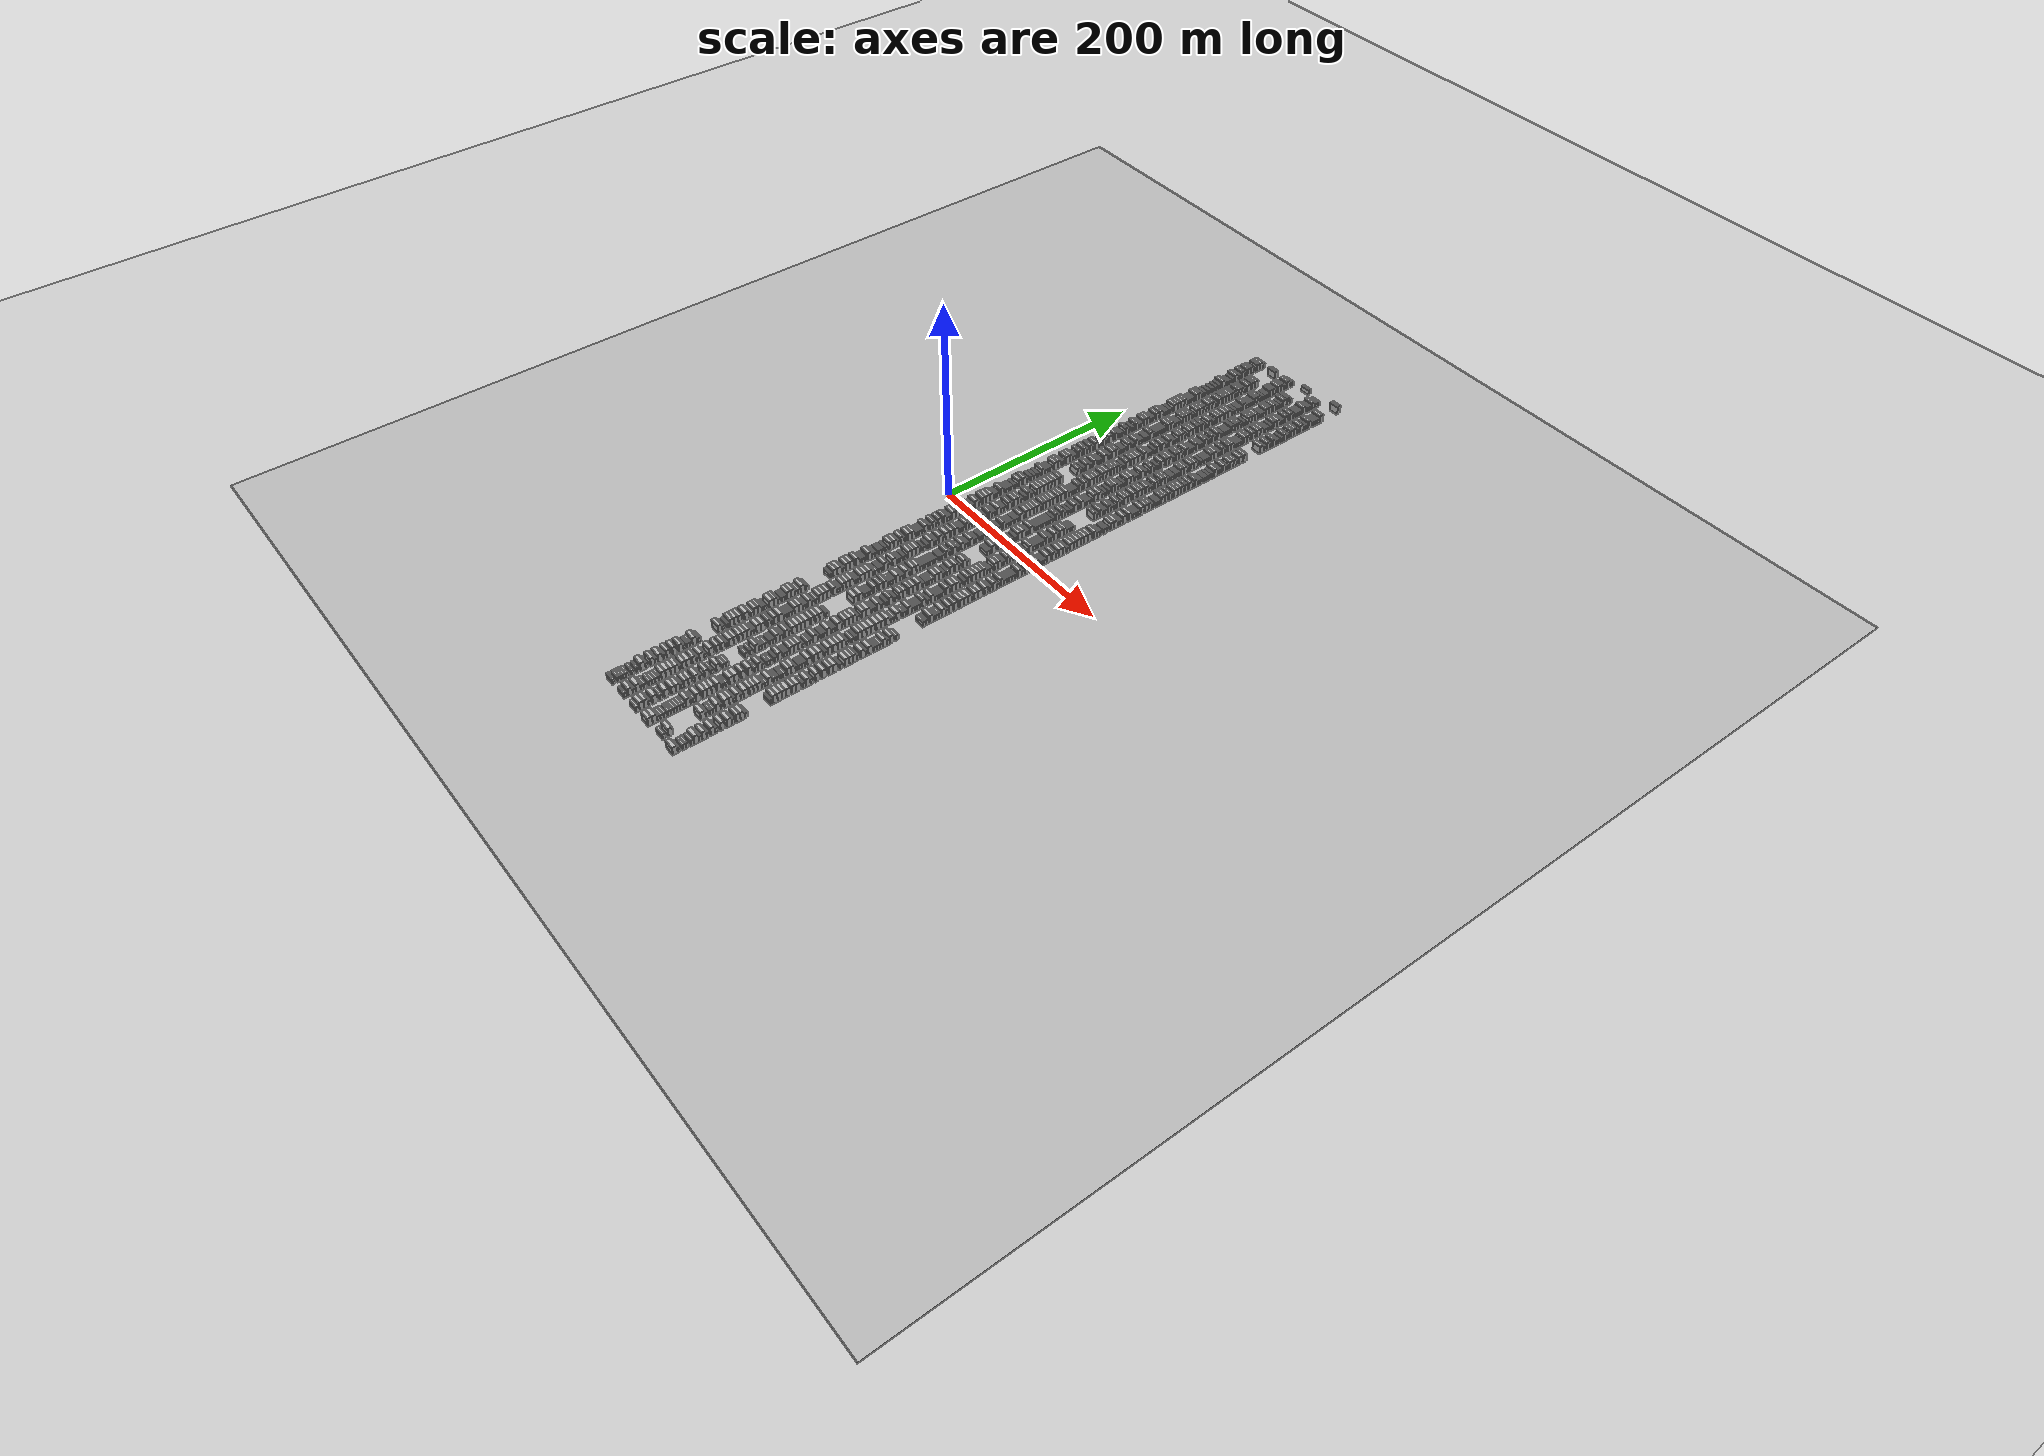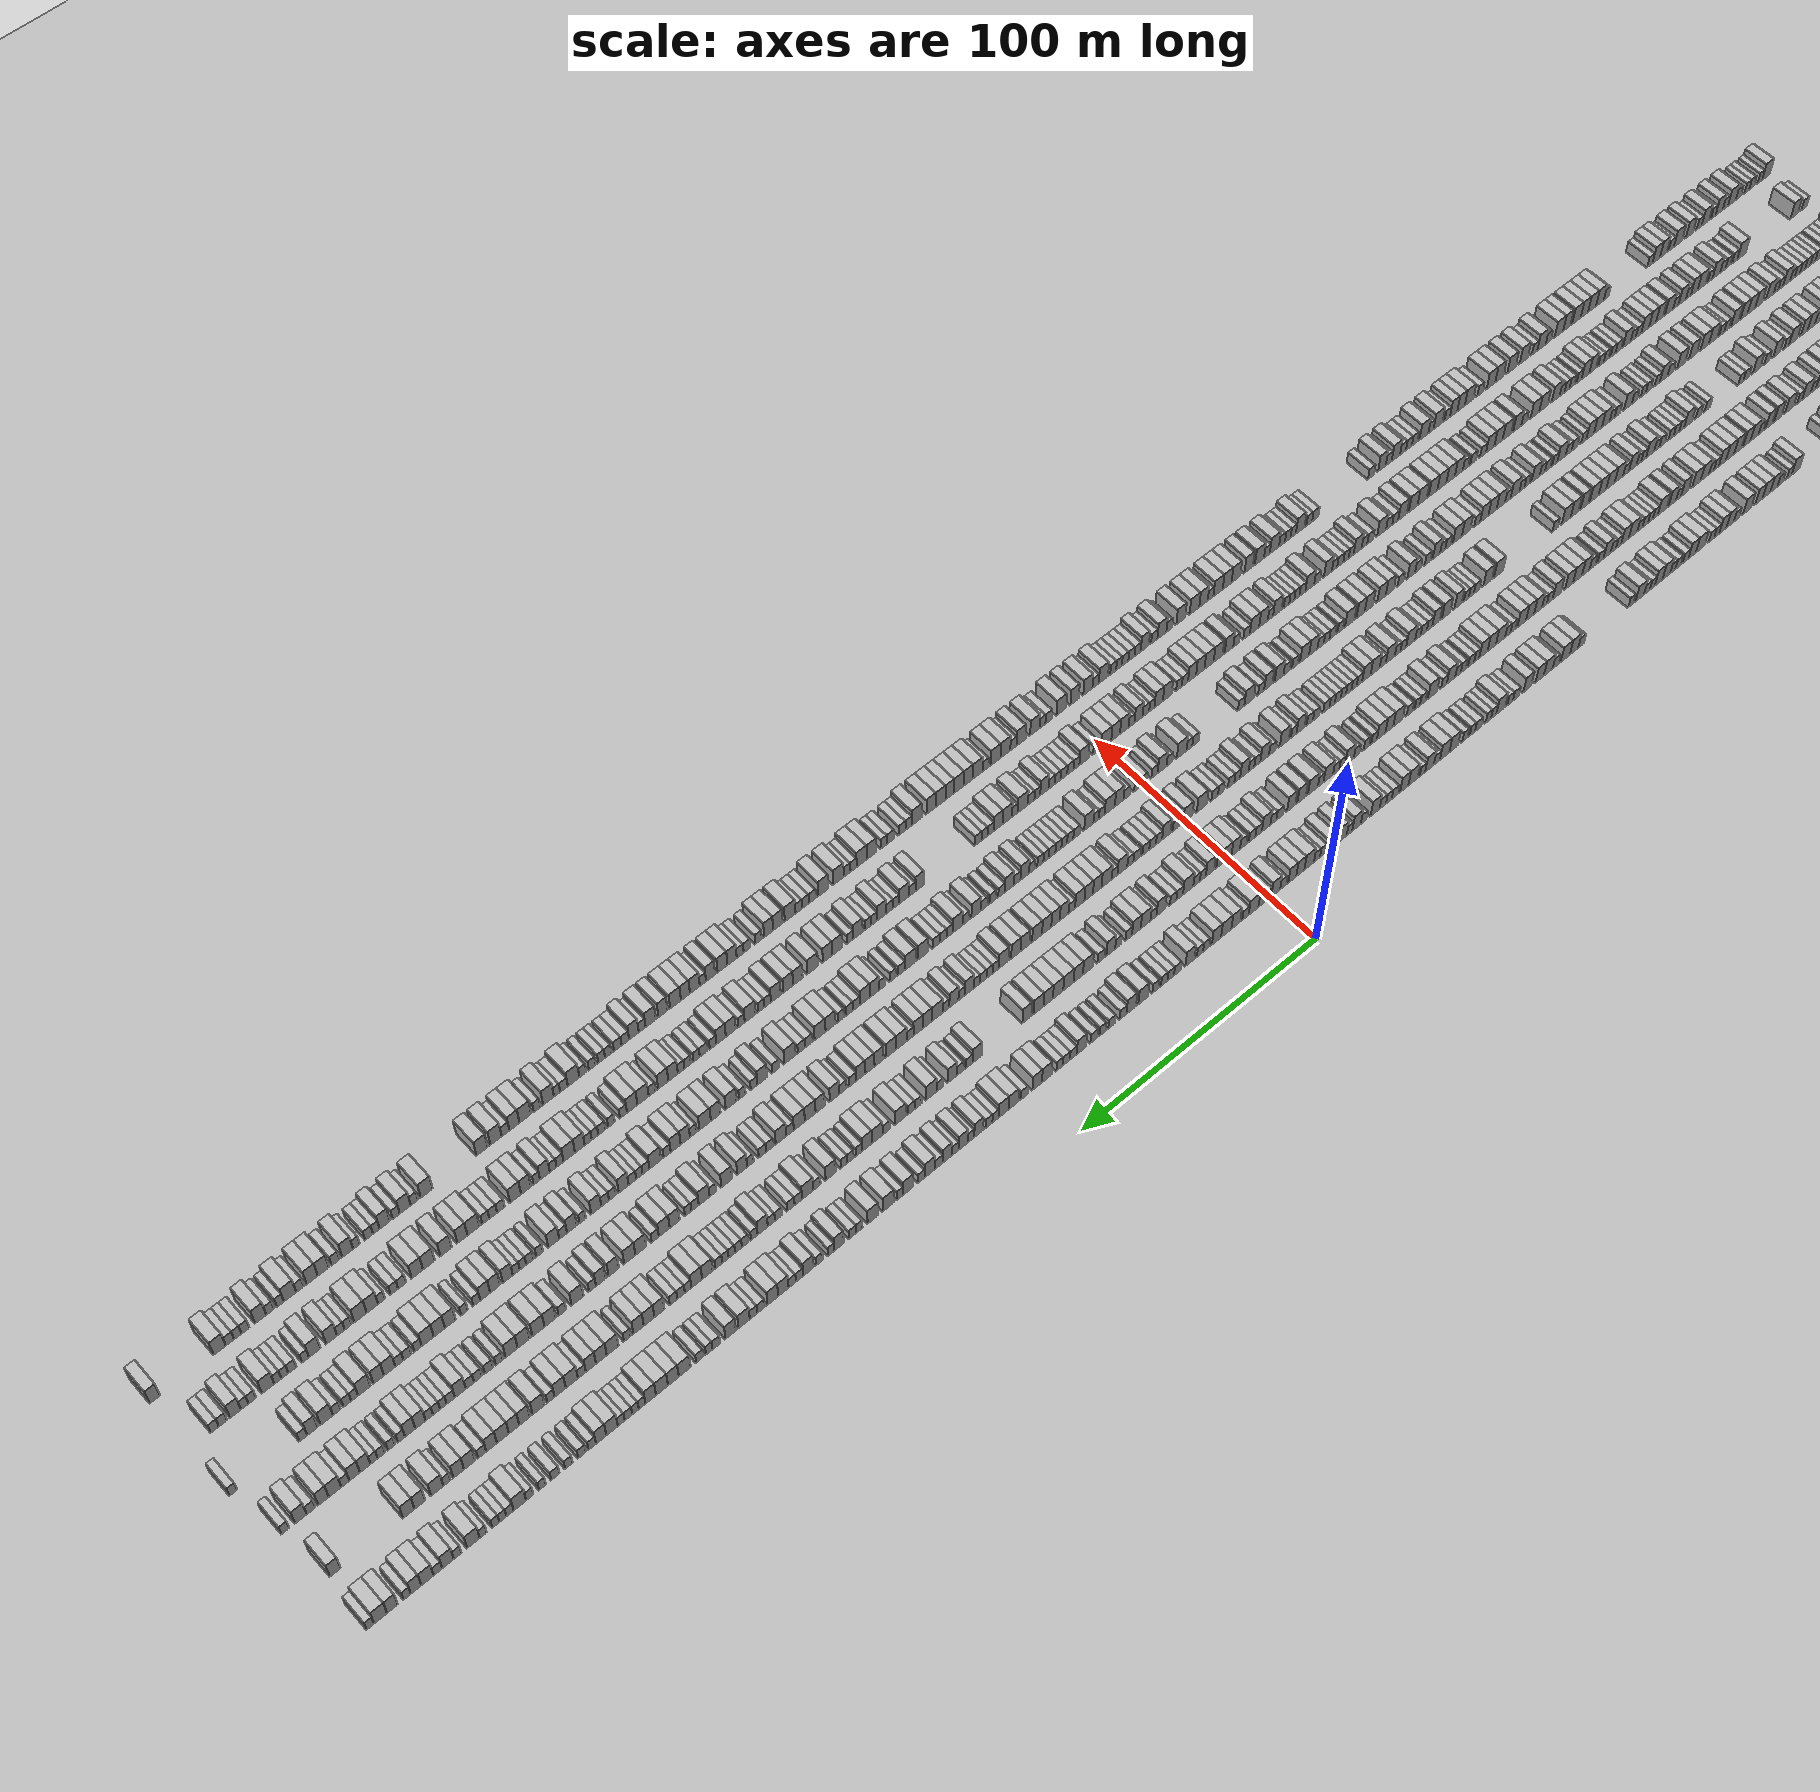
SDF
<?xml version="1.0" encoding="utf-8"?>

<sdf version="1.6">

   <world name="default">

      <gui fullscreen="0">

         <camera name="user_camera">

            <pose>-15 0 4.57585 0 0 0</pose>

            <view_controller>orbit</view_controller>

         </camera>

      </gui>

      <scene>

         <sky>

           <clouds>

             <speed>12</speed>

           </clouds>

         </sky>

         <ambient>0.4 0.4 0.4 1</ambient>

         <background>0.7 0.7 0.7 1</background>

         <shadows>1</shadows>

      </scene>

      <gravity>0 0 -9.8066</gravity>

      <magnetic_field>6e-06 2.3e-05 -4.2e-05</magnetic_field>

      <physics default="0" name="default_physics" type="ode">

         <ode>

            <solver>

               <type>quick</type>

               <iters>10</iters>

               <sor>1.0</sor>

               <use_dynamic_moi_rescaling>0</use_dynamic_moi_rescaling>

            </solver>

            <constraints>

               <cfm>0</cfm>

               <erp>0.2</erp>

               <contact_max_correcting_vel>100</contact_max_correcting_vel>

               <contact_surface_layer>0.001</contact_surface_layer>

            </constraints>

         </ode>

         <max_step_size>0.004</max_step_size>

         <real_time_factor>1</real_time_factor>

         <real_time_update_rate>250</real_time_update_rate>

      </physics>

      <light name="sun" type="directional">

         <cast_shadows>1</cast_shadows>

         <pose>0 0 10 0 0 0</pose>

         <diffuse>0.8 0.8 0.8 1</diffuse>

         <specular>0.2 0.2 0.2 1</specular>

         <attenuation>

            <range>1000</range>

            <constant>0.9</constant>

            <linear>0.01</linear>

            <quadratic>0.001</quadratic>

         </attenuation>

         <direction>-0.5 0.1 -0.9</direction>

      </light>

      <include>

         <name>ground_plane_1</name>

         <uri>model://HANNAS_ground_plane</uri>

         <pose>0 0 0  0 0 0</pose>

      </include>

      <include>

         <name>ground_plane_2</name>

         <uri>model://HANNAS_ground_plane</uri>

         <pose>100 0 0  0 0 0</pose>

      </include>

      <model name="building_1">

         <static>1</static>

         <pose frame="">25.0000 -348.7700 0 0.000000 0.000000 0.000000</pose>

         <link name="link">

            <pose frame="">0 0 3.00 0 0 0</pose>

            <collision name="collision">

               <geometry>

                  <box>

                     <size>10.0000 2.4600 6.0000</size>

                  </box>

               </geometry>

               <max_contacts>10</max_contacts>

               <surface>

                  <contact>

                     <ode/>

                  </contact>

                  <bounce/>

                  <friction>

                     <torsional>

                        <ode/>

                     </torsional>

                     <ode/>

                  </friction>

               </surface>

            </collision>

            <visual name="visual">

               <cast_shadows>0</cast_shadows>

               <geometry>

                  <box>

                     <size>10.0000 2.4600 6.0000</size>

                  </box>

               </geometry>

               <material>

                  <script>

                     <uri>model://HANNAS_wall/materials/scripts</uri>

                     <uri>model://HANNAS_wall/materials/textures</uri>

                     <name>vrc/HANNAS_wall</name>

                  </script>

               </material>

            </visual>

            <self_collide>0</self_collide>

            <enable_wind>0</enable_wind>

            <kinematic>0</kinematic>

         </link>

      </model>

      <model name="building_2">

         <static>1</static>

         <pose frame="">25.0000 -344.2790 0 0.000000 0.000000 0.000000</pose>

         <link name="link">

            <pose frame="">0 0 3.00 0 0 0</pose>

            <collision name="collision">

               <geometry>

                  <box>

                     <size>10.0000 2.5220 6.0000</size>

                  </box>

               </geometry>

               <max_contacts>10</max_contacts>

               <surface>

                  <contact>

                     <ode/>

                  </contact>

                  <bounce/>

                  <friction>

                     <torsional>

                        <ode/>

                     </torsional>

                     <ode/>

                  </friction>

               </surface>

            </collision>

            <visual name="visual">

               <cast_shadows>0</cast_shadows>

               <geometry>

                  <box>

                     <size>10.0000 2.5220 6.0000</size>

                  </box>

               </geometry>

               <material>

                  <script>

                     <uri>model://HANNAS_wall/materials/scripts</uri>

                     <uri>model://HANNAS_wall/materials/textures</uri>

                     <name>vrc/HANNAS_wall</name>

                  </script>

               </material>

            </visual>

            <self_collide>0</self_collide>

            <enable_wind>0</enable_wind>

            <kinematic>0</kinematic>

         </link>

      </model>

      <model name="building_3">

         <static>1</static>

         <pose frame="">25.0000 -341.7935 0 0.000000 0.000000 0.000000</pose>

         <link name="link">

            <pose frame="">0 0 3.00 0 0 0</pose>

            <collision name="collision">

               <geometry>

                  <box>

                     <size>10.0000 2.4490 6.0000</size>

                  </box>

               </geometry>

               <max_contacts>10</max_contacts>

               <surface>

                  <contact>

                     <ode/>

                  </contact>

                  <bounce/>

                  <friction>

                     <torsional>

                        <ode/>

                     </torsional>

                     <ode/>

                  </friction>

               </surface>

            </collision>

            <visual name="visual">

               <cast_shadows>0</cast_shadows>

               <geometry>

                  <box>

                     <size>10.0000 2.4490 6.0000</size>

                  </box>

               </geometry>

               <material>

                  <script>

                     <uri>model://HANNAS_wall/materials/scripts</uri>

                     <uri>model://HANNAS_wall/materials/textures</uri>

                     <name>vrc/HANNAS_wall</name>

                  </script>

               </material>

            </visual>

            <self_collide>0</self_collide>

            <enable_wind>0</enable_wind>

            <kinematic>0</kinematic>

         </link>

      </model>

      <model name="building_4">

         <static>1</static>

         <pose frame="">25.0000 -339.3221 0 0.000000 0.000000 0.000000</pose>

         <link name="link">

            <pose frame="">0 0 3.00 0 0 0</pose>

            <collision name="collision">

               <geometry>

                  <box>

                     <size>10.0000 2.4938 6.0000</size>

                  </box>

               </geometry>

               <max_contacts>10</max_contacts>

               <surface>

                  <contact>

                     <ode/>

                  </contact>

                  <bounce/>

                  <friction>

                     <torsional>

                        <ode/>

                     </torsional>

                     <ode/>

                  </friction>

               </surface>

            </collision>

            <visual name="visual">

               <cast_shadows>0</cast_shadows>

               <geometry>

                  <box>

                     <size>10.0000 2.4938 6.0000</size>

                  </box>

               </geometry>

               <material>

                  <script>

                     <uri>model://HANNAS_wall/materials/scripts</uri>

                     <uri>model://HANNAS_wall/materials/textures</uri>

                     <name>vrc/HANNAS_wall</name>

                  </script>

               </material>

            </visual>

            <self_collide>0</self_collide>

            <enable_wind>0</enable_wind>

            <kinematic>0</kinematic>

         </link>

      </model>

      <model name="building_5">

         <static>1</static>

         <pose frame="">25.0000 -336.6558 0 0.000000 0.000000 0.000000</pose>

         <link name="link">

            <pose frame="">0 0 3.00 0 0 0</pose>

            <collision name="collision">

               <geometry>

                  <box>

                     <size>10.0000 2.8388 6.0000</size>

                  </box>

               </geometry>

               <max_contacts>10</max_contacts>

               <surface>

                  <contact>

                     <ode/>

                  </contact>

                  <bounce/>

                  <friction>

                     <torsional>

                        <ode/>

                     </torsional>

                     <ode/>

                  </friction>

               </surface>

            </collision>

            <visual name="visual">

               <cast_shadows>0</cast_shadows>

               <geometry>

                  <box>

                     <size>10.0000 2.8388 6.0000</size>

                  </box>

               </geometry>

               <material>

                  <script>

                     <uri>model://HANNAS_wall/materials/scripts</uri>

                     <uri>model://HANNAS_wall/materials/textures</uri>

                     <name>vrc/HANNAS_wall</name>

                  </script>

               </material>

            </visual>

            <self_collide>0</self_collide>

            <enable_wind>0</enable_wind>

            <kinematic>0</kinematic>

         </link>

      </model>

      <model name="building_6">

         <static>1</static>

         <pose frame="">25.0000 -331.8536 0 0.000000 0.000000 0.000000</pose>

         <link name="link">

            <pose frame="">0 0 3.00 0 0 0</pose>

            <collision name="collision">

               <geometry>

                  <box>

                     <size>10.0000 2.7655 6.0000</size>

                  </box>

               </geometry>

               <max_contacts>10</max_contacts>

               <surface>

                  <contact>

                     <ode/>

                  </contact>

                  <bounce/>

                  <friction>

                     <torsional>

                        <ode/>

                     </torsional>

                     <ode/>

                  </friction>

               </surface>

            </collision>

            <visual name="visual">

               <cast_shadows>0</cast_shadows>

               <geometry>

                  <box>

                     <size>10.0000 2.7655 6.0000</size>

                  </box>

               </geometry>

               <material>

                  <script>

                     <uri>model://HANNAS_wall/materials/scripts</uri>

                     <uri>model://HANNAS_wall/materials/textures</uri>

                     <name>vrc/HANNAS_wall</name>

                  </script>

               </material>

            </visual>

            <self_collide>0</self_collide>

            <enable_wind>0</enable_wind>

            <kinematic>0</kinematic>

         </link>

      </model>

      <model name="building_7">

         <static>1</static>

         <pose frame="">25.0000 -327.2691 0 0.000000 0.000000 0.000000</pose>

         <link name="link">

            <pose frame="">0 0 3.00 0 0 0</pose>

            <collision name="collision">

               <geometry>

                  <box>

                     <size>10.0000 2.4035 6.0000</size>

                  </box>

               </geometry>

               <max_contacts>10</max_contacts>

               <surface>

                  <contact>

                     <ode/>

                  </contact>

                  <bounce/>

                  <friction>

                     <torsional>

                        <ode/>

                     </torsional>

                     <ode/>

                  </friction>

               </surface>

            </collision>

            <visual name="visual">

               <cast_shadows>0</cast_shadows>

               <geometry>

                  <box>

                     <size>10.0000 2.4035 6.0000</size>

                  </box>

               </geometry>

               <material>

                  <script>

                     <uri>model://HANNAS_wall/materials/scripts</uri>

                     <uri>model://HANNAS_wall/materials/textures</uri>

                     <name>vrc/HANNAS_wall</name>

                  </script>

               </material>

            </visual>

            <self_collide>0</self_collide>

            <enable_wind>0</enable_wind>

            <kinematic>0</kinematic>

         </link>

      </model>

      <model name="building_8">

         <static>1</static>

         <pose frame="">25.0000 -322.8281 0 0.000000 0.000000 0.000000</pose>

         <link name="link">

            <pose frame="">0 0 4.50 0 0 0</pose>

            <collision name="collision">

               <geometry>

                  <box>

                     <size>10.0000 4.4784 9.0000</size>

                  </box>

               </geometry>

               <max_contacts>10</max_contacts>

               <surface>

                  <contact>

                     <ode/>

                  </contact>

                  <bounce/>

                  <friction>

                     <torsional>

                        <ode/>

                     </torsional>

                     <ode/>

                  </friction>

               </surface>

            </collision>

            <visual name="visual">

               <cast_shadows>0</cast_shadows>

               <geometry>

                  <box>

                     <size>10.0000 4.4784 9.0000</size>

                  </box>

               </geometry>

               <material>

                  <script>

                     <uri>model://HANNAS_wall/materials/scripts</uri>

                     <uri>model://HANNAS_wall/materials/textures</uri>

                     <name>vrc/HANNAS_wall</name>

                  </script>

               </material>

            </visual>

            <self_collide>0</self_collide>

            <enable_wind>0</enable_wind>

            <kinematic>0</kinematic>

         </link>

      </model>

      <model name="building_9">

         <static>1</static>

         <pose frame="">25.0000 -319.2223 0 0.000000 0.000000 0.000000</pose>

         <link name="link">

            <pose frame="">0 0 3.00 0 0 0</pose>

            <collision name="collision">

               <geometry>

                  <box>

                     <size>10.0000 2.7331 6.0000</size>

                  </box>

               </geometry>

               <max_contacts>10</max_contacts>

               <surface>

                  <contact>

                     <ode/>

                  </contact>

                  <bounce/>

                  <friction>

                     <torsional>

                        <ode/>

                     </torsional>

                     <ode/>

                  </friction>

               </surface>

            </collision>

            <visual name="visual">

               <cast_shadows>0</cast_shadows>

               <geometry>

                  <box>

                     <size>10.0000 2.7331 6.0000</size>

                  </box>

               </geometry>

               <material>

                  <script>

                     <uri>model://HANNAS_wall/materials/scripts</uri>

                     <uri>model://HANNAS_wall/materials/textures</uri>

                     <name>vrc/HANNAS_wall</name>

                  </script>

               </material>

            </visual>

            <self_collide>0</self_collide>

            <enable_wind>0</enable_wind>

            <kinematic>0</kinematic>

         </link>

      </model>

      <model name="building_10">

         <static>1</static>

         <pose frame="">25.0000 -313.9639 0 0.000000 0.000000 0.000000</pose>

         <link name="link">

            <pose frame="">0 0 4.50 0 0 0</pose>

            <collision name="collision">

               <geometry>

                  <box>

                     <size>10.0000 3.7837 9.0000</size>

                  </box>

               </geometry>

               <max_contacts>10</max_contacts>

               <surface>

                  <contact>

                     <ode/>

                  </contact>

                  <bounce/>

                  <friction>

                     <torsional>

                        <ode/>

                     </torsional>

                     <ode/>

                  </friction>

               </surface>

            </collision>

            <visual name="visual">

               <cast_shadows>0</cast_shadows>

               <geometry>

                  <box>

                     <size>10.0000 3.7837 9.0000</size>

                  </box>

               </geometry>

               <material>

                  <script>

                     <uri>model://HANNAS_wall/materials/scripts</uri>

                     <uri>model://HANNAS_wall/materials/textures</uri>

                     <name>vrc/HANNAS_wall</name>

                  </script>

               </material>

            </visual>

            <self_collide>0</self_collide>

            <enable_wind>0</enable_wind>

            <kinematic>0</kinematic>

         </link>

      </model>

      <model name="building_11">

         <static>1</static>

         <pose frame="">25.0000 -310.6386 0 0.000000 0.000000 0.000000</pose>

         <link name="link">

            <pose frame="">0 0 3.00 0 0 0</pose>

            <collision name="collision">

               <geometry>

                  <box>

                     <size>10.0000 2.8669 6.0000</size>

                  </box>

               </geometry>

               <max_contacts>10</max_contacts>

               <surface>

                  <contact>

                     <ode/>

                  </contact>

                  <bounce/>

                  <friction>

                     <torsional>

                        <ode/>

                     </torsional>

                     <ode/>

                  </friction>

               </surface>

            </collision>

            <visual name="visual">

               <cast_shadows>0</cast_shadows>

               <geometry>

                  <box>

                     <size>10.0000 2.8669 6.0000</size>

                  </box>

               </geometry>

               <material>

                  <script>

                     <uri>model://HANNAS_wall/materials/scripts</uri>

                     <uri>model://HANNAS_wall/materials/textures</uri>

                     <name>vrc/HANNAS_wall</name>

                  </script>

               </material>

            </visual>

            <self_collide>0</self_collide>

            <enable_wind>0</enable_wind>

            <kinematic>0</kinematic>

         </link>

      </model>

      <model name="building_12">

         <static>1</static>

         <pose frame="">25.0000 -307.1136 0 0.000000 0.000000 0.000000</pose>

         <link name="link">

            <pose frame="">0 0 4.50 0 0 0</pose>

            <collision name="collision">

               <geometry>

                  <box>

                     <size>10.0000 4.1830 9.0000</size>

                  </box>

               </geometry>

               <max_contacts>10</max_contacts>

               <surface>

                  <contact>

                     <ode/>

                  </contact>

                  <bounce/>

                  <friction>

                     <torsional>

                        <ode/>

                     </torsional>

                     <ode/>

                  </friction>

               </surface>

            </collision>

            <visual name="visual">

               <cast_shadows>0</cast_shadows>

               <geometry>

                  <box>

                     <size>10.0000 4.1830 9.0000</size>

                  </box>

               </geometry>

               <material>

                  <script>

                     <uri>model://HANNAS_wall/materials/scripts</uri>

                     <uri>model://HANNAS_wall/materials/textures</uri>

                     <name>vrc/HANNAS_wall</name>

                  </script>

               </material>

            </visual>

            <self_collide>0</self_collide>

            <enable_wind>0</enable_wind>

            <kinematic>0</kinematic>

         </link>

      </model>

      <model name="building_13">

         <static>1</static>

         <pose frame="">25.0000 -302.7869 0 0.000000 0.000000 0.000000</pose>

         <link name="link">

            <pose frame="">0 0 3.00 0 0 0</pose>

            <collision name="collision">

               <geometry>

                  <box>

                     <size>10.0000 2.4703 6.0000</size>

                  </box>

               </geometry>

               <max_contacts>10</max_contacts>

               <surface>

                  <contact>

                     <ode/>

                  </contact>

                  <bounce/>

                  <friction>

                     <torsional>

                        <ode/>

                     </torsional>

                     <ode/>

                  </friction>

               </surface>

            </collision>

            <visual name="visual">

               <cast_shadows>0</cast_shadows>

               <geometry>

                  <box>

                     <size>10.0000 2.4703 6.0000</size>

                  </box>

               </geometry>

               <material>

                  <script>

                     <uri>model://HANNAS_wall/materials/scripts</uri>

                     <uri>model://HANNAS_wall/materials/textures</uri>

                     <name>vrc/HANNAS_wall</name>

                  </script>

               </material>

            </visual>

            <self_collide>0</self_collide>

            <enable_wind>0</enable_wind>

            <kinematic>0</kinematic>

         </link>

      </model>

      <model name="building_14">

         <static>1</static>

         <pose frame="">25.0000 -299.7337 0 0.000000 0.000000 0.000000</pose>

         <link name="link">

            <pose frame="">0 0 4.50 0 0 0</pose>

            <collision name="collision">

               <geometry>

                  <box>

                     <size>10.0000 3.6361 9.0000</size>

                  </box>

               </geometry>

               <max_contacts>10</max_contacts>

               <surface>

                  <contact>

                     <ode/>

                  </contact>

                  <bounce/>

                  <friction>

                     <torsional>

                        <ode/>

                     </torsional>

                     <ode/>

                  </friction>

               </surface>

            </collision>

            <visual name="visual">

               <cast_shadows>0</cast_shadows>

               <geometry>

                  <box>

                     <size>10.0000 3.6361 9.0000</size>

                  </box>

               </geometry>

               <material>

                  <script>

                     <uri>model://HANNAS_wall/materials/scripts</uri>

                     <uri>model://HANNAS_wall/materials/textures</uri>

                     <name>vrc/HANNAS_wall</name>

                  </script>

               </material>

            </visual>

            <self_collide>0</self_collide>

            <enable_wind>0</enable_wind>

            <kinematic>0</kinematic>

         </link>

      </model>

      <model name="building_15">

         <static>1</static>

         <pose frame="">25.0000 -294.0188 0 0.000000 0.000000 0.000000</pose>

         <link name="link">

            <pose frame="">0 0 4.50 0 0 0</pose>

            <collision name="collision">

               <geometry>

                  <box>

                     <size>10.0000 3.7938 9.0000</size>

                  </box>

               </geometry>

               <max_contacts>10</max_contacts>

               <surface>

                  <contact>

                     <ode/>

                  </contact>

                  <bounce/>

                  <friction>

                     <torsional>

                        <ode/>

                     </torsional>

                     <ode/>

                  </friction>

               </surface>

            </collision>

            <visual name="visual">

               <cast_shadows>0</cast_shadows>

               <geometry>

                  <box>

                     <size>10.0000 3.7938 9.0000</size>

                  </box>

               </geometry>

               <material>

                  <script>

                     <uri>model://HANNAS_wall/materials/scripts</uri>

                     <uri>model://HANNAS_wall/materials/textures</uri>

                     <name>vrc/HANNAS_wall</name>

                  </script>

               </material>

            </visual>

            <self_collide>0</self_collide>

            <enable_wind>0</enable_wind>

            <kinematic>0</kinematic>

         </link>

      </model>

      <model name="building_16">

         <static>1</static>

         <pose frame="">25.0000 -288.1485 0 0.000000 0.000000 0.000000</pose>

         <link name="link">

            <pose frame="">0 0 4.50 0 0 0</pose>

            <collision name="collision">

               <geometry>

                  <box>

                     <size>10.0000 3.9466 9.0000</size>

                  </box>

               </geometry>

               <max_contacts>10</max_contacts>

               <surface>

                  <contact>

                     <ode/>

                  </contact>

                  <bounce/>

                  <friction>

                     <torsional>

                        <ode/>

                     </torsional>

                     <ode/>

                  </friction>

               </surface>

            </collision>

            <visual name="visual">

               <cast_shadows>0</cast_shadows>

               <geometry>

                  <box>

                     <size>10.0000 3.9466 9.0000</size>

                  </box>

               </geometry>

               <material>

                  <script>

                     <uri>model://HANNAS_wall/materials/scripts</uri>

                     <uri>model://HANNAS_wall/materials/textures</uri>

                     <name>vrc/HANNAS_wall</name>

                  </script>

               </material>

            </visual>

            <self_collide>0</self_collide>

            <enable_wind>0</enable_wind>

            <kinematic>0</kinematic>

         </link>

      </model>

      <model name="building_17">

         <static>1</static>

         <pose frame="">25.0000 -284.9693 0 0.000000 0.000000 0.000000</pose>

         <link name="link">

            <pose frame="">0 0 3.00 0 0 0</pose>

            <collision name="collision">

               <geometry>

                  <box>

                     <size>10.0000 2.4118 6.0000</size>

                  </box>

               </geometry>

               <max_contacts>10</max_contacts>

               <surface>

                  <contact>

                     <ode/>

                  </contact>

                  <bounce/>

                  <friction>

                     <torsional>

                        <ode/>

                     </torsional>

                     <ode/>

                  </friction>

               </surface>

            </collision>

            <visual name="visual">

               <cast_shadows>0</cast_shadows>

               <geometry>

                  <box>

                     <size>10.0000 2.4118 6.0000</size>

                  </box>

               </geometry>

               <material>

                  <script>

                     <uri>model://HANNAS_wall/materials/scripts</uri>

                     <uri>model://HANNAS_wall/materials/textures</uri>

                     <name>vrc/HANNAS_wall</name>

                  </script>

               </material>

            </visual>

            <self_collide>0</self_collide>

            <enable_wind>0</enable_wind>

            <kinematic>0</kinematic>

         </link>

      </model>

      <model name="building_18">

         <static>1</static>

         <pose frame="">25.0000 -281.5322 0 0.000000 0.000000 0.000000</pose>

         <link name="link">

            <pose frame="">0 0 3.00 0 0 0</pose>

            <collision name="collision">

               <geometry>

                  <box>

                     <size>10.0000 2.4624 6.0000</size>

                  </box>

               </geometry>

               <max_contacts>10</max_contacts>

               <surface>

                  <contact>

                     <ode/>

                  </contact>

                  <bounce/>

                  <friction>

                     <torsional>

                        <ode/>

                     </torsional>

                     <ode/>

                  </friction>

               </surface>

            </collision>

            <visual name="visual">

               <cast_shadows>0</cast_shadows>

               <geometry>

                  <box>

                     <size>10.0000 2.4624 6.0000</size>

                  </box>

               </geometry>

               <material>

                  <script>

                     <uri>model://HANNAS_wall/materials/scripts</uri>

                     <uri>model://HANNAS_wall/materials/textures</uri>

                     <name>vrc/HANNAS_wall</name>

                  </script>

               </material>

            </visual>

            <self_collide>0</self_collide>

            <enable_wind>0</enable_wind>

            <kinematic>0</kinematic>

         </link>

      </model>

      <model name="building_19">

         <static>1</static>

         <pose frame="">25.0000 -279.0378 0 0.000000 0.000000 0.000000</pose>

         <link name="link">

            <pose frame="">0 0 3.00 0 0 0</pose>

            <collision name="collision">

               <geometry>

                  <box>

                     <size>10.0000 2.5264 6.0000</size>

                  </box>

               </geometry>

               <max_contacts>10</max_contacts>

               <surface>

                  <contact>

                     <ode/>

                  </contact>

                  <bounce/>

                  <friction>

                     <torsional>

                        <ode/>

                     </torsional>

                     <ode/>

                  </friction>

               </surface>

            </collision>

            <visual name="visual">

               <cast_shadows>0</cast_shadows>

               <geometry>

                  <box>

                     <size>10.0000 2.5264 6.0000</size>

                  </box>

               </geometry>

               <material>

                  <script>

                     <uri>model://HANNAS_wall/materials/scripts</uri>

                     <uri>model://HANNAS_wall/materials/textures</uri>

                     <name>vrc/HANNAS_wall</name>

                  </script>

               </material>

            </visual>

            <self_collide>0</self_collide>

            <enable_wind>0</enable_wind>

            <kinematic>0</kinematic>

         </link>

      </model>

      <model name="building_20">

         <static>1</static>

         <pose frame="">25.0000 -275.6658 0 0.000000 0.000000 0.000000</pose>

         <link name="link">

            <pose frame="">0 0 4.50 0 0 0</pose>

            <collision name="collision">

               <geometry>

                  <box>

                     <size>10.0000 4.2176 9.0000</size>

                  </box>

               </geometry>

               <max_contacts>10</max_contacts>

               <surface>

                  <contact>

                     <ode/>

                  </contact>

                  <bounce/>

                  <friction>

                     <torsional>

                        <ode/>

                     </torsional>

                     <ode/>

                  </friction>

               </surface>

            </collision>

            <visual name="visual">

               <cast_shadows>0</cast_shadows>

               <geometry>

                  <box>

                     <size>10.0000 4.2176 9.0000</size>

                  </box>

               </geometry>

               <material>

                  <script>

                     <uri>model://HANNAS_wall/materials/scripts</uri>

                     <uri>model://HANNAS_wall/materials/textures</uri>

                     <name>vrc/HANNAS_wall</name>

                  </script>

               </material>

            </visual>

            <self_collide>0</self_collide>

            <enable_wind>0</enable_wind>

            <kinematic>0</kinematic>

         </link>

      </model>

      <model name="building_21">

         <static>1</static>

         <pose frame="">25.0000 -271.1557 0 0.000000 0.000000 0.000000</pose>

         <link name="link">

            <pose frame="">0 0 3.00 0 0 0</pose>

            <collision name="collision">

               <geometry>

                  <box>

                     <size>10.0000 2.8026 6.0000</size>

                  </box>

               </geometry>

               <max_contacts>10</max_contacts>

               <surface>

                  <contact>

                     <ode/>

                  </contact>

                  <bounce/>

                  <friction>

                     <torsional>

                        <ode/>

                     </torsional>

                     <ode/>

                  </friction>

               </surface>

            </collision>

            <visual name="visual">

               <cast_shadows>0</cast_shadows>

               <geometry>

                  <box>

                     <size>10.0000 2.8026 6.0000</size>

                  </box>

               </geometry>

               <material>

                  <script>

                     <uri>model://HANNAS_wall/materials/scripts</uri>

                     <uri>model://HANNAS_wall/materials/textures</uri>

                     <name>vrc/HANNAS_wall</name>

                  </script>

               </material>

            </visual>

            <self_collide>0</self_collide>

            <enable_wind>0</enable_wind>

            <kinematic>0</kinematic>

         </link>

      </model>

      <model name="building_22">

         <static>1</static>

         <pose frame="">25.0000 -251.8844 0 0.000000 0.000000 0.000000</pose>

         <link name="link">

            <pose frame="">0 0 4.50 0 0 0</pose>

            <collision name="collision">

               <geometry>

                  <box>

                     <size>10.0000 3.9133 9.0000</size>

                  </box>

               </geometry>

               <max_contacts>10</max_contacts>

               <surface>

                  <contact>

                     <ode/>

                  </contact>

                  <bounce/>

                  <friction>

                     <torsional>

                        <ode/>

                     </torsional>

                     <ode/>

                  </friction>

               </surface>

            </collision>

            <visual name="visual">

               <cast_shadows>0</cast_shadows>

               <geometry>

                  <box>

                     <size>10.0000 3.9133 9.0000</size>

                  </box>

               </geometry>

               <material>

                  <script>

                     <uri>model://HANNAS_wall/materials/scripts</uri>

                     <uri>model://HANNAS_wall/materials/textures</uri>

                     <name>vrc/HANNAS_wall</name>

                  </script>

               </material>

            </visual>

            <self_collide>0</self_collide>

            <enable_wind>0</enable_wind>

            <kinematic>0</kinematic>

         </link>

      </model>

      <model name="building_23">

         <static>1</static>

         <pose frame="">25.0000 -248.5655 0 0.000000 0.000000 0.000000</pose>

         <link name="link">

            <pose frame="">0 0 3.00 0 0 0</pose>

            <collision name="collision">

               <geometry>

                  <box>

                     <size>10.0000 2.7246 6.0000</size>

                  </box>

               </geometry>

               <max_contacts>10</max_contacts>

               <surface>

                  <contact>

                     <ode/>

                  </contact>

                  <bounce/>

                  <friction>

                     <torsional>

                        <ode/>

                     </torsional>

                     <ode/>

                  </friction>

               </surface>

            </collision>

            <visual name="visual">

               <cast_shadows>0</cast_shadows>

               <geometry>

                  <box>

                     <size>10.0000 2.7246 6.0000</size>

                  </box>

               </geometry>

               <material>

                  <script>

                     <uri>model://HANNAS_wall/materials/scripts</uri>

                     <uri>model://HANNAS_wall/materials/textures</uri>

                     <name>vrc/HANNAS_wall</name>

                  </script>

               </material>

            </visual>

            <self_collide>0</self_collide>

            <enable_wind>0</enable_wind>

            <kinematic>0</kinematic>

         </link>

      </model>

      <model name="building_24">

         <static>1</static>

         <pose frame="">25.0000 -243.8959 0 0.000000 0.000000 0.000000</pose>

         <link name="link">

            <pose frame="">0 0 3.00 0 0 0</pose>

            <collision name="collision">

               <geometry>

                  <box>

                     <size>10.0000 2.6144 6.0000</size>

                  </box>

               </geometry>

               <max_contacts>10</max_contacts>

               <surface>

                  <contact>

                     <ode/>

                  </contact>

                  <bounce/>

                  <friction>

                     <torsional>

                        <ode/>

                     </torsional>

                     <ode/>

                  </friction>

               </surface>

            </collision>

            <visual name="visual">

               <cast_shadows>0</cast_shadows>

               <geometry>

                  <box>

                     <size>10.0000 2.6144 6.0000</size>

                  </box>

               </geometry>

               <material>

                  <script>

                     <uri>model://HANNAS_wall/materials/scripts</uri>

                     <uri>model://HANNAS_wall/materials/textures</uri>

                     <name>vrc/HANNAS_wall</name>

                  </script>

               </material>

            </visual>

            <self_collide>0</self_collide>

            <enable_wind>0</enable_wind>

            <kinematic>0</kinematic>

         </link>

      </model>

      <model name="building_25">

         <static>1</static>

         <pose frame="">25.0000 -240.6920 0 0.000000 0.000000 0.000000</pose>

         <link name="link">

            <pose frame="">0 0 4.50 0 0 0</pose>

            <collision name="collision">

               <geometry>

                  <box>

                     <size>10.0000 3.7934 9.0000</size>

                  </box>

               </geometry>

               <max_contacts>10</max_contacts>

               <surface>

                  <contact>

                     <ode/>

                  </contact>

                  <bounce/>

                  <friction>

                     <torsional>

                        <ode/>

                     </torsional>

                     <ode/>

                  </friction>

               </surface>

            </collision>

            <visual name="visual">

               <cast_shadows>0</cast_shadows>

               <geometry>

                  <box>

                     <size>10.0000 3.7934 9.0000</size>

                  </box>

               </geometry>

               <material>

                  <script>

                     <uri>model://HANNAS_wall/materials/scripts</uri>

                     <uri>model://HANNAS_wall/materials/textures</uri>

                     <name>vrc/HANNAS_wall</name>

                  </script>

               </material>

            </visual>

            <self_collide>0</self_collide>

            <enable_wind>0</enable_wind>

            <kinematic>0</kinematic>

         </link>

      </model>

      <model name="building_26">

         <static>1</static>

         <pose frame="">25.0000 -236.7991 0 0.000000 0.000000 0.000000</pose>

         <link name="link">

            <pose frame="">0 0 4.50 0 0 0</pose>

            <collision name="collision">

               <geometry>

                  <box>

                     <size>10.0000 3.9925 9.0000</size>

                  </box>

               </geometry>

               <max_contacts>10</max_contacts>

               <surface>

                  <contact>

                     <ode/>

                  </contact>

                  <bounce/>

                  <friction>

                     <torsional>

                        <ode/>

                     </torsional>

                     <ode/>

                  </friction>

               </surface>

            </collision>

            <visual name="visual">

               <cast_shadows>0</cast_shadows>

               <geometry>

                  <box>

                     <size>10.0000 3.9925 9.0000</size>

                  </box>

               </geometry>

               <material>

                  <script>

                     <uri>model://HANNAS_wall/materials/scripts</uri>

                     <uri>model://HANNAS_wall/materials/textures</uri>

                     <name>vrc/HANNAS_wall</name>

                  </script>

               </material>

            </visual>

            <self_collide>0</self_collide>

            <enable_wind>0</enable_wind>

            <kinematic>0</kinematic>

         </link>

      </model>

      <model name="building_27">

         <static>1</static>

         <pose frame="">25.0000 -232.8922 0 0.000000 0.000000 0.000000</pose>

         <link name="link">

            <pose frame="">0 0 4.50 0 0 0</pose>

            <collision name="collision">

               <geometry>

                  <box>

                     <size>10.0000 3.8211 9.0000</size>

                  </box>

               </geometry>

               <max_contacts>10</max_contacts>

               <surface>

                  <contact>

                     <ode/>

                  </contact>

                  <bounce/>

                  <friction>

                     <torsional>

                        <ode/>

                     </torsional>

                     <ode/>

                  </friction>

               </surface>

            </collision>

            <visual name="visual">

               <cast_shadows>0</cast_shadows>

               <geometry>

                  <box>

                     <size>10.0000 3.8211 9.0000</size>

                  </box>

               </geometry>

               <material>

                  <script>

                     <uri>model://HANNAS_wall/materials/scripts</uri>

                     <uri>model://HANNAS_wall/materials/textures</uri>

                     <name>vrc/HANNAS_wall</name>

                  </script>

               </material>

            </visual>

            <self_collide>0</self_collide>

            <enable_wind>0</enable_wind>

            <kinematic>0</kinematic>

         </link>

      </model>

      <model name="building_28">

         <static>1</static>

         <pose frame="">25.0000 -226.8412 0 0.000000 0.000000 0.000000</pose>

         <link name="link">

            <pose frame="">0 0 4.50 0 0 0</pose>

            <collision name="collision">

               <geometry>

                  <box>

                     <size>10.0000 4.2809 9.0000</size>

                  </box>

               </geometry>

               <max_contacts>10</max_contacts>

               <surface>

                  <contact>

                     <ode/>

                  </contact>

                  <bounce/>

                  <friction>

                     <torsional>

                        <ode/>

                     </torsional>

                     <ode/>

                  </friction>

               </surface>

            </collision>

            <visual name="visual">

               <cast_shadows>0</cast_shadows>

               <geometry>

                  <box>

                     <size>10.0000 4.2809 9.0000</size>

                  </box>

               </geometry>

               <material>

                  <script>

                     <uri>model://HANNAS_wall/materials/scripts</uri>

                     <uri>model://HANNAS_wall/materials/textures</uri>

                     <name>vrc/HANNAS_wall</name>

                  </script>

               </material>

            </visual>

            <self_collide>0</self_collide>

            <enable_wind>0</enable_wind>

            <kinematic>0</kinematic>

         </link>

      </model>

      <model name="building_29">

         <static>1</static>

         <pose frame="">25.0000 -221.3224 0 0.000000 0.000000 0.000000</pose>

         <link name="link">

            <pose frame="">0 0 3.00 0 0 0</pose>

            <collision name="collision">

               <geometry>

                  <box>

                     <size>10.0000 2.7567 6.0000</size>

                  </box>

               </geometry>

               <max_contacts>10</max_contacts>

               <surface>

                  <contact>

                     <ode/>

                  </contact>

                  <bounce/>

                  <friction>

                     <torsional>

                        <ode/>

                     </torsional>

                     <ode/>

                  </friction>

               </surface>

            </collision>

            <visual name="visual">

               <cast_shadows>0</cast_shadows>

               <geometry>

                  <box>

                     <size>10.0000 2.7567 6.0000</size>

                  </box>

               </geometry>

               <material>

                  <script>

                     <uri>model://HANNAS_wall/materials/scripts</uri>

                     <uri>model://HANNAS_wall/materials/textures</uri>

                     <name>vrc/HANNAS_wall</name>

                  </script>

               </material>

            </visual>

            <self_collide>0</self_collide>

            <enable_wind>0</enable_wind>

            <kinematic>0</kinematic>

         </link>

      </model>

      <model name="building_30">

         <static>1</static>

         <pose frame="">25.0000 -218.1187 0 0.000000 0.000000 0.000000</pose>

         <link name="link">

            <pose frame="">0 0 4.50 0 0 0</pose>

            <collision name="collision">

               <geometry>

                  <box>

                     <size>10.0000 3.6509 9.0000</size>

                  </box>

               </geometry>

               <max_contacts>10</max_contacts>

               <surface>

                  <contact>

                     <ode/>

                  </contact>

                  <bounce/>

                  <friction>

                     <torsional>

                        <ode/>

                     </torsional>

                     <ode/>

                  </friction>

               </surface>

            </collision>

            <visual name="visual">

               <cast_shadows>0</cast_shadows>

               <geometry>

                  <box>

                     <size>10.0000 3.6509 9.0000</size>

                  </box>

               </geometry>

               <material>

                  <script>

                     <uri>model://HANNAS_wall/materials/scripts</uri>

                     <uri>model://HANNAS_wall/materials/textures</uri>

                     <name>vrc/HANNAS_wall</name>

                  </script>

               </material>

            </visual>

            <self_collide>0</self_collide>

            <enable_wind>0</enable_wind>

            <kinematic>0</kinematic>

         </link>

      </model>

      <model name="building_31">

         <static>1</static>

         <pose frame="">25.0000 -214.4540 0 0.000000 0.000000 0.000000</pose>

         <link name="link">

            <pose frame="">0 0 4.50 0 0 0</pose>

            <collision name="collision">

               <geometry>

                  <box>

                     <size>10.0000 3.6784 9.0000</size>

                  </box>

               </geometry>

               <max_contacts>10</max_contacts>

               <surface>

                  <contact>

                     <ode/>

                  </contact>

                  <bounce/>

                  <friction>

                     <torsional>

                        <ode/>

                     </torsional>

                     <ode/>

                  </friction>

               </surface>

            </collision>

            <visual name="visual">

               <cast_shadows>0</cast_shadows>

               <geometry>

                  <box>

                     <size>10.0000 3.6784 9.0000</size>

                  </box>

               </geometry>

               <material>

                  <script>

                     <uri>model://HANNAS_wall/materials/scripts</uri>

                     <uri>model://HANNAS_wall/materials/textures</uri>

                     <name>vrc/HANNAS_wall</name>

                  </script>

               </material>

            </visual>

            <self_collide>0</self_collide>

            <enable_wind>0</enable_wind>

            <kinematic>0</kinematic>

         </link>

      </model>

      <model name="building_32">

         <static>1</static>

         <pose frame="">25.0000 -211.3773 0 0.000000 0.000000 0.000000</pose>

         <link name="link">

            <pose frame="">0 0 3.00 0 0 0</pose>

            <collision name="collision">

               <geometry>

                  <box>

                     <size>10.0000 2.4749 6.0000</size>

                  </box>

               </geometry>

               <max_contacts>10</max_contacts>

               <surface>

                  <contact>

                     <ode/>

                  </contact>

                  <bounce/>

                  <friction>

                     <torsional>

                        <ode/>

                     </torsional>

                     <ode/>

                  </friction>

               </surface>

            </collision>

            <visual name="visual">

               <cast_shadows>0</cast_shadows>

               <geometry>

                  <box>

                     <size>10.0000 2.4749 6.0000</size>

                  </box>

               </geometry>

               <material>

                  <script>

                     <uri>model://HANNAS_wall/materials/scripts</uri>

                     <uri>model://HANNAS_wall/materials/textures</uri>

                     <name>vrc/HANNAS_wall</name>

                  </script>

               </material>

            </visual>

            <self_collide>0</self_collide>

            <enable_wind>0</enable_wind>

            <kinematic>0</kinematic>

         </link>

      </model>

      <model name="building_33">

         <static>1</static>

         <pose frame="">25.0000 -208.6981 0 0.000000 0.000000 0.000000</pose>

         <link name="link">

            <pose frame="">0 0 3.00 0 0 0</pose>

            <collision name="collision">

               <geometry>

                  <box>

                     <size>10.0000 2.8835 6.0000</size>

                  </box>

               </geometry>

               <max_contacts>10</max_contacts>

               <surface>

                  <contact>

                     <ode/>

                  </contact>

                  <bounce/>

                  <friction>

                     <torsional>

                        <ode/>

                     </torsional>

                     <ode/>

                  </friction>

               </surface>

            </collision>

            <visual name="visual">

               <cast_shadows>0</cast_shadows>

               <geometry>

                  <box>

                     <size>10.0000 2.8835 6.0000</size>

                  </box>

               </geometry>

               <material>

                  <script>

                     <uri>model://HANNAS_wall/materials/scripts</uri>

                     <uri>model://HANNAS_wall/materials/textures</uri>

                     <name>vrc/HANNAS_wall</name>

                  </script>

               </material>

            </visual>

            <self_collide>0</self_collide>

            <enable_wind>0</enable_wind>

            <kinematic>0</kinematic>

         </link>

      </model>

      <model name="building_34">

         <static>1</static>

         <pose frame="">25.0000 -203.0169 0 0.000000 0.000000 0.000000</pose>

         <link name="link">

            <pose frame="">0 0 4.50 0 0 0</pose>

            <collision name="collision">

               <geometry>

                  <box>

                     <size>10.0000 4.4790 9.0000</size>

                  </box>

               </geometry>

               <max_contacts>10</max_contacts>

               <surface>

                  <contact>

                     <ode/>

                  </contact>

                  <bounce/>

                  <friction>

                     <torsional>

                        <ode/>

                     </torsional>

                     <ode/>

                  </friction>

               </surface>

            </collision>

            <visual name="visual">

               <cast_shadows>0</cast_shadows>

               <geometry>

                  <box>

                     <size>10.0000 4.4790 9.0000</size>

                  </box>

               </geometry>

               <material>

                  <script>

                     <uri>model://HANNAS_wall/materials/scripts</uri>

                     <uri>model://HANNAS_wall/materials/textures</uri>

                     <name>vrc/HANNAS_wall</name>

                  </script>

               </material>

            </visual>

            <self_collide>0</self_collide>

            <enable_wind>0</enable_wind>

            <kinematic>0</kinematic>

         </link>

      </model>

      <model name="building_35">

         <static>1</static>

         <pose frame="">25.0000 -198.8989 0 0.000000 0.000000 0.000000</pose>

         <link name="link">

            <pose frame="">0 0 4.50 0 0 0</pose>

            <collision name="collision">

               <geometry>

                  <box>

                     <size>10.0000 3.7570 9.0000</size>

                  </box>

               </geometry>

               <max_contacts>10</max_contacts>

               <surface>

                  <contact>

                     <ode/>

                  </contact>

                  <bounce/>

                  <friction>

                     <torsional>

                        <ode/>

                     </torsional>

                     <ode/>

                  </friction>

               </surface>

            </collision>

            <visual name="visual">

               <cast_shadows>0</cast_shadows>

               <geometry>

                  <box>

                     <size>10.0000 3.7570 9.0000</size>

                  </box>

               </geometry>

               <material>

                  <script>

                     <uri>model://HANNAS_wall/materials/scripts</uri>

                     <uri>model://HANNAS_wall/materials/textures</uri>

                     <name>vrc/HANNAS_wall</name>

                  </script>

               </material>

            </visual>

            <self_collide>0</self_collide>

            <enable_wind>0</enable_wind>

            <kinematic>0</kinematic>

         </link>

      </model>

      <model name="building_36">

         <static>1</static>

         <pose frame="">25.0000 -195.5703 0 0.000000 0.000000 0.000000</pose>

         <link name="link">

            <pose frame="">0 0 3.00 0 0 0</pose>

            <collision name="collision">

               <geometry>

                  <box>

                     <size>10.0000 2.9002 6.0000</size>

                  </box>

               </geometry>

               <max_contacts>10</max_contacts>

               <surface>

                  <contact>

                     <ode/>

                  </contact>

                  <bounce/>

                  <friction>

                     <torsional>

                        <ode/>

                     </torsional>

                     <ode/>

                  </friction>

               </surface>

            </collision>

            <visual name="visual">

               <cast_shadows>0</cast_shadows>

               <geometry>

                  <box>

                     <size>10.0000 2.9002 6.0000</size>

                  </box>

               </geometry>

               <material>

                  <script>

                     <uri>model://HANNAS_wall/materials/scripts</uri>

                     <uri>model://HANNAS_wall/materials/textures</uri>

                     <name>vrc/HANNAS_wall</name>

                  </script>

               </material>

            </visual>

            <self_collide>0</self_collide>

            <enable_wind>0</enable_wind>

            <kinematic>0</kinematic>

         </link>

      </model>

      <model name="building_37">

         <static>1</static>

         <pose frame="">25.0000 -191.7918 0 0.000000 0.000000 0.000000</pose>

         <link name="link">

            <pose frame="">0 0 3.00 0 0 0</pose>

            <collision name="collision">

               <geometry>

                  <box>

                     <size>10.0000 2.6568 6.0000</size>

                  </box>

               </geometry>

               <max_contacts>10</max_contacts>

               <surface>

                  <contact>

                     <ode/>

                  </contact>

                  <bounce/>

                  <friction>

                     <torsional>

                        <ode/>

                     </torsional>

                     <ode/>

                  </friction>

               </surface>

            </collision>

            <visual name="visual">

               <cast_shadows>0</cast_shadows>

               <geometry>

                  <box>

                     <size>10.0000 2.6568 6.0000</size>

                  </box>

               </geometry>

               <material>

                  <script>

                     <uri>model://HANNAS_wall/materials/scripts</uri>

                     <uri>model://HANNAS_wall/materials/textures</uri>

                     <name>vrc/HANNAS_wall</name>

                  </script>

               </material>

            </visual>

            <self_collide>0</self_collide>

            <enable_wind>0</enable_wind>

            <kinematic>0</kinematic>

         </link>

      </model>

      <model name="building_38">

         <static>1</static>

         <pose frame="">25.0000 -189.1809 0 0.000000 0.000000 0.000000</pose>

         <link name="link">

            <pose frame="">0 0 3.00 0 0 0</pose>

            <collision name="collision">

               <geometry>

                  <box>

                     <size>10.0000 2.5649 6.0000</size>

                  </box>

               </geometry>

               <max_contacts>10</max_contacts>

               <surface>

                  <contact>

                     <ode/>

                  </contact>

                  <bounce/>

                  <friction>

                     <torsional>

                        <ode/>

                     </torsional>

                     <ode/>

                  </friction>

               </surface>

            </collision>

            <visual name="visual">

               <cast_shadows>0</cast_shadows>

               <geometry>

                  <box>

                     <size>10.0000 2.5649 6.0000</size>

                  </box>

               </geometry>

               <material>

                  <script>

                     <uri>model://HANNAS_wall/materials/scripts</uri>

                     <uri>model://HANNAS_wall/materials/textures</uri>

                     <name>vrc/HANNAS_wall</name>

                  </script>

               </material>

            </visual>

            <self_collide>0</self_collide>

            <enable_wind>0</enable_wind>

            <kinematic>0</kinematic>

         </link>

      </model>

      <model name="building_39">

         <static>1</static>

         <pose frame="">25.0000 -185.9556 0 0.000000 0.000000 0.000000</pose>

         <link name="link">

            <pose frame="">0 0 4.50 0 0 0</pose>

            <collision name="collision">

               <geometry>

                  <box>

                     <size>10.0000 3.8858 9.0000</size>

                  </box>

               </geometry>

               <max_contacts>10</max_contacts>

               <surface>

                  <contact>

                     <ode/>

                  </contact>

                  <bounce/>

                  <friction>

                     <torsional>

                        <ode/>

                     </torsional>

                     <ode/>

                  </friction>

               </surface>

            </collision>

            <visual name="visual">

               <cast_shadows>0</cast_shadows>

               <geometry>

                  <box>

                     <size>10.0000 3.8858 9.0000</size>

                  </box>

               </geometry>

               <material>

                  <script>

                     <uri>model://HANNAS_wall/materials/scripts</uri>

                     <uri>model://HANNAS_wall/materials/textures</uri>

                     <name>vrc/HANNAS_wall</name>

                  </script>

               </material>

            </visual>

            <self_collide>0</self_collide>

            <enable_wind>0</enable_wind>

            <kinematic>0</kinematic>

         </link>

      </model>

      <model name="building_40">

         <static>1</static>

         <pose frame="">25.0000 -182.0902 0 0.000000 0.000000 0.000000</pose>

         <link name="link">

            <pose frame="">0 0 4.50 0 0 0</pose>

            <collision name="collision">

               <geometry>

                  <box>

                     <size>10.0000 3.8450 9.0000</size>

                  </box>

               </geometry>

               <max_contacts>10</max_contacts>

               <surface>

                  <contact>

                     <ode/>

                  </contact>

                  <bounce/>

                  <friction>

                     <torsional>

                        <ode/>

                     </torsional>

                     <ode/>

                  </friction>

               </surface>

            </collision>

            <visual name="visual">

               <cast_shadows>0</cast_shadows>

               <geometry>

                  <box>

                     <size>10.0000 3.8450 9.0000</size>

                  </box>

               </geometry>

               <material>

                  <script>

                     <uri>model://HANNAS_wall/materials/scripts</uri>

                     <uri>model://HANNAS_wall/materials/textures</uri>

                     <name>vrc/HANNAS_wall</name>

                  </script>

               </material>

            </visual>

            <self_collide>0</self_collide>

            <enable_wind>0</enable_wind>

            <kinematic>0</kinematic>

         </link>

      </model>

      <model name="building_41">

         <static>1</static>

         <pose frame="">25.0000 -178.9255 0 0.000000 0.000000 0.000000</pose>

         <link name="link">

            <pose frame="">0 0 3.00 0 0 0</pose>

            <collision name="collision">

               <geometry>

                  <box>

                     <size>10.0000 2.4843 6.0000</size>

                  </box>

               </geometry>

               <max_contacts>10</max_contacts>

               <surface>

                  <contact>

                     <ode/>

                  </contact>

                  <bounce/>

                  <friction>

                     <torsional>

                        <ode/>

                     </torsional>

                     <ode/>

                  </friction>

               </surface>

            </collision>

            <visual name="visual">

               <cast_shadows>0</cast_shadows>

               <geometry>

                  <box>

                     <size>10.0000 2.4843 6.0000</size>

                  </box>

               </geometry>

               <material>

                  <script>

                     <uri>model://HANNAS_wall/materials/scripts</uri>

                     <uri>model://HANNAS_wall/materials/textures</uri>

                     <name>vrc/HANNAS_wall</name>

                  </script>

               </material>

            </visual>

            <self_collide>0</self_collide>

            <enable_wind>0</enable_wind>

            <kinematic>0</kinematic>

         </link>

      </model>

      <model name="building_42">

         <static>1</static>

         <pose frame="">25.0000 -176.2475 0 0.000000 0.000000 0.000000</pose>

         <link name="link">

            <pose frame="">0 0 3.00 0 0 0</pose>

            <collision name="collision">

               <geometry>

                  <box>

                     <size>10.0000 2.8718 6.0000</size>

                  </box>

               </geometry>

               <max_contacts>10</max_contacts>

               <surface>

                  <contact>

                     <ode/>

                  </contact>

                  <bounce/>

                  <friction>

                     <torsional>

                        <ode/>

                     </torsional>

                     <ode/>

                  </friction>

               </surface>

            </collision>

            <visual name="visual">

               <cast_shadows>0</cast_shadows>

               <geometry>

                  <box>

                     <size>10.0000 2.8718 6.0000</size>

                  </box>

               </geometry>

               <material>

                  <script>

                     <uri>model://HANNAS_wall/materials/scripts</uri>

                     <uri>model://HANNAS_wall/materials/textures</uri>

                     <name>vrc/HANNAS_wall</name>

                  </script>

               </material>

            </visual>

            <self_collide>0</self_collide>

            <enable_wind>0</enable_wind>

            <kinematic>0</kinematic>

         </link>

      </model>

      <model name="building_43">

         <static>1</static>

         <pose frame="">25.0000 -172.6956 0 0.000000 0.000000 0.000000</pose>

         <link name="link">

            <pose frame="">0 0 4.50 0 0 0</pose>

            <collision name="collision">

               <geometry>

                  <box>

                     <size>10.0000 4.2321 9.0000</size>

                  </box>

               </geometry>

               <max_contacts>10</max_contacts>

               <surface>

                  <contact>

                     <ode/>

                  </contact>

                  <bounce/>

                  <friction>

                     <torsional>

                        <ode/>

                     </torsional>

                     <ode/>

                  </friction>

               </surface>

            </collision>

            <visual name="visual">

               <cast_shadows>0</cast_shadows>

               <geometry>

                  <box>

                     <size>10.0000 4.2321 9.0000</size>

                  </box>

               </geometry>

               <material>

                  <script>

                     <uri>model://HANNAS_wall/materials/scripts</uri>

                     <uri>model://HANNAS_wall/materials/textures</uri>

                     <name>vrc/HANNAS_wall</name>

                  </script>

               </material>

            </visual>

            <self_collide>0</self_collide>

            <enable_wind>0</enable_wind>

            <kinematic>0</kinematic>

         </link>

      </model>

      <model name="building_44">

         <static>1</static>

         <pose frame="">25.0000 -168.3119 0 0.000000 0.000000 0.000000</pose>

         <link name="link">

            <pose frame="">0 0 3.00 0 0 0</pose>

            <collision name="collision">

               <geometry>

                  <box>

                     <size>10.0000 2.5352 6.0000</size>

                  </box>

               </geometry>

               <max_contacts>10</max_contacts>

               <surface>

                  <contact>

                     <ode/>

                  </contact>

                  <bounce/>

                  <friction>

                     <torsional>

                        <ode/>

                     </torsional>

                     <ode/>

                  </friction>

               </surface>

            </collision>

            <visual name="visual">

               <cast_shadows>0</cast_shadows>

               <geometry>

                  <box>

                     <size>10.0000 2.5352 6.0000</size>

                  </box>

               </geometry>

               <material>

                  <script>

                     <uri>model://HANNAS_wall/materials/scripts</uri>

                     <uri>model://HANNAS_wall/materials/textures</uri>

                     <name>vrc/HANNAS_wall</name>

                  </script>

               </material>

            </visual>

            <self_collide>0</self_collide>

            <enable_wind>0</enable_wind>

            <kinematic>0</kinematic>

         </link>

      </model>

      <model name="building_45">

         <static>1</static>

         <pose frame="">25.0000 -143.8409 0 0.000000 0.000000 0.000000</pose>

         <link name="link">

            <pose frame="">0 0 3.00 0 0 0</pose>

            <collision name="collision">

               <geometry>

                  <box>

                     <size>10.0000 2.8023 6.0000</size>

                  </box>

               </geometry>

               <max_contacts>10</max_contacts>

               <surface>

                  <contact>

                     <ode/>

                  </contact>

                  <bounce/>

                  <friction>

                     <torsional>

                        <ode/>

                     </torsional>

                     <ode/>

                  </friction>

               </surface>

            </collision>

            <visual name="visual">

               <cast_shadows>0</cast_shadows>

               <geometry>

                  <box>

                     <size>10.0000 2.8023 6.0000</size>

                  </box>

               </geometry>

               <material>

                  <script>

                     <uri>model://HANNAS_wall/materials/scripts</uri>

                     <uri>model://HANNAS_wall/materials/textures</uri>

                     <name>vrc/HANNAS_wall</name>

                  </script>

               </material>

            </visual>

            <self_collide>0</self_collide>

            <enable_wind>0</enable_wind>

            <kinematic>0</kinematic>

         </link>

      </model>

      <model name="building_46">

         <static>1</static>

         <pose frame="">25.0000 -140.4243 0 0.000000 0.000000 0.000000</pose>

         <link name="link">

            <pose frame="">0 0 4.50 0 0 0</pose>

            <collision name="collision">

               <geometry>

                  <box>

                     <size>10.0000 4.0309 9.0000</size>

                  </box>

               </geometry>

               <max_contacts>10</max_contacts>

               <surface>

                  <contact>

                     <ode/>

                  </contact>

                  <bounce/>

                  <friction>

                     <torsional>

                        <ode/>

                     </torsional>

                     <ode/>

                  </friction>

               </surface>

            </collision>

            <visual name="visual">

               <cast_shadows>0</cast_shadows>

               <geometry>

                  <box>

                     <size>10.0000 4.0309 9.0000</size>

                  </box>

               </geometry>

               <material>

                  <script>

                     <uri>model://HANNAS_wall/materials/scripts</uri>

                     <uri>model://HANNAS_wall/materials/textures</uri>

                     <name>vrc/HANNAS_wall</name>

                  </script>

               </material>

            </visual>

            <self_collide>0</self_collide>

            <enable_wind>0</enable_wind>

            <kinematic>0</kinematic>

         </link>

      </model>

      <model name="building_47">

         <static>1</static>

         <pose frame="">25.0000 -136.1746 0 0.000000 0.000000 0.000000</pose>

         <link name="link">

            <pose frame="">0 0 4.50 0 0 0</pose>

            <collision name="collision">

               <geometry>

                  <box>

                     <size>10.0000 4.4687 9.0000</size>

                  </box>

               </geometry>

               <max_contacts>10</max_contacts>

               <surface>

                  <contact>

                     <ode/>

                  </contact>

                  <bounce/>

                  <friction>

                     <torsional>

                        <ode/>

                     </torsional>

                     <ode/>

                  </friction>

               </surface>

            </collision>

            <visual name="visual">

               <cast_shadows>0</cast_shadows>

               <geometry>

                  <box>

                     <size>10.0000 4.4687 9.0000</size>

                  </box>

               </geometry>

               <material>

                  <script>

                     <uri>model://HANNAS_wall/materials/scripts</uri>

                     <uri>model://HANNAS_wall/materials/textures</uri>

                     <name>vrc/HANNAS_wall</name>

                  </script>

               </material>

            </visual>

            <self_collide>0</self_collide>

            <enable_wind>0</enable_wind>

            <kinematic>0</kinematic>

         </link>

      </model>

      <model name="building_48">

         <static>1</static>

         <pose frame="">25.0000 -131.5015 0 0.000000 0.000000 0.000000</pose>

         <link name="link">

            <pose frame="">0 0 3.00 0 0 0</pose>

            <collision name="collision">

               <geometry>

                  <box>

                     <size>10.0000 2.8775 6.0000</size>

                  </box>

               </geometry>

               <max_contacts>10</max_contacts>

               <surface>

                  <contact>

                     <ode/>

                  </contact>

                  <bounce/>

                  <friction>

                     <torsional>

                        <ode/>

                     </torsional>

                     <ode/>

                  </friction>

               </surface>

            </collision>

            <visual name="visual">

               <cast_shadows>0</cast_shadows>

               <geometry>

                  <box>

                     <size>10.0000 2.8775 6.0000</size>

                  </box>

               </geometry>

               <material>

                  <script>

                     <uri>model://HANNAS_wall/materials/scripts</uri>

                     <uri>model://HANNAS_wall/materials/textures</uri>

                     <name>vrc/HANNAS_wall</name>

                  </script>

               </material>

            </visual>

            <self_collide>0</self_collide>

            <enable_wind>0</enable_wind>

            <kinematic>0</kinematic>

         </link>

      </model>

      <model name="building_49">

         <static>1</static>

         <pose frame="">25.0000 -127.9309 0 0.000000 0.000000 0.000000</pose>

         <link name="link">

            <pose frame="">0 0 4.50 0 0 0</pose>

            <collision name="collision">

               <geometry>

                  <box>

                     <size>10.0000 4.2637 9.0000</size>

                  </box>

               </geometry>

               <max_contacts>10</max_contacts>

               <surface>

                  <contact>

                     <ode/>

                  </contact>

                  <bounce/>

                  <friction>

                     <torsional>

                        <ode/>

                     </torsional>

                     <ode/>

                  </friction>

               </surface>

            </collision>

            <visual name="visual">

               <cast_shadows>0</cast_shadows>

               <geometry>

                  <box>

                     <size>10.0000 4.2637 9.0000</size>

                  </box>

               </geometry>

               <material>

                  <script>

                     <uri>model://HANNAS_wall/materials/scripts</uri>

                     <uri>model://HANNAS_wall/materials/textures</uri>

                     <name>vrc/HANNAS_wall</name>

                  </script>

               </material>

            </visual>

            <self_collide>0</self_collide>

            <enable_wind>0</enable_wind>

            <kinematic>0</kinematic>

         </link>

      </model>

      <model name="building_50">

         <static>1</static>

         <pose frame="">25.0000 -123.7651 0 0.000000 0.000000 0.000000</pose>

         <link name="link">

            <pose frame="">0 0 4.50 0 0 0</pose>

            <collision name="collision">

               <geometry>

                  <box>

                     <size>10.0000 4.0677 9.0000</size>

                  </box>

               </geometry>

               <max_contacts>10</max_contacts>

               <surface>

                  <contact>

                     <ode/>

                  </contact>

                  <bounce/>

                  <friction>

                     <torsional>

                        <ode/>

                     </torsional>

                     <ode/>

                  </friction>

               </surface>

            </collision>

            <visual name="visual">

               <cast_shadows>0</cast_shadows>

               <geometry>

                  <box>

                     <size>10.0000 4.0677 9.0000</size>

                  </box>

               </geometry>

               <material>

                  <script>

                     <uri>model://HANNAS_wall/materials/scripts</uri>

                     <uri>model://HANNAS_wall/materials/textures</uri>

                     <name>vrc/HANNAS_wall</name>

                  </script>

               </material>

            </visual>

            <self_collide>0</self_collide>

            <enable_wind>0</enable_wind>

            <kinematic>0</kinematic>

         </link>

      </model>

      <model name="building_51">

         <static>1</static>

         <pose frame="">25.0000 -117.8076 0 0.000000 0.000000 0.000000</pose>

         <link name="link">

            <pose frame="">0 0 4.50 0 0 0</pose>

            <collision name="collision">

               <geometry>

                  <box>

                     <size>10.0000 3.8474 9.0000</size>

                  </box>

               </geometry>

               <max_contacts>10</max_contacts>

               <surface>

                  <contact>

                     <ode/>

                  </contact>

                  <bounce/>

                  <friction>

                     <torsional>

                        <ode/>

                     </torsional>

                     <ode/>

                  </friction>

               </surface>

            </collision>

            <visual name="visual">

               <cast_shadows>0</cast_shadows>

               <geometry>

                  <box>

                     <size>10.0000 3.8474 9.0000</size>

                  </box>

               </geometry>

               <material>

                  <script>

                     <uri>model://HANNAS_wall/materials/scripts</uri>

                     <uri>model://HANNAS_wall/materials/textures</uri>

                     <name>vrc/HANNAS_wall</name>

                  </script>

               </material>

            </visual>

            <self_collide>0</self_collide>

            <enable_wind>0</enable_wind>

            <kinematic>0</kinematic>

         </link>

      </model>

      <model name="building_52">

         <static>1</static>

         <pose frame="">25.0000 -112.4222 0 0.000000 0.000000 0.000000</pose>

         <link name="link">

            <pose frame="">0 0 3.00 0 0 0</pose>

            <collision name="collision">

               <geometry>

                  <box>

                     <size>10.0000 2.9233 6.0000</size>

                  </box>

               </geometry>

               <max_contacts>10</max_contacts>

               <surface>

                  <contact>

                     <ode/>

                  </contact>

                  <bounce/>

                  <friction>

                     <torsional>

                        <ode/>

                     </torsional>

                     <ode/>

                  </friction>

               </surface>

            </collision>

            <visual name="visual">

               <cast_shadows>0</cast_shadows>

               <geometry>

                  <box>

                     <size>10.0000 2.9233 6.0000</size>

                  </box>

               </geometry>

               <material>

                  <script>

                     <uri>model://HANNAS_wall/materials/scripts</uri>

                     <uri>model://HANNAS_wall/materials/textures</uri>

                     <name>vrc/HANNAS_wall</name>

                  </script>

               </material>

            </visual>

            <self_collide>0</self_collide>

            <enable_wind>0</enable_wind>

            <kinematic>0</kinematic>

         </link>

      </model>

      <model name="building_53">

         <static>1</static>

         <pose frame="">25.0000 -109.6368 0 0.000000 0.000000 0.000000</pose>

         <link name="link">

            <pose frame="">0 0 3.00 0 0 0</pose>

            <collision name="collision">

               <geometry>

                  <box>

                     <size>10.0000 2.6475 6.0000</size>

                  </box>

               </geometry>

               <max_contacts>10</max_contacts>

               <surface>

                  <contact>

                     <ode/>

                  </contact>

                  <bounce/>

                  <friction>

                     <torsional>

                        <ode/>

                     </torsional>

                     <ode/>

                  </friction>

               </surface>

            </collision>

            <visual name="visual">

               <cast_shadows>0</cast_shadows>

               <geometry>

                  <box>

                     <size>10.0000 2.6475 6.0000</size>

                  </box>

               </geometry>

               <material>

                  <script>

                     <uri>model://HANNAS_wall/materials/scripts</uri>

                     <uri>model://HANNAS_wall/materials/textures</uri>

                     <name>vrc/HANNAS_wall</name>

                  </script>

               </material>

            </visual>

            <self_collide>0</self_collide>

            <enable_wind>0</enable_wind>

            <kinematic>0</kinematic>

         </link>

      </model>

      <model name="building_54">

         <static>1</static>

         <pose frame="">25.0000 -105.2102 0 0.000000 0.000000 0.000000</pose>

         <link name="link">

            <pose frame="">0 0 4.50 0 0 0</pose>

            <collision name="collision">

               <geometry>

                  <box>

                     <size>10.0000 4.2057 9.0000</size>

                  </box>

               </geometry>

               <max_contacts>10</max_contacts>

               <surface>

                  <contact>

                     <ode/>

                  </contact>

                  <bounce/>

                  <friction>

                     <torsional>

                        <ode/>

                     </torsional>

                     <ode/>

                  </friction>

               </surface>

            </collision>

            <visual name="visual">

               <cast_shadows>0</cast_shadows>

               <geometry>

                  <box>

                     <size>10.0000 4.2057 9.0000</size>

                  </box>

               </geometry>

               <material>

                  <script>

                     <uri>model://HANNAS_wall/materials/scripts</uri>

                     <uri>model://HANNAS_wall/materials/textures</uri>

                     <name>vrc/HANNAS_wall</name>

                  </script>

               </material>

            </visual>

            <self_collide>0</self_collide>

            <enable_wind>0</enable_wind>

            <kinematic>0</kinematic>

         </link>

      </model>

      <model name="building_55">

         <static>1</static>

         <pose frame="">25.0000 -101.8766 0 0.000000 0.000000 0.000000</pose>

         <link name="link">

            <pose frame="">0 0 3.00 0 0 0</pose>

            <collision name="collision">

               <geometry>

                  <box>

                     <size>10.0000 2.4616 6.0000</size>

                  </box>

               </geometry>

               <max_contacts>10</max_contacts>

               <surface>

                  <contact>

                     <ode/>

                  </contact>

                  <bounce/>

                  <friction>

                     <torsional>

                        <ode/>

                     </torsional>

                     <ode/>

                  </friction>

               </surface>

            </collision>

            <visual name="visual">

               <cast_shadows>0</cast_shadows>

               <geometry>

                  <box>

                     <size>10.0000 2.4616 6.0000</size>

                  </box>

               </geometry>

               <material>

                  <script>

                     <uri>model://HANNAS_wall/materials/scripts</uri>

                     <uri>model://HANNAS_wall/materials/textures</uri>

                     <name>vrc/HANNAS_wall</name>

                  </script>

               </material>

            </visual>

            <self_collide>0</self_collide>

            <enable_wind>0</enable_wind>

            <kinematic>0</kinematic>

         </link>

      </model>

      <model name="building_56">

         <static>1</static>

         <pose frame="">25.0000 -99.3721 0 0.000000 0.000000 0.000000</pose>

         <link name="link">

            <pose frame="">0 0 3.00 0 0 0</pose>

            <collision name="collision">

               <geometry>

                  <box>

                     <size>10.0000 2.5473 6.0000</size>

                  </box>

               </geometry>

               <max_contacts>10</max_contacts>

               <surface>

                  <contact>

                     <ode/>

                  </contact>

                  <bounce/>

                  <friction>

                     <torsional>

                        <ode/>

                     </torsional>

                     <ode/>

                  </friction>

               </surface>

            </collision>

            <visual name="visual">

               <cast_shadows>0</cast_shadows>

               <geometry>

                  <box>

                     <size>10.0000 2.5473 6.0000</size>

                  </box>

               </geometry>

               <material>

                  <script>

                     <uri>model://HANNAS_wall/materials/scripts</uri>

                     <uri>model://HANNAS_wall/materials/textures</uri>

                     <name>vrc/HANNAS_wall</name>

                  </script>

               </material>

            </visual>

            <self_collide>0</self_collide>

            <enable_wind>0</enable_wind>

            <kinematic>0</kinematic>

         </link>

      </model>

      <model name="building_57">

         <static>1</static>

         <pose frame="">25.0000 -94.6043 0 0.000000 0.000000 0.000000</pose>

         <link name="link">

            <pose frame="">0 0 3.00 0 0 0</pose>

            <collision name="collision">

               <geometry>

                  <box>

                     <size>10.0000 2.9883 6.0000</size>

                  </box>

               </geometry>

               <max_contacts>10</max_contacts>

               <surface>

                  <contact>

                     <ode/>

                  </contact>

                  <bounce/>

                  <friction>

                     <torsional>

                        <ode/>

                     </torsional>

                     <ode/>

                  </friction>

               </surface>

            </collision>

            <visual name="visual">

               <cast_shadows>0</cast_shadows>

               <geometry>

                  <box>

                     <size>10.0000 2.9883 6.0000</size>

                  </box>

               </geometry>

               <material>

                  <script>

                     <uri>model://HANNAS_wall/materials/scripts</uri>

                     <uri>model://HANNAS_wall/materials/textures</uri>

                     <name>vrc/HANNAS_wall</name>

                  </script>

               </material>

            </visual>

            <self_collide>0</self_collide>

            <enable_wind>0</enable_wind>

            <kinematic>0</kinematic>

         </link>

      </model>

      <model name="building_58">

         <static>1</static>

         <pose frame="">25.0000 -91.8131 0 0.000000 0.000000 0.000000</pose>

         <link name="link">

            <pose frame="">0 0 3.00 0 0 0</pose>

            <collision name="collision">

               <geometry>

                  <box>

                     <size>10.0000 2.5943 6.0000</size>

                  </box>

               </geometry>

               <max_contacts>10</max_contacts>

               <surface>

                  <contact>

                     <ode/>

                  </contact>

                  <bounce/>

                  <friction>

                     <torsional>

                        <ode/>

                     </torsional>

                     <ode/>

                  </friction>

               </surface>

            </collision>

            <visual name="visual">

               <cast_shadows>0</cast_shadows>

               <geometry>

                  <box>

                     <size>10.0000 2.5943 6.0000</size>

                  </box>

               </geometry>

               <material>

                  <script>

                     <uri>model://HANNAS_wall/materials/scripts</uri>

                     <uri>model://HANNAS_wall/materials/textures</uri>

                     <name>vrc/HANNAS_wall</name>

                  </script>

               </material>

            </visual>

            <self_collide>0</self_collide>

            <enable_wind>0</enable_wind>

            <kinematic>0</kinematic>

         </link>

      </model>

      <model name="building_59">

         <static>1</static>

         <pose frame="">25.0000 -88.2660 0 0.000000 0.000000 0.000000</pose>

         <link name="link">

            <pose frame="">0 0 3.00 0 0 0</pose>

            <collision name="collision">

               <geometry>

                  <box>

                     <size>10.0000 2.4998 6.0000</size>

                  </box>

               </geometry>

               <max_contacts>10</max_contacts>

               <surface>

                  <contact>

                     <ode/>

                  </contact>

                  <bounce/>

                  <friction>

                     <torsional>

                        <ode/>

                     </torsional>

                     <ode/>

                  </friction>

               </surface>

            </collision>

            <visual name="visual">

               <cast_shadows>0</cast_shadows>

               <geometry>

                  <box>

                     <size>10.0000 2.4998 6.0000</size>

                  </box>

               </geometry>

               <material>

                  <script>

                     <uri>model://HANNAS_wall/materials/scripts</uri>

                     <uri>model://HANNAS_wall/materials/textures</uri>

                     <name>vrc/HANNAS_wall</name>

                  </script>

               </material>

            </visual>

            <self_collide>0</self_collide>

            <enable_wind>0</enable_wind>

            <kinematic>0</kinematic>

         </link>

      </model>

      <model name="building_60">

         <static>1</static>

         <pose frame="">25.0000 -83.0185 0 0.000000 0.000000 0.000000</pose>

         <link name="link">

            <pose frame="">0 0 4.50 0 0 0</pose>

            <collision name="collision">

               <geometry>

                  <box>

                     <size>10.0000 3.9951 9.0000</size>

                  </box>

               </geometry>

               <max_contacts>10</max_contacts>

               <surface>

                  <contact>

                     <ode/>

                  </contact>

                  <bounce/>

                  <friction>

                     <torsional>

                        <ode/>

                     </torsional>

                     <ode/>

                  </friction>

               </surface>

            </collision>

            <visual name="visual">

               <cast_shadows>0</cast_shadows>

               <geometry>

                  <box>

                     <size>10.0000 3.9951 9.0000</size>

                  </box>

               </geometry>

               <material>

                  <script>

                     <uri>model://HANNAS_wall/materials/scripts</uri>

                     <uri>model://HANNAS_wall/materials/textures</uri>

                     <name>vrc/HANNAS_wall</name>

                  </script>

               </material>

            </visual>

            <self_collide>0</self_collide>

            <enable_wind>0</enable_wind>

            <kinematic>0</kinematic>

         </link>

      </model>

      <model name="building_61">

         <static>1</static>

         <pose frame="">25.0000 -78.8180 0 0.000000 0.000000 0.000000</pose>

         <link name="link">

            <pose frame="">0 0 4.50 0 0 0</pose>

            <collision name="collision">

               <geometry>

                  <box>

                     <size>10.0000 4.4060 9.0000</size>

                  </box>

               </geometry>

               <max_contacts>10</max_contacts>

               <surface>

                  <contact>

                     <ode/>

                  </contact>

                  <bounce/>

                  <friction>

                     <torsional>

                        <ode/>

                     </torsional>

                     <ode/>

                  </friction>

               </surface>

            </collision>

            <visual name="visual">

               <cast_shadows>0</cast_shadows>

               <geometry>

                  <box>

                     <size>10.0000 4.4060 9.0000</size>

                  </box>

               </geometry>

               <material>

                  <script>

                     <uri>model://HANNAS_wall/materials/scripts</uri>

                     <uri>model://HANNAS_wall/materials/textures</uri>

                     <name>vrc/HANNAS_wall</name>

                  </script>

               </material>

            </visual>

            <self_collide>0</self_collide>

            <enable_wind>0</enable_wind>

            <kinematic>0</kinematic>

         </link>

      </model>

      <model name="building_62">

         <static>1</static>

         <pose frame="">25.0000 -75.1995 0 0.000000 0.000000 0.000000</pose>

         <link name="link">

            <pose frame="">0 0 3.00 0 0 0</pose>

            <collision name="collision">

               <geometry>

                  <box>

                     <size>10.0000 2.8310 6.0000</size>

                  </box>

               </geometry>

               <max_contacts>10</max_contacts>

               <surface>

                  <contact>

                     <ode/>

                  </contact>

                  <bounce/>

                  <friction>

                     <torsional>

                        <ode/>

                     </torsional>

                     <ode/>

                  </friction>

               </surface>

            </collision>

            <visual name="visual">

               <cast_shadows>0</cast_shadows>

               <geometry>

                  <box>

                     <size>10.0000 2.8310 6.0000</size>

                  </box>

               </geometry>

               <material>

                  <script>

                     <uri>model://HANNAS_wall/materials/scripts</uri>

                     <uri>model://HANNAS_wall/materials/textures</uri>

                     <name>vrc/HANNAS_wall</name>

                  </script>

               </material>

            </visual>

            <self_collide>0</self_collide>

            <enable_wind>0</enable_wind>

            <kinematic>0</kinematic>

         </link>

      </model>

      <model name="building_63">

         <static>1</static>

         <pose frame="">25.0000 -71.7658 0 0.000000 0.000000 0.000000</pose>

         <link name="link">

            <pose frame="">0 0 4.50 0 0 0</pose>

            <collision name="collision">

               <geometry>

                  <box>

                     <size>10.0000 4.0365 9.0000</size>

                  </box>

               </geometry>

               <max_contacts>10</max_contacts>

               <surface>

                  <contact>

                     <ode/>

                  </contact>

                  <bounce/>

                  <friction>

                     <torsional>

                        <ode/>

                     </torsional>

                     <ode/>

                  </friction>

               </surface>

            </collision>

            <visual name="visual">

               <cast_shadows>0</cast_shadows>

               <geometry>

                  <box>

                     <size>10.0000 4.0365 9.0000</size>

                  </box>

               </geometry>

               <material>

                  <script>

                     <uri>model://HANNAS_wall/materials/scripts</uri>

                     <uri>model://HANNAS_wall/materials/textures</uri>

                     <name>vrc/HANNAS_wall</name>

                  </script>

               </material>

            </visual>

            <self_collide>0</self_collide>

            <enable_wind>0</enable_wind>

            <kinematic>0</kinematic>

         </link>

      </model>

      <model name="building_64">

         <static>1</static>

         <pose frame="">25.0000 -68.5009 0 0.000000 0.000000 0.000000</pose>

         <link name="link">

            <pose frame="">0 0 3.00 0 0 0</pose>

            <collision name="collision">

               <geometry>

                  <box>

                     <size>10.0000 2.4933 6.0000</size>

                  </box>

               </geometry>

               <max_contacts>10</max_contacts>

               <surface>

                  <contact>

                     <ode/>

                  </contact>

                  <bounce/>

                  <friction>

                     <torsional>

                        <ode/>

                     </torsional>

                     <ode/>

                  </friction>

               </surface>

            </collision>

            <visual name="visual">

               <cast_shadows>0</cast_shadows>

               <geometry>

                  <box>

                     <size>10.0000 2.4933 6.0000</size>

                  </box>

               </geometry>

               <material>

                  <script>

                     <uri>model://HANNAS_wall/materials/scripts</uri>

                     <uri>model://HANNAS_wall/materials/textures</uri>

                     <name>vrc/HANNAS_wall</name>

                  </script>

               </material>

            </visual>

            <self_collide>0</self_collide>

            <enable_wind>0</enable_wind>

            <kinematic>0</kinematic>

         </link>

      </model>

      <model name="building_65">

         <static>1</static>

         <pose frame="">25.0000 -64.1254 0 0.000000 0.000000 0.000000</pose>

         <link name="link">

            <pose frame="">0 0 4.50 0 0 0</pose>

            <collision name="collision">

               <geometry>

                  <box>

                     <size>10.0000 4.2577 9.0000</size>

                  </box>

               </geometry>

               <max_contacts>10</max_contacts>

               <surface>

                  <contact>

                     <ode/>

                  </contact>

                  <bounce/>

                  <friction>

                     <torsional>

                        <ode/>

                     </torsional>

                     <ode/>

                  </friction>

               </surface>

            </collision>

            <visual name="visual">

               <cast_shadows>0</cast_shadows>

               <geometry>

                  <box>

                     <size>10.0000 4.2577 9.0000</size>

                  </box>

               </geometry>

               <material>

                  <script>

                     <uri>model://HANNAS_wall/materials/scripts</uri>

                     <uri>model://HANNAS_wall/materials/textures</uri>

                     <name>vrc/HANNAS_wall</name>

                  </script>

               </material>

            </visual>

            <self_collide>0</self_collide>

            <enable_wind>0</enable_wind>

            <kinematic>0</kinematic>

         </link>

      </model>

      <model name="building_66">

         <static>1</static>

         <pose frame="">25.0000 -60.0883 0 0.000000 0.000000 0.000000</pose>

         <link name="link">

            <pose frame="">0 0 4.50 0 0 0</pose>

            <collision name="collision">

               <geometry>

                  <box>

                     <size>10.0000 3.8163 9.0000</size>

                  </box>

               </geometry>

               <max_contacts>10</max_contacts>

               <surface>

                  <contact>

                     <ode/>

                  </contact>

                  <bounce/>

                  <friction>

                     <torsional>

                        <ode/>

                     </torsional>

                     <ode/>

                  </friction>

               </surface>

            </collision>

            <visual name="visual">

               <cast_shadows>0</cast_shadows>

               <geometry>

                  <box>

                     <size>10.0000 3.8163 9.0000</size>

                  </box>

               </geometry>

               <material>

                  <script>

                     <uri>model://HANNAS_wall/materials/scripts</uri>

                     <uri>model://HANNAS_wall/materials/textures</uri>

                     <name>vrc/HANNAS_wall</name>

                  </script>

               </material>

            </visual>

            <self_collide>0</self_collide>

            <enable_wind>0</enable_wind>

            <kinematic>0</kinematic>

         </link>

      </model>

      <model name="building_67">

         <static>1</static>

         <pose frame="">25.0000 -55.7863 0 0.000000 0.000000 0.000000</pose>

         <link name="link">

            <pose frame="">0 0 3.00 0 0 0</pose>

            <collision name="collision">

               <geometry>

                  <box>

                     <size>10.0000 2.7878 6.0000</size>

                  </box>

               </geometry>

               <max_contacts>10</max_contacts>

               <surface>

                  <contact>

                     <ode/>

                  </contact>

                  <bounce/>

                  <friction>

                     <torsional>

                        <ode/>

                     </torsional>

                     <ode/>

                  </friction>

               </surface>

            </collision>

            <visual name="visual">

               <cast_shadows>0</cast_shadows>

               <geometry>

                  <box>

                     <size>10.0000 2.7878 6.0000</size>

                  </box>

               </geometry>

               <material>

                  <script>

                     <uri>model://HANNAS_wall/materials/scripts</uri>

                     <uri>model://HANNAS_wall/materials/textures</uri>

                     <name>vrc/HANNAS_wall</name>

                  </script>

               </material>

            </visual>

            <self_collide>0</self_collide>

            <enable_wind>0</enable_wind>

            <kinematic>0</kinematic>

         </link>

      </model>

      <model name="building_68">

         <static>1</static>

         <pose frame="">25.0000 -53.0809 0 0.000000 0.000000 0.000000</pose>

         <link name="link">

            <pose frame="">0 0 3.00 0 0 0</pose>

            <collision name="collision">

               <geometry>

                  <box>

                     <size>10.0000 2.6230 6.0000</size>

                  </box>

               </geometry>

               <max_contacts>10</max_contacts>

               <surface>

                  <contact>

                     <ode/>

                  </contact>

                  <bounce/>

                  <friction>

                     <torsional>

                        <ode/>

                     </torsional>

                     <ode/>

                  </friction>

               </surface>

            </collision>

            <visual name="visual">

               <cast_shadows>0</cast_shadows>

               <geometry>

                  <box>

                     <size>10.0000 2.6230 6.0000</size>

                  </box>

               </geometry>

               <material>

                  <script>

                     <uri>model://HANNAS_wall/materials/scripts</uri>

                     <uri>model://HANNAS_wall/materials/textures</uri>

                     <name>vrc/HANNAS_wall</name>

                  </script>

               </material>

            </visual>

            <self_collide>0</self_collide>

            <enable_wind>0</enable_wind>

            <kinematic>0</kinematic>

         </link>

      </model>

      <model name="building_69">

         <static>1</static>

         <pose frame="">25.0000 -50.2747 0 0.000000 0.000000 0.000000</pose>

         <link name="link">

            <pose frame="">0 0 3.00 0 0 0</pose>

            <collision name="collision">

               <geometry>

                  <box>

                     <size>10.0000 2.9894 6.0000</size>

                  </box>

               </geometry>

               <max_contacts>10</max_contacts>

               <surface>

                  <contact>

                     <ode/>

                  </contact>

                  <bounce/>

                  <friction>

                     <torsional>

                        <ode/>

                     </torsional>

                     <ode/>

                  </friction>

               </surface>

            </collision>

            <visual name="visual">

               <cast_shadows>0</cast_shadows>

               <geometry>

                  <box>

                     <size>10.0000 2.9894 6.0000</size>

                  </box>

               </geometry>

               <material>

                  <script>

                     <uri>model://HANNAS_wall/materials/scripts</uri>

                     <uri>model://HANNAS_wall/materials/textures</uri>

                     <name>vrc/HANNAS_wall</name>

                  </script>

               </material>

            </visual>

            <self_collide>0</self_collide>

            <enable_wind>0</enable_wind>

            <kinematic>0</kinematic>

         </link>

      </model>

      <model name="building_70">

         <static>1</static>

         <pose frame="">25.0000 -46.7468 0 0.000000 0.000000 0.000000</pose>

         <link name="link">

            <pose frame="">0 0 4.50 0 0 0</pose>

            <collision name="collision">

               <geometry>

                  <box>

                     <size>10.0000 4.0664 9.0000</size>

                  </box>

               </geometry>

               <max_contacts>10</max_contacts>

               <surface>

                  <contact>

                     <ode/>

                  </contact>

                  <bounce/>

                  <friction>

                     <torsional>

                        <ode/>

                     </torsional>

                     <ode/>

                  </friction>

               </surface>

            </collision>

            <visual name="visual">

               <cast_shadows>0</cast_shadows>

               <geometry>

                  <box>

                     <size>10.0000 4.0664 9.0000</size>

                  </box>

               </geometry>

               <material>

                  <script>

                     <uri>model://HANNAS_wall/materials/scripts</uri>

                     <uri>model://HANNAS_wall/materials/textures</uri>

                     <name>vrc/HANNAS_wall</name>

                  </script>

               </material>

            </visual>

            <self_collide>0</self_collide>

            <enable_wind>0</enable_wind>

            <kinematic>0</kinematic>

         </link>

      </model>

      <model name="building_71">

         <static>1</static>

         <pose frame="">25.0000 -41.4574 0 0.000000 0.000000 0.000000</pose>

         <link name="link">

            <pose frame="">0 0 3.00 0 0 0</pose>

            <collision name="collision">

               <geometry>

                  <box>

                     <size>10.0000 2.5124 6.0000</size>

                  </box>

               </geometry>

               <max_contacts>10</max_contacts>

               <surface>

                  <contact>

                     <ode/>

                  </contact>

                  <bounce/>

                  <friction>

                     <torsional>

                        <ode/>

                     </torsional>

                     <ode/>

                  </friction>

               </surface>

            </collision>

            <visual name="visual">

               <cast_shadows>0</cast_shadows>

               <geometry>

                  <box>

                     <size>10.0000 2.5124 6.0000</size>

                  </box>

               </geometry>

               <material>

                  <script>

                     <uri>model://HANNAS_wall/materials/scripts</uri>

                     <uri>model://HANNAS_wall/materials/textures</uri>

                     <name>vrc/HANNAS_wall</name>

                  </script>

               </material>

            </visual>

            <self_collide>0</self_collide>

            <enable_wind>0</enable_wind>

            <kinematic>0</kinematic>

         </link>

      </model>

      <model name="building_72">

         <static>1</static>

         <pose frame="">25.0000 -38.2625 0 0.000000 0.000000 0.000000</pose>

         <link name="link">

            <pose frame="">0 0 4.50 0 0 0</pose>

            <collision name="collision">

               <geometry>

                  <box>

                     <size>10.0000 3.8774 9.0000</size>

                  </box>

               </geometry>

               <max_contacts>10</max_contacts>

               <surface>

                  <contact>

                     <ode/>

                  </contact>

                  <bounce/>

                  <friction>

                     <torsional>

                        <ode/>

                     </torsional>

                     <ode/>

                  </friction>

               </surface>

            </collision>

            <visual name="visual">

               <cast_shadows>0</cast_shadows>

               <geometry>

                  <box>

                     <size>10.0000 3.8774 9.0000</size>

                  </box>

               </geometry>

               <material>

                  <script>

                     <uri>model://HANNAS_wall/materials/scripts</uri>

                     <uri>model://HANNAS_wall/materials/textures</uri>

                     <name>vrc/HANNAS_wall</name>

                  </script>

               </material>

            </visual>

            <self_collide>0</self_collide>

            <enable_wind>0</enable_wind>

            <kinematic>0</kinematic>

         </link>

      </model>

      <model name="building_73">

         <static>1</static>

         <pose frame="">25.0000 -35.0971 0 0.000000 0.000000 0.000000</pose>

         <link name="link">

            <pose frame="">0 0 3.00 0 0 0</pose>

            <collision name="collision">

               <geometry>

                  <box>

                     <size>10.0000 2.4535 6.0000</size>

                  </box>

               </geometry>

               <max_contacts>10</max_contacts>

               <surface>

                  <contact>

                     <ode/>

                  </contact>

                  <bounce/>

                  <friction>

                     <torsional>

                        <ode/>

                     </torsional>

                     <ode/>

                  </friction>

               </surface>

            </collision>

            <visual name="visual">

               <cast_shadows>0</cast_shadows>

               <geometry>

                  <box>

                     <size>10.0000 2.4535 6.0000</size>

                  </box>

               </geometry>

               <material>

                  <script>

                     <uri>model://HANNAS_wall/materials/scripts</uri>

                     <uri>model://HANNAS_wall/materials/textures</uri>

                     <name>vrc/HANNAS_wall</name>

                  </script>

               </material>

            </visual>

            <self_collide>0</self_collide>

            <enable_wind>0</enable_wind>

            <kinematic>0</kinematic>

         </link>

      </model>

      <model name="building_74">

         <static>1</static>

         <pose frame="">25.0000 -31.9582 0 0.000000 0.000000 0.000000</pose>

         <link name="link">

            <pose frame="">0 0 4.50 0 0 0</pose>

            <collision name="collision">

               <geometry>

                  <box>

                     <size>10.0000 3.8245 9.0000</size>

                  </box>

               </geometry>

               <max_contacts>10</max_contacts>

               <surface>

                  <contact>

                     <ode/>

                  </contact>

                  <bounce/>

                  <friction>

                     <torsional>

                        <ode/>

                     </torsional>

                     <ode/>

                  </friction>

               </surface>

            </collision>

            <visual name="visual">

               <cast_shadows>0</cast_shadows>

               <geometry>

                  <box>

                     <size>10.0000 3.8245 9.0000</size>

                  </box>

               </geometry>

               <material>

                  <script>

                     <uri>model://HANNAS_wall/materials/scripts</uri>

                     <uri>model://HANNAS_wall/materials/textures</uri>

                     <name>vrc/HANNAS_wall</name>

                  </script>

               </material>

            </visual>

            <self_collide>0</self_collide>

            <enable_wind>0</enable_wind>

            <kinematic>0</kinematic>

         </link>

      </model>

      <model name="building_75">

         <static>1</static>

         <pose frame="">25.0000 -26.1996 0 0.000000 0.000000 0.000000</pose>

         <link name="link">

            <pose frame="">0 0 4.50 0 0 0</pose>

            <collision name="collision">

               <geometry>

                  <box>

                     <size>10.0000 3.6927 9.0000</size>

                  </box>

               </geometry>

               <max_contacts>10</max_contacts>

               <surface>

                  <contact>

                     <ode/>

                  </contact>

                  <bounce/>

                  <friction>

                     <torsional>

                        <ode/>

                     </torsional>

                     <ode/>

                  </friction>

               </surface>

            </collision>

            <visual name="visual">

               <cast_shadows>0</cast_shadows>

               <geometry>

                  <box>

                     <size>10.0000 3.6927 9.0000</size>

                  </box>

               </geometry>

               <material>

                  <script>

                     <uri>model://HANNAS_wall/materials/scripts</uri>

                     <uri>model://HANNAS_wall/materials/textures</uri>

                     <name>vrc/HANNAS_wall</name>

                  </script>

               </material>

            </visual>

            <self_collide>0</self_collide>

            <enable_wind>0</enable_wind>

            <kinematic>0</kinematic>

         </link>

      </model>

      <model name="building_76">

         <static>1</static>

         <pose frame="">25.0000 -23.0851 0 0.000000 0.000000 0.000000</pose>

         <link name="link">

            <pose frame="">0 0 3.00 0 0 0</pose>

            <collision name="collision">

               <geometry>

                  <box>

                     <size>10.0000 2.5362 6.0000</size>

                  </box>

               </geometry>

               <max_contacts>10</max_contacts>

               <surface>

                  <contact>

                     <ode/>

                  </contact>

                  <bounce/>

                  <friction>

                     <torsional>

                        <ode/>

                     </torsional>

                     <ode/>

                  </friction>

               </surface>

            </collision>

            <visual name="visual">

               <cast_shadows>0</cast_shadows>

               <geometry>

                  <box>

                     <size>10.0000 2.5362 6.0000</size>

                  </box>

               </geometry>

               <material>

                  <script>

                     <uri>model://HANNAS_wall/materials/scripts</uri>

                     <uri>model://HANNAS_wall/materials/textures</uri>

                     <name>vrc/HANNAS_wall</name>

                  </script>

               </material>

            </visual>

            <self_collide>0</self_collide>

            <enable_wind>0</enable_wind>

            <kinematic>0</kinematic>

         </link>

      </model>

      <model name="building_77">

         <static>1</static>

         <pose frame="">25.0000 -20.4574 0 0.000000 0.000000 0.000000</pose>

         <link name="link">

            <pose frame="">0 0 3.00 0 0 0</pose>

            <collision name="collision">

               <geometry>

                  <box>

                     <size>10.0000 2.7192 6.0000</size>

                  </box>

               </geometry>

               <max_contacts>10</max_contacts>

               <surface>

                  <contact>

                     <ode/>

                  </contact>

                  <bounce/>

                  <friction>

                     <torsional>

                        <ode/>

                     </torsional>

                     <ode/>

                  </friction>

               </surface>

            </collision>

            <visual name="visual">

               <cast_shadows>0</cast_shadows>

               <geometry>

                  <box>

                     <size>10.0000 2.7192 6.0000</size>

                  </box>

               </geometry>

               <material>

                  <script>

                     <uri>model://HANNAS_wall/materials/scripts</uri>

                     <uri>model://HANNAS_wall/materials/textures</uri>

                     <name>vrc/HANNAS_wall</name>

                  </script>

               </material>

            </visual>

            <self_collide>0</self_collide>

            <enable_wind>0</enable_wind>

            <kinematic>0</kinematic>

         </link>

      </model>

      <model name="building_78">

         <static>1</static>

         <pose frame="">25.0000 -16.9598 0 0.000000 0.000000 0.000000</pose>

         <link name="link">

            <pose frame="">0 0 4.50 0 0 0</pose>

            <collision name="collision">

               <geometry>

                  <box>

                     <size>10.0000 4.2761 9.0000</size>

                  </box>

               </geometry>

               <max_contacts>10</max_contacts>

               <surface>

                  <contact>

                     <ode/>

                  </contact>

                  <bounce/>

                  <friction>

                     <torsional>

                        <ode/>

                     </torsional>

                     <ode/>

                  </friction>

               </surface>

            </collision>

            <visual name="visual">

               <cast_shadows>0</cast_shadows>

               <geometry>

                  <box>

                     <size>10.0000 4.2761 9.0000</size>

                  </box>

               </geometry>

               <material>

                  <script>

                     <uri>model://HANNAS_wall/materials/scripts</uri>

                     <uri>model://HANNAS_wall/materials/textures</uri>

                     <name>vrc/HANNAS_wall</name>

                  </script>

               </material>

            </visual>

            <self_collide>0</self_collide>

            <enable_wind>0</enable_wind>

            <kinematic>0</kinematic>

         </link>

      </model>

      <model name="building_79">

         <static>1</static>

         <pose frame="">25.0000 -13.0199 0 0.000000 0.000000 0.000000</pose>

         <link name="link">

            <pose frame="">0 0 4.50 0 0 0</pose>

            <collision name="collision">

               <geometry>

                  <box>

                     <size>10.0000 3.6037 9.0000</size>

                  </box>

               </geometry>

               <max_contacts>10</max_contacts>

               <surface>

                  <contact>

                     <ode/>

                  </contact>

                  <bounce/>

                  <friction>

                     <torsional>

                        <ode/>

                     </torsional>

                     <ode/>

                  </friction>

               </surface>

            </collision>

            <visual name="visual">

               <cast_shadows>0</cast_shadows>

               <geometry>

                  <box>

                     <size>10.0000 3.6037 9.0000</size>

                  </box>

               </geometry>

               <material>

                  <script>

                     <uri>model://HANNAS_wall/materials/scripts</uri>

                     <uri>model://HANNAS_wall/materials/textures</uri>

                     <name>vrc/HANNAS_wall</name>

                  </script>

               </material>

            </visual>

            <self_collide>0</self_collide>

            <enable_wind>0</enable_wind>

            <kinematic>0</kinematic>

         </link>

      </model>

      <model name="building_80">

         <static>1</static>

         <pose frame="">25.0000 -9.4075 0 0.000000 0.000000 0.000000</pose>

         <link name="link">

            <pose frame="">0 0 4.50 0 0 0</pose>

            <collision name="collision">

               <geometry>

                  <box>

                     <size>10.0000 3.6210 9.0000</size>

                  </box>

               </geometry>

               <max_contacts>10</max_contacts>

               <surface>

                  <contact>

                     <ode/>

                  </contact>

                  <bounce/>

                  <friction>

                     <torsional>

                        <ode/>

                     </torsional>

                     <ode/>

                  </friction>

               </surface>

            </collision>

            <visual name="visual">

               <cast_shadows>0</cast_shadows>

               <geometry>

                  <box>

                     <size>10.0000 3.6210 9.0000</size>

                  </box>

               </geometry>

               <material>

                  <script>

                     <uri>model://HANNAS_wall/materials/scripts</uri>

                     <uri>model://HANNAS_wall/materials/textures</uri>

                     <name>vrc/HANNAS_wall</name>

                  </script>

               </material>

            </visual>

            <self_collide>0</self_collide>

            <enable_wind>0</enable_wind>

            <kinematic>0</kinematic>

         </link>

      </model>

      <model name="building_81">

         <static>1</static>

         <pose frame="">25.0000 -5.3131 0 0.000000 0.000000 0.000000</pose>

         <link name="link">

            <pose frame="">0 0 3.00 0 0 0</pose>

            <collision name="collision">

               <geometry>

                  <box>

                     <size>10.0000 2.5679 6.0000</size>

                  </box>

               </geometry>

               <max_contacts>10</max_contacts>

               <surface>

                  <contact>

                     <ode/>

                  </contact>

                  <bounce/>

                  <friction>

                     <torsional>

                        <ode/>

                     </torsional>

                     <ode/>

                  </friction>

               </surface>

            </collision>

            <visual name="visual">

               <cast_shadows>0</cast_shadows>

               <geometry>

                  <box>

                     <size>10.0000 2.5679 6.0000</size>

                  </box>

               </geometry>

               <material>

                  <script>

                     <uri>model://HANNAS_wall/materials/scripts</uri>

                     <uri>model://HANNAS_wall/materials/textures</uri>

                     <name>vrc/HANNAS_wall</name>

                  </script>

               </material>

            </visual>

            <self_collide>0</self_collide>

            <enable_wind>0</enable_wind>

            <kinematic>0</kinematic>

         </link>

      </model>

      <model name="building_82">

         <static>1</static>

         <pose frame="">25.0000 -2.0773 0 0.000000 0.000000 0.000000</pose>

         <link name="link">

            <pose frame="">0 0 4.50 0 0 0</pose>

            <collision name="collision">

               <geometry>

                  <box>

                     <size>10.0000 3.9038 9.0000</size>

                  </box>

               </geometry>

               <max_contacts>10</max_contacts>

               <surface>

                  <contact>

                     <ode/>

                  </contact>

                  <bounce/>

                  <friction>

                     <torsional>

                        <ode/>

                     </torsional>

                     <ode/>

                  </friction>

               </surface>

            </collision>

            <visual name="visual">

               <cast_shadows>0</cast_shadows>

               <geometry>

                  <box>

                     <size>10.0000 3.9038 9.0000</size>

                  </box>

               </geometry>

               <material>

                  <script>

                     <uri>model://HANNAS_wall/materials/scripts</uri>

                     <uri>model://HANNAS_wall/materials/textures</uri>

                     <name>vrc/HANNAS_wall</name>

                  </script>

               </material>

            </visual>

            <self_collide>0</self_collide>

            <enable_wind>0</enable_wind>

            <kinematic>0</kinematic>

         </link>

      </model>

      <model name="building_83">

         <static>1</static>

         <pose frame="">25.0000 1.3079 0 0.000000 0.000000 0.000000</pose>

         <link name="link">

            <pose frame="">0 0 3.00 0 0 0</pose>

            <collision name="collision">

               <geometry>

                  <box>

                     <size>10.0000 2.8666 6.0000</size>

                  </box>

               </geometry>

               <max_contacts>10</max_contacts>

               <surface>

                  <contact>

                     <ode/>

                  </contact>

                  <bounce/>

                  <friction>

                     <torsional>

                        <ode/>

                     </torsional>

                     <ode/>

                  </friction>

               </surface>

            </collision>

            <visual name="visual">

               <cast_shadows>0</cast_shadows>

               <geometry>

                  <box>

                     <size>10.0000 2.8666 6.0000</size>

                  </box>

               </geometry>

               <material>

                  <script>

                     <uri>model://HANNAS_wall/materials/scripts</uri>

                     <uri>model://HANNAS_wall/materials/textures</uri>

                     <name>vrc/HANNAS_wall</name>

                  </script>

               </material>

            </visual>

            <self_collide>0</self_collide>

            <enable_wind>0</enable_wind>

            <kinematic>0</kinematic>

         </link>

      </model>

      <model name="building_84">

         <static>1</static>

         <pose frame="">25.0000 4.1824 0 0.000000 0.000000 0.000000</pose>

         <link name="link">

            <pose frame="">0 0 3.00 0 0 0</pose>

            <collision name="collision">

               <geometry>

                  <box>

                     <size>10.0000 2.8824 6.0000</size>

                  </box>

               </geometry>

               <max_contacts>10</max_contacts>

               <surface>

                  <contact>

                     <ode/>

                  </contact>

                  <bounce/>

                  <friction>

                     <torsional>

                        <ode/>

                     </torsional>

                     <ode/>

                  </friction>

               </surface>

            </collision>

            <visual name="visual">

               <cast_shadows>0</cast_shadows>

               <geometry>

                  <box>

                     <size>10.0000 2.8824 6.0000</size>

                  </box>

               </geometry>

               <material>

                  <script>

                     <uri>model://HANNAS_wall/materials/scripts</uri>

                     <uri>model://HANNAS_wall/materials/textures</uri>

                     <name>vrc/HANNAS_wall</name>

                  </script>

               </material>

            </visual>

            <self_collide>0</self_collide>

            <enable_wind>0</enable_wind>

            <kinematic>0</kinematic>

         </link>

      </model>

      <model name="building_85">

         <static>1</static>

         <pose frame="">25.0000 7.7852 0 0.000000 0.000000 0.000000</pose>

         <link name="link">

            <pose frame="">0 0 4.50 0 0 0</pose>

            <collision name="collision">

               <geometry>

                  <box>

                     <size>10.0000 4.3231 9.0000</size>

                  </box>

               </geometry>

               <max_contacts>10</max_contacts>

               <surface>

                  <contact>

                     <ode/>

                  </contact>

                  <bounce/>

                  <friction>

                     <torsional>

                        <ode/>

                     </torsional>

                     <ode/>

                  </friction>

               </surface>

            </collision>

            <visual name="visual">

               <cast_shadows>0</cast_shadows>

               <geometry>

                  <box>

                     <size>10.0000 4.3231 9.0000</size>

                  </box>

               </geometry>

               <material>

                  <script>

                     <uri>model://HANNAS_wall/materials/scripts</uri>

                     <uri>model://HANNAS_wall/materials/textures</uri>

                     <name>vrc/HANNAS_wall</name>

                  </script>

               </material>

            </visual>

            <self_collide>0</self_collide>

            <enable_wind>0</enable_wind>

            <kinematic>0</kinematic>

         </link>

      </model>

      <model name="building_86">

         <static>1</static>

         <pose frame="">25.0000 11.2939 0 0.000000 0.000000 0.000000</pose>

         <link name="link">

            <pose frame="">0 0 3.00 0 0 0</pose>

            <collision name="collision">

               <geometry>

                  <box>

                     <size>10.0000 2.6943 6.0000</size>

                  </box>

               </geometry>

               <max_contacts>10</max_contacts>

               <surface>

                  <contact>

                     <ode/>

                  </contact>

                  <bounce/>

                  <friction>

                     <torsional>

                        <ode/>

                     </torsional>

                     <ode/>

                  </friction>

               </surface>

            </collision>

            <visual name="visual">

               <cast_shadows>0</cast_shadows>

               <geometry>

                  <box>

                     <size>10.0000 2.6943 6.0000</size>

                  </box>

               </geometry>

               <material>

                  <script>

                     <uri>model://HANNAS_wall/materials/scripts</uri>

                     <uri>model://HANNAS_wall/materials/textures</uri>

                     <name>vrc/HANNAS_wall</name>

                  </script>

               </material>

            </visual>

            <self_collide>0</self_collide>

            <enable_wind>0</enable_wind>

            <kinematic>0</kinematic>

         </link>

      </model>

      <model name="building_87">

         <static>1</static>

         <pose frame="">25.0000 15.5551 0 0.000000 0.000000 0.000000</pose>

         <link name="link">

            <pose frame="">0 0 4.50 0 0 0</pose>

            <collision name="collision">

               <geometry>

                  <box>

                     <size>10.0000 3.8279 9.0000</size>

                  </box>

               </geometry>

               <max_contacts>10</max_contacts>

               <surface>

                  <contact>

                     <ode/>

                  </contact>

                  <bounce/>

                  <friction>

                     <torsional>

                        <ode/>

                     </torsional>

                     <ode/>

                  </friction>

               </surface>

            </collision>

            <visual name="visual">

               <cast_shadows>0</cast_shadows>

               <geometry>

                  <box>

                     <size>10.0000 3.8279 9.0000</size>

                  </box>

               </geometry>

               <material>

                  <script>

                     <uri>model://HANNAS_wall/materials/scripts</uri>

                     <uri>model://HANNAS_wall/materials/textures</uri>

                     <name>vrc/HANNAS_wall</name>

                  </script>

               </material>

            </visual>

            <self_collide>0</self_collide>

            <enable_wind>0</enable_wind>

            <kinematic>0</kinematic>

         </link>

      </model>

      <model name="building_88">

         <static>1</static>

         <pose frame="">25.0000 19.7110 0 0.000000 0.000000 0.000000</pose>

         <link name="link">

            <pose frame="">0 0 4.50 0 0 0</pose>

            <collision name="collision">

               <geometry>

                  <box>

                     <size>10.0000 4.4839 9.0000</size>

                  </box>

               </geometry>

               <max_contacts>10</max_contacts>

               <surface>

                  <contact>

                     <ode/>

                  </contact>

                  <bounce/>

                  <friction>

                     <torsional>

                        <ode/>

                     </torsional>

                     <ode/>

                  </friction>

               </surface>

            </collision>

            <visual name="visual">

               <cast_shadows>0</cast_shadows>

               <geometry>

                  <box>

                     <size>10.0000 4.4839 9.0000</size>

                  </box>

               </geometry>

               <material>

                  <script>

                     <uri>model://HANNAS_wall/materials/scripts</uri>

                     <uri>model://HANNAS_wall/materials/textures</uri>

                     <name>vrc/HANNAS_wall</name>

                  </script>

               </material>

            </visual>

            <self_collide>0</self_collide>

            <enable_wind>0</enable_wind>

            <kinematic>0</kinematic>

         </link>

      </model>

      <model name="building_89">

         <static>1</static>

         <pose frame="">25.0000 23.9809 0 0.000000 0.000000 0.000000</pose>

         <link name="link">

            <pose frame="">0 0 4.50 0 0 0</pose>

            <collision name="collision">

               <geometry>

                  <box>

                     <size>10.0000 4.0560 9.0000</size>

                  </box>

               </geometry>

               <max_contacts>10</max_contacts>

               <surface>

                  <contact>

                     <ode/>

                  </contact>

                  <bounce/>

                  <friction>

                     <torsional>

                        <ode/>

                     </torsional>

                     <ode/>

                  </friction>

               </surface>

            </collision>

            <visual name="visual">

               <cast_shadows>0</cast_shadows>

               <geometry>

                  <box>

                     <size>10.0000 4.0560 9.0000</size>

                  </box>

               </geometry>

               <material>

                  <script>

                     <uri>model://HANNAS_wall/materials/scripts</uri>

                     <uri>model://HANNAS_wall/materials/textures</uri>

                     <name>vrc/HANNAS_wall</name>

                  </script>

               </material>

            </visual>

            <self_collide>0</self_collide>

            <enable_wind>0</enable_wind>

            <kinematic>0</kinematic>

         </link>

      </model>

      <model name="building_90">

         <static>1</static>

         <pose frame="">25.0000 28.4050 0 0.000000 0.000000 0.000000</pose>

         <link name="link">

            <pose frame="">0 0 3.00 0 0 0</pose>

            <collision name="collision">

               <geometry>

                  <box>

                     <size>10.0000 2.7922 6.0000</size>

                  </box>

               </geometry>

               <max_contacts>10</max_contacts>

               <surface>

                  <contact>

                     <ode/>

                  </contact>

                  <bounce/>

                  <friction>

                     <torsional>

                        <ode/>

                     </torsional>

                     <ode/>

                  </friction>

               </surface>

            </collision>

            <visual name="visual">

               <cast_shadows>0</cast_shadows>

               <geometry>

                  <box>

                     <size>10.0000 2.7922 6.0000</size>

                  </box>

               </geometry>

               <material>

                  <script>

                     <uri>model://HANNAS_wall/materials/scripts</uri>

                     <uri>model://HANNAS_wall/materials/textures</uri>

                     <name>vrc/HANNAS_wall</name>

                  </script>

               </material>

            </visual>

            <self_collide>0</self_collide>

            <enable_wind>0</enable_wind>

            <kinematic>0</kinematic>

         </link>

      </model>

      <model name="building_91">

         <static>1</static>

         <pose frame="">25.0000 31.1441 0 0.000000 0.000000 0.000000</pose>

         <link name="link">

            <pose frame="">0 0 3.00 0 0 0</pose>

            <collision name="collision">

               <geometry>

                  <box>

                     <size>10.0000 2.6859 6.0000</size>

                  </box>

               </geometry>

               <max_contacts>10</max_contacts>

               <surface>

                  <contact>

                     <ode/>

                  </contact>

                  <bounce/>

                  <friction>

                     <torsional>

                        <ode/>

                     </torsional>

                     <ode/>

                  </friction>

               </surface>

            </collision>

            <visual name="visual">

               <cast_shadows>0</cast_shadows>

               <geometry>

                  <box>

                     <size>10.0000 2.6859 6.0000</size>

                  </box>

               </geometry>

               <material>

                  <script>

                     <uri>model://HANNAS_wall/materials/scripts</uri>

                     <uri>model://HANNAS_wall/materials/textures</uri>

                     <name>vrc/HANNAS_wall</name>

                  </script>

               </material>

            </visual>

            <self_collide>0</self_collide>

            <enable_wind>0</enable_wind>

            <kinematic>0</kinematic>

         </link>

      </model>

      <model name="building_92">

         <static>1</static>

         <pose frame="">25.0000 35.4625 0 0.000000 0.000000 0.000000</pose>

         <link name="link">

            <pose frame="">0 0 4.50 0 0 0</pose>

            <collision name="collision">

               <geometry>

                  <box>

                     <size>10.0000 3.9509 9.0000</size>

                  </box>

               </geometry>

               <max_contacts>10</max_contacts>

               <surface>

                  <contact>

                     <ode/>

                  </contact>

                  <bounce/>

                  <friction>

                     <torsional>

                        <ode/>

                     </torsional>

                     <ode/>

                  </friction>

               </surface>

            </collision>

            <visual name="visual">

               <cast_shadows>0</cast_shadows>

               <geometry>

                  <box>

                     <size>10.0000 3.9509 9.0000</size>

                  </box>

               </geometry>

               <material>

                  <script>

                     <uri>model://HANNAS_wall/materials/scripts</uri>

                     <uri>model://HANNAS_wall/materials/textures</uri>

                     <name>vrc/HANNAS_wall</name>

                  </script>

               </material>

            </visual>

            <self_collide>0</self_collide>

            <enable_wind>0</enable_wind>

            <kinematic>0</kinematic>

         </link>

      </model>

      <model name="building_93">

         <static>1</static>

         <pose frame="">25.0000 40.8874 0 0.000000 0.000000 0.000000</pose>

         <link name="link">

            <pose frame="">0 0 3.00 0 0 0</pose>

            <collision name="collision">

               <geometry>

                  <box>

                     <size>10.0000 2.8988 6.0000</size>

                  </box>

               </geometry>

               <max_contacts>10</max_contacts>

               <surface>

                  <contact>

                     <ode/>

                  </contact>

                  <bounce/>

                  <friction>

                     <torsional>

                        <ode/>

                     </torsional>

                     <ode/>

                  </friction>

               </surface>

            </collision>

            <visual name="visual">

               <cast_shadows>0</cast_shadows>

               <geometry>

                  <box>

                     <size>10.0000 2.8988 6.0000</size>

                  </box>

               </geometry>

               <material>

                  <script>

                     <uri>model://HANNAS_wall/materials/scripts</uri>

                     <uri>model://HANNAS_wall/materials/textures</uri>

                     <name>vrc/HANNAS_wall</name>

                  </script>

               </material>

            </visual>

            <self_collide>0</self_collide>

            <enable_wind>0</enable_wind>

            <kinematic>0</kinematic>

         </link>

      </model>

      <model name="building_94">

         <static>1</static>

         <pose frame="">25.0000 43.7271 0 0.000000 0.000000 0.000000</pose>

         <link name="link">

            <pose frame="">0 0 3.00 0 0 0</pose>

            <collision name="collision">

               <geometry>

                  <box>

                     <size>10.0000 2.7806 6.0000</size>

                  </box>

               </geometry>

               <max_contacts>10</max_contacts>

               <surface>

                  <contact>

                     <ode/>

                  </contact>

                  <bounce/>

                  <friction>

                     <torsional>

                        <ode/>

                     </torsional>

                     <ode/>

                  </friction>

               </surface>

            </collision>

            <visual name="visual">

               <cast_shadows>0</cast_shadows>

               <geometry>

                  <box>

                     <size>10.0000 2.7806 6.0000</size>

                  </box>

               </geometry>

               <material>

                  <script>

                     <uri>model://HANNAS_wall/materials/scripts</uri>

                     <uri>model://HANNAS_wall/materials/textures</uri>

                     <name>vrc/HANNAS_wall</name>

                  </script>

               </material>

            </visual>

            <self_collide>0</self_collide>

            <enable_wind>0</enable_wind>

            <kinematic>0</kinematic>

         </link>

      </model>

      <model name="building_95">

         <static>1</static>

         <pose frame="">25.0000 46.5341 0 0.000000 0.000000 0.000000</pose>

         <link name="link">

            <pose frame="">0 0 3.00 0 0 0</pose>

            <collision name="collision">

               <geometry>

                  <box>

                     <size>10.0000 2.8335 6.0000</size>

                  </box>

               </geometry>

               <max_contacts>10</max_contacts>

               <surface>

                  <contact>

                     <ode/>

                  </contact>

                  <bounce/>

                  <friction>

                     <torsional>

                        <ode/>

                     </torsional>

                     <ode/>

                  </friction>

               </surface>

            </collision>

            <visual name="visual">

               <cast_shadows>0</cast_shadows>

               <geometry>

                  <box>

                     <size>10.0000 2.8335 6.0000</size>

                  </box>

               </geometry>

               <material>

                  <script>

                     <uri>model://HANNAS_wall/materials/scripts</uri>

                     <uri>model://HANNAS_wall/materials/textures</uri>

                     <name>vrc/HANNAS_wall</name>

                  </script>

               </material>

            </visual>

            <self_collide>0</self_collide>

            <enable_wind>0</enable_wind>

            <kinematic>0</kinematic>

         </link>

      </model>

      <model name="building_96">

         <static>1</static>

         <pose frame="">25.0000 50.2484 0 0.000000 0.000000 0.000000</pose>

         <link name="link">

            <pose frame="">0 0 3.00 0 0 0</pose>

            <collision name="collision">

               <geometry>

                  <box>

                     <size>10.0000 2.5949 6.0000</size>

                  </box>

               </geometry>

               <max_contacts>10</max_contacts>

               <surface>

                  <contact>

                     <ode/>

                  </contact>

                  <bounce/>

                  <friction>

                     <torsional>

                        <ode/>

                     </torsional>

                     <ode/>

                  </friction>

               </surface>

            </collision>

            <visual name="visual">

               <cast_shadows>0</cast_shadows>

               <geometry>

                  <box>

                     <size>10.0000 2.5949 6.0000</size>

                  </box>

               </geometry>

               <material>

                  <script>

                     <uri>model://HANNAS_wall/materials/scripts</uri>

                     <uri>model://HANNAS_wall/materials/textures</uri>

                     <name>vrc/HANNAS_wall</name>

                  </script>

               </material>

            </visual>

            <self_collide>0</self_collide>

            <enable_wind>0</enable_wind>

            <kinematic>0</kinematic>

         </link>

      </model>

      <model name="building_97">

         <static>1</static>

         <pose frame="">25.0000 55.5874 0 0.000000 0.000000 0.000000</pose>

         <link name="link">

            <pose frame="">0 0 4.50 0 0 0</pose>

            <collision name="collision">

               <geometry>

                  <box>

                     <size>10.0000 4.0831 9.0000</size>

                  </box>

               </geometry>

               <max_contacts>10</max_contacts>

               <surface>

                  <contact>

                     <ode/>

                  </contact>

                  <bounce/>

                  <friction>

                     <torsional>

                        <ode/>

                     </torsional>

                     <ode/>

                  </friction>

               </surface>

            </collision>

            <visual name="visual">

               <cast_shadows>0</cast_shadows>

               <geometry>

                  <box>

                     <size>10.0000 4.0831 9.0000</size>

                  </box>

               </geometry>

               <material>

                  <script>

                     <uri>model://HANNAS_wall/materials/scripts</uri>

                     <uri>model://HANNAS_wall/materials/textures</uri>

                     <name>vrc/HANNAS_wall</name>

                  </script>

               </material>

            </visual>

            <self_collide>0</self_collide>

            <enable_wind>0</enable_wind>

            <kinematic>0</kinematic>

         </link>

      </model>

      <model name="building_98">

         <static>1</static>

         <pose frame="">25.0000 60.6156 0 0.000000 0.000000 0.000000</pose>

         <link name="link">

            <pose frame="">0 0 4.50 0 0 0</pose>

            <collision name="collision">

               <geometry>

                  <box>

                     <size>10.0000 3.9732 9.0000</size>

                  </box>

               </geometry>

               <max_contacts>10</max_contacts>

               <surface>

                  <contact>

                     <ode/>

                  </contact>

                  <bounce/>

                  <friction>

                     <torsional>

                        <ode/>

                     </torsional>

                     <ode/>

                  </friction>

               </surface>

            </collision>

            <visual name="visual">

               <cast_shadows>0</cast_shadows>

               <geometry>

                  <box>

                     <size>10.0000 3.9732 9.0000</size>

                  </box>

               </geometry>

               <material>

                  <script>

                     <uri>model://HANNAS_wall/materials/scripts</uri>

                     <uri>model://HANNAS_wall/materials/textures</uri>

                     <name>vrc/HANNAS_wall</name>

                  </script>

               </material>

            </visual>

            <self_collide>0</self_collide>

            <enable_wind>0</enable_wind>

            <kinematic>0</kinematic>

         </link>

      </model>

      <model name="building_99">

         <static>1</static>

         <pose frame="">25.0000 64.0309 0 0.000000 0.000000 0.000000</pose>

         <link name="link">

            <pose frame="">0 0 3.00 0 0 0</pose>

            <collision name="collision">

               <geometry>

                  <box>

                     <size>10.0000 2.8574 6.0000</size>

                  </box>

               </geometry>

               <max_contacts>10</max_contacts>

               <surface>

                  <contact>

                     <ode/>

                  </contact>

                  <bounce/>

                  <friction>

                     <torsional>

                        <ode/>

                     </torsional>

                     <ode/>

                  </friction>

               </surface>

            </collision>

            <visual name="visual">

               <cast_shadows>0</cast_shadows>

               <geometry>

                  <box>

                     <size>10.0000 2.8574 6.0000</size>

                  </box>

               </geometry>

               <material>

                  <script>

                     <uri>model://HANNAS_wall/materials/scripts</uri>

                     <uri>model://HANNAS_wall/materials/textures</uri>

                     <name>vrc/HANNAS_wall</name>

                  </script>

               </material>

            </visual>

            <self_collide>0</self_collide>

            <enable_wind>0</enable_wind>

            <kinematic>0</kinematic>

         </link>

      </model>

      <model name="building_100">

         <static>1</static>

         <pose frame="">25.0000 68.9005 0 0.000000 0.000000 0.000000</pose>

         <link name="link">

            <pose frame="">0 0 3.00 0 0 0</pose>

            <collision name="collision">

               <geometry>

                  <box>

                     <size>10.0000 2.8818 6.0000</size>

                  </box>

               </geometry>

               <max_contacts>10</max_contacts>

               <surface>

                  <contact>

                     <ode/>

                  </contact>

                  <bounce/>

                  <friction>

                     <torsional>

                        <ode/>

                     </torsional>

                     <ode/>

                  </friction>

               </surface>

            </collision>

            <visual name="visual">

               <cast_shadows>0</cast_shadows>

               <geometry>

                  <box>

                     <size>10.0000 2.8818 6.0000</size>

                  </box>

               </geometry>

               <material>

                  <script>

                     <uri>model://HANNAS_wall/materials/scripts</uri>

                     <uri>model://HANNAS_wall/materials/textures</uri>

                     <name>vrc/HANNAS_wall</name>

                  </script>

               </material>

            </visual>

            <self_collide>0</self_collide>

            <enable_wind>0</enable_wind>

            <kinematic>0</kinematic>

         </link>

      </model>

      <model name="building_101">

         <static>1</static>

         <pose frame="">25.0000 72.6469 0 0.000000 0.000000 0.000000</pose>

         <link name="link">

            <pose frame="">0 0 3.00 0 0 0</pose>

            <collision name="collision">

               <geometry>

                  <box>

                     <size>10.0000 2.6111 6.0000</size>

                  </box>

               </geometry>

               <max_contacts>10</max_contacts>

               <surface>

                  <contact>

                     <ode/>

                  </contact>

                  <bounce/>

                  <friction>

                     <torsional>

                        <ode/>

                     </torsional>

                     <ode/>

                  </friction>

               </surface>

            </collision>

            <visual name="visual">

               <cast_shadows>0</cast_shadows>

               <geometry>

                  <box>

                     <size>10.0000 2.6111 6.0000</size>

                  </box>

               </geometry>

               <material>

                  <script>

                     <uri>model://HANNAS_wall/materials/scripts</uri>

                     <uri>model://HANNAS_wall/materials/textures</uri>

                     <name>vrc/HANNAS_wall</name>

                  </script>

               </material>

            </visual>

            <self_collide>0</self_collide>

            <enable_wind>0</enable_wind>

            <kinematic>0</kinematic>

         </link>

      </model>

      <model name="building_102">

         <static>1</static>

         <pose frame="">25.0000 76.3425 0 0.000000 0.000000 0.000000</pose>

         <link name="link">

            <pose frame="">0 0 3.00 0 0 0</pose>

            <collision name="collision">

               <geometry>

                  <box>

                     <size>10.0000 2.7801 6.0000</size>

                  </box>

               </geometry>

               <max_contacts>10</max_contacts>

               <surface>

                  <contact>

                     <ode/>

                  </contact>

                  <bounce/>

                  <friction>

                     <torsional>

                        <ode/>

                     </torsional>

                     <ode/>

                  </friction>

               </surface>

            </collision>

            <visual name="visual">

               <cast_shadows>0</cast_shadows>

               <geometry>

                  <box>

                     <size>10.0000 2.7801 6.0000</size>

                  </box>

               </geometry>

               <material>

                  <script>

                     <uri>model://HANNAS_wall/materials/scripts</uri>

                     <uri>model://HANNAS_wall/materials/textures</uri>

                     <name>vrc/HANNAS_wall</name>

                  </script>

               </material>

            </visual>

            <self_collide>0</self_collide>

            <enable_wind>0</enable_wind>

            <kinematic>0</kinematic>

         </link>

      </model>

      <model name="building_103">

         <static>1</static>

         <pose frame="">25.0000 81.6459 0 0.000000 0.000000 0.000000</pose>

         <link name="link">

            <pose frame="">0 0 4.50 0 0 0</pose>

            <collision name="collision">

               <geometry>

                  <box>

                     <size>10.0000 3.8268 9.0000</size>

                  </box>

               </geometry>

               <max_contacts>10</max_contacts>

               <surface>

                  <contact>

                     <ode/>

                  </contact>

                  <bounce/>

                  <friction>

                     <torsional>

                        <ode/>

                     </torsional>

                     <ode/>

                  </friction>

               </surface>

            </collision>

            <visual name="visual">

               <cast_shadows>0</cast_shadows>

               <geometry>

                  <box>

                     <size>10.0000 3.8268 9.0000</size>

                  </box>

               </geometry>

               <material>

                  <script>

                     <uri>model://HANNAS_wall/materials/scripts</uri>

                     <uri>model://HANNAS_wall/materials/textures</uri>

                     <name>vrc/HANNAS_wall</name>

                  </script>

               </material>

            </visual>

            <self_collide>0</self_collide>

            <enable_wind>0</enable_wind>

            <kinematic>0</kinematic>

         </link>

      </model>

      <model name="building_104">

         <static>1</static>

         <pose frame="">25.0000 84.9682 0 0.000000 0.000000 0.000000</pose>

         <link name="link">

            <pose frame="">0 0 3.00 0 0 0</pose>

            <collision name="collision">

               <geometry>

                  <box>

                     <size>10.0000 2.8178 6.0000</size>

                  </box>

               </geometry>

               <max_contacts>10</max_contacts>

               <surface>

                  <contact>

                     <ode/>

                  </contact>

                  <bounce/>

                  <friction>

                     <torsional>

                        <ode/>

                     </torsional>

                     <ode/>

                  </friction>

               </surface>

            </collision>

            <visual name="visual">

               <cast_shadows>0</cast_shadows>

               <geometry>

                  <box>

                     <size>10.0000 2.8178 6.0000</size>

                  </box>

               </geometry>

               <material>

                  <script>

                     <uri>model://HANNAS_wall/materials/scripts</uri>

                     <uri>model://HANNAS_wall/materials/textures</uri>

                     <name>vrc/HANNAS_wall</name>

                  </script>

               </material>

            </visual>

            <self_collide>0</self_collide>

            <enable_wind>0</enable_wind>

            <kinematic>0</kinematic>

         </link>

      </model>

      <model name="building_105">

         <static>1</static>

         <pose frame="">25.0000 87.8479 0 0.000000 0.000000 0.000000</pose>

         <link name="link">

            <pose frame="">0 0 3.00 0 0 0</pose>

            <collision name="collision">

               <geometry>

                  <box>

                     <size>10.0000 2.9416 6.0000</size>

                  </box>

               </geometry>

               <max_contacts>10</max_contacts>

               <surface>

                  <contact>

                     <ode/>

                  </contact>

                  <bounce/>

                  <friction>

                     <torsional>

                        <ode/>

                     </torsional>

                     <ode/>

                  </friction>

               </surface>

            </collision>

            <visual name="visual">

               <cast_shadows>0</cast_shadows>

               <geometry>

                  <box>

                     <size>10.0000 2.9416 6.0000</size>

                  </box>

               </geometry>

               <material>

                  <script>

                     <uri>model://HANNAS_wall/materials/scripts</uri>

                     <uri>model://HANNAS_wall/materials/textures</uri>

                     <name>vrc/HANNAS_wall</name>

                  </script>

               </material>

            </visual>

            <self_collide>0</self_collide>

            <enable_wind>0</enable_wind>

            <kinematic>0</kinematic>

         </link>

      </model>

      <model name="building_106">

         <static>1</static>

         <pose frame="">25.0000 90.6878 0 0.000000 0.000000 0.000000</pose>

         <link name="link">

            <pose frame="">0 0 3.00 0 0 0</pose>

            <collision name="collision">

               <geometry>

                  <box>

                     <size>10.0000 2.7381 6.0000</size>

                  </box>

               </geometry>

               <max_contacts>10</max_contacts>

               <surface>

                  <contact>

                     <ode/>

                  </contact>

                  <bounce/>

                  <friction>

                     <torsional>

                        <ode/>

                     </torsional>

                     <ode/>

                  </friction>

               </surface>

            </collision>

            <visual name="visual">

               <cast_shadows>0</cast_shadows>

               <geometry>

                  <box>

                     <size>10.0000 2.7381 6.0000</size>

                  </box>

               </geometry>

               <material>

                  <script>

                     <uri>model://HANNAS_wall/materials/scripts</uri>

                     <uri>model://HANNAS_wall/materials/textures</uri>

                     <name>vrc/HANNAS_wall</name>

                  </script>

               </material>

            </visual>

            <self_collide>0</self_collide>

            <enable_wind>0</enable_wind>

            <kinematic>0</kinematic>

         </link>

      </model>

      <model name="building_107">

         <static>1</static>

         <pose frame="">25.0000 96.0374 0 0.000000 0.000000 0.000000</pose>

         <link name="link">

            <pose frame="">0 0 4.50 0 0 0</pose>

            <collision name="collision">

               <geometry>

                  <box>

                     <size>10.0000 3.9611 9.0000</size>

                  </box>

               </geometry>

               <max_contacts>10</max_contacts>

               <surface>

                  <contact>

                     <ode/>

                  </contact>

                  <bounce/>

                  <friction>

                     <torsional>

                        <ode/>

                     </torsional>

                     <ode/>

                  </friction>

               </surface>

            </collision>

            <visual name="visual">

               <cast_shadows>0</cast_shadows>

               <geometry>

                  <box>

                     <size>10.0000 3.9611 9.0000</size>

                  </box>

               </geometry>

               <material>

                  <script>

                     <uri>model://HANNAS_wall/materials/scripts</uri>

                     <uri>model://HANNAS_wall/materials/textures</uri>

                     <name>vrc/HANNAS_wall</name>

                  </script>

               </material>

            </visual>

            <self_collide>0</self_collide>

            <enable_wind>0</enable_wind>

            <kinematic>0</kinematic>

         </link>

      </model>

      <model name="building_108">

         <static>1</static>

         <pose frame="">25.0000 99.9492 0 0.000000 0.000000 0.000000</pose>

         <link name="link">

            <pose frame="">0 0 4.50 0 0 0</pose>

            <collision name="collision">

               <geometry>

                  <box>

                     <size>10.0000 3.8624 9.0000</size>

                  </box>

               </geometry>

               <max_contacts>10</max_contacts>

               <surface>

                  <contact>

                     <ode/>

                  </contact>

                  <bounce/>

                  <friction>

                     <torsional>

                        <ode/>

                     </torsional>

                     <ode/>

                  </friction>

               </surface>

            </collision>

            <visual name="visual">

               <cast_shadows>0</cast_shadows>

               <geometry>

                  <box>

                     <size>10.0000 3.8624 9.0000</size>

                  </box>

               </geometry>

               <material>

                  <script>

                     <uri>model://HANNAS_wall/materials/scripts</uri>

                     <uri>model://HANNAS_wall/materials/textures</uri>

                     <name>vrc/HANNAS_wall</name>

                  </script>

               </material>

            </visual>

            <self_collide>0</self_collide>

            <enable_wind>0</enable_wind>

            <kinematic>0</kinematic>

         </link>

      </model>

      <model name="building_109">

         <static>1</static>

         <pose frame="">25.0000 105.2955 0 0.000000 0.000000 0.000000</pose>

         <link name="link">

            <pose frame="">0 0 3.00 0 0 0</pose>

            <collision name="collision">

               <geometry>

                  <box>

                     <size>10.0000 2.8303 6.0000</size>

                  </box>

               </geometry>

               <max_contacts>10</max_contacts>

               <surface>

                  <contact>

                     <ode/>

                  </contact>

                  <bounce/>

                  <friction>

                     <torsional>

                        <ode/>

                     </torsional>

                     <ode/>

                  </friction>

               </surface>

            </collision>

            <visual name="visual">

               <cast_shadows>0</cast_shadows>

               <geometry>

                  <box>

                     <size>10.0000 2.8303 6.0000</size>

                  </box>

               </geometry>

               <material>

                  <script>

                     <uri>model://HANNAS_wall/materials/scripts</uri>

                     <uri>model://HANNAS_wall/materials/textures</uri>

                     <name>vrc/HANNAS_wall</name>

                  </script>

               </material>

            </visual>

            <self_collide>0</self_collide>

            <enable_wind>0</enable_wind>

            <kinematic>0</kinematic>

         </link>

      </model>

      <model name="building_110">

         <static>1</static>

         <pose frame="">25.0000 109.7250 0 0.000000 0.000000 0.000000</pose>

         <link name="link">

            <pose frame="">0 0 4.50 0 0 0</pose>

            <collision name="collision">

               <geometry>

                  <box>

                     <size>10.0000 4.0286 9.0000</size>

                  </box>

               </geometry>

               <max_contacts>10</max_contacts>

               <surface>

                  <contact>

                     <ode/>

                  </contact>

                  <bounce/>

                  <friction>

                     <torsional>

                        <ode/>

                     </torsional>

                     <ode/>

                  </friction>

               </surface>

            </collision>

            <visual name="visual">

               <cast_shadows>0</cast_shadows>

               <geometry>

                  <box>

                     <size>10.0000 4.0286 9.0000</size>

                  </box>

               </geometry>

               <material>

                  <script>

                     <uri>model://HANNAS_wall/materials/scripts</uri>

                     <uri>model://HANNAS_wall/materials/textures</uri>

                     <name>vrc/HANNAS_wall</name>

                  </script>

               </material>

            </visual>

            <self_collide>0</self_collide>

            <enable_wind>0</enable_wind>

            <kinematic>0</kinematic>

         </link>

      </model>

      <model name="building_111">

         <static>1</static>

         <pose frame="">25.0000 113.8031 0 0.000000 0.000000 0.000000</pose>

         <link name="link">

            <pose frame="">0 0 4.50 0 0 0</pose>

            <collision name="collision">

               <geometry>

                  <box>

                     <size>10.0000 4.1276 9.0000</size>

                  </box>

               </geometry>

               <max_contacts>10</max_contacts>

               <surface>

                  <contact>

                     <ode/>

                  </contact>

                  <bounce/>

                  <friction>

                     <torsional>

                        <ode/>

                     </torsional>

                     <ode/>

                  </friction>

               </surface>

            </collision>

            <visual name="visual">

               <cast_shadows>0</cast_shadows>

               <geometry>

                  <box>

                     <size>10.0000 4.1276 9.0000</size>

                  </box>

               </geometry>

               <material>

                  <script>

                     <uri>model://HANNAS_wall/materials/scripts</uri>

                     <uri>model://HANNAS_wall/materials/textures</uri>

                     <name>vrc/HANNAS_wall</name>

                  </script>

               </material>

            </visual>

            <self_collide>0</self_collide>

            <enable_wind>0</enable_wind>

            <kinematic>0</kinematic>

         </link>

      </model>

      <model name="building_112">

         <static>1</static>

         <pose frame="">25.0000 117.1305 0 0.000000 0.000000 0.000000</pose>

         <link name="link">

            <pose frame="">0 0 3.00 0 0 0</pose>

            <collision name="collision">

               <geometry>

                  <box>

                     <size>10.0000 2.5274 6.0000</size>

                  </box>

               </geometry>

               <max_contacts>10</max_contacts>

               <surface>

                  <contact>

                     <ode/>

                  </contact>

                  <bounce/>

                  <friction>

                     <torsional>

                        <ode/>

                     </torsional>

                     <ode/>

                  </friction>

               </surface>

            </collision>

            <visual name="visual">

               <cast_shadows>0</cast_shadows>

               <geometry>

                  <box>

                     <size>10.0000 2.5274 6.0000</size>

                  </box>

               </geometry>

               <material>

                  <script>

                     <uri>model://HANNAS_wall/materials/scripts</uri>

                     <uri>model://HANNAS_wall/materials/textures</uri>

                     <name>vrc/HANNAS_wall</name>

                  </script>

               </material>

            </visual>

            <self_collide>0</self_collide>

            <enable_wind>0</enable_wind>

            <kinematic>0</kinematic>

         </link>

      </model>

      <model name="building_113">

         <static>1</static>

         <pose frame="">25.0000 119.7565 0 0.000000 0.000000 0.000000</pose>

         <link name="link">

            <pose frame="">0 0 3.00 0 0 0</pose>

            <collision name="collision">

               <geometry>

                  <box>

                     <size>10.0000 2.7247 6.0000</size>

                  </box>

               </geometry>

               <max_contacts>10</max_contacts>

               <surface>

                  <contact>

                     <ode/>

                  </contact>

                  <bounce/>

                  <friction>

                     <torsional>

                        <ode/>

                     </torsional>

                     <ode/>

                  </friction>

               </surface>

            </collision>

            <visual name="visual">

               <cast_shadows>0</cast_shadows>

               <geometry>

                  <box>

                     <size>10.0000 2.7247 6.0000</size>

                  </box>

               </geometry>

               <material>

                  <script>

                     <uri>model://HANNAS_wall/materials/scripts</uri>

                     <uri>model://HANNAS_wall/materials/textures</uri>

                     <name>vrc/HANNAS_wall</name>

                  </script>

               </material>

            </visual>

            <self_collide>0</self_collide>

            <enable_wind>0</enable_wind>

            <kinematic>0</kinematic>

         </link>

      </model>

      <model name="building_114">

         <static>1</static>

         <pose frame="">25.0000 123.9321 0 0.000000 0.000000 0.000000</pose>

         <link name="link">

            <pose frame="">0 0 4.50 0 0 0</pose>

            <collision name="collision">

               <geometry>

                  <box>

                     <size>10.0000 3.6265 9.0000</size>

                  </box>

               </geometry>

               <max_contacts>10</max_contacts>

               <surface>

                  <contact>

                     <ode/>

                  </contact>

                  <bounce/>

                  <friction>

                     <torsional>

                        <ode/>

                     </torsional>

                     <ode/>

                  </friction>

               </surface>

            </collision>

            <visual name="visual">

               <cast_shadows>0</cast_shadows>

               <geometry>

                  <box>

                     <size>10.0000 3.6265 9.0000</size>

                  </box>

               </geometry>

               <material>

                  <script>

                     <uri>model://HANNAS_wall/materials/scripts</uri>

                     <uri>model://HANNAS_wall/materials/textures</uri>

                     <name>vrc/HANNAS_wall</name>

                  </script>

               </material>

            </visual>

            <self_collide>0</self_collide>

            <enable_wind>0</enable_wind>

            <kinematic>0</kinematic>

         </link>

      </model>

      <model name="building_115">

         <static>1</static>

         <pose frame="">25.0000 126.9914 0 0.000000 0.000000 0.000000</pose>

         <link name="link">

            <pose frame="">0 0 3.00 0 0 0</pose>

            <collision name="collision">

               <geometry>

                  <box>

                     <size>10.0000 2.4921 6.0000</size>

                  </box>

               </geometry>

               <max_contacts>10</max_contacts>

               <surface>

                  <contact>

                     <ode/>

                  </contact>

                  <bounce/>

                  <friction>

                     <torsional>

                        <ode/>

                     </torsional>

                     <ode/>

                  </friction>

               </surface>

            </collision>

            <visual name="visual">

               <cast_shadows>0</cast_shadows>

               <geometry>

                  <box>

                     <size>10.0000 2.4921 6.0000</size>

                  </box>

               </geometry>

               <material>

                  <script>

                     <uri>model://HANNAS_wall/materials/scripts</uri>

                     <uri>model://HANNAS_wall/materials/textures</uri>

                     <name>vrc/HANNAS_wall</name>

                  </script>

               </material>

            </visual>

            <self_collide>0</self_collide>

            <enable_wind>0</enable_wind>

            <kinematic>0</kinematic>

         </link>

      </model>

      <model name="building_116">

         <static>1</static>

         <pose frame="">25.0000 130.1455 0 0.000000 0.000000 0.000000</pose>

         <link name="link">

            <pose frame="">0 0 4.50 0 0 0</pose>

            <collision name="collision">

               <geometry>

                  <box>

                     <size>10.0000 3.8161 9.0000</size>

                  </box>

               </geometry>

               <max_contacts>10</max_contacts>

               <surface>

                  <contact>

                     <ode/>

                  </contact>

                  <bounce/>

                  <friction>

                     <torsional>

                        <ode/>

                     </torsional>

                     <ode/>

                  </friction>

               </surface>

            </collision>

            <visual name="visual">

               <cast_shadows>0</cast_shadows>

               <geometry>

                  <box>

                     <size>10.0000 3.8161 9.0000</size>

                  </box>

               </geometry>

               <material>

                  <script>

                     <uri>model://HANNAS_wall/materials/scripts</uri>

                     <uri>model://HANNAS_wall/materials/textures</uri>

                     <name>vrc/HANNAS_wall</name>

                  </script>

               </material>

            </visual>

            <self_collide>0</self_collide>

            <enable_wind>0</enable_wind>

            <kinematic>0</kinematic>

         </link>

      </model>

      <model name="building_117">

         <static>1</static>

         <pose frame="">25.0000 133.4818 0 0.000000 0.000000 0.000000</pose>

         <link name="link">

            <pose frame="">0 0 3.00 0 0 0</pose>

            <collision name="collision">

               <geometry>

                  <box>

                     <size>10.0000 2.8565 6.0000</size>

                  </box>

               </geometry>

               <max_contacts>10</max_contacts>

               <surface>

                  <contact>

                     <ode/>

                  </contact>

                  <bounce/>

                  <friction>

                     <torsional>

                        <ode/>

                     </torsional>

                     <ode/>

                  </friction>

               </surface>

            </collision>

            <visual name="visual">

               <cast_shadows>0</cast_shadows>

               <geometry>

                  <box>

                     <size>10.0000 2.8565 6.0000</size>

                  </box>

               </geometry>

               <material>

                  <script>

                     <uri>model://HANNAS_wall/materials/scripts</uri>

                     <uri>model://HANNAS_wall/materials/textures</uri>

                     <name>vrc/HANNAS_wall</name>

                  </script>

               </material>

            </visual>

            <self_collide>0</self_collide>

            <enable_wind>0</enable_wind>

            <kinematic>0</kinematic>

         </link>

      </model>

      <model name="building_118">

         <static>1</static>

         <pose frame="">25.0000 136.7175 0 0.000000 0.000000 0.000000</pose>

         <link name="link">

            <pose frame="">0 0 4.50 0 0 0</pose>

            <collision name="collision">

               <geometry>

                  <box>

                     <size>10.0000 3.6147 9.0000</size>

                  </box>

               </geometry>

               <max_contacts>10</max_contacts>

               <surface>

                  <contact>

                     <ode/>

                  </contact>

                  <bounce/>

                  <friction>

                     <torsional>

                        <ode/>

                     </torsional>

                     <ode/>

                  </friction>

               </surface>

            </collision>

            <visual name="visual">

               <cast_shadows>0</cast_shadows>

               <geometry>

                  <box>

                     <size>10.0000 3.6147 9.0000</size>

                  </box>

               </geometry>

               <material>

                  <script>

                     <uri>model://HANNAS_wall/materials/scripts</uri>

                     <uri>model://HANNAS_wall/materials/textures</uri>

                     <name>vrc/HANNAS_wall</name>

                  </script>

               </material>

            </visual>

            <self_collide>0</self_collide>

            <enable_wind>0</enable_wind>

            <kinematic>0</kinematic>

         </link>

      </model>

      <model name="building_119">

         <static>1</static>

         <pose frame="">25.0000 139.9865 0 0.000000 0.000000 0.000000</pose>

         <link name="link">

            <pose frame="">0 0 3.00 0 0 0</pose>

            <collision name="collision">

               <geometry>

                  <box>

                     <size>10.0000 2.9234 6.0000</size>

                  </box>

               </geometry>

               <max_contacts>10</max_contacts>

               <surface>

                  <contact>

                     <ode/>

                  </contact>

                  <bounce/>

                  <friction>

                     <torsional>

                        <ode/>

                     </torsional>

                     <ode/>

                  </friction>

               </surface>

            </collision>

            <visual name="visual">

               <cast_shadows>0</cast_shadows>

               <geometry>

                  <box>

                     <size>10.0000 2.9234 6.0000</size>

                  </box>

               </geometry>

               <material>

                  <script>

                     <uri>model://HANNAS_wall/materials/scripts</uri>

                     <uri>model://HANNAS_wall/materials/textures</uri>

                     <name>vrc/HANNAS_wall</name>

                  </script>

               </material>

            </visual>

            <self_collide>0</self_collide>

            <enable_wind>0</enable_wind>

            <kinematic>0</kinematic>

         </link>

      </model>

      <model name="building_120">

         <static>1</static>

         <pose frame="">25.0000 143.5577 0 0.000000 0.000000 0.000000</pose>

         <link name="link">

            <pose frame="">0 0 4.50 0 0 0</pose>

            <collision name="collision">

               <geometry>

                  <box>

                     <size>10.0000 4.2189 9.0000</size>

                  </box>

               </geometry>

               <max_contacts>10</max_contacts>

               <surface>

                  <contact>

                     <ode/>

                  </contact>

                  <bounce/>

                  <friction>

                     <torsional>

                        <ode/>

                     </torsional>

                     <ode/>

                  </friction>

               </surface>

            </collision>

            <visual name="visual">

               <cast_shadows>0</cast_shadows>

               <geometry>

                  <box>

                     <size>10.0000 4.2189 9.0000</size>

                  </box>

               </geometry>

               <material>

                  <script>

                     <uri>model://HANNAS_wall/materials/scripts</uri>

                     <uri>model://HANNAS_wall/materials/textures</uri>

                     <name>vrc/HANNAS_wall</name>

                  </script>

               </material>

            </visual>

            <self_collide>0</self_collide>

            <enable_wind>0</enable_wind>

            <kinematic>0</kinematic>

         </link>

      </model>

      <model name="building_121">

         <static>1</static>

         <pose frame="">25.0000 147.0125 0 0.000000 0.000000 0.000000</pose>

         <link name="link">

            <pose frame="">0 0 3.00 0 0 0</pose>

            <collision name="collision">

               <geometry>

                  <box>

                     <size>10.0000 2.6907 6.0000</size>

                  </box>

               </geometry>

               <max_contacts>10</max_contacts>

               <surface>

                  <contact>

                     <ode/>

                  </contact>

                  <bounce/>

                  <friction>

                     <torsional>

                        <ode/>

                     </torsional>

                     <ode/>

                  </friction>

               </surface>

            </collision>

            <visual name="visual">

               <cast_shadows>0</cast_shadows>

               <geometry>

                  <box>

                     <size>10.0000 2.6907 6.0000</size>

                  </box>

               </geometry>

               <material>

                  <script>

                     <uri>model://HANNAS_wall/materials/scripts</uri>

                     <uri>model://HANNAS_wall/materials/textures</uri>

                     <name>vrc/HANNAS_wall</name>

                  </script>

               </material>

            </visual>

            <self_collide>0</self_collide>

            <enable_wind>0</enable_wind>

            <kinematic>0</kinematic>

         </link>

      </model>

      <model name="building_122">

         <static>1</static>

         <pose frame="">25.0000 152.3645 0 0.000000 0.000000 0.000000</pose>

         <link name="link">

            <pose frame="">0 0 4.50 0 0 0</pose>

            <collision name="collision">

               <geometry>

                  <box>

                     <size>10.0000 4.0132 9.0000</size>

                  </box>

               </geometry>

               <max_contacts>10</max_contacts>

               <surface>

                  <contact>

                     <ode/>

                  </contact>

                  <bounce/>

                  <friction>

                     <torsional>

                        <ode/>

                     </torsional>

                     <ode/>

                  </friction>

               </surface>

            </collision>

            <visual name="visual">

               <cast_shadows>0</cast_shadows>

               <geometry>

                  <box>

                     <size>10.0000 4.0132 9.0000</size>

                  </box>

               </geometry>

               <material>

                  <script>

                     <uri>model://HANNAS_wall/materials/scripts</uri>

                     <uri>model://HANNAS_wall/materials/textures</uri>

                     <name>vrc/HANNAS_wall</name>

                  </script>

               </material>

            </visual>

            <self_collide>0</self_collide>

            <enable_wind>0</enable_wind>

            <kinematic>0</kinematic>

         </link>

      </model>

      <model name="building_123">

         <static>1</static>

         <pose frame="">25.0000 155.5959 0 0.000000 0.000000 0.000000</pose>

         <link name="link">

            <pose frame="">0 0 3.00 0 0 0</pose>

            <collision name="collision">

               <geometry>

                  <box>

                     <size>10.0000 2.4496 6.0000</size>

                  </box>

               </geometry>

               <max_contacts>10</max_contacts>

               <surface>

                  <contact>

                     <ode/>

                  </contact>

                  <bounce/>

                  <friction>

                     <torsional>

                        <ode/>

                     </torsional>

                     <ode/>

                  </friction>

               </surface>

            </collision>

            <visual name="visual">

               <cast_shadows>0</cast_shadows>

               <geometry>

                  <box>

                     <size>10.0000 2.4496 6.0000</size>

                  </box>

               </geometry>

               <material>

                  <script>

                     <uri>model://HANNAS_wall/materials/scripts</uri>

                     <uri>model://HANNAS_wall/materials/textures</uri>

                     <name>vrc/HANNAS_wall</name>

                  </script>

               </material>

            </visual>

            <self_collide>0</self_collide>

            <enable_wind>0</enable_wind>

            <kinematic>0</kinematic>

         </link>

      </model>

      <model name="building_124">

         <static>1</static>

         <pose frame="">25.0000 160.0640 0 0.000000 0.000000 0.000000</pose>

         <link name="link">

            <pose frame="">0 0 4.50 0 0 0</pose>

            <collision name="collision">

               <geometry>

                  <box>

                     <size>10.0000 4.4866 9.0000</size>

                  </box>

               </geometry>

               <max_contacts>10</max_contacts>

               <surface>

                  <contact>

                     <ode/>

                  </contact>

                  <bounce/>

                  <friction>

                     <torsional>

                        <ode/>

                     </torsional>

                     <ode/>

                  </friction>

               </surface>

            </collision>

            <visual name="visual">

               <cast_shadows>0</cast_shadows>

               <geometry>

                  <box>

                     <size>10.0000 4.4866 9.0000</size>

                  </box>

               </geometry>

               <material>

                  <script>

                     <uri>model://HANNAS_wall/materials/scripts</uri>

                     <uri>model://HANNAS_wall/materials/textures</uri>

                     <name>vrc/HANNAS_wall</name>

                  </script>

               </material>

            </visual>

            <self_collide>0</self_collide>

            <enable_wind>0</enable_wind>

            <kinematic>0</kinematic>

         </link>

      </model>

      <model name="building_125">

         <static>1</static>

         <pose frame="">25.0000 166.3468 0 0.000000 0.000000 0.000000</pose>

         <link name="link">

            <pose frame="">0 0 4.50 0 0 0</pose>

            <collision name="collision">

               <geometry>

                  <box>

                     <size>10.0000 4.0790 9.0000</size>

                  </box>

               </geometry>

               <max_contacts>10</max_contacts>

               <surface>

                  <contact>

                     <ode/>

                  </contact>

                  <bounce/>

                  <friction>

                     <torsional>

                        <ode/>

                     </torsional>

                     <ode/>

                  </friction>

               </surface>

            </collision>

            <visual name="visual">

               <cast_shadows>0</cast_shadows>

               <geometry>

                  <box>

                     <size>10.0000 4.0790 9.0000</size>

                  </box>

               </geometry>

               <material>

                  <script>

                     <uri>model://HANNAS_wall/materials/scripts</uri>

                     <uri>model://HANNAS_wall/materials/textures</uri>

                     <name>vrc/HANNAS_wall</name>

                  </script>

               </material>

            </visual>

            <self_collide>0</self_collide>

            <enable_wind>0</enable_wind>

            <kinematic>0</kinematic>

         </link>

      </model>

      <model name="building_126">

         <static>1</static>

         <pose frame="">25.0000 171.6309 0 0.000000 0.000000 0.000000</pose>

         <link name="link">

            <pose frame="">0 0 3.00 0 0 0</pose>

            <collision name="collision">

               <geometry>

                  <box>

                     <size>10.0000 2.4892 6.0000</size>

                  </box>

               </geometry>

               <max_contacts>10</max_contacts>

               <surface>

                  <contact>

                     <ode/>

                  </contact>

                  <bounce/>

                  <friction>

                     <torsional>

                        <ode/>

                     </torsional>

                     <ode/>

                  </friction>

               </surface>

            </collision>

            <visual name="visual">

               <cast_shadows>0</cast_shadows>

               <geometry>

                  <box>

                     <size>10.0000 2.4892 6.0000</size>

                  </box>

               </geometry>

               <material>

                  <script>

                     <uri>model://HANNAS_wall/materials/scripts</uri>

                     <uri>model://HANNAS_wall/materials/textures</uri>

                     <name>vrc/HANNAS_wall</name>

                  </script>

               </material>

            </visual>

            <self_collide>0</self_collide>

            <enable_wind>0</enable_wind>

            <kinematic>0</kinematic>

         </link>

      </model>

      <model name="building_127">

         <static>1</static>

         <pose frame="">25.0000 174.2997 0 0.000000 0.000000 0.000000</pose>

         <link name="link">

            <pose frame="">0 0 3.00 0 0 0</pose>

            <collision name="collision">

               <geometry>

                  <box>

                     <size>10.0000 2.8484 6.0000</size>

                  </box>

               </geometry>

               <max_contacts>10</max_contacts>

               <surface>

                  <contact>

                     <ode/>

                  </contact>

                  <bounce/>

                  <friction>

                     <torsional>

                        <ode/>

                     </torsional>

                     <ode/>

                  </friction>

               </surface>

            </collision>

            <visual name="visual">

               <cast_shadows>0</cast_shadows>

               <geometry>

                  <box>

                     <size>10.0000 2.8484 6.0000</size>

                  </box>

               </geometry>

               <material>

                  <script>

                     <uri>model://HANNAS_wall/materials/scripts</uri>

                     <uri>model://HANNAS_wall/materials/textures</uri>

                     <name>vrc/HANNAS_wall</name>

                  </script>

               </material>

            </visual>

            <self_collide>0</self_collide>

            <enable_wind>0</enable_wind>

            <kinematic>0</kinematic>

         </link>

      </model>

      <model name="building_128">

         <static>1</static>

         <pose frame="">25.0000 179.5809 0 0.000000 0.000000 0.000000</pose>

         <link name="link">

            <pose frame="">0 0 4.50 0 0 0</pose>

            <collision name="collision">

               <geometry>

                  <box>

                     <size>10.0000 3.7140 9.0000</size>

                  </box>

               </geometry>

               <max_contacts>10</max_contacts>

               <surface>

                  <contact>

                     <ode/>

                  </contact>

                  <bounce/>

                  <friction>

                     <torsional>

                        <ode/>

                     </torsional>

                     <ode/>

                  </friction>

               </surface>

            </collision>

            <visual name="visual">

               <cast_shadows>0</cast_shadows>

               <geometry>

                  <box>

                     <size>10.0000 3.7140 9.0000</size>

                  </box>

               </geometry>

               <material>

                  <script>

                     <uri>model://HANNAS_wall/materials/scripts</uri>

                     <uri>model://HANNAS_wall/materials/textures</uri>

                     <name>vrc/HANNAS_wall</name>

                  </script>

               </material>

            </visual>

            <self_collide>0</self_collide>

            <enable_wind>0</enable_wind>

            <kinematic>0</kinematic>

         </link>

      </model>

      <model name="building_129">

         <static>1</static>

         <pose frame="">25.0000 182.6667 0 0.000000 0.000000 0.000000</pose>

         <link name="link">

            <pose frame="">0 0 3.00 0 0 0</pose>

            <collision name="collision">

               <geometry>

                  <box>

                     <size>10.0000 2.4576 6.0000</size>

                  </box>

               </geometry>

               <max_contacts>10</max_contacts>

               <surface>

                  <contact>

                     <ode/>

                  </contact>

                  <bounce/>

                  <friction>

                     <torsional>

                        <ode/>

                     </torsional>

                     <ode/>

                  </friction>

               </surface>

            </collision>

            <visual name="visual">

               <cast_shadows>0</cast_shadows>

               <geometry>

                  <box>

                     <size>10.0000 2.4576 6.0000</size>

                  </box>

               </geometry>

               <material>

                  <script>

                     <uri>model://HANNAS_wall/materials/scripts</uri>

                     <uri>model://HANNAS_wall/materials/textures</uri>

                     <name>vrc/HANNAS_wall</name>

                  </script>

               </material>

            </visual>

            <self_collide>0</self_collide>

            <enable_wind>0</enable_wind>

            <kinematic>0</kinematic>

         </link>

      </model>

      <model name="building_130">

         <static>1</static>

         <pose frame="">25.0000 187.2387 0 0.000000 0.000000 0.000000</pose>

         <link name="link">

            <pose frame="">0 0 3.00 0 0 0</pose>

            <collision name="collision">

               <geometry>

                  <box>

                     <size>10.0000 2.6864 6.0000</size>

                  </box>

               </geometry>

               <max_contacts>10</max_contacts>

               <surface>

                  <contact>

                     <ode/>

                  </contact>

                  <bounce/>

                  <friction>

                     <torsional>

                        <ode/>

                     </torsional>

                     <ode/>

                  </friction>

               </surface>

            </collision>

            <visual name="visual">

               <cast_shadows>0</cast_shadows>

               <geometry>

                  <box>

                     <size>10.0000 2.6864 6.0000</size>

                  </box>

               </geometry>

               <material>

                  <script>

                     <uri>model://HANNAS_wall/materials/scripts</uri>

                     <uri>model://HANNAS_wall/materials/textures</uri>

                     <name>vrc/HANNAS_wall</name>

                  </script>

               </material>

            </visual>

            <self_collide>0</self_collide>

            <enable_wind>0</enable_wind>

            <kinematic>0</kinematic>

         </link>

      </model>

      <model name="building_131">

         <static>1</static>

         <pose frame="">25.0000 191.5391 0 0.000000 0.000000 0.000000</pose>

         <link name="link">

            <pose frame="">0 0 4.50 0 0 0</pose>

            <collision name="collision">

               <geometry>

                  <box>

                     <size>10.0000 3.9144 9.0000</size>

                  </box>

               </geometry>

               <max_contacts>10</max_contacts>

               <surface>

                  <contact>

                     <ode/>

                  </contact>

                  <bounce/>

                  <friction>

                     <torsional>

                        <ode/>

                     </torsional>

                     <ode/>

                  </friction>

               </surface>

            </collision>

            <visual name="visual">

               <cast_shadows>0</cast_shadows>

               <geometry>

                  <box>

                     <size>10.0000 3.9144 9.0000</size>

                  </box>

               </geometry>

               <material>

                  <script>

                     <uri>model://HANNAS_wall/materials/scripts</uri>

                     <uri>model://HANNAS_wall/materials/textures</uri>

                     <name>vrc/HANNAS_wall</name>

                  </script>

               </material>

            </visual>

            <self_collide>0</self_collide>

            <enable_wind>0</enable_wind>

            <kinematic>0</kinematic>

         </link>

      </model>

      <model name="building_132">

         <static>1</static>

         <pose frame="">25.0000 194.8979 0 0.000000 0.000000 0.000000</pose>

         <link name="link">

            <pose frame="">0 0 3.00 0 0 0</pose>

            <collision name="collision">

               <geometry>

                  <box>

                     <size>10.0000 2.8033 6.0000</size>

                  </box>

               </geometry>

               <max_contacts>10</max_contacts>

               <surface>

                  <contact>

                     <ode/>

                  </contact>

                  <bounce/>

                  <friction>

                     <torsional>

                        <ode/>

                     </torsional>

                     <ode/>

                  </friction>

               </surface>

            </collision>

            <visual name="visual">

               <cast_shadows>0</cast_shadows>

               <geometry>

                  <box>

                     <size>10.0000 2.8033 6.0000</size>

                  </box>

               </geometry>

               <material>

                  <script>

                     <uri>model://HANNAS_wall/materials/scripts</uri>

                     <uri>model://HANNAS_wall/materials/textures</uri>

                     <name>vrc/HANNAS_wall</name>

                  </script>

               </material>

            </visual>

            <self_collide>0</self_collide>

            <enable_wind>0</enable_wind>

            <kinematic>0</kinematic>

         </link>

      </model>

      <model name="building_133">

         <static>1</static>

         <pose frame="">25.0000 197.7038 0 0.000000 0.000000 0.000000</pose>

         <link name="link">

            <pose frame="">0 0 3.00 0 0 0</pose>

            <collision name="collision">

               <geometry>

                  <box>

                     <size>10.0000 2.8086 6.0000</size>

                  </box>

               </geometry>

               <max_contacts>10</max_contacts>

               <surface>

                  <contact>

                     <ode/>

                  </contact>

                  <bounce/>

                  <friction>

                     <torsional>

                        <ode/>

                     </torsional>

                     <ode/>

                  </friction>

               </surface>

            </collision>

            <visual name="visual">

               <cast_shadows>0</cast_shadows>

               <geometry>

                  <box>

                     <size>10.0000 2.8086 6.0000</size>

                  </box>

               </geometry>

               <material>

                  <script>

                     <uri>model://HANNAS_wall/materials/scripts</uri>

                     <uri>model://HANNAS_wall/materials/textures</uri>

                     <name>vrc/HANNAS_wall</name>

                  </script>

               </material>

            </visual>

            <self_collide>0</self_collide>

            <enable_wind>0</enable_wind>

            <kinematic>0</kinematic>

         </link>

      </model>

      <model name="building_134">

         <static>1</static>

         <pose frame="">25.0000 201.1107 0 0.000000 0.000000 0.000000</pose>

         <link name="link">

            <pose frame="">0 0 4.50 0 0 0</pose>

            <collision name="collision">

               <geometry>

                  <box>

                     <size>10.0000 4.0052 9.0000</size>

                  </box>

               </geometry>

               <max_contacts>10</max_contacts>

               <surface>

                  <contact>

                     <ode/>

                  </contact>

                  <bounce/>

                  <friction>

                     <torsional>

                        <ode/>

                     </torsional>

                     <ode/>

                  </friction>

               </surface>

            </collision>

            <visual name="visual">

               <cast_shadows>0</cast_shadows>

               <geometry>

                  <box>

                     <size>10.0000 4.0052 9.0000</size>

                  </box>

               </geometry>

               <material>

                  <script>

                     <uri>model://HANNAS_wall/materials/scripts</uri>

                     <uri>model://HANNAS_wall/materials/textures</uri>

                     <name>vrc/HANNAS_wall</name>

                  </script>

               </material>

            </visual>

            <self_collide>0</self_collide>

            <enable_wind>0</enable_wind>

            <kinematic>0</kinematic>

         </link>

      </model>

      <model name="building_135">

         <static>1</static>

         <pose frame="">25.0000 205.1565 0 0.000000 0.000000 0.000000</pose>

         <link name="link">

            <pose frame="">0 0 4.50 0 0 0</pose>

            <collision name="collision">

               <geometry>

                  <box>

                     <size>10.0000 4.0865 9.0000</size>

                  </box>

               </geometry>

               <max_contacts>10</max_contacts>

               <surface>

                  <contact>

                     <ode/>

                  </contact>

                  <bounce/>

                  <friction>

                     <torsional>

                        <ode/>

                     </torsional>

                     <ode/>

                  </friction>

               </surface>

            </collision>

            <visual name="visual">

               <cast_shadows>0</cast_shadows>

               <geometry>

                  <box>

                     <size>10.0000 4.0865 9.0000</size>

                  </box>

               </geometry>

               <material>

                  <script>

                     <uri>model://HANNAS_wall/materials/scripts</uri>

                     <uri>model://HANNAS_wall/materials/textures</uri>

                     <name>vrc/HANNAS_wall</name>

                  </script>

               </material>

            </visual>

            <self_collide>0</self_collide>

            <enable_wind>0</enable_wind>

            <kinematic>0</kinematic>

         </link>

      </model>

      <model name="building_136">

         <static>1</static>

         <pose frame="">25.0000 209.6300 0 0.000000 0.000000 0.000000</pose>

         <link name="link">

            <pose frame="">0 0 3.00 0 0 0</pose>

            <collision name="collision">

               <geometry>

                  <box>

                     <size>10.0000 2.8605 6.0000</size>

                  </box>

               </geometry>

               <max_contacts>10</max_contacts>

               <surface>

                  <contact>

                     <ode/>

                  </contact>

                  <bounce/>

                  <friction>

                     <torsional>

                        <ode/>

                     </torsional>

                     <ode/>

                  </friction>

               </surface>

            </collision>

            <visual name="visual">

               <cast_shadows>0</cast_shadows>

               <geometry>

                  <box>

                     <size>10.0000 2.8605 6.0000</size>

                  </box>

               </geometry>

               <material>

                  <script>

                     <uri>model://HANNAS_wall/materials/scripts</uri>

                     <uri>model://HANNAS_wall/materials/textures</uri>

                     <name>vrc/HANNAS_wall</name>

                  </script>

               </material>

            </visual>

            <self_collide>0</self_collide>

            <enable_wind>0</enable_wind>

            <kinematic>0</kinematic>

         </link>

      </model>

      <model name="building_137">

         <static>1</static>

         <pose frame="">25.0000 212.5045 0 0.000000 0.000000 0.000000</pose>

         <link name="link">

            <pose frame="">0 0 3.00 0 0 0</pose>

            <collision name="collision">

               <geometry>

                  <box>

                     <size>10.0000 2.8885 6.0000</size>

                  </box>

               </geometry>

               <max_contacts>10</max_contacts>

               <surface>

                  <contact>

                     <ode/>

                  </contact>

                  <bounce/>

                  <friction>

                     <torsional>

                        <ode/>

                     </torsional>

                     <ode/>

                  </friction>

               </surface>

            </collision>

            <visual name="visual">

               <cast_shadows>0</cast_shadows>

               <geometry>

                  <box>

                     <size>10.0000 2.8885 6.0000</size>

                  </box>

               </geometry>

               <material>

                  <script>

                     <uri>model://HANNAS_wall/materials/scripts</uri>

                     <uri>model://HANNAS_wall/materials/textures</uri>

                     <name>vrc/HANNAS_wall</name>

                  </script>

               </material>

            </visual>

            <self_collide>0</self_collide>

            <enable_wind>0</enable_wind>

            <kinematic>0</kinematic>

         </link>

      </model>

      <model name="building_138">

         <static>1</static>

         <pose frame="">25.0000 216.1002 0 0.000000 0.000000 0.000000</pose>

         <link name="link">

            <pose frame="">0 0 4.50 0 0 0</pose>

            <collision name="collision">

               <geometry>

                  <box>

                     <size>10.0000 4.3030 9.0000</size>

                  </box>

               </geometry>

               <max_contacts>10</max_contacts>

               <surface>

                  <contact>

                     <ode/>

                  </contact>

                  <bounce/>

                  <friction>

                     <torsional>

                        <ode/>

                     </torsional>

                     <ode/>

                  </friction>

               </surface>

            </collision>

            <visual name="visual">

               <cast_shadows>0</cast_shadows>

               <geometry>

                  <box>

                     <size>10.0000 4.3030 9.0000</size>

                  </box>

               </geometry>

               <material>

                  <script>

                     <uri>model://HANNAS_wall/materials/scripts</uri>

                     <uri>model://HANNAS_wall/materials/textures</uri>

                     <name>vrc/HANNAS_wall</name>

                  </script>

               </material>

            </visual>

            <self_collide>0</self_collide>

            <enable_wind>0</enable_wind>

            <kinematic>0</kinematic>

         </link>

      </model>

      <model name="building_139">

         <static>1</static>

         <pose frame="">25.0000 221.2354 0 0.000000 0.000000 0.000000</pose>

         <link name="link">

            <pose frame="">0 0 4.50 0 0 0</pose>

            <collision name="collision">

               <geometry>

                  <box>

                     <size>10.0000 3.9674 9.0000</size>

                  </box>

               </geometry>

               <max_contacts>10</max_contacts>

               <surface>

                  <contact>

                     <ode/>

                  </contact>

                  <bounce/>

                  <friction>

                     <torsional>

                        <ode/>

                     </torsional>

                     <ode/>

                  </friction>

               </surface>

            </collision>

            <visual name="visual">

               <cast_shadows>0</cast_shadows>

               <geometry>

                  <box>

                     <size>10.0000 3.9674 9.0000</size>

                  </box>

               </geometry>

               <material>

                  <script>

                     <uri>model://HANNAS_wall/materials/scripts</uri>

                     <uri>model://HANNAS_wall/materials/textures</uri>

                     <name>vrc/HANNAS_wall</name>

                  </script>

               </material>

            </visual>

            <self_collide>0</self_collide>

            <enable_wind>0</enable_wind>

            <kinematic>0</kinematic>

         </link>

      </model>

      <model name="building_140">

         <static>1</static>

         <pose frame="">25.0000 226.6576 0 0.000000 0.000000 0.000000</pose>

         <link name="link">

            <pose frame="">0 0 3.00 0 0 0</pose>

            <collision name="collision">

               <geometry>

                  <box>

                     <size>10.0000 2.8771 6.0000</size>

                  </box>

               </geometry>

               <max_contacts>10</max_contacts>

               <surface>

                  <contact>

                     <ode/>

                  </contact>

                  <bounce/>

                  <friction>

                     <torsional>

                        <ode/>

                     </torsional>

                     <ode/>

                  </friction>

               </surface>

            </collision>

            <visual name="visual">

               <cast_shadows>0</cast_shadows>

               <geometry>

                  <box>

                     <size>10.0000 2.8771 6.0000</size>

                  </box>

               </geometry>

               <material>

                  <script>

                     <uri>model://HANNAS_wall/materials/scripts</uri>

                     <uri>model://HANNAS_wall/materials/textures</uri>

                     <name>vrc/HANNAS_wall</name>

                  </script>

               </material>

            </visual>

            <self_collide>0</self_collide>

            <enable_wind>0</enable_wind>

            <kinematic>0</kinematic>

         </link>

      </model>

      <model name="building_141">

         <static>1</static>

         <pose frame="">25.0000 229.3124 0 0.000000 0.000000 0.000000</pose>

         <link name="link">

            <pose frame="">0 0 3.00 0 0 0</pose>

            <collision name="collision">

               <geometry>

                  <box>

                     <size>10.0000 2.4325 6.0000</size>

                  </box>

               </geometry>

               <max_contacts>10</max_contacts>

               <surface>

                  <contact>

                     <ode/>

                  </contact>

                  <bounce/>

                  <friction>

                     <torsional>

                        <ode/>

                     </torsional>

                     <ode/>

                  </friction>

               </surface>

            </collision>

            <visual name="visual">

               <cast_shadows>0</cast_shadows>

               <geometry>

                  <box>

                     <size>10.0000 2.4325 6.0000</size>

                  </box>

               </geometry>

               <material>

                  <script>

                     <uri>model://HANNAS_wall/materials/scripts</uri>

                     <uri>model://HANNAS_wall/materials/textures</uri>

                     <name>vrc/HANNAS_wall</name>

                  </script>

               </material>

            </visual>

            <self_collide>0</self_collide>

            <enable_wind>0</enable_wind>

            <kinematic>0</kinematic>

         </link>

      </model>

      <model name="building_142">

         <static>1</static>

         <pose frame="">25.0000 232.8880 0 0.000000 0.000000 0.000000</pose>

         <link name="link">

            <pose frame="">0 0 3.00 0 0 0</pose>

            <collision name="collision">

               <geometry>

                  <box>

                     <size>10.0000 2.7187 6.0000</size>

                  </box>

               </geometry>

               <max_contacts>10</max_contacts>

               <surface>

                  <contact>

                     <ode/>

                  </contact>

                  <bounce/>

                  <friction>

                     <torsional>

                        <ode/>

                     </torsional>

                     <ode/>

                  </friction>

               </surface>

            </collision>

            <visual name="visual">

               <cast_shadows>0</cast_shadows>

               <geometry>

                  <box>

                     <size>10.0000 2.7187 6.0000</size>

                  </box>

               </geometry>

               <material>

                  <script>

                     <uri>model://HANNAS_wall/materials/scripts</uri>

                     <uri>model://HANNAS_wall/materials/textures</uri>

                     <name>vrc/HANNAS_wall</name>

                  </script>

               </material>

            </visual>

            <self_collide>0</self_collide>

            <enable_wind>0</enable_wind>

            <kinematic>0</kinematic>

         </link>

      </model>

      <model name="building_143">

         <static>1</static>

         <pose frame="">25.0000 238.4745 0 0.000000 0.000000 0.000000</pose>

         <link name="link">

            <pose frame="">0 0 4.50 0 0 0</pose>

            <collision name="collision">

               <geometry>

                  <box>

                     <size>10.0000 4.4542 9.0000</size>

                  </box>

               </geometry>

               <max_contacts>10</max_contacts>

               <surface>

                  <contact>

                     <ode/>

                  </contact>

                  <bounce/>

                  <friction>

                     <torsional>

                        <ode/>

                     </torsional>

                     <ode/>

                  </friction>

               </surface>

            </collision>

            <visual name="visual">

               <cast_shadows>0</cast_shadows>

               <geometry>

                  <box>

                     <size>10.0000 4.4542 9.0000</size>

                  </box>

               </geometry>

               <material>

                  <script>

                     <uri>model://HANNAS_wall/materials/scripts</uri>

                     <uri>model://HANNAS_wall/materials/textures</uri>

                     <name>vrc/HANNAS_wall</name>

                  </script>

               </material>

            </visual>

            <self_collide>0</self_collide>

            <enable_wind>0</enable_wind>

            <kinematic>0</kinematic>

         </link>

      </model>

      <model name="building_144">

         <static>1</static>

         <pose frame="">25.0000 242.7126 0 0.000000 0.000000 0.000000</pose>

         <link name="link">

            <pose frame="">0 0 4.50 0 0 0</pose>

            <collision name="collision">

               <geometry>

                  <box>

                     <size>10.0000 4.0220 9.0000</size>

                  </box>

               </geometry>

               <max_contacts>10</max_contacts>

               <surface>

                  <contact>

                     <ode/>

                  </contact>

                  <bounce/>

                  <friction>

                     <torsional>

                        <ode/>

                     </torsional>

                     <ode/>

                  </friction>

               </surface>

            </collision>

            <visual name="visual">

               <cast_shadows>0</cast_shadows>

               <geometry>

                  <box>

                     <size>10.0000 4.0220 9.0000</size>

                  </box>

               </geometry>

               <material>

                  <script>

                     <uri>model://HANNAS_wall/materials/scripts</uri>

                     <uri>model://HANNAS_wall/materials/textures</uri>

                     <name>vrc/HANNAS_wall</name>

                  </script>

               </material>

            </visual>

            <self_collide>0</self_collide>

            <enable_wind>0</enable_wind>

            <kinematic>0</kinematic>

         </link>

      </model>

      <model name="building_145">

         <static>1</static>

         <pose frame="">25.0000 246.9584 0 0.000000 0.000000 0.000000</pose>

         <link name="link">

            <pose frame="">0 0 4.50 0 0 0</pose>

            <collision name="collision">

               <geometry>

                  <box>

                     <size>10.0000 4.4697 9.0000</size>

                  </box>

               </geometry>

               <max_contacts>10</max_contacts>

               <surface>

                  <contact>

                     <ode/>

                  </contact>

                  <bounce/>

                  <friction>

                     <torsional>

                        <ode/>

                     </torsional>

                     <ode/>

                  </friction>

               </surface>

            </collision>

            <visual name="visual">

               <cast_shadows>0</cast_shadows>

               <geometry>

                  <box>

                     <size>10.0000 4.4697 9.0000</size>

                  </box>

               </geometry>

               <material>

                  <script>

                     <uri>model://HANNAS_wall/materials/scripts</uri>

                     <uri>model://HANNAS_wall/materials/textures</uri>

                     <name>vrc/HANNAS_wall</name>

                  </script>

               </material>

            </visual>

            <self_collide>0</self_collide>

            <enable_wind>0</enable_wind>

            <kinematic>0</kinematic>

         </link>

      </model>

      <model name="building_146">

         <static>1</static>

         <pose frame="">25.0000 251.1368 0 0.000000 0.000000 0.000000</pose>

         <link name="link">

            <pose frame="">0 0 4.50 0 0 0</pose>

            <collision name="collision">

               <geometry>

                  <box>

                     <size>10.0000 3.8870 9.0000</size>

                  </box>

               </geometry>

               <max_contacts>10</max_contacts>

               <surface>

                  <contact>

                     <ode/>

                  </contact>

                  <bounce/>

                  <friction>

                     <torsional>

                        <ode/>

                     </torsional>

                     <ode/>

                  </friction>

               </surface>

            </collision>

            <visual name="visual">

               <cast_shadows>0</cast_shadows>

               <geometry>

                  <box>

                     <size>10.0000 3.8870 9.0000</size>

                  </box>

               </geometry>

               <material>

                  <script>

                     <uri>model://HANNAS_wall/materials/scripts</uri>

                     <uri>model://HANNAS_wall/materials/textures</uri>

                     <name>vrc/HANNAS_wall</name>

                  </script>

               </material>

            </visual>

            <self_collide>0</self_collide>

            <enable_wind>0</enable_wind>

            <kinematic>0</kinematic>

         </link>

      </model>

      <model name="building_147">

         <static>1</static>

         <pose frame="">25.0000 254.3077 0 0.000000 0.000000 0.000000</pose>

         <link name="link">

            <pose frame="">0 0 3.00 0 0 0</pose>

            <collision name="collision">

               <geometry>

                  <box>

                     <size>10.0000 2.4549 6.0000</size>

                  </box>

               </geometry>

               <max_contacts>10</max_contacts>

               <surface>

                  <contact>

                     <ode/>

                  </contact>

                  <bounce/>

                  <friction>

                     <torsional>

                        <ode/>

                     </torsional>

                     <ode/>

                  </friction>

               </surface>

            </collision>

            <visual name="visual">

               <cast_shadows>0</cast_shadows>

               <geometry>

                  <box>

                     <size>10.0000 2.4549 6.0000</size>

                  </box>

               </geometry>

               <material>

                  <script>

                     <uri>model://HANNAS_wall/materials/scripts</uri>

                     <uri>model://HANNAS_wall/materials/textures</uri>

                     <name>vrc/HANNAS_wall</name>

                  </script>

               </material>

            </visual>

            <self_collide>0</self_collide>

            <enable_wind>0</enable_wind>

            <kinematic>0</kinematic>

         </link>

      </model>

      <model name="building_148">

         <static>1</static>

         <pose frame="">25.0000 256.7558 0 0.000000 0.000000 0.000000</pose>

         <link name="link">

            <pose frame="">0 0 3.00 0 0 0</pose>

            <collision name="collision">

               <geometry>

                  <box>

                     <size>10.0000 2.4412 6.0000</size>

                  </box>

               </geometry>

               <max_contacts>10</max_contacts>

               <surface>

                  <contact>

                     <ode/>

                  </contact>

                  <bounce/>

                  <friction>

                     <torsional>

                        <ode/>

                     </torsional>

                     <ode/>

                  </friction>

               </surface>

            </collision>

            <visual name="visual">

               <cast_shadows>0</cast_shadows>

               <geometry>

                  <box>

                     <size>10.0000 2.4412 6.0000</size>

                  </box>

               </geometry>

               <material>

                  <script>

                     <uri>model://HANNAS_wall/materials/scripts</uri>

                     <uri>model://HANNAS_wall/materials/textures</uri>

                     <name>vrc/HANNAS_wall</name>

                  </script>

               </material>

            </visual>

            <self_collide>0</self_collide>

            <enable_wind>0</enable_wind>

            <kinematic>0</kinematic>

         </link>

      </model>

      <model name="building_149">

         <static>1</static>

         <pose frame="">25.0000 259.3535 0 0.000000 0.000000 0.000000</pose>

         <link name="link">

            <pose frame="">0 0 3.00 0 0 0</pose>

            <collision name="collision">

               <geometry>

                  <box>

                     <size>10.0000 2.7543 6.0000</size>

                  </box>

               </geometry>

               <max_contacts>10</max_contacts>

               <surface>

                  <contact>

                     <ode/>

                  </contact>

                  <bounce/>

                  <friction>

                     <torsional>

                        <ode/>

                     </torsional>

                     <ode/>

                  </friction>

               </surface>

            </collision>

            <visual name="visual">

               <cast_shadows>0</cast_shadows>

               <geometry>

                  <box>

                     <size>10.0000 2.7543 6.0000</size>

                  </box>

               </geometry>

               <material>

                  <script>

                     <uri>model://HANNAS_wall/materials/scripts</uri>

                     <uri>model://HANNAS_wall/materials/textures</uri>

                     <name>vrc/HANNAS_wall</name>

                  </script>

               </material>

            </visual>

            <self_collide>0</self_collide>

            <enable_wind>0</enable_wind>

            <kinematic>0</kinematic>

         </link>

      </model>

      <model name="building_150">

         <static>1</static>

         <pose frame="">25.0000 261.9998 0 0.000000 0.000000 0.000000</pose>

         <link name="link">

            <pose frame="">0 0 3.00 0 0 0</pose>

            <collision name="collision">

               <geometry>

                  <box>

                     <size>10.0000 2.5383 6.0000</size>

                  </box>

               </geometry>

               <max_contacts>10</max_contacts>

               <surface>

                  <contact>

                     <ode/>

                  </contact>

                  <bounce/>

                  <friction>

                     <torsional>

                        <ode/>

                     </torsional>

                     <ode/>

                  </friction>

               </surface>

            </collision>

            <visual name="visual">

               <cast_shadows>0</cast_shadows>

               <geometry>

                  <box>

                     <size>10.0000 2.5383 6.0000</size>

                  </box>

               </geometry>

               <material>

                  <script>

                     <uri>model://HANNAS_wall/materials/scripts</uri>

                     <uri>model://HANNAS_wall/materials/textures</uri>

                     <name>vrc/HANNAS_wall</name>

                  </script>

               </material>

            </visual>

            <self_collide>0</self_collide>

            <enable_wind>0</enable_wind>

            <kinematic>0</kinematic>

         </link>

      </model>

      <model name="building_151">

         <static>1</static>

         <pose frame="">25.0000 265.3684 0 0.000000 0.000000 0.000000</pose>

         <link name="link">

            <pose frame="">0 0 4.50 0 0 0</pose>

            <collision name="collision">

               <geometry>

                  <box>

                     <size>10.0000 4.1990 9.0000</size>

                  </box>

               </geometry>

               <max_contacts>10</max_contacts>

               <surface>

                  <contact>

                     <ode/>

                  </contact>

                  <bounce/>

                  <friction>

                     <torsional>

                        <ode/>

                     </torsional>

                     <ode/>

                  </friction>

               </surface>

            </collision>

            <visual name="visual">

               <cast_shadows>0</cast_shadows>

               <geometry>

                  <box>

                     <size>10.0000 4.1990 9.0000</size>

                  </box>

               </geometry>

               <material>

                  <script>

                     <uri>model://HANNAS_wall/materials/scripts</uri>

                     <uri>model://HANNAS_wall/materials/textures</uri>

                     <name>vrc/HANNAS_wall</name>

                  </script>

               </material>

            </visual>

            <self_collide>0</self_collide>

            <enable_wind>0</enable_wind>

            <kinematic>0</kinematic>

         </link>

      </model>

      <model name="building_152">

         <static>1</static>

         <pose frame="">25.0000 269.3768 0 0.000000 0.000000 0.000000</pose>

         <link name="link">

            <pose frame="">0 0 4.50 0 0 0</pose>

            <collision name="collision">

               <geometry>

                  <box>

                     <size>10.0000 3.8179 9.0000</size>

                  </box>

               </geometry>

               <max_contacts>10</max_contacts>

               <surface>

                  <contact>

                     <ode/>

                  </contact>

                  <bounce/>

                  <friction>

                     <torsional>

                        <ode/>

                     </torsional>

                     <ode/>

                  </friction>

               </surface>

            </collision>

            <visual name="visual">

               <cast_shadows>0</cast_shadows>

               <geometry>

                  <box>

                     <size>10.0000 3.8179 9.0000</size>

                  </box>

               </geometry>

               <material>

                  <script>

                     <uri>model://HANNAS_wall/materials/scripts</uri>

                     <uri>model://HANNAS_wall/materials/textures</uri>

                     <name>vrc/HANNAS_wall</name>

                  </script>

               </material>

            </visual>

            <self_collide>0</self_collide>

            <enable_wind>0</enable_wind>

            <kinematic>0</kinematic>

         </link>

      </model>

      <model name="building_153">

         <static>1</static>

         <pose frame="">25.0000 272.6250 0 0.000000 0.000000 0.000000</pose>

         <link name="link">

            <pose frame="">0 0 3.00 0 0 0</pose>

            <collision name="collision">

               <geometry>

                  <box>

                     <size>10.0000 2.6784 6.0000</size>

                  </box>

               </geometry>

               <max_contacts>10</max_contacts>

               <surface>

                  <contact>

                     <ode/>

                  </contact>

                  <bounce/>

                  <friction>

                     <torsional>

                        <ode/>

                     </torsional>

                     <ode/>

                  </friction>

               </surface>

            </collision>

            <visual name="visual">

               <cast_shadows>0</cast_shadows>

               <geometry>

                  <box>

                     <size>10.0000 2.6784 6.0000</size>

                  </box>

               </geometry>

               <material>

                  <script>

                     <uri>model://HANNAS_wall/materials/scripts</uri>

                     <uri>model://HANNAS_wall/materials/textures</uri>

                     <name>vrc/HANNAS_wall</name>

                  </script>

               </material>

            </visual>

            <self_collide>0</self_collide>

            <enable_wind>0</enable_wind>

            <kinematic>0</kinematic>

         </link>

      </model>

      <model name="building_154">

         <static>1</static>

         <pose frame="">25.0000 276.3655 0 0.000000 0.000000 0.000000</pose>

         <link name="link">

            <pose frame="">0 0 3.00 0 0 0</pose>

            <collision name="collision">

               <geometry>

                  <box>

                     <size>10.0000 2.8026 6.0000</size>

                  </box>

               </geometry>

               <max_contacts>10</max_contacts>

               <surface>

                  <contact>

                     <ode/>

                  </contact>

                  <bounce/>

                  <friction>

                     <torsional>

                        <ode/>

                     </torsional>

                     <ode/>

                  </friction>

               </surface>

            </collision>

            <visual name="visual">

               <cast_shadows>0</cast_shadows>

               <geometry>

                  <box>

                     <size>10.0000 2.8026 6.0000</size>

                  </box>

               </geometry>

               <material>

                  <script>

                     <uri>model://HANNAS_wall/materials/scripts</uri>

                     <uri>model://HANNAS_wall/materials/textures</uri>

                     <name>vrc/HANNAS_wall</name>

                  </script>

               </material>

            </visual>

            <self_collide>0</self_collide>

            <enable_wind>0</enable_wind>

            <kinematic>0</kinematic>

         </link>

      </model>

      <model name="building_155">

         <static>1</static>

         <pose frame="">25.0000 281.1344 0 0.000000 0.000000 0.000000</pose>

         <link name="link">

            <pose frame="">0 0 3.00 0 0 0</pose>

            <collision name="collision">

               <geometry>

                  <box>

                     <size>10.0000 2.7351 6.0000</size>

                  </box>

               </geometry>

               <max_contacts>10</max_contacts>

               <surface>

                  <contact>

                     <ode/>

                  </contact>

                  <bounce/>

                  <friction>

                     <torsional>

                        <ode/>

                     </torsional>

                     <ode/>

                  </friction>

               </surface>

            </collision>

            <visual name="visual">

               <cast_shadows>0</cast_shadows>

               <geometry>

                  <box>

                     <size>10.0000 2.7351 6.0000</size>

                  </box>

               </geometry>

               <material>

                  <script>

                     <uri>model://HANNAS_wall/materials/scripts</uri>

                     <uri>model://HANNAS_wall/materials/textures</uri>

                     <name>vrc/HANNAS_wall</name>

                  </script>

               </material>

            </visual>

            <self_collide>0</self_collide>

            <enable_wind>0</enable_wind>

            <kinematic>0</kinematic>

         </link>

      </model>

      <model name="building_156">

         <static>1</static>

         <pose frame="">25.0000 285.9894 0 0.000000 0.000000 0.000000</pose>

         <link name="link">

            <pose frame="">0 0 3.00 0 0 0</pose>

            <collision name="collision">

               <geometry>

                  <box>

                     <size>10.0000 2.9749 6.0000</size>

                  </box>

               </geometry>

               <max_contacts>10</max_contacts>

               <surface>

                  <contact>

                     <ode/>

                  </contact>

                  <bounce/>

                  <friction>

                     <torsional>

                        <ode/>

                     </torsional>

                     <ode/>

                  </friction>

               </surface>

            </collision>

            <visual name="visual">

               <cast_shadows>0</cast_shadows>

               <geometry>

                  <box>

                     <size>10.0000 2.9749 6.0000</size>

                  </box>

               </geometry>

               <material>

                  <script>

                     <uri>model://HANNAS_wall/materials/scripts</uri>

                     <uri>model://HANNAS_wall/materials/textures</uri>

                     <name>vrc/HANNAS_wall</name>

                  </script>

               </material>

            </visual>

            <self_collide>0</self_collide>

            <enable_wind>0</enable_wind>

            <kinematic>0</kinematic>

         </link>

      </model>

      <model name="building_157">

         <static>1</static>

         <pose frame="">25.0000 290.6912 0 0.000000 0.000000 0.000000</pose>

         <link name="link">

            <pose frame="">0 0 3.00 0 0 0</pose>

            <collision name="collision">

               <geometry>

                  <box>

                     <size>10.0000 2.4287 6.0000</size>

                  </box>

               </geometry>

               <max_contacts>10</max_contacts>

               <surface>

                  <contact>

                     <ode/>

                  </contact>

                  <bounce/>

                  <friction>

                     <torsional>

                        <ode/>

                     </torsional>

                     <ode/>

                  </friction>

               </surface>

            </collision>

            <visual name="visual">

               <cast_shadows>0</cast_shadows>

               <geometry>

                  <box>

                     <size>10.0000 2.4287 6.0000</size>

                  </box>

               </geometry>

               <material>

                  <script>

                     <uri>model://HANNAS_wall/materials/scripts</uri>

                     <uri>model://HANNAS_wall/materials/textures</uri>

                     <name>vrc/HANNAS_wall</name>

                  </script>

               </material>

            </visual>

            <self_collide>0</self_collide>

            <enable_wind>0</enable_wind>

            <kinematic>0</kinematic>

         </link>

      </model>

      <model name="building_158">

         <static>1</static>

         <pose frame="">25.0000 295.2011 0 0.000000 0.000000 0.000000</pose>

         <link name="link">

            <pose frame="">0 0 3.00 0 0 0</pose>

            <collision name="collision">

               <geometry>

                  <box>

                     <size>10.0000 2.5912 6.0000</size>

                  </box>

               </geometry>

               <max_contacts>10</max_contacts>

               <surface>

                  <contact>

                     <ode/>

                  </contact>

                  <bounce/>

                  <friction>

                     <torsional>

                        <ode/>

                     </torsional>

                     <ode/>

                  </friction>

               </surface>

            </collision>

            <visual name="visual">

               <cast_shadows>0</cast_shadows>

               <geometry>

                  <box>

                     <size>10.0000 2.5912 6.0000</size>

                  </box>

               </geometry>

               <material>

                  <script>

                     <uri>model://HANNAS_wall/materials/scripts</uri>

                     <uri>model://HANNAS_wall/materials/textures</uri>

                     <name>vrc/HANNAS_wall</name>

                  </script>

               </material>

            </visual>

            <self_collide>0</self_collide>

            <enable_wind>0</enable_wind>

            <kinematic>0</kinematic>

         </link>

      </model>

      <model name="building_159">

         <static>1</static>

         <pose frame="">25.0000 298.7395 0 0.000000 0.000000 0.000000</pose>

         <link name="link">

            <pose frame="">0 0 4.50 0 0 0</pose>

            <collision name="collision">

               <geometry>

                  <box>

                     <size>10.0000 4.4855 9.0000</size>

                  </box>

               </geometry>

               <max_contacts>10</max_contacts>

               <surface>

                  <contact>

                     <ode/>

                  </contact>

                  <bounce/>

                  <friction>

                     <torsional>

                        <ode/>

                     </torsional>

                     <ode/>

                  </friction>

               </surface>

            </collision>

            <visual name="visual">

               <cast_shadows>0</cast_shadows>

               <geometry>

                  <box>

                     <size>10.0000 4.4855 9.0000</size>

                  </box>

               </geometry>

               <material>

                  <script>

                     <uri>model://HANNAS_wall/materials/scripts</uri>

                     <uri>model://HANNAS_wall/materials/textures</uri>

                     <name>vrc/HANNAS_wall</name>

                  </script>

               </material>

            </visual>

            <self_collide>0</self_collide>

            <enable_wind>0</enable_wind>

            <kinematic>0</kinematic>

         </link>

      </model>

      <model name="building_160">

         <static>1</static>

         <pose frame="">25.0000 302.2808 0 0.000000 0.000000 0.000000</pose>

         <link name="link">

            <pose frame="">0 0 3.00 0 0 0</pose>

            <collision name="collision">

               <geometry>

                  <box>

                     <size>10.0000 2.5971 6.0000</size>

                  </box>

               </geometry>

               <max_contacts>10</max_contacts>

               <surface>

                  <contact>

                     <ode/>

                  </contact>

                  <bounce/>

                  <friction>

                     <torsional>

                        <ode/>

                     </torsional>

                     <ode/>

                  </friction>

               </surface>

            </collision>

            <visual name="visual">

               <cast_shadows>0</cast_shadows>

               <geometry>

                  <box>

                     <size>10.0000 2.5971 6.0000</size>

                  </box>

               </geometry>

               <material>

                  <script>

                     <uri>model://HANNAS_wall/materials/scripts</uri>

                     <uri>model://HANNAS_wall/materials/textures</uri>

                     <name>vrc/HANNAS_wall</name>

                  </script>

               </material>

            </visual>

            <self_collide>0</self_collide>

            <enable_wind>0</enable_wind>

            <kinematic>0</kinematic>

         </link>

      </model>

      <model name="building_161">

         <static>1</static>

         <pose frame="">25.0000 304.8237 0 0.000000 0.000000 0.000000</pose>

         <link name="link">

            <pose frame="">0 0 3.00 0 0 0</pose>

            <collision name="collision">

               <geometry>

                  <box>

                     <size>10.0000 2.4886 6.0000</size>

                  </box>

               </geometry>

               <max_contacts>10</max_contacts>

               <surface>

                  <contact>

                     <ode/>

                  </contact>

                  <bounce/>

                  <friction>

                     <torsional>

                        <ode/>

                     </torsional>

                     <ode/>

                  </friction>

               </surface>

            </collision>

            <visual name="visual">

               <cast_shadows>0</cast_shadows>

               <geometry>

                  <box>

                     <size>10.0000 2.4886 6.0000</size>

                  </box>

               </geometry>

               <material>

                  <script>

                     <uri>model://HANNAS_wall/materials/scripts</uri>

                     <uri>model://HANNAS_wall/materials/textures</uri>

                     <name>vrc/HANNAS_wall</name>

                  </script>

               </material>

            </visual>

            <self_collide>0</self_collide>

            <enable_wind>0</enable_wind>

            <kinematic>0</kinematic>

         </link>

      </model>

      <model name="building_162">

         <static>1</static>

         <pose frame="">25.0000 307.3164 0 0.000000 0.000000 0.000000</pose>

         <link name="link">

            <pose frame="">0 0 3.00 0 0 0</pose>

            <collision name="collision">

               <geometry>

                  <box>

                     <size>10.0000 2.4968 6.0000</size>

                  </box>

               </geometry>

               <max_contacts>10</max_contacts>

               <surface>

                  <contact>

                     <ode/>

                  </contact>

                  <bounce/>

                  <friction>

                     <torsional>

                        <ode/>

                     </torsional>

                     <ode/>

                  </friction>

               </surface>

            </collision>

            <visual name="visual">

               <cast_shadows>0</cast_shadows>

               <geometry>

                  <box>

                     <size>10.0000 2.4968 6.0000</size>

                  </box>

               </geometry>

               <material>

                  <script>

                     <uri>model://HANNAS_wall/materials/scripts</uri>

                     <uri>model://HANNAS_wall/materials/textures</uri>

                     <name>vrc/HANNAS_wall</name>

                  </script>

               </material>

            </visual>

            <self_collide>0</self_collide>

            <enable_wind>0</enable_wind>

            <kinematic>0</kinematic>

         </link>

      </model>

      <model name="building_163">

         <static>1</static>

         <pose frame="">25.0000 311.7886 0 0.000000 0.000000 0.000000</pose>

         <link name="link">

            <pose frame="">0 0 3.00 0 0 0</pose>

            <collision name="collision">

               <geometry>

                  <box>

                     <size>10.0000 2.4477 6.0000</size>

                  </box>

               </geometry>

               <max_contacts>10</max_contacts>

               <surface>

                  <contact>

                     <ode/>

                  </contact>

                  <bounce/>

                  <friction>

                     <torsional>

                        <ode/>

                     </torsional>

                     <ode/>

                  </friction>

               </surface>

            </collision>

            <visual name="visual">

               <cast_shadows>0</cast_shadows>

               <geometry>

                  <box>

                     <size>10.0000 2.4477 6.0000</size>

                  </box>

               </geometry>

               <material>

                  <script>

                     <uri>model://HANNAS_wall/materials/scripts</uri>

                     <uri>model://HANNAS_wall/materials/textures</uri>

                     <name>vrc/HANNAS_wall</name>

                  </script>

               </material>

            </visual>

            <self_collide>0</self_collide>

            <enable_wind>0</enable_wind>

            <kinematic>0</kinematic>

         </link>

      </model>

      <model name="building_164">

         <static>1</static>

         <pose frame="">25.0000 315.2476 0 0.000000 0.000000 0.000000</pose>

         <link name="link">

            <pose frame="">0 0 4.50 0 0 0</pose>

            <collision name="collision">

               <geometry>

                  <box>

                     <size>10.0000 4.4702 9.0000</size>

                  </box>

               </geometry>

               <max_contacts>10</max_contacts>

               <surface>

                  <contact>

                     <ode/>

                  </contact>

                  <bounce/>

                  <friction>

                     <torsional>

                        <ode/>

                     </torsional>

                     <ode/>

                  </friction>

               </surface>

            </collision>

            <visual name="visual">

               <cast_shadows>0</cast_shadows>

               <geometry>

                  <box>

                     <size>10.0000 4.4702 9.0000</size>

                  </box>

               </geometry>

               <material>

                  <script>

                     <uri>model://HANNAS_wall/materials/scripts</uri>

                     <uri>model://HANNAS_wall/materials/textures</uri>

                     <name>vrc/HANNAS_wall</name>

                  </script>

               </material>

            </visual>

            <self_collide>0</self_collide>

            <enable_wind>0</enable_wind>

            <kinematic>0</kinematic>

         </link>

      </model>

      <model name="building_165">

         <static>1</static>

         <pose frame="">25.0000 320.8200 0 0.000000 0.000000 0.000000</pose>

         <link name="link">

            <pose frame="">0 0 3.00 0 0 0</pose>

            <collision name="collision">

               <geometry>

                  <box>

                     <size>10.0000 2.6747 6.0000</size>

                  </box>

               </geometry>

               <max_contacts>10</max_contacts>

               <surface>

                  <contact>

                     <ode/>

                  </contact>

                  <bounce/>

                  <friction>

                     <torsional>

                        <ode/>

                     </torsional>

                     <ode/>

                  </friction>

               </surface>

            </collision>

            <visual name="visual">

               <cast_shadows>0</cast_shadows>

               <geometry>

                  <box>

                     <size>10.0000 2.6747 6.0000</size>

                  </box>

               </geometry>

               <material>

                  <script>

                     <uri>model://HANNAS_wall/materials/scripts</uri>

                     <uri>model://HANNAS_wall/materials/textures</uri>

                     <name>vrc/HANNAS_wall</name>

                  </script>

               </material>

            </visual>

            <self_collide>0</self_collide>

            <enable_wind>0</enable_wind>

            <kinematic>0</kinematic>

         </link>

      </model>

      <model name="building_166">

         <static>1</static>

         <pose frame="">25.0000 324.1825 0 0.000000 0.000000 0.000000</pose>

         <link name="link">

            <pose frame="">0 0 4.50 0 0 0</pose>

            <collision name="collision">

               <geometry>

                  <box>

                     <size>10.0000 4.0502 9.0000</size>

                  </box>

               </geometry>

               <max_contacts>10</max_contacts>

               <surface>

                  <contact>

                     <ode/>

                  </contact>

                  <bounce/>

                  <friction>

                     <torsional>

                        <ode/>

                     </torsional>

                     <ode/>

                  </friction>

               </surface>

            </collision>

            <visual name="visual">

               <cast_shadows>0</cast_shadows>

               <geometry>

                  <box>

                     <size>10.0000 4.0502 9.0000</size>

                  </box>

               </geometry>

               <material>

                  <script>

                     <uri>model://HANNAS_wall/materials/scripts</uri>

                     <uri>model://HANNAS_wall/materials/textures</uri>

                     <name>vrc/HANNAS_wall</name>

                  </script>

               </material>

            </visual>

            <self_collide>0</self_collide>

            <enable_wind>0</enable_wind>

            <kinematic>0</kinematic>

         </link>

      </model>

      <model name="building_167">

         <static>1</static>

         <pose frame="">25.0000 327.6981 0 0.000000 0.000000 0.000000</pose>

         <link name="link">

            <pose frame="">0 0 3.00 0 0 0</pose>

            <collision name="collision">

               <geometry>

                  <box>

                     <size>10.0000 2.9810 6.0000</size>

                  </box>

               </geometry>

               <max_contacts>10</max_contacts>

               <surface>

                  <contact>

                     <ode/>

                  </contact>

                  <bounce/>

                  <friction>

                     <torsional>

                        <ode/>

                     </torsional>

                     <ode/>

                  </friction>

               </surface>

            </collision>

            <visual name="visual">

               <cast_shadows>0</cast_shadows>

               <geometry>

                  <box>

                     <size>10.0000 2.9810 6.0000</size>

                  </box>

               </geometry>

               <material>

                  <script>

                     <uri>model://HANNAS_wall/materials/scripts</uri>

                     <uri>model://HANNAS_wall/materials/textures</uri>

                     <name>vrc/HANNAS_wall</name>

                  </script>

               </material>

            </visual>

            <self_collide>0</self_collide>

            <enable_wind>0</enable_wind>

            <kinematic>0</kinematic>

         </link>

      </model>

      <model name="building_168">

         <static>1</static>

         <pose frame="">25.0000 331.3362 0 0.000000 0.000000 0.000000</pose>

         <link name="link">

            <pose frame="">0 0 4.50 0 0 0</pose>

            <collision name="collision">

               <geometry>

                  <box>

                     <size>10.0000 4.2954 9.0000</size>

                  </box>

               </geometry>

               <max_contacts>10</max_contacts>

               <surface>

                  <contact>

                     <ode/>

                  </contact>

                  <bounce/>

                  <friction>

                     <torsional>

                        <ode/>

                     </torsional>

                     <ode/>

                  </friction>

               </surface>

            </collision>

            <visual name="visual">

               <cast_shadows>0</cast_shadows>

               <geometry>

                  <box>

                     <size>10.0000 4.2954 9.0000</size>

                  </box>

               </geometry>

               <material>

                  <script>

                     <uri>model://HANNAS_wall/materials/scripts</uri>

                     <uri>model://HANNAS_wall/materials/textures</uri>

                     <name>vrc/HANNAS_wall</name>

                  </script>

               </material>

            </visual>

            <self_collide>0</self_collide>

            <enable_wind>0</enable_wind>

            <kinematic>0</kinematic>

         </link>

      </model>

      <model name="building_169">

         <static>1</static>

         <pose frame="">25.0000 335.3184 0 0.000000 0.000000 0.000000</pose>

         <link name="link">

            <pose frame="">0 0 4.50 0 0 0</pose>

            <collision name="collision">

               <geometry>

                  <box>

                     <size>10.0000 3.6690 9.0000</size>

                  </box>

               </geometry>

               <max_contacts>10</max_contacts>

               <surface>

                  <contact>

                     <ode/>

                  </contact>

                  <bounce/>

                  <friction>

                     <torsional>

                        <ode/>

                     </torsional>

                     <ode/>

                  </friction>

               </surface>

            </collision>

            <visual name="visual">

               <cast_shadows>0</cast_shadows>

               <geometry>

                  <box>

                     <size>10.0000 3.6690 9.0000</size>

                  </box>

               </geometry>

               <material>

                  <script>

                     <uri>model://HANNAS_wall/materials/scripts</uri>

                     <uri>model://HANNAS_wall/materials/textures</uri>

                     <name>vrc/HANNAS_wall</name>

                  </script>

               </material>

            </visual>

            <self_collide>0</self_collide>

            <enable_wind>0</enable_wind>

            <kinematic>0</kinematic>

         </link>

      </model>

      <model name="building_170">

         <static>1</static>

         <pose frame="">25.0000 338.4174 0 0.000000 0.000000 0.000000</pose>

         <link name="link">

            <pose frame="">0 0 3.00 0 0 0</pose>

            <collision name="collision">

               <geometry>

                  <box>

                     <size>10.0000 2.5291 6.0000</size>

                  </box>

               </geometry>

               <max_contacts>10</max_contacts>

               <surface>

                  <contact>

                     <ode/>

                  </contact>

                  <bounce/>

                  <friction>

                     <torsional>

                        <ode/>

                     </torsional>

                     <ode/>

                  </friction>

               </surface>

            </collision>

            <visual name="visual">

               <cast_shadows>0</cast_shadows>

               <geometry>

                  <box>

                     <size>10.0000 2.5291 6.0000</size>

                  </box>

               </geometry>

               <material>

                  <script>

                     <uri>model://HANNAS_wall/materials/scripts</uri>

                     <uri>model://HANNAS_wall/materials/textures</uri>

                     <name>vrc/HANNAS_wall</name>

                  </script>

               </material>

            </visual>

            <self_collide>0</self_collide>

            <enable_wind>0</enable_wind>

            <kinematic>0</kinematic>

         </link>

      </model>

      <model name="building_171">

         <static>1</static>

         <pose frame="">25.0000 343.5344 0 0.000000 0.000000 0.000000</pose>

         <link name="link">

            <pose frame="">0 0 4.50 0 0 0</pose>

            <collision name="collision">

               <geometry>

                  <box>

                     <size>10.0000 3.7047 9.0000</size>

                  </box>

               </geometry>

               <max_contacts>10</max_contacts>

               <surface>

                  <contact>

                     <ode/>

                  </contact>

                  <bounce/>

                  <friction>

                     <torsional>

                        <ode/>

                     </torsional>

                     <ode/>

                  </friction>

               </surface>

            </collision>

            <visual name="visual">

               <cast_shadows>0</cast_shadows>

               <geometry>

                  <box>

                     <size>10.0000 3.7047 9.0000</size>

                  </box>

               </geometry>

               <material>

                  <script>

                     <uri>model://HANNAS_wall/materials/scripts</uri>

                     <uri>model://HANNAS_wall/materials/textures</uri>

                     <name>vrc/HANNAS_wall</name>

                  </script>

               </material>

            </visual>

            <self_collide>0</self_collide>

            <enable_wind>0</enable_wind>

            <kinematic>0</kinematic>

         </link>

      </model>

      <model name="building_172">

         <static>1</static>

         <pose frame="">25.0000 347.6255 0 0.000000 0.000000 0.000000</pose>

         <link name="link">

            <pose frame="">0 0 4.50 0 0 0</pose>

            <collision name="collision">

               <geometry>

                  <box>

                     <size>10.0000 4.4776 9.0000</size>

                  </box>

               </geometry>

               <max_contacts>10</max_contacts>

               <surface>

                  <contact>

                     <ode/>

                  </contact>

                  <bounce/>

                  <friction>

                     <torsional>

                        <ode/>

                     </torsional>

                     <ode/>

                  </friction>

               </surface>

            </collision>

            <visual name="visual">

               <cast_shadows>0</cast_shadows>

               <geometry>

                  <box>

                     <size>10.0000 4.4776 9.0000</size>

                  </box>

               </geometry>

               <material>

                  <script>

                     <uri>model://HANNAS_wall/materials/scripts</uri>

                     <uri>model://HANNAS_wall/materials/textures</uri>

                     <name>vrc/HANNAS_wall</name>

                  </script>

               </material>

            </visual>

            <self_collide>0</self_collide>

            <enable_wind>0</enable_wind>

            <kinematic>0</kinematic>

         </link>

      </model>

      <model name="building_173">

         <static>1</static>

         <pose frame="">25.0000 351.1604 0 0.000000 0.000000 0.000000</pose>

         <link name="link">

            <pose frame="">0 0 3.00 0 0 0</pose>

            <collision name="collision">

               <geometry>

                  <box>

                     <size>10.0000 2.5922 6.0000</size>

                  </box>

               </geometry>

               <max_contacts>10</max_contacts>

               <surface>

                  <contact>

                     <ode/>

                  </contact>

                  <bounce/>

                  <friction>

                     <torsional>

                        <ode/>

                     </torsional>

                     <ode/>

                  </friction>

               </surface>

            </collision>

            <visual name="visual">

               <cast_shadows>0</cast_shadows>

               <geometry>

                  <box>

                     <size>10.0000 2.5922 6.0000</size>

                  </box>

               </geometry>

               <material>

                  <script>

                     <uri>model://HANNAS_wall/materials/scripts</uri>

                     <uri>model://HANNAS_wall/materials/textures</uri>

                     <name>vrc/HANNAS_wall</name>

                  </script>

               </material>

            </visual>

            <self_collide>0</self_collide>

            <enable_wind>0</enable_wind>

            <kinematic>0</kinematic>

         </link>

      </model>

      <model name="building_174">

         <static>1</static>

         <pose frame="">44.0000 -348.7366 0 0.000000 0.000000 0.000000</pose>

         <link name="link">

            <pose frame="">0 0 3.00 0 0 0</pose>

            <collision name="collision">

               <geometry>

                  <box>

                     <size>10.0000 2.5268 6.0000</size>

                  </box>

               </geometry>

               <max_contacts>10</max_contacts>

               <surface>

                  <contact>

                     <ode/>

                  </contact>

                  <bounce/>

                  <friction>

                     <torsional>

                        <ode/>

                     </torsional>

                     <ode/>

                  </friction>

               </surface>

            </collision>

            <visual name="visual">

               <cast_shadows>0</cast_shadows>

               <geometry>

                  <box>

                     <size>10.0000 2.5268 6.0000</size>

                  </box>

               </geometry>

               <material>

                  <script>

                     <uri>model://HANNAS_wall/materials/scripts</uri>

                     <uri>model://HANNAS_wall/materials/textures</uri>

                     <name>vrc/HANNAS_wall</name>

                  </script>

               </material>

            </visual>

            <self_collide>0</self_collide>

            <enable_wind>0</enable_wind>

            <kinematic>0</kinematic>

         </link>

      </model>

      <model name="building_175">

         <static>1</static>

         <pose frame="">44.0000 -344.4737 0 0.000000 0.000000 0.000000</pose>

         <link name="link">

            <pose frame="">0 0 4.50 0 0 0</pose>

            <collision name="collision">

               <geometry>

                  <box>

                     <size>10.0000 3.9991 9.0000</size>

                  </box>

               </geometry>

               <max_contacts>10</max_contacts>

               <surface>

                  <contact>

                     <ode/>

                  </contact>

                  <bounce/>

                  <friction>

                     <torsional>

                        <ode/>

                     </torsional>

                     <ode/>

                  </friction>

               </surface>

            </collision>

            <visual name="visual">

               <cast_shadows>0</cast_shadows>

               <geometry>

                  <box>

                     <size>10.0000 3.9991 9.0000</size>

                  </box>

               </geometry>

               <material>

                  <script>

                     <uri>model://HANNAS_wall/materials/scripts</uri>

                     <uri>model://HANNAS_wall/materials/textures</uri>

                     <name>vrc/HANNAS_wall</name>

                  </script>

               </material>

            </visual>

            <self_collide>0</self_collide>

            <enable_wind>0</enable_wind>

            <kinematic>0</kinematic>

         </link>

      </model>

      <model name="building_176">

         <static>1</static>

         <pose frame="">44.0000 -341.0941 0 0.000000 0.000000 0.000000</pose>

         <link name="link">

            <pose frame="">0 0 3.00 0 0 0</pose>

            <collision name="collision">

               <geometry>

                  <box>

                     <size>10.0000 2.7602 6.0000</size>

                  </box>

               </geometry>

               <max_contacts>10</max_contacts>

               <surface>

                  <contact>

                     <ode/>

                  </contact>

                  <bounce/>

                  <friction>

                     <torsional>

                        <ode/>

                     </torsional>

                     <ode/>

                  </friction>

               </surface>

            </collision>

            <visual name="visual">

               <cast_shadows>0</cast_shadows>

               <geometry>

                  <box>

                     <size>10.0000 2.7602 6.0000</size>

                  </box>

               </geometry>

               <material>

                  <script>

                     <uri>model://HANNAS_wall/materials/scripts</uri>

                     <uri>model://HANNAS_wall/materials/textures</uri>

                     <name>vrc/HANNAS_wall</name>

                  </script>

               </material>

            </visual>

            <self_collide>0</self_collide>

            <enable_wind>0</enable_wind>

            <kinematic>0</kinematic>

         </link>

      </model>

      <model name="building_177">

         <static>1</static>

         <pose frame="">44.0000 -337.5719 0 0.000000 0.000000 0.000000</pose>

         <link name="link">

            <pose frame="">0 0 4.50 0 0 0</pose>

            <collision name="collision">

               <geometry>

                  <box>

                     <size>10.0000 4.2843 9.0000</size>

                  </box>

               </geometry>

               <max_contacts>10</max_contacts>

               <surface>

                  <contact>

                     <ode/>

                  </contact>

                  <bounce/>

                  <friction>

                     <torsional>

                        <ode/>

                     </torsional>

                     <ode/>

                  </friction>

               </surface>

            </collision>

            <visual name="visual">

               <cast_shadows>0</cast_shadows>

               <geometry>

                  <box>

                     <size>10.0000 4.2843 9.0000</size>

                  </box>

               </geometry>

               <material>

                  <script>

                     <uri>model://HANNAS_wall/materials/scripts</uri>

                     <uri>model://HANNAS_wall/materials/textures</uri>

                     <name>vrc/HANNAS_wall</name>

                  </script>

               </material>

            </visual>

            <self_collide>0</self_collide>

            <enable_wind>0</enable_wind>

            <kinematic>0</kinematic>

         </link>

      </model>

      <model name="building_178">

         <static>1</static>

         <pose frame="">44.0000 -334.1991 0 0.000000 0.000000 0.000000</pose>

         <link name="link">

            <pose frame="">0 0 3.00 0 0 0</pose>

            <collision name="collision">

               <geometry>

                  <box>

                     <size>10.0000 2.4613 6.0000</size>

                  </box>

               </geometry>

               <max_contacts>10</max_contacts>

               <surface>

                  <contact>

                     <ode/>

                  </contact>

                  <bounce/>

                  <friction>

                     <torsional>

                        <ode/>

                     </torsional>

                     <ode/>

                  </friction>

               </surface>

            </collision>

            <visual name="visual">

               <cast_shadows>0</cast_shadows>

               <geometry>

                  <box>

                     <size>10.0000 2.4613 6.0000</size>

                  </box>

               </geometry>

               <material>

                  <script>

                     <uri>model://HANNAS_wall/materials/scripts</uri>

                     <uri>model://HANNAS_wall/materials/textures</uri>

                     <name>vrc/HANNAS_wall</name>

                  </script>

               </material>

            </visual>

            <self_collide>0</self_collide>

            <enable_wind>0</enable_wind>

            <kinematic>0</kinematic>

         </link>

      </model>

      <model name="building_179">

         <static>1</static>

         <pose frame="">44.0000 -331.5585 0 0.000000 0.000000 0.000000</pose>

         <link name="link">

            <pose frame="">0 0 3.00 0 0 0</pose>

            <collision name="collision">

               <geometry>

                  <box>

                     <size>10.0000 2.8199 6.0000</size>

                  </box>

               </geometry>

               <max_contacts>10</max_contacts>

               <surface>

                  <contact>

                     <ode/>

                  </contact>

                  <bounce/>

                  <friction>

                     <torsional>

                        <ode/>

                     </torsional>

                     <ode/>

                  </friction>

               </surface>

            </collision>

            <visual name="visual">

               <cast_shadows>0</cast_shadows>

               <geometry>

                  <box>

                     <size>10.0000 2.8199 6.0000</size>

                  </box>

               </geometry>

               <material>

                  <script>

                     <uri>model://HANNAS_wall/materials/scripts</uri>

                     <uri>model://HANNAS_wall/materials/textures</uri>

                     <name>vrc/HANNAS_wall</name>

                  </script>

               </material>

            </visual>

            <self_collide>0</self_collide>

            <enable_wind>0</enable_wind>

            <kinematic>0</kinematic>

         </link>

      </model>

      <model name="building_180">

         <static>1</static>

         <pose frame="">44.0000 -326.7147 0 0.000000 0.000000 0.000000</pose>

         <link name="link">

            <pose frame="">0 0 3.00 0 0 0</pose>

            <collision name="collision">

               <geometry>

                  <box>

                     <size>10.0000 2.8676 6.0000</size>

                  </box>

               </geometry>

               <max_contacts>10</max_contacts>

               <surface>

                  <contact>

                     <ode/>

                  </contact>

                  <bounce/>

                  <friction>

                     <torsional>

                        <ode/>

                     </torsional>

                     <ode/>

                  </friction>

               </surface>

            </collision>

            <visual name="visual">

               <cast_shadows>0</cast_shadows>

               <geometry>

                  <box>

                     <size>10.0000 2.8676 6.0000</size>

                  </box>

               </geometry>

               <material>

                  <script>

                     <uri>model://HANNAS_wall/materials/scripts</uri>

                     <uri>model://HANNAS_wall/materials/textures</uri>

                     <name>vrc/HANNAS_wall</name>

                  </script>

               </material>

            </visual>

            <self_collide>0</self_collide>

            <enable_wind>0</enable_wind>

            <kinematic>0</kinematic>

         </link>

      </model>

      <model name="building_181">

         <static>1</static>

         <pose frame="">44.0000 -323.8691 0 0.000000 0.000000 0.000000</pose>

         <link name="link">

            <pose frame="">0 0 3.00 0 0 0</pose>

            <collision name="collision">

               <geometry>

                  <box>

                     <size>10.0000 2.8238 6.0000</size>

                  </box>

               </geometry>

               <max_contacts>10</max_contacts>

               <surface>

                  <contact>

                     <ode/>

                  </contact>

                  <bounce/>

                  <friction>

                     <torsional>

                        <ode/>

                     </torsional>

                     <ode/>

                  </friction>

               </surface>

            </collision>

            <visual name="visual">

               <cast_shadows>0</cast_shadows>

               <geometry>

                  <box>

                     <size>10.0000 2.8238 6.0000</size>

                  </box>

               </geometry>

               <material>

                  <script>

                     <uri>model://HANNAS_wall/materials/scripts</uri>

                     <uri>model://HANNAS_wall/materials/textures</uri>

                     <name>vrc/HANNAS_wall</name>

                  </script>

               </material>

            </visual>

            <self_collide>0</self_collide>

            <enable_wind>0</enable_wind>

            <kinematic>0</kinematic>

         </link>

      </model>

      <model name="building_182">

         <static>1</static>

         <pose frame="">44.0000 -320.9661 0 0.000000 0.000000 0.000000</pose>

         <link name="link">

            <pose frame="">0 0 3.00 0 0 0</pose>

            <collision name="collision">

               <geometry>

                  <box>

                     <size>10.0000 2.9821 6.0000</size>

                  </box>

               </geometry>

               <max_contacts>10</max_contacts>

               <surface>

                  <contact>

                     <ode/>

                  </contact>

                  <bounce/>

                  <friction>

                     <torsional>

                        <ode/>

                     </torsional>

                     <ode/>

                  </friction>

               </surface>

            </collision>

            <visual name="visual">

               <cast_shadows>0</cast_shadows>

               <geometry>

                  <box>

                     <size>10.0000 2.9821 6.0000</size>

                  </box>

               </geometry>

               <material>

                  <script>

                     <uri>model://HANNAS_wall/materials/scripts</uri>

                     <uri>model://HANNAS_wall/materials/textures</uri>

                     <name>vrc/HANNAS_wall</name>

                  </script>

               </material>

            </visual>

            <self_collide>0</self_collide>

            <enable_wind>0</enable_wind>

            <kinematic>0</kinematic>

         </link>

      </model>

      <model name="building_183">

         <static>1</static>

         <pose frame="">44.0000 -318.1455 0 0.000000 0.000000 0.000000</pose>

         <link name="link">

            <pose frame="">0 0 3.00 0 0 0</pose>

            <collision name="collision">

               <geometry>

                  <box>

                     <size>10.0000 2.6590 6.0000</size>

                  </box>

               </geometry>

               <max_contacts>10</max_contacts>

               <surface>

                  <contact>

                     <ode/>

                  </contact>

                  <bounce/>

                  <friction>

                     <torsional>

                        <ode/>

                     </torsional>

                     <ode/>

                  </friction>

               </surface>

            </collision>

            <visual name="visual">

               <cast_shadows>0</cast_shadows>

               <geometry>

                  <box>

                     <size>10.0000 2.6590 6.0000</size>

                  </box>

               </geometry>

               <material>

                  <script>

                     <uri>model://HANNAS_wall/materials/scripts</uri>

                     <uri>model://HANNAS_wall/materials/textures</uri>

                     <name>vrc/HANNAS_wall</name>

                  </script>

               </material>

            </visual>

            <self_collide>0</self_collide>

            <enable_wind>0</enable_wind>

            <kinematic>0</kinematic>

         </link>

      </model>

      <model name="building_184">

         <static>1</static>

         <pose frame="">44.0000 -314.8631 0 0.000000 0.000000 0.000000</pose>

         <link name="link">

            <pose frame="">0 0 4.50 0 0 0</pose>

            <collision name="collision">

               <geometry>

                  <box>

                     <size>10.0000 3.9060 9.0000</size>

                  </box>

               </geometry>

               <max_contacts>10</max_contacts>

               <surface>

                  <contact>

                     <ode/>

                  </contact>

                  <bounce/>

                  <friction>

                     <torsional>

                        <ode/>

                     </torsional>

                     <ode/>

                  </friction>

               </surface>

            </collision>

            <visual name="visual">

               <cast_shadows>0</cast_shadows>

               <geometry>

                  <box>

                     <size>10.0000 3.9060 9.0000</size>

                  </box>

               </geometry>

               <material>

                  <script>

                     <uri>model://HANNAS_wall/materials/scripts</uri>

                     <uri>model://HANNAS_wall/materials/textures</uri>

                     <name>vrc/HANNAS_wall</name>

                  </script>

               </material>

            </visual>

            <self_collide>0</self_collide>

            <enable_wind>0</enable_wind>

            <kinematic>0</kinematic>

         </link>

      </model>

      <model name="building_185">

         <static>1</static>

         <pose frame="">44.0000 -310.6828 0 0.000000 0.000000 0.000000</pose>

         <link name="link">

            <pose frame="">0 0 4.50 0 0 0</pose>

            <collision name="collision">

               <geometry>

                  <box>

                     <size>10.0000 4.4546 9.0000</size>

                  </box>

               </geometry>

               <max_contacts>10</max_contacts>

               <surface>

                  <contact>

                     <ode/>

                  </contact>

                  <bounce/>

                  <friction>

                     <torsional>

                        <ode/>

                     </torsional>

                     <ode/>

                  </friction>

               </surface>

            </collision>

            <visual name="visual">

               <cast_shadows>0</cast_shadows>

               <geometry>

                  <box>

                     <size>10.0000 4.4546 9.0000</size>

                  </box>

               </geometry>

               <material>

                  <script>

                     <uri>model://HANNAS_wall/materials/scripts</uri>

                     <uri>model://HANNAS_wall/materials/textures</uri>

                     <name>vrc/HANNAS_wall</name>

                  </script>

               </material>

            </visual>

            <self_collide>0</self_collide>

            <enable_wind>0</enable_wind>

            <kinematic>0</kinematic>

         </link>

      </model>

      <model name="building_186">

         <static>1</static>

         <pose frame="">44.0000 -306.5533 0 0.000000 0.000000 0.000000</pose>

         <link name="link">

            <pose frame="">0 0 4.50 0 0 0</pose>

            <collision name="collision">

               <geometry>

                  <box>

                     <size>10.0000 3.8044 9.0000</size>

                  </box>

               </geometry>

               <max_contacts>10</max_contacts>

               <surface>

                  <contact>

                     <ode/>

                  </contact>

                  <bounce/>

                  <friction>

                     <torsional>

                        <ode/>

                     </torsional>

                     <ode/>

                  </friction>

               </surface>

            </collision>

            <visual name="visual">

               <cast_shadows>0</cast_shadows>

               <geometry>

                  <box>

                     <size>10.0000 3.8044 9.0000</size>

                  </box>

               </geometry>

               <material>

                  <script>

                     <uri>model://HANNAS_wall/materials/scripts</uri>

                     <uri>model://HANNAS_wall/materials/textures</uri>

                     <name>vrc/HANNAS_wall</name>

                  </script>

               </material>

            </visual>

            <self_collide>0</self_collide>

            <enable_wind>0</enable_wind>

            <kinematic>0</kinematic>

         </link>

      </model>

      <model name="building_187">

         <static>1</static>

         <pose frame="">44.0000 -302.6117 0 0.000000 0.000000 0.000000</pose>

         <link name="link">

            <pose frame="">0 0 4.50 0 0 0</pose>

            <collision name="collision">

               <geometry>

                  <box>

                     <size>10.0000 4.0787 9.0000</size>

                  </box>

               </geometry>

               <max_contacts>10</max_contacts>

               <surface>

                  <contact>

                     <ode/>

                  </contact>

                  <bounce/>

                  <friction>

                     <torsional>

                        <ode/>

                     </torsional>

                     <ode/>

                  </friction>

               </surface>

            </collision>

            <visual name="visual">

               <cast_shadows>0</cast_shadows>

               <geometry>

                  <box>

                     <size>10.0000 4.0787 9.0000</size>

                  </box>

               </geometry>

               <material>

                  <script>

                     <uri>model://HANNAS_wall/materials/scripts</uri>

                     <uri>model://HANNAS_wall/materials/textures</uri>

                     <name>vrc/HANNAS_wall</name>

                  </script>

               </material>

            </visual>

            <self_collide>0</self_collide>

            <enable_wind>0</enable_wind>

            <kinematic>0</kinematic>

         </link>

      </model>

      <model name="building_188">

         <static>1</static>

         <pose frame="">44.0000 -299.3220 0 0.000000 0.000000 0.000000</pose>

         <link name="link">

            <pose frame="">0 0 3.00 0 0 0</pose>

            <collision name="collision">

               <geometry>

                  <box>

                     <size>10.0000 2.5006 6.0000</size>

                  </box>

               </geometry>

               <max_contacts>10</max_contacts>

               <surface>

                  <contact>

                     <ode/>

                  </contact>

                  <bounce/>

                  <friction>

                     <torsional>

                        <ode/>

                     </torsional>

                     <ode/>

                  </friction>

               </surface>

            </collision>

            <visual name="visual">

               <cast_shadows>0</cast_shadows>

               <geometry>

                  <box>

                     <size>10.0000 2.5006 6.0000</size>

                  </box>

               </geometry>

               <material>

                  <script>

                     <uri>model://HANNAS_wall/materials/scripts</uri>

                     <uri>model://HANNAS_wall/materials/textures</uri>

                     <name>vrc/HANNAS_wall</name>

                  </script>

               </material>

            </visual>

            <self_collide>0</self_collide>

            <enable_wind>0</enable_wind>

            <kinematic>0</kinematic>

         </link>

      </model>

      <model name="building_189">

         <static>1</static>

         <pose frame="">44.0000 -296.1838 0 0.000000 0.000000 0.000000</pose>

         <link name="link">

            <pose frame="">0 0 4.50 0 0 0</pose>

            <collision name="collision">

               <geometry>

                  <box>

                     <size>10.0000 3.7759 9.0000</size>

                  </box>

               </geometry>

               <max_contacts>10</max_contacts>

               <surface>

                  <contact>

                     <ode/>

                  </contact>

                  <bounce/>

                  <friction>

                     <torsional>

                        <ode/>

                     </torsional>

                     <ode/>

                  </friction>

               </surface>

            </collision>

            <visual name="visual">

               <cast_shadows>0</cast_shadows>

               <geometry>

                  <box>

                     <size>10.0000 3.7759 9.0000</size>

                  </box>

               </geometry>

               <material>

                  <script>

                     <uri>model://HANNAS_wall/materials/scripts</uri>

                     <uri>model://HANNAS_wall/materials/textures</uri>

                     <name>vrc/HANNAS_wall</name>

                  </script>

               </material>

            </visual>

            <self_collide>0</self_collide>

            <enable_wind>0</enable_wind>

            <kinematic>0</kinematic>

         </link>

      </model>

      <model name="building_190">

         <static>1</static>

         <pose frame="">44.0000 -292.0547 0 0.000000 0.000000 0.000000</pose>

         <link name="link">

            <pose frame="">0 0 4.50 0 0 0</pose>

            <collision name="collision">

               <geometry>

                  <box>

                     <size>10.0000 4.4823 9.0000</size>

                  </box>

               </geometry>

               <max_contacts>10</max_contacts>

               <surface>

                  <contact>

                     <ode/>

                  </contact>

                  <bounce/>

                  <friction>

                     <torsional>

                        <ode/>

                     </torsional>

                     <ode/>

                  </friction>

               </surface>

            </collision>

            <visual name="visual">

               <cast_shadows>0</cast_shadows>

               <geometry>

                  <box>

                     <size>10.0000 4.4823 9.0000</size>

                  </box>

               </geometry>

               <material>

                  <script>

                     <uri>model://HANNAS_wall/materials/scripts</uri>

                     <uri>model://HANNAS_wall/materials/textures</uri>

                     <name>vrc/HANNAS_wall</name>

                  </script>

               </material>

            </visual>

            <self_collide>0</self_collide>

            <enable_wind>0</enable_wind>

            <kinematic>0</kinematic>

         </link>

      </model>

      <model name="building_191">

         <static>1</static>

         <pose frame="">44.0000 -286.9977 0 0.000000 0.000000 0.000000</pose>

         <link name="link">

            <pose frame="">0 0 4.50 0 0 0</pose>

            <collision name="collision">

               <geometry>

                  <box>

                     <size>10.0000 3.6317 9.0000</size>

                  </box>

               </geometry>

               <max_contacts>10</max_contacts>

               <surface>

                  <contact>

                     <ode/>

                  </contact>

                  <bounce/>

                  <friction>

                     <torsional>

                        <ode/>

                     </torsional>

                     <ode/>

                  </friction>

               </surface>

            </collision>

            <visual name="visual">

               <cast_shadows>0</cast_shadows>

               <geometry>

                  <box>

                     <size>10.0000 3.6317 9.0000</size>

                  </box>

               </geometry>

               <material>

                  <script>

                     <uri>model://HANNAS_wall/materials/scripts</uri>

                     <uri>model://HANNAS_wall/materials/textures</uri>

                     <name>vrc/HANNAS_wall</name>

                  </script>

               </material>

            </visual>

            <self_collide>0</self_collide>

            <enable_wind>0</enable_wind>

            <kinematic>0</kinematic>

         </link>

      </model>

      <model name="building_192">

         <static>1</static>

         <pose frame="">44.0000 -283.7783 0 0.000000 0.000000 0.000000</pose>

         <link name="link">

            <pose frame="">0 0 3.00 0 0 0</pose>

            <collision name="collision">

               <geometry>

                  <box>

                     <size>10.0000 2.8072 6.0000</size>

                  </box>

               </geometry>

               <max_contacts>10</max_contacts>

               <surface>

                  <contact>

                     <ode/>

                  </contact>

                  <bounce/>

                  <friction>

                     <torsional>

                        <ode/>

                     </torsional>

                     <ode/>

                  </friction>

               </surface>

            </collision>

            <visual name="visual">

               <cast_shadows>0</cast_shadows>

               <geometry>

                  <box>

                     <size>10.0000 2.8072 6.0000</size>

                  </box>

               </geometry>

               <material>

                  <script>

                     <uri>model://HANNAS_wall/materials/scripts</uri>

                     <uri>model://HANNAS_wall/materials/textures</uri>

                     <name>vrc/HANNAS_wall</name>

                  </script>

               </material>

            </visual>

            <self_collide>0</self_collide>

            <enable_wind>0</enable_wind>

            <kinematic>0</kinematic>

         </link>

      </model>

      <model name="building_193">

         <static>1</static>

         <pose frame="">44.0000 -280.1509 0 0.000000 0.000000 0.000000</pose>

         <link name="link">

            <pose frame="">0 0 4.50 0 0 0</pose>

            <collision name="collision">

               <geometry>

                  <box>

                     <size>10.0000 4.4476 9.0000</size>

                  </box>

               </geometry>

               <max_contacts>10</max_contacts>

               <surface>

                  <contact>

                     <ode/>

                  </contact>

                  <bounce/>

                  <friction>

                     <torsional>

                        <ode/>

                     </torsional>

                     <ode/>

                  </friction>

               </surface>

            </collision>

            <visual name="visual">

               <cast_shadows>0</cast_shadows>

               <geometry>

                  <box>

                     <size>10.0000 4.4476 9.0000</size>

                  </box>

               </geometry>

               <material>

                  <script>

                     <uri>model://HANNAS_wall/materials/scripts</uri>

                     <uri>model://HANNAS_wall/materials/textures</uri>

                     <name>vrc/HANNAS_wall</name>

                  </script>

               </material>

            </visual>

            <self_collide>0</self_collide>

            <enable_wind>0</enable_wind>

            <kinematic>0</kinematic>

         </link>

      </model>

      <model name="building_194">

         <static>1</static>

         <pose frame="">44.0000 -276.5585 0 0.000000 0.000000 0.000000</pose>

         <link name="link">

            <pose frame="">0 0 3.00 0 0 0</pose>

            <collision name="collision">

               <geometry>

                  <box>

                     <size>10.0000 2.7372 6.0000</size>

                  </box>

               </geometry>

               <max_contacts>10</max_contacts>

               <surface>

                  <contact>

                     <ode/>

                  </contact>

                  <bounce/>

                  <friction>

                     <torsional>

                        <ode/>

                     </torsional>

                     <ode/>

                  </friction>

               </surface>

            </collision>

            <visual name="visual">

               <cast_shadows>0</cast_shadows>

               <geometry>

                  <box>

                     <size>10.0000 2.7372 6.0000</size>

                  </box>

               </geometry>

               <material>

                  <script>

                     <uri>model://HANNAS_wall/materials/scripts</uri>

                     <uri>model://HANNAS_wall/materials/textures</uri>

                     <name>vrc/HANNAS_wall</name>

                  </script>

               </material>

            </visual>

            <self_collide>0</self_collide>

            <enable_wind>0</enable_wind>

            <kinematic>0</kinematic>

         </link>

      </model>

      <model name="building_195">

         <static>1</static>

         <pose frame="">44.0000 -270.9673 0 0.000000 0.000000 0.000000</pose>

         <link name="link">

            <pose frame="">0 0 4.50 0 0 0</pose>

            <collision name="collision">

               <geometry>

                  <box>

                     <size>10.0000 4.4451 9.0000</size>

                  </box>

               </geometry>

               <max_contacts>10</max_contacts>

               <surface>

                  <contact>

                     <ode/>

                  </contact>

                  <bounce/>

                  <friction>

                     <torsional>

                        <ode/>

                     </torsional>

                     <ode/>

                  </friction>

               </surface>

            </collision>

            <visual name="visual">

               <cast_shadows>0</cast_shadows>

               <geometry>

                  <box>

                     <size>10.0000 4.4451 9.0000</size>

                  </box>

               </geometry>

               <material>

                  <script>

                     <uri>model://HANNAS_wall/materials/scripts</uri>

                     <uri>model://HANNAS_wall/materials/textures</uri>

                     <name>vrc/HANNAS_wall</name>

                  </script>

               </material>

            </visual>

            <self_collide>0</self_collide>

            <enable_wind>0</enable_wind>

            <kinematic>0</kinematic>

         </link>

      </model>

      <model name="building_196">

         <static>1</static>

         <pose frame="">44.0000 -264.9062 0 0.000000 0.000000 0.000000</pose>

         <link name="link">

            <pose frame="">0 0 4.50 0 0 0</pose>

            <collision name="collision">

               <geometry>

                  <box>

                     <size>10.0000 3.6771 9.0000</size>

                  </box>

               </geometry>

               <max_contacts>10</max_contacts>

               <surface>

                  <contact>

                     <ode/>

                  </contact>

                  <bounce/>

                  <friction>

                     <torsional>

                        <ode/>

                     </torsional>

                     <ode/>

                  </friction>

               </surface>

            </collision>

            <visual name="visual">

               <cast_shadows>0</cast_shadows>

               <geometry>

                  <box>

                     <size>10.0000 3.6771 9.0000</size>

                  </box>

               </geometry>

               <material>

                  <script>

                     <uri>model://HANNAS_wall/materials/scripts</uri>

                     <uri>model://HANNAS_wall/materials/textures</uri>

                     <name>vrc/HANNAS_wall</name>

                  </script>

               </material>

            </visual>

            <self_collide>0</self_collide>

            <enable_wind>0</enable_wind>

            <kinematic>0</kinematic>

         </link>

      </model>

      <model name="building_197">

         <static>1</static>

         <pose frame="">44.0000 -260.2516 0 0.000000 0.000000 0.000000</pose>

         <link name="link">

            <pose frame="">0 0 4.50 0 0 0</pose>

            <collision name="collision">

               <geometry>

                  <box>

                     <size>10.0000 3.6321 9.0000</size>

                  </box>

               </geometry>

               <max_contacts>10</max_contacts>

               <surface>

                  <contact>

                     <ode/>

                  </contact>

                  <bounce/>

                  <friction>

                     <torsional>

                        <ode/>

                     </torsional>

                     <ode/>

                  </friction>

               </surface>

            </collision>

            <visual name="visual">

               <cast_shadows>0</cast_shadows>

               <geometry>

                  <box>

                     <size>10.0000 3.6321 9.0000</size>

                  </box>

               </geometry>

               <material>

                  <script>

                     <uri>model://HANNAS_wall/materials/scripts</uri>

                     <uri>model://HANNAS_wall/materials/textures</uri>

                     <name>vrc/HANNAS_wall</name>

                  </script>

               </material>

            </visual>

            <self_collide>0</self_collide>

            <enable_wind>0</enable_wind>

            <kinematic>0</kinematic>

         </link>

      </model>

      <model name="building_198">

         <static>1</static>

         <pose frame="">44.0000 -256.1866 0 0.000000 0.000000 0.000000</pose>

         <link name="link">

            <pose frame="">0 0 3.00 0 0 0</pose>

            <collision name="collision">

               <geometry>

                  <box>

                     <size>10.0000 2.4979 6.0000</size>

                  </box>

               </geometry>

               <max_contacts>10</max_contacts>

               <surface>

                  <contact>

                     <ode/>

                  </contact>

                  <bounce/>

                  <friction>

                     <torsional>

                        <ode/>

                     </torsional>

                     <ode/>

                  </friction>

               </surface>

            </collision>

            <visual name="visual">

               <cast_shadows>0</cast_shadows>

               <geometry>

                  <box>

                     <size>10.0000 2.4979 6.0000</size>

                  </box>

               </geometry>

               <material>

                  <script>

                     <uri>model://HANNAS_wall/materials/scripts</uri>

                     <uri>model://HANNAS_wall/materials/textures</uri>

                     <name>vrc/HANNAS_wall</name>

                  </script>

               </material>

            </visual>

            <self_collide>0</self_collide>

            <enable_wind>0</enable_wind>

            <kinematic>0</kinematic>

         </link>

      </model>

      <model name="building_199">

         <static>1</static>

         <pose frame="">44.0000 -252.8082 0 0.000000 0.000000 0.000000</pose>

         <link name="link">

            <pose frame="">0 0 4.50 0 0 0</pose>

            <collision name="collision">

               <geometry>

                  <box>

                     <size>10.0000 4.2589 9.0000</size>

                  </box>

               </geometry>

               <max_contacts>10</max_contacts>

               <surface>

                  <contact>

                     <ode/>

                  </contact>

                  <bounce/>

                  <friction>

                     <torsional>

                        <ode/>

                     </torsional>

                     <ode/>

                  </friction>

               </surface>

            </collision>

            <visual name="visual">

               <cast_shadows>0</cast_shadows>

               <geometry>

                  <box>

                     <size>10.0000 4.2589 9.0000</size>

                  </box>

               </geometry>

               <material>

                  <script>

                     <uri>model://HANNAS_wall/materials/scripts</uri>

                     <uri>model://HANNAS_wall/materials/textures</uri>

                     <name>vrc/HANNAS_wall</name>

                  </script>

               </material>

            </visual>

            <self_collide>0</self_collide>

            <enable_wind>0</enable_wind>

            <kinematic>0</kinematic>

         </link>

      </model>

      <model name="building_200">

         <static>1</static>

         <pose frame="">44.0000 -248.8324 0 0.000000 0.000000 0.000000</pose>

         <link name="link">

            <pose frame="">0 0 4.50 0 0 0</pose>

            <collision name="collision">

               <geometry>

                  <box>

                     <size>10.0000 3.6927 9.0000</size>

                  </box>

               </geometry>

               <max_contacts>10</max_contacts>

               <surface>

                  <contact>

                     <ode/>

                  </contact>

                  <bounce/>

                  <friction>

                     <torsional>

                        <ode/>

                     </torsional>

                     <ode/>

                  </friction>

               </surface>

            </collision>

            <visual name="visual">

               <cast_shadows>0</cast_shadows>

               <geometry>

                  <box>

                     <size>10.0000 3.6927 9.0000</size>

                  </box>

               </geometry>

               <material>

                  <script>

                     <uri>model://HANNAS_wall/materials/scripts</uri>

                     <uri>model://HANNAS_wall/materials/textures</uri>

                     <name>vrc/HANNAS_wall</name>

                  </script>

               </material>

            </visual>

            <self_collide>0</self_collide>

            <enable_wind>0</enable_wind>

            <kinematic>0</kinematic>

         </link>

      </model>

      <model name="building_201">

         <static>1</static>

         <pose frame="">44.0000 -244.0832 0 0.000000 0.000000 0.000000</pose>

         <link name="link">

            <pose frame="">0 0 4.50 0 0 0</pose>

            <collision name="collision">

               <geometry>

                  <box>

                     <size>10.0000 3.8056 9.0000</size>

                  </box>

               </geometry>

               <max_contacts>10</max_contacts>

               <surface>

                  <contact>

                     <ode/>

                  </contact>

                  <bounce/>

                  <friction>

                     <torsional>

                        <ode/>

                     </torsional>

                     <ode/>

                  </friction>

               </surface>

            </collision>

            <visual name="visual">

               <cast_shadows>0</cast_shadows>

               <geometry>

                  <box>

                     <size>10.0000 3.8056 9.0000</size>

                  </box>

               </geometry>

               <material>

                  <script>

                     <uri>model://HANNAS_wall/materials/scripts</uri>

                     <uri>model://HANNAS_wall/materials/textures</uri>

                     <name>vrc/HANNAS_wall</name>

                  </script>

               </material>

            </visual>

            <self_collide>0</self_collide>

            <enable_wind>0</enable_wind>

            <kinematic>0</kinematic>

         </link>

      </model>

      <model name="building_202">

         <static>1</static>

         <pose frame="">44.0000 -240.0923 0 0.000000 0.000000 0.000000</pose>

         <link name="link">

            <pose frame="">0 0 4.50 0 0 0</pose>

            <collision name="collision">

               <geometry>

                  <box>

                     <size>10.0000 4.1761 9.0000</size>

                  </box>

               </geometry>

               <max_contacts>10</max_contacts>

               <surface>

                  <contact>

                     <ode/>

                  </contact>

                  <bounce/>

                  <friction>

                     <torsional>

                        <ode/>

                     </torsional>

                     <ode/>

                  </friction>

               </surface>

            </collision>

            <visual name="visual">

               <cast_shadows>0</cast_shadows>

               <geometry>

                  <box>

                     <size>10.0000 4.1761 9.0000</size>

                  </box>

               </geometry>

               <material>

                  <script>

                     <uri>model://HANNAS_wall/materials/scripts</uri>

                     <uri>model://HANNAS_wall/materials/textures</uri>

                     <name>vrc/HANNAS_wall</name>

                  </script>

               </material>

            </visual>

            <self_collide>0</self_collide>

            <enable_wind>0</enable_wind>

            <kinematic>0</kinematic>

         </link>

      </model>

      <model name="building_203">

         <static>1</static>

         <pose frame="">44.0000 -236.1769 0 0.000000 0.000000 0.000000</pose>

         <link name="link">

            <pose frame="">0 0 4.50 0 0 0</pose>

            <collision name="collision">

               <geometry>

                  <box>

                     <size>10.0000 3.6547 9.0000</size>

                  </box>

               </geometry>

               <max_contacts>10</max_contacts>

               <surface>

                  <contact>

                     <ode/>

                  </contact>

                  <bounce/>

                  <friction>

                     <torsional>

                        <ode/>

                     </torsional>

                     <ode/>

                  </friction>

               </surface>

            </collision>

            <visual name="visual">

               <cast_shadows>0</cast_shadows>

               <geometry>

                  <box>

                     <size>10.0000 3.6547 9.0000</size>

                  </box>

               </geometry>

               <material>

                  <script>

                     <uri>model://HANNAS_wall/materials/scripts</uri>

                     <uri>model://HANNAS_wall/materials/textures</uri>

                     <name>vrc/HANNAS_wall</name>

                  </script>

               </material>

            </visual>

            <self_collide>0</self_collide>

            <enable_wind>0</enable_wind>

            <kinematic>0</kinematic>

         </link>

      </model>

      <model name="building_204">

         <static>1</static>

         <pose frame="">44.0000 -233.0744 0 0.000000 0.000000 0.000000</pose>

         <link name="link">

            <pose frame="">0 0 3.00 0 0 0</pose>

            <collision name="collision">

               <geometry>

                  <box>

                     <size>10.0000 2.5502 6.0000</size>

                  </box>

               </geometry>

               <max_contacts>10</max_contacts>

               <surface>

                  <contact>

                     <ode/>

                  </contact>

                  <bounce/>

                  <friction>

                     <torsional>

                        <ode/>

                     </torsional>

                     <ode/>

                  </friction>

               </surface>

            </collision>

            <visual name="visual">

               <cast_shadows>0</cast_shadows>

               <geometry>

                  <box>

                     <size>10.0000 2.5502 6.0000</size>

                  </box>

               </geometry>

               <material>

                  <script>

                     <uri>model://HANNAS_wall/materials/scripts</uri>

                     <uri>model://HANNAS_wall/materials/textures</uri>

                     <name>vrc/HANNAS_wall</name>

                  </script>

               </material>

            </visual>

            <self_collide>0</self_collide>

            <enable_wind>0</enable_wind>

            <kinematic>0</kinematic>

         </link>

      </model>

      <model name="building_205">

         <static>1</static>

         <pose frame="">44.0000 -230.5454 0 0.000000 0.000000 0.000000</pose>

         <link name="link">

            <pose frame="">0 0 3.00 0 0 0</pose>

            <collision name="collision">

               <geometry>

                  <box>

                     <size>10.0000 2.5078 6.0000</size>

                  </box>

               </geometry>

               <max_contacts>10</max_contacts>

               <surface>

                  <contact>

                     <ode/>

                  </contact>

                  <bounce/>

                  <friction>

                     <torsional>

                        <ode/>

                     </torsional>

                     <ode/>

                  </friction>

               </surface>

            </collision>

            <visual name="visual">

               <cast_shadows>0</cast_shadows>

               <geometry>

                  <box>

                     <size>10.0000 2.5078 6.0000</size>

                  </box>

               </geometry>

               <material>

                  <script>

                     <uri>model://HANNAS_wall/materials/scripts</uri>

                     <uri>model://HANNAS_wall/materials/textures</uri>

                     <name>vrc/HANNAS_wall</name>

                  </script>

               </material>

            </visual>

            <self_collide>0</self_collide>

            <enable_wind>0</enable_wind>

            <kinematic>0</kinematic>

         </link>

      </model>

      <model name="building_206">

         <static>1</static>

         <pose frame="">44.0000 -227.1193 0 0.000000 0.000000 0.000000</pose>

         <link name="link">

            <pose frame="">0 0 4.50 0 0 0</pose>

            <collision name="collision">

               <geometry>

                  <box>

                     <size>10.0000 4.3445 9.0000</size>

                  </box>

               </geometry>

               <max_contacts>10</max_contacts>

               <surface>

                  <contact>

                     <ode/>

                  </contact>

                  <bounce/>

                  <friction>

                     <torsional>

                        <ode/>

                     </torsional>

                     <ode/>

                  </friction>

               </surface>

            </collision>

            <visual name="visual">

               <cast_shadows>0</cast_shadows>

               <geometry>

                  <box>

                     <size>10.0000 4.3445 9.0000</size>

                  </box>

               </geometry>

               <material>

                  <script>

                     <uri>model://HANNAS_wall/materials/scripts</uri>

                     <uri>model://HANNAS_wall/materials/textures</uri>

                     <name>vrc/HANNAS_wall</name>

                  </script>

               </material>

            </visual>

            <self_collide>0</self_collide>

            <enable_wind>0</enable_wind>

            <kinematic>0</kinematic>

         </link>

      </model>

      <model name="building_207">

         <static>1</static>

         <pose frame="">44.0000 -222.7754 0 0.000000 0.000000 0.000000</pose>

         <link name="link">

            <pose frame="">0 0 4.50 0 0 0</pose>

            <collision name="collision">

               <geometry>

                  <box>

                     <size>10.0000 4.3433 9.0000</size>

                  </box>

               </geometry>

               <max_contacts>10</max_contacts>

               <surface>

                  <contact>

                     <ode/>

                  </contact>

                  <bounce/>

                  <friction>

                     <torsional>

                        <ode/>

                     </torsional>

                     <ode/>

                  </friction>

               </surface>

            </collision>

            <visual name="visual">

               <cast_shadows>0</cast_shadows>

               <geometry>

                  <box>

                     <size>10.0000 4.3433 9.0000</size>

                  </box>

               </geometry>

               <material>

                  <script>

                     <uri>model://HANNAS_wall/materials/scripts</uri>

                     <uri>model://HANNAS_wall/materials/textures</uri>

                     <name>vrc/HANNAS_wall</name>

                  </script>

               </material>

            </visual>

            <self_collide>0</self_collide>

            <enable_wind>0</enable_wind>

            <kinematic>0</kinematic>

         </link>

      </model>

      <model name="building_208">

         <static>1</static>

         <pose frame="">44.0000 -216.7900 0 0.000000 0.000000 0.000000</pose>

         <link name="link">

            <pose frame="">0 0 4.50 0 0 0</pose>

            <collision name="collision">

               <geometry>

                  <box>

                     <size>10.0000 3.6277 9.0000</size>

                  </box>

               </geometry>

               <max_contacts>10</max_contacts>

               <surface>

                  <contact>

                     <ode/>

                  </contact>

                  <bounce/>

                  <friction>

                     <torsional>

                        <ode/>

                     </torsional>

                     <ode/>

                  </friction>

               </surface>

            </collision>

            <visual name="visual">

               <cast_shadows>0</cast_shadows>

               <geometry>

                  <box>

                     <size>10.0000 3.6277 9.0000</size>

                  </box>

               </geometry>

               <material>

                  <script>

                     <uri>model://HANNAS_wall/materials/scripts</uri>

                     <uri>model://HANNAS_wall/materials/textures</uri>

                     <name>vrc/HANNAS_wall</name>

                  </script>

               </material>

            </visual>

            <self_collide>0</self_collide>

            <enable_wind>0</enable_wind>

            <kinematic>0</kinematic>

         </link>

      </model>

      <model name="building_209">

         <static>1</static>

         <pose frame="">44.0000 -213.6819 0 0.000000 0.000000 0.000000</pose>

         <link name="link">

            <pose frame="">0 0 3.00 0 0 0</pose>

            <collision name="collision">

               <geometry>

                  <box>

                     <size>10.0000 2.5885 6.0000</size>

                  </box>

               </geometry>

               <max_contacts>10</max_contacts>

               <surface>

                  <contact>

                     <ode/>

                  </contact>

                  <bounce/>

                  <friction>

                     <torsional>

                        <ode/>

                     </torsional>

                     <ode/>

                  </friction>

               </surface>

            </collision>

            <visual name="visual">

               <cast_shadows>0</cast_shadows>

               <geometry>

                  <box>

                     <size>10.0000 2.5885 6.0000</size>

                  </box>

               </geometry>

               <material>

                  <script>

                     <uri>model://HANNAS_wall/materials/scripts</uri>

                     <uri>model://HANNAS_wall/materials/textures</uri>

                     <name>vrc/HANNAS_wall</name>

                  </script>

               </material>

            </visual>

            <self_collide>0</self_collide>

            <enable_wind>0</enable_wind>

            <kinematic>0</kinematic>

         </link>

      </model>

      <model name="building_210">

         <static>1</static>

         <pose frame="">44.0000 -210.5185 0 0.000000 0.000000 0.000000</pose>

         <link name="link">

            <pose frame="">0 0 4.50 0 0 0</pose>

            <collision name="collision">

               <geometry>

                  <box>

                     <size>10.0000 3.7384 9.0000</size>

                  </box>

               </geometry>

               <max_contacts>10</max_contacts>

               <surface>

                  <contact>

                     <ode/>

                  </contact>

                  <bounce/>

                  <friction>

                     <torsional>

                        <ode/>

                     </torsional>

                     <ode/>

                  </friction>

               </surface>

            </collision>

            <visual name="visual">

               <cast_shadows>0</cast_shadows>

               <geometry>

                  <box>

                     <size>10.0000 3.7384 9.0000</size>

                  </box>

               </geometry>

               <material>

                  <script>

                     <uri>model://HANNAS_wall/materials/scripts</uri>

                     <uri>model://HANNAS_wall/materials/textures</uri>

                     <name>vrc/HANNAS_wall</name>

                  </script>

               </material>

            </visual>

            <self_collide>0</self_collide>

            <enable_wind>0</enable_wind>

            <kinematic>0</kinematic>

         </link>

      </model>

      <model name="building_211">

         <static>1</static>

         <pose frame="">44.0000 -205.4026 0 0.000000 0.000000 0.000000</pose>

         <link name="link">

            <pose frame="">0 0 4.50 0 0 0</pose>

            <collision name="collision">

               <geometry>

                  <box>

                     <size>10.0000 4.4933 9.0000</size>

                  </box>

               </geometry>

               <max_contacts>10</max_contacts>

               <surface>

                  <contact>

                     <ode/>

                  </contact>

                  <bounce/>

                  <friction>

                     <torsional>

                        <ode/>

                     </torsional>

                     <ode/>

                  </friction>

               </surface>

            </collision>

            <visual name="visual">

               <cast_shadows>0</cast_shadows>

               <geometry>

                  <box>

                     <size>10.0000 4.4933 9.0000</size>

                  </box>

               </geometry>

               <material>

                  <script>

                     <uri>model://HANNAS_wall/materials/scripts</uri>

                     <uri>model://HANNAS_wall/materials/textures</uri>

                     <name>vrc/HANNAS_wall</name>

                  </script>

               </material>

            </visual>

            <self_collide>0</self_collide>

            <enable_wind>0</enable_wind>

            <kinematic>0</kinematic>

         </link>

      </model>

      <model name="building_212">

         <static>1</static>

         <pose frame="">44.0000 -201.9008 0 0.000000 0.000000 0.000000</pose>

         <link name="link">

            <pose frame="">0 0 3.00 0 0 0</pose>

            <collision name="collision">

               <geometry>

                  <box>

                     <size>10.0000 2.5104 6.0000</size>

                  </box>

               </geometry>

               <max_contacts>10</max_contacts>

               <surface>

                  <contact>

                     <ode/>

                  </contact>

                  <bounce/>

                  <friction>

                     <torsional>

                        <ode/>

                     </torsional>

                     <ode/>

                  </friction>

               </surface>

            </collision>

            <visual name="visual">

               <cast_shadows>0</cast_shadows>

               <geometry>

                  <box>

                     <size>10.0000 2.5104 6.0000</size>

                  </box>

               </geometry>

               <material>

                  <script>

                     <uri>model://HANNAS_wall/materials/scripts</uri>

                     <uri>model://HANNAS_wall/materials/textures</uri>

                     <name>vrc/HANNAS_wall</name>

                  </script>

               </material>

            </visual>

            <self_collide>0</self_collide>

            <enable_wind>0</enable_wind>

            <kinematic>0</kinematic>

         </link>

      </model>

      <model name="building_213">

         <static>1</static>

         <pose frame="">44.0000 -199.4427 0 0.000000 0.000000 0.000000</pose>

         <link name="link">

            <pose frame="">0 0 3.00 0 0 0</pose>

            <collision name="collision">

               <geometry>

                  <box>

                     <size>10.0000 2.4058 6.0000</size>

                  </box>

               </geometry>

               <max_contacts>10</max_contacts>

               <surface>

                  <contact>

                     <ode/>

                  </contact>

                  <bounce/>

                  <friction>

                     <torsional>

                        <ode/>

                     </torsional>

                     <ode/>

                  </friction>

               </surface>

            </collision>

            <visual name="visual">

               <cast_shadows>0</cast_shadows>

               <geometry>

                  <box>

                     <size>10.0000 2.4058 6.0000</size>

                  </box>

               </geometry>

               <material>

                  <script>

                     <uri>model://HANNAS_wall/materials/scripts</uri>

                     <uri>model://HANNAS_wall/materials/textures</uri>

                     <name>vrc/HANNAS_wall</name>

                  </script>

               </material>

            </visual>

            <self_collide>0</self_collide>

            <enable_wind>0</enable_wind>

            <kinematic>0</kinematic>

         </link>

      </model>

      <model name="building_214">

         <static>1</static>

         <pose frame="">44.0000 -196.8656 0 0.000000 0.000000 0.000000</pose>

         <link name="link">

            <pose frame="">0 0 3.00 0 0 0</pose>

            <collision name="collision">

               <geometry>

                  <box>

                     <size>10.0000 2.7484 6.0000</size>

                  </box>

               </geometry>

               <max_contacts>10</max_contacts>

               <surface>

                  <contact>

                     <ode/>

                  </contact>

                  <bounce/>

                  <friction>

                     <torsional>

                        <ode/>

                     </torsional>

                     <ode/>

                  </friction>

               </surface>

            </collision>

            <visual name="visual">

               <cast_shadows>0</cast_shadows>

               <geometry>

                  <box>

                     <size>10.0000 2.7484 6.0000</size>

                  </box>

               </geometry>

               <material>

                  <script>

                     <uri>model://HANNAS_wall/materials/scripts</uri>

                     <uri>model://HANNAS_wall/materials/textures</uri>

                     <name>vrc/HANNAS_wall</name>

                  </script>

               </material>

            </visual>

            <self_collide>0</self_collide>

            <enable_wind>0</enable_wind>

            <kinematic>0</kinematic>

         </link>

      </model>

      <model name="building_215">

         <static>1</static>

         <pose frame="">44.0000 -194.1816 0 0.000000 0.000000 0.000000</pose>

         <link name="link">

            <pose frame="">0 0 3.00 0 0 0</pose>

            <collision name="collision">

               <geometry>

                  <box>

                     <size>10.0000 2.6196 6.0000</size>

                  </box>

               </geometry>

               <max_contacts>10</max_contacts>

               <surface>

                  <contact>

                     <ode/>

                  </contact>

                  <bounce/>

                  <friction>

                     <torsional>

                        <ode/>

                     </torsional>

                     <ode/>

                  </friction>

               </surface>

            </collision>

            <visual name="visual">

               <cast_shadows>0</cast_shadows>

               <geometry>

                  <box>

                     <size>10.0000 2.6196 6.0000</size>

                  </box>

               </geometry>

               <material>

                  <script>

                     <uri>model://HANNAS_wall/materials/scripts</uri>

                     <uri>model://HANNAS_wall/materials/textures</uri>

                     <name>vrc/HANNAS_wall</name>

                  </script>

               </material>

            </visual>

            <self_collide>0</self_collide>

            <enable_wind>0</enable_wind>

            <kinematic>0</kinematic>

         </link>

      </model>

      <model name="building_216">

         <static>1</static>

         <pose frame="">44.0000 -190.7428 0 0.000000 0.000000 0.000000</pose>

         <link name="link">

            <pose frame="">0 0 4.50 0 0 0</pose>

            <collision name="collision">

               <geometry>

                  <box>

                     <size>10.0000 4.2582 9.0000</size>

                  </box>

               </geometry>

               <max_contacts>10</max_contacts>

               <surface>

                  <contact>

                     <ode/>

                  </contact>

                  <bounce/>

                  <friction>

                     <torsional>

                        <ode/>

                     </torsional>

                     <ode/>

                  </friction>

               </surface>

            </collision>

            <visual name="visual">

               <cast_shadows>0</cast_shadows>

               <geometry>

                  <box>

                     <size>10.0000 4.2582 9.0000</size>

                  </box>

               </geometry>

               <material>

                  <script>

                     <uri>model://HANNAS_wall/materials/scripts</uri>

                     <uri>model://HANNAS_wall/materials/textures</uri>

                     <name>vrc/HANNAS_wall</name>

                  </script>

               </material>

            </visual>

            <self_collide>0</self_collide>

            <enable_wind>0</enable_wind>

            <kinematic>0</kinematic>

         </link>

      </model>

      <model name="building_217">

         <static>1</static>

         <pose frame="">44.0000 -186.6824 0 0.000000 0.000000 0.000000</pose>

         <link name="link">

            <pose frame="">0 0 4.50 0 0 0</pose>

            <collision name="collision">

               <geometry>

                  <box>

                     <size>10.0000 3.8625 9.0000</size>

                  </box>

               </geometry>

               <max_contacts>10</max_contacts>

               <surface>

                  <contact>

                     <ode/>

                  </contact>

                  <bounce/>

                  <friction>

                     <torsional>

                        <ode/>

                     </torsional>

                     <ode/>

                  </friction>

               </surface>

            </collision>

            <visual name="visual">

               <cast_shadows>0</cast_shadows>

               <geometry>

                  <box>

                     <size>10.0000 3.8625 9.0000</size>

                  </box>

               </geometry>

               <material>

                  <script>

                     <uri>model://HANNAS_wall/materials/scripts</uri>

                     <uri>model://HANNAS_wall/materials/textures</uri>

                     <name>vrc/HANNAS_wall</name>

                  </script>

               </material>

            </visual>

            <self_collide>0</self_collide>

            <enable_wind>0</enable_wind>

            <kinematic>0</kinematic>

         </link>

      </model>

      <model name="building_218">

         <static>1</static>

         <pose frame="">44.0000 -183.4792 0 0.000000 0.000000 0.000000</pose>

         <link name="link">

            <pose frame="">0 0 3.00 0 0 0</pose>

            <collision name="collision">

               <geometry>

                  <box>

                     <size>10.0000 2.5438 6.0000</size>

                  </box>

               </geometry>

               <max_contacts>10</max_contacts>

               <surface>

                  <contact>

                     <ode/>

                  </contact>

                  <bounce/>

                  <friction>

                     <torsional>

                        <ode/>

                     </torsional>

                     <ode/>

                  </friction>

               </surface>

            </collision>

            <visual name="visual">

               <cast_shadows>0</cast_shadows>

               <geometry>

                  <box>

                     <size>10.0000 2.5438 6.0000</size>

                  </box>

               </geometry>

               <material>

                  <script>

                     <uri>model://HANNAS_wall/materials/scripts</uri>

                     <uri>model://HANNAS_wall/materials/textures</uri>

                     <name>vrc/HANNAS_wall</name>

                  </script>

               </material>

            </visual>

            <self_collide>0</self_collide>

            <enable_wind>0</enable_wind>

            <kinematic>0</kinematic>

         </link>

      </model>

      <model name="building_219">

         <static>1</static>

         <pose frame="">44.0000 -180.8809 0 0.000000 0.000000 0.000000</pose>

         <link name="link">

            <pose frame="">0 0 3.00 0 0 0</pose>

            <collision name="collision">

               <geometry>

                  <box>

                     <size>10.0000 2.6528 6.0000</size>

                  </box>

               </geometry>

               <max_contacts>10</max_contacts>

               <surface>

                  <contact>

                     <ode/>

                  </contact>

                  <bounce/>

                  <friction>

                     <torsional>

                        <ode/>

                     </torsional>

                     <ode/>

                  </friction>

               </surface>

            </collision>

            <visual name="visual">

               <cast_shadows>0</cast_shadows>

               <geometry>

                  <box>

                     <size>10.0000 2.6528 6.0000</size>

                  </box>

               </geometry>

               <material>

                  <script>

                     <uri>model://HANNAS_wall/materials/scripts</uri>

                     <uri>model://HANNAS_wall/materials/textures</uri>

                     <name>vrc/HANNAS_wall</name>

                  </script>

               </material>

            </visual>

            <self_collide>0</self_collide>

            <enable_wind>0</enable_wind>

            <kinematic>0</kinematic>

         </link>

      </model>

      <model name="building_220">

         <static>1</static>

         <pose frame="">44.0000 -177.7404 0 0.000000 0.000000 0.000000</pose>

         <link name="link">

            <pose frame="">0 0 4.50 0 0 0</pose>

            <collision name="collision">

               <geometry>

                  <box>

                     <size>10.0000 3.6284 9.0000</size>

                  </box>

               </geometry>

               <max_contacts>10</max_contacts>

               <surface>

                  <contact>

                     <ode/>

                  </contact>

                  <bounce/>

                  <friction>

                     <torsional>

                        <ode/>

                     </torsional>

                     <ode/>

                  </friction>

               </surface>

            </collision>

            <visual name="visual">

               <cast_shadows>0</cast_shadows>

               <geometry>

                  <box>

                     <size>10.0000 3.6284 9.0000</size>

                  </box>

               </geometry>

               <material>

                  <script>

                     <uri>model://HANNAS_wall/materials/scripts</uri>

                     <uri>model://HANNAS_wall/materials/textures</uri>

                     <name>vrc/HANNAS_wall</name>

                  </script>

               </material>

            </visual>

            <self_collide>0</self_collide>

            <enable_wind>0</enable_wind>

            <kinematic>0</kinematic>

         </link>

      </model>

      <model name="building_221">

         <static>1</static>

         <pose frame="">44.0000 -174.4324 0 0.000000 0.000000 0.000000</pose>

         <link name="link">

            <pose frame="">0 0 3.00 0 0 0</pose>

            <collision name="collision">

               <geometry>

                  <box>

                     <size>10.0000 2.9875 6.0000</size>

                  </box>

               </geometry>

               <max_contacts>10</max_contacts>

               <surface>

                  <contact>

                     <ode/>

                  </contact>

                  <bounce/>

                  <friction>

                     <torsional>

                        <ode/>

                     </torsional>

                     <ode/>

                  </friction>

               </surface>

            </collision>

            <visual name="visual">

               <cast_shadows>0</cast_shadows>

               <geometry>

                  <box>

                     <size>10.0000 2.9875 6.0000</size>

                  </box>

               </geometry>

               <material>

                  <script>

                     <uri>model://HANNAS_wall/materials/scripts</uri>

                     <uri>model://HANNAS_wall/materials/textures</uri>

                     <name>vrc/HANNAS_wall</name>

                  </script>

               </material>

            </visual>

            <self_collide>0</self_collide>

            <enable_wind>0</enable_wind>

            <kinematic>0</kinematic>

         </link>

      </model>

      <model name="building_222">

         <static>1</static>

         <pose frame="">44.0000 -170.5070 0 0.000000 0.000000 0.000000</pose>

         <link name="link">

            <pose frame="">0 0 3.00 0 0 0</pose>

            <collision name="collision">

               <geometry>

                  <box>

                     <size>10.0000 2.8634 6.0000</size>

                  </box>

               </geometry>

               <max_contacts>10</max_contacts>

               <surface>

                  <contact>

                     <ode/>

                  </contact>

                  <bounce/>

                  <friction>

                     <torsional>

                        <ode/>

                     </torsional>

                     <ode/>

                  </friction>

               </surface>

            </collision>

            <visual name="visual">

               <cast_shadows>0</cast_shadows>

               <geometry>

                  <box>

                     <size>10.0000 2.8634 6.0000</size>

                  </box>

               </geometry>

               <material>

                  <script>

                     <uri>model://HANNAS_wall/materials/scripts</uri>

                     <uri>model://HANNAS_wall/materials/textures</uri>

                     <name>vrc/HANNAS_wall</name>

                  </script>

               </material>

            </visual>

            <self_collide>0</self_collide>

            <enable_wind>0</enable_wind>

            <kinematic>0</kinematic>

         </link>

      </model>

      <model name="building_223">

         <static>1</static>

         <pose frame="">44.0000 -167.1640 0 0.000000 0.000000 0.000000</pose>

         <link name="link">

            <pose frame="">0 0 4.50 0 0 0</pose>

            <collision name="collision">

               <geometry>

                  <box>

                     <size>10.0000 3.8225 9.0000</size>

                  </box>

               </geometry>

               <max_contacts>10</max_contacts>

               <surface>

                  <contact>

                     <ode/>

                  </contact>

                  <bounce/>

                  <friction>

                     <torsional>

                        <ode/>

                     </torsional>

                     <ode/>

                  </friction>

               </surface>

            </collision>

            <visual name="visual">

               <cast_shadows>0</cast_shadows>

               <geometry>

                  <box>

                     <size>10.0000 3.8225 9.0000</size>

                  </box>

               </geometry>

               <material>

                  <script>

                     <uri>model://HANNAS_wall/materials/scripts</uri>

                     <uri>model://HANNAS_wall/materials/textures</uri>

                     <name>vrc/HANNAS_wall</name>

                  </script>

               </material>

            </visual>

            <self_collide>0</self_collide>

            <enable_wind>0</enable_wind>

            <kinematic>0</kinematic>

         </link>

      </model>

      <model name="building_224">

         <static>1</static>

         <pose frame="">44.0000 -163.0787 0 0.000000 0.000000 0.000000</pose>

         <link name="link">

            <pose frame="">0 0 4.50 0 0 0</pose>

            <collision name="collision">

               <geometry>

                  <box>

                     <size>10.0000 4.3482 9.0000</size>

                  </box>

               </geometry>

               <max_contacts>10</max_contacts>

               <surface>

                  <contact>

                     <ode/>

                  </contact>

                  <bounce/>

                  <friction>

                     <torsional>

                        <ode/>

                     </torsional>

                     <ode/>

                  </friction>

               </surface>

            </collision>

            <visual name="visual">

               <cast_shadows>0</cast_shadows>

               <geometry>

                  <box>

                     <size>10.0000 4.3482 9.0000</size>

                  </box>

               </geometry>

               <material>

                  <script>

                     <uri>model://HANNAS_wall/materials/scripts</uri>

                     <uri>model://HANNAS_wall/materials/textures</uri>

                     <name>vrc/HANNAS_wall</name>

                  </script>

               </material>

            </visual>

            <self_collide>0</self_collide>

            <enable_wind>0</enable_wind>

            <kinematic>0</kinematic>

         </link>

      </model>

      <model name="building_225">

         <static>1</static>

         <pose frame="">44.0000 -158.9117 0 0.000000 0.000000 0.000000</pose>

         <link name="link">

            <pose frame="">0 0 4.50 0 0 0</pose>

            <collision name="collision">

               <geometry>

                  <box>

                     <size>10.0000 3.9858 9.0000</size>

                  </box>

               </geometry>

               <max_contacts>10</max_contacts>

               <surface>

                  <contact>

                     <ode/>

                  </contact>

                  <bounce/>

                  <friction>

                     <torsional>

                        <ode/>

                     </torsional>

                     <ode/>

                  </friction>

               </surface>

            </collision>

            <visual name="visual">

               <cast_shadows>0</cast_shadows>

               <geometry>

                  <box>

                     <size>10.0000 3.9858 9.0000</size>

                  </box>

               </geometry>

               <material>

                  <script>

                     <uri>model://HANNAS_wall/materials/scripts</uri>

                     <uri>model://HANNAS_wall/materials/textures</uri>

                     <name>vrc/HANNAS_wall</name>

                  </script>

               </material>

            </visual>

            <self_collide>0</self_collide>

            <enable_wind>0</enable_wind>

            <kinematic>0</kinematic>

         </link>

      </model>

      <model name="building_226">

         <static>1</static>

         <pose frame="">44.0000 -152.9117 0 0.000000 0.000000 0.000000</pose>

         <link name="link">

            <pose frame="">0 0 4.50 0 0 0</pose>

            <collision name="collision">

               <geometry>

                  <box>

                     <size>10.0000 4.0142 9.0000</size>

                  </box>

               </geometry>

               <max_contacts>10</max_contacts>

               <surface>

                  <contact>

                     <ode/>

                  </contact>

                  <bounce/>

                  <friction>

                     <torsional>

                        <ode/>

                     </torsional>

                     <ode/>

                  </friction>

               </surface>

            </collision>

            <visual name="visual">

               <cast_shadows>0</cast_shadows>

               <geometry>

                  <box>

                     <size>10.0000 4.0142 9.0000</size>

                  </box>

               </geometry>

               <material>

                  <script>

                     <uri>model://HANNAS_wall/materials/scripts</uri>

                     <uri>model://HANNAS_wall/materials/textures</uri>

                     <name>vrc/HANNAS_wall</name>

                  </script>

               </material>

            </visual>

            <self_collide>0</self_collide>

            <enable_wind>0</enable_wind>

            <kinematic>0</kinematic>

         </link>

      </model>

      <model name="building_227">

         <static>1</static>

         <pose frame="">44.0000 -149.5136 0 0.000000 0.000000 0.000000</pose>

         <link name="link">

            <pose frame="">0 0 3.00 0 0 0</pose>

            <collision name="collision">

               <geometry>

                  <box>

                     <size>10.0000 2.7820 6.0000</size>

                  </box>

               </geometry>

               <max_contacts>10</max_contacts>

               <surface>

                  <contact>

                     <ode/>

                  </contact>

                  <bounce/>

                  <friction>

                     <torsional>

                        <ode/>

                     </torsional>

                     <ode/>

                  </friction>

               </surface>

            </collision>

            <visual name="visual">

               <cast_shadows>0</cast_shadows>

               <geometry>

                  <box>

                     <size>10.0000 2.7820 6.0000</size>

                  </box>

               </geometry>

               <material>

                  <script>

                     <uri>model://HANNAS_wall/materials/scripts</uri>

                     <uri>model://HANNAS_wall/materials/textures</uri>

                     <name>vrc/HANNAS_wall</name>

                  </script>

               </material>

            </visual>

            <self_collide>0</self_collide>

            <enable_wind>0</enable_wind>

            <kinematic>0</kinematic>

         </link>

      </model>

      <model name="building_228">

         <static>1</static>

         <pose frame="">44.0000 -146.8831 0 0.000000 0.000000 0.000000</pose>

         <link name="link">

            <pose frame="">0 0 3.00 0 0 0</pose>

            <collision name="collision">

               <geometry>

                  <box>

                     <size>10.0000 2.4791 6.0000</size>

                  </box>

               </geometry>

               <max_contacts>10</max_contacts>

               <surface>

                  <contact>

                     <ode/>

                  </contact>

                  <bounce/>

                  <friction>

                     <torsional>

                        <ode/>

                     </torsional>

                     <ode/>

                  </friction>

               </surface>

            </collision>

            <visual name="visual">

               <cast_shadows>0</cast_shadows>

               <geometry>

                  <box>

                     <size>10.0000 2.4791 6.0000</size>

                  </box>

               </geometry>

               <material>

                  <script>

                     <uri>model://HANNAS_wall/materials/scripts</uri>

                     <uri>model://HANNAS_wall/materials/textures</uri>

                     <name>vrc/HANNAS_wall</name>

                  </script>

               </material>

            </visual>

            <self_collide>0</self_collide>

            <enable_wind>0</enable_wind>

            <kinematic>0</kinematic>

         </link>

      </model>

      <model name="building_229">

         <static>1</static>

         <pose frame="">44.0000 -143.7566 0 0.000000 0.000000 0.000000</pose>

         <link name="link">

            <pose frame="">0 0 4.50 0 0 0</pose>

            <collision name="collision">

               <geometry>

                  <box>

                     <size>10.0000 3.7738 9.0000</size>

                  </box>

               </geometry>

               <max_contacts>10</max_contacts>

               <surface>

                  <contact>

                     <ode/>

                  </contact>

                  <bounce/>

                  <friction>

                     <torsional>

                        <ode/>

                     </torsional>

                     <ode/>

                  </friction>

               </surface>

            </collision>

            <visual name="visual">

               <cast_shadows>0</cast_shadows>

               <geometry>

                  <box>

                     <size>10.0000 3.7738 9.0000</size>

                  </box>

               </geometry>

               <material>

                  <script>

                     <uri>model://HANNAS_wall/materials/scripts</uri>

                     <uri>model://HANNAS_wall/materials/textures</uri>

                     <name>vrc/HANNAS_wall</name>

                  </script>

               </material>

            </visual>

            <self_collide>0</self_collide>

            <enable_wind>0</enable_wind>

            <kinematic>0</kinematic>

         </link>

      </model>

      <model name="building_230">

         <static>1</static>

         <pose frame="">44.0000 -139.9314 0 0.000000 0.000000 0.000000</pose>

         <link name="link">

            <pose frame="">0 0 4.50 0 0 0</pose>

            <collision name="collision">

               <geometry>

                  <box>

                     <size>10.0000 3.8767 9.0000</size>

                  </box>

               </geometry>

               <max_contacts>10</max_contacts>

               <surface>

                  <contact>

                     <ode/>

                  </contact>

                  <bounce/>

                  <friction>

                     <torsional>

                        <ode/>

                     </torsional>

                     <ode/>

                  </friction>

               </surface>

            </collision>

            <visual name="visual">

               <cast_shadows>0</cast_shadows>

               <geometry>

                  <box>

                     <size>10.0000 3.8767 9.0000</size>

                  </box>

               </geometry>

               <material>

                  <script>

                     <uri>model://HANNAS_wall/materials/scripts</uri>

                     <uri>model://HANNAS_wall/materials/textures</uri>

                     <name>vrc/HANNAS_wall</name>

                  </script>

               </material>

            </visual>

            <self_collide>0</self_collide>

            <enable_wind>0</enable_wind>

            <kinematic>0</kinematic>

         </link>

      </model>

      <model name="building_231">

         <static>1</static>

         <pose frame="">44.0000 -135.8813 0 0.000000 0.000000 0.000000</pose>

         <link name="link">

            <pose frame="">0 0 4.50 0 0 0</pose>

            <collision name="collision">

               <geometry>

                  <box>

                     <size>10.0000 4.2236 9.0000</size>

                  </box>

               </geometry>

               <max_contacts>10</max_contacts>

               <surface>

                  <contact>

                     <ode/>

                  </contact>

                  <bounce/>

                  <friction>

                     <torsional>

                        <ode/>

                     </torsional>

                     <ode/>

                  </friction>

               </surface>

            </collision>

            <visual name="visual">

               <cast_shadows>0</cast_shadows>

               <geometry>

                  <box>

                     <size>10.0000 4.2236 9.0000</size>

                  </box>

               </geometry>

               <material>

                  <script>

                     <uri>model://HANNAS_wall/materials/scripts</uri>

                     <uri>model://HANNAS_wall/materials/textures</uri>

                     <name>vrc/HANNAS_wall</name>

                  </script>

               </material>

            </visual>

            <self_collide>0</self_collide>

            <enable_wind>0</enable_wind>

            <kinematic>0</kinematic>

         </link>

      </model>

      <model name="building_232">

         <static>1</static>

         <pose frame="">44.0000 -131.5618 0 0.000000 0.000000 0.000000</pose>

         <link name="link">

            <pose frame="">0 0 3.00 0 0 0</pose>

            <collision name="collision">

               <geometry>

                  <box>

                     <size>10.0000 2.4153 6.0000</size>

                  </box>

               </geometry>

               <max_contacts>10</max_contacts>

               <surface>

                  <contact>

                     <ode/>

                  </contact>

                  <bounce/>

                  <friction>

                     <torsional>

                        <ode/>

                     </torsional>

                     <ode/>

                  </friction>

               </surface>

            </collision>

            <visual name="visual">

               <cast_shadows>0</cast_shadows>

               <geometry>

                  <box>

                     <size>10.0000 2.4153 6.0000</size>

                  </box>

               </geometry>

               <material>

                  <script>

                     <uri>model://HANNAS_wall/materials/scripts</uri>

                     <uri>model://HANNAS_wall/materials/textures</uri>

                     <name>vrc/HANNAS_wall</name>

                  </script>

               </material>

            </visual>

            <self_collide>0</self_collide>

            <enable_wind>0</enable_wind>

            <kinematic>0</kinematic>

         </link>

      </model>

      <model name="building_233">

         <static>1</static>

         <pose frame="">44.0000 -129.0688 0 0.000000 0.000000 0.000000</pose>

         <link name="link">

            <pose frame="">0 0 3.00 0 0 0</pose>

            <collision name="collision">

               <geometry>

                  <box>

                     <size>10.0000 2.5708 6.0000</size>

                  </box>

               </geometry>

               <max_contacts>10</max_contacts>

               <surface>

                  <contact>

                     <ode/>

                  </contact>

                  <bounce/>

                  <friction>

                     <torsional>

                        <ode/>

                     </torsional>

                     <ode/>

                  </friction>

               </surface>

            </collision>

            <visual name="visual">

               <cast_shadows>0</cast_shadows>

               <geometry>

                  <box>

                     <size>10.0000 2.5708 6.0000</size>

                  </box>

               </geometry>

               <material>

                  <script>

                     <uri>model://HANNAS_wall/materials/scripts</uri>

                     <uri>model://HANNAS_wall/materials/textures</uri>

                     <name>vrc/HANNAS_wall</name>

                  </script>

               </material>

            </visual>

            <self_collide>0</self_collide>

            <enable_wind>0</enable_wind>

            <kinematic>0</kinematic>

         </link>

      </model>

      <model name="building_234">

         <static>1</static>

         <pose frame="">44.0000 -125.5930 0 0.000000 0.000000 0.000000</pose>

         <link name="link">

            <pose frame="">0 0 4.50 0 0 0</pose>

            <collision name="collision">

               <geometry>

                  <box>

                     <size>10.0000 4.3806 9.0000</size>

                  </box>

               </geometry>

               <max_contacts>10</max_contacts>

               <surface>

                  <contact>

                     <ode/>

                  </contact>

                  <bounce/>

                  <friction>

                     <torsional>

                        <ode/>

                     </torsional>

                     <ode/>

                  </friction>

               </surface>

            </collision>

            <visual name="visual">

               <cast_shadows>0</cast_shadows>

               <geometry>

                  <box>

                     <size>10.0000 4.3806 9.0000</size>

                  </box>

               </geometry>

               <material>

                  <script>

                     <uri>model://HANNAS_wall/materials/scripts</uri>

                     <uri>model://HANNAS_wall/materials/textures</uri>

                     <name>vrc/HANNAS_wall</name>

                  </script>

               </material>

            </visual>

            <self_collide>0</self_collide>

            <enable_wind>0</enable_wind>

            <kinematic>0</kinematic>

         </link>

      </model>

      <model name="building_235">

         <static>1</static>

         <pose frame="">44.0000 -121.3850 0 0.000000 0.000000 0.000000</pose>

         <link name="link">

            <pose frame="">0 0 4.50 0 0 0</pose>

            <collision name="collision">

               <geometry>

                  <box>

                     <size>10.0000 4.0355 9.0000</size>

                  </box>

               </geometry>

               <max_contacts>10</max_contacts>

               <surface>

                  <contact>

                     <ode/>

                  </contact>

                  <bounce/>

                  <friction>

                     <torsional>

                        <ode/>

                     </torsional>

                     <ode/>

                  </friction>

               </surface>

            </collision>

            <visual name="visual">

               <cast_shadows>0</cast_shadows>

               <geometry>

                  <box>

                     <size>10.0000 4.0355 9.0000</size>

                  </box>

               </geometry>

               <material>

                  <script>

                     <uri>model://HANNAS_wall/materials/scripts</uri>

                     <uri>model://HANNAS_wall/materials/textures</uri>

                     <name>vrc/HANNAS_wall</name>

                  </script>

               </material>

            </visual>

            <self_collide>0</self_collide>

            <enable_wind>0</enable_wind>

            <kinematic>0</kinematic>

         </link>

      </model>

      <model name="building_236">

         <static>1</static>

         <pose frame="">44.0000 -117.3735 0 0.000000 0.000000 0.000000</pose>

         <link name="link">

            <pose frame="">0 0 4.50 0 0 0</pose>

            <collision name="collision">

               <geometry>

                  <box>

                     <size>10.0000 3.9875 9.0000</size>

                  </box>

               </geometry>

               <max_contacts>10</max_contacts>

               <surface>

                  <contact>

                     <ode/>

                  </contact>

                  <bounce/>

                  <friction>

                     <torsional>

                        <ode/>

                     </torsional>

                     <ode/>

                  </friction>

               </surface>

            </collision>

            <visual name="visual">

               <cast_shadows>0</cast_shadows>

               <geometry>

                  <box>

                     <size>10.0000 3.9875 9.0000</size>

                  </box>

               </geometry>

               <material>

                  <script>

                     <uri>model://HANNAS_wall/materials/scripts</uri>

                     <uri>model://HANNAS_wall/materials/textures</uri>

                     <name>vrc/HANNAS_wall</name>

                  </script>

               </material>

            </visual>

            <self_collide>0</self_collide>

            <enable_wind>0</enable_wind>

            <kinematic>0</kinematic>

         </link>

      </model>

      <model name="building_237">

         <static>1</static>

         <pose frame="">44.0000 -114.1772 0 0.000000 0.000000 0.000000</pose>

         <link name="link">

            <pose frame="">0 0 3.00 0 0 0</pose>

            <collision name="collision">

               <geometry>

                  <box>

                     <size>10.0000 2.4051 6.0000</size>

                  </box>

               </geometry>

               <max_contacts>10</max_contacts>

               <surface>

                  <contact>

                     <ode/>

                  </contact>

                  <bounce/>

                  <friction>

                     <torsional>

                        <ode/>

                     </torsional>

                     <ode/>

                  </friction>

               </surface>

            </collision>

            <visual name="visual">

               <cast_shadows>0</cast_shadows>

               <geometry>

                  <box>

                     <size>10.0000 2.4051 6.0000</size>

                  </box>

               </geometry>

               <material>

                  <script>

                     <uri>model://HANNAS_wall/materials/scripts</uri>

                     <uri>model://HANNAS_wall/materials/textures</uri>

                     <name>vrc/HANNAS_wall</name>

                  </script>

               </material>

            </visual>

            <self_collide>0</self_collide>

            <enable_wind>0</enable_wind>

            <kinematic>0</kinematic>

         </link>

      </model>

      <model name="building_238">

         <static>1</static>

         <pose frame="">44.0000 -111.5134 0 0.000000 0.000000 0.000000</pose>

         <link name="link">

            <pose frame="">0 0 3.00 0 0 0</pose>

            <collision name="collision">

               <geometry>

                  <box>

                     <size>10.0000 2.9225 6.0000</size>

                  </box>

               </geometry>

               <max_contacts>10</max_contacts>

               <surface>

                  <contact>

                     <ode/>

                  </contact>

                  <bounce/>

                  <friction>

                     <torsional>

                        <ode/>

                     </torsional>

                     <ode/>

                  </friction>

               </surface>

            </collision>

            <visual name="visual">

               <cast_shadows>0</cast_shadows>

               <geometry>

                  <box>

                     <size>10.0000 2.9225 6.0000</size>

                  </box>

               </geometry>

               <material>

                  <script>

                     <uri>model://HANNAS_wall/materials/scripts</uri>

                     <uri>model://HANNAS_wall/materials/textures</uri>

                     <name>vrc/HANNAS_wall</name>

                  </script>

               </material>

            </visual>

            <self_collide>0</self_collide>

            <enable_wind>0</enable_wind>

            <kinematic>0</kinematic>

         </link>

      </model>

      <model name="building_239">

         <static>1</static>

         <pose frame="">44.0000 -107.8048 0 0.000000 0.000000 0.000000</pose>

         <link name="link">

            <pose frame="">0 0 3.00 0 0 0</pose>

            <collision name="collision">

               <geometry>

                  <box>

                     <size>10.0000 2.4946 6.0000</size>

                  </box>

               </geometry>

               <max_contacts>10</max_contacts>

               <surface>

                  <contact>

                     <ode/>

                  </contact>

                  <bounce/>

                  <friction>

                     <torsional>

                        <ode/>

                     </torsional>

                     <ode/>

                  </friction>

               </surface>

            </collision>

            <visual name="visual">

               <cast_shadows>0</cast_shadows>

               <geometry>

                  <box>

                     <size>10.0000 2.4946 6.0000</size>

                  </box>

               </geometry>

               <material>

                  <script>

                     <uri>model://HANNAS_wall/materials/scripts</uri>

                     <uri>model://HANNAS_wall/materials/textures</uri>

                     <name>vrc/HANNAS_wall</name>

                  </script>

               </material>

            </visual>

            <self_collide>0</self_collide>

            <enable_wind>0</enable_wind>

            <kinematic>0</kinematic>

         </link>

      </model>

      <model name="building_240">

         <static>1</static>

         <pose frame="">44.0000 -105.2405 0 0.000000 0.000000 0.000000</pose>

         <link name="link">

            <pose frame="">0 0 3.00 0 0 0</pose>

            <collision name="collision">

               <geometry>

                  <box>

                     <size>10.0000 2.6340 6.0000</size>

                  </box>

               </geometry>

               <max_contacts>10</max_contacts>

               <surface>

                  <contact>

                     <ode/>

                  </contact>

                  <bounce/>

                  <friction>

                     <torsional>

                        <ode/>

                     </torsional>

                     <ode/>

                  </friction>

               </surface>

            </collision>

            <visual name="visual">

               <cast_shadows>0</cast_shadows>

               <geometry>

                  <box>

                     <size>10.0000 2.6340 6.0000</size>

                  </box>

               </geometry>

               <material>

                  <script>

                     <uri>model://HANNAS_wall/materials/scripts</uri>

                     <uri>model://HANNAS_wall/materials/textures</uri>

                     <name>vrc/HANNAS_wall</name>

                  </script>

               </material>

            </visual>

            <self_collide>0</self_collide>

            <enable_wind>0</enable_wind>

            <kinematic>0</kinematic>

         </link>

      </model>

      <model name="building_241">

         <static>1</static>

         <pose frame="">44.0000 -101.9137 0 0.000000 0.000000 0.000000</pose>

         <link name="link">

            <pose frame="">0 0 4.50 0 0 0</pose>

            <collision name="collision">

               <geometry>

                  <box>

                     <size>10.0000 4.0194 9.0000</size>

                  </box>

               </geometry>

               <max_contacts>10</max_contacts>

               <surface>

                  <contact>

                     <ode/>

                  </contact>

                  <bounce/>

                  <friction>

                     <torsional>

                        <ode/>

                     </torsional>

                     <ode/>

                  </friction>

               </surface>

            </collision>

            <visual name="visual">

               <cast_shadows>0</cast_shadows>

               <geometry>

                  <box>

                     <size>10.0000 4.0194 9.0000</size>

                  </box>

               </geometry>

               <material>

                  <script>

                     <uri>model://HANNAS_wall/materials/scripts</uri>

                     <uri>model://HANNAS_wall/materials/textures</uri>

                     <name>vrc/HANNAS_wall</name>

                  </script>

               </material>

            </visual>

            <self_collide>0</self_collide>

            <enable_wind>0</enable_wind>

            <kinematic>0</kinematic>

         </link>

      </model>

      <model name="building_242">

         <static>1</static>

         <pose frame="">44.0000 -98.5847 0 0.000000 0.000000 0.000000</pose>

         <link name="link">

            <pose frame="">0 0 3.00 0 0 0</pose>

            <collision name="collision">

               <geometry>

                  <box>

                     <size>10.0000 2.6387 6.0000</size>

                  </box>

               </geometry>

               <max_contacts>10</max_contacts>

               <surface>

                  <contact>

                     <ode/>

                  </contact>

                  <bounce/>

                  <friction>

                     <torsional>

                        <ode/>

                     </torsional>

                     <ode/>

                  </friction>

               </surface>

            </collision>

            <visual name="visual">

               <cast_shadows>0</cast_shadows>

               <geometry>

                  <box>

                     <size>10.0000 2.6387 6.0000</size>

                  </box>

               </geometry>

               <material>

                  <script>

                     <uri>model://HANNAS_wall/materials/scripts</uri>

                     <uri>model://HANNAS_wall/materials/textures</uri>

                     <name>vrc/HANNAS_wall</name>

                  </script>

               </material>

            </visual>

            <self_collide>0</self_collide>

            <enable_wind>0</enable_wind>

            <kinematic>0</kinematic>

         </link>

      </model>

      <model name="building_243">

         <static>1</static>

         <pose frame="">44.0000 -93.1488 0 0.000000 0.000000 0.000000</pose>

         <link name="link">

            <pose frame="">0 0 4.50 0 0 0</pose>

            <collision name="collision">

               <geometry>

                  <box>

                     <size>10.0000 4.2332 9.0000</size>

                  </box>

               </geometry>

               <max_contacts>10</max_contacts>

               <surface>

                  <contact>

                     <ode/>

                  </contact>

                  <bounce/>

                  <friction>

                     <torsional>

                        <ode/>

                     </torsional>

                     <ode/>

                  </friction>

               </surface>

            </collision>

            <visual name="visual">

               <cast_shadows>0</cast_shadows>

               <geometry>

                  <box>

                     <size>10.0000 4.2332 9.0000</size>

                  </box>

               </geometry>

               <material>

                  <script>

                     <uri>model://HANNAS_wall/materials/scripts</uri>

                     <uri>model://HANNAS_wall/materials/textures</uri>

                     <name>vrc/HANNAS_wall</name>

                  </script>

               </material>

            </visual>

            <self_collide>0</self_collide>

            <enable_wind>0</enable_wind>

            <kinematic>0</kinematic>

         </link>

      </model>

      <model name="building_244">

         <static>1</static>

         <pose frame="">44.0000 -88.6784 0 0.000000 0.000000 0.000000</pose>

         <link name="link">

            <pose frame="">0 0 3.00 0 0 0</pose>

            <collision name="collision">

               <geometry>

                  <box>

                     <size>10.0000 2.7074 6.0000</size>

                  </box>

               </geometry>

               <max_contacts>10</max_contacts>

               <surface>

                  <contact>

                     <ode/>

                  </contact>

                  <bounce/>

                  <friction>

                     <torsional>

                        <ode/>

                     </torsional>

                     <ode/>

                  </friction>

               </surface>

            </collision>

            <visual name="visual">

               <cast_shadows>0</cast_shadows>

               <geometry>

                  <box>

                     <size>10.0000 2.7074 6.0000</size>

                  </box>

               </geometry>

               <material>

                  <script>

                     <uri>model://HANNAS_wall/materials/scripts</uri>

                     <uri>model://HANNAS_wall/materials/textures</uri>

                     <name>vrc/HANNAS_wall</name>

                  </script>

               </material>

            </visual>

            <self_collide>0</self_collide>

            <enable_wind>0</enable_wind>

            <kinematic>0</kinematic>

         </link>

      </model>

      <model name="building_245">

         <static>1</static>

         <pose frame="">44.0000 -86.0843 0 0.000000 0.000000 0.000000</pose>

         <link name="link">

            <pose frame="">0 0 3.00 0 0 0</pose>

            <collision name="collision">

               <geometry>

                  <box>

                     <size>10.0000 2.4808 6.0000</size>

                  </box>

               </geometry>

               <max_contacts>10</max_contacts>

               <surface>

                  <contact>

                     <ode/>

                  </contact>

                  <bounce/>

                  <friction>

                     <torsional>

                        <ode/>

                     </torsional>

                     <ode/>

                  </friction>

               </surface>

            </collision>

            <visual name="visual">

               <cast_shadows>0</cast_shadows>

               <geometry>

                  <box>

                     <size>10.0000 2.4808 6.0000</size>

                  </box>

               </geometry>

               <material>

                  <script>

                     <uri>model://HANNAS_wall/materials/scripts</uri>

                     <uri>model://HANNAS_wall/materials/textures</uri>

                     <name>vrc/HANNAS_wall</name>

                  </script>

               </material>

            </visual>

            <self_collide>0</self_collide>

            <enable_wind>0</enable_wind>

            <kinematic>0</kinematic>

         </link>

      </model>

      <model name="building_246">

         <static>1</static>

         <pose frame="">44.0000 -82.4727 0 0.000000 0.000000 0.000000</pose>

         <link name="link">

            <pose frame="">0 0 3.00 0 0 0</pose>

            <collision name="collision">

               <geometry>

                  <box>

                     <size>10.0000 2.7424 6.0000</size>

                  </box>

               </geometry>

               <max_contacts>10</max_contacts>

               <surface>

                  <contact>

                     <ode/>

                  </contact>

                  <bounce/>

                  <friction>

                     <torsional>

                        <ode/>

                     </torsional>

                     <ode/>

                  </friction>

               </surface>

            </collision>

            <visual name="visual">

               <cast_shadows>0</cast_shadows>

               <geometry>

                  <box>

                     <size>10.0000 2.7424 6.0000</size>

                  </box>

               </geometry>

               <material>

                  <script>

                     <uri>model://HANNAS_wall/materials/scripts</uri>

                     <uri>model://HANNAS_wall/materials/textures</uri>

                     <name>vrc/HANNAS_wall</name>

                  </script>

               </material>

            </visual>

            <self_collide>0</self_collide>

            <enable_wind>0</enable_wind>

            <kinematic>0</kinematic>

         </link>

      </model>

      <model name="building_247">

         <static>1</static>

         <pose frame="">44.0000 -76.9867 0 0.000000 0.000000 0.000000</pose>

         <link name="link">

            <pose frame="">0 0 4.50 0 0 0</pose>

            <collision name="collision">

               <geometry>

                  <box>

                     <size>10.0000 4.2298 9.0000</size>

                  </box>

               </geometry>

               <max_contacts>10</max_contacts>

               <surface>

                  <contact>

                     <ode/>

                  </contact>

                  <bounce/>

                  <friction>

                     <torsional>

                        <ode/>

                     </torsional>

                     <ode/>

                  </friction>

               </surface>

            </collision>

            <visual name="visual">

               <cast_shadows>0</cast_shadows>

               <geometry>

                  <box>

                     <size>10.0000 4.2298 9.0000</size>

                  </box>

               </geometry>

               <material>

                  <script>

                     <uri>model://HANNAS_wall/materials/scripts</uri>

                     <uri>model://HANNAS_wall/materials/textures</uri>

                     <name>vrc/HANNAS_wall</name>

                  </script>

               </material>

            </visual>

            <self_collide>0</self_collide>

            <enable_wind>0</enable_wind>

            <kinematic>0</kinematic>

         </link>

      </model>

      <model name="building_248">

         <static>1</static>

         <pose frame="">44.0000 -73.0614 0 0.000000 0.000000 0.000000</pose>

         <link name="link">

            <pose frame="">0 0 4.50 0 0 0</pose>

            <collision name="collision">

               <geometry>

                  <box>

                     <size>10.0000 3.6208 9.0000</size>

                  </box>

               </geometry>

               <max_contacts>10</max_contacts>

               <surface>

                  <contact>

                     <ode/>

                  </contact>

                  <bounce/>

                  <friction>

                     <torsional>

                        <ode/>

                     </torsional>

                     <ode/>

                  </friction>

               </surface>

            </collision>

            <visual name="visual">

               <cast_shadows>0</cast_shadows>

               <geometry>

                  <box>

                     <size>10.0000 3.6208 9.0000</size>

                  </box>

               </geometry>

               <material>

                  <script>

                     <uri>model://HANNAS_wall/materials/scripts</uri>

                     <uri>model://HANNAS_wall/materials/textures</uri>

                     <name>vrc/HANNAS_wall</name>

                  </script>

               </material>

            </visual>

            <self_collide>0</self_collide>

            <enable_wind>0</enable_wind>

            <kinematic>0</kinematic>

         </link>

      </model>

      <model name="building_249">

         <static>1</static>

         <pose frame="">44.0000 -69.2176 0 0.000000 0.000000 0.000000</pose>

         <link name="link">

            <pose frame="">0 0 4.50 0 0 0</pose>

            <collision name="collision">

               <geometry>

                  <box>

                     <size>10.0000 4.0668 9.0000</size>

                  </box>

               </geometry>

               <max_contacts>10</max_contacts>

               <surface>

                  <contact>

                     <ode/>

                  </contact>

                  <bounce/>

                  <friction>

                     <torsional>

                        <ode/>

                     </torsional>

                     <ode/>

                  </friction>

               </surface>

            </collision>

            <visual name="visual">

               <cast_shadows>0</cast_shadows>

               <geometry>

                  <box>

                     <size>10.0000 4.0668 9.0000</size>

                  </box>

               </geometry>

               <material>

                  <script>

                     <uri>model://HANNAS_wall/materials/scripts</uri>

                     <uri>model://HANNAS_wall/materials/textures</uri>

                     <name>vrc/HANNAS_wall</name>

                  </script>

               </material>

            </visual>

            <self_collide>0</self_collide>

            <enable_wind>0</enable_wind>

            <kinematic>0</kinematic>

         </link>

      </model>

      <model name="building_250">

         <static>1</static>

         <pose frame="">44.0000 -65.8852 0 0.000000 0.000000 0.000000</pose>

         <link name="link">

            <pose frame="">0 0 3.00 0 0 0</pose>

            <collision name="collision">

               <geometry>

                  <box>

                     <size>10.0000 2.5979 6.0000</size>

                  </box>

               </geometry>

               <max_contacts>10</max_contacts>

               <surface>

                  <contact>

                     <ode/>

                  </contact>

                  <bounce/>

                  <friction>

                     <torsional>

                        <ode/>

                     </torsional>

                     <ode/>

                  </friction>

               </surface>

            </collision>

            <visual name="visual">

               <cast_shadows>0</cast_shadows>

               <geometry>

                  <box>

                     <size>10.0000 2.5979 6.0000</size>

                  </box>

               </geometry>

               <material>

                  <script>

                     <uri>model://HANNAS_wall/materials/scripts</uri>

                     <uri>model://HANNAS_wall/materials/textures</uri>

                     <name>vrc/HANNAS_wall</name>

                  </script>

               </material>

            </visual>

            <self_collide>0</self_collide>

            <enable_wind>0</enable_wind>

            <kinematic>0</kinematic>

         </link>

      </model>

      <model name="building_251">

         <static>1</static>

         <pose frame="">44.0000 -62.3302 0 0.000000 0.000000 0.000000</pose>

         <link name="link">

            <pose frame="">0 0 3.00 0 0 0</pose>

            <collision name="collision">

               <geometry>

                  <box>

                     <size>10.0000 2.5119 6.0000</size>

                  </box>

               </geometry>

               <max_contacts>10</max_contacts>

               <surface>

                  <contact>

                     <ode/>

                  </contact>

                  <bounce/>

                  <friction>

                     <torsional>

                        <ode/>

                     </torsional>

                     <ode/>

                  </friction>

               </surface>

            </collision>

            <visual name="visual">

               <cast_shadows>0</cast_shadows>

               <geometry>

                  <box>

                     <size>10.0000 2.5119 6.0000</size>

                  </box>

               </geometry>

               <material>

                  <script>

                     <uri>model://HANNAS_wall/materials/scripts</uri>

                     <uri>model://HANNAS_wall/materials/textures</uri>

                     <name>vrc/HANNAS_wall</name>

                  </script>

               </material>

            </visual>

            <self_collide>0</self_collide>

            <enable_wind>0</enable_wind>

            <kinematic>0</kinematic>

         </link>

      </model>

      <model name="building_252">

         <static>1</static>

         <pose frame="">44.0000 -57.8119 0 0.000000 0.000000 0.000000</pose>

         <link name="link">

            <pose frame="">0 0 3.00 0 0 0</pose>

            <collision name="collision">

               <geometry>

                  <box>

                     <size>10.0000 2.5248 6.0000</size>

                  </box>

               </geometry>

               <max_contacts>10</max_contacts>

               <surface>

                  <contact>

                     <ode/>

                  </contact>

                  <bounce/>

                  <friction>

                     <torsional>

                        <ode/>

                     </torsional>

                     <ode/>

                  </friction>

               </surface>

            </collision>

            <visual name="visual">

               <cast_shadows>0</cast_shadows>

               <geometry>

                  <box>

                     <size>10.0000 2.5248 6.0000</size>

                  </box>

               </geometry>

               <material>

                  <script>

                     <uri>model://HANNAS_wall/materials/scripts</uri>

                     <uri>model://HANNAS_wall/materials/textures</uri>

                     <name>vrc/HANNAS_wall</name>

                  </script>

               </material>

            </visual>

            <self_collide>0</self_collide>

            <enable_wind>0</enable_wind>

            <kinematic>0</kinematic>

         </link>

      </model>

      <model name="building_253">

         <static>1</static>

         <pose frame="">44.0000 -54.5671 0 0.000000 0.000000 0.000000</pose>

         <link name="link">

            <pose frame="">0 0 4.50 0 0 0</pose>

            <collision name="collision">

               <geometry>

                  <box>

                     <size>10.0000 3.9647 9.0000</size>

                  </box>

               </geometry>

               <max_contacts>10</max_contacts>

               <surface>

                  <contact>

                     <ode/>

                  </contact>

                  <bounce/>

                  <friction>

                     <torsional>

                        <ode/>

                     </torsional>

                     <ode/>

                  </friction>

               </surface>

            </collision>

            <visual name="visual">

               <cast_shadows>0</cast_shadows>

               <geometry>

                  <box>

                     <size>10.0000 3.9647 9.0000</size>

                  </box>

               </geometry>

               <material>

                  <script>

                     <uri>model://HANNAS_wall/materials/scripts</uri>

                     <uri>model://HANNAS_wall/materials/textures</uri>

                     <name>vrc/HANNAS_wall</name>

                  </script>

               </material>

            </visual>

            <self_collide>0</self_collide>

            <enable_wind>0</enable_wind>

            <kinematic>0</kinematic>

         </link>

      </model>

      <model name="building_254">

         <static>1</static>

         <pose frame="">44.0000 -51.2525 0 0.000000 0.000000 0.000000</pose>

         <link name="link">

            <pose frame="">0 0 3.00 0 0 0</pose>

            <collision name="collision">

               <geometry>

                  <box>

                     <size>10.0000 2.6645 6.0000</size>

                  </box>

               </geometry>

               <max_contacts>10</max_contacts>

               <surface>

                  <contact>

                     <ode/>

                  </contact>

                  <bounce/>

                  <friction>

                     <torsional>

                        <ode/>

                     </torsional>

                     <ode/>

                  </friction>

               </surface>

            </collision>

            <visual name="visual">

               <cast_shadows>0</cast_shadows>

               <geometry>

                  <box>

                     <size>10.0000 2.6645 6.0000</size>

                  </box>

               </geometry>

               <material>

                  <script>

                     <uri>model://HANNAS_wall/materials/scripts</uri>

                     <uri>model://HANNAS_wall/materials/textures</uri>

                     <name>vrc/HANNAS_wall</name>

                  </script>

               </material>

            </visual>

            <self_collide>0</self_collide>

            <enable_wind>0</enable_wind>

            <kinematic>0</kinematic>

         </link>

      </model>

      <model name="building_255">

         <static>1</static>

         <pose frame="">44.0000 -48.4987 0 0.000000 0.000000 0.000000</pose>

         <link name="link">

            <pose frame="">0 0 3.00 0 0 0</pose>

            <collision name="collision">

               <geometry>

                  <box>

                     <size>10.0000 2.8431 6.0000</size>

                  </box>

               </geometry>

               <max_contacts>10</max_contacts>

               <surface>

                  <contact>

                     <ode/>

                  </contact>

                  <bounce/>

                  <friction>

                     <torsional>

                        <ode/>

                     </torsional>

                     <ode/>

                  </friction>

               </surface>

            </collision>

            <visual name="visual">

               <cast_shadows>0</cast_shadows>

               <geometry>

                  <box>

                     <size>10.0000 2.8431 6.0000</size>

                  </box>

               </geometry>

               <material>

                  <script>

                     <uri>model://HANNAS_wall/materials/scripts</uri>

                     <uri>model://HANNAS_wall/materials/textures</uri>

                     <name>vrc/HANNAS_wall</name>

                  </script>

               </material>

            </visual>

            <self_collide>0</self_collide>

            <enable_wind>0</enable_wind>

            <kinematic>0</kinematic>

         </link>

      </model>

      <model name="building_256">

         <static>1</static>

         <pose frame="">44.0000 -44.9045 0 0.000000 0.000000 0.000000</pose>

         <link name="link">

            <pose frame="">0 0 4.50 0 0 0</pose>

            <collision name="collision">

               <geometry>

                  <box>

                     <size>10.0000 4.3453 9.0000</size>

                  </box>

               </geometry>

               <max_contacts>10</max_contacts>

               <surface>

                  <contact>

                     <ode/>

                  </contact>

                  <bounce/>

                  <friction>

                     <torsional>

                        <ode/>

                     </torsional>

                     <ode/>

                  </friction>

               </surface>

            </collision>

            <visual name="visual">

               <cast_shadows>0</cast_shadows>

               <geometry>

                  <box>

                     <size>10.0000 4.3453 9.0000</size>

                  </box>

               </geometry>

               <material>

                  <script>

                     <uri>model://HANNAS_wall/materials/scripts</uri>

                     <uri>model://HANNAS_wall/materials/textures</uri>

                     <name>vrc/HANNAS_wall</name>

                  </script>

               </material>

            </visual>

            <self_collide>0</self_collide>

            <enable_wind>0</enable_wind>

            <kinematic>0</kinematic>

         </link>

      </model>

      <model name="building_257">

         <static>1</static>

         <pose frame="">44.0000 -41.4314 0 0.000000 0.000000 0.000000</pose>

         <link name="link">

            <pose frame="">0 0 3.00 0 0 0</pose>

            <collision name="collision">

               <geometry>

                  <box>

                     <size>10.0000 2.6010 6.0000</size>

                  </box>

               </geometry>

               <max_contacts>10</max_contacts>

               <surface>

                  <contact>

                     <ode/>

                  </contact>

                  <bounce/>

                  <friction>

                     <torsional>

                        <ode/>

                     </torsional>

                     <ode/>

                  </friction>

               </surface>

            </collision>

            <visual name="visual">

               <cast_shadows>0</cast_shadows>

               <geometry>

                  <box>

                     <size>10.0000 2.6010 6.0000</size>

                  </box>

               </geometry>

               <material>

                  <script>

                     <uri>model://HANNAS_wall/materials/scripts</uri>

                     <uri>model://HANNAS_wall/materials/textures</uri>

                     <name>vrc/HANNAS_wall</name>

                  </script>

               </material>

            </visual>

            <self_collide>0</self_collide>

            <enable_wind>0</enable_wind>

            <kinematic>0</kinematic>

         </link>

      </model>

      <model name="building_258">

         <static>1</static>

         <pose frame="">44.0000 -37.8841 0 0.000000 0.000000 0.000000</pose>

         <link name="link">

            <pose frame="">0 0 4.50 0 0 0</pose>

            <collision name="collision">

               <geometry>

                  <box>

                     <size>10.0000 4.4934 9.0000</size>

                  </box>

               </geometry>

               <max_contacts>10</max_contacts>

               <surface>

                  <contact>

                     <ode/>

                  </contact>

                  <bounce/>

                  <friction>

                     <torsional>

                        <ode/>

                     </torsional>

                     <ode/>

                  </friction>

               </surface>

            </collision>

            <visual name="visual">

               <cast_shadows>0</cast_shadows>

               <geometry>

                  <box>

                     <size>10.0000 4.4934 9.0000</size>

                  </box>

               </geometry>

               <material>

                  <script>

                     <uri>model://HANNAS_wall/materials/scripts</uri>

                     <uri>model://HANNAS_wall/materials/textures</uri>

                     <name>vrc/HANNAS_wall</name>

                  </script>

               </material>

            </visual>

            <self_collide>0</self_collide>

            <enable_wind>0</enable_wind>

            <kinematic>0</kinematic>

         </link>

      </model>

      <model name="building_259">

         <static>1</static>

         <pose frame="">44.0000 -32.7535 0 0.000000 0.000000 0.000000</pose>

         <link name="link">

            <pose frame="">0 0 4.50 0 0 0</pose>

            <collision name="collision">

               <geometry>

                  <box>

                     <size>10.0000 3.7679 9.0000</size>

                  </box>

               </geometry>

               <max_contacts>10</max_contacts>

               <surface>

                  <contact>

                     <ode/>

                  </contact>

                  <bounce/>

                  <friction>

                     <torsional>

                        <ode/>

                     </torsional>

                     <ode/>

                  </friction>

               </surface>

            </collision>

            <visual name="visual">

               <cast_shadows>0</cast_shadows>

               <geometry>

                  <box>

                     <size>10.0000 3.7679 9.0000</size>

                  </box>

               </geometry>

               <material>

                  <script>

                     <uri>model://HANNAS_wall/materials/scripts</uri>

                     <uri>model://HANNAS_wall/materials/textures</uri>

                     <name>vrc/HANNAS_wall</name>

                  </script>

               </material>

            </visual>

            <self_collide>0</self_collide>

            <enable_wind>0</enable_wind>

            <kinematic>0</kinematic>

         </link>

      </model>

      <model name="building_260">

         <static>1</static>

         <pose frame="">44.0000 -28.0160 0 0.000000 0.000000 0.000000</pose>

         <link name="link">

            <pose frame="">0 0 4.50 0 0 0</pose>

            <collision name="collision">

               <geometry>

                  <box>

                     <size>10.0000 3.7071 9.0000</size>

                  </box>

               </geometry>

               <max_contacts>10</max_contacts>

               <surface>

                  <contact>

                     <ode/>

                  </contact>

                  <bounce/>

                  <friction>

                     <torsional>

                        <ode/>

                     </torsional>

                     <ode/>

                  </friction>

               </surface>

            </collision>

            <visual name="visual">

               <cast_shadows>0</cast_shadows>

               <geometry>

                  <box>

                     <size>10.0000 3.7071 9.0000</size>

                  </box>

               </geometry>

               <material>

                  <script>

                     <uri>model://HANNAS_wall/materials/scripts</uri>

                     <uri>model://HANNAS_wall/materials/textures</uri>

                     <name>vrc/HANNAS_wall</name>

                  </script>

               </material>

            </visual>

            <self_collide>0</self_collide>

            <enable_wind>0</enable_wind>

            <kinematic>0</kinematic>

         </link>

      </model>

      <model name="building_261">

         <static>1</static>

         <pose frame="">44.0000 -22.8151 0 0.000000 0.000000 0.000000</pose>

         <link name="link">

            <pose frame="">0 0 3.00 0 0 0</pose>

            <collision name="collision">

               <geometry>

                  <box>

                     <size>10.0000 2.6948 6.0000</size>

                  </box>

               </geometry>

               <max_contacts>10</max_contacts>

               <surface>

                  <contact>

                     <ode/>

                  </contact>

                  <bounce/>

                  <friction>

                     <torsional>

                        <ode/>

                     </torsional>

                     <ode/>

                  </friction>

               </surface>

            </collision>

            <visual name="visual">

               <cast_shadows>0</cast_shadows>

               <geometry>

                  <box>

                     <size>10.0000 2.6948 6.0000</size>

                  </box>

               </geometry>

               <material>

                  <script>

                     <uri>model://HANNAS_wall/materials/scripts</uri>

                     <uri>model://HANNAS_wall/materials/textures</uri>

                     <name>vrc/HANNAS_wall</name>

                  </script>

               </material>

            </visual>

            <self_collide>0</self_collide>

            <enable_wind>0</enable_wind>

            <kinematic>0</kinematic>

         </link>

      </model>

      <model name="building_262">

         <static>1</static>

         <pose frame="">44.0000 -20.0927 0 0.000000 0.000000 0.000000</pose>

         <link name="link">

            <pose frame="">0 0 3.00 0 0 0</pose>

            <collision name="collision">

               <geometry>

                  <box>

                     <size>10.0000 2.7499 6.0000</size>

                  </box>

               </geometry>

               <max_contacts>10</max_contacts>

               <surface>

                  <contact>

                     <ode/>

                  </contact>

                  <bounce/>

                  <friction>

                     <torsional>

                        <ode/>

                     </torsional>

                     <ode/>

                  </friction>

               </surface>

            </collision>

            <visual name="visual">

               <cast_shadows>0</cast_shadows>

               <geometry>

                  <box>

                     <size>10.0000 2.7499 6.0000</size>

                  </box>

               </geometry>

               <material>

                  <script>

                     <uri>model://HANNAS_wall/materials/scripts</uri>

                     <uri>model://HANNAS_wall/materials/textures</uri>

                     <name>vrc/HANNAS_wall</name>

                  </script>

               </material>

            </visual>

            <self_collide>0</self_collide>

            <enable_wind>0</enable_wind>

            <kinematic>0</kinematic>

         </link>

      </model>

      <model name="building_263">

         <static>1</static>

         <pose frame="">44.0000 -16.7990 0 0.000000 0.000000 0.000000</pose>

         <link name="link">

            <pose frame="">0 0 4.50 0 0 0</pose>

            <collision name="collision">

               <geometry>

                  <box>

                     <size>10.0000 3.8375 9.0000</size>

                  </box>

               </geometry>

               <max_contacts>10</max_contacts>

               <surface>

                  <contact>

                     <ode/>

                  </contact>

                  <bounce/>

                  <friction>

                     <torsional>

                        <ode/>

                     </torsional>

                     <ode/>

                  </friction>

               </surface>

            </collision>

            <visual name="visual">

               <cast_shadows>0</cast_shadows>

               <geometry>

                  <box>

                     <size>10.0000 3.8375 9.0000</size>

                  </box>

               </geometry>

               <material>

                  <script>

                     <uri>model://HANNAS_wall/materials/scripts</uri>

                     <uri>model://HANNAS_wall/materials/textures</uri>

                     <name>vrc/HANNAS_wall</name>

                  </script>

               </material>

            </visual>

            <self_collide>0</self_collide>

            <enable_wind>0</enable_wind>

            <kinematic>0</kinematic>

         </link>

      </model>

      <model name="building_264">

         <static>1</static>

         <pose frame="">44.0000 -13.4365 0 0.000000 0.000000 0.000000</pose>

         <link name="link">

            <pose frame="">0 0 3.00 0 0 0</pose>

            <collision name="collision">

               <geometry>

                  <box>

                     <size>10.0000 2.8874 6.0000</size>

                  </box>

               </geometry>

               <max_contacts>10</max_contacts>

               <surface>

                  <contact>

                     <ode/>

                  </contact>

                  <bounce/>

                  <friction>

                     <torsional>

                        <ode/>

                     </torsional>

                     <ode/>

                  </friction>

               </surface>

            </collision>

            <visual name="visual">

               <cast_shadows>0</cast_shadows>

               <geometry>

                  <box>

                     <size>10.0000 2.8874 6.0000</size>

                  </box>

               </geometry>

               <material>

                  <script>

                     <uri>model://HANNAS_wall/materials/scripts</uri>

                     <uri>model://HANNAS_wall/materials/textures</uri>

                     <name>vrc/HANNAS_wall</name>

                  </script>

               </material>

            </visual>

            <self_collide>0</self_collide>

            <enable_wind>0</enable_wind>

            <kinematic>0</kinematic>

         </link>

      </model>

      <model name="building_265">

         <static>1</static>

         <pose frame="">44.0000 -10.5297 0 0.000000 0.000000 0.000000</pose>

         <link name="link">

            <pose frame="">0 0 3.00 0 0 0</pose>

            <collision name="collision">

               <geometry>

                  <box>

                     <size>10.0000 2.9261 6.0000</size>

                  </box>

               </geometry>

               <max_contacts>10</max_contacts>

               <surface>

                  <contact>

                     <ode/>

                  </contact>

                  <bounce/>

                  <friction>

                     <torsional>

                        <ode/>

                     </torsional>

                     <ode/>

                  </friction>

               </surface>

            </collision>

            <visual name="visual">

               <cast_shadows>0</cast_shadows>

               <geometry>

                  <box>

                     <size>10.0000 2.9261 6.0000</size>

                  </box>

               </geometry>

               <material>

                  <script>

                     <uri>model://HANNAS_wall/materials/scripts</uri>

                     <uri>model://HANNAS_wall/materials/textures</uri>

                     <name>vrc/HANNAS_wall</name>

                  </script>

               </material>

            </visual>

            <self_collide>0</self_collide>

            <enable_wind>0</enable_wind>

            <kinematic>0</kinematic>

         </link>

      </model>

      <model name="building_266">

         <static>1</static>

         <pose frame="">44.0000 -6.5814 0 0.000000 0.000000 0.000000</pose>

         <link name="link">

            <pose frame="">0 0 3.00 0 0 0</pose>

            <collision name="collision">

               <geometry>

                  <box>

                     <size>10.0000 2.9705 6.0000</size>

                  </box>

               </geometry>

               <max_contacts>10</max_contacts>

               <surface>

                  <contact>

                     <ode/>

                  </contact>

                  <bounce/>

                  <friction>

                     <torsional>

                        <ode/>

                     </torsional>

                     <ode/>

                  </friction>

               </surface>

            </collision>

            <visual name="visual">

               <cast_shadows>0</cast_shadows>

               <geometry>

                  <box>

                     <size>10.0000 2.9705 6.0000</size>

                  </box>

               </geometry>

               <material>

                  <script>

                     <uri>model://HANNAS_wall/materials/scripts</uri>

                     <uri>model://HANNAS_wall/materials/textures</uri>

                     <name>vrc/HANNAS_wall</name>

                  </script>

               </material>

            </visual>

            <self_collide>0</self_collide>

            <enable_wind>0</enable_wind>

            <kinematic>0</kinematic>

         </link>

      </model>

      <model name="building_267">

         <static>1</static>

         <pose frame="">44.0000 -3.2239 0 0.000000 0.000000 0.000000</pose>

         <link name="link">

            <pose frame="">0 0 4.50 0 0 0</pose>

            <collision name="collision">

               <geometry>

                  <box>

                     <size>10.0000 3.7447 9.0000</size>

                  </box>

               </geometry>

               <max_contacts>10</max_contacts>

               <surface>

                  <contact>

                     <ode/>

                  </contact>

                  <bounce/>

                  <friction>

                     <torsional>

                        <ode/>

                     </torsional>

                     <ode/>

                  </friction>

               </surface>

            </collision>

            <visual name="visual">

               <cast_shadows>0</cast_shadows>

               <geometry>

                  <box>

                     <size>10.0000 3.7447 9.0000</size>

                  </box>

               </geometry>

               <material>

                  <script>

                     <uri>model://HANNAS_wall/materials/scripts</uri>

                     <uri>model://HANNAS_wall/materials/textures</uri>

                     <name>vrc/HANNAS_wall</name>

                  </script>

               </material>

            </visual>

            <self_collide>0</self_collide>

            <enable_wind>0</enable_wind>

            <kinematic>0</kinematic>

         </link>

      </model>

      <model name="building_268">

         <static>1</static>

         <pose frame="">44.0000 0.5912 0 0.000000 0.000000 0.000000</pose>

         <link name="link">

            <pose frame="">0 0 4.50 0 0 0</pose>

            <collision name="collision">

               <geometry>

                  <box>

                     <size>10.0000 3.8855 9.0000</size>

                  </box>

               </geometry>

               <max_contacts>10</max_contacts>

               <surface>

                  <contact>

                     <ode/>

                  </contact>

                  <bounce/>

                  <friction>

                     <torsional>

                        <ode/>

                     </torsional>

                     <ode/>

                  </friction>

               </surface>

            </collision>

            <visual name="visual">

               <cast_shadows>0</cast_shadows>

               <geometry>

                  <box>

                     <size>10.0000 3.8855 9.0000</size>

                  </box>

               </geometry>

               <material>

                  <script>

                     <uri>model://HANNAS_wall/materials/scripts</uri>

                     <uri>model://HANNAS_wall/materials/textures</uri>

                     <name>vrc/HANNAS_wall</name>

                  </script>

               </material>

            </visual>

            <self_collide>0</self_collide>

            <enable_wind>0</enable_wind>

            <kinematic>0</kinematic>

         </link>

      </model>

      <model name="building_269">

         <static>1</static>

         <pose frame="">44.0000 3.9182 0 0.000000 0.000000 0.000000</pose>

         <link name="link">

            <pose frame="">0 0 3.00 0 0 0</pose>

            <collision name="collision">

               <geometry>

                  <box>

                     <size>10.0000 2.7685 6.0000</size>

                  </box>

               </geometry>

               <max_contacts>10</max_contacts>

               <surface>

                  <contact>

                     <ode/>

                  </contact>

                  <bounce/>

                  <friction>

                     <torsional>

                        <ode/>

                     </torsional>

                     <ode/>

                  </friction>

               </surface>

            </collision>

            <visual name="visual">

               <cast_shadows>0</cast_shadows>

               <geometry>

                  <box>

                     <size>10.0000 2.7685 6.0000</size>

                  </box>

               </geometry>

               <material>

                  <script>

                     <uri>model://HANNAS_wall/materials/scripts</uri>

                     <uri>model://HANNAS_wall/materials/textures</uri>

                     <name>vrc/HANNAS_wall</name>

                  </script>

               </material>

            </visual>

            <self_collide>0</self_collide>

            <enable_wind>0</enable_wind>

            <kinematic>0</kinematic>

         </link>

      </model>

      <model name="building_270">

         <static>1</static>

         <pose frame="">44.0000 8.1448 0 0.000000 0.000000 0.000000</pose>

         <link name="link">

            <pose frame="">0 0 4.50 0 0 0</pose>

            <collision name="collision">

               <geometry>

                  <box>

                     <size>10.0000 3.6847 9.0000</size>

                  </box>

               </geometry>

               <max_contacts>10</max_contacts>

               <surface>

                  <contact>

                     <ode/>

                  </contact>

                  <bounce/>

                  <friction>

                     <torsional>

                        <ode/>

                     </torsional>

                     <ode/>

                  </friction>

               </surface>

            </collision>

            <visual name="visual">

               <cast_shadows>0</cast_shadows>

               <geometry>

                  <box>

                     <size>10.0000 3.6847 9.0000</size>

                  </box>

               </geometry>

               <material>

                  <script>

                     <uri>model://HANNAS_wall/materials/scripts</uri>

                     <uri>model://HANNAS_wall/materials/textures</uri>

                     <name>vrc/HANNAS_wall</name>

                  </script>

               </material>

            </visual>

            <self_collide>0</self_collide>

            <enable_wind>0</enable_wind>

            <kinematic>0</kinematic>

         </link>

      </model>

      <model name="building_271">

         <static>1</static>

         <pose frame="">44.0000 11.2931 0 0.000000 0.000000 0.000000</pose>

         <link name="link">

            <pose frame="">0 0 3.00 0 0 0</pose>

            <collision name="collision">

               <geometry>

                  <box>

                     <size>10.0000 2.6119 6.0000</size>

                  </box>

               </geometry>

               <max_contacts>10</max_contacts>

               <surface>

                  <contact>

                     <ode/>

                  </contact>

                  <bounce/>

                  <friction>

                     <torsional>

                        <ode/>

                     </torsional>

                     <ode/>

                  </friction>

               </surface>

            </collision>

            <visual name="visual">

               <cast_shadows>0</cast_shadows>

               <geometry>

                  <box>

                     <size>10.0000 2.6119 6.0000</size>

                  </box>

               </geometry>

               <material>

                  <script>

                     <uri>model://HANNAS_wall/materials/scripts</uri>

                     <uri>model://HANNAS_wall/materials/textures</uri>

                     <name>vrc/HANNAS_wall</name>

                  </script>

               </material>

            </visual>

            <self_collide>0</self_collide>

            <enable_wind>0</enable_wind>

            <kinematic>0</kinematic>

         </link>

      </model>

      <model name="building_272">

         <static>1</static>

         <pose frame="">44.0000 14.0636 0 0.000000 0.000000 0.000000</pose>

         <link name="link">

            <pose frame="">0 0 3.00 0 0 0</pose>

            <collision name="collision">

               <geometry>

                  <box>

                     <size>10.0000 2.9292 6.0000</size>

                  </box>

               </geometry>

               <max_contacts>10</max_contacts>

               <surface>

                  <contact>

                     <ode/>

                  </contact>

                  <bounce/>

                  <friction>

                     <torsional>

                        <ode/>

                     </torsional>

                     <ode/>

                  </friction>

               </surface>

            </collision>

            <visual name="visual">

               <cast_shadows>0</cast_shadows>

               <geometry>

                  <box>

                     <size>10.0000 2.9292 6.0000</size>

                  </box>

               </geometry>

               <material>

                  <script>

                     <uri>model://HANNAS_wall/materials/scripts</uri>

                     <uri>model://HANNAS_wall/materials/textures</uri>

                     <name>vrc/HANNAS_wall</name>

                  </script>

               </material>

            </visual>

            <self_collide>0</self_collide>

            <enable_wind>0</enable_wind>

            <kinematic>0</kinematic>

         </link>

      </model>

      <model name="building_273">

         <static>1</static>

         <pose frame="">44.0000 17.7617 0 0.000000 0.000000 0.000000</pose>

         <link name="link">

            <pose frame="">0 0 4.50 0 0 0</pose>

            <collision name="collision">

               <geometry>

                  <box>

                     <size>10.0000 4.4670 9.0000</size>

                  </box>

               </geometry>

               <max_contacts>10</max_contacts>

               <surface>

                  <contact>

                     <ode/>

                  </contact>

                  <bounce/>

                  <friction>

                     <torsional>

                        <ode/>

                     </torsional>

                     <ode/>

                  </friction>

               </surface>

            </collision>

            <visual name="visual">

               <cast_shadows>0</cast_shadows>

               <geometry>

                  <box>

                     <size>10.0000 4.4670 9.0000</size>

                  </box>

               </geometry>

               <material>

                  <script>

                     <uri>model://HANNAS_wall/materials/scripts</uri>

                     <uri>model://HANNAS_wall/materials/textures</uri>

                     <name>vrc/HANNAS_wall</name>

                  </script>

               </material>

            </visual>

            <self_collide>0</self_collide>

            <enable_wind>0</enable_wind>

            <kinematic>0</kinematic>

         </link>

      </model>

      <model name="building_274">

         <static>1</static>

         <pose frame="">44.0000 21.4152 0 0.000000 0.000000 0.000000</pose>

         <link name="link">

            <pose frame="">0 0 3.00 0 0 0</pose>

            <collision name="collision">

               <geometry>

                  <box>

                     <size>10.0000 2.8399 6.0000</size>

                  </box>

               </geometry>

               <max_contacts>10</max_contacts>

               <surface>

                  <contact>

                     <ode/>

                  </contact>

                  <bounce/>

                  <friction>

                     <torsional>

                        <ode/>

                     </torsional>

                     <ode/>

                  </friction>

               </surface>

            </collision>

            <visual name="visual">

               <cast_shadows>0</cast_shadows>

               <geometry>

                  <box>

                     <size>10.0000 2.8399 6.0000</size>

                  </box>

               </geometry>

               <material>

                  <script>

                     <uri>model://HANNAS_wall/materials/scripts</uri>

                     <uri>model://HANNAS_wall/materials/textures</uri>

                     <name>vrc/HANNAS_wall</name>

                  </script>

               </material>

            </visual>

            <self_collide>0</self_collide>

            <enable_wind>0</enable_wind>

            <kinematic>0</kinematic>

         </link>

      </model>

      <model name="building_275">

         <static>1</static>

         <pose frame="">44.0000 24.2639 0 0.000000 0.000000 0.000000</pose>

         <link name="link">

            <pose frame="">0 0 3.00 0 0 0</pose>

            <collision name="collision">

               <geometry>

                  <box>

                     <size>10.0000 2.8575 6.0000</size>

                  </box>

               </geometry>

               <max_contacts>10</max_contacts>

               <surface>

                  <contact>

                     <ode/>

                  </contact>

                  <bounce/>

                  <friction>

                     <torsional>

                        <ode/>

                     </torsional>

                     <ode/>

                  </friction>

               </surface>

            </collision>

            <visual name="visual">

               <cast_shadows>0</cast_shadows>

               <geometry>

                  <box>

                     <size>10.0000 2.8575 6.0000</size>

                  </box>

               </geometry>

               <material>

                  <script>

                     <uri>model://HANNAS_wall/materials/scripts</uri>

                     <uri>model://HANNAS_wall/materials/textures</uri>

                     <name>vrc/HANNAS_wall</name>

                  </script>

               </material>

            </visual>

            <self_collide>0</self_collide>

            <enable_wind>0</enable_wind>

            <kinematic>0</kinematic>

         </link>

      </model>

      <model name="building_276">

         <static>1</static>

         <pose frame="">44.0000 29.5811 0 0.000000 0.000000 0.000000</pose>

         <link name="link">

            <pose frame="">0 0 4.50 0 0 0</pose>

            <collision name="collision">

               <geometry>

                  <box>

                     <size>10.0000 3.7770 9.0000</size>

                  </box>

               </geometry>

               <max_contacts>10</max_contacts>

               <surface>

                  <contact>

                     <ode/>

                  </contact>

                  <bounce/>

                  <friction>

                     <torsional>

                        <ode/>

                     </torsional>

                     <ode/>

                  </friction>

               </surface>

            </collision>

            <visual name="visual">

               <cast_shadows>0</cast_shadows>

               <geometry>

                  <box>

                     <size>10.0000 3.7770 9.0000</size>

                  </box>

               </geometry>

               <material>

                  <script>

                     <uri>model://HANNAS_wall/materials/scripts</uri>

                     <uri>model://HANNAS_wall/materials/textures</uri>

                     <name>vrc/HANNAS_wall</name>

                  </script>

               </material>

            </visual>

            <self_collide>0</self_collide>

            <enable_wind>0</enable_wind>

            <kinematic>0</kinematic>

         </link>

      </model>

      <model name="building_277">

         <static>1</static>

         <pose frame="">44.0000 32.7936 0 0.000000 0.000000 0.000000</pose>

         <link name="link">

            <pose frame="">0 0 3.00 0 0 0</pose>

            <collision name="collision">

               <geometry>

                  <box>

                     <size>10.0000 2.6480 6.0000</size>

                  </box>

               </geometry>

               <max_contacts>10</max_contacts>

               <surface>

                  <contact>

                     <ode/>

                  </contact>

                  <bounce/>

                  <friction>

                     <torsional>

                        <ode/>

                     </torsional>

                     <ode/>

                  </friction>

               </surface>

            </collision>

            <visual name="visual">

               <cast_shadows>0</cast_shadows>

               <geometry>

                  <box>

                     <size>10.0000 2.6480 6.0000</size>

                  </box>

               </geometry>

               <material>

                  <script>

                     <uri>model://HANNAS_wall/materials/scripts</uri>

                     <uri>model://HANNAS_wall/materials/textures</uri>

                     <name>vrc/HANNAS_wall</name>

                  </script>

               </material>

            </visual>

            <self_collide>0</self_collide>

            <enable_wind>0</enable_wind>

            <kinematic>0</kinematic>

         </link>

      </model>

      <model name="building_278">

         <static>1</static>

         <pose frame="">44.0000 36.2102 0 0.000000 0.000000 0.000000</pose>

         <link name="link">

            <pose frame="">0 0 4.50 0 0 0</pose>

            <collision name="collision">

               <geometry>

                  <box>

                     <size>10.0000 4.1853 9.0000</size>

                  </box>

               </geometry>

               <max_contacts>10</max_contacts>

               <surface>

                  <contact>

                     <ode/>

                  </contact>

                  <bounce/>

                  <friction>

                     <torsional>

                        <ode/>

                     </torsional>

                     <ode/>

                  </friction>

               </surface>

            </collision>

            <visual name="visual">

               <cast_shadows>0</cast_shadows>

               <geometry>

                  <box>

                     <size>10.0000 4.1853 9.0000</size>

                  </box>

               </geometry>

               <material>

                  <script>

                     <uri>model://HANNAS_wall/materials/scripts</uri>

                     <uri>model://HANNAS_wall/materials/textures</uri>

                     <name>vrc/HANNAS_wall</name>

                  </script>

               </material>

            </visual>

            <self_collide>0</self_collide>

            <enable_wind>0</enable_wind>

            <kinematic>0</kinematic>

         </link>

      </model>

      <model name="building_279">

         <static>1</static>

         <pose frame="">44.0000 40.1960 0 0.000000 0.000000 0.000000</pose>

         <link name="link">

            <pose frame="">0 0 4.50 0 0 0</pose>

            <collision name="collision">

               <geometry>

                  <box>

                     <size>10.0000 3.7861 9.0000</size>

                  </box>

               </geometry>

               <max_contacts>10</max_contacts>

               <surface>

                  <contact>

                     <ode/>

                  </contact>

                  <bounce/>

                  <friction>

                     <torsional>

                        <ode/>

                     </torsional>

                     <ode/>

                  </friction>

               </surface>

            </collision>

            <visual name="visual">

               <cast_shadows>0</cast_shadows>

               <geometry>

                  <box>

                     <size>10.0000 3.7861 9.0000</size>

                  </box>

               </geometry>

               <material>

                  <script>

                     <uri>model://HANNAS_wall/materials/scripts</uri>

                     <uri>model://HANNAS_wall/materials/textures</uri>

                     <name>vrc/HANNAS_wall</name>

                  </script>

               </material>

            </visual>

            <self_collide>0</self_collide>

            <enable_wind>0</enable_wind>

            <kinematic>0</kinematic>

         </link>

      </model>

      <model name="building_280">

         <static>1</static>

         <pose frame="">44.0000 43.4477 0 0.000000 0.000000 0.000000</pose>

         <link name="link">

            <pose frame="">0 0 3.00 0 0 0</pose>

            <collision name="collision">

               <geometry>

                  <box>

                     <size>10.0000 2.7173 6.0000</size>

                  </box>

               </geometry>

               <max_contacts>10</max_contacts>

               <surface>

                  <contact>

                     <ode/>

                  </contact>

                  <bounce/>

                  <friction>

                     <torsional>

                        <ode/>

                     </torsional>

                     <ode/>

                  </friction>

               </surface>

            </collision>

            <visual name="visual">

               <cast_shadows>0</cast_shadows>

               <geometry>

                  <box>

                     <size>10.0000 2.7173 6.0000</size>

                  </box>

               </geometry>

               <material>

                  <script>

                     <uri>model://HANNAS_wall/materials/scripts</uri>

                     <uri>model://HANNAS_wall/materials/textures</uri>

                     <name>vrc/HANNAS_wall</name>

                  </script>

               </material>

            </visual>

            <self_collide>0</self_collide>

            <enable_wind>0</enable_wind>

            <kinematic>0</kinematic>

         </link>

      </model>

      <model name="building_281">

         <static>1</static>

         <pose frame="">44.0000 48.0725 0 0.000000 0.000000 0.000000</pose>

         <link name="link">

            <pose frame="">0 0 3.00 0 0 0</pose>

            <collision name="collision">

               <geometry>

                  <box>

                     <size>10.0000 2.5323 6.0000</size>

                  </box>

               </geometry>

               <max_contacts>10</max_contacts>

               <surface>

                  <contact>

                     <ode/>

                  </contact>

                  <bounce/>

                  <friction>

                     <torsional>

                        <ode/>

                     </torsional>

                     <ode/>

                  </friction>

               </surface>

            </collision>

            <visual name="visual">

               <cast_shadows>0</cast_shadows>

               <geometry>

                  <box>

                     <size>10.0000 2.5323 6.0000</size>

                  </box>

               </geometry>

               <material>

                  <script>

                     <uri>model://HANNAS_wall/materials/scripts</uri>

                     <uri>model://HANNAS_wall/materials/textures</uri>

                     <name>vrc/HANNAS_wall</name>

                  </script>

               </material>

            </visual>

            <self_collide>0</self_collide>

            <enable_wind>0</enable_wind>

            <kinematic>0</kinematic>

         </link>

      </model>

      <model name="building_282">

         <static>1</static>

         <pose frame="">44.0000 51.1766 0 0.000000 0.000000 0.000000</pose>

         <link name="link">

            <pose frame="">0 0 4.50 0 0 0</pose>

            <collision name="collision">

               <geometry>

                  <box>

                     <size>10.0000 3.6760 9.0000</size>

                  </box>

               </geometry>

               <max_contacts>10</max_contacts>

               <surface>

                  <contact>

                     <ode/>

                  </contact>

                  <bounce/>

                  <friction>

                     <torsional>

                        <ode/>

                     </torsional>

                     <ode/>

                  </friction>

               </surface>

            </collision>

            <visual name="visual">

               <cast_shadows>0</cast_shadows>

               <geometry>

                  <box>

                     <size>10.0000 3.6760 9.0000</size>

                  </box>

               </geometry>

               <material>

                  <script>

                     <uri>model://HANNAS_wall/materials/scripts</uri>

                     <uri>model://HANNAS_wall/materials/textures</uri>

                     <name>vrc/HANNAS_wall</name>

                  </script>

               </material>

            </visual>

            <self_collide>0</self_collide>

            <enable_wind>0</enable_wind>

            <kinematic>0</kinematic>

         </link>

      </model>

      <model name="building_283">

         <static>1</static>

         <pose frame="">44.0000 55.4417 0 0.000000 0.000000 0.000000</pose>

         <link name="link">

            <pose frame="">0 0 3.00 0 0 0</pose>

            <collision name="collision">

               <geometry>

                  <box>

                     <size>10.0000 2.8542 6.0000</size>

                  </box>

               </geometry>

               <max_contacts>10</max_contacts>

               <surface>

                  <contact>

                     <ode/>

                  </contact>

                  <bounce/>

                  <friction>

                     <torsional>

                        <ode/>

                     </torsional>

                     <ode/>

                  </friction>

               </surface>

            </collision>

            <visual name="visual">

               <cast_shadows>0</cast_shadows>

               <geometry>

                  <box>

                     <size>10.0000 2.8542 6.0000</size>

                  </box>

               </geometry>

               <material>

                  <script>

                     <uri>model://HANNAS_wall/materials/scripts</uri>

                     <uri>model://HANNAS_wall/materials/textures</uri>

                     <name>vrc/HANNAS_wall</name>

                  </script>

               </material>

            </visual>

            <self_collide>0</self_collide>

            <enable_wind>0</enable_wind>

            <kinematic>0</kinematic>

         </link>

      </model>

      <model name="building_284">

         <static>1</static>

         <pose frame="">44.0000 60.9685 0 0.000000 0.000000 0.000000</pose>

         <link name="link">

            <pose frame="">0 0 4.50 0 0 0</pose>

            <collision name="collision">

               <geometry>

                  <box>

                     <size>10.0000 4.1994 9.0000</size>

                  </box>

               </geometry>

               <max_contacts>10</max_contacts>

               <surface>

                  <contact>

                     <ode/>

                  </contact>

                  <bounce/>

                  <friction>

                     <torsional>

                        <ode/>

                     </torsional>

                     <ode/>

                  </friction>

               </surface>

            </collision>

            <visual name="visual">

               <cast_shadows>0</cast_shadows>

               <geometry>

                  <box>

                     <size>10.0000 4.1994 9.0000</size>

                  </box>

               </geometry>

               <material>

                  <script>

                     <uri>model://HANNAS_wall/materials/scripts</uri>

                     <uri>model://HANNAS_wall/materials/textures</uri>

                     <name>vrc/HANNAS_wall</name>

                  </script>

               </material>

            </visual>

            <self_collide>0</self_collide>

            <enable_wind>0</enable_wind>

            <kinematic>0</kinematic>

         </link>

      </model>

      <model name="building_285">

         <static>1</static>

         <pose frame="">44.0000 65.0219 0 0.000000 0.000000 0.000000</pose>

         <link name="link">

            <pose frame="">0 0 4.50 0 0 0</pose>

            <collision name="collision">

               <geometry>

                  <box>

                     <size>10.0000 3.9074 9.0000</size>

                  </box>

               </geometry>

               <max_contacts>10</max_contacts>

               <surface>

                  <contact>

                     <ode/>

                  </contact>

                  <bounce/>

                  <friction>

                     <torsional>

                        <ode/>

                     </torsional>

                     <ode/>

                  </friction>

               </surface>

            </collision>

            <visual name="visual">

               <cast_shadows>0</cast_shadows>

               <geometry>

                  <box>

                     <size>10.0000 3.9074 9.0000</size>

                  </box>

               </geometry>

               <material>

                  <script>

                     <uri>model://HANNAS_wall/materials/scripts</uri>

                     <uri>model://HANNAS_wall/materials/textures</uri>

                     <name>vrc/HANNAS_wall</name>

                  </script>

               </material>

            </visual>

            <self_collide>0</self_collide>

            <enable_wind>0</enable_wind>

            <kinematic>0</kinematic>

         </link>

      </model>

      <model name="building_286">

         <static>1</static>

         <pose frame="">44.0000 69.1785 0 0.000000 0.000000 0.000000</pose>

         <link name="link">

            <pose frame="">0 0 4.50 0 0 0</pose>

            <collision name="collision">

               <geometry>

                  <box>

                     <size>10.0000 4.4058 9.0000</size>

                  </box>

               </geometry>

               <max_contacts>10</max_contacts>

               <surface>

                  <contact>

                     <ode/>

                  </contact>

                  <bounce/>

                  <friction>

                     <torsional>

                        <ode/>

                     </torsional>

                     <ode/>

                  </friction>

               </surface>

            </collision>

            <visual name="visual">

               <cast_shadows>0</cast_shadows>

               <geometry>

                  <box>

                     <size>10.0000 4.4058 9.0000</size>

                  </box>

               </geometry>

               <material>

                  <script>

                     <uri>model://HANNAS_wall/materials/scripts</uri>

                     <uri>model://HANNAS_wall/materials/textures</uri>

                     <name>vrc/HANNAS_wall</name>

                  </script>

               </material>

            </visual>

            <self_collide>0</self_collide>

            <enable_wind>0</enable_wind>

            <kinematic>0</kinematic>

         </link>

      </model>

      <model name="building_287">

         <static>1</static>

         <pose frame="">44.0000 73.5470 0 0.000000 0.000000 0.000000</pose>

         <link name="link">

            <pose frame="">0 0 4.50 0 0 0</pose>

            <collision name="collision">

               <geometry>

                  <box>

                     <size>10.0000 4.3311 9.0000</size>

                  </box>

               </geometry>

               <max_contacts>10</max_contacts>

               <surface>

                  <contact>

                     <ode/>

                  </contact>

                  <bounce/>

                  <friction>

                     <torsional>

                        <ode/>

                     </torsional>

                     <ode/>

                  </friction>

               </surface>

            </collision>

            <visual name="visual">

               <cast_shadows>0</cast_shadows>

               <geometry>

                  <box>

                     <size>10.0000 4.3311 9.0000</size>

                  </box>

               </geometry>

               <material>

                  <script>

                     <uri>model://HANNAS_wall/materials/scripts</uri>

                     <uri>model://HANNAS_wall/materials/textures</uri>

                     <name>vrc/HANNAS_wall</name>

                  </script>

               </material>

            </visual>

            <self_collide>0</self_collide>

            <enable_wind>0</enable_wind>

            <kinematic>0</kinematic>

         </link>

      </model>

      <model name="building_288">

         <static>1</static>

         <pose frame="">44.0000 77.6690 0 0.000000 0.000000 0.000000</pose>

         <link name="link">

            <pose frame="">0 0 4.50 0 0 0</pose>

            <collision name="collision">

               <geometry>

                  <box>

                     <size>10.0000 3.9130 9.0000</size>

                  </box>

               </geometry>

               <max_contacts>10</max_contacts>

               <surface>

                  <contact>

                     <ode/>

                  </contact>

                  <bounce/>

                  <friction>

                     <torsional>

                        <ode/>

                     </torsional>

                     <ode/>

                  </friction>

               </surface>

            </collision>

            <visual name="visual">

               <cast_shadows>0</cast_shadows>

               <geometry>

                  <box>

                     <size>10.0000 3.9130 9.0000</size>

                  </box>

               </geometry>

               <material>

                  <script>

                     <uri>model://HANNAS_wall/materials/scripts</uri>

                     <uri>model://HANNAS_wall/materials/textures</uri>

                     <name>vrc/HANNAS_wall</name>

                  </script>

               </material>

            </visual>

            <self_collide>0</self_collide>

            <enable_wind>0</enable_wind>

            <kinematic>0</kinematic>

         </link>

      </model>

      <model name="building_289">

         <static>1</static>

         <pose frame="">44.0000 81.7234 0 0.000000 0.000000 0.000000</pose>

         <link name="link">

            <pose frame="">0 0 4.50 0 0 0</pose>

            <collision name="collision">

               <geometry>

                  <box>

                     <size>10.0000 4.1957 9.0000</size>

                  </box>

               </geometry>

               <max_contacts>10</max_contacts>

               <surface>

                  <contact>

                     <ode/>

                  </contact>

                  <bounce/>

                  <friction>

                     <torsional>

                        <ode/>

                     </torsional>

                     <ode/>

                  </friction>

               </surface>

            </collision>

            <visual name="visual">

               <cast_shadows>0</cast_shadows>

               <geometry>

                  <box>

                     <size>10.0000 4.1957 9.0000</size>

                  </box>

               </geometry>

               <material>

                  <script>

                     <uri>model://HANNAS_wall/materials/scripts</uri>

                     <uri>model://HANNAS_wall/materials/textures</uri>

                     <name>vrc/HANNAS_wall</name>

                  </script>

               </material>

            </visual>

            <self_collide>0</self_collide>

            <enable_wind>0</enable_wind>

            <kinematic>0</kinematic>

         </link>

      </model>

      <model name="building_290">

         <static>1</static>

         <pose frame="">44.0000 86.6669 0 0.000000 0.000000 0.000000</pose>

         <link name="link">

            <pose frame="">0 0 4.50 0 0 0</pose>

            <collision name="collision">

               <geometry>

                  <box>

                     <size>10.0000 3.6913 9.0000</size>

                  </box>

               </geometry>

               <max_contacts>10</max_contacts>

               <surface>

                  <contact>

                     <ode/>

                  </contact>

                  <bounce/>

                  <friction>

                     <torsional>

                        <ode/>

                     </torsional>

                     <ode/>

                  </friction>

               </surface>

            </collision>

            <visual name="visual">

               <cast_shadows>0</cast_shadows>

               <geometry>

                  <box>

                     <size>10.0000 3.6913 9.0000</size>

                  </box>

               </geometry>

               <material>

                  <script>

                     <uri>model://HANNAS_wall/materials/scripts</uri>

                     <uri>model://HANNAS_wall/materials/textures</uri>

                     <name>vrc/HANNAS_wall</name>

                  </script>

               </material>

            </visual>

            <self_collide>0</self_collide>

            <enable_wind>0</enable_wind>

            <kinematic>0</kinematic>

         </link>

      </model>

      <model name="building_291">

         <static>1</static>

         <pose frame="">44.0000 107.2034 0 0.000000 0.000000 0.000000</pose>

         <link name="link">

            <pose frame="">0 0 4.50 0 0 0</pose>

            <collision name="collision">

               <geometry>

                  <box>

                     <size>10.0000 3.7939 9.0000</size>

                  </box>

               </geometry>

               <max_contacts>10</max_contacts>

               <surface>

                  <contact>

                     <ode/>

                  </contact>

                  <bounce/>

                  <friction>

                     <torsional>

                        <ode/>

                     </torsional>

                     <ode/>

                  </friction>

               </surface>

            </collision>

            <visual name="visual">

               <cast_shadows>0</cast_shadows>

               <geometry>

                  <box>

                     <size>10.0000 3.7939 9.0000</size>

                  </box>

               </geometry>

               <material>

                  <script>

                     <uri>model://HANNAS_wall/materials/scripts</uri>

                     <uri>model://HANNAS_wall/materials/textures</uri>

                     <name>vrc/HANNAS_wall</name>

                  </script>

               </material>

            </visual>

            <self_collide>0</self_collide>

            <enable_wind>0</enable_wind>

            <kinematic>0</kinematic>

         </link>

      </model>

      <model name="building_292">

         <static>1</static>

         <pose frame="">44.0000 110.4479 0 0.000000 0.000000 0.000000</pose>

         <link name="link">

            <pose frame="">0 0 3.00 0 0 0</pose>

            <collision name="collision">

               <geometry>

                  <box>

                     <size>10.0000 2.6950 6.0000</size>

                  </box>

               </geometry>

               <max_contacts>10</max_contacts>

               <surface>

                  <contact>

                     <ode/>

                  </contact>

                  <bounce/>

                  <friction>

                     <torsional>

                        <ode/>

                     </torsional>

                     <ode/>

                  </friction>

               </surface>

            </collision>

            <visual name="visual">

               <cast_shadows>0</cast_shadows>

               <geometry>

                  <box>

                     <size>10.0000 2.6950 6.0000</size>

                  </box>

               </geometry>

               <material>

                  <script>

                     <uri>model://HANNAS_wall/materials/scripts</uri>

                     <uri>model://HANNAS_wall/materials/textures</uri>

                     <name>vrc/HANNAS_wall</name>

                  </script>

               </material>

            </visual>

            <self_collide>0</self_collide>

            <enable_wind>0</enable_wind>

            <kinematic>0</kinematic>

         </link>

      </model>

      <model name="building_293">

         <static>1</static>

         <pose frame="">44.0000 114.1585 0 0.000000 0.000000 0.000000</pose>

         <link name="link">

            <pose frame="">0 0 3.00 0 0 0</pose>

            <collision name="collision">

               <geometry>

                  <box>

                     <size>10.0000 2.7262 6.0000</size>

                  </box>

               </geometry>

               <max_contacts>10</max_contacts>

               <surface>

                  <contact>

                     <ode/>

                  </contact>

                  <bounce/>

                  <friction>

                     <torsional>

                        <ode/>

                     </torsional>

                     <ode/>

                  </friction>

               </surface>

            </collision>

            <visual name="visual">

               <cast_shadows>0</cast_shadows>

               <geometry>

                  <box>

                     <size>10.0000 2.7262 6.0000</size>

                  </box>

               </geometry>

               <material>

                  <script>

                     <uri>model://HANNAS_wall/materials/scripts</uri>

                     <uri>model://HANNAS_wall/materials/textures</uri>

                     <name>vrc/HANNAS_wall</name>

                  </script>

               </material>

            </visual>

            <self_collide>0</self_collide>

            <enable_wind>0</enable_wind>

            <kinematic>0</kinematic>

         </link>

      </model>

      <model name="building_294">

         <static>1</static>

         <pose frame="">44.0000 117.3571 0 0.000000 0.000000 0.000000</pose>

         <link name="link">

            <pose frame="">0 0 4.50 0 0 0</pose>

            <collision name="collision">

               <geometry>

                  <box>

                     <size>10.0000 3.6711 9.0000</size>

                  </box>

               </geometry>

               <max_contacts>10</max_contacts>

               <surface>

                  <contact>

                     <ode/>

                  </contact>

                  <bounce/>

                  <friction>

                     <torsional>

                        <ode/>

                     </torsional>

                     <ode/>

                  </friction>

               </surface>

            </collision>

            <visual name="visual">

               <cast_shadows>0</cast_shadows>

               <geometry>

                  <box>

                     <size>10.0000 3.6711 9.0000</size>

                  </box>

               </geometry>

               <material>

                  <script>

                     <uri>model://HANNAS_wall/materials/scripts</uri>

                     <uri>model://HANNAS_wall/materials/textures</uri>

                     <name>vrc/HANNAS_wall</name>

                  </script>

               </material>

            </visual>

            <self_collide>0</self_collide>

            <enable_wind>0</enable_wind>

            <kinematic>0</kinematic>

         </link>

      </model>

      <model name="building_295">

         <static>1</static>

         <pose frame="">44.0000 122.4854 0 0.000000 0.000000 0.000000</pose>

         <link name="link">

            <pose frame="">0 0 3.00 0 0 0</pose>

            <collision name="collision">

               <geometry>

                  <box>

                     <size>10.0000 2.5854 6.0000</size>

                  </box>

               </geometry>

               <max_contacts>10</max_contacts>

               <surface>

                  <contact>

                     <ode/>

                  </contact>

                  <bounce/>

                  <friction>

                     <torsional>

                        <ode/>

                     </torsional>

                     <ode/>

                  </friction>

               </surface>

            </collision>

            <visual name="visual">

               <cast_shadows>0</cast_shadows>

               <geometry>

                  <box>

                     <size>10.0000 2.5854 6.0000</size>

                  </box>

               </geometry>

               <material>

                  <script>

                     <uri>model://HANNAS_wall/materials/scripts</uri>

                     <uri>model://HANNAS_wall/materials/textures</uri>

                     <name>vrc/HANNAS_wall</name>

                  </script>

               </material>

            </visual>

            <self_collide>0</self_collide>

            <enable_wind>0</enable_wind>

            <kinematic>0</kinematic>

         </link>

      </model>

      <model name="building_296">

         <static>1</static>

         <pose frame="">44.0000 125.8849 0 0.000000 0.000000 0.000000</pose>

         <link name="link">

            <pose frame="">0 0 4.50 0 0 0</pose>

            <collision name="collision">

               <geometry>

                  <box>

                     <size>10.0000 4.2137 9.0000</size>

                  </box>

               </geometry>

               <max_contacts>10</max_contacts>

               <surface>

                  <contact>

                     <ode/>

                  </contact>

                  <bounce/>

                  <friction>

                     <torsional>

                        <ode/>

                     </torsional>

                     <ode/>

                  </friction>

               </surface>

            </collision>

            <visual name="visual">

               <cast_shadows>0</cast_shadows>

               <geometry>

                  <box>

                     <size>10.0000 4.2137 9.0000</size>

                  </box>

               </geometry>

               <material>

                  <script>

                     <uri>model://HANNAS_wall/materials/scripts</uri>

                     <uri>model://HANNAS_wall/materials/textures</uri>

                     <name>vrc/HANNAS_wall</name>

                  </script>

               </material>

            </visual>

            <self_collide>0</self_collide>

            <enable_wind>0</enable_wind>

            <kinematic>0</kinematic>

         </link>

      </model>

      <model name="building_297">

         <static>1</static>

         <pose frame="">44.0000 131.2877 0 0.000000 0.000000 0.000000</pose>

         <link name="link">

            <pose frame="">0 0 3.00 0 0 0</pose>

            <collision name="collision">

               <geometry>

                  <box>

                     <size>10.0000 2.5919 6.0000</size>

                  </box>

               </geometry>

               <max_contacts>10</max_contacts>

               <surface>

                  <contact>

                     <ode/>

                  </contact>

                  <bounce/>

                  <friction>

                     <torsional>

                        <ode/>

                     </torsional>

                     <ode/>

                  </friction>

               </surface>

            </collision>

            <visual name="visual">

               <cast_shadows>0</cast_shadows>

               <geometry>

                  <box>

                     <size>10.0000 2.5919 6.0000</size>

                  </box>

               </geometry>

               <material>

                  <script>

                     <uri>model://HANNAS_wall/materials/scripts</uri>

                     <uri>model://HANNAS_wall/materials/textures</uri>

                     <name>vrc/HANNAS_wall</name>

                  </script>

               </material>

            </visual>

            <self_collide>0</self_collide>

            <enable_wind>0</enable_wind>

            <kinematic>0</kinematic>

         </link>

      </model>

      <model name="building_298">

         <static>1</static>

         <pose frame="">44.0000 133.9536 0 0.000000 0.000000 0.000000</pose>

         <link name="link">

            <pose frame="">0 0 3.00 0 0 0</pose>

            <collision name="collision">

               <geometry>

                  <box>

                     <size>10.0000 2.7399 6.0000</size>

                  </box>

               </geometry>

               <max_contacts>10</max_contacts>

               <surface>

                  <contact>

                     <ode/>

                  </contact>

                  <bounce/>

                  <friction>

                     <torsional>

                        <ode/>

                     </torsional>

                     <ode/>

                  </friction>

               </surface>

            </collision>

            <visual name="visual">

               <cast_shadows>0</cast_shadows>

               <geometry>

                  <box>

                     <size>10.0000 2.7399 6.0000</size>

                  </box>

               </geometry>

               <material>

                  <script>

                     <uri>model://HANNAS_wall/materials/scripts</uri>

                     <uri>model://HANNAS_wall/materials/textures</uri>

                     <name>vrc/HANNAS_wall</name>

                  </script>

               </material>

            </visual>

            <self_collide>0</self_collide>

            <enable_wind>0</enable_wind>

            <kinematic>0</kinematic>

         </link>

      </model>

      <model name="building_299">

         <static>1</static>

         <pose frame="">44.0000 138.4920 0 0.000000 0.000000 0.000000</pose>

         <link name="link">

            <pose frame="">0 0 4.50 0 0 0</pose>

            <collision name="collision">

               <geometry>

                  <box>

                     <size>10.0000 4.3369 9.0000</size>

                  </box>

               </geometry>

               <max_contacts>10</max_contacts>

               <surface>

                  <contact>

                     <ode/>

                  </contact>

                  <bounce/>

                  <friction>

                     <torsional>

                        <ode/>

                     </torsional>

                     <ode/>

                  </friction>

               </surface>

            </collision>

            <visual name="visual">

               <cast_shadows>0</cast_shadows>

               <geometry>

                  <box>

                     <size>10.0000 4.3369 9.0000</size>

                  </box>

               </geometry>

               <material>

                  <script>

                     <uri>model://HANNAS_wall/materials/scripts</uri>

                     <uri>model://HANNAS_wall/materials/textures</uri>

                     <name>vrc/HANNAS_wall</name>

                  </script>

               </material>

            </visual>

            <self_collide>0</self_collide>

            <enable_wind>0</enable_wind>

            <kinematic>0</kinematic>

         </link>

      </model>

      <model name="building_300">

         <static>1</static>

         <pose frame="">44.0000 144.1302 0 0.000000 0.000000 0.000000</pose>

         <link name="link">

            <pose frame="">0 0 3.00 0 0 0</pose>

            <collision name="collision">

               <geometry>

                  <box>

                     <size>10.0000 2.9395 6.0000</size>

                  </box>

               </geometry>

               <max_contacts>10</max_contacts>

               <surface>

                  <contact>

                     <ode/>

                  </contact>

                  <bounce/>

                  <friction>

                     <torsional>

                        <ode/>

                     </torsional>

                     <ode/>

                  </friction>

               </surface>

            </collision>

            <visual name="visual">

               <cast_shadows>0</cast_shadows>

               <geometry>

                  <box>

                     <size>10.0000 2.9395 6.0000</size>

                  </box>

               </geometry>

               <material>

                  <script>

                     <uri>model://HANNAS_wall/materials/scripts</uri>

                     <uri>model://HANNAS_wall/materials/textures</uri>

                     <name>vrc/HANNAS_wall</name>

                  </script>

               </material>

            </visual>

            <self_collide>0</self_collide>

            <enable_wind>0</enable_wind>

            <kinematic>0</kinematic>

         </link>

      </model>

      <model name="building_301">

         <static>1</static>

         <pose frame="">44.0000 147.7710 0 0.000000 0.000000 0.000000</pose>

         <link name="link">

            <pose frame="">0 0 4.50 0 0 0</pose>

            <collision name="collision">

               <geometry>

                  <box>

                     <size>10.0000 4.3421 9.0000</size>

                  </box>

               </geometry>

               <max_contacts>10</max_contacts>

               <surface>

                  <contact>

                     <ode/>

                  </contact>

                  <bounce/>

                  <friction>

                     <torsional>

                        <ode/>

                     </torsional>

                     <ode/>

                  </friction>

               </surface>

            </collision>

            <visual name="visual">

               <cast_shadows>0</cast_shadows>

               <geometry>

                  <box>

                     <size>10.0000 4.3421 9.0000</size>

                  </box>

               </geometry>

               <material>

                  <script>

                     <uri>model://HANNAS_wall/materials/scripts</uri>

                     <uri>model://HANNAS_wall/materials/textures</uri>

                     <name>vrc/HANNAS_wall</name>

                  </script>

               </material>

            </visual>

            <self_collide>0</self_collide>

            <enable_wind>0</enable_wind>

            <kinematic>0</kinematic>

         </link>

      </model>

      <model name="building_302">

         <static>1</static>

         <pose frame="">44.0000 151.8860 0 0.000000 0.000000 0.000000</pose>

         <link name="link">

            <pose frame="">0 0 4.50 0 0 0</pose>

            <collision name="collision">

               <geometry>

                  <box>

                     <size>10.0000 3.8879 9.0000</size>

                  </box>

               </geometry>

               <max_contacts>10</max_contacts>

               <surface>

                  <contact>

                     <ode/>

                  </contact>

                  <bounce/>

                  <friction>

                     <torsional>

                        <ode/>

                     </torsional>

                     <ode/>

                  </friction>

               </surface>

            </collision>

            <visual name="visual">

               <cast_shadows>0</cast_shadows>

               <geometry>

                  <box>

                     <size>10.0000 3.8879 9.0000</size>

                  </box>

               </geometry>

               <material>

                  <script>

                     <uri>model://HANNAS_wall/materials/scripts</uri>

                     <uri>model://HANNAS_wall/materials/textures</uri>

                     <name>vrc/HANNAS_wall</name>

                  </script>

               </material>

            </visual>

            <self_collide>0</self_collide>

            <enable_wind>0</enable_wind>

            <kinematic>0</kinematic>

         </link>

      </model>

      <model name="building_303">

         <static>1</static>

         <pose frame="">44.0000 155.0653 0 0.000000 0.000000 0.000000</pose>

         <link name="link">

            <pose frame="">0 0 3.00 0 0 0</pose>

            <collision name="collision">

               <geometry>

                  <box>

                     <size>10.0000 2.4707 6.0000</size>

                  </box>

               </geometry>

               <max_contacts>10</max_contacts>

               <surface>

                  <contact>

                     <ode/>

                  </contact>

                  <bounce/>

                  <friction>

                     <torsional>

                        <ode/>

                     </torsional>

                     <ode/>

                  </friction>

               </surface>

            </collision>

            <visual name="visual">

               <cast_shadows>0</cast_shadows>

               <geometry>

                  <box>

                     <size>10.0000 2.4707 6.0000</size>

                  </box>

               </geometry>

               <material>

                  <script>

                     <uri>model://HANNAS_wall/materials/scripts</uri>

                     <uri>model://HANNAS_wall/materials/textures</uri>

                     <name>vrc/HANNAS_wall</name>

                  </script>

               </material>

            </visual>

            <self_collide>0</self_collide>

            <enable_wind>0</enable_wind>

            <kinematic>0</kinematic>

         </link>

      </model>

      <model name="building_304">

         <static>1</static>

         <pose frame="">44.0000 158.5196 0 0.000000 0.000000 0.000000</pose>

         <link name="link">

            <pose frame="">0 0 3.00 0 0 0</pose>

            <collision name="collision">

               <geometry>

                  <box>

                     <size>10.0000 2.4379 6.0000</size>

                  </box>

               </geometry>

               <max_contacts>10</max_contacts>

               <surface>

                  <contact>

                     <ode/>

                  </contact>

                  <bounce/>

                  <friction>

                     <torsional>

                        <ode/>

                     </torsional>

                     <ode/>

                  </friction>

               </surface>

            </collision>

            <visual name="visual">

               <cast_shadows>0</cast_shadows>

               <geometry>

                  <box>

                     <size>10.0000 2.4379 6.0000</size>

                  </box>

               </geometry>

               <material>

                  <script>

                     <uri>model://HANNAS_wall/materials/scripts</uri>

                     <uri>model://HANNAS_wall/materials/textures</uri>

                     <name>vrc/HANNAS_wall</name>

                  </script>

               </material>

            </visual>

            <self_collide>0</self_collide>

            <enable_wind>0</enable_wind>

            <kinematic>0</kinematic>

         </link>

      </model>

      <model name="building_305">

         <static>1</static>

         <pose frame="">44.0000 160.9981 0 0.000000 0.000000 0.000000</pose>

         <link name="link">

            <pose frame="">0 0 3.00 0 0 0</pose>

            <collision name="collision">

               <geometry>

                  <box>

                     <size>10.0000 2.5192 6.0000</size>

                  </box>

               </geometry>

               <max_contacts>10</max_contacts>

               <surface>

                  <contact>

                     <ode/>

                  </contact>

                  <bounce/>

                  <friction>

                     <torsional>

                        <ode/>

                     </torsional>

                     <ode/>

                  </friction>

               </surface>

            </collision>

            <visual name="visual">

               <cast_shadows>0</cast_shadows>

               <geometry>

                  <box>

                     <size>10.0000 2.5192 6.0000</size>

                  </box>

               </geometry>

               <material>

                  <script>

                     <uri>model://HANNAS_wall/materials/scripts</uri>

                     <uri>model://HANNAS_wall/materials/textures</uri>

                     <name>vrc/HANNAS_wall</name>

                  </script>

               </material>

            </visual>

            <self_collide>0</self_collide>

            <enable_wind>0</enable_wind>

            <kinematic>0</kinematic>

         </link>

      </model>

      <model name="building_306">

         <static>1</static>

         <pose frame="">44.0000 166.2610 0 0.000000 0.000000 0.000000</pose>

         <link name="link">

            <pose frame="">0 0 4.50 0 0 0</pose>

            <collision name="collision">

               <geometry>

                  <box>

                     <size>10.0000 4.0064 9.0000</size>

                  </box>

               </geometry>

               <max_contacts>10</max_contacts>

               <surface>

                  <contact>

                     <ode/>

                  </contact>

                  <bounce/>

                  <friction>

                     <torsional>

                        <ode/>

                     </torsional>

                     <ode/>

                  </friction>

               </surface>

            </collision>

            <visual name="visual">

               <cast_shadows>0</cast_shadows>

               <geometry>

                  <box>

                     <size>10.0000 4.0064 9.0000</size>

                  </box>

               </geometry>

               <material>

                  <script>

                     <uri>model://HANNAS_wall/materials/scripts</uri>

                     <uri>model://HANNAS_wall/materials/textures</uri>

                     <name>vrc/HANNAS_wall</name>

                  </script>

               </material>

            </visual>

            <self_collide>0</self_collide>

            <enable_wind>0</enable_wind>

            <kinematic>0</kinematic>

         </link>

      </model>

      <model name="building_307">

         <static>1</static>

         <pose frame="">44.0000 171.6951 0 0.000000 0.000000 0.000000</pose>

         <link name="link">

            <pose frame="">0 0 3.00 0 0 0</pose>

            <collision name="collision">

               <geometry>

                  <box>

                     <size>10.0000 2.8618 6.0000</size>

                  </box>

               </geometry>

               <max_contacts>10</max_contacts>

               <surface>

                  <contact>

                     <ode/>

                  </contact>

                  <bounce/>

                  <friction>

                     <torsional>

                        <ode/>

                     </torsional>

                     <ode/>

                  </friction>

               </surface>

            </collision>

            <visual name="visual">

               <cast_shadows>0</cast_shadows>

               <geometry>

                  <box>

                     <size>10.0000 2.8618 6.0000</size>

                  </box>

               </geometry>

               <material>

                  <script>

                     <uri>model://HANNAS_wall/materials/scripts</uri>

                     <uri>model://HANNAS_wall/materials/textures</uri>

                     <name>vrc/HANNAS_wall</name>

                  </script>

               </material>

            </visual>

            <self_collide>0</self_collide>

            <enable_wind>0</enable_wind>

            <kinematic>0</kinematic>

         </link>

      </model>

      <model name="building_308">

         <static>1</static>

         <pose frame="">44.0000 175.3361 0 0.000000 0.000000 0.000000</pose>

         <link name="link">

            <pose frame="">0 0 4.50 0 0 0</pose>

            <collision name="collision">

               <geometry>

                  <box>

                     <size>10.0000 4.4201 9.0000</size>

                  </box>

               </geometry>

               <max_contacts>10</max_contacts>

               <surface>

                  <contact>

                     <ode/>

                  </contact>

                  <bounce/>

                  <friction>

                     <torsional>

                        <ode/>

                     </torsional>

                     <ode/>

                  </friction>

               </surface>

            </collision>

            <visual name="visual">

               <cast_shadows>0</cast_shadows>

               <geometry>

                  <box>

                     <size>10.0000 4.4201 9.0000</size>

                  </box>

               </geometry>

               <material>

                  <script>

                     <uri>model://HANNAS_wall/materials/scripts</uri>

                     <uri>model://HANNAS_wall/materials/textures</uri>

                     <name>vrc/HANNAS_wall</name>

                  </script>

               </material>

            </visual>

            <self_collide>0</self_collide>

            <enable_wind>0</enable_wind>

            <kinematic>0</kinematic>

         </link>

      </model>

      <model name="building_309">

         <static>1</static>

         <pose frame="">44.0000 178.9982 0 0.000000 0.000000 0.000000</pose>

         <link name="link">

            <pose frame="">0 0 3.00 0 0 0</pose>

            <collision name="collision">

               <geometry>

                  <box>

                     <size>10.0000 2.9042 6.0000</size>

                  </box>

               </geometry>

               <max_contacts>10</max_contacts>

               <surface>

                  <contact>

                     <ode/>

                  </contact>

                  <bounce/>

                  <friction>

                     <torsional>

                        <ode/>

                     </torsional>

                     <ode/>

                  </friction>

               </surface>

            </collision>

            <visual name="visual">

               <cast_shadows>0</cast_shadows>

               <geometry>

                  <box>

                     <size>10.0000 2.9042 6.0000</size>

                  </box>

               </geometry>

               <material>

                  <script>

                     <uri>model://HANNAS_wall/materials/scripts</uri>

                     <uri>model://HANNAS_wall/materials/textures</uri>

                     <name>vrc/HANNAS_wall</name>

                  </script>

               </material>

            </visual>

            <self_collide>0</self_collide>

            <enable_wind>0</enable_wind>

            <kinematic>0</kinematic>

         </link>

      </model>

      <model name="building_310">

         <static>1</static>

         <pose frame="">44.0000 181.9020 0 0.000000 0.000000 0.000000</pose>

         <link name="link">

            <pose frame="">0 0 3.00 0 0 0</pose>

            <collision name="collision">

               <geometry>

                  <box>

                     <size>10.0000 2.9032 6.0000</size>

                  </box>

               </geometry>

               <max_contacts>10</max_contacts>

               <surface>

                  <contact>

                     <ode/>

                  </contact>

                  <bounce/>

                  <friction>

                     <torsional>

                        <ode/>

                     </torsional>

                     <ode/>

                  </friction>

               </surface>

            </collision>

            <visual name="visual">

               <cast_shadows>0</cast_shadows>

               <geometry>

                  <box>

                     <size>10.0000 2.9032 6.0000</size>

                  </box>

               </geometry>

               <material>

                  <script>

                     <uri>model://HANNAS_wall/materials/scripts</uri>

                     <uri>model://HANNAS_wall/materials/textures</uri>

                     <name>vrc/HANNAS_wall</name>

                  </script>

               </material>

            </visual>

            <self_collide>0</self_collide>

            <enable_wind>0</enable_wind>

            <kinematic>0</kinematic>

         </link>

      </model>

      <model name="building_311">

         <static>1</static>

         <pose frame="">44.0000 186.7255 0 0.000000 0.000000 0.000000</pose>

         <link name="link">

            <pose frame="">0 0 3.00 0 0 0</pose>

            <collision name="collision">

               <geometry>

                  <box>

                     <size>10.0000 2.7439 6.0000</size>

                  </box>

               </geometry>

               <max_contacts>10</max_contacts>

               <surface>

                  <contact>

                     <ode/>

                  </contact>

                  <bounce/>

                  <friction>

                     <torsional>

                        <ode/>

                     </torsional>

                     <ode/>

                  </friction>

               </surface>

            </collision>

            <visual name="visual">

               <cast_shadows>0</cast_shadows>

               <geometry>

                  <box>

                     <size>10.0000 2.7439 6.0000</size>

                  </box>

               </geometry>

               <material>

                  <script>

                     <uri>model://HANNAS_wall/materials/scripts</uri>

                     <uri>model://HANNAS_wall/materials/textures</uri>

                     <name>vrc/HANNAS_wall</name>

                  </script>

               </material>

            </visual>

            <self_collide>0</self_collide>

            <enable_wind>0</enable_wind>

            <kinematic>0</kinematic>

         </link>

      </model>

      <model name="building_312">

         <static>1</static>

         <pose frame="">44.0000 189.4844 0 0.000000 0.000000 0.000000</pose>

         <link name="link">

            <pose frame="">0 0 3.00 0 0 0</pose>

            <collision name="collision">

               <geometry>

                  <box>

                     <size>10.0000 2.7739 6.0000</size>

                  </box>

               </geometry>

               <max_contacts>10</max_contacts>

               <surface>

                  <contact>

                     <ode/>

                  </contact>

                  <bounce/>

                  <friction>

                     <torsional>

                        <ode/>

                     </torsional>

                     <ode/>

                  </friction>

               </surface>

            </collision>

            <visual name="visual">

               <cast_shadows>0</cast_shadows>

               <geometry>

                  <box>

                     <size>10.0000 2.7739 6.0000</size>

                  </box>

               </geometry>

               <material>

                  <script>

                     <uri>model://HANNAS_wall/materials/scripts</uri>

                     <uri>model://HANNAS_wall/materials/textures</uri>

                     <name>vrc/HANNAS_wall</name>

                  </script>

               </material>

            </visual>

            <self_collide>0</self_collide>

            <enable_wind>0</enable_wind>

            <kinematic>0</kinematic>

         </link>

      </model>

      <model name="building_313">

         <static>1</static>

         <pose frame="">44.0000 192.8471 0 0.000000 0.000000 0.000000</pose>

         <link name="link">

            <pose frame="">0 0 4.50 0 0 0</pose>

            <collision name="collision">

               <geometry>

                  <box>

                     <size>10.0000 3.9515 9.0000</size>

                  </box>

               </geometry>

               <max_contacts>10</max_contacts>

               <surface>

                  <contact>

                     <ode/>

                  </contact>

                  <bounce/>

                  <friction>

                     <torsional>

                        <ode/>

                     </torsional>

                     <ode/>

                  </friction>

               </surface>

            </collision>

            <visual name="visual">

               <cast_shadows>0</cast_shadows>

               <geometry>

                  <box>

                     <size>10.0000 3.9515 9.0000</size>

                  </box>

               </geometry>

               <material>

                  <script>

                     <uri>model://HANNAS_wall/materials/scripts</uri>

                     <uri>model://HANNAS_wall/materials/textures</uri>

                     <name>vrc/HANNAS_wall</name>

                  </script>

               </material>

            </visual>

            <self_collide>0</self_collide>

            <enable_wind>0</enable_wind>

            <kinematic>0</kinematic>

         </link>

      </model>

      <model name="building_314">

         <static>1</static>

         <pose frame="">44.0000 196.1030 0 0.000000 0.000000 0.000000</pose>

         <link name="link">

            <pose frame="">0 0 3.00 0 0 0</pose>

            <collision name="collision">

               <geometry>

                  <box>

                     <size>10.0000 2.5604 6.0000</size>

                  </box>

               </geometry>

               <max_contacts>10</max_contacts>

               <surface>

                  <contact>

                     <ode/>

                  </contact>

                  <bounce/>

                  <friction>

                     <torsional>

                        <ode/>

                     </torsional>

                     <ode/>

                  </friction>

               </surface>

            </collision>

            <visual name="visual">

               <cast_shadows>0</cast_shadows>

               <geometry>

                  <box>

                     <size>10.0000 2.5604 6.0000</size>

                  </box>

               </geometry>

               <material>

                  <script>

                     <uri>model://HANNAS_wall/materials/scripts</uri>

                     <uri>model://HANNAS_wall/materials/textures</uri>

                     <name>vrc/HANNAS_wall</name>

                  </script>

               </material>

            </visual>

            <self_collide>0</self_collide>

            <enable_wind>0</enable_wind>

            <kinematic>0</kinematic>

         </link>

      </model>

      <model name="building_315">

         <static>1</static>

         <pose frame="">44.0000 199.6245 0 0.000000 0.000000 0.000000</pose>

         <link name="link">

            <pose frame="">0 0 3.00 0 0 0</pose>

            <collision name="collision">

               <geometry>

                  <box>

                     <size>10.0000 2.4826 6.0000</size>

                  </box>

               </geometry>

               <max_contacts>10</max_contacts>

               <surface>

                  <contact>

                     <ode/>

                  </contact>

                  <bounce/>

                  <friction>

                     <torsional>

                        <ode/>

                     </torsional>

                     <ode/>

                  </friction>

               </surface>

            </collision>

            <visual name="visual">

               <cast_shadows>0</cast_shadows>

               <geometry>

                  <box>

                     <size>10.0000 2.4826 6.0000</size>

                  </box>

               </geometry>

               <material>

                  <script>

                     <uri>model://HANNAS_wall/materials/scripts</uri>

                     <uri>model://HANNAS_wall/materials/textures</uri>

                     <name>vrc/HANNAS_wall</name>

                  </script>

               </material>

            </visual>

            <self_collide>0</self_collide>

            <enable_wind>0</enable_wind>

            <kinematic>0</kinematic>

         </link>

      </model>

      <model name="building_316">

         <static>1</static>

         <pose frame="">44.0000 202.1869 0 0.000000 0.000000 0.000000</pose>

         <link name="link">

            <pose frame="">0 0 3.00 0 0 0</pose>

            <collision name="collision">

               <geometry>

                  <box>

                     <size>10.0000 2.6423 6.0000</size>

                  </box>

               </geometry>

               <max_contacts>10</max_contacts>

               <surface>

                  <contact>

                     <ode/>

                  </contact>

                  <bounce/>

                  <friction>

                     <torsional>

                        <ode/>

                     </torsional>

                     <ode/>

                  </friction>

               </surface>

            </collision>

            <visual name="visual">

               <cast_shadows>0</cast_shadows>

               <geometry>

                  <box>

                     <size>10.0000 2.6423 6.0000</size>

                  </box>

               </geometry>

               <material>

                  <script>

                     <uri>model://HANNAS_wall/materials/scripts</uri>

                     <uri>model://HANNAS_wall/materials/textures</uri>

                     <name>vrc/HANNAS_wall</name>

                  </script>

               </material>

            </visual>

            <self_collide>0</self_collide>

            <enable_wind>0</enable_wind>

            <kinematic>0</kinematic>

         </link>

      </model>

      <model name="building_317">

         <static>1</static>

         <pose frame="">44.0000 204.7300 0 0.000000 0.000000 0.000000</pose>

         <link name="link">

            <pose frame="">0 0 3.00 0 0 0</pose>

            <collision name="collision">

               <geometry>

                  <box>

                     <size>10.0000 2.4437 6.0000</size>

                  </box>

               </geometry>

               <max_contacts>10</max_contacts>

               <surface>

                  <contact>

                     <ode/>

                  </contact>

                  <bounce/>

                  <friction>

                     <torsional>

                        <ode/>

                     </torsional>

                     <ode/>

                  </friction>

               </surface>

            </collision>

            <visual name="visual">

               <cast_shadows>0</cast_shadows>

               <geometry>

                  <box>

                     <size>10.0000 2.4437 6.0000</size>

                  </box>

               </geometry>

               <material>

                  <script>

                     <uri>model://HANNAS_wall/materials/scripts</uri>

                     <uri>model://HANNAS_wall/materials/textures</uri>

                     <name>vrc/HANNAS_wall</name>

                  </script>

               </material>

            </visual>

            <self_collide>0</self_collide>

            <enable_wind>0</enable_wind>

            <kinematic>0</kinematic>

         </link>

      </model>

      <model name="building_318">

         <static>1</static>

         <pose frame="">44.0000 207.2030 0 0.000000 0.000000 0.000000</pose>

         <link name="link">

            <pose frame="">0 0 3.00 0 0 0</pose>

            <collision name="collision">

               <geometry>

                  <box>

                     <size>10.0000 2.5024 6.0000</size>

                  </box>

               </geometry>

               <max_contacts>10</max_contacts>

               <surface>

                  <contact>

                     <ode/>

                  </contact>

                  <bounce/>

                  <friction>

                     <torsional>

                        <ode/>

                     </torsional>

                     <ode/>

                  </friction>

               </surface>

            </collision>

            <visual name="visual">

               <cast_shadows>0</cast_shadows>

               <geometry>

                  <box>

                     <size>10.0000 2.5024 6.0000</size>

                  </box>

               </geometry>

               <material>

                  <script>

                     <uri>model://HANNAS_wall/materials/scripts</uri>

                     <uri>model://HANNAS_wall/materials/textures</uri>

                     <name>vrc/HANNAS_wall</name>

                  </script>

               </material>

            </visual>

            <self_collide>0</self_collide>

            <enable_wind>0</enable_wind>

            <kinematic>0</kinematic>

         </link>

      </model>

      <model name="building_319">

         <static>1</static>

         <pose frame="">44.0000 209.7714 0 0.000000 0.000000 0.000000</pose>

         <link name="link">

            <pose frame="">0 0 3.00 0 0 0</pose>

            <collision name="collision">

               <geometry>

                  <box>

                     <size>10.0000 2.6343 6.0000</size>

                  </box>

               </geometry>

               <max_contacts>10</max_contacts>

               <surface>

                  <contact>

                     <ode/>

                  </contact>

                  <bounce/>

                  <friction>

                     <torsional>

                        <ode/>

                     </torsional>

                     <ode/>

                  </friction>

               </surface>

            </collision>

            <visual name="visual">

               <cast_shadows>0</cast_shadows>

               <geometry>

                  <box>

                     <size>10.0000 2.6343 6.0000</size>

                  </box>

               </geometry>

               <material>

                  <script>

                     <uri>model://HANNAS_wall/materials/scripts</uri>

                     <uri>model://HANNAS_wall/materials/textures</uri>

                     <name>vrc/HANNAS_wall</name>

                  </script>

               </material>

            </visual>

            <self_collide>0</self_collide>

            <enable_wind>0</enable_wind>

            <kinematic>0</kinematic>

         </link>

      </model>

      <model name="building_320">

         <static>1</static>

         <pose frame="">44.0000 214.0950 0 0.000000 0.000000 0.000000</pose>

         <link name="link">

            <pose frame="">0 0 4.50 0 0 0</pose>

            <collision name="collision">

               <geometry>

                  <box>

                     <size>10.0000 4.0131 9.0000</size>

                  </box>

               </geometry>

               <max_contacts>10</max_contacts>

               <surface>

                  <contact>

                     <ode/>

                  </contact>

                  <bounce/>

                  <friction>

                     <torsional>

                        <ode/>

                     </torsional>

                     <ode/>

                  </friction>

               </surface>

            </collision>

            <visual name="visual">

               <cast_shadows>0</cast_shadows>

               <geometry>

                  <box>

                     <size>10.0000 4.0131 9.0000</size>

                  </box>

               </geometry>

               <material>

                  <script>

                     <uri>model://HANNAS_wall/materials/scripts</uri>

                     <uri>model://HANNAS_wall/materials/textures</uri>

                     <name>vrc/HANNAS_wall</name>

                  </script>

               </material>

            </visual>

            <self_collide>0</self_collide>

            <enable_wind>0</enable_wind>

            <kinematic>0</kinematic>

         </link>

      </model>

      <model name="building_321">

         <static>1</static>

         <pose frame="">44.0000 218.1465 0 0.000000 0.000000 0.000000</pose>

         <link name="link">

            <pose frame="">0 0 4.50 0 0 0</pose>

            <collision name="collision">

               <geometry>

                  <box>

                     <size>10.0000 4.0898 9.0000</size>

                  </box>

               </geometry>

               <max_contacts>10</max_contacts>

               <surface>

                  <contact>

                     <ode/>

                  </contact>

                  <bounce/>

                  <friction>

                     <torsional>

                        <ode/>

                     </torsional>

                     <ode/>

                  </friction>

               </surface>

            </collision>

            <visual name="visual">

               <cast_shadows>0</cast_shadows>

               <geometry>

                  <box>

                     <size>10.0000 4.0898 9.0000</size>

                  </box>

               </geometry>

               <material>

                  <script>

                     <uri>model://HANNAS_wall/materials/scripts</uri>

                     <uri>model://HANNAS_wall/materials/textures</uri>

                     <name>vrc/HANNAS_wall</name>

                  </script>

               </material>

            </visual>

            <self_collide>0</self_collide>

            <enable_wind>0</enable_wind>

            <kinematic>0</kinematic>

         </link>

      </model>

      <model name="building_322">

         <static>1</static>

         <pose frame="">44.0000 221.4216 0 0.000000 0.000000 0.000000</pose>

         <link name="link">

            <pose frame="">0 0 3.00 0 0 0</pose>

            <collision name="collision">

               <geometry>

                  <box>

                     <size>10.0000 2.4606 6.0000</size>

                  </box>

               </geometry>

               <max_contacts>10</max_contacts>

               <surface>

                  <contact>

                     <ode/>

                  </contact>

                  <bounce/>

                  <friction>

                     <torsional>

                        <ode/>

                     </torsional>

                     <ode/>

                  </friction>

               </surface>

            </collision>

            <visual name="visual">

               <cast_shadows>0</cast_shadows>

               <geometry>

                  <box>

                     <size>10.0000 2.4606 6.0000</size>

                  </box>

               </geometry>

               <material>

                  <script>

                     <uri>model://HANNAS_wall/materials/scripts</uri>

                     <uri>model://HANNAS_wall/materials/textures</uri>

                     <name>vrc/HANNAS_wall</name>

                  </script>

               </material>

            </visual>

            <self_collide>0</self_collide>

            <enable_wind>0</enable_wind>

            <kinematic>0</kinematic>

         </link>

      </model>

      <model name="building_323">

         <static>1</static>

         <pose frame="">44.0000 224.0896 0 0.000000 0.000000 0.000000</pose>

         <link name="link">

            <pose frame="">0 0 3.00 0 0 0</pose>

            <collision name="collision">

               <geometry>

                  <box>

                     <size>10.0000 2.8755 6.0000</size>

                  </box>

               </geometry>

               <max_contacts>10</max_contacts>

               <surface>

                  <contact>

                     <ode/>

                  </contact>

                  <bounce/>

                  <friction>

                     <torsional>

                        <ode/>

                     </torsional>

                     <ode/>

                  </friction>

               </surface>

            </collision>

            <visual name="visual">

               <cast_shadows>0</cast_shadows>

               <geometry>

                  <box>

                     <size>10.0000 2.8755 6.0000</size>

                  </box>

               </geometry>

               <material>

                  <script>

                     <uri>model://HANNAS_wall/materials/scripts</uri>

                     <uri>model://HANNAS_wall/materials/textures</uri>

                     <name>vrc/HANNAS_wall</name>

                  </script>

               </material>

            </visual>

            <self_collide>0</self_collide>

            <enable_wind>0</enable_wind>

            <kinematic>0</kinematic>

         </link>

      </model>

      <model name="building_324">

         <static>1</static>

         <pose frame="">44.0000 226.9483 0 0.000000 0.000000 0.000000</pose>

         <link name="link">

            <pose frame="">0 0 3.00 0 0 0</pose>

            <collision name="collision">

               <geometry>

                  <box>

                     <size>10.0000 2.8420 6.0000</size>

                  </box>

               </geometry>

               <max_contacts>10</max_contacts>

               <surface>

                  <contact>

                     <ode/>

                  </contact>

                  <bounce/>

                  <friction>

                     <torsional>

                        <ode/>

                     </torsional>

                     <ode/>

                  </friction>

               </surface>

            </collision>

            <visual name="visual">

               <cast_shadows>0</cast_shadows>

               <geometry>

                  <box>

                     <size>10.0000 2.8420 6.0000</size>

                  </box>

               </geometry>

               <material>

                  <script>

                     <uri>model://HANNAS_wall/materials/scripts</uri>

                     <uri>model://HANNAS_wall/materials/textures</uri>

                     <name>vrc/HANNAS_wall</name>

                  </script>

               </material>

            </visual>

            <self_collide>0</self_collide>

            <enable_wind>0</enable_wind>

            <kinematic>0</kinematic>

         </link>

      </model>

      <model name="building_325">

         <static>1</static>

         <pose frame="">44.0000 232.2457 0 0.000000 0.000000 0.000000</pose>

         <link name="link">

            <pose frame="">0 0 4.50 0 0 0</pose>

            <collision name="collision">

               <geometry>

                  <box>

                     <size>10.0000 3.7527 9.0000</size>

                  </box>

               </geometry>

               <max_contacts>10</max_contacts>

               <surface>

                  <contact>

                     <ode/>

                  </contact>

                  <bounce/>

                  <friction>

                     <torsional>

                        <ode/>

                     </torsional>

                     <ode/>

                  </friction>

               </surface>

            </collision>

            <visual name="visual">

               <cast_shadows>0</cast_shadows>

               <geometry>

                  <box>

                     <size>10.0000 3.7527 9.0000</size>

                  </box>

               </geometry>

               <material>

                  <script>

                     <uri>model://HANNAS_wall/materials/scripts</uri>

                     <uri>model://HANNAS_wall/materials/textures</uri>

                     <name>vrc/HANNAS_wall</name>

                  </script>

               </material>

            </visual>

            <self_collide>0</self_collide>

            <enable_wind>0</enable_wind>

            <kinematic>0</kinematic>

         </link>

      </model>

      <model name="building_326">

         <static>1</static>

         <pose frame="">44.0000 236.1466 0 0.000000 0.000000 0.000000</pose>

         <link name="link">

            <pose frame="">0 0 4.50 0 0 0</pose>

            <collision name="collision">

               <geometry>

                  <box>

                     <size>10.0000 4.0490 9.0000</size>

                  </box>

               </geometry>

               <max_contacts>10</max_contacts>

               <surface>

                  <contact>

                     <ode/>

                  </contact>

                  <bounce/>

                  <friction>

                     <torsional>

                        <ode/>

                     </torsional>

                     <ode/>

                  </friction>

               </surface>

            </collision>

            <visual name="visual">

               <cast_shadows>0</cast_shadows>

               <geometry>

                  <box>

                     <size>10.0000 4.0490 9.0000</size>

                  </box>

               </geometry>

               <material>

                  <script>

                     <uri>model://HANNAS_wall/materials/scripts</uri>

                     <uri>model://HANNAS_wall/materials/textures</uri>

                     <name>vrc/HANNAS_wall</name>

                  </script>

               </material>

            </visual>

            <self_collide>0</self_collide>

            <enable_wind>0</enable_wind>

            <kinematic>0</kinematic>

         </link>

      </model>

      <model name="building_327">

         <static>1</static>

         <pose frame="">44.0000 240.1124 0 0.000000 0.000000 0.000000</pose>

         <link name="link">

            <pose frame="">0 0 4.50 0 0 0</pose>

            <collision name="collision">

               <geometry>

                  <box>

                     <size>10.0000 3.8828 9.0000</size>

                  </box>

               </geometry>

               <max_contacts>10</max_contacts>

               <surface>

                  <contact>

                     <ode/>

                  </contact>

                  <bounce/>

                  <friction>

                     <torsional>

                        <ode/>

                     </torsional>

                     <ode/>

                  </friction>

               </surface>

            </collision>

            <visual name="visual">

               <cast_shadows>0</cast_shadows>

               <geometry>

                  <box>

                     <size>10.0000 3.8828 9.0000</size>

                  </box>

               </geometry>

               <material>

                  <script>

                     <uri>model://HANNAS_wall/materials/scripts</uri>

                     <uri>model://HANNAS_wall/materials/textures</uri>

                     <name>vrc/HANNAS_wall</name>

                  </script>

               </material>

            </visual>

            <self_collide>0</self_collide>

            <enable_wind>0</enable_wind>

            <kinematic>0</kinematic>

         </link>

      </model>

      <model name="building_328">

         <static>1</static>

         <pose frame="">44.0000 244.3037 0 0.000000 0.000000 0.000000</pose>

         <link name="link">

            <pose frame="">0 0 3.00 0 0 0</pose>

            <collision name="collision">

               <geometry>

                  <box>

                     <size>10.0000 2.4998 6.0000</size>

                  </box>

               </geometry>

               <max_contacts>10</max_contacts>

               <surface>

                  <contact>

                     <ode/>

                  </contact>

                  <bounce/>

                  <friction>

                     <torsional>

                        <ode/>

                     </torsional>

                     <ode/>

                  </friction>

               </surface>

            </collision>

            <visual name="visual">

               <cast_shadows>0</cast_shadows>

               <geometry>

                  <box>

                     <size>10.0000 2.4998 6.0000</size>

                  </box>

               </geometry>

               <material>

                  <script>

                     <uri>model://HANNAS_wall/materials/scripts</uri>

                     <uri>model://HANNAS_wall/materials/textures</uri>

                     <name>vrc/HANNAS_wall</name>

                  </script>

               </material>

            </visual>

            <self_collide>0</self_collide>

            <enable_wind>0</enable_wind>

            <kinematic>0</kinematic>

         </link>

      </model>

      <model name="building_329">

         <static>1</static>

         <pose frame="">44.0000 249.7444 0 0.000000 0.000000 0.000000</pose>

         <link name="link">

            <pose frame="">0 0 4.50 0 0 0</pose>

            <collision name="collision">

               <geometry>

                  <box>

                     <size>10.0000 4.3815 9.0000</size>

                  </box>

               </geometry>

               <max_contacts>10</max_contacts>

               <surface>

                  <contact>

                     <ode/>

                  </contact>

                  <bounce/>

                  <friction>

                     <torsional>

                        <ode/>

                     </torsional>

                     <ode/>

                  </friction>

               </surface>

            </collision>

            <visual name="visual">

               <cast_shadows>0</cast_shadows>

               <geometry>

                  <box>

                     <size>10.0000 4.3815 9.0000</size>

                  </box>

               </geometry>

               <material>

                  <script>

                     <uri>model://HANNAS_wall/materials/scripts</uri>

                     <uri>model://HANNAS_wall/materials/textures</uri>

                     <name>vrc/HANNAS_wall</name>

                  </script>

               </material>

            </visual>

            <self_collide>0</self_collide>

            <enable_wind>0</enable_wind>

            <kinematic>0</kinematic>

         </link>

      </model>

      <model name="building_330">

         <static>1</static>

         <pose frame="">44.0000 253.9252 0 0.000000 0.000000 0.000000</pose>

         <link name="link">

            <pose frame="">0 0 4.50 0 0 0</pose>

            <collision name="collision">

               <geometry>

                  <box>

                     <size>10.0000 3.9802 9.0000</size>

                  </box>

               </geometry>

               <max_contacts>10</max_contacts>

               <surface>

                  <contact>

                     <ode/>

                  </contact>

                  <bounce/>

                  <friction>

                     <torsional>

                        <ode/>

                     </torsional>

                     <ode/>

                  </friction>

               </surface>

            </collision>

            <visual name="visual">

               <cast_shadows>0</cast_shadows>

               <geometry>

                  <box>

                     <size>10.0000 3.9802 9.0000</size>

                  </box>

               </geometry>

               <material>

                  <script>

                     <uri>model://HANNAS_wall/materials/scripts</uri>

                     <uri>model://HANNAS_wall/materials/textures</uri>

                     <name>vrc/HANNAS_wall</name>

                  </script>

               </material>

            </visual>

            <self_collide>0</self_collide>

            <enable_wind>0</enable_wind>

            <kinematic>0</kinematic>

         </link>

      </model>

      <model name="building_331">

         <static>1</static>

         <pose frame="">44.0000 257.7875 0 0.000000 0.000000 0.000000</pose>

         <link name="link">

            <pose frame="">0 0 4.50 0 0 0</pose>

            <collision name="collision">

               <geometry>

                  <box>

                     <size>10.0000 3.7446 9.0000</size>

                  </box>

               </geometry>

               <max_contacts>10</max_contacts>

               <surface>

                  <contact>

                     <ode/>

                  </contact>

                  <bounce/>

                  <friction>

                     <torsional>

                        <ode/>

                     </torsional>

                     <ode/>

                  </friction>

               </surface>

            </collision>

            <visual name="visual">

               <cast_shadows>0</cast_shadows>

               <geometry>

                  <box>

                     <size>10.0000 3.7446 9.0000</size>

                  </box>

               </geometry>

               <material>

                  <script>

                     <uri>model://HANNAS_wall/materials/scripts</uri>

                     <uri>model://HANNAS_wall/materials/textures</uri>

                     <name>vrc/HANNAS_wall</name>

                  </script>

               </material>

            </visual>

            <self_collide>0</self_collide>

            <enable_wind>0</enable_wind>

            <kinematic>0</kinematic>

         </link>

      </model>

      <model name="building_332">

         <static>1</static>

         <pose frame="">44.0000 261.1105 0 0.000000 0.000000 0.000000</pose>

         <link name="link">

            <pose frame="">0 0 3.00 0 0 0</pose>

            <collision name="collision">

               <geometry>

                  <box>

                     <size>10.0000 2.9012 6.0000</size>

                  </box>

               </geometry>

               <max_contacts>10</max_contacts>

               <surface>

                  <contact>

                     <ode/>

                  </contact>

                  <bounce/>

                  <friction>

                     <torsional>

                        <ode/>

                     </torsional>

                     <ode/>

                  </friction>

               </surface>

            </collision>

            <visual name="visual">

               <cast_shadows>0</cast_shadows>

               <geometry>

                  <box>

                     <size>10.0000 2.9012 6.0000</size>

                  </box>

               </geometry>

               <material>

                  <script>

                     <uri>model://HANNAS_wall/materials/scripts</uri>

                     <uri>model://HANNAS_wall/materials/textures</uri>

                     <name>vrc/HANNAS_wall</name>

                  </script>

               </material>

            </visual>

            <self_collide>0</self_collide>

            <enable_wind>0</enable_wind>

            <kinematic>0</kinematic>

         </link>

      </model>

      <model name="building_333">

         <static>1</static>

         <pose frame="">44.0000 264.8024 0 0.000000 0.000000 0.000000</pose>

         <link name="link">

            <pose frame="">0 0 4.50 0 0 0</pose>

            <collision name="collision">

               <geometry>

                  <box>

                     <size>10.0000 4.4826 9.0000</size>

                  </box>

               </geometry>

               <max_contacts>10</max_contacts>

               <surface>

                  <contact>

                     <ode/>

                  </contact>

                  <bounce/>

                  <friction>

                     <torsional>

                        <ode/>

                     </torsional>

                     <ode/>

                  </friction>

               </surface>

            </collision>

            <visual name="visual">

               <cast_shadows>0</cast_shadows>

               <geometry>

                  <box>

                     <size>10.0000 4.4826 9.0000</size>

                  </box>

               </geometry>

               <material>

                  <script>

                     <uri>model://HANNAS_wall/materials/scripts</uri>

                     <uri>model://HANNAS_wall/materials/textures</uri>

                     <name>vrc/HANNAS_wall</name>

                  </script>

               </material>

            </visual>

            <self_collide>0</self_collide>

            <enable_wind>0</enable_wind>

            <kinematic>0</kinematic>

         </link>

      </model>

      <model name="building_334">

         <static>1</static>

         <pose frame="">44.0000 269.1010 0 0.000000 0.000000 0.000000</pose>

         <link name="link">

            <pose frame="">0 0 4.50 0 0 0</pose>

            <collision name="collision">

               <geometry>

                  <box>

                     <size>10.0000 4.1146 9.0000</size>

                  </box>

               </geometry>

               <max_contacts>10</max_contacts>

               <surface>

                  <contact>

                     <ode/>

                  </contact>

                  <bounce/>

                  <friction>

                     <torsional>

                        <ode/>

                     </torsional>

                     <ode/>

                  </friction>

               </surface>

            </collision>

            <visual name="visual">

               <cast_shadows>0</cast_shadows>

               <geometry>

                  <box>

                     <size>10.0000 4.1146 9.0000</size>

                  </box>

               </geometry>

               <material>

                  <script>

                     <uri>model://HANNAS_wall/materials/scripts</uri>

                     <uri>model://HANNAS_wall/materials/textures</uri>

                     <name>vrc/HANNAS_wall</name>

                  </script>

               </material>

            </visual>

            <self_collide>0</self_collide>

            <enable_wind>0</enable_wind>

            <kinematic>0</kinematic>

         </link>

      </model>

      <model name="building_335">

         <static>1</static>

         <pose frame="">44.0000 272.4902 0 0.000000 0.000000 0.000000</pose>

         <link name="link">

            <pose frame="">0 0 3.00 0 0 0</pose>

            <collision name="collision">

               <geometry>

                  <box>

                     <size>10.0000 2.6638 6.0000</size>

                  </box>

               </geometry>

               <max_contacts>10</max_contacts>

               <surface>

                  <contact>

                     <ode/>

                  </contact>

                  <bounce/>

                  <friction>

                     <torsional>

                        <ode/>

                     </torsional>

                     <ode/>

                  </friction>

               </surface>

            </collision>

            <visual name="visual">

               <cast_shadows>0</cast_shadows>

               <geometry>

                  <box>

                     <size>10.0000 2.6638 6.0000</size>

                  </box>

               </geometry>

               <material>

                  <script>

                     <uri>model://HANNAS_wall/materials/scripts</uri>

                     <uri>model://HANNAS_wall/materials/textures</uri>

                     <name>vrc/HANNAS_wall</name>

                  </script>

               </material>

            </visual>

            <self_collide>0</self_collide>

            <enable_wind>0</enable_wind>

            <kinematic>0</kinematic>

         </link>

      </model>

      <model name="building_336">

         <static>1</static>

         <pose frame="">44.0000 276.9842 0 0.000000 0.000000 0.000000</pose>

         <link name="link">

            <pose frame="">0 0 4.50 0 0 0</pose>

            <collision name="collision">

               <geometry>

                  <box>

                     <size>10.0000 4.3242 9.0000</size>

                  </box>

               </geometry>

               <max_contacts>10</max_contacts>

               <surface>

                  <contact>

                     <ode/>

                  </contact>

                  <bounce/>

                  <friction>

                     <torsional>

                        <ode/>

                     </torsional>

                     <ode/>

                  </friction>

               </surface>

            </collision>

            <visual name="visual">

               <cast_shadows>0</cast_shadows>

               <geometry>

                  <box>

                     <size>10.0000 4.3242 9.0000</size>

                  </box>

               </geometry>

               <material>

                  <script>

                     <uri>model://HANNAS_wall/materials/scripts</uri>

                     <uri>model://HANNAS_wall/materials/textures</uri>

                     <name>vrc/HANNAS_wall</name>

                  </script>

               </material>

            </visual>

            <self_collide>0</self_collide>

            <enable_wind>0</enable_wind>

            <kinematic>0</kinematic>

         </link>

      </model>

      <model name="building_337">

         <static>1</static>

         <pose frame="">44.0000 282.0886 0 0.000000 0.000000 0.000000</pose>

         <link name="link">

            <pose frame="">0 0 4.50 0 0 0</pose>

            <collision name="collision">

               <geometry>

                  <box>

                     <size>10.0000 3.8846 9.0000</size>

                  </box>

               </geometry>

               <max_contacts>10</max_contacts>

               <surface>

                  <contact>

                     <ode/>

                  </contact>

                  <bounce/>

                  <friction>

                     <torsional>

                        <ode/>

                     </torsional>

                     <ode/>

                  </friction>

               </surface>

            </collision>

            <visual name="visual">

               <cast_shadows>0</cast_shadows>

               <geometry>

                  <box>

                     <size>10.0000 3.8846 9.0000</size>

                  </box>

               </geometry>

               <material>

                  <script>

                     <uri>model://HANNAS_wall/materials/scripts</uri>

                     <uri>model://HANNAS_wall/materials/textures</uri>

                     <name>vrc/HANNAS_wall</name>

                  </script>

               </material>

            </visual>

            <self_collide>0</self_collide>

            <enable_wind>0</enable_wind>

            <kinematic>0</kinematic>

         </link>

      </model>

      <model name="building_338">

         <static>1</static>

         <pose frame="">44.0000 285.8902 0 0.000000 0.000000 0.000000</pose>

         <link name="link">

            <pose frame="">0 0 4.50 0 0 0</pose>

            <collision name="collision">

               <geometry>

                  <box>

                     <size>10.0000 3.7186 9.0000</size>

                  </box>

               </geometry>

               <max_contacts>10</max_contacts>

               <surface>

                  <contact>

                     <ode/>

                  </contact>

                  <bounce/>

                  <friction>

                     <torsional>

                        <ode/>

                     </torsional>

                     <ode/>

                  </friction>

               </surface>

            </collision>

            <visual name="visual">

               <cast_shadows>0</cast_shadows>

               <geometry>

                  <box>

                     <size>10.0000 3.7186 9.0000</size>

                  </box>

               </geometry>

               <material>

                  <script>

                     <uri>model://HANNAS_wall/materials/scripts</uri>

                     <uri>model://HANNAS_wall/materials/textures</uri>

                     <name>vrc/HANNAS_wall</name>

                  </script>

               </material>

            </visual>

            <self_collide>0</self_collide>

            <enable_wind>0</enable_wind>

            <kinematic>0</kinematic>

         </link>

      </model>

      <model name="building_339">

         <static>1</static>

         <pose frame="">44.0000 289.9126 0 0.000000 0.000000 0.000000</pose>

         <link name="link">

            <pose frame="">0 0 4.50 0 0 0</pose>

            <collision name="collision">

               <geometry>

                  <box>

                     <size>10.0000 4.3261 9.0000</size>

                  </box>

               </geometry>

               <max_contacts>10</max_contacts>

               <surface>

                  <contact>

                     <ode/>

                  </contact>

                  <bounce/>

                  <friction>

                     <torsional>

                        <ode/>

                     </torsional>

                     <ode/>

                  </friction>

               </surface>

            </collision>

            <visual name="visual">

               <cast_shadows>0</cast_shadows>

               <geometry>

                  <box>

                     <size>10.0000 4.3261 9.0000</size>

                  </box>

               </geometry>

               <material>

                  <script>

                     <uri>model://HANNAS_wall/materials/scripts</uri>

                     <uri>model://HANNAS_wall/materials/textures</uri>

                     <name>vrc/HANNAS_wall</name>

                  </script>

               </material>

            </visual>

            <self_collide>0</self_collide>

            <enable_wind>0</enable_wind>

            <kinematic>0</kinematic>

         </link>

      </model>

      <model name="building_340">

         <static>1</static>

         <pose frame="">44.0000 293.9948 0 0.000000 0.000000 0.000000</pose>

         <link name="link">

            <pose frame="">0 0 4.50 0 0 0</pose>

            <collision name="collision">

               <geometry>

                  <box>

                     <size>10.0000 3.8383 9.0000</size>

                  </box>

               </geometry>

               <max_contacts>10</max_contacts>

               <surface>

                  <contact>

                     <ode/>

                  </contact>

                  <bounce/>

                  <friction>

                     <torsional>

                        <ode/>

                     </torsional>

                     <ode/>

                  </friction>

               </surface>

            </collision>

            <visual name="visual">

               <cast_shadows>0</cast_shadows>

               <geometry>

                  <box>

                     <size>10.0000 3.8383 9.0000</size>

                  </box>

               </geometry>

               <material>

                  <script>

                     <uri>model://HANNAS_wall/materials/scripts</uri>

                     <uri>model://HANNAS_wall/materials/textures</uri>

                     <name>vrc/HANNAS_wall</name>

                  </script>

               </material>

            </visual>

            <self_collide>0</self_collide>

            <enable_wind>0</enable_wind>

            <kinematic>0</kinematic>

         </link>

      </model>

      <model name="building_341">

         <static>1</static>

         <pose frame="">44.0000 297.4029 0 0.000000 0.000000 0.000000</pose>

         <link name="link">

            <pose frame="">0 0 3.00 0 0 0</pose>

            <collision name="collision">

               <geometry>

                  <box>

                     <size>10.0000 2.9779 6.0000</size>

                  </box>

               </geometry>

               <max_contacts>10</max_contacts>

               <surface>

                  <contact>

                     <ode/>

                  </contact>

                  <bounce/>

                  <friction>

                     <torsional>

                        <ode/>

                     </torsional>

                     <ode/>

                  </friction>

               </surface>

            </collision>

            <visual name="visual">

               <cast_shadows>0</cast_shadows>

               <geometry>

                  <box>

                     <size>10.0000 2.9779 6.0000</size>

                  </box>

               </geometry>

               <material>

                  <script>

                     <uri>model://HANNAS_wall/materials/scripts</uri>

                     <uri>model://HANNAS_wall/materials/textures</uri>

                     <name>vrc/HANNAS_wall</name>

                  </script>

               </material>

            </visual>

            <self_collide>0</self_collide>

            <enable_wind>0</enable_wind>

            <kinematic>0</kinematic>

         </link>

      </model>

      <model name="building_342">

         <static>1</static>

         <pose frame="">44.0000 301.8838 0 0.000000 0.000000 0.000000</pose>

         <link name="link">

            <pose frame="">0 0 4.50 0 0 0</pose>

            <collision name="collision">

               <geometry>

                  <box>

                     <size>10.0000 3.9839 9.0000</size>

                  </box>

               </geometry>

               <max_contacts>10</max_contacts>

               <surface>

                  <contact>

                     <ode/>

                  </contact>

                  <bounce/>

                  <friction>

                     <torsional>

                        <ode/>

                     </torsional>

                     <ode/>

                  </friction>

               </surface>

            </collision>

            <visual name="visual">

               <cast_shadows>0</cast_shadows>

               <geometry>

                  <box>

                     <size>10.0000 3.9839 9.0000</size>

                  </box>

               </geometry>

               <material>

                  <script>

                     <uri>model://HANNAS_wall/materials/scripts</uri>

                     <uri>model://HANNAS_wall/materials/textures</uri>

                     <name>vrc/HANNAS_wall</name>

                  </script>

               </material>

            </visual>

            <self_collide>0</self_collide>

            <enable_wind>0</enable_wind>

            <kinematic>0</kinematic>

         </link>

      </model>

      <model name="building_343">

         <static>1</static>

         <pose frame="">44.0000 305.7755 0 0.000000 0.000000 0.000000</pose>

         <link name="link">

            <pose frame="">0 0 4.50 0 0 0</pose>

            <collision name="collision">

               <geometry>

                  <box>

                     <size>10.0000 3.7995 9.0000</size>

                  </box>

               </geometry>

               <max_contacts>10</max_contacts>

               <surface>

                  <contact>

                     <ode/>

                  </contact>

                  <bounce/>

                  <friction>

                     <torsional>

                        <ode/>

                     </torsional>

                     <ode/>

                  </friction>

               </surface>

            </collision>

            <visual name="visual">

               <cast_shadows>0</cast_shadows>

               <geometry>

                  <box>

                     <size>10.0000 3.7995 9.0000</size>

                  </box>

               </geometry>

               <material>

                  <script>

                     <uri>model://HANNAS_wall/materials/scripts</uri>

                     <uri>model://HANNAS_wall/materials/textures</uri>

                     <name>vrc/HANNAS_wall</name>

                  </script>

               </material>

            </visual>

            <self_collide>0</self_collide>

            <enable_wind>0</enable_wind>

            <kinematic>0</kinematic>

         </link>

      </model>

      <model name="building_344">

         <static>1</static>

         <pose frame="">44.0000 309.9324 0 0.000000 0.000000 0.000000</pose>

         <link name="link">

            <pose frame="">0 0 3.00 0 0 0</pose>

            <collision name="collision">

               <geometry>

                  <box>

                     <size>10.0000 2.5143 6.0000</size>

                  </box>

               </geometry>

               <max_contacts>10</max_contacts>

               <surface>

                  <contact>

                     <ode/>

                  </contact>

                  <bounce/>

                  <friction>

                     <torsional>

                        <ode/>

                     </torsional>

                     <ode/>

                  </friction>

               </surface>

            </collision>

            <visual name="visual">

               <cast_shadows>0</cast_shadows>

               <geometry>

                  <box>

                     <size>10.0000 2.5143 6.0000</size>

                  </box>

               </geometry>

               <material>

                  <script>

                     <uri>model://HANNAS_wall/materials/scripts</uri>

                     <uri>model://HANNAS_wall/materials/textures</uri>

                     <name>vrc/HANNAS_wall</name>

                  </script>

               </material>

            </visual>

            <self_collide>0</self_collide>

            <enable_wind>0</enable_wind>

            <kinematic>0</kinematic>

         </link>

      </model>

      <model name="building_345">

         <static>1</static>

         <pose frame="">44.0000 313.4138 0 0.000000 0.000000 0.000000</pose>

         <link name="link">

            <pose frame="">0 0 4.50 0 0 0</pose>

            <collision name="collision">

               <geometry>

                  <box>

                     <size>10.0000 4.4484 9.0000</size>

                  </box>

               </geometry>

               <max_contacts>10</max_contacts>

               <surface>

                  <contact>

                     <ode/>

                  </contact>

                  <bounce/>

                  <friction>

                     <torsional>

                        <ode/>

                     </torsional>

                     <ode/>

                  </friction>

               </surface>

            </collision>

            <visual name="visual">

               <cast_shadows>0</cast_shadows>

               <geometry>

                  <box>

                     <size>10.0000 4.4484 9.0000</size>

                  </box>

               </geometry>

               <material>

                  <script>

                     <uri>model://HANNAS_wall/materials/scripts</uri>

                     <uri>model://HANNAS_wall/materials/textures</uri>

                     <name>vrc/HANNAS_wall</name>

                  </script>

               </material>

            </visual>

            <self_collide>0</self_collide>

            <enable_wind>0</enable_wind>

            <kinematic>0</kinematic>

         </link>

      </model>

      <model name="building_346">

         <static>1</static>

         <pose frame="">44.0000 319.5279 0 0.000000 0.000000 0.000000</pose>

         <link name="link">

            <pose frame="">0 0 4.50 0 0 0</pose>

            <collision name="collision">

               <geometry>

                  <box>

                     <size>10.0000 3.7798 9.0000</size>

                  </box>

               </geometry>

               <max_contacts>10</max_contacts>

               <surface>

                  <contact>

                     <ode/>

                  </contact>

                  <bounce/>

                  <friction>

                     <torsional>

                        <ode/>

                     </torsional>

                     <ode/>

                  </friction>

               </surface>

            </collision>

            <visual name="visual">

               <cast_shadows>0</cast_shadows>

               <geometry>

                  <box>

                     <size>10.0000 3.7798 9.0000</size>

                  </box>

               </geometry>

               <material>

                  <script>

                     <uri>model://HANNAS_wall/materials/scripts</uri>

                     <uri>model://HANNAS_wall/materials/textures</uri>

                     <name>vrc/HANNAS_wall</name>

                  </script>

               </material>

            </visual>

            <self_collide>0</self_collide>

            <enable_wind>0</enable_wind>

            <kinematic>0</kinematic>

         </link>

      </model>

      <model name="building_347">

         <static>1</static>

         <pose frame="">44.0000 323.4569 0 0.000000 0.000000 0.000000</pose>

         <link name="link">

            <pose frame="">0 0 4.50 0 0 0</pose>

            <collision name="collision">

               <geometry>

                  <box>

                     <size>10.0000 4.0780 9.0000</size>

                  </box>

               </geometry>

               <max_contacts>10</max_contacts>

               <surface>

                  <contact>

                     <ode/>

                  </contact>

                  <bounce/>

                  <friction>

                     <torsional>

                        <ode/>

                     </torsional>

                     <ode/>

                  </friction>

               </surface>

            </collision>

            <visual name="visual">

               <cast_shadows>0</cast_shadows>

               <geometry>

                  <box>

                     <size>10.0000 4.0780 9.0000</size>

                  </box>

               </geometry>

               <material>

                  <script>

                     <uri>model://HANNAS_wall/materials/scripts</uri>

                     <uri>model://HANNAS_wall/materials/textures</uri>

                     <name>vrc/HANNAS_wall</name>

                  </script>

               </material>

            </visual>

            <self_collide>0</self_collide>

            <enable_wind>0</enable_wind>

            <kinematic>0</kinematic>

         </link>

      </model>

      <model name="building_348">

         <static>1</static>

         <pose frame="">44.0000 349.0590 0 0.000000 0.000000 0.000000</pose>

         <link name="link">

            <pose frame="">0 0 4.50 0 0 0</pose>

            <collision name="collision">

               <geometry>

                  <box>

                     <size>10.0000 3.7087 9.0000</size>

                  </box>

               </geometry>

               <max_contacts>10</max_contacts>

               <surface>

                  <contact>

                     <ode/>

                  </contact>

                  <bounce/>

                  <friction>

                     <torsional>

                        <ode/>

                     </torsional>

                     <ode/>

                  </friction>

               </surface>

            </collision>

            <visual name="visual">

               <cast_shadows>0</cast_shadows>

               <geometry>

                  <box>

                     <size>10.0000 3.7087 9.0000</size>

                  </box>

               </geometry>

               <material>

                  <script>

                     <uri>model://HANNAS_wall/materials/scripts</uri>

                     <uri>model://HANNAS_wall/materials/textures</uri>

                     <name>vrc/HANNAS_wall</name>

                  </script>

               </material>

            </visual>

            <self_collide>0</self_collide>

            <enable_wind>0</enable_wind>

            <kinematic>0</kinematic>

         </link>

      </model>

      <model name="building_349">

         <static>1</static>

         <pose frame="">63.0000 -348.5060 0 0.000000 0.000000 0.000000</pose>

         <link name="link">

            <pose frame="">0 0 3.00 0 0 0</pose>

            <collision name="collision">

               <geometry>

                  <box>

                     <size>10.0000 2.9880 6.0000</size>

                  </box>

               </geometry>

               <max_contacts>10</max_contacts>

               <surface>

                  <contact>

                     <ode/>

                  </contact>

                  <bounce/>

                  <friction>

                     <torsional>

                        <ode/>

                     </torsional>

                     <ode/>

                  </friction>

               </surface>

            </collision>

            <visual name="visual">

               <cast_shadows>0</cast_shadows>

               <geometry>

                  <box>

                     <size>10.0000 2.9880 6.0000</size>

                  </box>

               </geometry>

               <material>

                  <script>

                     <uri>model://HANNAS_wall/materials/scripts</uri>

                     <uri>model://HANNAS_wall/materials/textures</uri>

                     <name>vrc/HANNAS_wall</name>

                  </script>

               </material>

            </visual>

            <self_collide>0</self_collide>

            <enable_wind>0</enable_wind>

            <kinematic>0</kinematic>

         </link>

      </model>

      <model name="building_350">

         <static>1</static>

         <pose frame="">63.0000 -344.9649 0 0.000000 0.000000 0.000000</pose>

         <link name="link">

            <pose frame="">0 0 4.50 0 0 0</pose>

            <collision name="collision">

               <geometry>

                  <box>

                     <size>10.0000 4.0942 9.0000</size>

                  </box>

               </geometry>

               <max_contacts>10</max_contacts>

               <surface>

                  <contact>

                     <ode/>

                  </contact>

                  <bounce/>

                  <friction>

                     <torsional>

                        <ode/>

                     </torsional>

                     <ode/>

                  </friction>

               </surface>

            </collision>

            <visual name="visual">

               <cast_shadows>0</cast_shadows>

               <geometry>

                  <box>

                     <size>10.0000 4.0942 9.0000</size>

                  </box>

               </geometry>

               <material>

                  <script>

                     <uri>model://HANNAS_wall/materials/scripts</uri>

                     <uri>model://HANNAS_wall/materials/textures</uri>

                     <name>vrc/HANNAS_wall</name>

                  </script>

               </material>

            </visual>

            <self_collide>0</self_collide>

            <enable_wind>0</enable_wind>

            <kinematic>0</kinematic>

         </link>

      </model>

      <model name="building_351">

         <static>1</static>

         <pose frame="">63.0000 -340.9973 0 0.000000 0.000000 0.000000</pose>

         <link name="link">

            <pose frame="">0 0 4.50 0 0 0</pose>

            <collision name="collision">

               <geometry>

                  <box>

                     <size>10.0000 3.8410 9.0000</size>

                  </box>

               </geometry>

               <max_contacts>10</max_contacts>

               <surface>

                  <contact>

                     <ode/>

                  </contact>

                  <bounce/>

                  <friction>

                     <torsional>

                        <ode/>

                     </torsional>

                     <ode/>

                  </friction>

               </surface>

            </collision>

            <visual name="visual">

               <cast_shadows>0</cast_shadows>

               <geometry>

                  <box>

                     <size>10.0000 3.8410 9.0000</size>

                  </box>

               </geometry>

               <material>

                  <script>

                     <uri>model://HANNAS_wall/materials/scripts</uri>

                     <uri>model://HANNAS_wall/materials/textures</uri>

                     <name>vrc/HANNAS_wall</name>

                  </script>

               </material>

            </visual>

            <self_collide>0</self_collide>

            <enable_wind>0</enable_wind>

            <kinematic>0</kinematic>

         </link>

      </model>

      <model name="building_352">

         <static>1</static>

         <pose frame="">63.0000 -337.6802 0 0.000000 0.000000 0.000000</pose>

         <link name="link">

            <pose frame="">0 0 3.00 0 0 0</pose>

            <collision name="collision">

               <geometry>

                  <box>

                     <size>10.0000 2.7931 6.0000</size>

                  </box>

               </geometry>

               <max_contacts>10</max_contacts>

               <surface>

                  <contact>

                     <ode/>

                  </contact>

                  <bounce/>

                  <friction>

                     <torsional>

                        <ode/>

                     </torsional>

                     <ode/>

                  </friction>

               </surface>

            </collision>

            <visual name="visual">

               <cast_shadows>0</cast_shadows>

               <geometry>

                  <box>

                     <size>10.0000 2.7931 6.0000</size>

                  </box>

               </geometry>

               <material>

                  <script>

                     <uri>model://HANNAS_wall/materials/scripts</uri>

                     <uri>model://HANNAS_wall/materials/textures</uri>

                     <name>vrc/HANNAS_wall</name>

                  </script>

               </material>

            </visual>

            <self_collide>0</self_collide>

            <enable_wind>0</enable_wind>

            <kinematic>0</kinematic>

         </link>

      </model>

      <model name="building_353">

         <static>1</static>

         <pose frame="">63.0000 -333.0357 0 0.000000 0.000000 0.000000</pose>

         <link name="link">

            <pose frame="">0 0 4.50 0 0 0</pose>

            <collision name="collision">

               <geometry>

                  <box>

                     <size>10.0000 4.4959 9.0000</size>

                  </box>

               </geometry>

               <max_contacts>10</max_contacts>

               <surface>

                  <contact>

                     <ode/>

                  </contact>

                  <bounce/>

                  <friction>

                     <torsional>

                        <ode/>

                     </torsional>

                     <ode/>

                  </friction>

               </surface>

            </collision>

            <visual name="visual">

               <cast_shadows>0</cast_shadows>

               <geometry>

                  <box>

                     <size>10.0000 4.4959 9.0000</size>

                  </box>

               </geometry>

               <material>

                  <script>

                     <uri>model://HANNAS_wall/materials/scripts</uri>

                     <uri>model://HANNAS_wall/materials/textures</uri>

                     <name>vrc/HANNAS_wall</name>

                  </script>

               </material>

            </visual>

            <self_collide>0</self_collide>

            <enable_wind>0</enable_wind>

            <kinematic>0</kinematic>

         </link>

      </model>

      <model name="building_354">

         <static>1</static>

         <pose frame="">63.0000 -327.3526 0 0.000000 0.000000 0.000000</pose>

         <link name="link">

            <pose frame="">0 0 3.00 0 0 0</pose>

            <collision name="collision">

               <geometry>

                  <box>

                     <size>10.0000 2.8704 6.0000</size>

                  </box>

               </geometry>

               <max_contacts>10</max_contacts>

               <surface>

                  <contact>

                     <ode/>

                  </contact>

                  <bounce/>

                  <friction>

                     <torsional>

                        <ode/>

                     </torsional>

                     <ode/>

                  </friction>

               </surface>

            </collision>

            <visual name="visual">

               <cast_shadows>0</cast_shadows>

               <geometry>

                  <box>

                     <size>10.0000 2.8704 6.0000</size>

                  </box>

               </geometry>

               <material>

                  <script>

                     <uri>model://HANNAS_wall/materials/scripts</uri>

                     <uri>model://HANNAS_wall/materials/textures</uri>

                     <name>vrc/HANNAS_wall</name>

                  </script>

               </material>

            </visual>

            <self_collide>0</self_collide>

            <enable_wind>0</enable_wind>

            <kinematic>0</kinematic>

         </link>

      </model>

      <model name="building_355">

         <static>1</static>

         <pose frame="">63.0000 -322.7713 0 0.000000 0.000000 0.000000</pose>

         <link name="link">

            <pose frame="">0 0 4.50 0 0 0</pose>

            <collision name="collision">

               <geometry>

                  <box>

                     <size>10.0000 4.2920 9.0000</size>

                  </box>

               </geometry>

               <max_contacts>10</max_contacts>

               <surface>

                  <contact>

                     <ode/>

                  </contact>

                  <bounce/>

                  <friction>

                     <torsional>

                        <ode/>

                     </torsional>

                     <ode/>

                  </friction>

               </surface>

            </collision>

            <visual name="visual">

               <cast_shadows>0</cast_shadows>

               <geometry>

                  <box>

                     <size>10.0000 4.2920 9.0000</size>

                  </box>

               </geometry>

               <material>

                  <script>

                     <uri>model://HANNAS_wall/materials/scripts</uri>

                     <uri>model://HANNAS_wall/materials/textures</uri>

                     <name>vrc/HANNAS_wall</name>

                  </script>

               </material>

            </visual>

            <self_collide>0</self_collide>

            <enable_wind>0</enable_wind>

            <kinematic>0</kinematic>

         </link>

      </model>

      <model name="building_356">

         <static>1</static>

         <pose frame="">63.0000 -316.6550 0 0.000000 0.000000 0.000000</pose>

         <link name="link">

            <pose frame="">0 0 4.50 0 0 0</pose>

            <collision name="collision">

               <geometry>

                  <box>

                     <size>10.0000 3.9406 9.0000</size>

                  </box>

               </geometry>

               <max_contacts>10</max_contacts>

               <surface>

                  <contact>

                     <ode/>

                  </contact>

                  <bounce/>

                  <friction>

                     <torsional>

                        <ode/>

                     </torsional>

                     <ode/>

                  </friction>

               </surface>

            </collision>

            <visual name="visual">

               <cast_shadows>0</cast_shadows>

               <geometry>

                  <box>

                     <size>10.0000 3.9406 9.0000</size>

                  </box>

               </geometry>

               <material>

                  <script>

                     <uri>model://HANNAS_wall/materials/scripts</uri>

                     <uri>model://HANNAS_wall/materials/textures</uri>

                     <name>vrc/HANNAS_wall</name>

                  </script>

               </material>

            </visual>

            <self_collide>0</self_collide>

            <enable_wind>0</enable_wind>

            <kinematic>0</kinematic>

         </link>

      </model>

      <model name="building_357">

         <static>1</static>

         <pose frame="">63.0000 -312.7379 0 0.000000 0.000000 0.000000</pose>

         <link name="link">

            <pose frame="">0 0 4.50 0 0 0</pose>

            <collision name="collision">

               <geometry>

                  <box>

                     <size>10.0000 3.8937 9.0000</size>

                  </box>

               </geometry>

               <max_contacts>10</max_contacts>

               <surface>

                  <contact>

                     <ode/>

                  </contact>

                  <bounce/>

                  <friction>

                     <torsional>

                        <ode/>

                     </torsional>

                     <ode/>

                  </friction>

               </surface>

            </collision>

            <visual name="visual">

               <cast_shadows>0</cast_shadows>

               <geometry>

                  <box>

                     <size>10.0000 3.8937 9.0000</size>

                  </box>

               </geometry>

               <material>

                  <script>

                     <uri>model://HANNAS_wall/materials/scripts</uri>

                     <uri>model://HANNAS_wall/materials/textures</uri>

                     <name>vrc/HANNAS_wall</name>

                  </script>

               </material>

            </visual>

            <self_collide>0</self_collide>

            <enable_wind>0</enable_wind>

            <kinematic>0</kinematic>

         </link>

      </model>

      <model name="building_358">

         <static>1</static>

         <pose frame="">63.0000 -308.5095 0 0.000000 0.000000 0.000000</pose>

         <link name="link">

            <pose frame="">0 0 3.00 0 0 0</pose>

            <collision name="collision">

               <geometry>

                  <box>

                     <size>10.0000 2.5632 6.0000</size>

                  </box>

               </geometry>

               <max_contacts>10</max_contacts>

               <surface>

                  <contact>

                     <ode/>

                  </contact>

                  <bounce/>

                  <friction>

                     <torsional>

                        <ode/>

                     </torsional>

                     <ode/>

                  </friction>

               </surface>

            </collision>

            <visual name="visual">

               <cast_shadows>0</cast_shadows>

               <geometry>

                  <box>

                     <size>10.0000 2.5632 6.0000</size>

                  </box>

               </geometry>

               <material>

                  <script>

                     <uri>model://HANNAS_wall/materials/scripts</uri>

                     <uri>model://HANNAS_wall/materials/textures</uri>

                     <name>vrc/HANNAS_wall</name>

                  </script>

               </material>

            </visual>

            <self_collide>0</self_collide>

            <enable_wind>0</enable_wind>

            <kinematic>0</kinematic>

         </link>

      </model>

      <model name="building_359">

         <static>1</static>

         <pose frame="">63.0000 -305.3018 0 0.000000 0.000000 0.000000</pose>

         <link name="link">

            <pose frame="">0 0 4.50 0 0 0</pose>

            <collision name="collision">

               <geometry>

                  <box>

                     <size>10.0000 3.8521 9.0000</size>

                  </box>

               </geometry>

               <max_contacts>10</max_contacts>

               <surface>

                  <contact>

                     <ode/>

                  </contact>

                  <bounce/>

                  <friction>

                     <torsional>

                        <ode/>

                     </torsional>

                     <ode/>

                  </friction>

               </surface>

            </collision>

            <visual name="visual">

               <cast_shadows>0</cast_shadows>

               <geometry>

                  <box>

                     <size>10.0000 3.8521 9.0000</size>

                  </box>

               </geometry>

               <material>

                  <script>

                     <uri>model://HANNAS_wall/materials/scripts</uri>

                     <uri>model://HANNAS_wall/materials/textures</uri>

                     <name>vrc/HANNAS_wall</name>

                  </script>

               </material>

            </visual>

            <self_collide>0</self_collide>

            <enable_wind>0</enable_wind>

            <kinematic>0</kinematic>

         </link>

      </model>

      <model name="building_360">

         <static>1</static>

         <pose frame="">63.0000 -301.5309 0 0.000000 0.000000 0.000000</pose>

         <link name="link">

            <pose frame="">0 0 4.50 0 0 0</pose>

            <collision name="collision">

               <geometry>

                  <box>

                     <size>10.0000 3.6897 9.0000</size>

                  </box>

               </geometry>

               <max_contacts>10</max_contacts>

               <surface>

                  <contact>

                     <ode/>

                  </contact>

                  <bounce/>

                  <friction>

                     <torsional>

                        <ode/>

                     </torsional>

                     <ode/>

                  </friction>

               </surface>

            </collision>

            <visual name="visual">

               <cast_shadows>0</cast_shadows>

               <geometry>

                  <box>

                     <size>10.0000 3.6897 9.0000</size>

                  </box>

               </geometry>

               <material>

                  <script>

                     <uri>model://HANNAS_wall/materials/scripts</uri>

                     <uri>model://HANNAS_wall/materials/textures</uri>

                     <name>vrc/HANNAS_wall</name>

                  </script>

               </material>

            </visual>

            <self_collide>0</self_collide>

            <enable_wind>0</enable_wind>

            <kinematic>0</kinematic>

         </link>

      </model>

      <model name="building_361">

         <static>1</static>

         <pose frame="">63.0000 -295.5406 0 0.000000 0.000000 0.000000</pose>

         <link name="link">

            <pose frame="">0 0 4.50 0 0 0</pose>

            <collision name="collision">

               <geometry>

                  <box>

                     <size>10.0000 4.2909 9.0000</size>

                  </box>

               </geometry>

               <max_contacts>10</max_contacts>

               <surface>

                  <contact>

                     <ode/>

                  </contact>

                  <bounce/>

                  <friction>

                     <torsional>

                        <ode/>

                     </torsional>

                     <ode/>

                  </friction>

               </surface>

            </collision>

            <visual name="visual">

               <cast_shadows>0</cast_shadows>

               <geometry>

                  <box>

                     <size>10.0000 4.2909 9.0000</size>

                  </box>

               </geometry>

               <material>

                  <script>

                     <uri>model://HANNAS_wall/materials/scripts</uri>

                     <uri>model://HANNAS_wall/materials/textures</uri>

                     <name>vrc/HANNAS_wall</name>

                  </script>

               </material>

            </visual>

            <self_collide>0</self_collide>

            <enable_wind>0</enable_wind>

            <kinematic>0</kinematic>

         </link>

      </model>

      <model name="building_362">

         <static>1</static>

         <pose frame="">63.0000 -291.9986 0 0.000000 0.000000 0.000000</pose>

         <link name="link">

            <pose frame="">0 0 3.00 0 0 0</pose>

            <collision name="collision">

               <geometry>

                  <box>

                     <size>10.0000 2.7932 6.0000</size>

                  </box>

               </geometry>

               <max_contacts>10</max_contacts>

               <surface>

                  <contact>

                     <ode/>

                  </contact>

                  <bounce/>

                  <friction>

                     <torsional>

                        <ode/>

                     </torsional>

                     <ode/>

                  </friction>

               </surface>

            </collision>

            <visual name="visual">

               <cast_shadows>0</cast_shadows>

               <geometry>

                  <box>

                     <size>10.0000 2.7932 6.0000</size>

                  </box>

               </geometry>

               <material>

                  <script>

                     <uri>model://HANNAS_wall/materials/scripts</uri>

                     <uri>model://HANNAS_wall/materials/textures</uri>

                     <name>vrc/HANNAS_wall</name>

                  </script>

               </material>

            </visual>

            <self_collide>0</self_collide>

            <enable_wind>0</enable_wind>

            <kinematic>0</kinematic>

         </link>

      </model>

      <model name="building_363">

         <static>1</static>

         <pose frame="">63.0000 -286.7206 0 0.000000 0.000000 0.000000</pose>

         <link name="link">

            <pose frame="">0 0 4.50 0 0 0</pose>

            <collision name="collision">

               <geometry>

                  <box>

                     <size>10.0000 3.7629 9.0000</size>

                  </box>

               </geometry>

               <max_contacts>10</max_contacts>

               <surface>

                  <contact>

                     <ode/>

                  </contact>

                  <bounce/>

                  <friction>

                     <torsional>

                        <ode/>

                     </torsional>

                     <ode/>

                  </friction>

               </surface>

            </collision>

            <visual name="visual">

               <cast_shadows>0</cast_shadows>

               <geometry>

                  <box>

                     <size>10.0000 3.7629 9.0000</size>

                  </box>

               </geometry>

               <material>

                  <script>

                     <uri>model://HANNAS_wall/materials/scripts</uri>

                     <uri>model://HANNAS_wall/materials/textures</uri>

                     <name>vrc/HANNAS_wall</name>

                  </script>

               </material>

            </visual>

            <self_collide>0</self_collide>

            <enable_wind>0</enable_wind>

            <kinematic>0</kinematic>

         </link>

      </model>

      <model name="building_364">

         <static>1</static>

         <pose frame="">63.0000 -281.4617 0 0.000000 0.000000 0.000000</pose>

         <link name="link">

            <pose frame="">0 0 3.00 0 0 0</pose>

            <collision name="collision">

               <geometry>

                  <box>

                     <size>10.0000 2.7549 6.0000</size>

                  </box>

               </geometry>

               <max_contacts>10</max_contacts>

               <surface>

                  <contact>

                     <ode/>

                  </contact>

                  <bounce/>

                  <friction>

                     <torsional>

                        <ode/>

                     </torsional>

                     <ode/>

                  </friction>

               </surface>

            </collision>

            <visual name="visual">

               <cast_shadows>0</cast_shadows>

               <geometry>

                  <box>

                     <size>10.0000 2.7549 6.0000</size>

                  </box>

               </geometry>

               <material>

                  <script>

                     <uri>model://HANNAS_wall/materials/scripts</uri>

                     <uri>model://HANNAS_wall/materials/textures</uri>

                     <name>vrc/HANNAS_wall</name>

                  </script>

               </material>

            </visual>

            <self_collide>0</self_collide>

            <enable_wind>0</enable_wind>

            <kinematic>0</kinematic>

         </link>

      </model>

      <model name="building_365">

         <static>1</static>

         <pose frame="">63.0000 -276.0944 0 0.000000 0.000000 0.000000</pose>

         <link name="link">

            <pose frame="">0 0 4.50 0 0 0</pose>

            <collision name="collision">

               <geometry>

                  <box>

                     <size>10.0000 3.9798 9.0000</size>

                  </box>

               </geometry>

               <max_contacts>10</max_contacts>

               <surface>

                  <contact>

                     <ode/>

                  </contact>

                  <bounce/>

                  <friction>

                     <torsional>

                        <ode/>

                     </torsional>

                     <ode/>

                  </friction>

               </surface>

            </collision>

            <visual name="visual">

               <cast_shadows>0</cast_shadows>

               <geometry>

                  <box>

                     <size>10.0000 3.9798 9.0000</size>

                  </box>

               </geometry>

               <material>

                  <script>

                     <uri>model://HANNAS_wall/materials/scripts</uri>

                     <uri>model://HANNAS_wall/materials/textures</uri>

                     <name>vrc/HANNAS_wall</name>

                  </script>

               </material>

            </visual>

            <self_collide>0</self_collide>

            <enable_wind>0</enable_wind>

            <kinematic>0</kinematic>

         </link>

      </model>

      <model name="building_366">

         <static>1</static>

         <pose frame="">63.0000 -270.6776 0 0.000000 0.000000 0.000000</pose>

         <link name="link">

            <pose frame="">0 0 3.00 0 0 0</pose>

            <collision name="collision">

               <geometry>

                  <box>

                     <size>10.0000 2.8538 6.0000</size>

                  </box>

               </geometry>

               <max_contacts>10</max_contacts>

               <surface>

                  <contact>

                     <ode/>

                  </contact>

                  <bounce/>

                  <friction>

                     <torsional>

                        <ode/>

                     </torsional>

                     <ode/>

                  </friction>

               </surface>

            </collision>

            <visual name="visual">

               <cast_shadows>0</cast_shadows>

               <geometry>

                  <box>

                     <size>10.0000 2.8538 6.0000</size>

                  </box>

               </geometry>

               <material>

                  <script>

                     <uri>model://HANNAS_wall/materials/scripts</uri>

                     <uri>model://HANNAS_wall/materials/textures</uri>

                     <name>vrc/HANNAS_wall</name>

                  </script>

               </material>

            </visual>

            <self_collide>0</self_collide>

            <enable_wind>0</enable_wind>

            <kinematic>0</kinematic>

         </link>

      </model>

      <model name="building_367">

         <static>1</static>

         <pose frame="">63.0000 -267.8411 0 0.000000 0.000000 0.000000</pose>

         <link name="link">

            <pose frame="">0 0 3.00 0 0 0</pose>

            <collision name="collision">

               <geometry>

                  <box>

                     <size>10.0000 2.8191 6.0000</size>

                  </box>

               </geometry>

               <max_contacts>10</max_contacts>

               <surface>

                  <contact>

                     <ode/>

                  </contact>

                  <bounce/>

                  <friction>

                     <torsional>

                        <ode/>

                     </torsional>

                     <ode/>

                  </friction>

               </surface>

            </collision>

            <visual name="visual">

               <cast_shadows>0</cast_shadows>

               <geometry>

                  <box>

                     <size>10.0000 2.8191 6.0000</size>

                  </box>

               </geometry>

               <material>

                  <script>

                     <uri>model://HANNAS_wall/materials/scripts</uri>

                     <uri>model://HANNAS_wall/materials/textures</uri>

                     <name>vrc/HANNAS_wall</name>

                  </script>

               </material>

            </visual>

            <self_collide>0</self_collide>

            <enable_wind>0</enable_wind>

            <kinematic>0</kinematic>

         </link>

      </model>

      <model name="building_368">

         <static>1</static>

         <pose frame="">63.0000 -250.2404 0 0.000000 0.000000 0.000000</pose>

         <link name="link">

            <pose frame="">0 0 3.00 0 0 0</pose>

            <collision name="collision">

               <geometry>

                  <box>

                     <size>10.0000 2.7941 6.0000</size>

                  </box>

               </geometry>

               <max_contacts>10</max_contacts>

               <surface>

                  <contact>

                     <ode/>

                  </contact>

                  <bounce/>

                  <friction>

                     <torsional>

                        <ode/>

                     </torsional>

                     <ode/>

                  </friction>

               </surface>

            </collision>

            <visual name="visual">

               <cast_shadows>0</cast_shadows>

               <geometry>

                  <box>

                     <size>10.0000 2.7941 6.0000</size>

                  </box>

               </geometry>

               <material>

                  <script>

                     <uri>model://HANNAS_wall/materials/scripts</uri>

                     <uri>model://HANNAS_wall/materials/textures</uri>

                     <name>vrc/HANNAS_wall</name>

                  </script>

               </material>

            </visual>

            <self_collide>0</self_collide>

            <enable_wind>0</enable_wind>

            <kinematic>0</kinematic>

         </link>

      </model>

      <model name="building_369">

         <static>1</static>

         <pose frame="">63.0000 -245.5012 0 0.000000 0.000000 0.000000</pose>

         <link name="link">

            <pose frame="">0 0 3.00 0 0 0</pose>

            <collision name="collision">

               <geometry>

                  <box>

                     <size>10.0000 2.6842 6.0000</size>

                  </box>

               </geometry>

               <max_contacts>10</max_contacts>

               <surface>

                  <contact>

                     <ode/>

                  </contact>

                  <bounce/>

                  <friction>

                     <torsional>

                        <ode/>

                     </torsional>

                     <ode/>

                  </friction>

               </surface>

            </collision>

            <visual name="visual">

               <cast_shadows>0</cast_shadows>

               <geometry>

                  <box>

                     <size>10.0000 2.6842 6.0000</size>

                  </box>

               </geometry>

               <material>

                  <script>

                     <uri>model://HANNAS_wall/materials/scripts</uri>

                     <uri>model://HANNAS_wall/materials/textures</uri>

                     <name>vrc/HANNAS_wall</name>

                  </script>

               </material>

            </visual>

            <self_collide>0</self_collide>

            <enable_wind>0</enable_wind>

            <kinematic>0</kinematic>

         </link>

      </model>

      <model name="building_370">

         <static>1</static>

         <pose frame="">63.0000 -240.2266 0 0.000000 0.000000 0.000000</pose>

         <link name="link">

            <pose frame="">0 0 4.50 0 0 0</pose>

            <collision name="collision">

               <geometry>

                  <box>

                     <size>10.0000 3.8650 9.0000</size>

                  </box>

               </geometry>

               <max_contacts>10</max_contacts>

               <surface>

                  <contact>

                     <ode/>

                  </contact>

                  <bounce/>

                  <friction>

                     <torsional>

                        <ode/>

                     </torsional>

                     <ode/>

                  </friction>

               </surface>

            </collision>

            <visual name="visual">

               <cast_shadows>0</cast_shadows>

               <geometry>

                  <box>

                     <size>10.0000 3.8650 9.0000</size>

                  </box>

               </geometry>

               <material>

                  <script>

                     <uri>model://HANNAS_wall/materials/scripts</uri>

                     <uri>model://HANNAS_wall/materials/textures</uri>

                     <name>vrc/HANNAS_wall</name>

                  </script>

               </material>

            </visual>

            <self_collide>0</self_collide>

            <enable_wind>0</enable_wind>

            <kinematic>0</kinematic>

         </link>

      </model>

      <model name="building_371">

         <static>1</static>

         <pose frame="">63.0000 -236.9826 0 0.000000 0.000000 0.000000</pose>

         <link name="link">

            <pose frame="">0 0 3.00 0 0 0</pose>

            <collision name="collision">

               <geometry>

                  <box>

                     <size>10.0000 2.6230 6.0000</size>

                  </box>

               </geometry>

               <max_contacts>10</max_contacts>

               <surface>

                  <contact>

                     <ode/>

                  </contact>

                  <bounce/>

                  <friction>

                     <torsional>

                        <ode/>

                     </torsional>

                     <ode/>

                  </friction>

               </surface>

            </collision>

            <visual name="visual">

               <cast_shadows>0</cast_shadows>

               <geometry>

                  <box>

                     <size>10.0000 2.6230 6.0000</size>

                  </box>

               </geometry>

               <material>

                  <script>

                     <uri>model://HANNAS_wall/materials/scripts</uri>

                     <uri>model://HANNAS_wall/materials/textures</uri>

                     <name>vrc/HANNAS_wall</name>

                  </script>

               </material>

            </visual>

            <self_collide>0</self_collide>

            <enable_wind>0</enable_wind>

            <kinematic>0</kinematic>

         </link>

      </model>

      <model name="building_372">

         <static>1</static>

         <pose frame="">63.0000 -234.2762 0 0.000000 0.000000 0.000000</pose>

         <link name="link">

            <pose frame="">0 0 3.00 0 0 0</pose>

            <collision name="collision">

               <geometry>

                  <box>

                     <size>10.0000 2.7898 6.0000</size>

                  </box>

               </geometry>

               <max_contacts>10</max_contacts>

               <surface>

                  <contact>

                     <ode/>

                  </contact>

                  <bounce/>

                  <friction>

                     <torsional>

                        <ode/>

                     </torsional>

                     <ode/>

                  </friction>

               </surface>

            </collision>

            <visual name="visual">

               <cast_shadows>0</cast_shadows>

               <geometry>

                  <box>

                     <size>10.0000 2.7898 6.0000</size>

                  </box>

               </geometry>

               <material>

                  <script>

                     <uri>model://HANNAS_wall/materials/scripts</uri>

                     <uri>model://HANNAS_wall/materials/textures</uri>

                     <name>vrc/HANNAS_wall</name>

                  </script>

               </material>

            </visual>

            <self_collide>0</self_collide>

            <enable_wind>0</enable_wind>

            <kinematic>0</kinematic>

         </link>

      </model>

      <model name="building_373">

         <static>1</static>

         <pose frame="">63.0000 -231.4913 0 0.000000 0.000000 0.000000</pose>

         <link name="link">

            <pose frame="">0 0 3.00 0 0 0</pose>

            <collision name="collision">

               <geometry>

                  <box>

                     <size>10.0000 2.7799 6.0000</size>

                  </box>

               </geometry>

               <max_contacts>10</max_contacts>

               <surface>

                  <contact>

                     <ode/>

                  </contact>

                  <bounce/>

                  <friction>

                     <torsional>

                        <ode/>

                     </torsional>

                     <ode/>

                  </friction>

               </surface>

            </collision>

            <visual name="visual">

               <cast_shadows>0</cast_shadows>

               <geometry>

                  <box>

                     <size>10.0000 2.7799 6.0000</size>

                  </box>

               </geometry>

               <material>

                  <script>

                     <uri>model://HANNAS_wall/materials/scripts</uri>

                     <uri>model://HANNAS_wall/materials/textures</uri>

                     <name>vrc/HANNAS_wall</name>

                  </script>

               </material>

            </visual>

            <self_collide>0</self_collide>

            <enable_wind>0</enable_wind>

            <kinematic>0</kinematic>

         </link>

      </model>

      <model name="building_374">

         <static>1</static>

         <pose frame="">63.0000 -226.7721 0 0.000000 0.000000 0.000000</pose>

         <link name="link">

            <pose frame="">0 0 3.00 0 0 0</pose>

            <collision name="collision">

               <geometry>

                  <box>

                     <size>10.0000 2.6585 6.0000</size>

                  </box>

               </geometry>

               <max_contacts>10</max_contacts>

               <surface>

                  <contact>

                     <ode/>

                  </contact>

                  <bounce/>

                  <friction>

                     <torsional>

                        <ode/>

                     </torsional>

                     <ode/>

                  </friction>

               </surface>

            </collision>

            <visual name="visual">

               <cast_shadows>0</cast_shadows>

               <geometry>

                  <box>

                     <size>10.0000 2.6585 6.0000</size>

                  </box>

               </geometry>

               <material>

                  <script>

                     <uri>model://HANNAS_wall/materials/scripts</uri>

                     <uri>model://HANNAS_wall/materials/textures</uri>

                     <name>vrc/HANNAS_wall</name>

                  </script>

               </material>

            </visual>

            <self_collide>0</self_collide>

            <enable_wind>0</enable_wind>

            <kinematic>0</kinematic>

         </link>

      </model>

      <model name="building_375">

         <static>1</static>

         <pose frame="">63.0000 -224.1404 0 0.000000 0.000000 0.000000</pose>

         <link name="link">

            <pose frame="">0 0 3.00 0 0 0</pose>

            <collision name="collision">

               <geometry>

                  <box>

                     <size>10.0000 2.6050 6.0000</size>

                  </box>

               </geometry>

               <max_contacts>10</max_contacts>

               <surface>

                  <contact>

                     <ode/>

                  </contact>

                  <bounce/>

                  <friction>

                     <torsional>

                        <ode/>

                     </torsional>

                     <ode/>

                  </friction>

               </surface>

            </collision>

            <visual name="visual">

               <cast_shadows>0</cast_shadows>

               <geometry>

                  <box>

                     <size>10.0000 2.6050 6.0000</size>

                  </box>

               </geometry>

               <material>

                  <script>

                     <uri>model://HANNAS_wall/materials/scripts</uri>

                     <uri>model://HANNAS_wall/materials/textures</uri>

                     <name>vrc/HANNAS_wall</name>

                  </script>

               </material>

            </visual>

            <self_collide>0</self_collide>

            <enable_wind>0</enable_wind>

            <kinematic>0</kinematic>

         </link>

      </model>

      <model name="building_376">

         <static>1</static>

         <pose frame="">63.0000 -220.7727 0 0.000000 0.000000 0.000000</pose>

         <link name="link">

            <pose frame="">0 0 4.50 0 0 0</pose>

            <collision name="collision">

               <geometry>

                  <box>

                     <size>10.0000 4.1303 9.0000</size>

                  </box>

               </geometry>

               <max_contacts>10</max_contacts>

               <surface>

                  <contact>

                     <ode/>

                  </contact>

                  <bounce/>

                  <friction>

                     <torsional>

                        <ode/>

                     </torsional>

                     <ode/>

                  </friction>

               </surface>

            </collision>

            <visual name="visual">

               <cast_shadows>0</cast_shadows>

               <geometry>

                  <box>

                     <size>10.0000 4.1303 9.0000</size>

                  </box>

               </geometry>

               <material>

                  <script>

                     <uri>model://HANNAS_wall/materials/scripts</uri>

                     <uri>model://HANNAS_wall/materials/textures</uri>

                     <name>vrc/HANNAS_wall</name>

                  </script>

               </material>

            </visual>

            <self_collide>0</self_collide>

            <enable_wind>0</enable_wind>

            <kinematic>0</kinematic>

         </link>

      </model>

      <model name="building_377">

         <static>1</static>

         <pose frame="">63.0000 -217.4929 0 0.000000 0.000000 0.000000</pose>

         <link name="link">

            <pose frame="">0 0 3.00 0 0 0</pose>

            <collision name="collision">

               <geometry>

                  <box>

                     <size>10.0000 2.4293 6.0000</size>

                  </box>

               </geometry>

               <max_contacts>10</max_contacts>

               <surface>

                  <contact>

                     <ode/>

                  </contact>

                  <bounce/>

                  <friction>

                     <torsional>

                        <ode/>

                     </torsional>

                     <ode/>

                  </friction>

               </surface>

            </collision>

            <visual name="visual">

               <cast_shadows>0</cast_shadows>

               <geometry>

                  <box>

                     <size>10.0000 2.4293 6.0000</size>

                  </box>

               </geometry>

               <material>

                  <script>

                     <uri>model://HANNAS_wall/materials/scripts</uri>

                     <uri>model://HANNAS_wall/materials/textures</uri>

                     <name>vrc/HANNAS_wall</name>

                  </script>

               </material>

            </visual>

            <self_collide>0</self_collide>

            <enable_wind>0</enable_wind>

            <kinematic>0</kinematic>

         </link>

      </model>

      <model name="building_378">

         <static>1</static>

         <pose frame="">63.0000 -215.0311 0 0.000000 0.000000 0.000000</pose>

         <link name="link">

            <pose frame="">0 0 3.00 0 0 0</pose>

            <collision name="collision">

               <geometry>

                  <box>

                     <size>10.0000 2.4943 6.0000</size>

                  </box>

               </geometry>

               <max_contacts>10</max_contacts>

               <surface>

                  <contact>

                     <ode/>

                  </contact>

                  <bounce/>

                  <friction>

                     <torsional>

                        <ode/>

                     </torsional>

                     <ode/>

                  </friction>

               </surface>

            </collision>

            <visual name="visual">

               <cast_shadows>0</cast_shadows>

               <geometry>

                  <box>

                     <size>10.0000 2.4943 6.0000</size>

                  </box>

               </geometry>

               <material>

                  <script>

                     <uri>model://HANNAS_wall/materials/scripts</uri>

                     <uri>model://HANNAS_wall/materials/textures</uri>

                     <name>vrc/HANNAS_wall</name>

                  </script>

               </material>

            </visual>

            <self_collide>0</self_collide>

            <enable_wind>0</enable_wind>

            <kinematic>0</kinematic>

         </link>

      </model>

      <model name="building_379">

         <static>1</static>

         <pose frame="">63.0000 -211.9016 0 0.000000 0.000000 0.000000</pose>

         <link name="link">

            <pose frame="">0 0 4.50 0 0 0</pose>

            <collision name="collision">

               <geometry>

                  <box>

                     <size>10.0000 3.7646 9.0000</size>

                  </box>

               </geometry>

               <max_contacts>10</max_contacts>

               <surface>

                  <contact>

                     <ode/>

                  </contact>

                  <bounce/>

                  <friction>

                     <torsional>

                        <ode/>

                     </torsional>

                     <ode/>

                  </friction>

               </surface>

            </collision>

            <visual name="visual">

               <cast_shadows>0</cast_shadows>

               <geometry>

                  <box>

                     <size>10.0000 3.7646 9.0000</size>

                  </box>

               </geometry>

               <material>

                  <script>

                     <uri>model://HANNAS_wall/materials/scripts</uri>

                     <uri>model://HANNAS_wall/materials/textures</uri>

                     <name>vrc/HANNAS_wall</name>

                  </script>

               </material>

            </visual>

            <self_collide>0</self_collide>

            <enable_wind>0</enable_wind>

            <kinematic>0</kinematic>

         </link>

      </model>

      <model name="building_380">

         <static>1</static>

         <pose frame="">63.0000 -208.5231 0 0.000000 0.000000 0.000000</pose>

         <link name="link">

            <pose frame="">0 0 3.00 0 0 0</pose>

            <collision name="collision">

               <geometry>

                  <box>

                     <size>10.0000 2.9926 6.0000</size>

                  </box>

               </geometry>

               <max_contacts>10</max_contacts>

               <surface>

                  <contact>

                     <ode/>

                  </contact>

                  <bounce/>

                  <friction>

                     <torsional>

                        <ode/>

                     </torsional>

                     <ode/>

                  </friction>

               </surface>

            </collision>

            <visual name="visual">

               <cast_shadows>0</cast_shadows>

               <geometry>

                  <box>

                     <size>10.0000 2.9926 6.0000</size>

                  </box>

               </geometry>

               <material>

                  <script>

                     <uri>model://HANNAS_wall/materials/scripts</uri>

                     <uri>model://HANNAS_wall/materials/textures</uri>

                     <name>vrc/HANNAS_wall</name>

                  </script>

               </material>

            </visual>

            <self_collide>0</self_collide>

            <enable_wind>0</enable_wind>

            <kinematic>0</kinematic>

         </link>

      </model>

      <model name="building_381">

         <static>1</static>

         <pose frame="">63.0000 -204.9017 0 0.000000 0.000000 0.000000</pose>

         <link name="link">

            <pose frame="">0 0 4.50 0 0 0</pose>

            <collision name="collision">

               <geometry>

                  <box>

                     <size>10.0000 4.2501 9.0000</size>

                  </box>

               </geometry>

               <max_contacts>10</max_contacts>

               <surface>

                  <contact>

                     <ode/>

                  </contact>

                  <bounce/>

                  <friction>

                     <torsional>

                        <ode/>

                     </torsional>

                     <ode/>

                  </friction>

               </surface>

            </collision>

            <visual name="visual">

               <cast_shadows>0</cast_shadows>

               <geometry>

                  <box>

                     <size>10.0000 4.2501 9.0000</size>

                  </box>

               </geometry>

               <material>

                  <script>

                     <uri>model://HANNAS_wall/materials/scripts</uri>

                     <uri>model://HANNAS_wall/materials/textures</uri>

                     <name>vrc/HANNAS_wall</name>

                  </script>

               </material>

            </visual>

            <self_collide>0</self_collide>

            <enable_wind>0</enable_wind>

            <kinematic>0</kinematic>

         </link>

      </model>

      <model name="building_382">

         <static>1</static>

         <pose frame="">63.0000 -200.6281 0 0.000000 0.000000 0.000000</pose>

         <link name="link">

            <pose frame="">0 0 4.50 0 0 0</pose>

            <collision name="collision">

               <geometry>

                  <box>

                     <size>10.0000 4.2972 9.0000</size>

                  </box>

               </geometry>

               <max_contacts>10</max_contacts>

               <surface>

                  <contact>

                     <ode/>

                  </contact>

                  <bounce/>

                  <friction>

                     <torsional>

                        <ode/>

                     </torsional>

                     <ode/>

                  </friction>

               </surface>

            </collision>

            <visual name="visual">

               <cast_shadows>0</cast_shadows>

               <geometry>

                  <box>

                     <size>10.0000 4.2972 9.0000</size>

                  </box>

               </geometry>

               <material>

                  <script>

                     <uri>model://HANNAS_wall/materials/scripts</uri>

                     <uri>model://HANNAS_wall/materials/textures</uri>

                     <name>vrc/HANNAS_wall</name>

                  </script>

               </material>

            </visual>

            <self_collide>0</self_collide>

            <enable_wind>0</enable_wind>

            <kinematic>0</kinematic>

         </link>

      </model>

      <model name="building_383">

         <static>1</static>

         <pose frame="">63.0000 -196.5551 0 0.000000 0.000000 0.000000</pose>

         <link name="link">

            <pose frame="">0 0 4.50 0 0 0</pose>

            <collision name="collision">

               <geometry>

                  <box>

                     <size>10.0000 3.8487 9.0000</size>

                  </box>

               </geometry>

               <max_contacts>10</max_contacts>

               <surface>

                  <contact>

                     <ode/>

                  </contact>

                  <bounce/>

                  <friction>

                     <torsional>

                        <ode/>

                     </torsional>

                     <ode/>

                  </friction>

               </surface>

            </collision>

            <visual name="visual">

               <cast_shadows>0</cast_shadows>

               <geometry>

                  <box>

                     <size>10.0000 3.8487 9.0000</size>

                  </box>

               </geometry>

               <material>

                  <script>

                     <uri>model://HANNAS_wall/materials/scripts</uri>

                     <uri>model://HANNAS_wall/materials/textures</uri>

                     <name>vrc/HANNAS_wall</name>

                  </script>

               </material>

            </visual>

            <self_collide>0</self_collide>

            <enable_wind>0</enable_wind>

            <kinematic>0</kinematic>

         </link>

      </model>

      <model name="building_384">

         <static>1</static>

         <pose frame="">63.0000 -192.4238 0 0.000000 0.000000 0.000000</pose>

         <link name="link">

            <pose frame="">0 0 4.50 0 0 0</pose>

            <collision name="collision">

               <geometry>

                  <box>

                     <size>10.0000 4.4139 9.0000</size>

                  </box>

               </geometry>

               <max_contacts>10</max_contacts>

               <surface>

                  <contact>

                     <ode/>

                  </contact>

                  <bounce/>

                  <friction>

                     <torsional>

                        <ode/>

                     </torsional>

                     <ode/>

                  </friction>

               </surface>

            </collision>

            <visual name="visual">

               <cast_shadows>0</cast_shadows>

               <geometry>

                  <box>

                     <size>10.0000 4.4139 9.0000</size>

                  </box>

               </geometry>

               <material>

                  <script>

                     <uri>model://HANNAS_wall/materials/scripts</uri>

                     <uri>model://HANNAS_wall/materials/textures</uri>

                     <name>vrc/HANNAS_wall</name>

                  </script>

               </material>

            </visual>

            <self_collide>0</self_collide>

            <enable_wind>0</enable_wind>

            <kinematic>0</kinematic>

         </link>

      </model>

      <model name="building_385">

         <static>1</static>

         <pose frame="">63.0000 -187.4139 0 0.000000 0.000000 0.000000</pose>

         <link name="link">

            <pose frame="">0 0 4.50 0 0 0</pose>

            <collision name="collision">

               <geometry>

                  <box>

                     <size>10.0000 3.6058 9.0000</size>

                  </box>

               </geometry>

               <max_contacts>10</max_contacts>

               <surface>

                  <contact>

                     <ode/>

                  </contact>

                  <bounce/>

                  <friction>

                     <torsional>

                        <ode/>

                     </torsional>

                     <ode/>

                  </friction>

               </surface>

            </collision>

            <visual name="visual">

               <cast_shadows>0</cast_shadows>

               <geometry>

                  <box>

                     <size>10.0000 3.6058 9.0000</size>

                  </box>

               </geometry>

               <material>

                  <script>

                     <uri>model://HANNAS_wall/materials/scripts</uri>

                     <uri>model://HANNAS_wall/materials/textures</uri>

                     <name>vrc/HANNAS_wall</name>

                  </script>

               </material>

            </visual>

            <self_collide>0</self_collide>

            <enable_wind>0</enable_wind>

            <kinematic>0</kinematic>

         </link>

      </model>

      <model name="building_386">

         <static>1</static>

         <pose frame="">63.0000 -182.6607 0 0.000000 0.000000 0.000000</pose>

         <link name="link">

            <pose frame="">0 0 4.50 0 0 0</pose>

            <collision name="collision">

               <geometry>

                  <box>

                     <size>10.0000 3.9006 9.0000</size>

                  </box>

               </geometry>

               <max_contacts>10</max_contacts>

               <surface>

                  <contact>

                     <ode/>

                  </contact>

                  <bounce/>

                  <friction>

                     <torsional>

                        <ode/>

                     </torsional>

                     <ode/>

                  </friction>

               </surface>

            </collision>

            <visual name="visual">

               <cast_shadows>0</cast_shadows>

               <geometry>

                  <box>

                     <size>10.0000 3.9006 9.0000</size>

                  </box>

               </geometry>

               <material>

                  <script>

                     <uri>model://HANNAS_wall/materials/scripts</uri>

                     <uri>model://HANNAS_wall/materials/textures</uri>

                     <name>vrc/HANNAS_wall</name>

                  </script>

               </material>

            </visual>

            <self_collide>0</self_collide>

            <enable_wind>0</enable_wind>

            <kinematic>0</kinematic>

         </link>

      </model>

      <model name="building_387">

         <static>1</static>

         <pose frame="">63.0000 -178.4774 0 0.000000 0.000000 0.000000</pose>

         <link name="link">

            <pose frame="">0 0 4.50 0 0 0</pose>

            <collision name="collision">

               <geometry>

                  <box>

                     <size>10.0000 4.4661 9.0000</size>

                  </box>

               </geometry>

               <max_contacts>10</max_contacts>

               <surface>

                  <contact>

                     <ode/>

                  </contact>

                  <bounce/>

                  <friction>

                     <torsional>

                        <ode/>

                     </torsional>

                     <ode/>

                  </friction>

               </surface>

            </collision>

            <visual name="visual">

               <cast_shadows>0</cast_shadows>

               <geometry>

                  <box>

                     <size>10.0000 4.4661 9.0000</size>

                  </box>

               </geometry>

               <material>

                  <script>

                     <uri>model://HANNAS_wall/materials/scripts</uri>

                     <uri>model://HANNAS_wall/materials/textures</uri>

                     <name>vrc/HANNAS_wall</name>

                  </script>

               </material>

            </visual>

            <self_collide>0</self_collide>

            <enable_wind>0</enable_wind>

            <kinematic>0</kinematic>

         </link>

      </model>

      <model name="building_388">

         <static>1</static>

         <pose frame="">63.0000 -172.9500 0 0.000000 0.000000 0.000000</pose>

         <link name="link">

            <pose frame="">0 0 3.00 0 0 0</pose>

            <collision name="collision">

               <geometry>

                  <box>

                     <size>10.0000 2.5886 6.0000</size>

                  </box>

               </geometry>

               <max_contacts>10</max_contacts>

               <surface>

                  <contact>

                     <ode/>

                  </contact>

                  <bounce/>

                  <friction>

                     <torsional>

                        <ode/>

                     </torsional>

                     <ode/>

                  </friction>

               </surface>

            </collision>

            <visual name="visual">

               <cast_shadows>0</cast_shadows>

               <geometry>

                  <box>

                     <size>10.0000 2.5886 6.0000</size>

                  </box>

               </geometry>

               <material>

                  <script>

                     <uri>model://HANNAS_wall/materials/scripts</uri>

                     <uri>model://HANNAS_wall/materials/textures</uri>

                     <name>vrc/HANNAS_wall</name>

                  </script>

               </material>

            </visual>

            <self_collide>0</self_collide>

            <enable_wind>0</enable_wind>

            <kinematic>0</kinematic>

         </link>

      </model>

      <model name="building_389">

         <static>1</static>

         <pose frame="">63.0000 -145.1122 0 0.000000 0.000000 0.000000</pose>

         <link name="link">

            <pose frame="">0 0 4.50 0 0 0</pose>

            <collision name="collision">

               <geometry>

                  <box>

                     <size>10.0000 4.3623 9.0000</size>

                  </box>

               </geometry>

               <max_contacts>10</max_contacts>

               <surface>

                  <contact>

                     <ode/>

                  </contact>

                  <bounce/>

                  <friction>

                     <torsional>

                        <ode/>

                     </torsional>

                     <ode/>

                  </friction>

               </surface>

            </collision>

            <visual name="visual">

               <cast_shadows>0</cast_shadows>

               <geometry>

                  <box>

                     <size>10.0000 4.3623 9.0000</size>

                  </box>

               </geometry>

               <material>

                  <script>

                     <uri>model://HANNAS_wall/materials/scripts</uri>

                     <uri>model://HANNAS_wall/materials/textures</uri>

                     <name>vrc/HANNAS_wall</name>

                  </script>

               </material>

            </visual>

            <self_collide>0</self_collide>

            <enable_wind>0</enable_wind>

            <kinematic>0</kinematic>

         </link>

      </model>

      <model name="building_390">

         <static>1</static>

         <pose frame="">63.0000 -139.8253 0 0.000000 0.000000 0.000000</pose>

         <link name="link">

            <pose frame="">0 0 4.50 0 0 0</pose>

            <collision name="collision">

               <geometry>

                  <box>

                     <size>10.0000 4.2114 9.0000</size>

                  </box>

               </geometry>

               <max_contacts>10</max_contacts>

               <surface>

                  <contact>

                     <ode/>

                  </contact>

                  <bounce/>

                  <friction>

                     <torsional>

                        <ode/>

                     </torsional>

                     <ode/>

                  </friction>

               </surface>

            </collision>

            <visual name="visual">

               <cast_shadows>0</cast_shadows>

               <geometry>

                  <box>

                     <size>10.0000 4.2114 9.0000</size>

                  </box>

               </geometry>

               <material>

                  <script>

                     <uri>model://HANNAS_wall/materials/scripts</uri>

                     <uri>model://HANNAS_wall/materials/textures</uri>

                     <name>vrc/HANNAS_wall</name>

                  </script>

               </material>

            </visual>

            <self_collide>0</self_collide>

            <enable_wind>0</enable_wind>

            <kinematic>0</kinematic>

         </link>

      </model>

      <model name="building_391">

         <static>1</static>

         <pose frame="">63.0000 -134.4250 0 0.000000 0.000000 0.000000</pose>

         <link name="link">

            <pose frame="">0 0 3.00 0 0 0</pose>

            <collision name="collision">

               <geometry>

                  <box>

                     <size>10.0000 2.5891 6.0000</size>

                  </box>

               </geometry>

               <max_contacts>10</max_contacts>

               <surface>

                  <contact>

                     <ode/>

                  </contact>

                  <bounce/>

                  <friction>

                     <torsional>

                        <ode/>

                     </torsional>

                     <ode/>

                  </friction>

               </surface>

            </collision>

            <visual name="visual">

               <cast_shadows>0</cast_shadows>

               <geometry>

                  <box>

                     <size>10.0000 2.5891 6.0000</size>

                  </box>

               </geometry>

               <material>

                  <script>

                     <uri>model://HANNAS_wall/materials/scripts</uri>

                     <uri>model://HANNAS_wall/materials/textures</uri>

                     <name>vrc/HANNAS_wall</name>

                  </script>

               </material>

            </visual>

            <self_collide>0</self_collide>

            <enable_wind>0</enable_wind>

            <kinematic>0</kinematic>

         </link>

      </model>

      <model name="building_392">

         <static>1</static>

         <pose frame="">63.0000 -131.9280 0 0.000000 0.000000 0.000000</pose>

         <link name="link">

            <pose frame="">0 0 3.00 0 0 0</pose>

            <collision name="collision">

               <geometry>

                  <box>

                     <size>10.0000 2.4050 6.0000</size>

                  </box>

               </geometry>

               <max_contacts>10</max_contacts>

               <surface>

                  <contact>

                     <ode/>

                  </contact>

                  <bounce/>

                  <friction>

                     <torsional>

                        <ode/>

                     </torsional>

                     <ode/>

                  </friction>

               </surface>

            </collision>

            <visual name="visual">

               <cast_shadows>0</cast_shadows>

               <geometry>

                  <box>

                     <size>10.0000 2.4050 6.0000</size>

                  </box>

               </geometry>

               <material>

                  <script>

                     <uri>model://HANNAS_wall/materials/scripts</uri>

                     <uri>model://HANNAS_wall/materials/textures</uri>

                     <name>vrc/HANNAS_wall</name>

                  </script>

               </material>

            </visual>

            <self_collide>0</self_collide>

            <enable_wind>0</enable_wind>

            <kinematic>0</kinematic>

         </link>

      </model>

      <model name="building_393">

         <static>1</static>

         <pose frame="">63.0000 -129.5147 0 0.000000 0.000000 0.000000</pose>

         <link name="link">

            <pose frame="">0 0 3.00 0 0 0</pose>

            <collision name="collision">

               <geometry>

                  <box>

                     <size>10.0000 2.4215 6.0000</size>

                  </box>

               </geometry>

               <max_contacts>10</max_contacts>

               <surface>

                  <contact>

                     <ode/>

                  </contact>

                  <bounce/>

                  <friction>

                     <torsional>

                        <ode/>

                     </torsional>

                     <ode/>

                  </friction>

               </surface>

            </collision>

            <visual name="visual">

               <cast_shadows>0</cast_shadows>

               <geometry>

                  <box>

                     <size>10.0000 2.4215 6.0000</size>

                  </box>

               </geometry>

               <material>

                  <script>

                     <uri>model://HANNAS_wall/materials/scripts</uri>

                     <uri>model://HANNAS_wall/materials/textures</uri>

                     <name>vrc/HANNAS_wall</name>

                  </script>

               </material>

            </visual>

            <self_collide>0</self_collide>

            <enable_wind>0</enable_wind>

            <kinematic>0</kinematic>

         </link>

      </model>

      <model name="building_394">

         <static>1</static>

         <pose frame="">63.0000 -125.5038 0 0.000000 0.000000 0.000000</pose>

         <link name="link">

            <pose frame="">0 0 4.50 0 0 0</pose>

            <collision name="collision">

               <geometry>

                  <box>

                     <size>10.0000 3.6003 9.0000</size>

                  </box>

               </geometry>

               <max_contacts>10</max_contacts>

               <surface>

                  <contact>

                     <ode/>

                  </contact>

                  <bounce/>

                  <friction>

                     <torsional>

                        <ode/>

                     </torsional>

                     <ode/>

                  </friction>

               </surface>

            </collision>

            <visual name="visual">

               <cast_shadows>0</cast_shadows>

               <geometry>

                  <box>

                     <size>10.0000 3.6003 9.0000</size>

                  </box>

               </geometry>

               <material>

                  <script>

                     <uri>model://HANNAS_wall/materials/scripts</uri>

                     <uri>model://HANNAS_wall/materials/textures</uri>

                     <name>vrc/HANNAS_wall</name>

                  </script>

               </material>

            </visual>

            <self_collide>0</self_collide>

            <enable_wind>0</enable_wind>

            <kinematic>0</kinematic>

         </link>

      </model>

      <model name="building_395">

         <static>1</static>

         <pose frame="">63.0000 -119.7378 0 0.000000 0.000000 0.000000</pose>

         <link name="link">

            <pose frame="">0 0 4.50 0 0 0</pose>

            <collision name="collision">

               <geometry>

                  <box>

                     <size>10.0000 3.9316 9.0000</size>

                  </box>

               </geometry>

               <max_contacts>10</max_contacts>

               <surface>

                  <contact>

                     <ode/>

                  </contact>

                  <bounce/>

                  <friction>

                     <torsional>

                        <ode/>

                     </torsional>

                     <ode/>

                  </friction>

               </surface>

            </collision>

            <visual name="visual">

               <cast_shadows>0</cast_shadows>

               <geometry>

                  <box>

                     <size>10.0000 3.9316 9.0000</size>

                  </box>

               </geometry>

               <material>

                  <script>

                     <uri>model://HANNAS_wall/materials/scripts</uri>

                     <uri>model://HANNAS_wall/materials/textures</uri>

                     <name>vrc/HANNAS_wall</name>

                  </script>

               </material>

            </visual>

            <self_collide>0</self_collide>

            <enable_wind>0</enable_wind>

            <kinematic>0</kinematic>

         </link>

      </model>

      <model name="building_396">

         <static>1</static>

         <pose frame="">63.0000 -114.9706 0 0.000000 0.000000 0.000000</pose>

         <link name="link">

            <pose frame="">0 0 4.50 0 0 0</pose>

            <collision name="collision">

               <geometry>

                  <box>

                     <size>10.0000 3.6030 9.0000</size>

                  </box>

               </geometry>

               <max_contacts>10</max_contacts>

               <surface>

                  <contact>

                     <ode/>

                  </contact>

                  <bounce/>

                  <friction>

                     <torsional>

                        <ode/>

                     </torsional>

                     <ode/>

                  </friction>

               </surface>

            </collision>

            <visual name="visual">

               <cast_shadows>0</cast_shadows>

               <geometry>

                  <box>

                     <size>10.0000 3.6030 9.0000</size>

                  </box>

               </geometry>

               <material>

                  <script>

                     <uri>model://HANNAS_wall/materials/scripts</uri>

                     <uri>model://HANNAS_wall/materials/textures</uri>

                     <name>vrc/HANNAS_wall</name>

                  </script>

               </material>

            </visual>

            <self_collide>0</self_collide>

            <enable_wind>0</enable_wind>

            <kinematic>0</kinematic>

         </link>

      </model>

      <model name="building_397">

         <static>1</static>

         <pose frame="">63.0000 -111.8527 0 0.000000 0.000000 0.000000</pose>

         <link name="link">

            <pose frame="">0 0 3.00 0 0 0</pose>

            <collision name="collision">

               <geometry>

                  <box>

                     <size>10.0000 2.6327 6.0000</size>

                  </box>

               </geometry>

               <max_contacts>10</max_contacts>

               <surface>

                  <contact>

                     <ode/>

                  </contact>

                  <bounce/>

                  <friction>

                     <torsional>

                        <ode/>

                     </torsional>

                     <ode/>

                  </friction>

               </surface>

            </collision>

            <visual name="visual">

               <cast_shadows>0</cast_shadows>

               <geometry>

                  <box>

                     <size>10.0000 2.6327 6.0000</size>

                  </box>

               </geometry>

               <material>

                  <script>

                     <uri>model://HANNAS_wall/materials/scripts</uri>

                     <uri>model://HANNAS_wall/materials/textures</uri>

                     <name>vrc/HANNAS_wall</name>

                  </script>

               </material>

            </visual>

            <self_collide>0</self_collide>

            <enable_wind>0</enable_wind>

            <kinematic>0</kinematic>

         </link>

      </model>

      <model name="building_398">

         <static>1</static>

         <pose frame="">63.0000 -109.0857 0 0.000000 0.000000 0.000000</pose>

         <link name="link">

            <pose frame="">0 0 3.00 0 0 0</pose>

            <collision name="collision">

               <geometry>

                  <box>

                     <size>10.0000 2.9013 6.0000</size>

                  </box>

               </geometry>

               <max_contacts>10</max_contacts>

               <surface>

                  <contact>

                     <ode/>

                  </contact>

                  <bounce/>

                  <friction>

                     <torsional>

                        <ode/>

                     </torsional>

                     <ode/>

                  </friction>

               </surface>

            </collision>

            <visual name="visual">

               <cast_shadows>0</cast_shadows>

               <geometry>

                  <box>

                     <size>10.0000 2.9013 6.0000</size>

                  </box>

               </geometry>

               <material>

                  <script>

                     <uri>model://HANNAS_wall/materials/scripts</uri>

                     <uri>model://HANNAS_wall/materials/textures</uri>

                     <name>vrc/HANNAS_wall</name>

                  </script>

               </material>

            </visual>

            <self_collide>0</self_collide>

            <enable_wind>0</enable_wind>

            <kinematic>0</kinematic>

         </link>

      </model>

      <model name="building_399">

         <static>1</static>

         <pose frame="">63.0000 -106.3085 0 0.000000 0.000000 0.000000</pose>

         <link name="link">

            <pose frame="">0 0 3.00 0 0 0</pose>

            <collision name="collision">

               <geometry>

                  <box>

                     <size>10.0000 2.6530 6.0000</size>

                  </box>

               </geometry>

               <max_contacts>10</max_contacts>

               <surface>

                  <contact>

                     <ode/>

                  </contact>

                  <bounce/>

                  <friction>

                     <torsional>

                        <ode/>

                     </torsional>

                     <ode/>

                  </friction>

               </surface>

            </collision>

            <visual name="visual">

               <cast_shadows>0</cast_shadows>

               <geometry>

                  <box>

                     <size>10.0000 2.6530 6.0000</size>

                  </box>

               </geometry>

               <material>

                  <script>

                     <uri>model://HANNAS_wall/materials/scripts</uri>

                     <uri>model://HANNAS_wall/materials/textures</uri>

                     <name>vrc/HANNAS_wall</name>

                  </script>

               </material>

            </visual>

            <self_collide>0</self_collide>

            <enable_wind>0</enable_wind>

            <kinematic>0</kinematic>

         </link>

      </model>

      <model name="building_400">

         <static>1</static>

         <pose frame="">63.0000 -102.8347 0 0.000000 0.000000 0.000000</pose>

         <link name="link">

            <pose frame="">0 0 4.50 0 0 0</pose>

            <collision name="collision">

               <geometry>

                  <box>

                     <size>10.0000 4.2946 9.0000</size>

                  </box>

               </geometry>

               <max_contacts>10</max_contacts>

               <surface>

                  <contact>

                     <ode/>

                  </contact>

                  <bounce/>

                  <friction>

                     <torsional>

                        <ode/>

                     </torsional>

                     <ode/>

                  </friction>

               </surface>

            </collision>

            <visual name="visual">

               <cast_shadows>0</cast_shadows>

               <geometry>

                  <box>

                     <size>10.0000 4.2946 9.0000</size>

                  </box>

               </geometry>

               <material>

                  <script>

                     <uri>model://HANNAS_wall/materials/scripts</uri>

                     <uri>model://HANNAS_wall/materials/textures</uri>

                     <name>vrc/HANNAS_wall</name>

                  </script>

               </material>

            </visual>

            <self_collide>0</self_collide>

            <enable_wind>0</enable_wind>

            <kinematic>0</kinematic>

         </link>

      </model>

      <model name="building_401">

         <static>1</static>

         <pose frame="">63.0000 -99.3781 0 0.000000 0.000000 0.000000</pose>

         <link name="link">

            <pose frame="">0 0 3.00 0 0 0</pose>

            <collision name="collision">

               <geometry>

                  <box>

                     <size>10.0000 2.6185 6.0000</size>

                  </box>

               </geometry>

               <max_contacts>10</max_contacts>

               <surface>

                  <contact>

                     <ode/>

                  </contact>

                  <bounce/>

                  <friction>

                     <torsional>

                        <ode/>

                     </torsional>

                     <ode/>

                  </friction>

               </surface>

            </collision>

            <visual name="visual">

               <cast_shadows>0</cast_shadows>

               <geometry>

                  <box>

                     <size>10.0000 2.6185 6.0000</size>

                  </box>

               </geometry>

               <material>

                  <script>

                     <uri>model://HANNAS_wall/materials/scripts</uri>

                     <uri>model://HANNAS_wall/materials/textures</uri>

                     <name>vrc/HANNAS_wall</name>

                  </script>

               </material>

            </visual>

            <self_collide>0</self_collide>

            <enable_wind>0</enable_wind>

            <kinematic>0</kinematic>

         </link>

      </model>

      <model name="building_402">

         <static>1</static>

         <pose frame="">63.0000 -96.7208 0 0.000000 0.000000 0.000000</pose>

         <link name="link">

            <pose frame="">0 0 3.00 0 0 0</pose>

            <collision name="collision">

               <geometry>

                  <box>

                     <size>10.0000 2.6960 6.0000</size>

                  </box>

               </geometry>

               <max_contacts>10</max_contacts>

               <surface>

                  <contact>

                     <ode/>

                  </contact>

                  <bounce/>

                  <friction>

                     <torsional>

                        <ode/>

                     </torsional>

                     <ode/>

                  </friction>

               </surface>

            </collision>

            <visual name="visual">

               <cast_shadows>0</cast_shadows>

               <geometry>

                  <box>

                     <size>10.0000 2.6960 6.0000</size>

                  </box>

               </geometry>

               <material>

                  <script>

                     <uri>model://HANNAS_wall/materials/scripts</uri>

                     <uri>model://HANNAS_wall/materials/textures</uri>

                     <name>vrc/HANNAS_wall</name>

                  </script>

               </material>

            </visual>

            <self_collide>0</self_collide>

            <enable_wind>0</enable_wind>

            <kinematic>0</kinematic>

         </link>

      </model>

      <model name="building_403">

         <static>1</static>

         <pose frame="">63.0000 -93.2519 0 0.000000 0.000000 0.000000</pose>

         <link name="link">

            <pose frame="">0 0 4.50 0 0 0</pose>

            <collision name="collision">

               <geometry>

                  <box>

                     <size>10.0000 4.2417 9.0000</size>

                  </box>

               </geometry>

               <max_contacts>10</max_contacts>

               <surface>

                  <contact>

                     <ode/>

                  </contact>

                  <bounce/>

                  <friction>

                     <torsional>

                        <ode/>

                     </torsional>

                     <ode/>

                  </friction>

               </surface>

            </collision>

            <visual name="visual">

               <cast_shadows>0</cast_shadows>

               <geometry>

                  <box>

                     <size>10.0000 4.2417 9.0000</size>

                  </box>

               </geometry>

               <material>

                  <script>

                     <uri>model://HANNAS_wall/materials/scripts</uri>

                     <uri>model://HANNAS_wall/materials/textures</uri>

                     <name>vrc/HANNAS_wall</name>

                  </script>

               </material>

            </visual>

            <self_collide>0</self_collide>

            <enable_wind>0</enable_wind>

            <kinematic>0</kinematic>

         </link>

      </model>

      <model name="building_404">

         <static>1</static>

         <pose frame="">63.0000 -89.6615 0 0.000000 0.000000 0.000000</pose>

         <link name="link">

            <pose frame="">0 0 3.00 0 0 0</pose>

            <collision name="collision">

               <geometry>

                  <box>

                     <size>10.0000 2.9391 6.0000</size>

                  </box>

               </geometry>

               <max_contacts>10</max_contacts>

               <surface>

                  <contact>

                     <ode/>

                  </contact>

                  <bounce/>

                  <friction>

                     <torsional>

                        <ode/>

                     </torsional>

                     <ode/>

                  </friction>

               </surface>

            </collision>

            <visual name="visual">

               <cast_shadows>0</cast_shadows>

               <geometry>

                  <box>

                     <size>10.0000 2.9391 6.0000</size>

                  </box>

               </geometry>

               <material>

                  <script>

                     <uri>model://HANNAS_wall/materials/scripts</uri>

                     <uri>model://HANNAS_wall/materials/textures</uri>

                     <name>vrc/HANNAS_wall</name>

                  </script>

               </material>

            </visual>

            <self_collide>0</self_collide>

            <enable_wind>0</enable_wind>

            <kinematic>0</kinematic>

         </link>

      </model>

      <model name="building_405">

         <static>1</static>

         <pose frame="">63.0000 -86.0707 0 0.000000 0.000000 0.000000</pose>

         <link name="link">

            <pose frame="">0 0 4.50 0 0 0</pose>

            <collision name="collision">

               <geometry>

                  <box>

                     <size>10.0000 4.2426 9.0000</size>

                  </box>

               </geometry>

               <max_contacts>10</max_contacts>

               <surface>

                  <contact>

                     <ode/>

                  </contact>

                  <bounce/>

                  <friction>

                     <torsional>

                        <ode/>

                     </torsional>

                     <ode/>

                  </friction>

               </surface>

            </collision>

            <visual name="visual">

               <cast_shadows>0</cast_shadows>

               <geometry>

                  <box>

                     <size>10.0000 4.2426 9.0000</size>

                  </box>

               </geometry>

               <material>

                  <script>

                     <uri>model://HANNAS_wall/materials/scripts</uri>

                     <uri>model://HANNAS_wall/materials/textures</uri>

                     <name>vrc/HANNAS_wall</name>

                  </script>

               </material>

            </visual>

            <self_collide>0</self_collide>

            <enable_wind>0</enable_wind>

            <kinematic>0</kinematic>

         </link>

      </model>

      <model name="building_406">

         <static>1</static>

         <pose frame="">63.0000 -81.9878 0 0.000000 0.000000 0.000000</pose>

         <link name="link">

            <pose frame="">0 0 4.50 0 0 0</pose>

            <collision name="collision">

               <geometry>

                  <box>

                     <size>10.0000 3.9231 9.0000</size>

                  </box>

               </geometry>

               <max_contacts>10</max_contacts>

               <surface>

                  <contact>

                     <ode/>

                  </contact>

                  <bounce/>

                  <friction>

                     <torsional>

                        <ode/>

                     </torsional>

                     <ode/>

                  </friction>

               </surface>

            </collision>

            <visual name="visual">

               <cast_shadows>0</cast_shadows>

               <geometry>

                  <box>

                     <size>10.0000 3.9231 9.0000</size>

                  </box>

               </geometry>

               <material>

                  <script>

                     <uri>model://HANNAS_wall/materials/scripts</uri>

                     <uri>model://HANNAS_wall/materials/textures</uri>

                     <name>vrc/HANNAS_wall</name>

                  </script>

               </material>

            </visual>

            <self_collide>0</self_collide>

            <enable_wind>0</enable_wind>

            <kinematic>0</kinematic>

         </link>

      </model>

      <model name="building_407">

         <static>1</static>

         <pose frame="">63.0000 -78.7579 0 0.000000 0.000000 0.000000</pose>

         <link name="link">

            <pose frame="">0 0 3.00 0 0 0</pose>

            <collision name="collision">

               <geometry>

                  <box>

                     <size>10.0000 2.5367 6.0000</size>

                  </box>

               </geometry>

               <max_contacts>10</max_contacts>

               <surface>

                  <contact>

                     <ode/>

                  </contact>

                  <bounce/>

                  <friction>

                     <torsional>

                        <ode/>

                     </torsional>

                     <ode/>

                  </friction>

               </surface>

            </collision>

            <visual name="visual">

               <cast_shadows>0</cast_shadows>

               <geometry>

                  <box>

                     <size>10.0000 2.5367 6.0000</size>

                  </box>

               </geometry>

               <material>

                  <script>

                     <uri>model://HANNAS_wall/materials/scripts</uri>

                     <uri>model://HANNAS_wall/materials/textures</uri>

                     <name>vrc/HANNAS_wall</name>

                  </script>

               </material>

            </visual>

            <self_collide>0</self_collide>

            <enable_wind>0</enable_wind>

            <kinematic>0</kinematic>

         </link>

      </model>

      <model name="building_408">

         <static>1</static>

         <pose frame="">63.0000 -76.2513 0 0.000000 0.000000 0.000000</pose>

         <link name="link">

            <pose frame="">0 0 3.00 0 0 0</pose>

            <collision name="collision">

               <geometry>

                  <box>

                     <size>10.0000 2.4766 6.0000</size>

                  </box>

               </geometry>

               <max_contacts>10</max_contacts>

               <surface>

                  <contact>

                     <ode/>

                  </contact>

                  <bounce/>

                  <friction>

                     <torsional>

                        <ode/>

                     </torsional>

                     <ode/>

                  </friction>

               </surface>

            </collision>

            <visual name="visual">

               <cast_shadows>0</cast_shadows>

               <geometry>

                  <box>

                     <size>10.0000 2.4766 6.0000</size>

                  </box>

               </geometry>

               <material>

                  <script>

                     <uri>model://HANNAS_wall/materials/scripts</uri>

                     <uri>model://HANNAS_wall/materials/textures</uri>

                     <name>vrc/HANNAS_wall</name>

                  </script>

               </material>

            </visual>

            <self_collide>0</self_collide>

            <enable_wind>0</enable_wind>

            <kinematic>0</kinematic>

         </link>

      </model>

      <model name="building_409">

         <static>1</static>

         <pose frame="">63.0000 -73.7528 0 0.000000 0.000000 0.000000</pose>

         <link name="link">

            <pose frame="">0 0 3.00 0 0 0</pose>

            <collision name="collision">

               <geometry>

                  <box>

                     <size>10.0000 2.5205 6.0000</size>

                  </box>

               </geometry>

               <max_contacts>10</max_contacts>

               <surface>

                  <contact>

                     <ode/>

                  </contact>

                  <bounce/>

                  <friction>

                     <torsional>

                        <ode/>

                     </torsional>

                     <ode/>

                  </friction>

               </surface>

            </collision>

            <visual name="visual">

               <cast_shadows>0</cast_shadows>

               <geometry>

                  <box>

                     <size>10.0000 2.5205 6.0000</size>

                  </box>

               </geometry>

               <material>

                  <script>

                     <uri>model://HANNAS_wall/materials/scripts</uri>

                     <uri>model://HANNAS_wall/materials/textures</uri>

                     <name>vrc/HANNAS_wall</name>

                  </script>

               </material>

            </visual>

            <self_collide>0</self_collide>

            <enable_wind>0</enable_wind>

            <kinematic>0</kinematic>

         </link>

      </model>

      <model name="building_410">

         <static>1</static>

         <pose frame="">63.0000 -71.2757 0 0.000000 0.000000 0.000000</pose>

         <link name="link">

            <pose frame="">0 0 3.00 0 0 0</pose>

            <collision name="collision">

               <geometry>

                  <box>

                     <size>10.0000 2.4337 6.0000</size>

                  </box>

               </geometry>

               <max_contacts>10</max_contacts>

               <surface>

                  <contact>

                     <ode/>

                  </contact>

                  <bounce/>

                  <friction>

                     <torsional>

                        <ode/>

                     </torsional>

                     <ode/>

                  </friction>

               </surface>

            </collision>

            <visual name="visual">

               <cast_shadows>0</cast_shadows>

               <geometry>

                  <box>

                     <size>10.0000 2.4337 6.0000</size>

                  </box>

               </geometry>

               <material>

                  <script>

                     <uri>model://HANNAS_wall/materials/scripts</uri>

                     <uri>model://HANNAS_wall/materials/textures</uri>

                     <name>vrc/HANNAS_wall</name>

                  </script>

               </material>

            </visual>

            <self_collide>0</self_collide>

            <enable_wind>0</enable_wind>

            <kinematic>0</kinematic>

         </link>

      </model>

      <model name="building_411">

         <static>1</static>

         <pose frame="">63.0000 -68.6984 0 0.000000 0.000000 0.000000</pose>

         <link name="link">

            <pose frame="">0 0 3.00 0 0 0</pose>

            <collision name="collision">

               <geometry>

                  <box>

                     <size>10.0000 2.7208 6.0000</size>

                  </box>

               </geometry>

               <max_contacts>10</max_contacts>

               <surface>

                  <contact>

                     <ode/>

                  </contact>

                  <bounce/>

                  <friction>

                     <torsional>

                        <ode/>

                     </torsional>

                     <ode/>

                  </friction>

               </surface>

            </collision>

            <visual name="visual">

               <cast_shadows>0</cast_shadows>

               <geometry>

                  <box>

                     <size>10.0000 2.7208 6.0000</size>

                  </box>

               </geometry>

               <material>

                  <script>

                     <uri>model://HANNAS_wall/materials/scripts</uri>

                     <uri>model://HANNAS_wall/materials/textures</uri>

                     <name>vrc/HANNAS_wall</name>

                  </script>

               </material>

            </visual>

            <self_collide>0</self_collide>

            <enable_wind>0</enable_wind>

            <kinematic>0</kinematic>

         </link>

      </model>

      <model name="building_412">

         <static>1</static>

         <pose frame="">63.0000 -66.0656 0 0.000000 0.000000 0.000000</pose>

         <link name="link">

            <pose frame="">0 0 3.00 0 0 0</pose>

            <collision name="collision">

               <geometry>

                  <box>

                     <size>10.0000 2.5450 6.0000</size>

                  </box>

               </geometry>

               <max_contacts>10</max_contacts>

               <surface>

                  <contact>

                     <ode/>

                  </contact>

                  <bounce/>

                  <friction>

                     <torsional>

                        <ode/>

                     </torsional>

                     <ode/>

                  </friction>

               </surface>

            </collision>

            <visual name="visual">

               <cast_shadows>0</cast_shadows>

               <geometry>

                  <box>

                     <size>10.0000 2.5450 6.0000</size>

                  </box>

               </geometry>

               <material>

                  <script>

                     <uri>model://HANNAS_wall/materials/scripts</uri>

                     <uri>model://HANNAS_wall/materials/textures</uri>

                     <name>vrc/HANNAS_wall</name>

                  </script>

               </material>

            </visual>

            <self_collide>0</self_collide>

            <enable_wind>0</enable_wind>

            <kinematic>0</kinematic>

         </link>

      </model>

      <model name="building_413">

         <static>1</static>

         <pose frame="">63.0000 -63.3538 0 0.000000 0.000000 0.000000</pose>

         <link name="link">

            <pose frame="">0 0 3.00 0 0 0</pose>

            <collision name="collision">

               <geometry>

                  <box>

                     <size>10.0000 2.8786 6.0000</size>

                  </box>

               </geometry>

               <max_contacts>10</max_contacts>

               <surface>

                  <contact>

                     <ode/>

                  </contact>

                  <bounce/>

                  <friction>

                     <torsional>

                        <ode/>

                     </torsional>

                     <ode/>

                  </friction>

               </surface>

            </collision>

            <visual name="visual">

               <cast_shadows>0</cast_shadows>

               <geometry>

                  <box>

                     <size>10.0000 2.8786 6.0000</size>

                  </box>

               </geometry>

               <material>

                  <script>

                     <uri>model://HANNAS_wall/materials/scripts</uri>

                     <uri>model://HANNAS_wall/materials/textures</uri>

                     <name>vrc/HANNAS_wall</name>

                  </script>

               </material>

            </visual>

            <self_collide>0</self_collide>

            <enable_wind>0</enable_wind>

            <kinematic>0</kinematic>

         </link>

      </model>

      <model name="building_414">

         <static>1</static>

         <pose frame="">63.0000 -58.5616 0 0.000000 0.000000 0.000000</pose>

         <link name="link">

            <pose frame="">0 0 3.00 0 0 0</pose>

            <collision name="collision">

               <geometry>

                  <box>

                     <size>10.0000 2.7057 6.0000</size>

                  </box>

               </geometry>

               <max_contacts>10</max_contacts>

               <surface>

                  <contact>

                     <ode/>

                  </contact>

                  <bounce/>

                  <friction>

                     <torsional>

                        <ode/>

                     </torsional>

                     <ode/>

                  </friction>

               </surface>

            </collision>

            <visual name="visual">

               <cast_shadows>0</cast_shadows>

               <geometry>

                  <box>

                     <size>10.0000 2.7057 6.0000</size>

                  </box>

               </geometry>

               <material>

                  <script>

                     <uri>model://HANNAS_wall/materials/scripts</uri>

                     <uri>model://HANNAS_wall/materials/textures</uri>

                     <name>vrc/HANNAS_wall</name>

                  </script>

               </material>

            </visual>

            <self_collide>0</self_collide>

            <enable_wind>0</enable_wind>

            <kinematic>0</kinematic>

         </link>

      </model>

      <model name="building_415">

         <static>1</static>

         <pose frame="">63.0000 -55.7594 0 0.000000 0.000000 0.000000</pose>

         <link name="link">

            <pose frame="">0 0 3.00 0 0 0</pose>

            <collision name="collision">

               <geometry>

                  <box>

                     <size>10.0000 2.8986 6.0000</size>

                  </box>

               </geometry>

               <max_contacts>10</max_contacts>

               <surface>

                  <contact>

                     <ode/>

                  </contact>

                  <bounce/>

                  <friction>

                     <torsional>

                        <ode/>

                     </torsional>

                     <ode/>

                  </friction>

               </surface>

            </collision>

            <visual name="visual">

               <cast_shadows>0</cast_shadows>

               <geometry>

                  <box>

                     <size>10.0000 2.8986 6.0000</size>

                  </box>

               </geometry>

               <material>

                  <script>

                     <uri>model://HANNAS_wall/materials/scripts</uri>

                     <uri>model://HANNAS_wall/materials/textures</uri>

                     <name>vrc/HANNAS_wall</name>

                  </script>

               </material>

            </visual>

            <self_collide>0</self_collide>

            <enable_wind>0</enable_wind>

            <kinematic>0</kinematic>

         </link>

      </model>

      <model name="building_416">

         <static>1</static>

         <pose frame="">63.0000 -51.4938 0 0.000000 0.000000 0.000000</pose>

         <link name="link">

            <pose frame="">0 0 4.50 0 0 0</pose>

            <collision name="collision">

               <geometry>

                  <box>

                     <size>10.0000 3.6326 9.0000</size>

                  </box>

               </geometry>

               <max_contacts>10</max_contacts>

               <surface>

                  <contact>

                     <ode/>

                  </contact>

                  <bounce/>

                  <friction>

                     <torsional>

                        <ode/>

                     </torsional>

                     <ode/>

                  </friction>

               </surface>

            </collision>

            <visual name="visual">

               <cast_shadows>0</cast_shadows>

               <geometry>

                  <box>

                     <size>10.0000 3.6326 9.0000</size>

                  </box>

               </geometry>

               <material>

                  <script>

                     <uri>model://HANNAS_wall/materials/scripts</uri>

                     <uri>model://HANNAS_wall/materials/textures</uri>

                     <name>vrc/HANNAS_wall</name>

                  </script>

               </material>

            </visual>

            <self_collide>0</self_collide>

            <enable_wind>0</enable_wind>

            <kinematic>0</kinematic>

         </link>

      </model>

      <model name="building_417">

         <static>1</static>

         <pose frame="">63.0000 -48.4017 0 0.000000 0.000000 0.000000</pose>

         <link name="link">

            <pose frame="">0 0 3.00 0 0 0</pose>

            <collision name="collision">

               <geometry>

                  <box>

                     <size>10.0000 2.5516 6.0000</size>

                  </box>

               </geometry>

               <max_contacts>10</max_contacts>

               <surface>

                  <contact>

                     <ode/>

                  </contact>

                  <bounce/>

                  <friction>

                     <torsional>

                        <ode/>

                     </torsional>

                     <ode/>

                  </friction>

               </surface>

            </collision>

            <visual name="visual">

               <cast_shadows>0</cast_shadows>

               <geometry>

                  <box>

                     <size>10.0000 2.5516 6.0000</size>

                  </box>

               </geometry>

               <material>

                  <script>

                     <uri>model://HANNAS_wall/materials/scripts</uri>

                     <uri>model://HANNAS_wall/materials/textures</uri>

                     <name>vrc/HANNAS_wall</name>

                  </script>

               </material>

            </visual>

            <self_collide>0</self_collide>

            <enable_wind>0</enable_wind>

            <kinematic>0</kinematic>

         </link>

      </model>

      <model name="building_418">

         <static>1</static>

         <pose frame="">63.0000 -44.0660 0 0.000000 0.000000 0.000000</pose>

         <link name="link">

            <pose frame="">0 0 4.50 0 0 0</pose>

            <collision name="collision">

               <geometry>

                  <box>

                     <size>10.0000 4.1199 9.0000</size>

                  </box>

               </geometry>

               <max_contacts>10</max_contacts>

               <surface>

                  <contact>

                     <ode/>

                  </contact>

                  <bounce/>

                  <friction>

                     <torsional>

                        <ode/>

                     </torsional>

                     <ode/>

                  </friction>

               </surface>

            </collision>

            <visual name="visual">

               <cast_shadows>0</cast_shadows>

               <geometry>

                  <box>

                     <size>10.0000 4.1199 9.0000</size>

                  </box>

               </geometry>

               <material>

                  <script>

                     <uri>model://HANNAS_wall/materials/scripts</uri>

                     <uri>model://HANNAS_wall/materials/textures</uri>

                     <name>vrc/HANNAS_wall</name>

                  </script>

               </material>

            </visual>

            <self_collide>0</self_collide>

            <enable_wind>0</enable_wind>

            <kinematic>0</kinematic>

         </link>

      </model>

      <model name="building_419">

         <static>1</static>

         <pose frame="">63.0000 -38.5469 0 0.000000 0.000000 0.000000</pose>

         <link name="link">

            <pose frame="">0 0 3.00 0 0 0</pose>

            <collision name="collision">

               <geometry>

                  <box>

                     <size>10.0000 2.9183 6.0000</size>

                  </box>

               </geometry>

               <max_contacts>10</max_contacts>

               <surface>

                  <contact>

                     <ode/>

                  </contact>

                  <bounce/>

                  <friction>

                     <torsional>

                        <ode/>

                     </torsional>

                     <ode/>

                  </friction>

               </surface>

            </collision>

            <visual name="visual">

               <cast_shadows>0</cast_shadows>

               <geometry>

                  <box>

                     <size>10.0000 2.9183 6.0000</size>

                  </box>

               </geometry>

               <material>

                  <script>

                     <uri>model://HANNAS_wall/materials/scripts</uri>

                     <uri>model://HANNAS_wall/materials/textures</uri>

                     <name>vrc/HANNAS_wall</name>

                  </script>

               </material>

            </visual>

            <self_collide>0</self_collide>

            <enable_wind>0</enable_wind>

            <kinematic>0</kinematic>

         </link>

      </model>

      <model name="building_420">

         <static>1</static>

         <pose frame="">63.0000 -35.1521 0 0.000000 0.000000 0.000000</pose>

         <link name="link">

            <pose frame="">0 0 4.50 0 0 0</pose>

            <collision name="collision">

               <geometry>

                  <box>

                     <size>10.0000 3.8712 9.0000</size>

                  </box>

               </geometry>

               <max_contacts>10</max_contacts>

               <surface>

                  <contact>

                     <ode/>

                  </contact>

                  <bounce/>

                  <friction>

                     <torsional>

                        <ode/>

                     </torsional>

                     <ode/>

                  </friction>

               </surface>

            </collision>

            <visual name="visual">

               <cast_shadows>0</cast_shadows>

               <geometry>

                  <box>

                     <size>10.0000 3.8712 9.0000</size>

                  </box>

               </geometry>

               <material>

                  <script>

                     <uri>model://HANNAS_wall/materials/scripts</uri>

                     <uri>model://HANNAS_wall/materials/textures</uri>

                     <name>vrc/HANNAS_wall</name>

                  </script>

               </material>

            </visual>

            <self_collide>0</self_collide>

            <enable_wind>0</enable_wind>

            <kinematic>0</kinematic>

         </link>

      </model>

      <model name="building_421">

         <static>1</static>

         <pose frame="">63.0000 -31.8410 0 0.000000 0.000000 0.000000</pose>

         <link name="link">

            <pose frame="">0 0 3.00 0 0 0</pose>

            <collision name="collision">

               <geometry>

                  <box>

                     <size>10.0000 2.7508 6.0000</size>

                  </box>

               </geometry>

               <max_contacts>10</max_contacts>

               <surface>

                  <contact>

                     <ode/>

                  </contact>

                  <bounce/>

                  <friction>

                     <torsional>

                        <ode/>

                     </torsional>

                     <ode/>

                  </friction>

               </surface>

            </collision>

            <visual name="visual">

               <cast_shadows>0</cast_shadows>

               <geometry>

                  <box>

                     <size>10.0000 2.7508 6.0000</size>

                  </box>

               </geometry>

               <material>

                  <script>

                     <uri>model://HANNAS_wall/materials/scripts</uri>

                     <uri>model://HANNAS_wall/materials/textures</uri>

                     <name>vrc/HANNAS_wall</name>

                  </script>

               </material>

            </visual>

            <self_collide>0</self_collide>

            <enable_wind>0</enable_wind>

            <kinematic>0</kinematic>

         </link>

      </model>

      <model name="building_422">

         <static>1</static>

         <pose frame="">63.0000 -29.1780 0 0.000000 0.000000 0.000000</pose>

         <link name="link">

            <pose frame="">0 0 3.00 0 0 0</pose>

            <collision name="collision">

               <geometry>

                  <box>

                     <size>10.0000 2.5753 6.0000</size>

                  </box>

               </geometry>

               <max_contacts>10</max_contacts>

               <surface>

                  <contact>

                     <ode/>

                  </contact>

                  <bounce/>

                  <friction>

                     <torsional>

                        <ode/>

                     </torsional>

                     <ode/>

                  </friction>

               </surface>

            </collision>

            <visual name="visual">

               <cast_shadows>0</cast_shadows>

               <geometry>

                  <box>

                     <size>10.0000 2.5753 6.0000</size>

                  </box>

               </geometry>

               <material>

                  <script>

                     <uri>model://HANNAS_wall/materials/scripts</uri>

                     <uri>model://HANNAS_wall/materials/textures</uri>

                     <name>vrc/HANNAS_wall</name>

                  </script>

               </material>

            </visual>

            <self_collide>0</self_collide>

            <enable_wind>0</enable_wind>

            <kinematic>0</kinematic>

         </link>

      </model>

      <model name="building_423">

         <static>1</static>

         <pose frame="">63.0000 -25.9721 0 0.000000 0.000000 0.000000</pose>

         <link name="link">

            <pose frame="">0 0 4.50 0 0 0</pose>

            <collision name="collision">

               <geometry>

                  <box>

                     <size>10.0000 3.8364 9.0000</size>

                  </box>

               </geometry>

               <max_contacts>10</max_contacts>

               <surface>

                  <contact>

                     <ode/>

                  </contact>

                  <bounce/>

                  <friction>

                     <torsional>

                        <ode/>

                     </torsional>

                     <ode/>

                  </friction>

               </surface>

            </collision>

            <visual name="visual">

               <cast_shadows>0</cast_shadows>

               <geometry>

                  <box>

                     <size>10.0000 3.8364 9.0000</size>

                  </box>

               </geometry>

               <material>

                  <script>

                     <uri>model://HANNAS_wall/materials/scripts</uri>

                     <uri>model://HANNAS_wall/materials/textures</uri>

                     <name>vrc/HANNAS_wall</name>

                  </script>

               </material>

            </visual>

            <self_collide>0</self_collide>

            <enable_wind>0</enable_wind>

            <kinematic>0</kinematic>

         </link>

      </model>

      <model name="building_424">

         <static>1</static>

         <pose frame="">63.0000 -22.7603 0 0.000000 0.000000 0.000000</pose>

         <link name="link">

            <pose frame="">0 0 3.00 0 0 0</pose>

            <collision name="collision">

               <geometry>

                  <box>

                     <size>10.0000 2.5872 6.0000</size>

                  </box>

               </geometry>

               <max_contacts>10</max_contacts>

               <surface>

                  <contact>

                     <ode/>

                  </contact>

                  <bounce/>

                  <friction>

                     <torsional>

                        <ode/>

                     </torsional>

                     <ode/>

                  </friction>

               </surface>

            </collision>

            <visual name="visual">

               <cast_shadows>0</cast_shadows>

               <geometry>

                  <box>

                     <size>10.0000 2.5872 6.0000</size>

                  </box>

               </geometry>

               <material>

                  <script>

                     <uri>model://HANNAS_wall/materials/scripts</uri>

                     <uri>model://HANNAS_wall/materials/textures</uri>

                     <name>vrc/HANNAS_wall</name>

                  </script>

               </material>

            </visual>

            <self_collide>0</self_collide>

            <enable_wind>0</enable_wind>

            <kinematic>0</kinematic>

         </link>

      </model>

      <model name="building_425">

         <static>1</static>

         <pose frame="">63.0000 -20.0028 0 0.000000 0.000000 0.000000</pose>

         <link name="link">

            <pose frame="">0 0 3.00 0 0 0</pose>

            <collision name="collision">

               <geometry>

                  <box>

                     <size>10.0000 2.9279 6.0000</size>

                  </box>

               </geometry>

               <max_contacts>10</max_contacts>

               <surface>

                  <contact>

                     <ode/>

                  </contact>

                  <bounce/>

                  <friction>

                     <torsional>

                        <ode/>

                     </torsional>

                     <ode/>

                  </friction>

               </surface>

            </collision>

            <visual name="visual">

               <cast_shadows>0</cast_shadows>

               <geometry>

                  <box>

                     <size>10.0000 2.9279 6.0000</size>

                  </box>

               </geometry>

               <material>

                  <script>

                     <uri>model://HANNAS_wall/materials/scripts</uri>

                     <uri>model://HANNAS_wall/materials/textures</uri>

                     <name>vrc/HANNAS_wall</name>

                  </script>

               </material>

            </visual>

            <self_collide>0</self_collide>

            <enable_wind>0</enable_wind>

            <kinematic>0</kinematic>

         </link>

      </model>

      <model name="building_426">

         <static>1</static>

         <pose frame="">63.0000 -15.3031 0 0.000000 0.000000 0.000000</pose>

         <link name="link">

            <pose frame="">0 0 3.00 0 0 0</pose>

            <collision name="collision">

               <geometry>

                  <box>

                     <size>10.0000 2.4716 6.0000</size>

                  </box>

               </geometry>

               <max_contacts>10</max_contacts>

               <surface>

                  <contact>

                     <ode/>

                  </contact>

                  <bounce/>

                  <friction>

                     <torsional>

                        <ode/>

                     </torsional>

                     <ode/>

                  </friction>

               </surface>

            </collision>

            <visual name="visual">

               <cast_shadows>0</cast_shadows>

               <geometry>

                  <box>

                     <size>10.0000 2.4716 6.0000</size>

                  </box>

               </geometry>

               <material>

                  <script>

                     <uri>model://HANNAS_wall/materials/scripts</uri>

                     <uri>model://HANNAS_wall/materials/textures</uri>

                     <name>vrc/HANNAS_wall</name>

                  </script>

               </material>

            </visual>

            <self_collide>0</self_collide>

            <enable_wind>0</enable_wind>

            <kinematic>0</kinematic>

         </link>

      </model>

      <model name="building_427">

         <static>1</static>

         <pose frame="">63.0000 -12.6085 0 0.000000 0.000000 0.000000</pose>

         <link name="link">

            <pose frame="">0 0 3.00 0 0 0</pose>

            <collision name="collision">

               <geometry>

                  <box>

                     <size>10.0000 2.9175 6.0000</size>

                  </box>

               </geometry>

               <max_contacts>10</max_contacts>

               <surface>

                  <contact>

                     <ode/>

                  </contact>

                  <bounce/>

                  <friction>

                     <torsional>

                        <ode/>

                     </torsional>

                     <ode/>

                  </friction>

               </surface>

            </collision>

            <visual name="visual">

               <cast_shadows>0</cast_shadows>

               <geometry>

                  <box>

                     <size>10.0000 2.9175 6.0000</size>

                  </box>

               </geometry>

               <material>

                  <script>

                     <uri>model://HANNAS_wall/materials/scripts</uri>

                     <uri>model://HANNAS_wall/materials/textures</uri>

                     <name>vrc/HANNAS_wall</name>

                  </script>

               </material>

            </visual>

            <self_collide>0</self_collide>

            <enable_wind>0</enable_wind>

            <kinematic>0</kinematic>

         </link>

      </model>

      <model name="building_428">

         <static>1</static>

         <pose frame="">63.0000 -6.9125 0 0.000000 0.000000 0.000000</pose>

         <link name="link">

            <pose frame="">0 0 4.50 0 0 0</pose>

            <collision name="collision">

               <geometry>

                  <box>

                     <size>10.0000 4.4746 9.0000</size>

                  </box>

               </geometry>

               <max_contacts>10</max_contacts>

               <surface>

                  <contact>

                     <ode/>

                  </contact>

                  <bounce/>

                  <friction>

                     <torsional>

                        <ode/>

                     </torsional>

                     <ode/>

                  </friction>

               </surface>

            </collision>

            <visual name="visual">

               <cast_shadows>0</cast_shadows>

               <geometry>

                  <box>

                     <size>10.0000 4.4746 9.0000</size>

                  </box>

               </geometry>

               <material>

                  <script>

                     <uri>model://HANNAS_wall/materials/scripts</uri>

                     <uri>model://HANNAS_wall/materials/textures</uri>

                     <name>vrc/HANNAS_wall</name>

                  </script>

               </material>

            </visual>

            <self_collide>0</self_collide>

            <enable_wind>0</enable_wind>

            <kinematic>0</kinematic>

         </link>

      </model>

      <model name="building_429">

         <static>1</static>

         <pose frame="">63.0000 -0.6356 0 0.000000 0.000000 0.000000</pose>

         <link name="link">

            <pose frame="">0 0 4.50 0 0 0</pose>

            <collision name="collision">

               <geometry>

                  <box>

                     <size>10.0000 4.0791 9.0000</size>

                  </box>

               </geometry>

               <max_contacts>10</max_contacts>

               <surface>

                  <contact>

                     <ode/>

                  </contact>

                  <bounce/>

                  <friction>

                     <torsional>

                        <ode/>

                     </torsional>

                     <ode/>

                  </friction>

               </surface>

            </collision>

            <visual name="visual">

               <cast_shadows>0</cast_shadows>

               <geometry>

                  <box>

                     <size>10.0000 4.0791 9.0000</size>

                  </box>

               </geometry>

               <material>

                  <script>

                     <uri>model://HANNAS_wall/materials/scripts</uri>

                     <uri>model://HANNAS_wall/materials/textures</uri>

                     <name>vrc/HANNAS_wall</name>

                  </script>

               </material>

            </visual>

            <self_collide>0</self_collide>

            <enable_wind>0</enable_wind>

            <kinematic>0</kinematic>

         </link>

      </model>

      <model name="building_430">

         <static>1</static>

         <pose frame="">63.0000 4.6970 0 0.000000 0.000000 0.000000</pose>

         <link name="link">

            <pose frame="">0 0 3.00 0 0 0</pose>

            <collision name="collision">

               <geometry>

                  <box>

                     <size>10.0000 2.5862 6.0000</size>

                  </box>

               </geometry>

               <max_contacts>10</max_contacts>

               <surface>

                  <contact>

                     <ode/>

                  </contact>

                  <bounce/>

                  <friction>

                     <torsional>

                        <ode/>

                     </torsional>

                     <ode/>

                  </friction>

               </surface>

            </collision>

            <visual name="visual">

               <cast_shadows>0</cast_shadows>

               <geometry>

                  <box>

                     <size>10.0000 2.5862 6.0000</size>

                  </box>

               </geometry>

               <material>

                  <script>

                     <uri>model://HANNAS_wall/materials/scripts</uri>

                     <uri>model://HANNAS_wall/materials/textures</uri>

                     <name>vrc/HANNAS_wall</name>

                  </script>

               </material>

            </visual>

            <self_collide>0</self_collide>

            <enable_wind>0</enable_wind>

            <kinematic>0</kinematic>

         </link>

      </model>

      <model name="building_431">

         <static>1</static>

         <pose frame="">63.0000 8.8185 0 0.000000 0.000000 0.000000</pose>

         <link name="link">

            <pose frame="">0 0 4.50 0 0 0</pose>

            <collision name="collision">

               <geometry>

                  <box>

                     <size>10.0000 3.6568 9.0000</size>

                  </box>

               </geometry>

               <max_contacts>10</max_contacts>

               <surface>

                  <contact>

                     <ode/>

                  </contact>

                  <bounce/>

                  <friction>

                     <torsional>

                        <ode/>

                     </torsional>

                     <ode/>

                  </friction>

               </surface>

            </collision>

            <visual name="visual">

               <cast_shadows>0</cast_shadows>

               <geometry>

                  <box>

                     <size>10.0000 3.6568 9.0000</size>

                  </box>

               </geometry>

               <material>

                  <script>

                     <uri>model://HANNAS_wall/materials/scripts</uri>

                     <uri>model://HANNAS_wall/materials/textures</uri>

                     <name>vrc/HANNAS_wall</name>

                  </script>

               </material>

            </visual>

            <self_collide>0</self_collide>

            <enable_wind>0</enable_wind>

            <kinematic>0</kinematic>

         </link>

      </model>

      <model name="building_432">

         <static>1</static>

         <pose frame="">63.0000 12.0257 0 0.000000 0.000000 0.000000</pose>

         <link name="link">

            <pose frame="">0 0 3.00 0 0 0</pose>

            <collision name="collision">

               <geometry>

                  <box>

                     <size>10.0000 2.7575 6.0000</size>

                  </box>

               </geometry>

               <max_contacts>10</max_contacts>

               <surface>

                  <contact>

                     <ode/>

                  </contact>

                  <bounce/>

                  <friction>

                     <torsional>

                        <ode/>

                     </torsional>

                     <ode/>

                  </friction>

               </surface>

            </collision>

            <visual name="visual">

               <cast_shadows>0</cast_shadows>

               <geometry>

                  <box>

                     <size>10.0000 2.7575 6.0000</size>

                  </box>

               </geometry>

               <material>

                  <script>

                     <uri>model://HANNAS_wall/materials/scripts</uri>

                     <uri>model://HANNAS_wall/materials/textures</uri>

                     <name>vrc/HANNAS_wall</name>

                  </script>

               </material>

            </visual>

            <self_collide>0</self_collide>

            <enable_wind>0</enable_wind>

            <kinematic>0</kinematic>

         </link>

      </model>

      <model name="building_433">

         <static>1</static>

         <pose frame="">63.0000 14.8827 0 0.000000 0.000000 0.000000</pose>

         <link name="link">

            <pose frame="">0 0 3.00 0 0 0</pose>

            <collision name="collision">

               <geometry>

                  <box>

                     <size>10.0000 2.9565 6.0000</size>

                  </box>

               </geometry>

               <max_contacts>10</max_contacts>

               <surface>

                  <contact>

                     <ode/>

                  </contact>

                  <bounce/>

                  <friction>

                     <torsional>

                        <ode/>

                     </torsional>

                     <ode/>

                  </friction>

               </surface>

            </collision>

            <visual name="visual">

               <cast_shadows>0</cast_shadows>

               <geometry>

                  <box>

                     <size>10.0000 2.9565 6.0000</size>

                  </box>

               </geometry>

               <material>

                  <script>

                     <uri>model://HANNAS_wall/materials/scripts</uri>

                     <uri>model://HANNAS_wall/materials/textures</uri>

                     <name>vrc/HANNAS_wall</name>

                  </script>

               </material>

            </visual>

            <self_collide>0</self_collide>

            <enable_wind>0</enable_wind>

            <kinematic>0</kinematic>

         </link>

      </model>

      <model name="building_434">

         <static>1</static>

         <pose frame="">63.0000 17.8449 0 0.000000 0.000000 0.000000</pose>

         <link name="link">

            <pose frame="">0 0 3.00 0 0 0</pose>

            <collision name="collision">

               <geometry>

                  <box>

                     <size>10.0000 2.9678 6.0000</size>

                  </box>

               </geometry>

               <max_contacts>10</max_contacts>

               <surface>

                  <contact>

                     <ode/>

                  </contact>

                  <bounce/>

                  <friction>

                     <torsional>

                        <ode/>

                     </torsional>

                     <ode/>

                  </friction>

               </surface>

            </collision>

            <visual name="visual">

               <cast_shadows>0</cast_shadows>

               <geometry>

                  <box>

                     <size>10.0000 2.9678 6.0000</size>

                  </box>

               </geometry>

               <material>

                  <script>

                     <uri>model://HANNAS_wall/materials/scripts</uri>

                     <uri>model://HANNAS_wall/materials/textures</uri>

                     <name>vrc/HANNAS_wall</name>

                  </script>

               </material>

            </visual>

            <self_collide>0</self_collide>

            <enable_wind>0</enable_wind>

            <kinematic>0</kinematic>

         </link>

      </model>

      <model name="building_435">

         <static>1</static>

         <pose frame="">63.0000 21.8073 0 0.000000 0.000000 0.000000</pose>

         <link name="link">

            <pose frame="">0 0 3.00 0 0 0</pose>

            <collision name="collision">

               <geometry>

                  <box>

                     <size>10.0000 2.9570 6.0000</size>

                  </box>

               </geometry>

               <max_contacts>10</max_contacts>

               <surface>

                  <contact>

                     <ode/>

                  </contact>

                  <bounce/>

                  <friction>

                     <torsional>

                        <ode/>

                     </torsional>

                     <ode/>

                  </friction>

               </surface>

            </collision>

            <visual name="visual">

               <cast_shadows>0</cast_shadows>

               <geometry>

                  <box>

                     <size>10.0000 2.9570 6.0000</size>

                  </box>

               </geometry>

               <material>

                  <script>

                     <uri>model://HANNAS_wall/materials/scripts</uri>

                     <uri>model://HANNAS_wall/materials/textures</uri>

                     <name>vrc/HANNAS_wall</name>

                  </script>

               </material>

            </visual>

            <self_collide>0</self_collide>

            <enable_wind>0</enable_wind>

            <kinematic>0</kinematic>

         </link>

      </model>

      <model name="building_436">

         <static>1</static>

         <pose frame="">63.0000 24.6280 0 0.000000 0.000000 0.000000</pose>

         <link name="link">

            <pose frame="">0 0 3.00 0 0 0</pose>

            <collision name="collision">

               <geometry>

                  <box>

                     <size>10.0000 2.6844 6.0000</size>

                  </box>

               </geometry>

               <max_contacts>10</max_contacts>

               <surface>

                  <contact>

                     <ode/>

                  </contact>

                  <bounce/>

                  <friction>

                     <torsional>

                        <ode/>

                     </torsional>

                     <ode/>

                  </friction>

               </surface>

            </collision>

            <visual name="visual">

               <cast_shadows>0</cast_shadows>

               <geometry>

                  <box>

                     <size>10.0000 2.6844 6.0000</size>

                  </box>

               </geometry>

               <material>

                  <script>

                     <uri>model://HANNAS_wall/materials/scripts</uri>

                     <uri>model://HANNAS_wall/materials/textures</uri>

                     <name>vrc/HANNAS_wall</name>

                  </script>

               </material>

            </visual>

            <self_collide>0</self_collide>

            <enable_wind>0</enable_wind>

            <kinematic>0</kinematic>

         </link>

      </model>

      <model name="building_437">

         <static>1</static>

         <pose frame="">63.0000 28.0802 0 0.000000 0.000000 0.000000</pose>

         <link name="link">

            <pose frame="">0 0 4.50 0 0 0</pose>

            <collision name="collision">

               <geometry>

                  <box>

                     <size>10.0000 4.2200 9.0000</size>

                  </box>

               </geometry>

               <max_contacts>10</max_contacts>

               <surface>

                  <contact>

                     <ode/>

                  </contact>

                  <bounce/>

                  <friction>

                     <torsional>

                        <ode/>

                     </torsional>

                     <ode/>

                  </friction>

               </surface>

            </collision>

            <visual name="visual">

               <cast_shadows>0</cast_shadows>

               <geometry>

                  <box>

                     <size>10.0000 4.2200 9.0000</size>

                  </box>

               </geometry>

               <material>

                  <script>

                     <uri>model://HANNAS_wall/materials/scripts</uri>

                     <uri>model://HANNAS_wall/materials/textures</uri>

                     <name>vrc/HANNAS_wall</name>

                  </script>

               </material>

            </visual>

            <self_collide>0</self_collide>

            <enable_wind>0</enable_wind>

            <kinematic>0</kinematic>

         </link>

      </model>

      <model name="building_438">

         <static>1</static>

         <pose frame="">63.0000 31.4315 0 0.000000 0.000000 0.000000</pose>

         <link name="link">

            <pose frame="">0 0 3.00 0 0 0</pose>

            <collision name="collision">

               <geometry>

                  <box>

                     <size>10.0000 2.4826 6.0000</size>

                  </box>

               </geometry>

               <max_contacts>10</max_contacts>

               <surface>

                  <contact>

                     <ode/>

                  </contact>

                  <bounce/>

                  <friction>

                     <torsional>

                        <ode/>

                     </torsional>

                     <ode/>

                  </friction>

               </surface>

            </collision>

            <visual name="visual">

               <cast_shadows>0</cast_shadows>

               <geometry>

                  <box>

                     <size>10.0000 2.4826 6.0000</size>

                  </box>

               </geometry>

               <material>

                  <script>

                     <uri>model://HANNAS_wall/materials/scripts</uri>

                     <uri>model://HANNAS_wall/materials/textures</uri>

                     <name>vrc/HANNAS_wall</name>

                  </script>

               </material>

            </visual>

            <self_collide>0</self_collide>

            <enable_wind>0</enable_wind>

            <kinematic>0</kinematic>

         </link>

      </model>

      <model name="building_439">

         <static>1</static>

         <pose frame="">63.0000 34.8760 0 0.000000 0.000000 0.000000</pose>

         <link name="link">

            <pose frame="">0 0 4.50 0 0 0</pose>

            <collision name="collision">

               <geometry>

                  <box>

                     <size>10.0000 4.4065 9.0000</size>

                  </box>

               </geometry>

               <max_contacts>10</max_contacts>

               <surface>

                  <contact>

                     <ode/>

                  </contact>

                  <bounce/>

                  <friction>

                     <torsional>

                        <ode/>

                     </torsional>

                     <ode/>

                  </friction>

               </surface>

            </collision>

            <visual name="visual">

               <cast_shadows>0</cast_shadows>

               <geometry>

                  <box>

                     <size>10.0000 4.4065 9.0000</size>

                  </box>

               </geometry>

               <material>

                  <script>

                     <uri>model://HANNAS_wall/materials/scripts</uri>

                     <uri>model://HANNAS_wall/materials/textures</uri>

                     <name>vrc/HANNAS_wall</name>

                  </script>

               </material>

            </visual>

            <self_collide>0</self_collide>

            <enable_wind>0</enable_wind>

            <kinematic>0</kinematic>

         </link>

      </model>

      <model name="building_440">

         <static>1</static>

         <pose frame="">63.0000 38.9473 0 0.000000 0.000000 0.000000</pose>

         <link name="link">

            <pose frame="">0 0 4.50 0 0 0</pose>

            <collision name="collision">

               <geometry>

                  <box>

                     <size>10.0000 3.7361 9.0000</size>

                  </box>

               </geometry>

               <max_contacts>10</max_contacts>

               <surface>

                  <contact>

                     <ode/>

                  </contact>

                  <bounce/>

                  <friction>

                     <torsional>

                        <ode/>

                     </torsional>

                     <ode/>

                  </friction>

               </surface>

            </collision>

            <visual name="visual">

               <cast_shadows>0</cast_shadows>

               <geometry>

                  <box>

                     <size>10.0000 3.7361 9.0000</size>

                  </box>

               </geometry>

               <material>

                  <script>

                     <uri>model://HANNAS_wall/materials/scripts</uri>

                     <uri>model://HANNAS_wall/materials/textures</uri>

                     <name>vrc/HANNAS_wall</name>

                  </script>

               </material>

            </visual>

            <self_collide>0</self_collide>

            <enable_wind>0</enable_wind>

            <kinematic>0</kinematic>

         </link>

      </model>

      <model name="building_441">

         <static>1</static>

         <pose frame="">63.0000 42.6548 0 0.000000 0.000000 0.000000</pose>

         <link name="link">

            <pose frame="">0 0 4.50 0 0 0</pose>

            <collision name="collision">

               <geometry>

                  <box>

                     <size>10.0000 3.6789 9.0000</size>

                  </box>

               </geometry>

               <max_contacts>10</max_contacts>

               <surface>

                  <contact>

                     <ode/>

                  </contact>

                  <bounce/>

                  <friction>

                     <torsional>

                        <ode/>

                     </torsional>

                     <ode/>

                  </friction>

               </surface>

            </collision>

            <visual name="visual">

               <cast_shadows>0</cast_shadows>

               <geometry>

                  <box>

                     <size>10.0000 3.6789 9.0000</size>

                  </box>

               </geometry>

               <material>

                  <script>

                     <uri>model://HANNAS_wall/materials/scripts</uri>

                     <uri>model://HANNAS_wall/materials/textures</uri>

                     <name>vrc/HANNAS_wall</name>

                  </script>

               </material>

            </visual>

            <self_collide>0</self_collide>

            <enable_wind>0</enable_wind>

            <kinematic>0</kinematic>

         </link>

      </model>

      <model name="building_442">

         <static>1</static>

         <pose frame="">63.0000 46.5046 0 0.000000 0.000000 0.000000</pose>

         <link name="link">

            <pose frame="">0 0 4.50 0 0 0</pose>

            <collision name="collision">

               <geometry>

                  <box>

                     <size>10.0000 4.0207 9.0000</size>

                  </box>

               </geometry>

               <max_contacts>10</max_contacts>

               <surface>

                  <contact>

                     <ode/>

                  </contact>

                  <bounce/>

                  <friction>

                     <torsional>

                        <ode/>

                     </torsional>

                     <ode/>

                  </friction>

               </surface>

            </collision>

            <visual name="visual">

               <cast_shadows>0</cast_shadows>

               <geometry>

                  <box>

                     <size>10.0000 4.0207 9.0000</size>

                  </box>

               </geometry>

               <material>

                  <script>

                     <uri>model://HANNAS_wall/materials/scripts</uri>

                     <uri>model://HANNAS_wall/materials/textures</uri>

                     <name>vrc/HANNAS_wall</name>

                  </script>

               </material>

            </visual>

            <self_collide>0</self_collide>

            <enable_wind>0</enable_wind>

            <kinematic>0</kinematic>

         </link>

      </model>

      <model name="building_443">

         <static>1</static>

         <pose frame="">63.0000 49.9471 0 0.000000 0.000000 0.000000</pose>

         <link name="link">

            <pose frame="">0 0 3.00 0 0 0</pose>

            <collision name="collision">

               <geometry>

                  <box>

                     <size>10.0000 2.8644 6.0000</size>

                  </box>

               </geometry>

               <max_contacts>10</max_contacts>

               <surface>

                  <contact>

                     <ode/>

                  </contact>

                  <bounce/>

                  <friction>

                     <torsional>

                        <ode/>

                     </torsional>

                     <ode/>

                  </friction>

               </surface>

            </collision>

            <visual name="visual">

               <cast_shadows>0</cast_shadows>

               <geometry>

                  <box>

                     <size>10.0000 2.8644 6.0000</size>

                  </box>

               </geometry>

               <material>

                  <script>

                     <uri>model://HANNAS_wall/materials/scripts</uri>

                     <uri>model://HANNAS_wall/materials/textures</uri>

                     <name>vrc/HANNAS_wall</name>

                  </script>

               </material>

            </visual>

            <self_collide>0</self_collide>

            <enable_wind>0</enable_wind>

            <kinematic>0</kinematic>

         </link>

      </model>

      <model name="building_444">

         <static>1</static>

         <pose frame="">63.0000 53.2009 0 0.000000 0.000000 0.000000</pose>

         <link name="link">

            <pose frame="">0 0 4.50 0 0 0</pose>

            <collision name="collision">

               <geometry>

                  <box>

                     <size>10.0000 3.6433 9.0000</size>

                  </box>

               </geometry>

               <max_contacts>10</max_contacts>

               <surface>

                  <contact>

                     <ode/>

                  </contact>

                  <bounce/>

                  <friction>

                     <torsional>

                        <ode/>

                     </torsional>

                     <ode/>

                  </friction>

               </surface>

            </collision>

            <visual name="visual">

               <cast_shadows>0</cast_shadows>

               <geometry>

                  <box>

                     <size>10.0000 3.6433 9.0000</size>

                  </box>

               </geometry>

               <material>

                  <script>

                     <uri>model://HANNAS_wall/materials/scripts</uri>

                     <uri>model://HANNAS_wall/materials/textures</uri>

                     <name>vrc/HANNAS_wall</name>

                  </script>

               </material>

            </visual>

            <self_collide>0</self_collide>

            <enable_wind>0</enable_wind>

            <kinematic>0</kinematic>

         </link>

      </model>

      <model name="building_445">

         <static>1</static>

         <pose frame="">63.0000 56.8522 0 0.000000 0.000000 0.000000</pose>

         <link name="link">

            <pose frame="">0 0 4.50 0 0 0</pose>

            <collision name="collision">

               <geometry>

                  <box>

                     <size>10.0000 3.6593 9.0000</size>

                  </box>

               </geometry>

               <max_contacts>10</max_contacts>

               <surface>

                  <contact>

                     <ode/>

                  </contact>

                  <bounce/>

                  <friction>

                     <torsional>

                        <ode/>

                     </torsional>

                     <ode/>

                  </friction>

               </surface>

            </collision>

            <visual name="visual">

               <cast_shadows>0</cast_shadows>

               <geometry>

                  <box>

                     <size>10.0000 3.6593 9.0000</size>

                  </box>

               </geometry>

               <material>

                  <script>

                     <uri>model://HANNAS_wall/materials/scripts</uri>

                     <uri>model://HANNAS_wall/materials/textures</uri>

                     <name>vrc/HANNAS_wall</name>

                  </script>

               </material>

            </visual>

            <self_collide>0</self_collide>

            <enable_wind>0</enable_wind>

            <kinematic>0</kinematic>

         </link>

      </model>

      <model name="building_446">

         <static>1</static>

         <pose frame="">63.0000 60.6378 0 0.000000 0.000000 0.000000</pose>

         <link name="link">

            <pose frame="">0 0 4.50 0 0 0</pose>

            <collision name="collision">

               <geometry>

                  <box>

                     <size>10.0000 3.9119 9.0000</size>

                  </box>

               </geometry>

               <max_contacts>10</max_contacts>

               <surface>

                  <contact>

                     <ode/>

                  </contact>

                  <bounce/>

                  <friction>

                     <torsional>

                        <ode/>

                     </torsional>

                     <ode/>

                  </friction>

               </surface>

            </collision>

            <visual name="visual">

               <cast_shadows>0</cast_shadows>

               <geometry>

                  <box>

                     <size>10.0000 3.9119 9.0000</size>

                  </box>

               </geometry>

               <material>

                  <script>

                     <uri>model://HANNAS_wall/materials/scripts</uri>

                     <uri>model://HANNAS_wall/materials/textures</uri>

                     <name>vrc/HANNAS_wall</name>

                  </script>

               </material>

            </visual>

            <self_collide>0</self_collide>

            <enable_wind>0</enable_wind>

            <kinematic>0</kinematic>

         </link>

      </model>

      <model name="building_447">

         <static>1</static>

         <pose frame="">63.0000 64.7044 0 0.000000 0.000000 0.000000</pose>

         <link name="link">

            <pose frame="">0 0 4.50 0 0 0</pose>

            <collision name="collision">

               <geometry>

                  <box>

                     <size>10.0000 4.2214 9.0000</size>

                  </box>

               </geometry>

               <max_contacts>10</max_contacts>

               <surface>

                  <contact>

                     <ode/>

                  </contact>

                  <bounce/>

                  <friction>

                     <torsional>

                        <ode/>

                     </torsional>

                     <ode/>

                  </friction>

               </surface>

            </collision>

            <visual name="visual">

               <cast_shadows>0</cast_shadows>

               <geometry>

                  <box>

                     <size>10.0000 4.2214 9.0000</size>

                  </box>

               </geometry>

               <material>

                  <script>

                     <uri>model://HANNAS_wall/materials/scripts</uri>

                     <uri>model://HANNAS_wall/materials/textures</uri>

                     <name>vrc/HANNAS_wall</name>

                  </script>

               </material>

            </visual>

            <self_collide>0</self_collide>

            <enable_wind>0</enable_wind>

            <kinematic>0</kinematic>

         </link>

      </model>

      <model name="building_448">

         <static>1</static>

         <pose frame="">63.0000 69.7297 0 0.000000 0.000000 0.000000</pose>

         <link name="link">

            <pose frame="">0 0 4.50 0 0 0</pose>

            <collision name="collision">

               <geometry>

                  <box>

                     <size>10.0000 3.8292 9.0000</size>

                  </box>

               </geometry>

               <max_contacts>10</max_contacts>

               <surface>

                  <contact>

                     <ode/>

                  </contact>

                  <bounce/>

                  <friction>

                     <torsional>

                        <ode/>

                     </torsional>

                     <ode/>

                  </friction>

               </surface>

            </collision>

            <visual name="visual">

               <cast_shadows>0</cast_shadows>

               <geometry>

                  <box>

                     <size>10.0000 3.8292 9.0000</size>

                  </box>

               </geometry>

               <material>

                  <script>

                     <uri>model://HANNAS_wall/materials/scripts</uri>

                     <uri>model://HANNAS_wall/materials/textures</uri>

                     <name>vrc/HANNAS_wall</name>

                  </script>

               </material>

            </visual>

            <self_collide>0</self_collide>

            <enable_wind>0</enable_wind>

            <kinematic>0</kinematic>

         </link>

      </model>

      <model name="building_449">

         <static>1</static>

         <pose frame="">63.0000 73.6519 0 0.000000 0.000000 0.000000</pose>

         <link name="link">

            <pose frame="">0 0 4.50 0 0 0</pose>

            <collision name="collision">

               <geometry>

                  <box>

                     <size>10.0000 4.0152 9.0000</size>

                  </box>

               </geometry>

               <max_contacts>10</max_contacts>

               <surface>

                  <contact>

                     <ode/>

                  </contact>

                  <bounce/>

                  <friction>

                     <torsional>

                        <ode/>

                     </torsional>

                     <ode/>

                  </friction>

               </surface>

            </collision>

            <visual name="visual">

               <cast_shadows>0</cast_shadows>

               <geometry>

                  <box>

                     <size>10.0000 4.0152 9.0000</size>

                  </box>

               </geometry>

               <material>

                  <script>

                     <uri>model://HANNAS_wall/materials/scripts</uri>

                     <uri>model://HANNAS_wall/materials/textures</uri>

                     <name>vrc/HANNAS_wall</name>

                  </script>

               </material>

            </visual>

            <self_collide>0</self_collide>

            <enable_wind>0</enable_wind>

            <kinematic>0</kinematic>

         </link>

      </model>

      <model name="building_450">

         <static>1</static>

         <pose frame="">63.0000 78.7221 0 0.000000 0.000000 0.000000</pose>

         <link name="link">

            <pose frame="">0 0 4.50 0 0 0</pose>

            <collision name="collision">

               <geometry>

                  <box>

                     <size>10.0000 4.1252 9.0000</size>

                  </box>

               </geometry>

               <max_contacts>10</max_contacts>

               <surface>

                  <contact>

                     <ode/>

                  </contact>

                  <bounce/>

                  <friction>

                     <torsional>

                        <ode/>

                     </torsional>

                     <ode/>

                  </friction>

               </surface>

            </collision>

            <visual name="visual">

               <cast_shadows>0</cast_shadows>

               <geometry>

                  <box>

                     <size>10.0000 4.1252 9.0000</size>

                  </box>

               </geometry>

               <material>

                  <script>

                     <uri>model://HANNAS_wall/materials/scripts</uri>

                     <uri>model://HANNAS_wall/materials/textures</uri>

                     <name>vrc/HANNAS_wall</name>

                  </script>

               </material>

            </visual>

            <self_collide>0</self_collide>

            <enable_wind>0</enable_wind>

            <kinematic>0</kinematic>

         </link>

      </model>

      <model name="building_451">

         <static>1</static>

         <pose frame="">63.0000 82.1133 0 0.000000 0.000000 0.000000</pose>

         <link name="link">

            <pose frame="">0 0 3.00 0 0 0</pose>

            <collision name="collision">

               <geometry>

                  <box>

                     <size>10.0000 2.6571 6.0000</size>

                  </box>

               </geometry>

               <max_contacts>10</max_contacts>

               <surface>

                  <contact>

                     <ode/>

                  </contact>

                  <bounce/>

                  <friction>

                     <torsional>

                        <ode/>

                     </torsional>

                     <ode/>

                  </friction>

               </surface>

            </collision>

            <visual name="visual">

               <cast_shadows>0</cast_shadows>

               <geometry>

                  <box>

                     <size>10.0000 2.6571 6.0000</size>

                  </box>

               </geometry>

               <material>

                  <script>

                     <uri>model://HANNAS_wall/materials/scripts</uri>

                     <uri>model://HANNAS_wall/materials/textures</uri>

                     <name>vrc/HANNAS_wall</name>

                  </script>

               </material>

            </visual>

            <self_collide>0</self_collide>

            <enable_wind>0</enable_wind>

            <kinematic>0</kinematic>

         </link>

      </model>

      <model name="building_452">

         <static>1</static>

         <pose frame="">63.0000 84.7271 0 0.000000 0.000000 0.000000</pose>

         <link name="link">

            <pose frame="">0 0 3.00 0 0 0</pose>

            <collision name="collision">

               <geometry>

                  <box>

                     <size>10.0000 2.5704 6.0000</size>

                  </box>

               </geometry>

               <max_contacts>10</max_contacts>

               <surface>

                  <contact>

                     <ode/>

                  </contact>

                  <bounce/>

                  <friction>

                     <torsional>

                        <ode/>

                     </torsional>

                     <ode/>

                  </friction>

               </surface>

            </collision>

            <visual name="visual">

               <cast_shadows>0</cast_shadows>

               <geometry>

                  <box>

                     <size>10.0000 2.5704 6.0000</size>

                  </box>

               </geometry>

               <material>

                  <script>

                     <uri>model://HANNAS_wall/materials/scripts</uri>

                     <uri>model://HANNAS_wall/materials/textures</uri>

                     <name>vrc/HANNAS_wall</name>

                  </script>

               </material>

            </visual>

            <self_collide>0</self_collide>

            <enable_wind>0</enable_wind>

            <kinematic>0</kinematic>

         </link>

      </model>

      <model name="building_453">

         <static>1</static>

         <pose frame="">63.0000 87.3354 0 0.000000 0.000000 0.000000</pose>

         <link name="link">

            <pose frame="">0 0 3.00 0 0 0</pose>

            <collision name="collision">

               <geometry>

                  <box>

                     <size>10.0000 2.6463 6.0000</size>

                  </box>

               </geometry>

               <max_contacts>10</max_contacts>

               <surface>

                  <contact>

                     <ode/>

                  </contact>

                  <bounce/>

                  <friction>

                     <torsional>

                        <ode/>

                     </torsional>

                     <ode/>

                  </friction>

               </surface>

            </collision>

            <visual name="visual">

               <cast_shadows>0</cast_shadows>

               <geometry>

                  <box>

                     <size>10.0000 2.6463 6.0000</size>

                  </box>

               </geometry>

               <material>

                  <script>

                     <uri>model://HANNAS_wall/materials/scripts</uri>

                     <uri>model://HANNAS_wall/materials/textures</uri>

                     <name>vrc/HANNAS_wall</name>

                  </script>

               </material>

            </visual>

            <self_collide>0</self_collide>

            <enable_wind>0</enable_wind>

            <kinematic>0</kinematic>

         </link>

      </model>

      <model name="building_454">

         <static>1</static>

         <pose frame="">63.0000 89.9428 0 0.000000 0.000000 0.000000</pose>

         <link name="link">

            <pose frame="">0 0 3.00 0 0 0</pose>

            <collision name="collision">

               <geometry>

                  <box>

                     <size>10.0000 2.5684 6.0000</size>

                  </box>

               </geometry>

               <max_contacts>10</max_contacts>

               <surface>

                  <contact>

                     <ode/>

                  </contact>

                  <bounce/>

                  <friction>

                     <torsional>

                        <ode/>

                     </torsional>

                     <ode/>

                  </friction>

               </surface>

            </collision>

            <visual name="visual">

               <cast_shadows>0</cast_shadows>

               <geometry>

                  <box>

                     <size>10.0000 2.5684 6.0000</size>

                  </box>

               </geometry>

               <material>

                  <script>

                     <uri>model://HANNAS_wall/materials/scripts</uri>

                     <uri>model://HANNAS_wall/materials/textures</uri>

                     <name>vrc/HANNAS_wall</name>

                  </script>

               </material>

            </visual>

            <self_collide>0</self_collide>

            <enable_wind>0</enable_wind>

            <kinematic>0</kinematic>

         </link>

      </model>

      <model name="building_455">

         <static>1</static>

         <pose frame="">63.0000 93.0637 0 0.000000 0.000000 0.000000</pose>

         <link name="link">

            <pose frame="">0 0 4.50 0 0 0</pose>

            <collision name="collision">

               <geometry>

                  <box>

                     <size>10.0000 3.6734 9.0000</size>

                  </box>

               </geometry>

               <max_contacts>10</max_contacts>

               <surface>

                  <contact>

                     <ode/>

                  </contact>

                  <bounce/>

                  <friction>

                     <torsional>

                        <ode/>

                     </torsional>

                     <ode/>

                  </friction>

               </surface>

            </collision>

            <visual name="visual">

               <cast_shadows>0</cast_shadows>

               <geometry>

                  <box>

                     <size>10.0000 3.6734 9.0000</size>

                  </box>

               </geometry>

               <material>

                  <script>

                     <uri>model://HANNAS_wall/materials/scripts</uri>

                     <uri>model://HANNAS_wall/materials/textures</uri>

                     <name>vrc/HANNAS_wall</name>

                  </script>

               </material>

            </visual>

            <self_collide>0</self_collide>

            <enable_wind>0</enable_wind>

            <kinematic>0</kinematic>

         </link>

      </model>

      <model name="building_456">

         <static>1</static>

         <pose frame="">63.0000 96.3059 0 0.000000 0.000000 0.000000</pose>

         <link name="link">

            <pose frame="">0 0 3.00 0 0 0</pose>

            <collision name="collision">

               <geometry>

                  <box>

                     <size>10.0000 2.8109 6.0000</size>

                  </box>

               </geometry>

               <max_contacts>10</max_contacts>

               <surface>

                  <contact>

                     <ode/>

                  </contact>

                  <bounce/>

                  <friction>

                     <torsional>

                        <ode/>

                     </torsional>

                     <ode/>

                  </friction>

               </surface>

            </collision>

            <visual name="visual">

               <cast_shadows>0</cast_shadows>

               <geometry>

                  <box>

                     <size>10.0000 2.8109 6.0000</size>

                  </box>

               </geometry>

               <material>

                  <script>

                     <uri>model://HANNAS_wall/materials/scripts</uri>

                     <uri>model://HANNAS_wall/materials/textures</uri>

                     <name>vrc/HANNAS_wall</name>

                  </script>

               </material>

            </visual>

            <self_collide>0</self_collide>

            <enable_wind>0</enable_wind>

            <kinematic>0</kinematic>

         </link>

      </model>

      <model name="building_457">

         <static>1</static>

         <pose frame="">63.0000 99.5817 0 0.000000 0.000000 0.000000</pose>

         <link name="link">

            <pose frame="">0 0 4.50 0 0 0</pose>

            <collision name="collision">

               <geometry>

                  <box>

                     <size>10.0000 3.7407 9.0000</size>

                  </box>

               </geometry>

               <max_contacts>10</max_contacts>

               <surface>

                  <contact>

                     <ode/>

                  </contact>

                  <bounce/>

                  <friction>

                     <torsional>

                        <ode/>

                     </torsional>

                     <ode/>

                  </friction>

               </surface>

            </collision>

            <visual name="visual">

               <cast_shadows>0</cast_shadows>

               <geometry>

                  <box>

                     <size>10.0000 3.7407 9.0000</size>

                  </box>

               </geometry>

               <material>

                  <script>

                     <uri>model://HANNAS_wall/materials/scripts</uri>

                     <uri>model://HANNAS_wall/materials/textures</uri>

                     <name>vrc/HANNAS_wall</name>

                  </script>

               </material>

            </visual>

            <self_collide>0</self_collide>

            <enable_wind>0</enable_wind>

            <kinematic>0</kinematic>

         </link>

      </model>

      <model name="building_458">

         <static>1</static>

         <pose frame="">63.0000 102.7956 0 0.000000 0.000000 0.000000</pose>

         <link name="link">

            <pose frame="">0 0 3.00 0 0 0</pose>

            <collision name="collision">

               <geometry>

                  <box>

                     <size>10.0000 2.6871 6.0000</size>

                  </box>

               </geometry>

               <max_contacts>10</max_contacts>

               <surface>

                  <contact>

                     <ode/>

                  </contact>

                  <bounce/>

                  <friction>

                     <torsional>

                        <ode/>

                     </torsional>

                     <ode/>

                  </friction>

               </surface>

            </collision>

            <visual name="visual">

               <cast_shadows>0</cast_shadows>

               <geometry>

                  <box>

                     <size>10.0000 2.6871 6.0000</size>

                  </box>

               </geometry>

               <material>

                  <script>

                     <uri>model://HANNAS_wall/materials/scripts</uri>

                     <uri>model://HANNAS_wall/materials/textures</uri>

                     <name>vrc/HANNAS_wall</name>

                  </script>

               </material>

            </visual>

            <self_collide>0</self_collide>

            <enable_wind>0</enable_wind>

            <kinematic>0</kinematic>

         </link>

      </model>

      <model name="building_459">

         <static>1</static>

         <pose frame="">63.0000 106.3470 0 0.000000 0.000000 0.000000</pose>

         <link name="link">

            <pose frame="">0 0 4.50 0 0 0</pose>

            <collision name="collision">

               <geometry>

                  <box>

                     <size>10.0000 4.4157 9.0000</size>

                  </box>

               </geometry>

               <max_contacts>10</max_contacts>

               <surface>

                  <contact>

                     <ode/>

                  </contact>

                  <bounce/>

                  <friction>

                     <torsional>

                        <ode/>

                     </torsional>

                     <ode/>

                  </friction>

               </surface>

            </collision>

            <visual name="visual">

               <cast_shadows>0</cast_shadows>

               <geometry>

                  <box>

                     <size>10.0000 4.4157 9.0000</size>

                  </box>

               </geometry>

               <material>

                  <script>

                     <uri>model://HANNAS_wall/materials/scripts</uri>

                     <uri>model://HANNAS_wall/materials/textures</uri>

                     <name>vrc/HANNAS_wall</name>

                  </script>

               </material>

            </visual>

            <self_collide>0</self_collide>

            <enable_wind>0</enable_wind>

            <kinematic>0</kinematic>

         </link>

      </model>

      <model name="building_460">

         <static>1</static>

         <pose frame="">63.0000 110.3841 0 0.000000 0.000000 0.000000</pose>

         <link name="link">

            <pose frame="">0 0 4.50 0 0 0</pose>

            <collision name="collision">

               <geometry>

                  <box>

                     <size>10.0000 3.6585 9.0000</size>

                  </box>

               </geometry>

               <max_contacts>10</max_contacts>

               <surface>

                  <contact>

                     <ode/>

                  </contact>

                  <bounce/>

                  <friction>

                     <torsional>

                        <ode/>

                     </torsional>

                     <ode/>

                  </friction>

               </surface>

            </collision>

            <visual name="visual">

               <cast_shadows>0</cast_shadows>

               <geometry>

                  <box>

                     <size>10.0000 3.6585 9.0000</size>

                  </box>

               </geometry>

               <material>

                  <script>

                     <uri>model://HANNAS_wall/materials/scripts</uri>

                     <uri>model://HANNAS_wall/materials/textures</uri>

                     <name>vrc/HANNAS_wall</name>

                  </script>

               </material>

            </visual>

            <self_collide>0</self_collide>

            <enable_wind>0</enable_wind>

            <kinematic>0</kinematic>

         </link>

      </model>

      <model name="building_461">

         <static>1</static>

         <pose frame="">63.0000 114.2137 0 0.000000 0.000000 0.000000</pose>

         <link name="link">

            <pose frame="">0 0 4.50 0 0 0</pose>

            <collision name="collision">

               <geometry>

                  <box>

                     <size>10.0000 4.0007 9.0000</size>

                  </box>

               </geometry>

               <max_contacts>10</max_contacts>

               <surface>

                  <contact>

                     <ode/>

                  </contact>

                  <bounce/>

                  <friction>

                     <torsional>

                        <ode/>

                     </torsional>

                     <ode/>

                  </friction>

               </surface>

            </collision>

            <visual name="visual">

               <cast_shadows>0</cast_shadows>

               <geometry>

                  <box>

                     <size>10.0000 4.0007 9.0000</size>

                  </box>

               </geometry>

               <material>

                  <script>

                     <uri>model://HANNAS_wall/materials/scripts</uri>

                     <uri>model://HANNAS_wall/materials/textures</uri>

                     <name>vrc/HANNAS_wall</name>

                  </script>

               </material>

            </visual>

            <self_collide>0</self_collide>

            <enable_wind>0</enable_wind>

            <kinematic>0</kinematic>

         </link>

      </model>

      <model name="building_462">

         <static>1</static>

         <pose frame="">63.0000 117.6177 0 0.000000 0.000000 0.000000</pose>

         <link name="link">

            <pose frame="">0 0 3.00 0 0 0</pose>

            <collision name="collision">

               <geometry>

                  <box>

                     <size>10.0000 2.8072 6.0000</size>

                  </box>

               </geometry>

               <max_contacts>10</max_contacts>

               <surface>

                  <contact>

                     <ode/>

                  </contact>

                  <bounce/>

                  <friction>

                     <torsional>

                        <ode/>

                     </torsional>

                     <ode/>

                  </friction>

               </surface>

            </collision>

            <visual name="visual">

               <cast_shadows>0</cast_shadows>

               <geometry>

                  <box>

                     <size>10.0000 2.8072 6.0000</size>

                  </box>

               </geometry>

               <material>

                  <script>

                     <uri>model://HANNAS_wall/materials/scripts</uri>

                     <uri>model://HANNAS_wall/materials/textures</uri>

                     <name>vrc/HANNAS_wall</name>

                  </script>

               </material>

            </visual>

            <self_collide>0</self_collide>

            <enable_wind>0</enable_wind>

            <kinematic>0</kinematic>

         </link>

      </model>

      <model name="building_463">

         <static>1</static>

         <pose frame="">63.0000 121.1032 0 0.000000 0.000000 0.000000</pose>

         <link name="link">

            <pose frame="">0 0 4.50 0 0 0</pose>

            <collision name="collision">

               <geometry>

                  <box>

                     <size>10.0000 4.1639 9.0000</size>

                  </box>

               </geometry>

               <max_contacts>10</max_contacts>

               <surface>

                  <contact>

                     <ode/>

                  </contact>

                  <bounce/>

                  <friction>

                     <torsional>

                        <ode/>

                     </torsional>

                     <ode/>

                  </friction>

               </surface>

            </collision>

            <visual name="visual">

               <cast_shadows>0</cast_shadows>

               <geometry>

                  <box>

                     <size>10.0000 4.1639 9.0000</size>

                  </box>

               </geometry>

               <material>

                  <script>

                     <uri>model://HANNAS_wall/materials/scripts</uri>

                     <uri>model://HANNAS_wall/materials/textures</uri>

                     <name>vrc/HANNAS_wall</name>

                  </script>

               </material>

            </visual>

            <self_collide>0</self_collide>

            <enable_wind>0</enable_wind>

            <kinematic>0</kinematic>

         </link>

      </model>

      <model name="building_464">

         <static>1</static>

         <pose frame="">63.0000 125.3115 0 0.000000 0.000000 0.000000</pose>

         <link name="link">

            <pose frame="">0 0 4.50 0 0 0</pose>

            <collision name="collision">

               <geometry>

                  <box>

                     <size>10.0000 4.2528 9.0000</size>

                  </box>

               </geometry>

               <max_contacts>10</max_contacts>

               <surface>

                  <contact>

                     <ode/>

                  </contact>

                  <bounce/>

                  <friction>

                     <torsional>

                        <ode/>

                     </torsional>

                     <ode/>

                  </friction>

               </surface>

            </collision>

            <visual name="visual">

               <cast_shadows>0</cast_shadows>

               <geometry>

                  <box>

                     <size>10.0000 4.2528 9.0000</size>

                  </box>

               </geometry>

               <material>

                  <script>

                     <uri>model://HANNAS_wall/materials/scripts</uri>

                     <uri>model://HANNAS_wall/materials/textures</uri>

                     <name>vrc/HANNAS_wall</name>

                  </script>

               </material>

            </visual>

            <self_collide>0</self_collide>

            <enable_wind>0</enable_wind>

            <kinematic>0</kinematic>

         </link>

      </model>

      <model name="building_465">

         <static>1</static>

         <pose frame="">63.0000 130.2676 0 0.000000 0.000000 0.000000</pose>

         <link name="link">

            <pose frame="">0 0 4.50 0 0 0</pose>

            <collision name="collision">

               <geometry>

                  <box>

                     <size>10.0000 3.6593 9.0000</size>

                  </box>

               </geometry>

               <max_contacts>10</max_contacts>

               <surface>

                  <contact>

                     <ode/>

                  </contact>

                  <bounce/>

                  <friction>

                     <torsional>

                        <ode/>

                     </torsional>

                     <ode/>

                  </friction>

               </surface>

            </collision>

            <visual name="visual">

               <cast_shadows>0</cast_shadows>

               <geometry>

                  <box>

                     <size>10.0000 3.6593 9.0000</size>

                  </box>

               </geometry>

               <material>

                  <script>

                     <uri>model://HANNAS_wall/materials/scripts</uri>

                     <uri>model://HANNAS_wall/materials/textures</uri>

                     <name>vrc/HANNAS_wall</name>

                  </script>

               </material>

            </visual>

            <self_collide>0</self_collide>

            <enable_wind>0</enable_wind>

            <kinematic>0</kinematic>

         </link>

      </model>

      <model name="building_466">

         <static>1</static>

         <pose frame="">63.0000 133.9238 0 0.000000 0.000000 0.000000</pose>

         <link name="link">

            <pose frame="">0 0 4.50 0 0 0</pose>

            <collision name="collision">

               <geometry>

                  <box>

                     <size>10.0000 3.6532 9.0000</size>

                  </box>

               </geometry>

               <max_contacts>10</max_contacts>

               <surface>

                  <contact>

                     <ode/>

                  </contact>

                  <bounce/>

                  <friction>

                     <torsional>

                        <ode/>

                     </torsional>

                     <ode/>

                  </friction>

               </surface>

            </collision>

            <visual name="visual">

               <cast_shadows>0</cast_shadows>

               <geometry>

                  <box>

                     <size>10.0000 3.6532 9.0000</size>

                  </box>

               </geometry>

               <material>

                  <script>

                     <uri>model://HANNAS_wall/materials/scripts</uri>

                     <uri>model://HANNAS_wall/materials/textures</uri>

                     <name>vrc/HANNAS_wall</name>

                  </script>

               </material>

            </visual>

            <self_collide>0</self_collide>

            <enable_wind>0</enable_wind>

            <kinematic>0</kinematic>

         </link>

      </model>

      <model name="building_467">

         <static>1</static>

         <pose frame="">63.0000 137.5816 0 0.000000 0.000000 0.000000</pose>

         <link name="link">

            <pose frame="">0 0 4.50 0 0 0</pose>

            <collision name="collision">

               <geometry>

                  <box>

                     <size>10.0000 3.6623 9.0000</size>

                  </box>

               </geometry>

               <max_contacts>10</max_contacts>

               <surface>

                  <contact>

                     <ode/>

                  </contact>

                  <bounce/>

                  <friction>

                     <torsional>

                        <ode/>

                     </torsional>

                     <ode/>

                  </friction>

               </surface>

            </collision>

            <visual name="visual">

               <cast_shadows>0</cast_shadows>

               <geometry>

                  <box>

                     <size>10.0000 3.6623 9.0000</size>

                  </box>

               </geometry>

               <material>

                  <script>

                     <uri>model://HANNAS_wall/materials/scripts</uri>

                     <uri>model://HANNAS_wall/materials/textures</uri>

                     <name>vrc/HANNAS_wall</name>

                  </script>

               </material>

            </visual>

            <self_collide>0</self_collide>

            <enable_wind>0</enable_wind>

            <kinematic>0</kinematic>

         </link>

      </model>

      <model name="building_468">

         <static>1</static>

         <pose frame="">63.0000 140.8815 0 0.000000 0.000000 0.000000</pose>

         <link name="link">

            <pose frame="">0 0 3.00 0 0 0</pose>

            <collision name="collision">

               <geometry>

                  <box>

                     <size>10.0000 2.9375 6.0000</size>

                  </box>

               </geometry>

               <max_contacts>10</max_contacts>

               <surface>

                  <contact>

                     <ode/>

                  </contact>

                  <bounce/>

                  <friction>

                     <torsional>

                        <ode/>

                     </torsional>

                     <ode/>

                  </friction>

               </surface>

            </collision>

            <visual name="visual">

               <cast_shadows>0</cast_shadows>

               <geometry>

                  <box>

                     <size>10.0000 2.9375 6.0000</size>

                  </box>

               </geometry>

               <material>

                  <script>

                     <uri>model://HANNAS_wall/materials/scripts</uri>

                     <uri>model://HANNAS_wall/materials/textures</uri>

                     <name>vrc/HANNAS_wall</name>

                  </script>

               </material>

            </visual>

            <self_collide>0</self_collide>

            <enable_wind>0</enable_wind>

            <kinematic>0</kinematic>

         </link>

      </model>

      <model name="building_469">

         <static>1</static>

         <pose frame="">63.0000 144.8050 0 0.000000 0.000000 0.000000</pose>

         <link name="link">

            <pose frame="">0 0 3.00 0 0 0</pose>

            <collision name="collision">

               <geometry>

                  <box>

                     <size>10.0000 2.9095 6.0000</size>

                  </box>

               </geometry>

               <max_contacts>10</max_contacts>

               <surface>

                  <contact>

                     <ode/>

                  </contact>

                  <bounce/>

                  <friction>

                     <torsional>

                        <ode/>

                     </torsional>

                     <ode/>

                  </friction>

               </surface>

            </collision>

            <visual name="visual">

               <cast_shadows>0</cast_shadows>

               <geometry>

                  <box>

                     <size>10.0000 2.9095 6.0000</size>

                  </box>

               </geometry>

               <material>

                  <script>

                     <uri>model://HANNAS_wall/materials/scripts</uri>

                     <uri>model://HANNAS_wall/materials/textures</uri>

                     <name>vrc/HANNAS_wall</name>

                  </script>

               </material>

            </visual>

            <self_collide>0</self_collide>

            <enable_wind>0</enable_wind>

            <kinematic>0</kinematic>

         </link>

      </model>

      <model name="building_470">

         <static>1</static>

         <pose frame="">63.0000 148.1662 0 0.000000 0.000000 0.000000</pose>

         <link name="link">

            <pose frame="">0 0 4.50 0 0 0</pose>

            <collision name="collision">

               <geometry>

                  <box>

                     <size>10.0000 3.8130 9.0000</size>

                  </box>

               </geometry>

               <max_contacts>10</max_contacts>

               <surface>

                  <contact>

                     <ode/>

                  </contact>

                  <bounce/>

                  <friction>

                     <torsional>

                        <ode/>

                     </torsional>

                     <ode/>

                  </friction>

               </surface>

            </collision>

            <visual name="visual">

               <cast_shadows>0</cast_shadows>

               <geometry>

                  <box>

                     <size>10.0000 3.8130 9.0000</size>

                  </box>

               </geometry>

               <material>

                  <script>

                     <uri>model://HANNAS_wall/materials/scripts</uri>

                     <uri>model://HANNAS_wall/materials/textures</uri>

                     <name>vrc/HANNAS_wall</name>

                  </script>

               </material>

            </visual>

            <self_collide>0</self_collide>

            <enable_wind>0</enable_wind>

            <kinematic>0</kinematic>

         </link>

      </model>

      <model name="building_471">

         <static>1</static>

         <pose frame="">63.0000 153.9142 0 0.000000 0.000000 0.000000</pose>

         <link name="link">

            <pose frame="">0 0 4.50 0 0 0</pose>

            <collision name="collision">

               <geometry>

                  <box>

                     <size>10.0000 3.6830 9.0000</size>

                  </box>

               </geometry>

               <max_contacts>10</max_contacts>

               <surface>

                  <contact>

                     <ode/>

                  </contact>

                  <bounce/>

                  <friction>

                     <torsional>

                        <ode/>

                     </torsional>

                     <ode/>

                  </friction>

               </surface>

            </collision>

            <visual name="visual">

               <cast_shadows>0</cast_shadows>

               <geometry>

                  <box>

                     <size>10.0000 3.6830 9.0000</size>

                  </box>

               </geometry>

               <material>

                  <script>

                     <uri>model://HANNAS_wall/materials/scripts</uri>

                     <uri>model://HANNAS_wall/materials/textures</uri>

                     <name>vrc/HANNAS_wall</name>

                  </script>

               </material>

            </visual>

            <self_collide>0</self_collide>

            <enable_wind>0</enable_wind>

            <kinematic>0</kinematic>

         </link>

      </model>

      <model name="building_472">

         <static>1</static>

         <pose frame="">63.0000 157.8846 0 0.000000 0.000000 0.000000</pose>

         <link name="link">

            <pose frame="">0 0 4.50 0 0 0</pose>

            <collision name="collision">

               <geometry>

                  <box>

                     <size>10.0000 4.2578 9.0000</size>

                  </box>

               </geometry>

               <max_contacts>10</max_contacts>

               <surface>

                  <contact>

                     <ode/>

                  </contact>

                  <bounce/>

                  <friction>

                     <torsional>

                        <ode/>

                     </torsional>

                     <ode/>

                  </friction>

               </surface>

            </collision>

            <visual name="visual">

               <cast_shadows>0</cast_shadows>

               <geometry>

                  <box>

                     <size>10.0000 4.2578 9.0000</size>

                  </box>

               </geometry>

               <material>

                  <script>

                     <uri>model://HANNAS_wall/materials/scripts</uri>

                     <uri>model://HANNAS_wall/materials/textures</uri>

                     <name>vrc/HANNAS_wall</name>

                  </script>

               </material>

            </visual>

            <self_collide>0</self_collide>

            <enable_wind>0</enable_wind>

            <kinematic>0</kinematic>

         </link>

      </model>

      <model name="building_473">

         <static>1</static>

         <pose frame="">63.0000 162.2066 0 0.000000 0.000000 0.000000</pose>

         <link name="link">

            <pose frame="">0 0 4.50 0 0 0</pose>

            <collision name="collision">

               <geometry>

                  <box>

                     <size>10.0000 4.3861 9.0000</size>

                  </box>

               </geometry>

               <max_contacts>10</max_contacts>

               <surface>

                  <contact>

                     <ode/>

                  </contact>

                  <bounce/>

                  <friction>

                     <torsional>

                        <ode/>

                     </torsional>

                     <ode/>

                  </friction>

               </surface>

            </collision>

            <visual name="visual">

               <cast_shadows>0</cast_shadows>

               <geometry>

                  <box>

                     <size>10.0000 4.3861 9.0000</size>

                  </box>

               </geometry>

               <material>

                  <script>

                     <uri>model://HANNAS_wall/materials/scripts</uri>

                     <uri>model://HANNAS_wall/materials/textures</uri>

                     <name>vrc/HANNAS_wall</name>

                  </script>

               </material>

            </visual>

            <self_collide>0</self_collide>

            <enable_wind>0</enable_wind>

            <kinematic>0</kinematic>

         </link>

      </model>

      <model name="building_474">

         <static>1</static>

         <pose frame="">63.0000 165.8925 0 0.000000 0.000000 0.000000</pose>

         <link name="link">

            <pose frame="">0 0 3.00 0 0 0</pose>

            <collision name="collision">

               <geometry>

                  <box>

                     <size>10.0000 2.9858 6.0000</size>

                  </box>

               </geometry>

               <max_contacts>10</max_contacts>

               <surface>

                  <contact>

                     <ode/>

                  </contact>

                  <bounce/>

                  <friction>

                     <torsional>

                        <ode/>

                     </torsional>

                     <ode/>

                  </friction>

               </surface>

            </collision>

            <visual name="visual">

               <cast_shadows>0</cast_shadows>

               <geometry>

                  <box>

                     <size>10.0000 2.9858 6.0000</size>

                  </box>

               </geometry>

               <material>

                  <script>

                     <uri>model://HANNAS_wall/materials/scripts</uri>

                     <uri>model://HANNAS_wall/materials/textures</uri>

                     <name>vrc/HANNAS_wall</name>

                  </script>

               </material>

            </visual>

            <self_collide>0</self_collide>

            <enable_wind>0</enable_wind>

            <kinematic>0</kinematic>

         </link>

      </model>

      <model name="building_475">

         <static>1</static>

         <pose frame="">63.0000 169.4685 0 0.000000 0.000000 0.000000</pose>

         <link name="link">

            <pose frame="">0 0 4.50 0 0 0</pose>

            <collision name="collision">

               <geometry>

                  <box>

                     <size>10.0000 4.1662 9.0000</size>

                  </box>

               </geometry>

               <max_contacts>10</max_contacts>

               <surface>

                  <contact>

                     <ode/>

                  </contact>

                  <bounce/>

                  <friction>

                     <torsional>

                        <ode/>

                     </torsional>

                     <ode/>

                  </friction>

               </surface>

            </collision>

            <visual name="visual">

               <cast_shadows>0</cast_shadows>

               <geometry>

                  <box>

                     <size>10.0000 4.1662 9.0000</size>

                  </box>

               </geometry>

               <material>

                  <script>

                     <uri>model://HANNAS_wall/materials/scripts</uri>

                     <uri>model://HANNAS_wall/materials/textures</uri>

                     <name>vrc/HANNAS_wall</name>

                  </script>

               </material>

            </visual>

            <self_collide>0</self_collide>

            <enable_wind>0</enable_wind>

            <kinematic>0</kinematic>

         </link>

      </model>

      <model name="building_476">

         <static>1</static>

         <pose frame="">63.0000 173.9445 0 0.000000 0.000000 0.000000</pose>

         <link name="link">

            <pose frame="">0 0 3.00 0 0 0</pose>

            <collision name="collision">

               <geometry>

                  <box>

                     <size>10.0000 2.7858 6.0000</size>

                  </box>

               </geometry>

               <max_contacts>10</max_contacts>

               <surface>

                  <contact>

                     <ode/>

                  </contact>

                  <bounce/>

                  <friction>

                     <torsional>

                        <ode/>

                     </torsional>

                     <ode/>

                  </friction>

               </surface>

            </collision>

            <visual name="visual">

               <cast_shadows>0</cast_shadows>

               <geometry>

                  <box>

                     <size>10.0000 2.7858 6.0000</size>

                  </box>

               </geometry>

               <material>

                  <script>

                     <uri>model://HANNAS_wall/materials/scripts</uri>

                     <uri>model://HANNAS_wall/materials/textures</uri>

                     <name>vrc/HANNAS_wall</name>

                  </script>

               </material>

            </visual>

            <self_collide>0</self_collide>

            <enable_wind>0</enable_wind>

            <kinematic>0</kinematic>

         </link>

      </model>

      <model name="building_477">

         <static>1</static>

         <pose frame="">63.0000 176.7683 0 0.000000 0.000000 0.000000</pose>

         <link name="link">

            <pose frame="">0 0 3.00 0 0 0</pose>

            <collision name="collision">

               <geometry>

                  <box>

                     <size>10.0000 2.8617 6.0000</size>

                  </box>

               </geometry>

               <max_contacts>10</max_contacts>

               <surface>

                  <contact>

                     <ode/>

                  </contact>

                  <bounce/>

                  <friction>

                     <torsional>

                        <ode/>

                     </torsional>

                     <ode/>

                  </friction>

               </surface>

            </collision>

            <visual name="visual">

               <cast_shadows>0</cast_shadows>

               <geometry>

                  <box>

                     <size>10.0000 2.8617 6.0000</size>

                  </box>

               </geometry>

               <material>

                  <script>

                     <uri>model://HANNAS_wall/materials/scripts</uri>

                     <uri>model://HANNAS_wall/materials/textures</uri>

                     <name>vrc/HANNAS_wall</name>

                  </script>

               </material>

            </visual>

            <self_collide>0</self_collide>

            <enable_wind>0</enable_wind>

            <kinematic>0</kinematic>

         </link>

      </model>

      <model name="building_478">

         <static>1</static>

         <pose frame="">63.0000 181.4853 0 0.000000 0.000000 0.000000</pose>

         <link name="link">

            <pose frame="">0 0 3.00 0 0 0</pose>

            <collision name="collision">

               <geometry>

                  <box>

                     <size>10.0000 2.5724 6.0000</size>

                  </box>

               </geometry>

               <max_contacts>10</max_contacts>

               <surface>

                  <contact>

                     <ode/>

                  </contact>

                  <bounce/>

                  <friction>

                     <torsional>

                        <ode/>

                     </torsional>

                     <ode/>

                  </friction>

               </surface>

            </collision>

            <visual name="visual">

               <cast_shadows>0</cast_shadows>

               <geometry>

                  <box>

                     <size>10.0000 2.5724 6.0000</size>

                  </box>

               </geometry>

               <material>

                  <script>

                     <uri>model://HANNAS_wall/materials/scripts</uri>

                     <uri>model://HANNAS_wall/materials/textures</uri>

                     <name>vrc/HANNAS_wall</name>

                  </script>

               </material>

            </visual>

            <self_collide>0</self_collide>

            <enable_wind>0</enable_wind>

            <kinematic>0</kinematic>

         </link>

      </model>

      <model name="building_479">

         <static>1</static>

         <pose frame="">63.0000 184.6770 0 0.000000 0.000000 0.000000</pose>

         <link name="link">

            <pose frame="">0 0 4.50 0 0 0</pose>

            <collision name="collision">

               <geometry>

                  <box>

                     <size>10.0000 3.8110 9.0000</size>

                  </box>

               </geometry>

               <max_contacts>10</max_contacts>

               <surface>

                  <contact>

                     <ode/>

                  </contact>

                  <bounce/>

                  <friction>

                     <torsional>

                        <ode/>

                     </torsional>

                     <ode/>

                  </friction>

               </surface>

            </collision>

            <visual name="visual">

               <cast_shadows>0</cast_shadows>

               <geometry>

                  <box>

                     <size>10.0000 3.8110 9.0000</size>

                  </box>

               </geometry>

               <material>

                  <script>

                     <uri>model://HANNAS_wall/materials/scripts</uri>

                     <uri>model://HANNAS_wall/materials/textures</uri>

                     <name>vrc/HANNAS_wall</name>

                  </script>

               </material>

            </visual>

            <self_collide>0</self_collide>

            <enable_wind>0</enable_wind>

            <kinematic>0</kinematic>

         </link>

      </model>

      <model name="building_480">

         <static>1</static>

         <pose frame="">63.0000 190.6893 0 0.000000 0.000000 0.000000</pose>

         <link name="link">

            <pose frame="">0 0 4.50 0 0 0</pose>

            <collision name="collision">

               <geometry>

                  <box>

                     <size>10.0000 4.2136 9.0000</size>

                  </box>

               </geometry>

               <max_contacts>10</max_contacts>

               <surface>

                  <contact>

                     <ode/>

                  </contact>

                  <bounce/>

                  <friction>

                     <torsional>

                        <ode/>

                     </torsional>

                     <ode/>

                  </friction>

               </surface>

            </collision>

            <visual name="visual">

               <cast_shadows>0</cast_shadows>

               <geometry>

                  <box>

                     <size>10.0000 4.2136 9.0000</size>

                  </box>

               </geometry>

               <material>

                  <script>

                     <uri>model://HANNAS_wall/materials/scripts</uri>

                     <uri>model://HANNAS_wall/materials/textures</uri>

                     <name>vrc/HANNAS_wall</name>

                  </script>

               </material>

            </visual>

            <self_collide>0</self_collide>

            <enable_wind>0</enable_wind>

            <kinematic>0</kinematic>

         </link>

      </model>

      <model name="building_481">

         <static>1</static>

         <pose frame="">63.0000 196.0757 0 0.000000 0.000000 0.000000</pose>

         <link name="link">

            <pose frame="">0 0 3.00 0 0 0</pose>

            <collision name="collision">

               <geometry>

                  <box>

                     <size>10.0000 2.5591 6.0000</size>

                  </box>

               </geometry>

               <max_contacts>10</max_contacts>

               <surface>

                  <contact>

                     <ode/>

                  </contact>

                  <bounce/>

                  <friction>

                     <torsional>

                        <ode/>

                     </torsional>

                     <ode/>

                  </friction>

               </surface>

            </collision>

            <visual name="visual">

               <cast_shadows>0</cast_shadows>

               <geometry>

                  <box>

                     <size>10.0000 2.5591 6.0000</size>

                  </box>

               </geometry>

               <material>

                  <script>

                     <uri>model://HANNAS_wall/materials/scripts</uri>

                     <uri>model://HANNAS_wall/materials/textures</uri>

                     <name>vrc/HANNAS_wall</name>

                  </script>

               </material>

            </visual>

            <self_collide>0</self_collide>

            <enable_wind>0</enable_wind>

            <kinematic>0</kinematic>

         </link>

      </model>

      <model name="building_482">

         <static>1</static>

         <pose frame="">63.0000 199.4467 0 0.000000 0.000000 0.000000</pose>

         <link name="link">

            <pose frame="">0 0 4.50 0 0 0</pose>

            <collision name="collision">

               <geometry>

                  <box>

                     <size>10.0000 4.1828 9.0000</size>

                  </box>

               </geometry>

               <max_contacts>10</max_contacts>

               <surface>

                  <contact>

                     <ode/>

                  </contact>

                  <bounce/>

                  <friction>

                     <torsional>

                        <ode/>

                     </torsional>

                     <ode/>

                  </friction>

               </surface>

            </collision>

            <visual name="visual">

               <cast_shadows>0</cast_shadows>

               <geometry>

                  <box>

                     <size>10.0000 4.1828 9.0000</size>

                  </box>

               </geometry>

               <material>

                  <script>

                     <uri>model://HANNAS_wall/materials/scripts</uri>

                     <uri>model://HANNAS_wall/materials/textures</uri>

                     <name>vrc/HANNAS_wall</name>

                  </script>

               </material>

            </visual>

            <self_collide>0</self_collide>

            <enable_wind>0</enable_wind>

            <kinematic>0</kinematic>

         </link>

      </model>

      <model name="building_483">

         <static>1</static>

         <pose frame="">63.0000 202.9720 0 0.000000 0.000000 0.000000</pose>

         <link name="link">

            <pose frame="">0 0 3.00 0 0 0</pose>

            <collision name="collision">

               <geometry>

                  <box>

                     <size>10.0000 2.8679 6.0000</size>

                  </box>

               </geometry>

               <max_contacts>10</max_contacts>

               <surface>

                  <contact>

                     <ode/>

                  </contact>

                  <bounce/>

                  <friction>

                     <torsional>

                        <ode/>

                     </torsional>

                     <ode/>

                  </friction>

               </surface>

            </collision>

            <visual name="visual">

               <cast_shadows>0</cast_shadows>

               <geometry>

                  <box>

                     <size>10.0000 2.8679 6.0000</size>

                  </box>

               </geometry>

               <material>

                  <script>

                     <uri>model://HANNAS_wall/materials/scripts</uri>

                     <uri>model://HANNAS_wall/materials/textures</uri>

                     <name>vrc/HANNAS_wall</name>

                  </script>

               </material>

            </visual>

            <self_collide>0</self_collide>

            <enable_wind>0</enable_wind>

            <kinematic>0</kinematic>

         </link>

      </model>

      <model name="building_484">

         <static>1</static>

         <pose frame="">63.0000 205.6185 0 0.000000 0.000000 0.000000</pose>

         <link name="link">

            <pose frame="">0 0 3.00 0 0 0</pose>

            <collision name="collision">

               <geometry>

                  <box>

                     <size>10.0000 2.4251 6.0000</size>

                  </box>

               </geometry>

               <max_contacts>10</max_contacts>

               <surface>

                  <contact>

                     <ode/>

                  </contact>

                  <bounce/>

                  <friction>

                     <torsional>

                        <ode/>

                     </torsional>

                     <ode/>

                  </friction>

               </surface>

            </collision>

            <visual name="visual">

               <cast_shadows>0</cast_shadows>

               <geometry>

                  <box>

                     <size>10.0000 2.4251 6.0000</size>

                  </box>

               </geometry>

               <material>

                  <script>

                     <uri>model://HANNAS_wall/materials/scripts</uri>

                     <uri>model://HANNAS_wall/materials/textures</uri>

                     <name>vrc/HANNAS_wall</name>

                  </script>

               </material>

            </visual>

            <self_collide>0</self_collide>

            <enable_wind>0</enable_wind>

            <kinematic>0</kinematic>

         </link>

      </model>

      <model name="building_485">

         <static>1</static>

         <pose frame="">63.0000 210.7615 0 0.000000 0.000000 0.000000</pose>

         <link name="link">

            <pose frame="">0 0 4.50 0 0 0</pose>

            <collision name="collision">

               <geometry>

                  <box>

                     <size>10.0000 3.8608 9.0000</size>

                  </box>

               </geometry>

               <max_contacts>10</max_contacts>

               <surface>

                  <contact>

                     <ode/>

                  </contact>

                  <bounce/>

                  <friction>

                     <torsional>

                        <ode/>

                     </torsional>

                     <ode/>

                  </friction>

               </surface>

            </collision>

            <visual name="visual">

               <cast_shadows>0</cast_shadows>

               <geometry>

                  <box>

                     <size>10.0000 3.8608 9.0000</size>

                  </box>

               </geometry>

               <material>

                  <script>

                     <uri>model://HANNAS_wall/materials/scripts</uri>

                     <uri>model://HANNAS_wall/materials/textures</uri>

                     <name>vrc/HANNAS_wall</name>

                  </script>

               </material>

            </visual>

            <self_collide>0</self_collide>

            <enable_wind>0</enable_wind>

            <kinematic>0</kinematic>

         </link>

      </model>

      <model name="building_486">

         <static>1</static>

         <pose frame="">63.0000 214.7642 0 0.000000 0.000000 0.000000</pose>

         <link name="link">

            <pose frame="">0 0 4.50 0 0 0</pose>

            <collision name="collision">

               <geometry>

                  <box>

                     <size>10.0000 4.1446 9.0000</size>

                  </box>

               </geometry>

               <max_contacts>10</max_contacts>

               <surface>

                  <contact>

                     <ode/>

                  </contact>

                  <bounce/>

                  <friction>

                     <torsional>

                        <ode/>

                     </torsional>

                     <ode/>

                  </friction>

               </surface>

            </collision>

            <visual name="visual">

               <cast_shadows>0</cast_shadows>

               <geometry>

                  <box>

                     <size>10.0000 4.1446 9.0000</size>

                  </box>

               </geometry>

               <material>

                  <script>

                     <uri>model://HANNAS_wall/materials/scripts</uri>

                     <uri>model://HANNAS_wall/materials/textures</uri>

                     <name>vrc/HANNAS_wall</name>

                  </script>

               </material>

            </visual>

            <self_collide>0</self_collide>

            <enable_wind>0</enable_wind>

            <kinematic>0</kinematic>

         </link>

      </model>

      <model name="building_487">

         <static>1</static>

         <pose frame="">63.0000 218.2163 0 0.000000 0.000000 0.000000</pose>

         <link name="link">

            <pose frame="">0 0 3.00 0 0 0</pose>

            <collision name="collision">

               <geometry>

                  <box>

                     <size>10.0000 2.7595 6.0000</size>

                  </box>

               </geometry>

               <max_contacts>10</max_contacts>

               <surface>

                  <contact>

                     <ode/>

                  </contact>

                  <bounce/>

                  <friction>

                     <torsional>

                        <ode/>

                     </torsional>

                     <ode/>

                  </friction>

               </surface>

            </collision>

            <visual name="visual">

               <cast_shadows>0</cast_shadows>

               <geometry>

                  <box>

                     <size>10.0000 2.7595 6.0000</size>

                  </box>

               </geometry>

               <material>

                  <script>

                     <uri>model://HANNAS_wall/materials/scripts</uri>

                     <uri>model://HANNAS_wall/materials/textures</uri>

                     <name>vrc/HANNAS_wall</name>

                  </script>

               </material>

            </visual>

            <self_collide>0</self_collide>

            <enable_wind>0</enable_wind>

            <kinematic>0</kinematic>

         </link>

      </model>

      <model name="building_488">

         <static>1</static>

         <pose frame="">63.0000 223.6591 0 0.000000 0.000000 0.000000</pose>

         <link name="link">

            <pose frame="">0 0 4.50 0 0 0</pose>

            <collision name="collision">

               <geometry>

                  <box>

                     <size>10.0000 4.1260 9.0000</size>

                  </box>

               </geometry>

               <max_contacts>10</max_contacts>

               <surface>

                  <contact>

                     <ode/>

                  </contact>

                  <bounce/>

                  <friction>

                     <torsional>

                        <ode/>

                     </torsional>

                     <ode/>

                  </friction>

               </surface>

            </collision>

            <visual name="visual">

               <cast_shadows>0</cast_shadows>

               <geometry>

                  <box>

                     <size>10.0000 4.1260 9.0000</size>

                  </box>

               </geometry>

               <material>

                  <script>

                     <uri>model://HANNAS_wall/materials/scripts</uri>

                     <uri>model://HANNAS_wall/materials/textures</uri>

                     <name>vrc/HANNAS_wall</name>

                  </script>

               </material>

            </visual>

            <self_collide>0</self_collide>

            <enable_wind>0</enable_wind>

            <kinematic>0</kinematic>

         </link>

      </model>

      <model name="building_489">

         <static>1</static>

         <pose frame="">63.0000 227.8525 0 0.000000 0.000000 0.000000</pose>

         <link name="link">

            <pose frame="">0 0 4.50 0 0 0</pose>

            <collision name="collision">

               <geometry>

                  <box>

                     <size>10.0000 4.2610 9.0000</size>

                  </box>

               </geometry>

               <max_contacts>10</max_contacts>

               <surface>

                  <contact>

                     <ode/>

                  </contact>

                  <bounce/>

                  <friction>

                     <torsional>

                        <ode/>

                     </torsional>

                     <ode/>

                  </friction>

               </surface>

            </collision>

            <visual name="visual">

               <cast_shadows>0</cast_shadows>

               <geometry>

                  <box>

                     <size>10.0000 4.2610 9.0000</size>

                  </box>

               </geometry>

               <material>

                  <script>

                     <uri>model://HANNAS_wall/materials/scripts</uri>

                     <uri>model://HANNAS_wall/materials/textures</uri>

                     <name>vrc/HANNAS_wall</name>

                  </script>

               </material>

            </visual>

            <self_collide>0</self_collide>

            <enable_wind>0</enable_wind>

            <kinematic>0</kinematic>

         </link>

      </model>

      <model name="building_490">

         <static>1</static>

         <pose frame="">63.0000 233.9294 0 0.000000 0.000000 0.000000</pose>

         <link name="link">

            <pose frame="">0 0 4.50 0 0 0</pose>

            <collision name="collision">

               <geometry>

                  <box>

                     <size>10.0000 3.8927 9.0000</size>

                  </box>

               </geometry>

               <max_contacts>10</max_contacts>

               <surface>

                  <contact>

                     <ode/>

                  </contact>

                  <bounce/>

                  <friction>

                     <torsional>

                        <ode/>

                     </torsional>

                     <ode/>

                  </friction>

               </surface>

            </collision>

            <visual name="visual">

               <cast_shadows>0</cast_shadows>

               <geometry>

                  <box>

                     <size>10.0000 3.8927 9.0000</size>

                  </box>

               </geometry>

               <material>

                  <script>

                     <uri>model://HANNAS_wall/materials/scripts</uri>

                     <uri>model://HANNAS_wall/materials/textures</uri>

                     <name>vrc/HANNAS_wall</name>

                  </script>

               </material>

            </visual>

            <self_collide>0</self_collide>

            <enable_wind>0</enable_wind>

            <kinematic>0</kinematic>

         </link>

      </model>

      <model name="building_491">

         <static>1</static>

         <pose frame="">63.0000 238.7352 0 0.000000 0.000000 0.000000</pose>

         <link name="link">

            <pose frame="">0 0 4.50 0 0 0</pose>

            <collision name="collision">

               <geometry>

                  <box>

                     <size>10.0000 3.7189 9.0000</size>

                  </box>

               </geometry>

               <max_contacts>10</max_contacts>

               <surface>

                  <contact>

                     <ode/>

                  </contact>

                  <bounce/>

                  <friction>

                     <torsional>

                        <ode/>

                     </torsional>

                     <ode/>

                  </friction>

               </surface>

            </collision>

            <visual name="visual">

               <cast_shadows>0</cast_shadows>

               <geometry>

                  <box>

                     <size>10.0000 3.7189 9.0000</size>

                  </box>

               </geometry>

               <material>

                  <script>

                     <uri>model://HANNAS_wall/materials/scripts</uri>

                     <uri>model://HANNAS_wall/materials/textures</uri>

                     <name>vrc/HANNAS_wall</name>

                  </script>

               </material>

            </visual>

            <self_collide>0</self_collide>

            <enable_wind>0</enable_wind>

            <kinematic>0</kinematic>

         </link>

      </model>

      <model name="building_492">

         <static>1</static>

         <pose frame="">63.0000 241.9207 0 0.000000 0.000000 0.000000</pose>

         <link name="link">

            <pose frame="">0 0 3.00 0 0 0</pose>

            <collision name="collision">

               <geometry>

                  <box>

                     <size>10.0000 2.6520 6.0000</size>

                  </box>

               </geometry>

               <max_contacts>10</max_contacts>

               <surface>

                  <contact>

                     <ode/>

                  </contact>

                  <bounce/>

                  <friction>

                     <torsional>

                        <ode/>

                     </torsional>

                     <ode/>

                  </friction>

               </surface>

            </collision>

            <visual name="visual">

               <cast_shadows>0</cast_shadows>

               <geometry>

                  <box>

                     <size>10.0000 2.6520 6.0000</size>

                  </box>

               </geometry>

               <material>

                  <script>

                     <uri>model://HANNAS_wall/materials/scripts</uri>

                     <uri>model://HANNAS_wall/materials/textures</uri>

                     <name>vrc/HANNAS_wall</name>

                  </script>

               </material>

            </visual>

            <self_collide>0</self_collide>

            <enable_wind>0</enable_wind>

            <kinematic>0</kinematic>

         </link>

      </model>

      <model name="building_493">

         <static>1</static>

         <pose frame="">63.0000 247.4872 0 0.000000 0.000000 0.000000</pose>

         <link name="link">

            <pose frame="">0 0 4.50 0 0 0</pose>

            <collision name="collision">

               <geometry>

                  <box>

                     <size>10.0000 4.4810 9.0000</size>

                  </box>

               </geometry>

               <max_contacts>10</max_contacts>

               <surface>

                  <contact>

                     <ode/>

                  </contact>

                  <bounce/>

                  <friction>

                     <torsional>

                        <ode/>

                     </torsional>

                     <ode/>

                  </friction>

               </surface>

            </collision>

            <visual name="visual">

               <cast_shadows>0</cast_shadows>

               <geometry>

                  <box>

                     <size>10.0000 4.4810 9.0000</size>

                  </box>

               </geometry>

               <material>

                  <script>

                     <uri>model://HANNAS_wall/materials/scripts</uri>

                     <uri>model://HANNAS_wall/materials/textures</uri>

                     <name>vrc/HANNAS_wall</name>

                  </script>

               </material>

            </visual>

            <self_collide>0</self_collide>

            <enable_wind>0</enable_wind>

            <kinematic>0</kinematic>

         </link>

      </model>

      <model name="building_494">

         <static>1</static>

         <pose frame="">63.0000 253.1354 0 0.000000 0.000000 0.000000</pose>

         <link name="link">

            <pose frame="">0 0 3.00 0 0 0</pose>

            <collision name="collision">

               <geometry>

                  <box>

                     <size>10.0000 2.8156 6.0000</size>

                  </box>

               </geometry>

               <max_contacts>10</max_contacts>

               <surface>

                  <contact>

                     <ode/>

                  </contact>

                  <bounce/>

                  <friction>

                     <torsional>

                        <ode/>

                     </torsional>

                     <ode/>

                  </friction>

               </surface>

            </collision>

            <visual name="visual">

               <cast_shadows>0</cast_shadows>

               <geometry>

                  <box>

                     <size>10.0000 2.8156 6.0000</size>

                  </box>

               </geometry>

               <material>

                  <script>

                     <uri>model://HANNAS_wall/materials/scripts</uri>

                     <uri>model://HANNAS_wall/materials/textures</uri>

                     <name>vrc/HANNAS_wall</name>

                  </script>

               </material>

            </visual>

            <self_collide>0</self_collide>

            <enable_wind>0</enable_wind>

            <kinematic>0</kinematic>

         </link>

      </model>

      <model name="building_495">

         <static>1</static>

         <pose frame="">63.0000 257.6501 0 0.000000 0.000000 0.000000</pose>

         <link name="link">

            <pose frame="">0 0 4.50 0 0 0</pose>

            <collision name="collision">

               <geometry>

                  <box>

                     <size>10.0000 4.2138 9.0000</size>

                  </box>

               </geometry>

               <max_contacts>10</max_contacts>

               <surface>

                  <contact>

                     <ode/>

                  </contact>

                  <bounce/>

                  <friction>

                     <torsional>

                        <ode/>

                     </torsional>

                     <ode/>

                  </friction>

               </surface>

            </collision>

            <visual name="visual">

               <cast_shadows>0</cast_shadows>

               <geometry>

                  <box>

                     <size>10.0000 4.2138 9.0000</size>

                  </box>

               </geometry>

               <material>

                  <script>

                     <uri>model://HANNAS_wall/materials/scripts</uri>

                     <uri>model://HANNAS_wall/materials/textures</uri>

                     <name>vrc/HANNAS_wall</name>

                  </script>

               </material>

            </visual>

            <self_collide>0</self_collide>

            <enable_wind>0</enable_wind>

            <kinematic>0</kinematic>

         </link>

      </model>

      <model name="building_496">

         <static>1</static>

         <pose frame="">63.0000 261.9802 0 0.000000 0.000000 0.000000</pose>

         <link name="link">

            <pose frame="">0 0 4.50 0 0 0</pose>

            <collision name="collision">

               <geometry>

                  <box>

                     <size>10.0000 4.4462 9.0000</size>

                  </box>

               </geometry>

               <max_contacts>10</max_contacts>

               <surface>

                  <contact>

                     <ode/>

                  </contact>

                  <bounce/>

                  <friction>

                     <torsional>

                        <ode/>

                     </torsional>

                     <ode/>

                  </friction>

               </surface>

            </collision>

            <visual name="visual">

               <cast_shadows>0</cast_shadows>

               <geometry>

                  <box>

                     <size>10.0000 4.4462 9.0000</size>

                  </box>

               </geometry>

               <material>

                  <script>

                     <uri>model://HANNAS_wall/materials/scripts</uri>

                     <uri>model://HANNAS_wall/materials/textures</uri>

                     <name>vrc/HANNAS_wall</name>

                  </script>

               </material>

            </visual>

            <self_collide>0</self_collide>

            <enable_wind>0</enable_wind>

            <kinematic>0</kinematic>

         </link>

      </model>

      <model name="building_497">

         <static>1</static>

         <pose frame="">63.0000 267.4153 0 0.000000 0.000000 0.000000</pose>

         <link name="link">

            <pose frame="">0 0 4.50 0 0 0</pose>

            <collision name="collision">

               <geometry>

                  <box>

                     <size>10.0000 4.4240 9.0000</size>

                  </box>

               </geometry>

               <max_contacts>10</max_contacts>

               <surface>

                  <contact>

                     <ode/>

                  </contact>

                  <bounce/>

                  <friction>

                     <torsional>

                        <ode/>

                     </torsional>

                     <ode/>

                  </friction>

               </surface>

            </collision>

            <visual name="visual">

               <cast_shadows>0</cast_shadows>

               <geometry>

                  <box>

                     <size>10.0000 4.4240 9.0000</size>

                  </box>

               </geometry>

               <material>

                  <script>

                     <uri>model://HANNAS_wall/materials/scripts</uri>

                     <uri>model://HANNAS_wall/materials/textures</uri>

                     <name>vrc/HANNAS_wall</name>

                  </script>

               </material>

            </visual>

            <self_collide>0</self_collide>

            <enable_wind>0</enable_wind>

            <kinematic>0</kinematic>

         </link>

      </model>

      <model name="building_498">

         <static>1</static>

         <pose frame="">63.0000 271.8336 0 0.000000 0.000000 0.000000</pose>

         <link name="link">

            <pose frame="">0 0 4.50 0 0 0</pose>

            <collision name="collision">

               <geometry>

                  <box>

                     <size>10.0000 4.4127 9.0000</size>

                  </box>

               </geometry>

               <max_contacts>10</max_contacts>

               <surface>

                  <contact>

                     <ode/>

                  </contact>

                  <bounce/>

                  <friction>

                     <torsional>

                        <ode/>

                     </torsional>

                     <ode/>

                  </friction>

               </surface>

            </collision>

            <visual name="visual">

               <cast_shadows>0</cast_shadows>

               <geometry>

                  <box>

                     <size>10.0000 4.4127 9.0000</size>

                  </box>

               </geometry>

               <material>

                  <script>

                     <uri>model://HANNAS_wall/materials/scripts</uri>

                     <uri>model://HANNAS_wall/materials/textures</uri>

                     <name>vrc/HANNAS_wall</name>

                  </script>

               </material>

            </visual>

            <self_collide>0</self_collide>

            <enable_wind>0</enable_wind>

            <kinematic>0</kinematic>

         </link>

      </model>

      <model name="building_499">

         <static>1</static>

         <pose frame="">63.0000 276.3462 0 0.000000 0.000000 0.000000</pose>

         <link name="link">

            <pose frame="">0 0 3.00 0 0 0</pose>

            <collision name="collision">

               <geometry>

                  <box>

                     <size>10.0000 2.6125 6.0000</size>

                  </box>

               </geometry>

               <max_contacts>10</max_contacts>

               <surface>

                  <contact>

                     <ode/>

                  </contact>

                  <bounce/>

                  <friction>

                     <torsional>

                        <ode/>

                     </torsional>

                     <ode/>

                  </friction>

               </surface>

            </collision>

            <visual name="visual">

               <cast_shadows>0</cast_shadows>

               <geometry>

                  <box>

                     <size>10.0000 2.6125 6.0000</size>

                  </box>

               </geometry>

               <material>

                  <script>

                     <uri>model://HANNAS_wall/materials/scripts</uri>

                     <uri>model://HANNAS_wall/materials/textures</uri>

                     <name>vrc/HANNAS_wall</name>

                  </script>

               </material>

            </visual>

            <self_collide>0</self_collide>

            <enable_wind>0</enable_wind>

            <kinematic>0</kinematic>

         </link>

      </model>

      <model name="building_500">

         <static>1</static>

         <pose frame="">63.0000 280.1396 0 0.000000 0.000000 0.000000</pose>

         <link name="link">

            <pose frame="">0 0 3.00 0 0 0</pose>

            <collision name="collision">

               <geometry>

                  <box>

                     <size>10.0000 2.9743 6.0000</size>

                  </box>

               </geometry>

               <max_contacts>10</max_contacts>

               <surface>

                  <contact>

                     <ode/>

                  </contact>

                  <bounce/>

                  <friction>

                     <torsional>

                        <ode/>

                     </torsional>

                     <ode/>

                  </friction>

               </surface>

            </collision>

            <visual name="visual">

               <cast_shadows>0</cast_shadows>

               <geometry>

                  <box>

                     <size>10.0000 2.9743 6.0000</size>

                  </box>

               </geometry>

               <material>

                  <script>

                     <uri>model://HANNAS_wall/materials/scripts</uri>

                     <uri>model://HANNAS_wall/materials/textures</uri>

                     <name>vrc/HANNAS_wall</name>

                  </script>

               </material>

            </visual>

            <self_collide>0</self_collide>

            <enable_wind>0</enable_wind>

            <kinematic>0</kinematic>

         </link>

      </model>

      <model name="building_501">

         <static>1</static>

         <pose frame="">63.0000 284.0835 0 0.000000 0.000000 0.000000</pose>

         <link name="link">

            <pose frame="">0 0 3.00 0 0 0</pose>

            <collision name="collision">

               <geometry>

                  <box>

                     <size>10.0000 2.9135 6.0000</size>

                  </box>

               </geometry>

               <max_contacts>10</max_contacts>

               <surface>

                  <contact>

                     <ode/>

                  </contact>

                  <bounce/>

                  <friction>

                     <torsional>

                        <ode/>

                     </torsional>

                     <ode/>

                  </friction>

               </surface>

            </collision>

            <visual name="visual">

               <cast_shadows>0</cast_shadows>

               <geometry>

                  <box>

                     <size>10.0000 2.9135 6.0000</size>

                  </box>

               </geometry>

               <material>

                  <script>

                     <uri>model://HANNAS_wall/materials/scripts</uri>

                     <uri>model://HANNAS_wall/materials/textures</uri>

                     <name>vrc/HANNAS_wall</name>

                  </script>

               </material>

            </visual>

            <self_collide>0</self_collide>

            <enable_wind>0</enable_wind>

            <kinematic>0</kinematic>

         </link>

      </model>

      <model name="building_502">

         <static>1</static>

         <pose frame="">63.0000 287.0330 0 0.000000 0.000000 0.000000</pose>

         <link name="link">

            <pose frame="">0 0 3.00 0 0 0</pose>

            <collision name="collision">

               <geometry>

                  <box>

                     <size>10.0000 2.9856 6.0000</size>

                  </box>

               </geometry>

               <max_contacts>10</max_contacts>

               <surface>

                  <contact>

                     <ode/>

                  </contact>

                  <bounce/>

                  <friction>

                     <torsional>

                        <ode/>

                     </torsional>

                     <ode/>

                  </friction>

               </surface>

            </collision>

            <visual name="visual">

               <cast_shadows>0</cast_shadows>

               <geometry>

                  <box>

                     <size>10.0000 2.9856 6.0000</size>

                  </box>

               </geometry>

               <material>

                  <script>

                     <uri>model://HANNAS_wall/materials/scripts</uri>

                     <uri>model://HANNAS_wall/materials/textures</uri>

                     <name>vrc/HANNAS_wall</name>

                  </script>

               </material>

            </visual>

            <self_collide>0</self_collide>

            <enable_wind>0</enable_wind>

            <kinematic>0</kinematic>

         </link>

      </model>

      <model name="building_503">

         <static>1</static>

         <pose frame="">63.0000 290.5150 0 0.000000 0.000000 0.000000</pose>

         <link name="link">

            <pose frame="">0 0 4.50 0 0 0</pose>

            <collision name="collision">

               <geometry>

                  <box>

                     <size>10.0000 3.9784 9.0000</size>

                  </box>

               </geometry>

               <max_contacts>10</max_contacts>

               <surface>

                  <contact>

                     <ode/>

                  </contact>

                  <bounce/>

                  <friction>

                     <torsional>

                        <ode/>

                     </torsional>

                     <ode/>

                  </friction>

               </surface>

            </collision>

            <visual name="visual">

               <cast_shadows>0</cast_shadows>

               <geometry>

                  <box>

                     <size>10.0000 3.9784 9.0000</size>

                  </box>

               </geometry>

               <material>

                  <script>

                     <uri>model://HANNAS_wall/materials/scripts</uri>

                     <uri>model://HANNAS_wall/materials/textures</uri>

                     <name>vrc/HANNAS_wall</name>

                  </script>

               </material>

            </visual>

            <self_collide>0</self_collide>

            <enable_wind>0</enable_wind>

            <kinematic>0</kinematic>

         </link>

      </model>

      <model name="building_504">

         <static>1</static>

         <pose frame="">63.0000 293.9704 0 0.000000 0.000000 0.000000</pose>

         <link name="link">

            <pose frame="">0 0 3.00 0 0 0</pose>

            <collision name="collision">

               <geometry>

                  <box>

                     <size>10.0000 2.9324 6.0000</size>

                  </box>

               </geometry>

               <max_contacts>10</max_contacts>

               <surface>

                  <contact>

                     <ode/>

                  </contact>

                  <bounce/>

                  <friction>

                     <torsional>

                        <ode/>

                     </torsional>

                     <ode/>

                  </friction>

               </surface>

            </collision>

            <visual name="visual">

               <cast_shadows>0</cast_shadows>

               <geometry>

                  <box>

                     <size>10.0000 2.9324 6.0000</size>

                  </box>

               </geometry>

               <material>

                  <script>

                     <uri>model://HANNAS_wall/materials/scripts</uri>

                     <uri>model://HANNAS_wall/materials/textures</uri>

                     <name>vrc/HANNAS_wall</name>

                  </script>

               </material>

            </visual>

            <self_collide>0</self_collide>

            <enable_wind>0</enable_wind>

            <kinematic>0</kinematic>

         </link>

      </model>

      <model name="building_505">

         <static>1</static>

         <pose frame="">63.0000 296.6438 0 0.000000 0.000000 0.000000</pose>

         <link name="link">

            <pose frame="">0 0 3.00 0 0 0</pose>

            <collision name="collision">

               <geometry>

                  <box>

                     <size>10.0000 2.4144 6.0000</size>

                  </box>

               </geometry>

               <max_contacts>10</max_contacts>

               <surface>

                  <contact>

                     <ode/>

                  </contact>

                  <bounce/>

                  <friction>

                     <torsional>

                        <ode/>

                     </torsional>

                     <ode/>

                  </friction>

               </surface>

            </collision>

            <visual name="visual">

               <cast_shadows>0</cast_shadows>

               <geometry>

                  <box>

                     <size>10.0000 2.4144 6.0000</size>

                  </box>

               </geometry>

               <material>

                  <script>

                     <uri>model://HANNAS_wall/materials/scripts</uri>

                     <uri>model://HANNAS_wall/materials/textures</uri>

                     <name>vrc/HANNAS_wall</name>

                  </script>

               </material>

            </visual>

            <self_collide>0</self_collide>

            <enable_wind>0</enable_wind>

            <kinematic>0</kinematic>

         </link>

      </model>

      <model name="building_506">

         <static>1</static>

         <pose frame="">63.0000 299.1091 0 0.000000 0.000000 0.000000</pose>

         <link name="link">

            <pose frame="">0 0 3.00 0 0 0</pose>

            <collision name="collision">

               <geometry>

                  <box>

                     <size>10.0000 2.5163 6.0000</size>

                  </box>

               </geometry>

               <max_contacts>10</max_contacts>

               <surface>

                  <contact>

                     <ode/>

                  </contact>

                  <bounce/>

                  <friction>

                     <torsional>

                        <ode/>

                     </torsional>

                     <ode/>

                  </friction>

               </surface>

            </collision>

            <visual name="visual">

               <cast_shadows>0</cast_shadows>

               <geometry>

                  <box>

                     <size>10.0000 2.5163 6.0000</size>

                  </box>

               </geometry>

               <material>

                  <script>

                     <uri>model://HANNAS_wall/materials/scripts</uri>

                     <uri>model://HANNAS_wall/materials/textures</uri>

                     <name>vrc/HANNAS_wall</name>

                  </script>

               </material>

            </visual>

            <self_collide>0</self_collide>

            <enable_wind>0</enable_wind>

            <kinematic>0</kinematic>

         </link>

      </model>

      <model name="building_507">

         <static>1</static>

         <pose frame="">63.0000 301.6814 0 0.000000 0.000000 0.000000</pose>

         <link name="link">

            <pose frame="">0 0 3.00 0 0 0</pose>

            <collision name="collision">

               <geometry>

                  <box>

                     <size>10.0000 2.6283 6.0000</size>

                  </box>

               </geometry>

               <max_contacts>10</max_contacts>

               <surface>

                  <contact>

                     <ode/>

                  </contact>

                  <bounce/>

                  <friction>

                     <torsional>

                        <ode/>

                     </torsional>

                     <ode/>

                  </friction>

               </surface>

            </collision>

            <visual name="visual">

               <cast_shadows>0</cast_shadows>

               <geometry>

                  <box>

                     <size>10.0000 2.6283 6.0000</size>

                  </box>

               </geometry>

               <material>

                  <script>

                     <uri>model://HANNAS_wall/materials/scripts</uri>

                     <uri>model://HANNAS_wall/materials/textures</uri>

                     <name>vrc/HANNAS_wall</name>

                  </script>

               </material>

            </visual>

            <self_collide>0</self_collide>

            <enable_wind>0</enable_wind>

            <kinematic>0</kinematic>

         </link>

      </model>

      <model name="building_508">

         <static>1</static>

         <pose frame="">63.0000 304.8255 0 0.000000 0.000000 0.000000</pose>

         <link name="link">

            <pose frame="">0 0 4.50 0 0 0</pose>

            <collision name="collision">

               <geometry>

                  <box>

                     <size>10.0000 3.6599 9.0000</size>

                  </box>

               </geometry>

               <max_contacts>10</max_contacts>

               <surface>

                  <contact>

                     <ode/>

                  </contact>

                  <bounce/>

                  <friction>

                     <torsional>

                        <ode/>

                     </torsional>

                     <ode/>

                  </friction>

               </surface>

            </collision>

            <visual name="visual">

               <cast_shadows>0</cast_shadows>

               <geometry>

                  <box>

                     <size>10.0000 3.6599 9.0000</size>

                  </box>

               </geometry>

               <material>

                  <script>

                     <uri>model://HANNAS_wall/materials/scripts</uri>

                     <uri>model://HANNAS_wall/materials/textures</uri>

                     <name>vrc/HANNAS_wall</name>

                  </script>

               </material>

            </visual>

            <self_collide>0</self_collide>

            <enable_wind>0</enable_wind>

            <kinematic>0</kinematic>

         </link>

      </model>

      <model name="building_509">

         <static>1</static>

         <pose frame="">63.0000 308.5233 0 0.000000 0.000000 0.000000</pose>

         <link name="link">

            <pose frame="">0 0 4.50 0 0 0</pose>

            <collision name="collision">

               <geometry>

                  <box>

                     <size>10.0000 3.7356 9.0000</size>

                  </box>

               </geometry>

               <max_contacts>10</max_contacts>

               <surface>

                  <contact>

                     <ode/>

                  </contact>

                  <bounce/>

                  <friction>

                     <torsional>

                        <ode/>

                     </torsional>

                     <ode/>

                  </friction>

               </surface>

            </collision>

            <visual name="visual">

               <cast_shadows>0</cast_shadows>

               <geometry>

                  <box>

                     <size>10.0000 3.7356 9.0000</size>

                  </box>

               </geometry>

               <material>

                  <script>

                     <uri>model://HANNAS_wall/materials/scripts</uri>

                     <uri>model://HANNAS_wall/materials/textures</uri>

                     <name>vrc/HANNAS_wall</name>

                  </script>

               </material>

            </visual>

            <self_collide>0</self_collide>

            <enable_wind>0</enable_wind>

            <kinematic>0</kinematic>

         </link>

      </model>

      <model name="building_510">

         <static>1</static>

         <pose frame="">63.0000 311.6443 0 0.000000 0.000000 0.000000</pose>

         <link name="link">

            <pose frame="">0 0 3.00 0 0 0</pose>

            <collision name="collision">

               <geometry>

                  <box>

                     <size>10.0000 2.5064 6.0000</size>

                  </box>

               </geometry>

               <max_contacts>10</max_contacts>

               <surface>

                  <contact>

                     <ode/>

                  </contact>

                  <bounce/>

                  <friction>

                     <torsional>

                        <ode/>

                     </torsional>

                     <ode/>

                  </friction>

               </surface>

            </collision>

            <visual name="visual">

               <cast_shadows>0</cast_shadows>

               <geometry>

                  <box>

                     <size>10.0000 2.5064 6.0000</size>

                  </box>

               </geometry>

               <material>

                  <script>

                     <uri>model://HANNAS_wall/materials/scripts</uri>

                     <uri>model://HANNAS_wall/materials/textures</uri>

                     <name>vrc/HANNAS_wall</name>

                  </script>

               </material>

            </visual>

            <self_collide>0</self_collide>

            <enable_wind>0</enable_wind>

            <kinematic>0</kinematic>

         </link>

      </model>

      <model name="building_511">

         <static>1</static>

         <pose frame="">63.0000 315.1609 0 0.000000 0.000000 0.000000</pose>

         <link name="link">

            <pose frame="">0 0 3.00 0 0 0</pose>

            <collision name="collision">

               <geometry>

                  <box>

                     <size>10.0000 2.5270 6.0000</size>

                  </box>

               </geometry>

               <max_contacts>10</max_contacts>

               <surface>

                  <contact>

                     <ode/>

                  </contact>

                  <bounce/>

                  <friction>

                     <torsional>

                        <ode/>

                     </torsional>

                     <ode/>

                  </friction>

               </surface>

            </collision>

            <visual name="visual">

               <cast_shadows>0</cast_shadows>

               <geometry>

                  <box>

                     <size>10.0000 2.5270 6.0000</size>

                  </box>

               </geometry>

               <material>

                  <script>

                     <uri>model://HANNAS_wall/materials/scripts</uri>

                     <uri>model://HANNAS_wall/materials/textures</uri>

                     <name>vrc/HANNAS_wall</name>

                  </script>

               </material>

            </visual>

            <self_collide>0</self_collide>

            <enable_wind>0</enable_wind>

            <kinematic>0</kinematic>

         </link>

      </model>

      <model name="building_512">

         <static>1</static>

         <pose frame="">63.0000 318.7464 0 0.000000 0.000000 0.000000</pose>

         <link name="link">

            <pose frame="">0 0 3.00 0 0 0</pose>

            <collision name="collision">

               <geometry>

                  <box>

                     <size>10.0000 2.6439 6.0000</size>

                  </box>

               </geometry>

               <max_contacts>10</max_contacts>

               <surface>

                  <contact>

                     <ode/>

                  </contact>

                  <bounce/>

                  <friction>

                     <torsional>

                        <ode/>

                     </torsional>

                     <ode/>

                  </friction>

               </surface>

            </collision>

            <visual name="visual">

               <cast_shadows>0</cast_shadows>

               <geometry>

                  <box>

                     <size>10.0000 2.6439 6.0000</size>

                  </box>

               </geometry>

               <material>

                  <script>

                     <uri>model://HANNAS_wall/materials/scripts</uri>

                     <uri>model://HANNAS_wall/materials/textures</uri>

                     <name>vrc/HANNAS_wall</name>

                  </script>

               </material>

            </visual>

            <self_collide>0</self_collide>

            <enable_wind>0</enable_wind>

            <kinematic>0</kinematic>

         </link>

      </model>

      <model name="building_513">

         <static>1</static>

         <pose frame="">63.0000 321.3417 0 0.000000 0.000000 0.000000</pose>

         <link name="link">

            <pose frame="">0 0 3.00 0 0 0</pose>

            <collision name="collision">

               <geometry>

                  <box>

                     <size>10.0000 2.5467 6.0000</size>

                  </box>

               </geometry>

               <max_contacts>10</max_contacts>

               <surface>

                  <contact>

                     <ode/>

                  </contact>

                  <bounce/>

                  <friction>

                     <torsional>

                        <ode/>

                     </torsional>

                     <ode/>

                  </friction>

               </surface>

            </collision>

            <visual name="visual">

               <cast_shadows>0</cast_shadows>

               <geometry>

                  <box>

                     <size>10.0000 2.5467 6.0000</size>

                  </box>

               </geometry>

               <material>

                  <script>

                     <uri>model://HANNAS_wall/materials/scripts</uri>

                     <uri>model://HANNAS_wall/materials/textures</uri>

                     <name>vrc/HANNAS_wall</name>

                  </script>

               </material>

            </visual>

            <self_collide>0</self_collide>

            <enable_wind>0</enable_wind>

            <kinematic>0</kinematic>

         </link>

      </model>

      <model name="building_514">

         <static>1</static>

         <pose frame="">63.0000 324.4595 0 0.000000 0.000000 0.000000</pose>

         <link name="link">

            <pose frame="">0 0 4.50 0 0 0</pose>

            <collision name="collision">

               <geometry>

                  <box>

                     <size>10.0000 3.6889 9.0000</size>

                  </box>

               </geometry>

               <max_contacts>10</max_contacts>

               <surface>

                  <contact>

                     <ode/>

                  </contact>

                  <bounce/>

                  <friction>

                     <torsional>

                        <ode/>

                     </torsional>

                     <ode/>

                  </friction>

               </surface>

            </collision>

            <visual name="visual">

               <cast_shadows>0</cast_shadows>

               <geometry>

                  <box>

                     <size>10.0000 3.6889 9.0000</size>

                  </box>

               </geometry>

               <material>

                  <script>

                     <uri>model://HANNAS_wall/materials/scripts</uri>

                     <uri>model://HANNAS_wall/materials/textures</uri>

                     <name>vrc/HANNAS_wall</name>

                  </script>

               </material>

            </visual>

            <self_collide>0</self_collide>

            <enable_wind>0</enable_wind>

            <kinematic>0</kinematic>

         </link>

      </model>

      <model name="building_515">

         <static>1</static>

         <pose frame="">63.0000 328.1728 0 0.000000 0.000000 0.000000</pose>

         <link name="link">

            <pose frame="">0 0 4.50 0 0 0</pose>

            <collision name="collision">

               <geometry>

                  <box>

                     <size>10.0000 3.7376 9.0000</size>

                  </box>

               </geometry>

               <max_contacts>10</max_contacts>

               <surface>

                  <contact>

                     <ode/>

                  </contact>

                  <bounce/>

                  <friction>

                     <torsional>

                        <ode/>

                     </torsional>

                     <ode/>

                  </friction>

               </surface>

            </collision>

            <visual name="visual">

               <cast_shadows>0</cast_shadows>

               <geometry>

                  <box>

                     <size>10.0000 3.7376 9.0000</size>

                  </box>

               </geometry>

               <material>

                  <script>

                     <uri>model://HANNAS_wall/materials/scripts</uri>

                     <uri>model://HANNAS_wall/materials/textures</uri>

                     <name>vrc/HANNAS_wall</name>

                  </script>

               </material>

            </visual>

            <self_collide>0</self_collide>

            <enable_wind>0</enable_wind>

            <kinematic>0</kinematic>

         </link>

      </model>

      <model name="building_516">

         <static>1</static>

         <pose frame="">63.0000 331.4340 0 0.000000 0.000000 0.000000</pose>

         <link name="link">

            <pose frame="">0 0 3.00 0 0 0</pose>

            <collision name="collision">

               <geometry>

                  <box>

                     <size>10.0000 2.7849 6.0000</size>

                  </box>

               </geometry>

               <max_contacts>10</max_contacts>

               <surface>

                  <contact>

                     <ode/>

                  </contact>

                  <bounce/>

                  <friction>

                     <torsional>

                        <ode/>

                     </torsional>

                     <ode/>

                  </friction>

               </surface>

            </collision>

            <visual name="visual">

               <cast_shadows>0</cast_shadows>

               <geometry>

                  <box>

                     <size>10.0000 2.7849 6.0000</size>

                  </box>

               </geometry>

               <material>

                  <script>

                     <uri>model://HANNAS_wall/materials/scripts</uri>

                     <uri>model://HANNAS_wall/materials/textures</uri>

                     <name>vrc/HANNAS_wall</name>

                  </script>

               </material>

            </visual>

            <self_collide>0</self_collide>

            <enable_wind>0</enable_wind>

            <kinematic>0</kinematic>

         </link>

      </model>

      <model name="building_517">

         <static>1</static>

         <pose frame="">63.0000 335.0242 0 0.000000 0.000000 0.000000</pose>

         <link name="link">

            <pose frame="">0 0 4.50 0 0 0</pose>

            <collision name="collision">

               <geometry>

                  <box>

                     <size>10.0000 4.3955 9.0000</size>

                  </box>

               </geometry>

               <max_contacts>10</max_contacts>

               <surface>

                  <contact>

                     <ode/>

                  </contact>

                  <bounce/>

                  <friction>

                     <torsional>

                        <ode/>

                     </torsional>

                     <ode/>

                  </friction>

               </surface>

            </collision>

            <visual name="visual">

               <cast_shadows>0</cast_shadows>

               <geometry>

                  <box>

                     <size>10.0000 4.3955 9.0000</size>

                  </box>

               </geometry>

               <material>

                  <script>

                     <uri>model://HANNAS_wall/materials/scripts</uri>

                     <uri>model://HANNAS_wall/materials/textures</uri>

                     <name>vrc/HANNAS_wall</name>

                  </script>

               </material>

            </visual>

            <self_collide>0</self_collide>

            <enable_wind>0</enable_wind>

            <kinematic>0</kinematic>

         </link>

      </model>

      <model name="building_518">

         <static>1</static>

         <pose frame="">63.0000 339.0660 0 0.000000 0.000000 0.000000</pose>

         <link name="link">

            <pose frame="">0 0 4.50 0 0 0</pose>

            <collision name="collision">

               <geometry>

                  <box>

                     <size>10.0000 3.6881 9.0000</size>

                  </box>

               </geometry>

               <max_contacts>10</max_contacts>

               <surface>

                  <contact>

                     <ode/>

                  </contact>

                  <bounce/>

                  <friction>

                     <torsional>

                        <ode/>

                     </torsional>

                     <ode/>

                  </friction>

               </surface>

            </collision>

            <visual name="visual">

               <cast_shadows>0</cast_shadows>

               <geometry>

                  <box>

                     <size>10.0000 3.6881 9.0000</size>

                  </box>

               </geometry>

               <material>

                  <script>

                     <uri>model://HANNAS_wall/materials/scripts</uri>

                     <uri>model://HANNAS_wall/materials/textures</uri>

                     <name>vrc/HANNAS_wall</name>

                  </script>

               </material>

            </visual>

            <self_collide>0</self_collide>

            <enable_wind>0</enable_wind>

            <kinematic>0</kinematic>

         </link>

      </model>

      <model name="building_519">

         <static>1</static>

         <pose frame="">63.0000 343.4063 0 0.000000 0.000000 0.000000</pose>

         <link name="link">

            <pose frame="">0 0 3.00 0 0 0</pose>

            <collision name="collision">

               <geometry>

                  <box>

                     <size>10.0000 2.9925 6.0000</size>

                  </box>

               </geometry>

               <max_contacts>10</max_contacts>

               <surface>

                  <contact>

                     <ode/>

                  </contact>

                  <bounce/>

                  <friction>

                     <torsional>

                        <ode/>

                     </torsional>

                     <ode/>

                  </friction>

               </surface>

            </collision>

            <visual name="visual">

               <cast_shadows>0</cast_shadows>

               <geometry>

                  <box>

                     <size>10.0000 2.9925 6.0000</size>

                  </box>

               </geometry>

               <material>

                  <script>

                     <uri>model://HANNAS_wall/materials/scripts</uri>

                     <uri>model://HANNAS_wall/materials/textures</uri>

                     <name>vrc/HANNAS_wall</name>

                  </script>

               </material>

            </visual>

            <self_collide>0</self_collide>

            <enable_wind>0</enable_wind>

            <kinematic>0</kinematic>

         </link>

      </model>

      <model name="building_520">

         <static>1</static>

         <pose frame="">63.0000 346.9385 0 0.000000 0.000000 0.000000</pose>

         <link name="link">

            <pose frame="">0 0 4.50 0 0 0</pose>

            <collision name="collision">

               <geometry>

                  <box>

                     <size>10.0000 4.0719 9.0000</size>

                  </box>

               </geometry>

               <max_contacts>10</max_contacts>

               <surface>

                  <contact>

                     <ode/>

                  </contact>

                  <bounce/>

                  <friction>

                     <torsional>

                        <ode/>

                     </torsional>

                     <ode/>

                  </friction>

               </surface>

            </collision>

            <visual name="visual">

               <cast_shadows>0</cast_shadows>

               <geometry>

                  <box>

                     <size>10.0000 4.0719 9.0000</size>

                  </box>

               </geometry>

               <material>

                  <script>

                     <uri>model://HANNAS_wall/materials/scripts</uri>

                     <uri>model://HANNAS_wall/materials/textures</uri>

                     <name>vrc/HANNAS_wall</name>

                  </script>

               </material>

            </visual>

            <self_collide>0</self_collide>

            <enable_wind>0</enable_wind>

            <kinematic>0</kinematic>

         </link>

      </model>

      <model name="building_521">

         <static>1</static>

         <pose frame="">63.0000 352.3130 0 0.000000 0.000000 0.000000</pose>

         <link name="link">

            <pose frame="">0 0 3.00 0 0 0</pose>

            <collision name="collision">

               <geometry>

                  <box>

                     <size>10.0000 2.6770 6.0000</size>

                  </box>

               </geometry>

               <max_contacts>10</max_contacts>

               <surface>

                  <contact>

                     <ode/>

                  </contact>

                  <bounce/>

                  <friction>

                     <torsional>

                        <ode/>

                     </torsional>

                     <ode/>

                  </friction>

               </surface>

            </collision>

            <visual name="visual">

               <cast_shadows>0</cast_shadows>

               <geometry>

                  <box>

                     <size>10.0000 2.6770 6.0000</size>

                  </box>

               </geometry>

               <material>

                  <script>

                     <uri>model://HANNAS_wall/materials/scripts</uri>

                     <uri>model://HANNAS_wall/materials/textures</uri>

                     <name>vrc/HANNAS_wall</name>

                  </script>

               </material>

            </visual>

            <self_collide>0</self_collide>

            <enable_wind>0</enable_wind>

            <kinematic>0</kinematic>

         </link>

      </model>

      <model name="building_522">

         <static>1</static>

         <pose frame="">82.0000 -348.0098 0 0.000000 0.000000 0.000000</pose>

         <link name="link">

            <pose frame="">0 0 4.50 0 0 0</pose>

            <collision name="collision">

               <geometry>

                  <box>

                     <size>10.0000 3.9804 9.0000</size>

                  </box>

               </geometry>

               <max_contacts>10</max_contacts>

               <surface>

                  <contact>

                     <ode/>

                  </contact>

                  <bounce/>

                  <friction>

                     <torsional>

                        <ode/>

                     </torsional>

                     <ode/>

                  </friction>

               </surface>

            </collision>

            <visual name="visual">

               <cast_shadows>0</cast_shadows>

               <geometry>

                  <box>

                     <size>10.0000 3.9804 9.0000</size>

                  </box>

               </geometry>

               <material>

                  <script>

                     <uri>model://HANNAS_wall/materials/scripts</uri>

                     <uri>model://HANNAS_wall/materials/textures</uri>

                     <name>vrc/HANNAS_wall</name>

                  </script>

               </material>

            </visual>

            <self_collide>0</self_collide>

            <enable_wind>0</enable_wind>

            <kinematic>0</kinematic>

         </link>

      </model>

      <model name="building_523">

         <static>1</static>

         <pose frame="">82.0000 -343.9373 0 0.000000 0.000000 0.000000</pose>

         <link name="link">

            <pose frame="">0 0 4.50 0 0 0</pose>

            <collision name="collision">

               <geometry>

                  <box>

                     <size>10.0000 4.1646 9.0000</size>

                  </box>

               </geometry>

               <max_contacts>10</max_contacts>

               <surface>

                  <contact>

                     <ode/>

                  </contact>

                  <bounce/>

                  <friction>

                     <torsional>

                        <ode/>

                     </torsional>

                     <ode/>

                  </friction>

               </surface>

            </collision>

            <visual name="visual">

               <cast_shadows>0</cast_shadows>

               <geometry>

                  <box>

                     <size>10.0000 4.1646 9.0000</size>

                  </box>

               </geometry>

               <material>

                  <script>

                     <uri>model://HANNAS_wall/materials/scripts</uri>

                     <uri>model://HANNAS_wall/materials/textures</uri>

                     <name>vrc/HANNAS_wall</name>

                  </script>

               </material>

            </visual>

            <self_collide>0</self_collide>

            <enable_wind>0</enable_wind>

            <kinematic>0</kinematic>

         </link>

      </model>

      <model name="building_524">

         <static>1</static>

         <pose frame="">82.0000 -340.4889 0 0.000000 0.000000 0.000000</pose>

         <link name="link">

            <pose frame="">0 0 3.00 0 0 0</pose>

            <collision name="collision">

               <geometry>

                  <box>

                     <size>10.0000 2.7324 6.0000</size>

                  </box>

               </geometry>

               <max_contacts>10</max_contacts>

               <surface>

                  <contact>

                     <ode/>

                  </contact>

                  <bounce/>

                  <friction>

                     <torsional>

                        <ode/>

                     </torsional>

                     <ode/>

                  </friction>

               </surface>

            </collision>

            <visual name="visual">

               <cast_shadows>0</cast_shadows>

               <geometry>

                  <box>

                     <size>10.0000 2.7324 6.0000</size>

                  </box>

               </geometry>

               <material>

                  <script>

                     <uri>model://HANNAS_wall/materials/scripts</uri>

                     <uri>model://HANNAS_wall/materials/textures</uri>

                     <name>vrc/HANNAS_wall</name>

                  </script>

               </material>

            </visual>

            <self_collide>0</self_collide>

            <enable_wind>0</enable_wind>

            <kinematic>0</kinematic>

         </link>

      </model>

      <model name="building_525">

         <static>1</static>

         <pose frame="">82.0000 -337.7583 0 0.000000 0.000000 0.000000</pose>

         <link name="link">

            <pose frame="">0 0 3.00 0 0 0</pose>

            <collision name="collision">

               <geometry>

                  <box>

                     <size>10.0000 2.7288 6.0000</size>

                  </box>

               </geometry>

               <max_contacts>10</max_contacts>

               <surface>

                  <contact>

                     <ode/>

                  </contact>

                  <bounce/>

                  <friction>

                     <torsional>

                        <ode/>

                     </torsional>

                     <ode/>

                  </friction>

               </surface>

            </collision>

            <visual name="visual">

               <cast_shadows>0</cast_shadows>

               <geometry>

                  <box>

                     <size>10.0000 2.7288 6.0000</size>

                  </box>

               </geometry>

               <material>

                  <script>

                     <uri>model://HANNAS_wall/materials/scripts</uri>

                     <uri>model://HANNAS_wall/materials/textures</uri>

                     <name>vrc/HANNAS_wall</name>

                  </script>

               </material>

            </visual>

            <self_collide>0</self_collide>

            <enable_wind>0</enable_wind>

            <kinematic>0</kinematic>

         </link>

      </model>

      <model name="building_526">

         <static>1</static>

         <pose frame="">82.0000 -334.9170 0 0.000000 0.000000 0.000000</pose>

         <link name="link">

            <pose frame="">0 0 3.00 0 0 0</pose>

            <collision name="collision">

               <geometry>

                  <box>

                     <size>10.0000 2.9537 6.0000</size>

                  </box>

               </geometry>

               <max_contacts>10</max_contacts>

               <surface>

                  <contact>

                     <ode/>

                  </contact>

                  <bounce/>

                  <friction>

                     <torsional>

                        <ode/>

                     </torsional>

                     <ode/>

                  </friction>

               </surface>

            </collision>

            <visual name="visual">

               <cast_shadows>0</cast_shadows>

               <geometry>

                  <box>

                     <size>10.0000 2.9537 6.0000</size>

                  </box>

               </geometry>

               <material>

                  <script>

                     <uri>model://HANNAS_wall/materials/scripts</uri>

                     <uri>model://HANNAS_wall/materials/textures</uri>

                     <name>vrc/HANNAS_wall</name>

                  </script>

               </material>

            </visual>

            <self_collide>0</self_collide>

            <enable_wind>0</enable_wind>

            <kinematic>0</kinematic>

         </link>

      </model>

      <model name="building_527">

         <static>1</static>

         <pose frame="">82.0000 -331.2116 0 0.000000 0.000000 0.000000</pose>

         <link name="link">

            <pose frame="">0 0 3.00 0 0 0</pose>

            <collision name="collision">

               <geometry>

                  <box>

                     <size>10.0000 2.4570 6.0000</size>

                  </box>

               </geometry>

               <max_contacts>10</max_contacts>

               <surface>

                  <contact>

                     <ode/>

                  </contact>

                  <bounce/>

                  <friction>

                     <torsional>

                        <ode/>

                     </torsional>

                     <ode/>

                  </friction>

               </surface>

            </collision>

            <visual name="visual">

               <cast_shadows>0</cast_shadows>

               <geometry>

                  <box>

                     <size>10.0000 2.4570 6.0000</size>

                  </box>

               </geometry>

               <material>

                  <script>

                     <uri>model://HANNAS_wall/materials/scripts</uri>

                     <uri>model://HANNAS_wall/materials/textures</uri>

                     <name>vrc/HANNAS_wall</name>

                  </script>

               </material>

            </visual>

            <self_collide>0</self_collide>

            <enable_wind>0</enable_wind>

            <kinematic>0</kinematic>

         </link>

      </model>

      <model name="building_528">

         <static>1</static>

         <pose frame="">82.0000 -328.7298 0 0.000000 0.000000 0.000000</pose>

         <link name="link">

            <pose frame="">0 0 3.00 0 0 0</pose>

            <collision name="collision">

               <geometry>

                  <box>

                     <size>10.0000 2.5067 6.0000</size>

                  </box>

               </geometry>

               <max_contacts>10</max_contacts>

               <surface>

                  <contact>

                     <ode/>

                  </contact>

                  <bounce/>

                  <friction>

                     <torsional>

                        <ode/>

                     </torsional>

                     <ode/>

                  </friction>

               </surface>

            </collision>

            <visual name="visual">

               <cast_shadows>0</cast_shadows>

               <geometry>

                  <box>

                     <size>10.0000 2.5067 6.0000</size>

                  </box>

               </geometry>

               <material>

                  <script>

                     <uri>model://HANNAS_wall/materials/scripts</uri>

                     <uri>model://HANNAS_wall/materials/textures</uri>

                     <name>vrc/HANNAS_wall</name>

                  </script>

               </material>

            </visual>

            <self_collide>0</self_collide>

            <enable_wind>0</enable_wind>

            <kinematic>0</kinematic>

         </link>

      </model>

      <model name="building_529">

         <static>1</static>

         <pose frame="">82.0000 -326.0225 0 0.000000 0.000000 0.000000</pose>

         <link name="link">

            <pose frame="">0 0 3.00 0 0 0</pose>

            <collision name="collision">

               <geometry>

                  <box>

                     <size>10.0000 2.9079 6.0000</size>

                  </box>

               </geometry>

               <max_contacts>10</max_contacts>

               <surface>

                  <contact>

                     <ode/>

                  </contact>

                  <bounce/>

                  <friction>

                     <torsional>

                        <ode/>

                     </torsional>

                     <ode/>

                  </friction>

               </surface>

            </collision>

            <visual name="visual">

               <cast_shadows>0</cast_shadows>

               <geometry>

                  <box>

                     <size>10.0000 2.9079 6.0000</size>

                  </box>

               </geometry>

               <material>

                  <script>

                     <uri>model://HANNAS_wall/materials/scripts</uri>

                     <uri>model://HANNAS_wall/materials/textures</uri>

                     <name>vrc/HANNAS_wall</name>

                  </script>

               </material>

            </visual>

            <self_collide>0</self_collide>

            <enable_wind>0</enable_wind>

            <kinematic>0</kinematic>

         </link>

      </model>

      <model name="building_530">

         <static>1</static>

         <pose frame="">82.0000 -323.1890 0 0.000000 0.000000 0.000000</pose>

         <link name="link">

            <pose frame="">0 0 3.00 0 0 0</pose>

            <collision name="collision">

               <geometry>

                  <box>

                     <size>10.0000 2.7590 6.0000</size>

                  </box>

               </geometry>

               <max_contacts>10</max_contacts>

               <surface>

                  <contact>

                     <ode/>

                  </contact>

                  <bounce/>

                  <friction>

                     <torsional>

                        <ode/>

                     </torsional>

                     <ode/>

                  </friction>

               </surface>

            </collision>

            <visual name="visual">

               <cast_shadows>0</cast_shadows>

               <geometry>

                  <box>

                     <size>10.0000 2.7590 6.0000</size>

                  </box>

               </geometry>

               <material>

                  <script>

                     <uri>model://HANNAS_wall/materials/scripts</uri>

                     <uri>model://HANNAS_wall/materials/textures</uri>

                     <name>vrc/HANNAS_wall</name>

                  </script>

               </material>

            </visual>

            <self_collide>0</self_collide>

            <enable_wind>0</enable_wind>

            <kinematic>0</kinematic>

         </link>

      </model>

      <model name="building_531">

         <static>1</static>

         <pose frame="">82.0000 -320.3609 0 0.000000 0.000000 0.000000</pose>

         <link name="link">

            <pose frame="">0 0 3.00 0 0 0</pose>

            <collision name="collision">

               <geometry>

                  <box>

                     <size>10.0000 2.8973 6.0000</size>

                  </box>

               </geometry>

               <max_contacts>10</max_contacts>

               <surface>

                  <contact>

                     <ode/>

                  </contact>

                  <bounce/>

                  <friction>

                     <torsional>

                        <ode/>

                     </torsional>

                     <ode/>

                  </friction>

               </surface>

            </collision>

            <visual name="visual">

               <cast_shadows>0</cast_shadows>

               <geometry>

                  <box>

                     <size>10.0000 2.8973 6.0000</size>

                  </box>

               </geometry>

               <material>

                  <script>

                     <uri>model://HANNAS_wall/materials/scripts</uri>

                     <uri>model://HANNAS_wall/materials/textures</uri>

                     <name>vrc/HANNAS_wall</name>

                  </script>

               </material>

            </visual>

            <self_collide>0</self_collide>

            <enable_wind>0</enable_wind>

            <kinematic>0</kinematic>

         </link>

      </model>

      <model name="building_532">

         <static>1</static>

         <pose frame="">82.0000 -317.6761 0 0.000000 0.000000 0.000000</pose>

         <link name="link">

            <pose frame="">0 0 3.00 0 0 0</pose>

            <collision name="collision">

               <geometry>

                  <box>

                     <size>10.0000 2.4722 6.0000</size>

                  </box>

               </geometry>

               <max_contacts>10</max_contacts>

               <surface>

                  <contact>

                     <ode/>

                  </contact>

                  <bounce/>

                  <friction>

                     <torsional>

                        <ode/>

                     </torsional>

                     <ode/>

                  </friction>

               </surface>

            </collision>

            <visual name="visual">

               <cast_shadows>0</cast_shadows>

               <geometry>

                  <box>

                     <size>10.0000 2.4722 6.0000</size>

                  </box>

               </geometry>

               <material>

                  <script>

                     <uri>model://HANNAS_wall/materials/scripts</uri>

                     <uri>model://HANNAS_wall/materials/textures</uri>

                     <name>vrc/HANNAS_wall</name>

                  </script>

               </material>

            </visual>

            <self_collide>0</self_collide>

            <enable_wind>0</enable_wind>

            <kinematic>0</kinematic>

         </link>

      </model>

      <model name="building_533">

         <static>1</static>

         <pose frame="">82.0000 -314.5107 0 0.000000 0.000000 0.000000</pose>

         <link name="link">

            <pose frame="">0 0 4.50 0 0 0</pose>

            <collision name="collision">

               <geometry>

                  <box>

                     <size>10.0000 3.8586 9.0000</size>

                  </box>

               </geometry>

               <max_contacts>10</max_contacts>

               <surface>

                  <contact>

                     <ode/>

                  </contact>

                  <bounce/>

                  <friction>

                     <torsional>

                        <ode/>

                     </torsional>

                     <ode/>

                  </friction>

               </surface>

            </collision>

            <visual name="visual">

               <cast_shadows>0</cast_shadows>

               <geometry>

                  <box>

                     <size>10.0000 3.8586 9.0000</size>

                  </box>

               </geometry>

               <material>

                  <script>

                     <uri>model://HANNAS_wall/materials/scripts</uri>

                     <uri>model://HANNAS_wall/materials/textures</uri>

                     <name>vrc/HANNAS_wall</name>

                  </script>

               </material>

            </visual>

            <self_collide>0</self_collide>

            <enable_wind>0</enable_wind>

            <kinematic>0</kinematic>

         </link>

      </model>

      <model name="building_534">

         <static>1</static>

         <pose frame="">82.0000 -311.2849 0 0.000000 0.000000 0.000000</pose>

         <link name="link">

            <pose frame="">0 0 3.00 0 0 0</pose>

            <collision name="collision">

               <geometry>

                  <box>

                     <size>10.0000 2.5931 6.0000</size>

                  </box>

               </geometry>

               <max_contacts>10</max_contacts>

               <surface>

                  <contact>

                     <ode/>

                  </contact>

                  <bounce/>

                  <friction>

                     <torsional>

                        <ode/>

                     </torsional>

                     <ode/>

                  </friction>

               </surface>

            </collision>

            <visual name="visual">

               <cast_shadows>0</cast_shadows>

               <geometry>

                  <box>

                     <size>10.0000 2.5931 6.0000</size>

                  </box>

               </geometry>

               <material>

                  <script>

                     <uri>model://HANNAS_wall/materials/scripts</uri>

                     <uri>model://HANNAS_wall/materials/textures</uri>

                     <name>vrc/HANNAS_wall</name>

                  </script>

               </material>

            </visual>

            <self_collide>0</self_collide>

            <enable_wind>0</enable_wind>

            <kinematic>0</kinematic>

         </link>

      </model>

      <model name="building_535">

         <static>1</static>

         <pose frame="">82.0000 -308.7599 0 0.000000 0.000000 0.000000</pose>

         <link name="link">

            <pose frame="">0 0 3.00 0 0 0</pose>

            <collision name="collision">

               <geometry>

                  <box>

                     <size>10.0000 2.4569 6.0000</size>

                  </box>

               </geometry>

               <max_contacts>10</max_contacts>

               <surface>

                  <contact>

                     <ode/>

                  </contact>

                  <bounce/>

                  <friction>

                     <torsional>

                        <ode/>

                     </torsional>

                     <ode/>

                  </friction>

               </surface>

            </collision>

            <visual name="visual">

               <cast_shadows>0</cast_shadows>

               <geometry>

                  <box>

                     <size>10.0000 2.4569 6.0000</size>

                  </box>

               </geometry>

               <material>

                  <script>

                     <uri>model://HANNAS_wall/materials/scripts</uri>

                     <uri>model://HANNAS_wall/materials/textures</uri>

                     <name>vrc/HANNAS_wall</name>

                  </script>

               </material>

            </visual>

            <self_collide>0</self_collide>

            <enable_wind>0</enable_wind>

            <kinematic>0</kinematic>

         </link>

      </model>

      <model name="building_536">

         <static>1</static>

         <pose frame="">82.0000 -305.4436 0 0.000000 0.000000 0.000000</pose>

         <link name="link">

            <pose frame="">0 0 4.50 0 0 0</pose>

            <collision name="collision">

               <geometry>

                  <box>

                     <size>10.0000 4.1756 9.0000</size>

                  </box>

               </geometry>

               <max_contacts>10</max_contacts>

               <surface>

                  <contact>

                     <ode/>

                  </contact>

                  <bounce/>

                  <friction>

                     <torsional>

                        <ode/>

                     </torsional>

                     <ode/>

                  </friction>

               </surface>

            </collision>

            <visual name="visual">

               <cast_shadows>0</cast_shadows>

               <geometry>

                  <box>

                     <size>10.0000 4.1756 9.0000</size>

                  </box>

               </geometry>

               <material>

                  <script>

                     <uri>model://HANNAS_wall/materials/scripts</uri>

                     <uri>model://HANNAS_wall/materials/textures</uri>

                     <name>vrc/HANNAS_wall</name>

                  </script>

               </material>

            </visual>

            <self_collide>0</self_collide>

            <enable_wind>0</enable_wind>

            <kinematic>0</kinematic>

         </link>

      </model>

      <model name="building_537">

         <static>1</static>

         <pose frame="">82.0000 -299.4788 0 0.000000 0.000000 0.000000</pose>

         <link name="link">

            <pose frame="">0 0 4.50 0 0 0</pose>

            <collision name="collision">

               <geometry>

                  <box>

                     <size>10.0000 3.7541 9.0000</size>

                  </box>

               </geometry>

               <max_contacts>10</max_contacts>

               <surface>

                  <contact>

                     <ode/>

                  </contact>

                  <bounce/>

                  <friction>

                     <torsional>

                        <ode/>

                     </torsional>

                     <ode/>

                  </friction>

               </surface>

            </collision>

            <visual name="visual">

               <cast_shadows>0</cast_shadows>

               <geometry>

                  <box>

                     <size>10.0000 3.7541 9.0000</size>

                  </box>

               </geometry>

               <material>

                  <script>

                     <uri>model://HANNAS_wall/materials/scripts</uri>

                     <uri>model://HANNAS_wall/materials/textures</uri>

                     <name>vrc/HANNAS_wall</name>

                  </script>

               </material>

            </visual>

            <self_collide>0</self_collide>

            <enable_wind>0</enable_wind>

            <kinematic>0</kinematic>

         </link>

      </model>

      <model name="building_538">

         <static>1</static>

         <pose frame="">82.0000 -295.5509 0 0.000000 0.000000 0.000000</pose>

         <link name="link">

            <pose frame="">0 0 4.50 0 0 0</pose>

            <collision name="collision">

               <geometry>

                  <box>

                     <size>10.0000 4.1016 9.0000</size>

                  </box>

               </geometry>

               <max_contacts>10</max_contacts>

               <surface>

                  <contact>

                     <ode/>

                  </contact>

                  <bounce/>

                  <friction>

                     <torsional>

                        <ode/>

                     </torsional>

                     <ode/>

                  </friction>

               </surface>

            </collision>

            <visual name="visual">

               <cast_shadows>0</cast_shadows>

               <geometry>

                  <box>

                     <size>10.0000 4.1016 9.0000</size>

                  </box>

               </geometry>

               <material>

                  <script>

                     <uri>model://HANNAS_wall/materials/scripts</uri>

                     <uri>model://HANNAS_wall/materials/textures</uri>

                     <name>vrc/HANNAS_wall</name>

                  </script>

               </material>

            </visual>

            <self_collide>0</self_collide>

            <enable_wind>0</enable_wind>

            <kinematic>0</kinematic>

         </link>

      </model>

      <model name="building_539">

         <static>1</static>

         <pose frame="">82.0000 -291.6279 0 0.000000 0.000000 0.000000</pose>

         <link name="link">

            <pose frame="">0 0 4.50 0 0 0</pose>

            <collision name="collision">

               <geometry>

                  <box>

                     <size>10.0000 3.7443 9.0000</size>

                  </box>

               </geometry>

               <max_contacts>10</max_contacts>

               <surface>

                  <contact>

                     <ode/>

                  </contact>

                  <bounce/>

                  <friction>

                     <torsional>

                        <ode/>

                     </torsional>

                     <ode/>

                  </friction>

               </surface>

            </collision>

            <visual name="visual">

               <cast_shadows>0</cast_shadows>

               <geometry>

                  <box>

                     <size>10.0000 3.7443 9.0000</size>

                  </box>

               </geometry>

               <material>

                  <script>

                     <uri>model://HANNAS_wall/materials/scripts</uri>

                     <uri>model://HANNAS_wall/materials/textures</uri>

                     <name>vrc/HANNAS_wall</name>

                  </script>

               </material>

            </visual>

            <self_collide>0</self_collide>

            <enable_wind>0</enable_wind>

            <kinematic>0</kinematic>

         </link>

      </model>

      <model name="building_540">

         <static>1</static>

         <pose frame="">82.0000 -286.7246 0 0.000000 0.000000 0.000000</pose>

         <link name="link">

            <pose frame="">0 0 4.50 0 0 0</pose>

            <collision name="collision">

               <geometry>

                  <box>

                     <size>10.0000 4.0623 9.0000</size>

                  </box>

               </geometry>

               <max_contacts>10</max_contacts>

               <surface>

                  <contact>

                     <ode/>

                  </contact>

                  <bounce/>

                  <friction>

                     <torsional>

                        <ode/>

                     </torsional>

                     <ode/>

                  </friction>

               </surface>

            </collision>

            <visual name="visual">

               <cast_shadows>0</cast_shadows>

               <geometry>

                  <box>

                     <size>10.0000 4.0623 9.0000</size>

                  </box>

               </geometry>

               <material>

                  <script>

                     <uri>model://HANNAS_wall/materials/scripts</uri>

                     <uri>model://HANNAS_wall/materials/textures</uri>

                     <name>vrc/HANNAS_wall</name>

                  </script>

               </material>

            </visual>

            <self_collide>0</self_collide>

            <enable_wind>0</enable_wind>

            <kinematic>0</kinematic>

         </link>

      </model>

      <model name="building_541">

         <static>1</static>

         <pose frame="">82.0000 -282.3933 0 0.000000 0.000000 0.000000</pose>

         <link name="link">

            <pose frame="">0 0 3.00 0 0 0</pose>

            <collision name="collision">

               <geometry>

                  <box>

                     <size>10.0000 2.6002 6.0000</size>

                  </box>

               </geometry>

               <max_contacts>10</max_contacts>

               <surface>

                  <contact>

                     <ode/>

                  </contact>

                  <bounce/>

                  <friction>

                     <torsional>

                        <ode/>

                     </torsional>

                     <ode/>

                  </friction>

               </surface>

            </collision>

            <visual name="visual">

               <cast_shadows>0</cast_shadows>

               <geometry>

                  <box>

                     <size>10.0000 2.6002 6.0000</size>

                  </box>

               </geometry>

               <material>

                  <script>

                     <uri>model://HANNAS_wall/materials/scripts</uri>

                     <uri>model://HANNAS_wall/materials/textures</uri>

                     <name>vrc/HANNAS_wall</name>

                  </script>

               </material>

            </visual>

            <self_collide>0</self_collide>

            <enable_wind>0</enable_wind>

            <kinematic>0</kinematic>

         </link>

      </model>

      <model name="building_542">

         <static>1</static>

         <pose frame="">82.0000 -279.7067 0 0.000000 0.000000 0.000000</pose>

         <link name="link">

            <pose frame="">0 0 3.00 0 0 0</pose>

            <collision name="collision">

               <geometry>

                  <box>

                     <size>10.0000 2.7730 6.0000</size>

                  </box>

               </geometry>

               <max_contacts>10</max_contacts>

               <surface>

                  <contact>

                     <ode/>

                  </contact>

                  <bounce/>

                  <friction>

                     <torsional>

                        <ode/>

                     </torsional>

                     <ode/>

                  </friction>

               </surface>

            </collision>

            <visual name="visual">

               <cast_shadows>0</cast_shadows>

               <geometry>

                  <box>

                     <size>10.0000 2.7730 6.0000</size>

                  </box>

               </geometry>

               <material>

                  <script>

                     <uri>model://HANNAS_wall/materials/scripts</uri>

                     <uri>model://HANNAS_wall/materials/textures</uri>

                     <name>vrc/HANNAS_wall</name>

                  </script>

               </material>

            </visual>

            <self_collide>0</self_collide>

            <enable_wind>0</enable_wind>

            <kinematic>0</kinematic>

         </link>

      </model>

      <model name="building_543">

         <static>1</static>

         <pose frame="">82.0000 -275.1412 0 0.000000 0.000000 0.000000</pose>

         <link name="link">

            <pose frame="">0 0 4.50 0 0 0</pose>

            <collision name="collision">

               <geometry>

                  <box>

                     <size>10.0000 4.3580 9.0000</size>

                  </box>

               </geometry>

               <max_contacts>10</max_contacts>

               <surface>

                  <contact>

                     <ode/>

                  </contact>

                  <bounce/>

                  <friction>

                     <torsional>

                        <ode/>

                     </torsional>

                     <ode/>

                  </friction>

               </surface>

            </collision>

            <visual name="visual">

               <cast_shadows>0</cast_shadows>

               <geometry>

                  <box>

                     <size>10.0000 4.3580 9.0000</size>

                  </box>

               </geometry>

               <material>

                  <script>

                     <uri>model://HANNAS_wall/materials/scripts</uri>

                     <uri>model://HANNAS_wall/materials/textures</uri>

                     <name>vrc/HANNAS_wall</name>

                  </script>

               </material>

            </visual>

            <self_collide>0</self_collide>

            <enable_wind>0</enable_wind>

            <kinematic>0</kinematic>

         </link>

      </model>

      <model name="building_544">

         <static>1</static>

         <pose frame="">82.0000 -270.7193 0 0.000000 0.000000 0.000000</pose>

         <link name="link">

            <pose frame="">0 0 4.50 0 0 0</pose>

            <collision name="collision">

               <geometry>

                  <box>

                     <size>10.0000 4.4858 9.0000</size>

                  </box>

               </geometry>

               <max_contacts>10</max_contacts>

               <surface>

                  <contact>

                     <ode/>

                  </contact>

                  <bounce/>

                  <friction>

                     <torsional>

                        <ode/>

                     </torsional>

                     <ode/>

                  </friction>

               </surface>

            </collision>

            <visual name="visual">

               <cast_shadows>0</cast_shadows>

               <geometry>

                  <box>

                     <size>10.0000 4.4858 9.0000</size>

                  </box>

               </geometry>

               <material>

                  <script>

                     <uri>model://HANNAS_wall/materials/scripts</uri>

                     <uri>model://HANNAS_wall/materials/textures</uri>

                     <name>vrc/HANNAS_wall</name>

                  </script>

               </material>

            </visual>

            <self_collide>0</self_collide>

            <enable_wind>0</enable_wind>

            <kinematic>0</kinematic>

         </link>

      </model>

      <model name="building_545">

         <static>1</static>

         <pose frame="">82.0000 -264.4731 0 0.000000 0.000000 0.000000</pose>

         <link name="link">

            <pose frame="">0 0 4.50 0 0 0</pose>

            <collision name="collision">

               <geometry>

                  <box>

                     <size>10.0000 4.0065 9.0000</size>

                  </box>

               </geometry>

               <max_contacts>10</max_contacts>

               <surface>

                  <contact>

                     <ode/>

                  </contact>

                  <bounce/>

                  <friction>

                     <torsional>

                        <ode/>

                     </torsional>

                     <ode/>

                  </friction>

               </surface>

            </collision>

            <visual name="visual">

               <cast_shadows>0</cast_shadows>

               <geometry>

                  <box>

                     <size>10.0000 4.0065 9.0000</size>

                  </box>

               </geometry>

               <material>

                  <script>

                     <uri>model://HANNAS_wall/materials/scripts</uri>

                     <uri>model://HANNAS_wall/materials/textures</uri>

                     <name>vrc/HANNAS_wall</name>

                  </script>

               </material>

            </visual>

            <self_collide>0</self_collide>

            <enable_wind>0</enable_wind>

            <kinematic>0</kinematic>

         </link>

      </model>

      <model name="building_546">

         <static>1</static>

         <pose frame="">82.0000 -258.3390 0 0.000000 0.000000 0.000000</pose>

         <link name="link">

            <pose frame="">0 0 4.50 0 0 0</pose>

            <collision name="collision">

               <geometry>

                  <box>

                     <size>10.0000 4.2617 9.0000</size>

                  </box>

               </geometry>

               <max_contacts>10</max_contacts>

               <surface>

                  <contact>

                     <ode/>

                  </contact>

                  <bounce/>

                  <friction>

                     <torsional>

                        <ode/>

                     </torsional>

                     <ode/>

                  </friction>

               </surface>

            </collision>

            <visual name="visual">

               <cast_shadows>0</cast_shadows>

               <geometry>

                  <box>

                     <size>10.0000 4.2617 9.0000</size>

                  </box>

               </geometry>

               <material>

                  <script>

                     <uri>model://HANNAS_wall/materials/scripts</uri>

                     <uri>model://HANNAS_wall/materials/textures</uri>

                     <name>vrc/HANNAS_wall</name>

                  </script>

               </material>

            </visual>

            <self_collide>0</self_collide>

            <enable_wind>0</enable_wind>

            <kinematic>0</kinematic>

         </link>

      </model>

      <model name="building_547">

         <static>1</static>

         <pose frame="">82.0000 -252.7329 0 0.000000 0.000000 0.000000</pose>

         <link name="link">

            <pose frame="">0 0 3.00 0 0 0</pose>

            <collision name="collision">

               <geometry>

                  <box>

                     <size>10.0000 2.9504 6.0000</size>

                  </box>

               </geometry>

               <max_contacts>10</max_contacts>

               <surface>

                  <contact>

                     <ode/>

                  </contact>

                  <bounce/>

                  <friction>

                     <torsional>

                        <ode/>

                     </torsional>

                     <ode/>

                  </friction>

               </surface>

            </collision>

            <visual name="visual">

               <cast_shadows>0</cast_shadows>

               <geometry>

                  <box>

                     <size>10.0000 2.9504 6.0000</size>

                  </box>

               </geometry>

               <material>

                  <script>

                     <uri>model://HANNAS_wall/materials/scripts</uri>

                     <uri>model://HANNAS_wall/materials/textures</uri>

                     <name>vrc/HANNAS_wall</name>

                  </script>

               </material>

            </visual>

            <self_collide>0</self_collide>

            <enable_wind>0</enable_wind>

            <kinematic>0</kinematic>

         </link>

      </model>

      <model name="building_548">

         <static>1</static>

         <pose frame="">82.0000 -249.2766 0 0.000000 0.000000 0.000000</pose>

         <link name="link">

            <pose frame="">0 0 4.50 0 0 0</pose>

            <collision name="collision">

               <geometry>

                  <box>

                     <size>10.0000 3.9623 9.0000</size>

                  </box>

               </geometry>

               <max_contacts>10</max_contacts>

               <surface>

                  <contact>

                     <ode/>

                  </contact>

                  <bounce/>

                  <friction>

                     <torsional>

                        <ode/>

                     </torsional>

                     <ode/>

                  </friction>

               </surface>

            </collision>

            <visual name="visual">

               <cast_shadows>0</cast_shadows>

               <geometry>

                  <box>

                     <size>10.0000 3.9623 9.0000</size>

                  </box>

               </geometry>

               <material>

                  <script>

                     <uri>model://HANNAS_wall/materials/scripts</uri>

                     <uri>model://HANNAS_wall/materials/textures</uri>

                     <name>vrc/HANNAS_wall</name>

                  </script>

               </material>

            </visual>

            <self_collide>0</self_collide>

            <enable_wind>0</enable_wind>

            <kinematic>0</kinematic>

         </link>

      </model>

      <model name="building_549">

         <static>1</static>

         <pose frame="">82.0000 -245.9116 0 0.000000 0.000000 0.000000</pose>

         <link name="link">

            <pose frame="">0 0 3.00 0 0 0</pose>

            <collision name="collision">

               <geometry>

                  <box>

                     <size>10.0000 2.7676 6.0000</size>

                  </box>

               </geometry>

               <max_contacts>10</max_contacts>

               <surface>

                  <contact>

                     <ode/>

                  </contact>

                  <bounce/>

                  <friction>

                     <torsional>

                        <ode/>

                     </torsional>

                     <ode/>

                  </friction>

               </surface>

            </collision>

            <visual name="visual">

               <cast_shadows>0</cast_shadows>

               <geometry>

                  <box>

                     <size>10.0000 2.7676 6.0000</size>

                  </box>

               </geometry>

               <material>

                  <script>

                     <uri>model://HANNAS_wall/materials/scripts</uri>

                     <uri>model://HANNAS_wall/materials/textures</uri>

                     <name>vrc/HANNAS_wall</name>

                  </script>

               </material>

            </visual>

            <self_collide>0</self_collide>

            <enable_wind>0</enable_wind>

            <kinematic>0</kinematic>

         </link>

      </model>

      <model name="building_550">

         <static>1</static>

         <pose frame="">82.0000 -241.2596 0 0.000000 0.000000 0.000000</pose>

         <link name="link">

            <pose frame="">0 0 3.00 0 0 0</pose>

            <collision name="collision">

               <geometry>

                  <box>

                     <size>10.0000 2.5365 6.0000</size>

                  </box>

               </geometry>

               <max_contacts>10</max_contacts>

               <surface>

                  <contact>

                     <ode/>

                  </contact>

                  <bounce/>

                  <friction>

                     <torsional>

                        <ode/>

                     </torsional>

                     <ode/>

                  </friction>

               </surface>

            </collision>

            <visual name="visual">

               <cast_shadows>0</cast_shadows>

               <geometry>

                  <box>

                     <size>10.0000 2.5365 6.0000</size>

                  </box>

               </geometry>

               <material>

                  <script>

                     <uri>model://HANNAS_wall/materials/scripts</uri>

                     <uri>model://HANNAS_wall/materials/textures</uri>

                     <name>vrc/HANNAS_wall</name>

                  </script>

               </material>

            </visual>

            <self_collide>0</self_collide>

            <enable_wind>0</enable_wind>

            <kinematic>0</kinematic>

         </link>

      </model>

      <model name="building_551">

         <static>1</static>

         <pose frame="">82.0000 -238.6873 0 0.000000 0.000000 0.000000</pose>

         <link name="link">

            <pose frame="">0 0 3.00 0 0 0</pose>

            <collision name="collision">

               <geometry>

                  <box>

                     <size>10.0000 2.6082 6.0000</size>

                  </box>

               </geometry>

               <max_contacts>10</max_contacts>

               <surface>

                  <contact>

                     <ode/>

                  </contact>

                  <bounce/>

                  <friction>

                     <torsional>

                        <ode/>

                     </torsional>

                     <ode/>

                  </friction>

               </surface>

            </collision>

            <visual name="visual">

               <cast_shadows>0</cast_shadows>

               <geometry>

                  <box>

                     <size>10.0000 2.6082 6.0000</size>

                  </box>

               </geometry>

               <material>

                  <script>

                     <uri>model://HANNAS_wall/materials/scripts</uri>

                     <uri>model://HANNAS_wall/materials/textures</uri>

                     <name>vrc/HANNAS_wall</name>

                  </script>

               </material>

            </visual>

            <self_collide>0</self_collide>

            <enable_wind>0</enable_wind>

            <kinematic>0</kinematic>

         </link>

      </model>

      <model name="building_552">

         <static>1</static>

         <pose frame="">82.0000 -234.0371 0 0.000000 0.000000 0.000000</pose>

         <link name="link">

            <pose frame="">0 0 3.00 0 0 0</pose>

            <collision name="collision">

               <geometry>

                  <box>

                     <size>10.0000 2.6921 6.0000</size>

                  </box>

               </geometry>

               <max_contacts>10</max_contacts>

               <surface>

                  <contact>

                     <ode/>

                  </contact>

                  <bounce/>

                  <friction>

                     <torsional>

                        <ode/>

                     </torsional>

                     <ode/>

                  </friction>

               </surface>

            </collision>

            <visual name="visual">

               <cast_shadows>0</cast_shadows>

               <geometry>

                  <box>

                     <size>10.0000 2.6921 6.0000</size>

                  </box>

               </geometry>

               <material>

                  <script>

                     <uri>model://HANNAS_wall/materials/scripts</uri>

                     <uri>model://HANNAS_wall/materials/textures</uri>

                     <name>vrc/HANNAS_wall</name>

                  </script>

               </material>

            </visual>

            <self_collide>0</self_collide>

            <enable_wind>0</enable_wind>

            <kinematic>0</kinematic>

         </link>

      </model>

      <model name="building_553">

         <static>1</static>

         <pose frame="">82.0000 -230.6638 0 0.000000 0.000000 0.000000</pose>

         <link name="link">

            <pose frame="">0 0 4.50 0 0 0</pose>

            <collision name="collision">

               <geometry>

                  <box>

                     <size>10.0000 4.0544 9.0000</size>

                  </box>

               </geometry>

               <max_contacts>10</max_contacts>

               <surface>

                  <contact>

                     <ode/>

                  </contact>

                  <bounce/>

                  <friction>

                     <torsional>

                        <ode/>

                     </torsional>

                     <ode/>

                  </friction>

               </surface>

            </collision>

            <visual name="visual">

               <cast_shadows>0</cast_shadows>

               <geometry>

                  <box>

                     <size>10.0000 4.0544 9.0000</size>

                  </box>

               </geometry>

               <material>

                  <script>

                     <uri>model://HANNAS_wall/materials/scripts</uri>

                     <uri>model://HANNAS_wall/materials/textures</uri>

                     <name>vrc/HANNAS_wall</name>

                  </script>

               </material>

            </visual>

            <self_collide>0</self_collide>

            <enable_wind>0</enable_wind>

            <kinematic>0</kinematic>

         </link>

      </model>

      <model name="building_554">

         <static>1</static>

         <pose frame="">82.0000 -225.3230 0 0.000000 0.000000 0.000000</pose>

         <link name="link">

            <pose frame="">0 0 3.00 0 0 0</pose>

            <collision name="collision">

               <geometry>

                  <box>

                     <size>10.0000 2.6272 6.0000</size>

                  </box>

               </geometry>

               <max_contacts>10</max_contacts>

               <surface>

                  <contact>

                     <ode/>

                  </contact>

                  <bounce/>

                  <friction>

                     <torsional>

                        <ode/>

                     </torsional>

                     <ode/>

                  </friction>

               </surface>

            </collision>

            <visual name="visual">

               <cast_shadows>0</cast_shadows>

               <geometry>

                  <box>

                     <size>10.0000 2.6272 6.0000</size>

                  </box>

               </geometry>

               <material>

                  <script>

                     <uri>model://HANNAS_wall/materials/scripts</uri>

                     <uri>model://HANNAS_wall/materials/textures</uri>

                     <name>vrc/HANNAS_wall</name>

                  </script>

               </material>

            </visual>

            <self_collide>0</self_collide>

            <enable_wind>0</enable_wind>

            <kinematic>0</kinematic>

         </link>

      </model>

      <model name="building_555">

         <static>1</static>

         <pose frame="">82.0000 -222.7010 0 0.000000 0.000000 0.000000</pose>

         <link name="link">

            <pose frame="">0 0 3.00 0 0 0</pose>

            <collision name="collision">

               <geometry>

                  <box>

                     <size>10.0000 2.6169 6.0000</size>

                  </box>

               </geometry>

               <max_contacts>10</max_contacts>

               <surface>

                  <contact>

                     <ode/>

                  </contact>

                  <bounce/>

                  <friction>

                     <torsional>

                        <ode/>

                     </torsional>

                     <ode/>

                  </friction>

               </surface>

            </collision>

            <visual name="visual">

               <cast_shadows>0</cast_shadows>

               <geometry>

                  <box>

                     <size>10.0000 2.6169 6.0000</size>

                  </box>

               </geometry>

               <material>

                  <script>

                     <uri>model://HANNAS_wall/materials/scripts</uri>

                     <uri>model://HANNAS_wall/materials/textures</uri>

                     <name>vrc/HANNAS_wall</name>

                  </script>

               </material>

            </visual>

            <self_collide>0</self_collide>

            <enable_wind>0</enable_wind>

            <kinematic>0</kinematic>

         </link>

      </model>

      <model name="building_556">

         <static>1</static>

         <pose frame="">82.0000 -219.4186 0 0.000000 0.000000 0.000000</pose>

         <link name="link">

            <pose frame="">0 0 4.50 0 0 0</pose>

            <collision name="collision">

               <geometry>

                  <box>

                     <size>10.0000 3.9479 9.0000</size>

                  </box>

               </geometry>

               <max_contacts>10</max_contacts>

               <surface>

                  <contact>

                     <ode/>

                  </contact>

                  <bounce/>

                  <friction>

                     <torsional>

                        <ode/>

                     </torsional>

                     <ode/>

                  </friction>

               </surface>

            </collision>

            <visual name="visual">

               <cast_shadows>0</cast_shadows>

               <geometry>

                  <box>

                     <size>10.0000 3.9479 9.0000</size>

                  </box>

               </geometry>

               <material>

                  <script>

                     <uri>model://HANNAS_wall/materials/scripts</uri>

                     <uri>model://HANNAS_wall/materials/textures</uri>

                     <name>vrc/HANNAS_wall</name>

                  </script>

               </material>

            </visual>

            <self_collide>0</self_collide>

            <enable_wind>0</enable_wind>

            <kinematic>0</kinematic>

         </link>

      </model>

      <model name="building_557">

         <static>1</static>

         <pose frame="">82.0000 -215.4010 0 0.000000 0.000000 0.000000</pose>

         <link name="link">

            <pose frame="">0 0 4.50 0 0 0</pose>

            <collision name="collision">

               <geometry>

                  <box>

                     <size>10.0000 4.0873 9.0000</size>

                  </box>

               </geometry>

               <max_contacts>10</max_contacts>

               <surface>

                  <contact>

                     <ode/>

                  </contact>

                  <bounce/>

                  <friction>

                     <torsional>

                        <ode/>

                     </torsional>

                     <ode/>

                  </friction>

               </surface>

            </collision>

            <visual name="visual">

               <cast_shadows>0</cast_shadows>

               <geometry>

                  <box>

                     <size>10.0000 4.0873 9.0000</size>

                  </box>

               </geometry>

               <material>

                  <script>

                     <uri>model://HANNAS_wall/materials/scripts</uri>

                     <uri>model://HANNAS_wall/materials/textures</uri>

                     <name>vrc/HANNAS_wall</name>

                  </script>

               </material>

            </visual>

            <self_collide>0</self_collide>

            <enable_wind>0</enable_wind>

            <kinematic>0</kinematic>

         </link>

      </model>

      <model name="building_558">

         <static>1</static>

         <pose frame="">82.0000 -211.4468 0 0.000000 0.000000 0.000000</pose>

         <link name="link">

            <pose frame="">0 0 4.50 0 0 0</pose>

            <collision name="collision">

               <geometry>

                  <box>

                     <size>10.0000 3.8211 9.0000</size>

                  </box>

               </geometry>

               <max_contacts>10</max_contacts>

               <surface>

                  <contact>

                     <ode/>

                  </contact>

                  <bounce/>

                  <friction>

                     <torsional>

                        <ode/>

                     </torsional>

                     <ode/>

                  </friction>

               </surface>

            </collision>

            <visual name="visual">

               <cast_shadows>0</cast_shadows>

               <geometry>

                  <box>

                     <size>10.0000 3.8211 9.0000</size>

                  </box>

               </geometry>

               <material>

                  <script>

                     <uri>model://HANNAS_wall/materials/scripts</uri>

                     <uri>model://HANNAS_wall/materials/textures</uri>

                     <name>vrc/HANNAS_wall</name>

                  </script>

               </material>

            </visual>

            <self_collide>0</self_collide>

            <enable_wind>0</enable_wind>

            <kinematic>0</kinematic>

         </link>

      </model>

      <model name="building_559">

         <static>1</static>

         <pose frame="">82.0000 -208.2003 0 0.000000 0.000000 0.000000</pose>

         <link name="link">

            <pose frame="">0 0 3.00 0 0 0</pose>

            <collision name="collision">

               <geometry>

                  <box>

                     <size>10.0000 2.6718 6.0000</size>

                  </box>

               </geometry>

               <max_contacts>10</max_contacts>

               <surface>

                  <contact>

                     <ode/>

                  </contact>

                  <bounce/>

                  <friction>

                     <torsional>

                        <ode/>

                     </torsional>

                     <ode/>

                  </friction>

               </surface>

            </collision>

            <visual name="visual">

               <cast_shadows>0</cast_shadows>

               <geometry>

                  <box>

                     <size>10.0000 2.6718 6.0000</size>

                  </box>

               </geometry>

               <material>

                  <script>

                     <uri>model://HANNAS_wall/materials/scripts</uri>

                     <uri>model://HANNAS_wall/materials/textures</uri>

                     <name>vrc/HANNAS_wall</name>

                  </script>

               </material>

            </visual>

            <self_collide>0</self_collide>

            <enable_wind>0</enable_wind>

            <kinematic>0</kinematic>

         </link>

      </model>

      <model name="building_560">

         <static>1</static>

         <pose frame="">82.0000 -203.4917 0 0.000000 0.000000 0.000000</pose>

         <link name="link">

            <pose frame="">0 0 3.00 0 0 0</pose>

            <collision name="collision">

               <geometry>

                  <box>

                     <size>10.0000 2.7453 6.0000</size>

                  </box>

               </geometry>

               <max_contacts>10</max_contacts>

               <surface>

                  <contact>

                     <ode/>

                  </contact>

                  <bounce/>

                  <friction>

                     <torsional>

                        <ode/>

                     </torsional>

                     <ode/>

                  </friction>

               </surface>

            </collision>

            <visual name="visual">

               <cast_shadows>0</cast_shadows>

               <geometry>

                  <box>

                     <size>10.0000 2.7453 6.0000</size>

                  </box>

               </geometry>

               <material>

                  <script>

                     <uri>model://HANNAS_wall/materials/scripts</uri>

                     <uri>model://HANNAS_wall/materials/textures</uri>

                     <name>vrc/HANNAS_wall</name>

                  </script>

               </material>

            </visual>

            <self_collide>0</self_collide>

            <enable_wind>0</enable_wind>

            <kinematic>0</kinematic>

         </link>

      </model>

      <model name="building_561">

         <static>1</static>

         <pose frame="">82.0000 -200.6298 0 0.000000 0.000000 0.000000</pose>

         <link name="link">

            <pose frame="">0 0 3.00 0 0 0</pose>

            <collision name="collision">

               <geometry>

                  <box>

                     <size>10.0000 2.9786 6.0000</size>

                  </box>

               </geometry>

               <max_contacts>10</max_contacts>

               <surface>

                  <contact>

                     <ode/>

                  </contact>

                  <bounce/>

                  <friction>

                     <torsional>

                        <ode/>

                     </torsional>

                     <ode/>

                  </friction>

               </surface>

            </collision>

            <visual name="visual">

               <cast_shadows>0</cast_shadows>

               <geometry>

                  <box>

                     <size>10.0000 2.9786 6.0000</size>

                  </box>

               </geometry>

               <material>

                  <script>

                     <uri>model://HANNAS_wall/materials/scripts</uri>

                     <uri>model://HANNAS_wall/materials/textures</uri>

                     <name>vrc/HANNAS_wall</name>

                  </script>

               </material>

            </visual>

            <self_collide>0</self_collide>

            <enable_wind>0</enable_wind>

            <kinematic>0</kinematic>

         </link>

      </model>

      <model name="building_562">

         <static>1</static>

         <pose frame="">82.0000 -196.9849 0 0.000000 0.000000 0.000000</pose>

         <link name="link">

            <pose frame="">0 0 4.50 0 0 0</pose>

            <collision name="collision">

               <geometry>

                  <box>

                     <size>10.0000 4.3113 9.0000</size>

                  </box>

               </geometry>

               <max_contacts>10</max_contacts>

               <surface>

                  <contact>

                     <ode/>

                  </contact>

                  <bounce/>

                  <friction>

                     <torsional>

                        <ode/>

                     </torsional>

                     <ode/>

                  </friction>

               </surface>

            </collision>

            <visual name="visual">

               <cast_shadows>0</cast_shadows>

               <geometry>

                  <box>

                     <size>10.0000 4.3113 9.0000</size>

                  </box>

               </geometry>

               <material>

                  <script>

                     <uri>model://HANNAS_wall/materials/scripts</uri>

                     <uri>model://HANNAS_wall/materials/textures</uri>

                     <name>vrc/HANNAS_wall</name>

                  </script>

               </material>

            </visual>

            <self_collide>0</self_collide>

            <enable_wind>0</enable_wind>

            <kinematic>0</kinematic>

         </link>

      </model>

      <model name="building_563">

         <static>1</static>

         <pose frame="">82.0000 -193.5374 0 0.000000 0.000000 0.000000</pose>

         <link name="link">

            <pose frame="">0 0 3.00 0 0 0</pose>

            <collision name="collision">

               <geometry>

                  <box>

                     <size>10.0000 2.5836 6.0000</size>

                  </box>

               </geometry>

               <max_contacts>10</max_contacts>

               <surface>

                  <contact>

                     <ode/>

                  </contact>

                  <bounce/>

                  <friction>

                     <torsional>

                        <ode/>

                     </torsional>

                     <ode/>

                  </friction>

               </surface>

            </collision>

            <visual name="visual">

               <cast_shadows>0</cast_shadows>

               <geometry>

                  <box>

                     <size>10.0000 2.5836 6.0000</size>

                  </box>

               </geometry>

               <material>

                  <script>

                     <uri>model://HANNAS_wall/materials/scripts</uri>

                     <uri>model://HANNAS_wall/materials/textures</uri>

                     <name>vrc/HANNAS_wall</name>

                  </script>

               </material>

            </visual>

            <self_collide>0</self_collide>

            <enable_wind>0</enable_wind>

            <kinematic>0</kinematic>

         </link>

      </model>

      <model name="building_564">

         <static>1</static>

         <pose frame="">82.0000 -189.9778 0 0.000000 0.000000 0.000000</pose>

         <link name="link">

            <pose frame="">0 0 3.00 0 0 0</pose>

            <collision name="collision">

               <geometry>

                  <box>

                     <size>10.0000 2.5356 6.0000</size>

                  </box>

               </geometry>

               <max_contacts>10</max_contacts>

               <surface>

                  <contact>

                     <ode/>

                  </contact>

                  <bounce/>

                  <friction>

                     <torsional>

                        <ode/>

                     </torsional>

                     <ode/>

                  </friction>

               </surface>

            </collision>

            <visual name="visual">

               <cast_shadows>0</cast_shadows>

               <geometry>

                  <box>

                     <size>10.0000 2.5356 6.0000</size>

                  </box>

               </geometry>

               <material>

                  <script>

                     <uri>model://HANNAS_wall/materials/scripts</uri>

                     <uri>model://HANNAS_wall/materials/textures</uri>

                     <name>vrc/HANNAS_wall</name>

                  </script>

               </material>

            </visual>

            <self_collide>0</self_collide>

            <enable_wind>0</enable_wind>

            <kinematic>0</kinematic>

         </link>

      </model>

      <model name="building_565">

         <static>1</static>

         <pose frame="">82.0000 -187.3683 0 0.000000 0.000000 0.000000</pose>

         <link name="link">

            <pose frame="">0 0 3.00 0 0 0</pose>

            <collision name="collision">

               <geometry>

                  <box>

                     <size>10.0000 2.6834 6.0000</size>

                  </box>

               </geometry>

               <max_contacts>10</max_contacts>

               <surface>

                  <contact>

                     <ode/>

                  </contact>

                  <bounce/>

                  <friction>

                     <torsional>

                        <ode/>

                     </torsional>

                     <ode/>

                  </friction>

               </surface>

            </collision>

            <visual name="visual">

               <cast_shadows>0</cast_shadows>

               <geometry>

                  <box>

                     <size>10.0000 2.6834 6.0000</size>

                  </box>

               </geometry>

               <material>

                  <script>

                     <uri>model://HANNAS_wall/materials/scripts</uri>

                     <uri>model://HANNAS_wall/materials/textures</uri>

                     <name>vrc/HANNAS_wall</name>

                  </script>

               </material>

            </visual>

            <self_collide>0</self_collide>

            <enable_wind>0</enable_wind>

            <kinematic>0</kinematic>

         </link>

      </model>

      <model name="building_566">

         <static>1</static>

         <pose frame="">82.0000 -183.9400 0 0.000000 0.000000 0.000000</pose>

         <link name="link">

            <pose frame="">0 0 4.50 0 0 0</pose>

            <collision name="collision">

               <geometry>

                  <box>

                     <size>10.0000 4.1731 9.0000</size>

                  </box>

               </geometry>

               <max_contacts>10</max_contacts>

               <surface>

                  <contact>

                     <ode/>

                  </contact>

                  <bounce/>

                  <friction>

                     <torsional>

                        <ode/>

                     </torsional>

                     <ode/>

                  </friction>

               </surface>

            </collision>

            <visual name="visual">

               <cast_shadows>0</cast_shadows>

               <geometry>

                  <box>

                     <size>10.0000 4.1731 9.0000</size>

                  </box>

               </geometry>

               <material>

                  <script>

                     <uri>model://HANNAS_wall/materials/scripts</uri>

                     <uri>model://HANNAS_wall/materials/textures</uri>

                     <name>vrc/HANNAS_wall</name>

                  </script>

               </material>

            </visual>

            <self_collide>0</self_collide>

            <enable_wind>0</enable_wind>

            <kinematic>0</kinematic>

         </link>

      </model>

      <model name="building_567">

         <static>1</static>

         <pose frame="">82.0000 -179.6330 0 0.000000 0.000000 0.000000</pose>

         <link name="link">

            <pose frame="">0 0 3.00 0 0 0</pose>

            <collision name="collision">

               <geometry>

                  <box>

                     <size>10.0000 2.4410 6.0000</size>

                  </box>

               </geometry>

               <max_contacts>10</max_contacts>

               <surface>

                  <contact>

                     <ode/>

                  </contact>

                  <bounce/>

                  <friction>

                     <torsional>

                        <ode/>

                     </torsional>

                     <ode/>

                  </friction>

               </surface>

            </collision>

            <visual name="visual">

               <cast_shadows>0</cast_shadows>

               <geometry>

                  <box>

                     <size>10.0000 2.4410 6.0000</size>

                  </box>

               </geometry>

               <material>

                  <script>

                     <uri>model://HANNAS_wall/materials/scripts</uri>

                     <uri>model://HANNAS_wall/materials/textures</uri>

                     <name>vrc/HANNAS_wall</name>

                  </script>

               </material>

            </visual>

            <self_collide>0</self_collide>

            <enable_wind>0</enable_wind>

            <kinematic>0</kinematic>

         </link>

      </model>

      <model name="building_568">

         <static>1</static>

         <pose frame="">82.0000 -177.1831 0 0.000000 0.000000 0.000000</pose>

         <link name="link">

            <pose frame="">0 0 3.00 0 0 0</pose>

            <collision name="collision">

               <geometry>

                  <box>

                     <size>10.0000 2.4589 6.0000</size>

                  </box>

               </geometry>

               <max_contacts>10</max_contacts>

               <surface>

                  <contact>

                     <ode/>

                  </contact>

                  <bounce/>

                  <friction>

                     <torsional>

                        <ode/>

                     </torsional>

                     <ode/>

                  </friction>

               </surface>

            </collision>

            <visual name="visual">

               <cast_shadows>0</cast_shadows>

               <geometry>

                  <box>

                     <size>10.0000 2.4589 6.0000</size>

                  </box>

               </geometry>

               <material>

                  <script>

                     <uri>model://HANNAS_wall/materials/scripts</uri>

                     <uri>model://HANNAS_wall/materials/textures</uri>

                     <name>vrc/HANNAS_wall</name>

                  </script>

               </material>

            </visual>

            <self_collide>0</self_collide>

            <enable_wind>0</enable_wind>

            <kinematic>0</kinematic>

         </link>

      </model>

      <model name="building_569">

         <static>1</static>

         <pose frame="">82.0000 -173.7301 0 0.000000 0.000000 0.000000</pose>

         <link name="link">

            <pose frame="">0 0 4.50 0 0 0</pose>

            <collision name="collision">

               <geometry>

                  <box>

                     <size>10.0000 4.4470 9.0000</size>

                  </box>

               </geometry>

               <max_contacts>10</max_contacts>

               <surface>

                  <contact>

                     <ode/>

                  </contact>

                  <bounce/>

                  <friction>

                     <torsional>

                        <ode/>

                     </torsional>

                     <ode/>

                  </friction>

               </surface>

            </collision>

            <visual name="visual">

               <cast_shadows>0</cast_shadows>

               <geometry>

                  <box>

                     <size>10.0000 4.4470 9.0000</size>

                  </box>

               </geometry>

               <material>

                  <script>

                     <uri>model://HANNAS_wall/materials/scripts</uri>

                     <uri>model://HANNAS_wall/materials/textures</uri>

                     <name>vrc/HANNAS_wall</name>

                  </script>

               </material>

            </visual>

            <self_collide>0</self_collide>

            <enable_wind>0</enable_wind>

            <kinematic>0</kinematic>

         </link>

      </model>

      <model name="building_570">

         <static>1</static>

         <pose frame="">82.0000 -170.1502 0 0.000000 0.000000 0.000000</pose>

         <link name="link">

            <pose frame="">0 0 3.00 0 0 0</pose>

            <collision name="collision">

               <geometry>

                  <box>

                     <size>10.0000 2.7130 6.0000</size>

                  </box>

               </geometry>

               <max_contacts>10</max_contacts>

               <surface>

                  <contact>

                     <ode/>

                  </contact>

                  <bounce/>

                  <friction>

                     <torsional>

                        <ode/>

                     </torsional>

                     <ode/>

                  </friction>

               </surface>

            </collision>

            <visual name="visual">

               <cast_shadows>0</cast_shadows>

               <geometry>

                  <box>

                     <size>10.0000 2.7130 6.0000</size>

                  </box>

               </geometry>

               <material>

                  <script>

                     <uri>model://HANNAS_wall/materials/scripts</uri>

                     <uri>model://HANNAS_wall/materials/textures</uri>

                     <name>vrc/HANNAS_wall</name>

                  </script>

               </material>

            </visual>

            <self_collide>0</self_collide>

            <enable_wind>0</enable_wind>

            <kinematic>0</kinematic>

         </link>

      </model>

      <model name="building_571">

         <static>1</static>

         <pose frame="">82.0000 -166.6986 0 0.000000 0.000000 0.000000</pose>

         <link name="link">

            <pose frame="">0 0 4.50 0 0 0</pose>

            <collision name="collision">

               <geometry>

                  <box>

                     <size>10.0000 4.1902 9.0000</size>

                  </box>

               </geometry>

               <max_contacts>10</max_contacts>

               <surface>

                  <contact>

                     <ode/>

                  </contact>

                  <bounce/>

                  <friction>

                     <torsional>

                        <ode/>

                     </torsional>

                     <ode/>

                  </friction>

               </surface>

            </collision>

            <visual name="visual">

               <cast_shadows>0</cast_shadows>

               <geometry>

                  <box>

                     <size>10.0000 4.1902 9.0000</size>

                  </box>

               </geometry>

               <material>

                  <script>

                     <uri>model://HANNAS_wall/materials/scripts</uri>

                     <uri>model://HANNAS_wall/materials/textures</uri>

                     <name>vrc/HANNAS_wall</name>

                  </script>

               </material>

            </visual>

            <self_collide>0</self_collide>

            <enable_wind>0</enable_wind>

            <kinematic>0</kinematic>

         </link>

      </model>

      <model name="building_572">

         <static>1</static>

         <pose frame="">82.0000 -162.5779 0 0.000000 0.000000 0.000000</pose>

         <link name="link">

            <pose frame="">0 0 4.50 0 0 0</pose>

            <collision name="collision">

               <geometry>

                  <box>

                     <size>10.0000 4.0511 9.0000</size>

                  </box>

               </geometry>

               <max_contacts>10</max_contacts>

               <surface>

                  <contact>

                     <ode/>

                  </contact>

                  <bounce/>

                  <friction>

                     <torsional>

                        <ode/>

                     </torsional>

                     <ode/>

                  </friction>

               </surface>

            </collision>

            <visual name="visual">

               <cast_shadows>0</cast_shadows>

               <geometry>

                  <box>

                     <size>10.0000 4.0511 9.0000</size>

                  </box>

               </geometry>

               <material>

                  <script>

                     <uri>model://HANNAS_wall/materials/scripts</uri>

                     <uri>model://HANNAS_wall/materials/textures</uri>

                     <name>vrc/HANNAS_wall</name>

                  </script>

               </material>

            </visual>

            <self_collide>0</self_collide>

            <enable_wind>0</enable_wind>

            <kinematic>0</kinematic>

         </link>

      </model>

      <model name="building_573">

         <static>1</static>

         <pose frame="">82.0000 -158.5436 0 0.000000 0.000000 0.000000</pose>

         <link name="link">

            <pose frame="">0 0 4.50 0 0 0</pose>

            <collision name="collision">

               <geometry>

                  <box>

                     <size>10.0000 4.0175 9.0000</size>

                  </box>

               </geometry>

               <max_contacts>10</max_contacts>

               <surface>

                  <contact>

                     <ode/>

                  </contact>

                  <bounce/>

                  <friction>

                     <torsional>

                        <ode/>

                     </torsional>

                     <ode/>

                  </friction>

               </surface>

            </collision>

            <visual name="visual">

               <cast_shadows>0</cast_shadows>

               <geometry>

                  <box>

                     <size>10.0000 4.0175 9.0000</size>

                  </box>

               </geometry>

               <material>

                  <script>

                     <uri>model://HANNAS_wall/materials/scripts</uri>

                     <uri>model://HANNAS_wall/materials/textures</uri>

                     <name>vrc/HANNAS_wall</name>

                  </script>

               </material>

            </visual>

            <self_collide>0</self_collide>

            <enable_wind>0</enable_wind>

            <kinematic>0</kinematic>

         </link>

      </model>

      <model name="building_574">

         <static>1</static>

         <pose frame="">82.0000 -155.0708 0 0.000000 0.000000 0.000000</pose>

         <link name="link">

            <pose frame="">0 0 3.00 0 0 0</pose>

            <collision name="collision">

               <geometry>

                  <box>

                     <size>10.0000 2.9281 6.0000</size>

                  </box>

               </geometry>

               <max_contacts>10</max_contacts>

               <surface>

                  <contact>

                     <ode/>

                  </contact>

                  <bounce/>

                  <friction>

                     <torsional>

                        <ode/>

                     </torsional>

                     <ode/>

                  </friction>

               </surface>

            </collision>

            <visual name="visual">

               <cast_shadows>0</cast_shadows>

               <geometry>

                  <box>

                     <size>10.0000 2.9281 6.0000</size>

                  </box>

               </geometry>

               <material>

                  <script>

                     <uri>model://HANNAS_wall/materials/scripts</uri>

                     <uri>model://HANNAS_wall/materials/textures</uri>

                     <name>vrc/HANNAS_wall</name>

                  </script>

               </material>

            </visual>

            <self_collide>0</self_collide>

            <enable_wind>0</enable_wind>

            <kinematic>0</kinematic>

         </link>

      </model>

      <model name="building_575">

         <static>1</static>

         <pose frame="">82.0000 -149.5867 0 0.000000 0.000000 0.000000</pose>

         <link name="link">

            <pose frame="">0 0 4.50 0 0 0</pose>

            <collision name="collision">

               <geometry>

                  <box>

                     <size>10.0000 4.0401 9.0000</size>

                  </box>

               </geometry>

               <max_contacts>10</max_contacts>

               <surface>

                  <contact>

                     <ode/>

                  </contact>

                  <bounce/>

                  <friction>

                     <torsional>

                        <ode/>

                     </torsional>

                     <ode/>

                  </friction>

               </surface>

            </collision>

            <visual name="visual">

               <cast_shadows>0</cast_shadows>

               <geometry>

                  <box>

                     <size>10.0000 4.0401 9.0000</size>

                  </box>

               </geometry>

               <material>

                  <script>

                     <uri>model://HANNAS_wall/materials/scripts</uri>

                     <uri>model://HANNAS_wall/materials/textures</uri>

                     <name>vrc/HANNAS_wall</name>

                  </script>

               </material>

            </visual>

            <self_collide>0</self_collide>

            <enable_wind>0</enable_wind>

            <kinematic>0</kinematic>

         </link>

      </model>

      <model name="building_576">

         <static>1</static>

         <pose frame="">82.0000 -145.3504 0 0.000000 0.000000 0.000000</pose>

         <link name="link">

            <pose frame="">0 0 4.50 0 0 0</pose>

            <collision name="collision">

               <geometry>

                  <box>

                     <size>10.0000 4.4325 9.0000</size>

                  </box>

               </geometry>

               <max_contacts>10</max_contacts>

               <surface>

                  <contact>

                     <ode/>

                  </contact>

                  <bounce/>

                  <friction>

                     <torsional>

                        <ode/>

                     </torsional>

                     <ode/>

                  </friction>

               </surface>

            </collision>

            <visual name="visual">

               <cast_shadows>0</cast_shadows>

               <geometry>

                  <box>

                     <size>10.0000 4.4325 9.0000</size>

                  </box>

               </geometry>

               <material>

                  <script>

                     <uri>model://HANNAS_wall/materials/scripts</uri>

                     <uri>model://HANNAS_wall/materials/textures</uri>

                     <name>vrc/HANNAS_wall</name>

                  </script>

               </material>

            </visual>

            <self_collide>0</self_collide>

            <enable_wind>0</enable_wind>

            <kinematic>0</kinematic>

         </link>

      </model>

      <model name="building_577">

         <static>1</static>

         <pose frame="">82.0000 -140.8302 0 0.000000 0.000000 0.000000</pose>

         <link name="link">

            <pose frame="">0 0 3.00 0 0 0</pose>

            <collision name="collision">

               <geometry>

                  <box>

                     <size>10.0000 2.6080 6.0000</size>

                  </box>

               </geometry>

               <max_contacts>10</max_contacts>

               <surface>

                  <contact>

                     <ode/>

                  </contact>

                  <bounce/>

                  <friction>

                     <torsional>

                        <ode/>

                     </torsional>

                     <ode/>

                  </friction>

               </surface>

            </collision>

            <visual name="visual">

               <cast_shadows>0</cast_shadows>

               <geometry>

                  <box>

                     <size>10.0000 2.6080 6.0000</size>

                  </box>

               </geometry>

               <material>

                  <script>

                     <uri>model://HANNAS_wall/materials/scripts</uri>

                     <uri>model://HANNAS_wall/materials/textures</uri>

                     <name>vrc/HANNAS_wall</name>

                  </script>

               </material>

            </visual>

            <self_collide>0</self_collide>

            <enable_wind>0</enable_wind>

            <kinematic>0</kinematic>

         </link>

      </model>

      <model name="building_578">

         <static>1</static>

         <pose frame="">82.0000 -138.2728 0 0.000000 0.000000 0.000000</pose>

         <link name="link">

            <pose frame="">0 0 3.00 0 0 0</pose>

            <collision name="collision">

               <geometry>

                  <box>

                     <size>10.0000 2.5067 6.0000</size>

                  </box>

               </geometry>

               <max_contacts>10</max_contacts>

               <surface>

                  <contact>

                     <ode/>

                  </contact>

                  <bounce/>

                  <friction>

                     <torsional>

                        <ode/>

                     </torsional>

                     <ode/>

                  </friction>

               </surface>

            </collision>

            <visual name="visual">

               <cast_shadows>0</cast_shadows>

               <geometry>

                  <box>

                     <size>10.0000 2.5067 6.0000</size>

                  </box>

               </geometry>

               <material>

                  <script>

                     <uri>model://HANNAS_wall/materials/scripts</uri>

                     <uri>model://HANNAS_wall/materials/textures</uri>

                     <name>vrc/HANNAS_wall</name>

                  </script>

               </material>

            </visual>

            <self_collide>0</self_collide>

            <enable_wind>0</enable_wind>

            <kinematic>0</kinematic>

         </link>

      </model>

      <model name="building_579">

         <static>1</static>

         <pose frame="">82.0000 -135.1922 0 0.000000 0.000000 0.000000</pose>

         <link name="link">

            <pose frame="">0 0 4.50 0 0 0</pose>

            <collision name="collision">

               <geometry>

                  <box>

                     <size>10.0000 3.6546 9.0000</size>

                  </box>

               </geometry>

               <max_contacts>10</max_contacts>

               <surface>

                  <contact>

                     <ode/>

                  </contact>

                  <bounce/>

                  <friction>

                     <torsional>

                        <ode/>

                     </torsional>

                     <ode/>

                  </friction>

               </surface>

            </collision>

            <visual name="visual">

               <cast_shadows>0</cast_shadows>

               <geometry>

                  <box>

                     <size>10.0000 3.6546 9.0000</size>

                  </box>

               </geometry>

               <material>

                  <script>

                     <uri>model://HANNAS_wall/materials/scripts</uri>

                     <uri>model://HANNAS_wall/materials/textures</uri>

                     <name>vrc/HANNAS_wall</name>

                  </script>

               </material>

            </visual>

            <self_collide>0</self_collide>

            <enable_wind>0</enable_wind>

            <kinematic>0</kinematic>

         </link>

      </model>

      <model name="building_580">

         <static>1</static>

         <pose frame="">82.0000 -130.9351 0 0.000000 0.000000 0.000000</pose>

         <link name="link">

            <pose frame="">0 0 3.00 0 0 0</pose>

            <collision name="collision">

               <geometry>

                  <box>

                     <size>10.0000 2.8596 6.0000</size>

                  </box>

               </geometry>

               <max_contacts>10</max_contacts>

               <surface>

                  <contact>

                     <ode/>

                  </contact>

                  <bounce/>

                  <friction>

                     <torsional>

                        <ode/>

                     </torsional>

                     <ode/>

                  </friction>

               </surface>

            </collision>

            <visual name="visual">

               <cast_shadows>0</cast_shadows>

               <geometry>

                  <box>

                     <size>10.0000 2.8596 6.0000</size>

                  </box>

               </geometry>

               <material>

                  <script>

                     <uri>model://HANNAS_wall/materials/scripts</uri>

                     <uri>model://HANNAS_wall/materials/textures</uri>

                     <name>vrc/HANNAS_wall</name>

                  </script>

               </material>

            </visual>

            <self_collide>0</self_collide>

            <enable_wind>0</enable_wind>

            <kinematic>0</kinematic>

         </link>

      </model>

      <model name="building_581">

         <static>1</static>

         <pose frame="">82.0000 -126.1864 0 0.000000 0.000000 0.000000</pose>

         <link name="link">

            <pose frame="">0 0 3.00 0 0 0</pose>

            <collision name="collision">

               <geometry>

                  <box>

                     <size>10.0000 2.6378 6.0000</size>

                  </box>

               </geometry>

               <max_contacts>10</max_contacts>

               <surface>

                  <contact>

                     <ode/>

                  </contact>

                  <bounce/>

                  <friction>

                     <torsional>

                        <ode/>

                     </torsional>

                     <ode/>

                  </friction>

               </surface>

            </collision>

            <visual name="visual">

               <cast_shadows>0</cast_shadows>

               <geometry>

                  <box>

                     <size>10.0000 2.6378 6.0000</size>

                  </box>

               </geometry>

               <material>

                  <script>

                     <uri>model://HANNAS_wall/materials/scripts</uri>

                     <uri>model://HANNAS_wall/materials/textures</uri>

                     <name>vrc/HANNAS_wall</name>

                  </script>

               </material>

            </visual>

            <self_collide>0</self_collide>

            <enable_wind>0</enable_wind>

            <kinematic>0</kinematic>

         </link>

      </model>

      <model name="building_582">

         <static>1</static>

         <pose frame="">82.0000 -123.0183 0 0.000000 0.000000 0.000000</pose>

         <link name="link">

            <pose frame="">0 0 4.50 0 0 0</pose>

            <collision name="collision">

               <geometry>

                  <box>

                     <size>10.0000 3.6986 9.0000</size>

                  </box>

               </geometry>

               <max_contacts>10</max_contacts>

               <surface>

                  <contact>

                     <ode/>

                  </contact>

                  <bounce/>

                  <friction>

                     <torsional>

                        <ode/>

                     </torsional>

                     <ode/>

                  </friction>

               </surface>

            </collision>

            <visual name="visual">

               <cast_shadows>0</cast_shadows>

               <geometry>

                  <box>

                     <size>10.0000 3.6986 9.0000</size>

                  </box>

               </geometry>

               <material>

                  <script>

                     <uri>model://HANNAS_wall/materials/scripts</uri>

                     <uri>model://HANNAS_wall/materials/textures</uri>

                     <name>vrc/HANNAS_wall</name>

                  </script>

               </material>

            </visual>

            <self_collide>0</self_collide>

            <enable_wind>0</enable_wind>

            <kinematic>0</kinematic>

         </link>

      </model>

      <model name="building_583">

         <static>1</static>

         <pose frame="">82.0000 -117.8411 0 0.000000 0.000000 0.000000</pose>

         <link name="link">

            <pose frame="">0 0 3.00 0 0 0</pose>

            <collision name="collision">

               <geometry>

                  <box>

                     <size>10.0000 2.6558 6.0000</size>

                  </box>

               </geometry>

               <max_contacts>10</max_contacts>

               <surface>

                  <contact>

                     <ode/>

                  </contact>

                  <bounce/>

                  <friction>

                     <torsional>

                        <ode/>

                     </torsional>

                     <ode/>

                  </friction>

               </surface>

            </collision>

            <visual name="visual">

               <cast_shadows>0</cast_shadows>

               <geometry>

                  <box>

                     <size>10.0000 2.6558 6.0000</size>

                  </box>

               </geometry>

               <material>

                  <script>

                     <uri>model://HANNAS_wall/materials/scripts</uri>

                     <uri>model://HANNAS_wall/materials/textures</uri>

                     <name>vrc/HANNAS_wall</name>

                  </script>

               </material>

            </visual>

            <self_collide>0</self_collide>

            <enable_wind>0</enable_wind>

            <kinematic>0</kinematic>

         </link>

      </model>

      <model name="building_584">

         <static>1</static>

         <pose frame="">82.0000 -112.6621 0 0.000000 0.000000 0.000000</pose>

         <link name="link">

            <pose frame="">0 0 4.50 0 0 0</pose>

            <collision name="collision">

               <geometry>

                  <box>

                     <size>10.0000 3.7021 9.0000</size>

                  </box>

               </geometry>

               <max_contacts>10</max_contacts>

               <surface>

                  <contact>

                     <ode/>

                  </contact>

                  <bounce/>

                  <friction>

                     <torsional>

                        <ode/>

                     </torsional>

                     <ode/>

                  </friction>

               </surface>

            </collision>

            <visual name="visual">

               <cast_shadows>0</cast_shadows>

               <geometry>

                  <box>

                     <size>10.0000 3.7021 9.0000</size>

                  </box>

               </geometry>

               <material>

                  <script>

                     <uri>model://HANNAS_wall/materials/scripts</uri>

                     <uri>model://HANNAS_wall/materials/textures</uri>

                     <name>vrc/HANNAS_wall</name>

                  </script>

               </material>

            </visual>

            <self_collide>0</self_collide>

            <enable_wind>0</enable_wind>

            <kinematic>0</kinematic>

         </link>

      </model>

      <model name="building_585">

         <static>1</static>

         <pose frame="">82.0000 -108.7966 0 0.000000 0.000000 0.000000</pose>

         <link name="link">

            <pose frame="">0 0 4.50 0 0 0</pose>

            <collision name="collision">

               <geometry>

                  <box>

                     <size>10.0000 4.0289 9.0000</size>

                  </box>

               </geometry>

               <max_contacts>10</max_contacts>

               <surface>

                  <contact>

                     <ode/>

                  </contact>

                  <bounce/>

                  <friction>

                     <torsional>

                        <ode/>

                     </torsional>

                     <ode/>

                  </friction>

               </surface>

            </collision>

            <visual name="visual">

               <cast_shadows>0</cast_shadows>

               <geometry>

                  <box>

                     <size>10.0000 4.0289 9.0000</size>

                  </box>

               </geometry>

               <material>

                  <script>

                     <uri>model://HANNAS_wall/materials/scripts</uri>

                     <uri>model://HANNAS_wall/materials/textures</uri>

                     <name>vrc/HANNAS_wall</name>

                  </script>

               </material>

            </visual>

            <self_collide>0</self_collide>

            <enable_wind>0</enable_wind>

            <kinematic>0</kinematic>

         </link>

      </model>

      <model name="building_586">

         <static>1</static>

         <pose frame="">82.0000 -102.8180 0 0.000000 0.000000 0.000000</pose>

         <link name="link">

            <pose frame="">0 0 4.50 0 0 0</pose>

            <collision name="collision">

               <geometry>

                  <box>

                     <size>10.0000 3.9284 9.0000</size>

                  </box>

               </geometry>

               <max_contacts>10</max_contacts>

               <surface>

                  <contact>

                     <ode/>

                  </contact>

                  <bounce/>

                  <friction>

                     <torsional>

                        <ode/>

                     </torsional>

                     <ode/>

                  </friction>

               </surface>

            </collision>

            <visual name="visual">

               <cast_shadows>0</cast_shadows>

               <geometry>

                  <box>

                     <size>10.0000 3.9284 9.0000</size>

                  </box>

               </geometry>

               <material>

                  <script>

                     <uri>model://HANNAS_wall/materials/scripts</uri>

                     <uri>model://HANNAS_wall/materials/textures</uri>

                     <name>vrc/HANNAS_wall</name>

                  </script>

               </material>

            </visual>

            <self_collide>0</self_collide>

            <enable_wind>0</enable_wind>

            <kinematic>0</kinematic>

         </link>

      </model>

      <model name="building_587">

         <static>1</static>

         <pose frame="">82.0000 -98.8968 0 0.000000 0.000000 0.000000</pose>

         <link name="link">

            <pose frame="">0 0 4.50 0 0 0</pose>

            <collision name="collision">

               <geometry>

                  <box>

                     <size>10.0000 3.9139 9.0000</size>

                  </box>

               </geometry>

               <max_contacts>10</max_contacts>

               <surface>

                  <contact>

                     <ode/>

                  </contact>

                  <bounce/>

                  <friction>

                     <torsional>

                        <ode/>

                     </torsional>

                     <ode/>

                  </friction>

               </surface>

            </collision>

            <visual name="visual">

               <cast_shadows>0</cast_shadows>

               <geometry>

                  <box>

                     <size>10.0000 3.9139 9.0000</size>

                  </box>

               </geometry>

               <material>

                  <script>

                     <uri>model://HANNAS_wall/materials/scripts</uri>

                     <uri>model://HANNAS_wall/materials/textures</uri>

                     <name>vrc/HANNAS_wall</name>

                  </script>

               </material>

            </visual>

            <self_collide>0</self_collide>

            <enable_wind>0</enable_wind>

            <kinematic>0</kinematic>

         </link>

      </model>

      <model name="building_588">

         <static>1</static>

         <pose frame="">82.0000 -93.7325 0 0.000000 0.000000 0.000000</pose>

         <link name="link">

            <pose frame="">0 0 4.50 0 0 0</pose>

            <collision name="collision">

               <geometry>

                  <box>

                     <size>10.0000 4.4146 9.0000</size>

                  </box>

               </geometry>

               <max_contacts>10</max_contacts>

               <surface>

                  <contact>

                     <ode/>

                  </contact>

                  <bounce/>

                  <friction>

                     <torsional>

                        <ode/>

                     </torsional>

                     <ode/>

                  </friction>

               </surface>

            </collision>

            <visual name="visual">

               <cast_shadows>0</cast_shadows>

               <geometry>

                  <box>

                     <size>10.0000 4.4146 9.0000</size>

                  </box>

               </geometry>

               <material>

                  <script>

                     <uri>model://HANNAS_wall/materials/scripts</uri>

                     <uri>model://HANNAS_wall/materials/textures</uri>

                     <name>vrc/HANNAS_wall</name>

                  </script>

               </material>

            </visual>

            <self_collide>0</self_collide>

            <enable_wind>0</enable_wind>

            <kinematic>0</kinematic>

         </link>

      </model>

      <model name="building_589">

         <static>1</static>

         <pose frame="">82.0000 -89.2812 0 0.000000 0.000000 0.000000</pose>

         <link name="link">

            <pose frame="">0 0 3.00 0 0 0</pose>

            <collision name="collision">

               <geometry>

                  <box>

                     <size>10.0000 2.4881 6.0000</size>

                  </box>

               </geometry>

               <max_contacts>10</max_contacts>

               <surface>

                  <contact>

                     <ode/>

                  </contact>

                  <bounce/>

                  <friction>

                     <torsional>

                        <ode/>

                     </torsional>

                     <ode/>

                  </friction>

               </surface>

            </collision>

            <visual name="visual">

               <cast_shadows>0</cast_shadows>

               <geometry>

                  <box>

                     <size>10.0000 2.4881 6.0000</size>

                  </box>

               </geometry>

               <material>

                  <script>

                     <uri>model://HANNAS_wall/materials/scripts</uri>

                     <uri>model://HANNAS_wall/materials/textures</uri>

                     <name>vrc/HANNAS_wall</name>

                  </script>

               </material>

            </visual>

            <self_collide>0</self_collide>

            <enable_wind>0</enable_wind>

            <kinematic>0</kinematic>

         </link>

      </model>

      <model name="building_590">

         <static>1</static>

         <pose frame="">82.0000 -85.6109 0 0.000000 0.000000 0.000000</pose>

         <link name="link">

            <pose frame="">0 0 3.00 0 0 0</pose>

            <collision name="collision">

               <geometry>

                  <box>

                     <size>10.0000 2.8524 6.0000</size>

                  </box>

               </geometry>

               <max_contacts>10</max_contacts>

               <surface>

                  <contact>

                     <ode/>

                  </contact>

                  <bounce/>

                  <friction>

                     <torsional>

                        <ode/>

                     </torsional>

                     <ode/>

                  </friction>

               </surface>

            </collision>

            <visual name="visual">

               <cast_shadows>0</cast_shadows>

               <geometry>

                  <box>

                     <size>10.0000 2.8524 6.0000</size>

                  </box>

               </geometry>

               <material>

                  <script>

                     <uri>model://HANNAS_wall/materials/scripts</uri>

                     <uri>model://HANNAS_wall/materials/textures</uri>

                     <name>vrc/HANNAS_wall</name>

                  </script>

               </material>

            </visual>

            <self_collide>0</self_collide>

            <enable_wind>0</enable_wind>

            <kinematic>0</kinematic>

         </link>

      </model>

      <model name="building_591">

         <static>1</static>

         <pose frame="">82.0000 -82.8670 0 0.000000 0.000000 0.000000</pose>

         <link name="link">

            <pose frame="">0 0 3.00 0 0 0</pose>

            <collision name="collision">

               <geometry>

                  <box>

                     <size>10.0000 2.6353 6.0000</size>

                  </box>

               </geometry>

               <max_contacts>10</max_contacts>

               <surface>

                  <contact>

                     <ode/>

                  </contact>

                  <bounce/>

                  <friction>

                     <torsional>

                        <ode/>

                     </torsional>

                     <ode/>

                  </friction>

               </surface>

            </collision>

            <visual name="visual">

               <cast_shadows>0</cast_shadows>

               <geometry>

                  <box>

                     <size>10.0000 2.6353 6.0000</size>

                  </box>

               </geometry>

               <material>

                  <script>

                     <uri>model://HANNAS_wall/materials/scripts</uri>

                     <uri>model://HANNAS_wall/materials/textures</uri>

                     <name>vrc/HANNAS_wall</name>

                  </script>

               </material>

            </visual>

            <self_collide>0</self_collide>

            <enable_wind>0</enable_wind>

            <kinematic>0</kinematic>

         </link>

      </model>

      <model name="building_592">

         <static>1</static>

         <pose frame="">82.0000 -80.0675 0 0.000000 0.000000 0.000000</pose>

         <link name="link">

            <pose frame="">0 0 3.00 0 0 0</pose>

            <collision name="collision">

               <geometry>

                  <box>

                     <size>10.0000 2.9636 6.0000</size>

                  </box>

               </geometry>

               <max_contacts>10</max_contacts>

               <surface>

                  <contact>

                     <ode/>

                  </contact>

                  <bounce/>

                  <friction>

                     <torsional>

                        <ode/>

                     </torsional>

                     <ode/>

                  </friction>

               </surface>

            </collision>

            <visual name="visual">

               <cast_shadows>0</cast_shadows>

               <geometry>

                  <box>

                     <size>10.0000 2.9636 6.0000</size>

                  </box>

               </geometry>

               <material>

                  <script>

                     <uri>model://HANNAS_wall/materials/scripts</uri>

                     <uri>model://HANNAS_wall/materials/textures</uri>

                     <name>vrc/HANNAS_wall</name>

                  </script>

               </material>

            </visual>

            <self_collide>0</self_collide>

            <enable_wind>0</enable_wind>

            <kinematic>0</kinematic>

         </link>

      </model>

      <model name="building_593">

         <static>1</static>

         <pose frame="">82.0000 -76.6243 0 0.000000 0.000000 0.000000</pose>

         <link name="link">

            <pose frame="">0 0 4.50 0 0 0</pose>

            <collision name="collision">

               <geometry>

                  <box>

                     <size>10.0000 3.9227 9.0000</size>

                  </box>

               </geometry>

               <max_contacts>10</max_contacts>

               <surface>

                  <contact>

                     <ode/>

                  </contact>

                  <bounce/>

                  <friction>

                     <torsional>

                        <ode/>

                     </torsional>

                     <ode/>

                  </friction>

               </surface>

            </collision>

            <visual name="visual">

               <cast_shadows>0</cast_shadows>

               <geometry>

                  <box>

                     <size>10.0000 3.9227 9.0000</size>

                  </box>

               </geometry>

               <material>

                  <script>

                     <uri>model://HANNAS_wall/materials/scripts</uri>

                     <uri>model://HANNAS_wall/materials/textures</uri>

                     <name>vrc/HANNAS_wall</name>

                  </script>

               </material>

            </visual>

            <self_collide>0</self_collide>

            <enable_wind>0</enable_wind>

            <kinematic>0</kinematic>

         </link>

      </model>

      <model name="building_594">

         <static>1</static>

         <pose frame="">82.0000 -72.5664 0 0.000000 0.000000 0.000000</pose>

         <link name="link">

            <pose frame="">0 0 4.50 0 0 0</pose>

            <collision name="collision">

               <geometry>

                  <box>

                     <size>10.0000 4.1932 9.0000</size>

                  </box>

               </geometry>

               <max_contacts>10</max_contacts>

               <surface>

                  <contact>

                     <ode/>

                  </contact>

                  <bounce/>

                  <friction>

                     <torsional>

                        <ode/>

                     </torsional>

                     <ode/>

                  </friction>

               </surface>

            </collision>

            <visual name="visual">

               <cast_shadows>0</cast_shadows>

               <geometry>

                  <box>

                     <size>10.0000 4.1932 9.0000</size>

                  </box>

               </geometry>

               <material>

                  <script>

                     <uri>model://HANNAS_wall/materials/scripts</uri>

                     <uri>model://HANNAS_wall/materials/textures</uri>

                     <name>vrc/HANNAS_wall</name>

                  </script>

               </material>

            </visual>

            <self_collide>0</self_collide>

            <enable_wind>0</enable_wind>

            <kinematic>0</kinematic>

         </link>

      </model>

      <model name="building_595">

         <static>1</static>

         <pose frame="">82.0000 -68.1193 0 0.000000 0.000000 0.000000</pose>

         <link name="link">

            <pose frame="">0 0 3.00 0 0 0</pose>

            <collision name="collision">

               <geometry>

                  <box>

                     <size>10.0000 2.7010 6.0000</size>

                  </box>

               </geometry>

               <max_contacts>10</max_contacts>

               <surface>

                  <contact>

                     <ode/>

                  </contact>

                  <bounce/>

                  <friction>

                     <torsional>

                        <ode/>

                     </torsional>

                     <ode/>

                  </friction>

               </surface>

            </collision>

            <visual name="visual">

               <cast_shadows>0</cast_shadows>

               <geometry>

                  <box>

                     <size>10.0000 2.7010 6.0000</size>

                  </box>

               </geometry>

               <material>

                  <script>

                     <uri>model://HANNAS_wall/materials/scripts</uri>

                     <uri>model://HANNAS_wall/materials/textures</uri>

                     <name>vrc/HANNAS_wall</name>

                  </script>

               </material>

            </visual>

            <self_collide>0</self_collide>

            <enable_wind>0</enable_wind>

            <kinematic>0</kinematic>

         </link>

      </model>

      <model name="building_596">

         <static>1</static>

         <pose frame="">82.0000 -64.2862 0 0.000000 0.000000 0.000000</pose>

         <link name="link">

            <pose frame="">0 0 3.00 0 0 0</pose>

            <collision name="collision">

               <geometry>

                  <box>

                     <size>10.0000 2.9650 6.0000</size>

                  </box>

               </geometry>

               <max_contacts>10</max_contacts>

               <surface>

                  <contact>

                     <ode/>

                  </contact>

                  <bounce/>

                  <friction>

                     <torsional>

                        <ode/>

                     </torsional>

                     <ode/>

                  </friction>

               </surface>

            </collision>

            <visual name="visual">

               <cast_shadows>0</cast_shadows>

               <geometry>

                  <box>

                     <size>10.0000 2.9650 6.0000</size>

                  </box>

               </geometry>

               <material>

                  <script>

                     <uri>model://HANNAS_wall/materials/scripts</uri>

                     <uri>model://HANNAS_wall/materials/textures</uri>

                     <name>vrc/HANNAS_wall</name>

                  </script>

               </material>

            </visual>

            <self_collide>0</self_collide>

            <enable_wind>0</enable_wind>

            <kinematic>0</kinematic>

         </link>

      </model>

      <model name="building_597">

         <static>1</static>

         <pose frame="">82.0000 -60.7587 0 0.000000 0.000000 0.000000</pose>

         <link name="link">

            <pose frame="">0 0 4.50 0 0 0</pose>

            <collision name="collision">

               <geometry>

                  <box>

                     <size>10.0000 4.0901 9.0000</size>

                  </box>

               </geometry>

               <max_contacts>10</max_contacts>

               <surface>

                  <contact>

                     <ode/>

                  </contact>

                  <bounce/>

                  <friction>

                     <torsional>

                        <ode/>

                     </torsional>

                     <ode/>

                  </friction>

               </surface>

            </collision>

            <visual name="visual">

               <cast_shadows>0</cast_shadows>

               <geometry>

                  <box>

                     <size>10.0000 4.0901 9.0000</size>

                  </box>

               </geometry>

               <material>

                  <script>

                     <uri>model://HANNAS_wall/materials/scripts</uri>

                     <uri>model://HANNAS_wall/materials/textures</uri>

                     <name>vrc/HANNAS_wall</name>

                  </script>

               </material>

            </visual>

            <self_collide>0</self_collide>

            <enable_wind>0</enable_wind>

            <kinematic>0</kinematic>

         </link>

      </model>

      <model name="building_598">

         <static>1</static>

         <pose frame="">82.0000 -55.8062 0 0.000000 0.000000 0.000000</pose>

         <link name="link">

            <pose frame="">0 0 4.50 0 0 0</pose>

            <collision name="collision">

               <geometry>

                  <box>

                     <size>10.0000 3.8148 9.0000</size>

                  </box>

               </geometry>

               <max_contacts>10</max_contacts>

               <surface>

                  <contact>

                     <ode/>

                  </contact>

                  <bounce/>

                  <friction>

                     <torsional>

                        <ode/>

                     </torsional>

                     <ode/>

                  </friction>

               </surface>

            </collision>

            <visual name="visual">

               <cast_shadows>0</cast_shadows>

               <geometry>

                  <box>

                     <size>10.0000 3.8148 9.0000</size>

                  </box>

               </geometry>

               <material>

                  <script>

                     <uri>model://HANNAS_wall/materials/scripts</uri>

                     <uri>model://HANNAS_wall/materials/textures</uri>

                     <name>vrc/HANNAS_wall</name>

                  </script>

               </material>

            </visual>

            <self_collide>0</self_collide>

            <enable_wind>0</enable_wind>

            <kinematic>0</kinematic>

         </link>

      </model>

      <model name="building_599">

         <static>1</static>

         <pose frame="">82.0000 -52.4853 0 0.000000 0.000000 0.000000</pose>

         <link name="link">

            <pose frame="">0 0 3.00 0 0 0</pose>

            <collision name="collision">

               <geometry>

                  <box>

                     <size>10.0000 2.8270 6.0000</size>

                  </box>

               </geometry>

               <max_contacts>10</max_contacts>

               <surface>

                  <contact>

                     <ode/>

                  </contact>

                  <bounce/>

                  <friction>

                     <torsional>

                        <ode/>

                     </torsional>

                     <ode/>

                  </friction>

               </surface>

            </collision>

            <visual name="visual">

               <cast_shadows>0</cast_shadows>

               <geometry>

                  <box>

                     <size>10.0000 2.8270 6.0000</size>

                  </box>

               </geometry>

               <material>

                  <script>

                     <uri>model://HANNAS_wall/materials/scripts</uri>

                     <uri>model://HANNAS_wall/materials/textures</uri>

                     <name>vrc/HANNAS_wall</name>

                  </script>

               </material>

            </visual>

            <self_collide>0</self_collide>

            <enable_wind>0</enable_wind>

            <kinematic>0</kinematic>

         </link>

      </model>

      <model name="building_600">

         <static>1</static>

         <pose frame="">82.0000 -46.9468 0 0.000000 0.000000 0.000000</pose>

         <link name="link">

            <pose frame="">0 0 4.50 0 0 0</pose>

            <collision name="collision">

               <geometry>

                  <box>

                     <size>10.0000 4.2500 9.0000</size>

                  </box>

               </geometry>

               <max_contacts>10</max_contacts>

               <surface>

                  <contact>

                     <ode/>

                  </contact>

                  <bounce/>

                  <friction>

                     <torsional>

                        <ode/>

                     </torsional>

                     <ode/>

                  </friction>

               </surface>

            </collision>

            <visual name="visual">

               <cast_shadows>0</cast_shadows>

               <geometry>

                  <box>

                     <size>10.0000 4.2500 9.0000</size>

                  </box>

               </geometry>

               <material>

                  <script>

                     <uri>model://HANNAS_wall/materials/scripts</uri>

                     <uri>model://HANNAS_wall/materials/textures</uri>

                     <name>vrc/HANNAS_wall</name>

                  </script>

               </material>

            </visual>

            <self_collide>0</self_collide>

            <enable_wind>0</enable_wind>

            <kinematic>0</kinematic>

         </link>

      </model>

      <model name="building_601">

         <static>1</static>

         <pose frame="">82.0000 -43.3713 0 0.000000 0.000000 0.000000</pose>

         <link name="link">

            <pose frame="">0 0 3.00 0 0 0</pose>

            <collision name="collision">

               <geometry>

                  <box>

                     <size>10.0000 2.9010 6.0000</size>

                  </box>

               </geometry>

               <max_contacts>10</max_contacts>

               <surface>

                  <contact>

                     <ode/>

                  </contact>

                  <bounce/>

                  <friction>

                     <torsional>

                        <ode/>

                     </torsional>

                     <ode/>

                  </friction>

               </surface>

            </collision>

            <visual name="visual">

               <cast_shadows>0</cast_shadows>

               <geometry>

                  <box>

                     <size>10.0000 2.9010 6.0000</size>

                  </box>

               </geometry>

               <material>

                  <script>

                     <uri>model://HANNAS_wall/materials/scripts</uri>

                     <uri>model://HANNAS_wall/materials/textures</uri>

                     <name>vrc/HANNAS_wall</name>

                  </script>

               </material>

            </visual>

            <self_collide>0</self_collide>

            <enable_wind>0</enable_wind>

            <kinematic>0</kinematic>

         </link>

      </model>

      <model name="building_602">

         <static>1</static>

         <pose frame="">82.0000 -22.6503 0 0.000000 0.000000 0.000000</pose>

         <link name="link">

            <pose frame="">0 0 3.00 0 0 0</pose>

            <collision name="collision">

               <geometry>

                  <box>

                     <size>10.0000 2.8470 6.0000</size>

                  </box>

               </geometry>

               <max_contacts>10</max_contacts>

               <surface>

                  <contact>

                     <ode/>

                  </contact>

                  <bounce/>

                  <friction>

                     <torsional>

                        <ode/>

                     </torsional>

                     <ode/>

                  </friction>

               </surface>

            </collision>

            <visual name="visual">

               <cast_shadows>0</cast_shadows>

               <geometry>

                  <box>

                     <size>10.0000 2.8470 6.0000</size>

                  </box>

               </geometry>

               <material>

                  <script>

                     <uri>model://HANNAS_wall/materials/scripts</uri>

                     <uri>model://HANNAS_wall/materials/textures</uri>

                     <name>vrc/HANNAS_wall</name>

                  </script>

               </material>

            </visual>

            <self_collide>0</self_collide>

            <enable_wind>0</enable_wind>

            <kinematic>0</kinematic>

         </link>

      </model>

      <model name="building_603">

         <static>1</static>

         <pose frame="">82.0000 -19.9521 0 0.000000 0.000000 0.000000</pose>

         <link name="link">

            <pose frame="">0 0 3.00 0 0 0</pose>

            <collision name="collision">

               <geometry>

                  <box>

                     <size>10.0000 2.5494 6.0000</size>

                  </box>

               </geometry>

               <max_contacts>10</max_contacts>

               <surface>

                  <contact>

                     <ode/>

                  </contact>

                  <bounce/>

                  <friction>

                     <torsional>

                        <ode/>

                     </torsional>

                     <ode/>

                  </friction>

               </surface>

            </collision>

            <visual name="visual">

               <cast_shadows>0</cast_shadows>

               <geometry>

                  <box>

                     <size>10.0000 2.5494 6.0000</size>

                  </box>

               </geometry>

               <material>

                  <script>

                     <uri>model://HANNAS_wall/materials/scripts</uri>

                     <uri>model://HANNAS_wall/materials/textures</uri>

                     <name>vrc/HANNAS_wall</name>

                  </script>

               </material>

            </visual>

            <self_collide>0</self_collide>

            <enable_wind>0</enable_wind>

            <kinematic>0</kinematic>

         </link>

      </model>

      <model name="building_604">

         <static>1</static>

         <pose frame="">82.0000 -16.4802 0 0.000000 0.000000 0.000000</pose>

         <link name="link">

            <pose frame="">0 0 4.50 0 0 0</pose>

            <collision name="collision">

               <geometry>

                  <box>

                     <size>10.0000 4.3944 9.0000</size>

                  </box>

               </geometry>

               <max_contacts>10</max_contacts>

               <surface>

                  <contact>

                     <ode/>

                  </contact>

                  <bounce/>

                  <friction>

                     <torsional>

                        <ode/>

                     </torsional>

                     <ode/>

                  </friction>

               </surface>

            </collision>

            <visual name="visual">

               <cast_shadows>0</cast_shadows>

               <geometry>

                  <box>

                     <size>10.0000 4.3944 9.0000</size>

                  </box>

               </geometry>

               <material>

                  <script>

                     <uri>model://HANNAS_wall/materials/scripts</uri>

                     <uri>model://HANNAS_wall/materials/textures</uri>

                     <name>vrc/HANNAS_wall</name>

                  </script>

               </material>

            </visual>

            <self_collide>0</self_collide>

            <enable_wind>0</enable_wind>

            <kinematic>0</kinematic>

         </link>

      </model>

      <model name="building_605">

         <static>1</static>

         <pose frame="">82.0000 -11.0034 0 0.000000 0.000000 0.000000</pose>

         <link name="link">

            <pose frame="">0 0 3.00 0 0 0</pose>

            <collision name="collision">

               <geometry>

                  <box>

                     <size>10.0000 2.5592 6.0000</size>

                  </box>

               </geometry>

               <max_contacts>10</max_contacts>

               <surface>

                  <contact>

                     <ode/>

                  </contact>

                  <bounce/>

                  <friction>

                     <torsional>

                        <ode/>

                     </torsional>

                     <ode/>

                  </friction>

               </surface>

            </collision>

            <visual name="visual">

               <cast_shadows>0</cast_shadows>

               <geometry>

                  <box>

                     <size>10.0000 2.5592 6.0000</size>

                  </box>

               </geometry>

               <material>

                  <script>

                     <uri>model://HANNAS_wall/materials/scripts</uri>

                     <uri>model://HANNAS_wall/materials/textures</uri>

                     <name>vrc/HANNAS_wall</name>

                  </script>

               </material>

            </visual>

            <self_collide>0</self_collide>

            <enable_wind>0</enable_wind>

            <kinematic>0</kinematic>

         </link>

      </model>

      <model name="building_606">

         <static>1</static>

         <pose frame="">82.0000 -7.7176 0 0.000000 0.000000 0.000000</pose>

         <link name="link">

            <pose frame="">0 0 4.50 0 0 0</pose>

            <collision name="collision">

               <geometry>

                  <box>

                     <size>10.0000 4.0124 9.0000</size>

                  </box>

               </geometry>

               <max_contacts>10</max_contacts>

               <surface>

                  <contact>

                     <ode/>

                  </contact>

                  <bounce/>

                  <friction>

                     <torsional>

                        <ode/>

                     </torsional>

                     <ode/>

                  </friction>

               </surface>

            </collision>

            <visual name="visual">

               <cast_shadows>0</cast_shadows>

               <geometry>

                  <box>

                     <size>10.0000 4.0124 9.0000</size>

                  </box>

               </geometry>

               <material>

                  <script>

                     <uri>model://HANNAS_wall/materials/scripts</uri>

                     <uri>model://HANNAS_wall/materials/textures</uri>

                     <name>vrc/HANNAS_wall</name>

                  </script>

               </material>

            </visual>

            <self_collide>0</self_collide>

            <enable_wind>0</enable_wind>

            <kinematic>0</kinematic>

         </link>

      </model>

      <model name="building_607">

         <static>1</static>

         <pose frame="">82.0000 -4.3612 0 0.000000 0.000000 0.000000</pose>

         <link name="link">

            <pose frame="">0 0 3.00 0 0 0</pose>

            <collision name="collision">

               <geometry>

                  <box>

                     <size>10.0000 2.7005 6.0000</size>

                  </box>

               </geometry>

               <max_contacts>10</max_contacts>

               <surface>

                  <contact>

                     <ode/>

                  </contact>

                  <bounce/>

                  <friction>

                     <torsional>

                        <ode/>

                     </torsional>

                     <ode/>

                  </friction>

               </surface>

            </collision>

            <visual name="visual">

               <cast_shadows>0</cast_shadows>

               <geometry>

                  <box>

                     <size>10.0000 2.7005 6.0000</size>

                  </box>

               </geometry>

               <material>

                  <script>

                     <uri>model://HANNAS_wall/materials/scripts</uri>

                     <uri>model://HANNAS_wall/materials/textures</uri>

                     <name>vrc/HANNAS_wall</name>

                  </script>

               </material>

            </visual>

            <self_collide>0</self_collide>

            <enable_wind>0</enable_wind>

            <kinematic>0</kinematic>

         </link>

      </model>

      <model name="building_608">

         <static>1</static>

         <pose frame="">82.0000 0.4770 0 0.000000 0.000000 0.000000</pose>

         <link name="link">

            <pose frame="">0 0 3.00 0 0 0</pose>

            <collision name="collision">

               <geometry>

                  <box>

                     <size>10.0000 2.9759 6.0000</size>

                  </box>

               </geometry>

               <max_contacts>10</max_contacts>

               <surface>

                  <contact>

                     <ode/>

                  </contact>

                  <bounce/>

                  <friction>

                     <torsional>

                        <ode/>

                     </torsional>

                     <ode/>

                  </friction>

               </surface>

            </collision>

            <visual name="visual">

               <cast_shadows>0</cast_shadows>

               <geometry>

                  <box>

                     <size>10.0000 2.9759 6.0000</size>

                  </box>

               </geometry>

               <material>

                  <script>

                     <uri>model://HANNAS_wall/materials/scripts</uri>

                     <uri>model://HANNAS_wall/materials/textures</uri>

                     <name>vrc/HANNAS_wall</name>

                  </script>

               </material>

            </visual>

            <self_collide>0</self_collide>

            <enable_wind>0</enable_wind>

            <kinematic>0</kinematic>

         </link>

      </model>

      <model name="building_609">

         <static>1</static>

         <pose frame="">82.0000 3.3481 0 0.000000 0.000000 0.000000</pose>

         <link name="link">

            <pose frame="">0 0 3.00 0 0 0</pose>

            <collision name="collision">

               <geometry>

                  <box>

                     <size>10.0000 2.7662 6.0000</size>

                  </box>

               </geometry>

               <max_contacts>10</max_contacts>

               <surface>

                  <contact>

                     <ode/>

                  </contact>

                  <bounce/>

                  <friction>

                     <torsional>

                        <ode/>

                     </torsional>

                     <ode/>

                  </friction>

               </surface>

            </collision>

            <visual name="visual">

               <cast_shadows>0</cast_shadows>

               <geometry>

                  <box>

                     <size>10.0000 2.7662 6.0000</size>

                  </box>

               </geometry>

               <material>

                  <script>

                     <uri>model://HANNAS_wall/materials/scripts</uri>

                     <uri>model://HANNAS_wall/materials/textures</uri>

                     <name>vrc/HANNAS_wall</name>

                  </script>

               </material>

            </visual>

            <self_collide>0</self_collide>

            <enable_wind>0</enable_wind>

            <kinematic>0</kinematic>

         </link>

      </model>

      <model name="building_610">

         <static>1</static>

         <pose frame="">82.0000 8.0719 0 0.000000 0.000000 0.000000</pose>

         <link name="link">

            <pose frame="">0 0 3.00 0 0 0</pose>

            <collision name="collision">

               <geometry>

                  <box>

                     <size>10.0000 2.6813 6.0000</size>

                  </box>

               </geometry>

               <max_contacts>10</max_contacts>

               <surface>

                  <contact>

                     <ode/>

                  </contact>

                  <bounce/>

                  <friction>

                     <torsional>

                        <ode/>

                     </torsional>

                     <ode/>

                  </friction>

               </surface>

            </collision>

            <visual name="visual">

               <cast_shadows>0</cast_shadows>

               <geometry>

                  <box>

                     <size>10.0000 2.6813 6.0000</size>

                  </box>

               </geometry>

               <material>

                  <script>

                     <uri>model://HANNAS_wall/materials/scripts</uri>

                     <uri>model://HANNAS_wall/materials/textures</uri>

                     <name>vrc/HANNAS_wall</name>

                  </script>

               </material>

            </visual>

            <self_collide>0</self_collide>

            <enable_wind>0</enable_wind>

            <kinematic>0</kinematic>

         </link>

      </model>

      <model name="building_611">

         <static>1</static>

         <pose frame="">82.0000 11.3133 0 0.000000 0.000000 0.000000</pose>

         <link name="link">

            <pose frame="">0 0 4.50 0 0 0</pose>

            <collision name="collision">

               <geometry>

                  <box>

                     <size>10.0000 3.8016 9.0000</size>

                  </box>

               </geometry>

               <max_contacts>10</max_contacts>

               <surface>

                  <contact>

                     <ode/>

                  </contact>

                  <bounce/>

                  <friction>

                     <torsional>

                        <ode/>

                     </torsional>

                     <ode/>

                  </friction>

               </surface>

            </collision>

            <visual name="visual">

               <cast_shadows>0</cast_shadows>

               <geometry>

                  <box>

                     <size>10.0000 3.8016 9.0000</size>

                  </box>

               </geometry>

               <material>

                  <script>

                     <uri>model://HANNAS_wall/materials/scripts</uri>

                     <uri>model://HANNAS_wall/materials/textures</uri>

                     <name>vrc/HANNAS_wall</name>

                  </script>

               </material>

            </visual>

            <self_collide>0</self_collide>

            <enable_wind>0</enable_wind>

            <kinematic>0</kinematic>

         </link>

      </model>

      <model name="building_612">

         <static>1</static>

         <pose frame="">82.0000 15.4498 0 0.000000 0.000000 0.000000</pose>

         <link name="link">

            <pose frame="">0 0 4.50 0 0 0</pose>

            <collision name="collision">

               <geometry>

                  <box>

                     <size>10.0000 4.4713 9.0000</size>

                  </box>

               </geometry>

               <max_contacts>10</max_contacts>

               <surface>

                  <contact>

                     <ode/>

                  </contact>

                  <bounce/>

                  <friction>

                     <torsional>

                        <ode/>

                     </torsional>

                     <ode/>

                  </friction>

               </surface>

            </collision>

            <visual name="visual">

               <cast_shadows>0</cast_shadows>

               <geometry>

                  <box>

                     <size>10.0000 4.4713 9.0000</size>

                  </box>

               </geometry>

               <material>

                  <script>

                     <uri>model://HANNAS_wall/materials/scripts</uri>

                     <uri>model://HANNAS_wall/materials/textures</uri>

                     <name>vrc/HANNAS_wall</name>

                  </script>

               </material>

            </visual>

            <self_collide>0</self_collide>

            <enable_wind>0</enable_wind>

            <kinematic>0</kinematic>

         </link>

      </model>

      <model name="building_613">

         <static>1</static>

         <pose frame="">82.0000 18.9383 0 0.000000 0.000000 0.000000</pose>

         <link name="link">

            <pose frame="">0 0 3.00 0 0 0</pose>

            <collision name="collision">

               <geometry>

                  <box>

                     <size>10.0000 2.5058 6.0000</size>

                  </box>

               </geometry>

               <max_contacts>10</max_contacts>

               <surface>

                  <contact>

                     <ode/>

                  </contact>

                  <bounce/>

                  <friction>

                     <torsional>

                        <ode/>

                     </torsional>

                     <ode/>

                  </friction>

               </surface>

            </collision>

            <visual name="visual">

               <cast_shadows>0</cast_shadows>

               <geometry>

                  <box>

                     <size>10.0000 2.5058 6.0000</size>

                  </box>

               </geometry>

               <material>

                  <script>

                     <uri>model://HANNAS_wall/materials/scripts</uri>

                     <uri>model://HANNAS_wall/materials/textures</uri>

                     <name>vrc/HANNAS_wall</name>

                  </script>

               </material>

            </visual>

            <self_collide>0</self_collide>

            <enable_wind>0</enable_wind>

            <kinematic>0</kinematic>

         </link>

      </model>

      <model name="building_614">

         <static>1</static>

         <pose frame="">82.0000 21.4114 0 0.000000 0.000000 0.000000</pose>

         <link name="link">

            <pose frame="">0 0 3.00 0 0 0</pose>

            <collision name="collision">

               <geometry>

                  <box>

                     <size>10.0000 2.4405 6.0000</size>

                  </box>

               </geometry>

               <max_contacts>10</max_contacts>

               <surface>

                  <contact>

                     <ode/>

                  </contact>

                  <bounce/>

                  <friction>

                     <torsional>

                        <ode/>

                     </torsional>

                     <ode/>

                  </friction>

               </surface>

            </collision>

            <visual name="visual">

               <cast_shadows>0</cast_shadows>

               <geometry>

                  <box>

                     <size>10.0000 2.4405 6.0000</size>

                  </box>

               </geometry>

               <material>

                  <script>

                     <uri>model://HANNAS_wall/materials/scripts</uri>

                     <uri>model://HANNAS_wall/materials/textures</uri>

                     <name>vrc/HANNAS_wall</name>

                  </script>

               </material>

            </visual>

            <self_collide>0</self_collide>

            <enable_wind>0</enable_wind>

            <kinematic>0</kinematic>

         </link>

      </model>

      <model name="building_615">

         <static>1</static>

         <pose frame="">82.0000 24.6415 0 0.000000 0.000000 0.000000</pose>

         <link name="link">

            <pose frame="">0 0 4.50 0 0 0</pose>

            <collision name="collision">

               <geometry>

                  <box>

                     <size>10.0000 4.0196 9.0000</size>

                  </box>

               </geometry>

               <max_contacts>10</max_contacts>

               <surface>

                  <contact>

                     <ode/>

                  </contact>

                  <bounce/>

                  <friction>

                     <torsional>

                        <ode/>

                     </torsional>

                     <ode/>

                  </friction>

               </surface>

            </collision>

            <visual name="visual">

               <cast_shadows>0</cast_shadows>

               <geometry>

                  <box>

                     <size>10.0000 4.0196 9.0000</size>

                  </box>

               </geometry>

               <material>

                  <script>

                     <uri>model://HANNAS_wall/materials/scripts</uri>

                     <uri>model://HANNAS_wall/materials/textures</uri>

                     <name>vrc/HANNAS_wall</name>

                  </script>

               </material>

            </visual>

            <self_collide>0</self_collide>

            <enable_wind>0</enable_wind>

            <kinematic>0</kinematic>

         </link>

      </model>

      <model name="building_616">

         <static>1</static>

         <pose frame="">82.0000 30.0239 0 0.000000 0.000000 0.000000</pose>

         <link name="link">

            <pose frame="">0 0 3.00 0 0 0</pose>

            <collision name="collision">

               <geometry>

                  <box>

                     <size>10.0000 2.7454 6.0000</size>

                  </box>

               </geometry>

               <max_contacts>10</max_contacts>

               <surface>

                  <contact>

                     <ode/>

                  </contact>

                  <bounce/>

                  <friction>

                     <torsional>

                        <ode/>

                     </torsional>

                     <ode/>

                  </friction>

               </surface>

            </collision>

            <visual name="visual">

               <cast_shadows>0</cast_shadows>

               <geometry>

                  <box>

                     <size>10.0000 2.7454 6.0000</size>

                  </box>

               </geometry>

               <material>

                  <script>

                     <uri>model://HANNAS_wall/materials/scripts</uri>

                     <uri>model://HANNAS_wall/materials/textures</uri>

                     <name>vrc/HANNAS_wall</name>

                  </script>

               </material>

            </visual>

            <self_collide>0</self_collide>

            <enable_wind>0</enable_wind>

            <kinematic>0</kinematic>

         </link>

      </model>

      <model name="building_617">

         <static>1</static>

         <pose frame="">82.0000 32.7380 0 0.000000 0.000000 0.000000</pose>

         <link name="link">

            <pose frame="">0 0 3.00 0 0 0</pose>

            <collision name="collision">

               <geometry>

                  <box>

                     <size>10.0000 2.6828 6.0000</size>

                  </box>

               </geometry>

               <max_contacts>10</max_contacts>

               <surface>

                  <contact>

                     <ode/>

                  </contact>

                  <bounce/>

                  <friction>

                     <torsional>

                        <ode/>

                     </torsional>

                     <ode/>

                  </friction>

               </surface>

            </collision>

            <visual name="visual">

               <cast_shadows>0</cast_shadows>

               <geometry>

                  <box>

                     <size>10.0000 2.6828 6.0000</size>

                  </box>

               </geometry>

               <material>

                  <script>

                     <uri>model://HANNAS_wall/materials/scripts</uri>

                     <uri>model://HANNAS_wall/materials/textures</uri>

                     <name>vrc/HANNAS_wall</name>

                  </script>

               </material>

            </visual>

            <self_collide>0</self_collide>

            <enable_wind>0</enable_wind>

            <kinematic>0</kinematic>

         </link>

      </model>

      <model name="building_618">

         <static>1</static>

         <pose frame="">82.0000 35.3207 0 0.000000 0.000000 0.000000</pose>

         <link name="link">

            <pose frame="">0 0 3.00 0 0 0</pose>

            <collision name="collision">

               <geometry>

                  <box>

                     <size>10.0000 2.4826 6.0000</size>

                  </box>

               </geometry>

               <max_contacts>10</max_contacts>

               <surface>

                  <contact>

                     <ode/>

                  </contact>

                  <bounce/>

                  <friction>

                     <torsional>

                        <ode/>

                     </torsional>

                     <ode/>

                  </friction>

               </surface>

            </collision>

            <visual name="visual">

               <cast_shadows>0</cast_shadows>

               <geometry>

                  <box>

                     <size>10.0000 2.4826 6.0000</size>

                  </box>

               </geometry>

               <material>

                  <script>

                     <uri>model://HANNAS_wall/materials/scripts</uri>

                     <uri>model://HANNAS_wall/materials/textures</uri>

                     <name>vrc/HANNAS_wall</name>

                  </script>

               </material>

            </visual>

            <self_collide>0</self_collide>

            <enable_wind>0</enable_wind>

            <kinematic>0</kinematic>

         </link>

      </model>

      <model name="building_619">

         <static>1</static>

         <pose frame="">82.0000 37.8633 0 0.000000 0.000000 0.000000</pose>

         <link name="link">

            <pose frame="">0 0 3.00 0 0 0</pose>

            <collision name="collision">

               <geometry>

                  <box>

                     <size>10.0000 2.6026 6.0000</size>

                  </box>

               </geometry>

               <max_contacts>10</max_contacts>

               <surface>

                  <contact>

                     <ode/>

                  </contact>

                  <bounce/>

                  <friction>

                     <torsional>

                        <ode/>

                     </torsional>

                     <ode/>

                  </friction>

               </surface>

            </collision>

            <visual name="visual">

               <cast_shadows>0</cast_shadows>

               <geometry>

                  <box>

                     <size>10.0000 2.6026 6.0000</size>

                  </box>

               </geometry>

               <material>

                  <script>

                     <uri>model://HANNAS_wall/materials/scripts</uri>

                     <uri>model://HANNAS_wall/materials/textures</uri>

                     <name>vrc/HANNAS_wall</name>

                  </script>

               </material>

            </visual>

            <self_collide>0</self_collide>

            <enable_wind>0</enable_wind>

            <kinematic>0</kinematic>

         </link>

      </model>

      <model name="building_620">

         <static>1</static>

         <pose frame="">82.0000 40.5405 0 0.000000 0.000000 0.000000</pose>

         <link name="link">

            <pose frame="">0 0 3.00 0 0 0</pose>

            <collision name="collision">

               <geometry>

                  <box>

                     <size>10.0000 2.7518 6.0000</size>

                  </box>

               </geometry>

               <max_contacts>10</max_contacts>

               <surface>

                  <contact>

                     <ode/>

                  </contact>

                  <bounce/>

                  <friction>

                     <torsional>

                        <ode/>

                     </torsional>

                     <ode/>

                  </friction>

               </surface>

            </collision>

            <visual name="visual">

               <cast_shadows>0</cast_shadows>

               <geometry>

                  <box>

                     <size>10.0000 2.7518 6.0000</size>

                  </box>

               </geometry>

               <material>

                  <script>

                     <uri>model://HANNAS_wall/materials/scripts</uri>

                     <uri>model://HANNAS_wall/materials/textures</uri>

                     <name>vrc/HANNAS_wall</name>

                  </script>

               </material>

            </visual>

            <self_collide>0</self_collide>

            <enable_wind>0</enable_wind>

            <kinematic>0</kinematic>

         </link>

      </model>

      <model name="building_621">

         <static>1</static>

         <pose frame="">82.0000 43.1241 0 0.000000 0.000000 0.000000</pose>

         <link name="link">

            <pose frame="">0 0 3.00 0 0 0</pose>

            <collision name="collision">

               <geometry>

                  <box>

                     <size>10.0000 2.4154 6.0000</size>

                  </box>

               </geometry>

               <max_contacts>10</max_contacts>

               <surface>

                  <contact>

                     <ode/>

                  </contact>

                  <bounce/>

                  <friction>

                     <torsional>

                        <ode/>

                     </torsional>

                     <ode/>

                  </friction>

               </surface>

            </collision>

            <visual name="visual">

               <cast_shadows>0</cast_shadows>

               <geometry>

                  <box>

                     <size>10.0000 2.4154 6.0000</size>

                  </box>

               </geometry>

               <material>

                  <script>

                     <uri>model://HANNAS_wall/materials/scripts</uri>

                     <uri>model://HANNAS_wall/materials/textures</uri>

                     <name>vrc/HANNAS_wall</name>

                  </script>

               </material>

            </visual>

            <self_collide>0</self_collide>

            <enable_wind>0</enable_wind>

            <kinematic>0</kinematic>

         </link>

      </model>

      <model name="building_622">

         <static>1</static>

         <pose frame="">82.0000 45.6432 0 0.000000 0.000000 0.000000</pose>

         <link name="link">

            <pose frame="">0 0 3.00 0 0 0</pose>

            <collision name="collision">

               <geometry>

                  <box>

                     <size>10.0000 2.6229 6.0000</size>

                  </box>

               </geometry>

               <max_contacts>10</max_contacts>

               <surface>

                  <contact>

                     <ode/>

                  </contact>

                  <bounce/>

                  <friction>

                     <torsional>

                        <ode/>

                     </torsional>

                     <ode/>

                  </friction>

               </surface>

            </collision>

            <visual name="visual">

               <cast_shadows>0</cast_shadows>

               <geometry>

                  <box>

                     <size>10.0000 2.6229 6.0000</size>

                  </box>

               </geometry>

               <material>

                  <script>

                     <uri>model://HANNAS_wall/materials/scripts</uri>

                     <uri>model://HANNAS_wall/materials/textures</uri>

                     <name>vrc/HANNAS_wall</name>

                  </script>

               </material>

            </visual>

            <self_collide>0</self_collide>

            <enable_wind>0</enable_wind>

            <kinematic>0</kinematic>

         </link>

      </model>

      <model name="building_623">

         <static>1</static>

         <pose frame="">82.0000 49.2082 0 0.000000 0.000000 0.000000</pose>

         <link name="link">

            <pose frame="">0 0 3.00 0 0 0</pose>

            <collision name="collision">

               <geometry>

                  <box>

                     <size>10.0000 2.5071 6.0000</size>

                  </box>

               </geometry>

               <max_contacts>10</max_contacts>

               <surface>

                  <contact>

                     <ode/>

                  </contact>

                  <bounce/>

                  <friction>

                     <torsional>

                        <ode/>

                     </torsional>

                     <ode/>

                  </friction>

               </surface>

            </collision>

            <visual name="visual">

               <cast_shadows>0</cast_shadows>

               <geometry>

                  <box>

                     <size>10.0000 2.5071 6.0000</size>

                  </box>

               </geometry>

               <material>

                  <script>

                     <uri>model://HANNAS_wall/materials/scripts</uri>

                     <uri>model://HANNAS_wall/materials/textures</uri>

                     <name>vrc/HANNAS_wall</name>

                  </script>

               </material>

            </visual>

            <self_collide>0</self_collide>

            <enable_wind>0</enable_wind>

            <kinematic>0</kinematic>

         </link>

      </model>

      <model name="building_624">

         <static>1</static>

         <pose frame="">82.0000 52.3250 0 0.000000 0.000000 0.000000</pose>

         <link name="link">

            <pose frame="">0 0 4.50 0 0 0</pose>

            <collision name="collision">

               <geometry>

                  <box>

                     <size>10.0000 3.7265 9.0000</size>

                  </box>

               </geometry>

               <max_contacts>10</max_contacts>

               <surface>

                  <contact>

                     <ode/>

                  </contact>

                  <bounce/>

                  <friction>

                     <torsional>

                        <ode/>

                     </torsional>

                     <ode/>

                  </friction>

               </surface>

            </collision>

            <visual name="visual">

               <cast_shadows>0</cast_shadows>

               <geometry>

                  <box>

                     <size>10.0000 3.7265 9.0000</size>

                  </box>

               </geometry>

               <material>

                  <script>

                     <uri>model://HANNAS_wall/materials/scripts</uri>

                     <uri>model://HANNAS_wall/materials/textures</uri>

                     <name>vrc/HANNAS_wall</name>

                  </script>

               </material>

            </visual>

            <self_collide>0</self_collide>

            <enable_wind>0</enable_wind>

            <kinematic>0</kinematic>

         </link>

      </model>

      <model name="building_625">

         <static>1</static>

         <pose frame="">82.0000 55.5964 0 0.000000 0.000000 0.000000</pose>

         <link name="link">

            <pose frame="">0 0 3.00 0 0 0</pose>

            <collision name="collision">

               <geometry>

                  <box>

                     <size>10.0000 2.8162 6.0000</size>

                  </box>

               </geometry>

               <max_contacts>10</max_contacts>

               <surface>

                  <contact>

                     <ode/>

                  </contact>

                  <bounce/>

                  <friction>

                     <torsional>

                        <ode/>

                     </torsional>

                     <ode/>

                  </friction>

               </surface>

            </collision>

            <visual name="visual">

               <cast_shadows>0</cast_shadows>

               <geometry>

                  <box>

                     <size>10.0000 2.8162 6.0000</size>

                  </box>

               </geometry>

               <material>

                  <script>

                     <uri>model://HANNAS_wall/materials/scripts</uri>

                     <uri>model://HANNAS_wall/materials/textures</uri>

                     <name>vrc/HANNAS_wall</name>

                  </script>

               </material>

            </visual>

            <self_collide>0</self_collide>

            <enable_wind>0</enable_wind>

            <kinematic>0</kinematic>

         </link>

      </model>

      <model name="building_626">

         <static>1</static>

         <pose frame="">82.0000 58.8875 0 0.000000 0.000000 0.000000</pose>

         <link name="link">

            <pose frame="">0 0 4.50 0 0 0</pose>

            <collision name="collision">

               <geometry>

                  <box>

                     <size>10.0000 3.7661 9.0000</size>

                  </box>

               </geometry>

               <max_contacts>10</max_contacts>

               <surface>

                  <contact>

                     <ode/>

                  </contact>

                  <bounce/>

                  <friction>

                     <torsional>

                        <ode/>

                     </torsional>

                     <ode/>

                  </friction>

               </surface>

            </collision>

            <visual name="visual">

               <cast_shadows>0</cast_shadows>

               <geometry>

                  <box>

                     <size>10.0000 3.7661 9.0000</size>

                  </box>

               </geometry>

               <material>

                  <script>

                     <uri>model://HANNAS_wall/materials/scripts</uri>

                     <uri>model://HANNAS_wall/materials/textures</uri>

                     <name>vrc/HANNAS_wall</name>

                  </script>

               </material>

            </visual>

            <self_collide>0</self_collide>

            <enable_wind>0</enable_wind>

            <kinematic>0</kinematic>

         </link>

      </model>

      <model name="building_627">

         <static>1</static>

         <pose frame="">82.0000 62.1999 0 0.000000 0.000000 0.000000</pose>

         <link name="link">

            <pose frame="">0 0 3.00 0 0 0</pose>

            <collision name="collision">

               <geometry>

                  <box>

                     <size>10.0000 2.8587 6.0000</size>

                  </box>

               </geometry>

               <max_contacts>10</max_contacts>

               <surface>

                  <contact>

                     <ode/>

                  </contact>

                  <bounce/>

                  <friction>

                     <torsional>

                        <ode/>

                     </torsional>

                     <ode/>

                  </friction>

               </surface>

            </collision>

            <visual name="visual">

               <cast_shadows>0</cast_shadows>

               <geometry>

                  <box>

                     <size>10.0000 2.8587 6.0000</size>

                  </box>

               </geometry>

               <material>

                  <script>

                     <uri>model://HANNAS_wall/materials/scripts</uri>

                     <uri>model://HANNAS_wall/materials/textures</uri>

                     <name>vrc/HANNAS_wall</name>

                  </script>

               </material>

            </visual>

            <self_collide>0</self_collide>

            <enable_wind>0</enable_wind>

            <kinematic>0</kinematic>

         </link>

      </model>

      <model name="building_628">

         <static>1</static>

         <pose frame="">82.0000 65.9488 0 0.000000 0.000000 0.000000</pose>

         <link name="link">

            <pose frame="">0 0 3.00 0 0 0</pose>

            <collision name="collision">

               <geometry>

                  <box>

                     <size>10.0000 2.6391 6.0000</size>

                  </box>

               </geometry>

               <max_contacts>10</max_contacts>

               <surface>

                  <contact>

                     <ode/>

                  </contact>

                  <bounce/>

                  <friction>

                     <torsional>

                        <ode/>

                     </torsional>

                     <ode/>

                  </friction>

               </surface>

            </collision>

            <visual name="visual">

               <cast_shadows>0</cast_shadows>

               <geometry>

                  <box>

                     <size>10.0000 2.6391 6.0000</size>

                  </box>

               </geometry>

               <material>

                  <script>

                     <uri>model://HANNAS_wall/materials/scripts</uri>

                     <uri>model://HANNAS_wall/materials/textures</uri>

                     <name>vrc/HANNAS_wall</name>

                  </script>

               </material>

            </visual>

            <self_collide>0</self_collide>

            <enable_wind>0</enable_wind>

            <kinematic>0</kinematic>

         </link>

      </model>

      <model name="building_629">

         <static>1</static>

         <pose frame="">82.0000 69.5881 0 0.000000 0.000000 0.000000</pose>

         <link name="link">

            <pose frame="">0 0 3.00 0 0 0</pose>

            <collision name="collision">

               <geometry>

                  <box>

                     <size>10.0000 2.6393 6.0000</size>

                  </box>

               </geometry>

               <max_contacts>10</max_contacts>

               <surface>

                  <contact>

                     <ode/>

                  </contact>

                  <bounce/>

                  <friction>

                     <torsional>

                        <ode/>

                     </torsional>

                     <ode/>

                  </friction>

               </surface>

            </collision>

            <visual name="visual">

               <cast_shadows>0</cast_shadows>

               <geometry>

                  <box>

                     <size>10.0000 2.6393 6.0000</size>

                  </box>

               </geometry>

               <material>

                  <script>

                     <uri>model://HANNAS_wall/materials/scripts</uri>

                     <uri>model://HANNAS_wall/materials/textures</uri>

                     <name>vrc/HANNAS_wall</name>

                  </script>

               </material>

            </visual>

            <self_collide>0</self_collide>

            <enable_wind>0</enable_wind>

            <kinematic>0</kinematic>

         </link>

      </model>

      <model name="building_630">

         <static>1</static>

         <pose frame="">82.0000 72.9670 0 0.000000 0.000000 0.000000</pose>

         <link name="link">

            <pose frame="">0 0 4.50 0 0 0</pose>

            <collision name="collision">

               <geometry>

                  <box>

                     <size>10.0000 4.1186 9.0000</size>

                  </box>

               </geometry>

               <max_contacts>10</max_contacts>

               <surface>

                  <contact>

                     <ode/>

                  </contact>

                  <bounce/>

                  <friction>

                     <torsional>

                        <ode/>

                     </torsional>

                     <ode/>

                  </friction>

               </surface>

            </collision>

            <visual name="visual">

               <cast_shadows>0</cast_shadows>

               <geometry>

                  <box>

                     <size>10.0000 4.1186 9.0000</size>

                  </box>

               </geometry>

               <material>

                  <script>

                     <uri>model://HANNAS_wall/materials/scripts</uri>

                     <uri>model://HANNAS_wall/materials/textures</uri>

                     <name>vrc/HANNAS_wall</name>

                  </script>

               </material>

            </visual>

            <self_collide>0</self_collide>

            <enable_wind>0</enable_wind>

            <kinematic>0</kinematic>

         </link>

      </model>

      <model name="building_631">

         <static>1</static>

         <pose frame="">82.0000 77.3899 0 0.000000 0.000000 0.000000</pose>

         <link name="link">

            <pose frame="">0 0 3.00 0 0 0</pose>

            <collision name="collision">

               <geometry>

                  <box>

                     <size>10.0000 2.7272 6.0000</size>

                  </box>

               </geometry>

               <max_contacts>10</max_contacts>

               <surface>

                  <contact>

                     <ode/>

                  </contact>

                  <bounce/>

                  <friction>

                     <torsional>

                        <ode/>

                     </torsional>

                     <ode/>

                  </friction>

               </surface>

            </collision>

            <visual name="visual">

               <cast_shadows>0</cast_shadows>

               <geometry>

                  <box>

                     <size>10.0000 2.7272 6.0000</size>

                  </box>

               </geometry>

               <material>

                  <script>

                     <uri>model://HANNAS_wall/materials/scripts</uri>

                     <uri>model://HANNAS_wall/materials/textures</uri>

                     <name>vrc/HANNAS_wall</name>

                  </script>

               </material>

            </visual>

            <self_collide>0</self_collide>

            <enable_wind>0</enable_wind>

            <kinematic>0</kinematic>

         </link>

      </model>

      <model name="building_632">

         <static>1</static>

         <pose frame="">82.0000 80.8594 0 0.000000 0.000000 0.000000</pose>

         <link name="link">

            <pose frame="">0 0 4.50 0 0 0</pose>

            <collision name="collision">

               <geometry>

                  <box>

                     <size>10.0000 4.2118 9.0000</size>

                  </box>

               </geometry>

               <max_contacts>10</max_contacts>

               <surface>

                  <contact>

                     <ode/>

                  </contact>

                  <bounce/>

                  <friction>

                     <torsional>

                        <ode/>

                     </torsional>

                     <ode/>

                  </friction>

               </surface>

            </collision>

            <visual name="visual">

               <cast_shadows>0</cast_shadows>

               <geometry>

                  <box>

                     <size>10.0000 4.2118 9.0000</size>

                  </box>

               </geometry>

               <material>

                  <script>

                     <uri>model://HANNAS_wall/materials/scripts</uri>

                     <uri>model://HANNAS_wall/materials/textures</uri>

                     <name>vrc/HANNAS_wall</name>

                  </script>

               </material>

            </visual>

            <self_collide>0</self_collide>

            <enable_wind>0</enable_wind>

            <kinematic>0</kinematic>

         </link>

      </model>

      <model name="building_633">

         <static>1</static>

         <pose frame="">82.0000 84.2261 0 0.000000 0.000000 0.000000</pose>

         <link name="link">

            <pose frame="">0 0 3.00 0 0 0</pose>

            <collision name="collision">

               <geometry>

                  <box>

                     <size>10.0000 2.5215 6.0000</size>

                  </box>

               </geometry>

               <max_contacts>10</max_contacts>

               <surface>

                  <contact>

                     <ode/>

                  </contact>

                  <bounce/>

                  <friction>

                     <torsional>

                        <ode/>

                     </torsional>

                     <ode/>

                  </friction>

               </surface>

            </collision>

            <visual name="visual">

               <cast_shadows>0</cast_shadows>

               <geometry>

                  <box>

                     <size>10.0000 2.5215 6.0000</size>

                  </box>

               </geometry>

               <material>

                  <script>

                     <uri>model://HANNAS_wall/materials/scripts</uri>

                     <uri>model://HANNAS_wall/materials/textures</uri>

                     <name>vrc/HANNAS_wall</name>

                  </script>

               </material>

            </visual>

            <self_collide>0</self_collide>

            <enable_wind>0</enable_wind>

            <kinematic>0</kinematic>

         </link>

      </model>

      <model name="building_634">

         <static>1</static>

         <pose frame="">82.0000 86.8955 0 0.000000 0.000000 0.000000</pose>

         <link name="link">

            <pose frame="">0 0 3.00 0 0 0</pose>

            <collision name="collision">

               <geometry>

                  <box>

                     <size>10.0000 2.8173 6.0000</size>

                  </box>

               </geometry>

               <max_contacts>10</max_contacts>

               <surface>

                  <contact>

                     <ode/>

                  </contact>

                  <bounce/>

                  <friction>

                     <torsional>

                        <ode/>

                     </torsional>

                     <ode/>

                  </friction>

               </surface>

            </collision>

            <visual name="visual">

               <cast_shadows>0</cast_shadows>

               <geometry>

                  <box>

                     <size>10.0000 2.8173 6.0000</size>

                  </box>

               </geometry>

               <material>

                  <script>

                     <uri>model://HANNAS_wall/materials/scripts</uri>

                     <uri>model://HANNAS_wall/materials/textures</uri>

                     <name>vrc/HANNAS_wall</name>

                  </script>

               </material>

            </visual>

            <self_collide>0</self_collide>

            <enable_wind>0</enable_wind>

            <kinematic>0</kinematic>

         </link>

      </model>

      <model name="building_635">

         <static>1</static>

         <pose frame="">82.0000 89.7510 0 0.000000 0.000000 0.000000</pose>

         <link name="link">

            <pose frame="">0 0 3.00 0 0 0</pose>

            <collision name="collision">

               <geometry>

                  <box>

                     <size>10.0000 2.8939 6.0000</size>

                  </box>

               </geometry>

               <max_contacts>10</max_contacts>

               <surface>

                  <contact>

                     <ode/>

                  </contact>

                  <bounce/>

                  <friction>

                     <torsional>

                        <ode/>

                     </torsional>

                     <ode/>

                  </friction>

               </surface>

            </collision>

            <visual name="visual">

               <cast_shadows>0</cast_shadows>

               <geometry>

                  <box>

                     <size>10.0000 2.8939 6.0000</size>

                  </box>

               </geometry>

               <material>

                  <script>

                     <uri>model://HANNAS_wall/materials/scripts</uri>

                     <uri>model://HANNAS_wall/materials/textures</uri>

                     <name>vrc/HANNAS_wall</name>

                  </script>

               </material>

            </visual>

            <self_collide>0</self_collide>

            <enable_wind>0</enable_wind>

            <kinematic>0</kinematic>

         </link>

      </model>

      <model name="building_636">

         <static>1</static>

         <pose frame="">82.0000 95.2637 0 0.000000 0.000000 0.000000</pose>

         <link name="link">

            <pose frame="">0 0 4.50 0 0 0</pose>

            <collision name="collision">

               <geometry>

                  <box>

                     <size>10.0000 4.1314 9.0000</size>

                  </box>

               </geometry>

               <max_contacts>10</max_contacts>

               <surface>

                  <contact>

                     <ode/>

                  </contact>

                  <bounce/>

                  <friction>

                     <torsional>

                        <ode/>

                     </torsional>

                     <ode/>

                  </friction>

               </surface>

            </collision>

            <visual name="visual">

               <cast_shadows>0</cast_shadows>

               <geometry>

                  <box>

                     <size>10.0000 4.1314 9.0000</size>

                  </box>

               </geometry>

               <material>

                  <script>

                     <uri>model://HANNAS_wall/materials/scripts</uri>

                     <uri>model://HANNAS_wall/materials/textures</uri>

                     <name>vrc/HANNAS_wall</name>

                  </script>

               </material>

            </visual>

            <self_collide>0</self_collide>

            <enable_wind>0</enable_wind>

            <kinematic>0</kinematic>

         </link>

      </model>

      <model name="building_637">

         <static>1</static>

         <pose frame="">82.0000 100.5143 0 0.000000 0.000000 0.000000</pose>

         <link name="link">

            <pose frame="">0 0 4.50 0 0 0</pose>

            <collision name="collision">

               <geometry>

                  <box>

                     <size>10.0000 4.3698 9.0000</size>

                  </box>

               </geometry>

               <max_contacts>10</max_contacts>

               <surface>

                  <contact>

                     <ode/>

                  </contact>

                  <bounce/>

                  <friction>

                     <torsional>

                        <ode/>

                     </torsional>

                     <ode/>

                  </friction>

               </surface>

            </collision>

            <visual name="visual">

               <cast_shadows>0</cast_shadows>

               <geometry>

                  <box>

                     <size>10.0000 4.3698 9.0000</size>

                  </box>

               </geometry>

               <material>

                  <script>

                     <uri>model://HANNAS_wall/materials/scripts</uri>

                     <uri>model://HANNAS_wall/materials/textures</uri>

                     <name>vrc/HANNAS_wall</name>

                  </script>

               </material>

            </visual>

            <self_collide>0</self_collide>

            <enable_wind>0</enable_wind>

            <kinematic>0</kinematic>

         </link>

      </model>

      <model name="building_638">

         <static>1</static>

         <pose frame="">82.0000 104.1277 0 0.000000 0.000000 0.000000</pose>

         <link name="link">

            <pose frame="">0 0 3.00 0 0 0</pose>

            <collision name="collision">

               <geometry>

                  <box>

                     <size>10.0000 2.8570 6.0000</size>

                  </box>

               </geometry>

               <max_contacts>10</max_contacts>

               <surface>

                  <contact>

                     <ode/>

                  </contact>

                  <bounce/>

                  <friction>

                     <torsional>

                        <ode/>

                     </torsional>

                     <ode/>

                  </friction>

               </surface>

            </collision>

            <visual name="visual">

               <cast_shadows>0</cast_shadows>

               <geometry>

                  <box>

                     <size>10.0000 2.8570 6.0000</size>

                  </box>

               </geometry>

               <material>

                  <script>

                     <uri>model://HANNAS_wall/materials/scripts</uri>

                     <uri>model://HANNAS_wall/materials/textures</uri>

                     <name>vrc/HANNAS_wall</name>

                  </script>

               </material>

            </visual>

            <self_collide>0</self_collide>

            <enable_wind>0</enable_wind>

            <kinematic>0</kinematic>

         </link>

      </model>

      <model name="building_639">

         <static>1</static>

         <pose frame="">82.0000 107.7839 0 0.000000 0.000000 0.000000</pose>

         <link name="link">

            <pose frame="">0 0 3.00 0 0 0</pose>

            <collision name="collision">

               <geometry>

                  <box>

                     <size>10.0000 2.4553 6.0000</size>

                  </box>

               </geometry>

               <max_contacts>10</max_contacts>

               <surface>

                  <contact>

                     <ode/>

                  </contact>

                  <bounce/>

                  <friction>

                     <torsional>

                        <ode/>

                     </torsional>

                     <ode/>

                  </friction>

               </surface>

            </collision>

            <visual name="visual">

               <cast_shadows>0</cast_shadows>

               <geometry>

                  <box>

                     <size>10.0000 2.4553 6.0000</size>

                  </box>

               </geometry>

               <material>

                  <script>

                     <uri>model://HANNAS_wall/materials/scripts</uri>

                     <uri>model://HANNAS_wall/materials/textures</uri>

                     <name>vrc/HANNAS_wall</name>

                  </script>

               </material>

            </visual>

            <self_collide>0</self_collide>

            <enable_wind>0</enable_wind>

            <kinematic>0</kinematic>

         </link>

      </model>

      <model name="building_640">

         <static>1</static>

         <pose frame="">82.0000 112.2152 0 0.000000 0.000000 0.000000</pose>

         <link name="link">

            <pose frame="">0 0 3.00 0 0 0</pose>

            <collision name="collision">

               <geometry>

                  <box>

                     <size>10.0000 2.4074 6.0000</size>

                  </box>

               </geometry>

               <max_contacts>10</max_contacts>

               <surface>

                  <contact>

                     <ode/>

                  </contact>

                  <bounce/>

                  <friction>

                     <torsional>

                        <ode/>

                     </torsional>

                     <ode/>

                  </friction>

               </surface>

            </collision>

            <visual name="visual">

               <cast_shadows>0</cast_shadows>

               <geometry>

                  <box>

                     <size>10.0000 2.4074 6.0000</size>

                  </box>

               </geometry>

               <material>

                  <script>

                     <uri>model://HANNAS_wall/materials/scripts</uri>

                     <uri>model://HANNAS_wall/materials/textures</uri>

                     <name>vrc/HANNAS_wall</name>

                  </script>

               </material>

            </visual>

            <self_collide>0</self_collide>

            <enable_wind>0</enable_wind>

            <kinematic>0</kinematic>

         </link>

      </model>

      <model name="building_641">

         <static>1</static>

         <pose frame="">82.0000 115.3138 0 0.000000 0.000000 0.000000</pose>

         <link name="link">

            <pose frame="">0 0 4.50 0 0 0</pose>

            <collision name="collision">

               <geometry>

                  <box>

                     <size>10.0000 3.7897 9.0000</size>

                  </box>

               </geometry>

               <max_contacts>10</max_contacts>

               <surface>

                  <contact>

                     <ode/>

                  </contact>

                  <bounce/>

                  <friction>

                     <torsional>

                        <ode/>

                     </torsional>

                     <ode/>

                  </friction>

               </surface>

            </collision>

            <visual name="visual">

               <cast_shadows>0</cast_shadows>

               <geometry>

                  <box>

                     <size>10.0000 3.7897 9.0000</size>

                  </box>

               </geometry>

               <material>

                  <script>

                     <uri>model://HANNAS_wall/materials/scripts</uri>

                     <uri>model://HANNAS_wall/materials/textures</uri>

                     <name>vrc/HANNAS_wall</name>

                  </script>

               </material>

            </visual>

            <self_collide>0</self_collide>

            <enable_wind>0</enable_wind>

            <kinematic>0</kinematic>

         </link>

      </model>

      <model name="building_642">

         <static>1</static>

         <pose frame="">82.0000 119.2196 0 0.000000 0.000000 0.000000</pose>

         <link name="link">

            <pose frame="">0 0 4.50 0 0 0</pose>

            <collision name="collision">

               <geometry>

                  <box>

                     <size>10.0000 4.0219 9.0000</size>

                  </box>

               </geometry>

               <max_contacts>10</max_contacts>

               <surface>

                  <contact>

                     <ode/>

                  </contact>

                  <bounce/>

                  <friction>

                     <torsional>

                        <ode/>

                     </torsional>

                     <ode/>

                  </friction>

               </surface>

            </collision>

            <visual name="visual">

               <cast_shadows>0</cast_shadows>

               <geometry>

                  <box>

                     <size>10.0000 4.0219 9.0000</size>

                  </box>

               </geometry>

               <material>

                  <script>

                     <uri>model://HANNAS_wall/materials/scripts</uri>

                     <uri>model://HANNAS_wall/materials/textures</uri>

                     <name>vrc/HANNAS_wall</name>

                  </script>

               </material>

            </visual>

            <self_collide>0</self_collide>

            <enable_wind>0</enable_wind>

            <kinematic>0</kinematic>

         </link>

      </model>

      <model name="building_643">

         <static>1</static>

         <pose frame="">82.0000 122.7008 0 0.000000 0.000000 0.000000</pose>

         <link name="link">

            <pose frame="">0 0 3.00 0 0 0</pose>

            <collision name="collision">

               <geometry>

                  <box>

                     <size>10.0000 2.9405 6.0000</size>

                  </box>

               </geometry>

               <max_contacts>10</max_contacts>

               <surface>

                  <contact>

                     <ode/>

                  </contact>

                  <bounce/>

                  <friction>

                     <torsional>

                        <ode/>

                     </torsional>

                     <ode/>

                  </friction>

               </surface>

            </collision>

            <visual name="visual">

               <cast_shadows>0</cast_shadows>

               <geometry>

                  <box>

                     <size>10.0000 2.9405 6.0000</size>

                  </box>

               </geometry>

               <material>

                  <script>

                     <uri>model://HANNAS_wall/materials/scripts</uri>

                     <uri>model://HANNAS_wall/materials/textures</uri>

                     <name>vrc/HANNAS_wall</name>

                  </script>

               </material>

            </visual>

            <self_collide>0</self_collide>

            <enable_wind>0</enable_wind>

            <kinematic>0</kinematic>

         </link>

      </model>

      <model name="building_644">

         <static>1</static>

         <pose frame="">82.0000 125.4743 0 0.000000 0.000000 0.000000</pose>

         <link name="link">

            <pose frame="">0 0 3.00 0 0 0</pose>

            <collision name="collision">

               <geometry>

                  <box>

                     <size>10.0000 2.6064 6.0000</size>

                  </box>

               </geometry>

               <max_contacts>10</max_contacts>

               <surface>

                  <contact>

                     <ode/>

                  </contact>

                  <bounce/>

                  <friction>

                     <torsional>

                        <ode/>

                     </torsional>

                     <ode/>

                  </friction>

               </surface>

            </collision>

            <visual name="visual">

               <cast_shadows>0</cast_shadows>

               <geometry>

                  <box>

                     <size>10.0000 2.6064 6.0000</size>

                  </box>

               </geometry>

               <material>

                  <script>

                     <uri>model://HANNAS_wall/materials/scripts</uri>

                     <uri>model://HANNAS_wall/materials/textures</uri>

                     <name>vrc/HANNAS_wall</name>

                  </script>

               </material>

            </visual>

            <self_collide>0</self_collide>

            <enable_wind>0</enable_wind>

            <kinematic>0</kinematic>

         </link>

      </model>

      <model name="building_645">

         <static>1</static>

         <pose frame="">82.0000 129.0405 0 0.000000 0.000000 0.000000</pose>

         <link name="link">

            <pose frame="">0 0 3.00 0 0 0</pose>

            <collision name="collision">

               <geometry>

                  <box>

                     <size>10.0000 2.5259 6.0000</size>

                  </box>

               </geometry>

               <max_contacts>10</max_contacts>

               <surface>

                  <contact>

                     <ode/>

                  </contact>

                  <bounce/>

                  <friction>

                     <torsional>

                        <ode/>

                     </torsional>

                     <ode/>

                  </friction>

               </surface>

            </collision>

            <visual name="visual">

               <cast_shadows>0</cast_shadows>

               <geometry>

                  <box>

                     <size>10.0000 2.5259 6.0000</size>

                  </box>

               </geometry>

               <material>

                  <script>

                     <uri>model://HANNAS_wall/materials/scripts</uri>

                     <uri>model://HANNAS_wall/materials/textures</uri>

                     <name>vrc/HANNAS_wall</name>

                  </script>

               </material>

            </visual>

            <self_collide>0</self_collide>

            <enable_wind>0</enable_wind>

            <kinematic>0</kinematic>

         </link>

      </model>

      <model name="building_646">

         <static>1</static>

         <pose frame="">82.0000 133.2848 0 0.000000 0.000000 0.000000</pose>

         <link name="link">

            <pose frame="">0 0 4.50 0 0 0</pose>

            <collision name="collision">

               <geometry>

                  <box>

                     <size>10.0000 3.9629 9.0000</size>

                  </box>

               </geometry>

               <max_contacts>10</max_contacts>

               <surface>

                  <contact>

                     <ode/>

                  </contact>

                  <bounce/>

                  <friction>

                     <torsional>

                        <ode/>

                     </torsional>

                     <ode/>

                  </friction>

               </surface>

            </collision>

            <visual name="visual">

               <cast_shadows>0</cast_shadows>

               <geometry>

                  <box>

                     <size>10.0000 3.9629 9.0000</size>

                  </box>

               </geometry>

               <material>

                  <script>

                     <uri>model://HANNAS_wall/materials/scripts</uri>

                     <uri>model://HANNAS_wall/materials/textures</uri>

                     <name>vrc/HANNAS_wall</name>

                  </script>

               </material>

            </visual>

            <self_collide>0</self_collide>

            <enable_wind>0</enable_wind>

            <kinematic>0</kinematic>

         </link>

      </model>

      <model name="building_647">

         <static>1</static>

         <pose frame="">82.0000 137.4890 0 0.000000 0.000000 0.000000</pose>

         <link name="link">

            <pose frame="">0 0 4.50 0 0 0</pose>

            <collision name="collision">

               <geometry>

                  <box>

                     <size>10.0000 4.4456 9.0000</size>

                  </box>

               </geometry>

               <max_contacts>10</max_contacts>

               <surface>

                  <contact>

                     <ode/>

                  </contact>

                  <bounce/>

                  <friction>

                     <torsional>

                        <ode/>

                     </torsional>

                     <ode/>

                  </friction>

               </surface>

            </collision>

            <visual name="visual">

               <cast_shadows>0</cast_shadows>

               <geometry>

                  <box>

                     <size>10.0000 4.4456 9.0000</size>

                  </box>

               </geometry>

               <material>

                  <script>

                     <uri>model://HANNAS_wall/materials/scripts</uri>

                     <uri>model://HANNAS_wall/materials/textures</uri>

                     <name>vrc/HANNAS_wall</name>

                  </script>

               </material>

            </visual>

            <self_collide>0</self_collide>

            <enable_wind>0</enable_wind>

            <kinematic>0</kinematic>

         </link>

      </model>

      <model name="building_648">

         <static>1</static>

         <pose frame="">82.0000 142.1342 0 0.000000 0.000000 0.000000</pose>

         <link name="link">

            <pose frame="">0 0 3.00 0 0 0</pose>

            <collision name="collision">

               <geometry>

                  <box>

                     <size>10.0000 2.8447 6.0000</size>

                  </box>

               </geometry>

               <max_contacts>10</max_contacts>

               <surface>

                  <contact>

                     <ode/>

                  </contact>

                  <bounce/>

                  <friction>

                     <torsional>

                        <ode/>

                     </torsional>

                     <ode/>

                  </friction>

               </surface>

            </collision>

            <visual name="visual">

               <cast_shadows>0</cast_shadows>

               <geometry>

                  <box>

                     <size>10.0000 2.8447 6.0000</size>

                  </box>

               </geometry>

               <material>

                  <script>

                     <uri>model://HANNAS_wall/materials/scripts</uri>

                     <uri>model://HANNAS_wall/materials/textures</uri>

                     <name>vrc/HANNAS_wall</name>

                  </script>

               </material>

            </visual>

            <self_collide>0</self_collide>

            <enable_wind>0</enable_wind>

            <kinematic>0</kinematic>

         </link>

      </model>

      <model name="building_649">

         <static>1</static>

         <pose frame="">82.0000 145.0003 0 0.000000 0.000000 0.000000</pose>

         <link name="link">

            <pose frame="">0 0 3.00 0 0 0</pose>

            <collision name="collision">

               <geometry>

                  <box>

                     <size>10.0000 2.8876 6.0000</size>

                  </box>

               </geometry>

               <max_contacts>10</max_contacts>

               <surface>

                  <contact>

                     <ode/>

                  </contact>

                  <bounce/>

                  <friction>

                     <torsional>

                        <ode/>

                     </torsional>

                     <ode/>

                  </friction>

               </surface>

            </collision>

            <visual name="visual">

               <cast_shadows>0</cast_shadows>

               <geometry>

                  <box>

                     <size>10.0000 2.8876 6.0000</size>

                  </box>

               </geometry>

               <material>

                  <script>

                     <uri>model://HANNAS_wall/materials/scripts</uri>

                     <uri>model://HANNAS_wall/materials/textures</uri>

                     <name>vrc/HANNAS_wall</name>

                  </script>

               </material>

            </visual>

            <self_collide>0</self_collide>

            <enable_wind>0</enable_wind>

            <kinematic>0</kinematic>

         </link>

      </model>

      <model name="building_650">

         <static>1</static>

         <pose frame="">82.0000 149.6500 0 0.000000 0.000000 0.000000</pose>

         <link name="link">

            <pose frame="">0 0 4.50 0 0 0</pose>

            <collision name="collision">

               <geometry>

                  <box>

                     <size>10.0000 4.4118 9.0000</size>

                  </box>

               </geometry>

               <max_contacts>10</max_contacts>

               <surface>

                  <contact>

                     <ode/>

                  </contact>

                  <bounce/>

                  <friction>

                     <torsional>

                        <ode/>

                     </torsional>

                     <ode/>

                  </friction>

               </surface>

            </collision>

            <visual name="visual">

               <cast_shadows>0</cast_shadows>

               <geometry>

                  <box>

                     <size>10.0000 4.4118 9.0000</size>

                  </box>

               </geometry>

               <material>

                  <script>

                     <uri>model://HANNAS_wall/materials/scripts</uri>

                     <uri>model://HANNAS_wall/materials/textures</uri>

                     <name>vrc/HANNAS_wall</name>

                  </script>

               </material>

            </visual>

            <self_collide>0</self_collide>

            <enable_wind>0</enable_wind>

            <kinematic>0</kinematic>

         </link>

      </model>

      <model name="building_651">

         <static>1</static>

         <pose frame="">82.0000 155.2696 0 0.000000 0.000000 0.000000</pose>

         <link name="link">

            <pose frame="">0 0 3.00 0 0 0</pose>

            <collision name="collision">

               <geometry>

                  <box>

                     <size>10.0000 2.8275 6.0000</size>

                  </box>

               </geometry>

               <max_contacts>10</max_contacts>

               <surface>

                  <contact>

                     <ode/>

                  </contact>

                  <bounce/>

                  <friction>

                     <torsional>

                        <ode/>

                     </torsional>

                     <ode/>

                  </friction>

               </surface>

            </collision>

            <visual name="visual">

               <cast_shadows>0</cast_shadows>

               <geometry>

                  <box>

                     <size>10.0000 2.8275 6.0000</size>

                  </box>

               </geometry>

               <material>

                  <script>

                     <uri>model://HANNAS_wall/materials/scripts</uri>

                     <uri>model://HANNAS_wall/materials/textures</uri>

                     <name>vrc/HANNAS_wall</name>

                  </script>

               </material>

            </visual>

            <self_collide>0</self_collide>

            <enable_wind>0</enable_wind>

            <kinematic>0</kinematic>

         </link>

      </model>

      <model name="building_652">

         <static>1</static>

         <pose frame="">82.0000 160.6343 0 0.000000 0.000000 0.000000</pose>

         <link name="link">

            <pose frame="">0 0 4.50 0 0 0</pose>

            <collision name="collision">

               <geometry>

                  <box>

                     <size>10.0000 3.9019 9.0000</size>

                  </box>

               </geometry>

               <max_contacts>10</max_contacts>

               <surface>

                  <contact>

                     <ode/>

                  </contact>

                  <bounce/>

                  <friction>

                     <torsional>

                        <ode/>

                     </torsional>

                     <ode/>

                  </friction>

               </surface>

            </collision>

            <visual name="visual">

               <cast_shadows>0</cast_shadows>

               <geometry>

                  <box>

                     <size>10.0000 3.9019 9.0000</size>

                  </box>

               </geometry>

               <material>

                  <script>

                     <uri>model://HANNAS_wall/materials/scripts</uri>

                     <uri>model://HANNAS_wall/materials/textures</uri>

                     <name>vrc/HANNAS_wall</name>

                  </script>

               </material>

            </visual>

            <self_collide>0</self_collide>

            <enable_wind>0</enable_wind>

            <kinematic>0</kinematic>

         </link>

      </model>

      <model name="building_653">

         <static>1</static>

         <pose frame="">82.0000 163.9117 0 0.000000 0.000000 0.000000</pose>

         <link name="link">

            <pose frame="">0 0 3.00 0 0 0</pose>

            <collision name="collision">

               <geometry>

                  <box>

                     <size>10.0000 2.6529 6.0000</size>

                  </box>

               </geometry>

               <max_contacts>10</max_contacts>

               <surface>

                  <contact>

                     <ode/>

                  </contact>

                  <bounce/>

                  <friction>

                     <torsional>

                        <ode/>

                     </torsional>

                     <ode/>

                  </friction>

               </surface>

            </collision>

            <visual name="visual">

               <cast_shadows>0</cast_shadows>

               <geometry>

                  <box>

                     <size>10.0000 2.6529 6.0000</size>

                  </box>

               </geometry>

               <material>

                  <script>

                     <uri>model://HANNAS_wall/materials/scripts</uri>

                     <uri>model://HANNAS_wall/materials/textures</uri>

                     <name>vrc/HANNAS_wall</name>

                  </script>

               </material>

            </visual>

            <self_collide>0</self_collide>

            <enable_wind>0</enable_wind>

            <kinematic>0</kinematic>

         </link>

      </model>

      <model name="building_654">

         <static>1</static>

         <pose frame="">82.0000 168.5402 0 0.000000 0.000000 0.000000</pose>

         <link name="link">

            <pose frame="">0 0 3.00 0 0 0</pose>

            <collision name="collision">

               <geometry>

                  <box>

                     <size>10.0000 2.6040 6.0000</size>

                  </box>

               </geometry>

               <max_contacts>10</max_contacts>

               <surface>

                  <contact>

                     <ode/>

                  </contact>

                  <bounce/>

                  <friction>

                     <torsional>

                        <ode/>

                     </torsional>

                     <ode/>

                  </friction>

               </surface>

            </collision>

            <visual name="visual">

               <cast_shadows>0</cast_shadows>

               <geometry>

                  <box>

                     <size>10.0000 2.6040 6.0000</size>

                  </box>

               </geometry>

               <material>

                  <script>

                     <uri>model://HANNAS_wall/materials/scripts</uri>

                     <uri>model://HANNAS_wall/materials/textures</uri>

                     <name>vrc/HANNAS_wall</name>

                  </script>

               </material>

            </visual>

            <self_collide>0</self_collide>

            <enable_wind>0</enable_wind>

            <kinematic>0</kinematic>

         </link>

      </model>

      <model name="building_655">

         <static>1</static>

         <pose frame="">82.0000 172.9848 0 0.000000 0.000000 0.000000</pose>

         <link name="link">

            <pose frame="">0 0 4.50 0 0 0</pose>

            <collision name="collision">

               <geometry>

                  <box>

                     <size>10.0000 4.2851 9.0000</size>

                  </box>

               </geometry>

               <max_contacts>10</max_contacts>

               <surface>

                  <contact>

                     <ode/>

                  </contact>

                  <bounce/>

                  <friction>

                     <torsional>

                        <ode/>

                     </torsional>

                     <ode/>

                  </friction>

               </surface>

            </collision>

            <visual name="visual">

               <cast_shadows>0</cast_shadows>

               <geometry>

                  <box>

                     <size>10.0000 4.2851 9.0000</size>

                  </box>

               </geometry>

               <material>

                  <script>

                     <uri>model://HANNAS_wall/materials/scripts</uri>

                     <uri>model://HANNAS_wall/materials/textures</uri>

                     <name>vrc/HANNAS_wall</name>

                  </script>

               </material>

            </visual>

            <self_collide>0</self_collide>

            <enable_wind>0</enable_wind>

            <kinematic>0</kinematic>

         </link>

      </model>

      <model name="building_656">

         <static>1</static>

         <pose frame="">82.0000 179.0291 0 0.000000 0.000000 0.000000</pose>

         <link name="link">

            <pose frame="">0 0 4.50 0 0 0</pose>

            <collision name="collision">

               <geometry>

                  <box>

                     <size>10.0000 3.8035 9.0000</size>

                  </box>

               </geometry>

               <max_contacts>10</max_contacts>

               <surface>

                  <contact>

                     <ode/>

                  </contact>

                  <bounce/>

                  <friction>

                     <torsional>

                        <ode/>

                     </torsional>

                     <ode/>

                  </friction>

               </surface>

            </collision>

            <visual name="visual">

               <cast_shadows>0</cast_shadows>

               <geometry>

                  <box>

                     <size>10.0000 3.8035 9.0000</size>

                  </box>

               </geometry>

               <material>

                  <script>

                     <uri>model://HANNAS_wall/materials/scripts</uri>

                     <uri>model://HANNAS_wall/materials/textures</uri>

                     <name>vrc/HANNAS_wall</name>

                  </script>

               </material>

            </visual>

            <self_collide>0</self_collide>

            <enable_wind>0</enable_wind>

            <kinematic>0</kinematic>

         </link>

      </model>

      <model name="building_657">

         <static>1</static>

         <pose frame="">82.0000 183.1807 0 0.000000 0.000000 0.000000</pose>

         <link name="link">

            <pose frame="">0 0 4.50 0 0 0</pose>

            <collision name="collision">

               <geometry>

                  <box>

                     <size>10.0000 4.4997 9.0000</size>

                  </box>

               </geometry>

               <max_contacts>10</max_contacts>

               <surface>

                  <contact>

                     <ode/>

                  </contact>

                  <bounce/>

                  <friction>

                     <torsional>

                        <ode/>

                     </torsional>

                     <ode/>

                  </friction>

               </surface>

            </collision>

            <visual name="visual">

               <cast_shadows>0</cast_shadows>

               <geometry>

                  <box>

                     <size>10.0000 4.4997 9.0000</size>

                  </box>

               </geometry>

               <material>

                  <script>

                     <uri>model://HANNAS_wall/materials/scripts</uri>

                     <uri>model://HANNAS_wall/materials/textures</uri>

                     <name>vrc/HANNAS_wall</name>

                  </script>

               </material>

            </visual>

            <self_collide>0</self_collide>

            <enable_wind>0</enable_wind>

            <kinematic>0</kinematic>

         </link>

      </model>

      <model name="building_658">

         <static>1</static>

         <pose frame="">82.0000 187.7601 0 0.000000 0.000000 0.000000</pose>

         <link name="link">

            <pose frame="">0 0 3.00 0 0 0</pose>

            <collision name="collision">

               <geometry>

                  <box>

                     <size>10.0000 2.6592 6.0000</size>

                  </box>

               </geometry>

               <max_contacts>10</max_contacts>

               <surface>

                  <contact>

                     <ode/>

                  </contact>

                  <bounce/>

                  <friction>

                     <torsional>

                        <ode/>

                     </torsional>

                     <ode/>

                  </friction>

               </surface>

            </collision>

            <visual name="visual">

               <cast_shadows>0</cast_shadows>

               <geometry>

                  <box>

                     <size>10.0000 2.6592 6.0000</size>

                  </box>

               </geometry>

               <material>

                  <script>

                     <uri>model://HANNAS_wall/materials/scripts</uri>

                     <uri>model://HANNAS_wall/materials/textures</uri>

                     <name>vrc/HANNAS_wall</name>

                  </script>

               </material>

            </visual>

            <self_collide>0</self_collide>

            <enable_wind>0</enable_wind>

            <kinematic>0</kinematic>

         </link>

      </model>

      <model name="building_659">

         <static>1</static>

         <pose frame="">82.0000 190.9054 0 0.000000 0.000000 0.000000</pose>

         <link name="link">

            <pose frame="">0 0 4.50 0 0 0</pose>

            <collision name="collision">

               <geometry>

                  <box>

                     <size>10.0000 3.6314 9.0000</size>

                  </box>

               </geometry>

               <max_contacts>10</max_contacts>

               <surface>

                  <contact>

                     <ode/>

                  </contact>

                  <bounce/>

                  <friction>

                     <torsional>

                        <ode/>

                     </torsional>

                     <ode/>

                  </friction>

               </surface>

            </collision>

            <visual name="visual">

               <cast_shadows>0</cast_shadows>

               <geometry>

                  <box>

                     <size>10.0000 3.6314 9.0000</size>

                  </box>

               </geometry>

               <material>

                  <script>

                     <uri>model://HANNAS_wall/materials/scripts</uri>

                     <uri>model://HANNAS_wall/materials/textures</uri>

                     <name>vrc/HANNAS_wall</name>

                  </script>

               </material>

            </visual>

            <self_collide>0</self_collide>

            <enable_wind>0</enable_wind>

            <kinematic>0</kinematic>

         </link>

      </model>

      <model name="building_660">

         <static>1</static>

         <pose frame="">82.0000 194.6501 0 0.000000 0.000000 0.000000</pose>

         <link name="link">

            <pose frame="">0 0 4.50 0 0 0</pose>

            <collision name="collision">

               <geometry>

                  <box>

                     <size>10.0000 3.8581 9.0000</size>

                  </box>

               </geometry>

               <max_contacts>10</max_contacts>

               <surface>

                  <contact>

                     <ode/>

                  </contact>

                  <bounce/>

                  <friction>

                     <torsional>

                        <ode/>

                     </torsional>

                     <ode/>

                  </friction>

               </surface>

            </collision>

            <visual name="visual">

               <cast_shadows>0</cast_shadows>

               <geometry>

                  <box>

                     <size>10.0000 3.8581 9.0000</size>

                  </box>

               </geometry>

               <material>

                  <script>

                     <uri>model://HANNAS_wall/materials/scripts</uri>

                     <uri>model://HANNAS_wall/materials/textures</uri>

                     <name>vrc/HANNAS_wall</name>

                  </script>

               </material>

            </visual>

            <self_collide>0</self_collide>

            <enable_wind>0</enable_wind>

            <kinematic>0</kinematic>

         </link>

      </model>

      <model name="building_661">

         <static>1</static>

         <pose frame="">82.0000 197.9482 0 0.000000 0.000000 0.000000</pose>

         <link name="link">

            <pose frame="">0 0 3.00 0 0 0</pose>

            <collision name="collision">

               <geometry>

                  <box>

                     <size>10.0000 2.7381 6.0000</size>

                  </box>

               </geometry>

               <max_contacts>10</max_contacts>

               <surface>

                  <contact>

                     <ode/>

                  </contact>

                  <bounce/>

                  <friction>

                     <torsional>

                        <ode/>

                     </torsional>

                     <ode/>

                  </friction>

               </surface>

            </collision>

            <visual name="visual">

               <cast_shadows>0</cast_shadows>

               <geometry>

                  <box>

                     <size>10.0000 2.7381 6.0000</size>

                  </box>

               </geometry>

               <material>

                  <script>

                     <uri>model://HANNAS_wall/materials/scripts</uri>

                     <uri>model://HANNAS_wall/materials/textures</uri>

                     <name>vrc/HANNAS_wall</name>

                  </script>

               </material>

            </visual>

            <self_collide>0</self_collide>

            <enable_wind>0</enable_wind>

            <kinematic>0</kinematic>

         </link>

      </model>

      <model name="building_662">

         <static>1</static>

         <pose frame="">82.0000 202.5556 0 0.000000 0.000000 0.000000</pose>

         <link name="link">

            <pose frame="">0 0 4.50 0 0 0</pose>

            <collision name="collision">

               <geometry>

                  <box>

                     <size>10.0000 4.4766 9.0000</size>

                  </box>

               </geometry>

               <max_contacts>10</max_contacts>

               <surface>

                  <contact>

                     <ode/>

                  </contact>

                  <bounce/>

                  <friction>

                     <torsional>

                        <ode/>

                     </torsional>

                     <ode/>

                  </friction>

               </surface>

            </collision>

            <visual name="visual">

               <cast_shadows>0</cast_shadows>

               <geometry>

                  <box>

                     <size>10.0000 4.4766 9.0000</size>

                  </box>

               </geometry>

               <material>

                  <script>

                     <uri>model://HANNAS_wall/materials/scripts</uri>

                     <uri>model://HANNAS_wall/materials/textures</uri>

                     <name>vrc/HANNAS_wall</name>

                  </script>

               </material>

            </visual>

            <self_collide>0</self_collide>

            <enable_wind>0</enable_wind>

            <kinematic>0</kinematic>

         </link>

      </model>

      <model name="building_663">

         <static>1</static>

         <pose frame="">82.0000 206.1378 0 0.000000 0.000000 0.000000</pose>

         <link name="link">

            <pose frame="">0 0 3.00 0 0 0</pose>

            <collision name="collision">

               <geometry>

                  <box>

                     <size>10.0000 2.6879 6.0000</size>

                  </box>

               </geometry>

               <max_contacts>10</max_contacts>

               <surface>

                  <contact>

                     <ode/>

                  </contact>

                  <bounce/>

                  <friction>

                     <torsional>

                        <ode/>

                     </torsional>

                     <ode/>

                  </friction>

               </surface>

            </collision>

            <visual name="visual">

               <cast_shadows>0</cast_shadows>

               <geometry>

                  <box>

                     <size>10.0000 2.6879 6.0000</size>

                  </box>

               </geometry>

               <material>

                  <script>

                     <uri>model://HANNAS_wall/materials/scripts</uri>

                     <uri>model://HANNAS_wall/materials/textures</uri>

                     <name>vrc/HANNAS_wall</name>

                  </script>

               </material>

            </visual>

            <self_collide>0</self_collide>

            <enable_wind>0</enable_wind>

            <kinematic>0</kinematic>

         </link>

      </model>

      <model name="building_664">

         <static>1</static>

         <pose frame="">82.0000 208.6855 0 0.000000 0.000000 0.000000</pose>

         <link name="link">

            <pose frame="">0 0 3.00 0 0 0</pose>

            <collision name="collision">

               <geometry>

                  <box>

                     <size>10.0000 2.4075 6.0000</size>

                  </box>

               </geometry>

               <max_contacts>10</max_contacts>

               <surface>

                  <contact>

                     <ode/>

                  </contact>

                  <bounce/>

                  <friction>

                     <torsional>

                        <ode/>

                     </torsional>

                     <ode/>

                  </friction>

               </surface>

            </collision>

            <visual name="visual">

               <cast_shadows>0</cast_shadows>

               <geometry>

                  <box>

                     <size>10.0000 2.4075 6.0000</size>

                  </box>

               </geometry>

               <material>

                  <script>

                     <uri>model://HANNAS_wall/materials/scripts</uri>

                     <uri>model://HANNAS_wall/materials/textures</uri>

                     <name>vrc/HANNAS_wall</name>

                  </script>

               </material>

            </visual>

            <self_collide>0</self_collide>

            <enable_wind>0</enable_wind>

            <kinematic>0</kinematic>

         </link>

      </model>

      <model name="building_665">

         <static>1</static>

         <pose frame="">82.0000 211.3678 0 0.000000 0.000000 0.000000</pose>

         <link name="link">

            <pose frame="">0 0 3.00 0 0 0</pose>

            <collision name="collision">

               <geometry>

                  <box>

                     <size>10.0000 2.9570 6.0000</size>

                  </box>

               </geometry>

               <max_contacts>10</max_contacts>

               <surface>

                  <contact>

                     <ode/>

                  </contact>

                  <bounce/>

                  <friction>

                     <torsional>

                        <ode/>

                     </torsional>

                     <ode/>

                  </friction>

               </surface>

            </collision>

            <visual name="visual">

               <cast_shadows>0</cast_shadows>

               <geometry>

                  <box>

                     <size>10.0000 2.9570 6.0000</size>

                  </box>

               </geometry>

               <material>

                  <script>

                     <uri>model://HANNAS_wall/materials/scripts</uri>

                     <uri>model://HANNAS_wall/materials/textures</uri>

                     <name>vrc/HANNAS_wall</name>

                  </script>

               </material>

            </visual>

            <self_collide>0</self_collide>

            <enable_wind>0</enable_wind>

            <kinematic>0</kinematic>

         </link>

      </model>

      <model name="building_666">

         <static>1</static>

         <pose frame="">82.0000 214.7285 0 0.000000 0.000000 0.000000</pose>

         <link name="link">

            <pose frame="">0 0 4.50 0 0 0</pose>

            <collision name="collision">

               <geometry>

                  <box>

                     <size>10.0000 3.7644 9.0000</size>

                  </box>

               </geometry>

               <max_contacts>10</max_contacts>

               <surface>

                  <contact>

                     <ode/>

                  </contact>

                  <bounce/>

                  <friction>

                     <torsional>

                        <ode/>

                     </torsional>

                     <ode/>

                  </friction>

               </surface>

            </collision>

            <visual name="visual">

               <cast_shadows>0</cast_shadows>

               <geometry>

                  <box>

                     <size>10.0000 3.7644 9.0000</size>

                  </box>

               </geometry>

               <material>

                  <script>

                     <uri>model://HANNAS_wall/materials/scripts</uri>

                     <uri>model://HANNAS_wall/materials/textures</uri>

                     <name>vrc/HANNAS_wall</name>

                  </script>

               </material>

            </visual>

            <self_collide>0</self_collide>

            <enable_wind>0</enable_wind>

            <kinematic>0</kinematic>

         </link>

      </model>

      <model name="building_667">

         <static>1</static>

         <pose frame="">82.0000 218.9458 0 0.000000 0.000000 0.000000</pose>

         <link name="link">

            <pose frame="">0 0 3.00 0 0 0</pose>

            <collision name="collision">

               <geometry>

                  <box>

                     <size>10.0000 2.6701 6.0000</size>

                  </box>

               </geometry>

               <max_contacts>10</max_contacts>

               <surface>

                  <contact>

                     <ode/>

                  </contact>

                  <bounce/>

                  <friction>

                     <torsional>

                        <ode/>

                     </torsional>

                     <ode/>

                  </friction>

               </surface>

            </collision>

            <visual name="visual">

               <cast_shadows>0</cast_shadows>

               <geometry>

                  <box>

                     <size>10.0000 2.6701 6.0000</size>

                  </box>

               </geometry>

               <material>

                  <script>

                     <uri>model://HANNAS_wall/materials/scripts</uri>

                     <uri>model://HANNAS_wall/materials/textures</uri>

                     <name>vrc/HANNAS_wall</name>

                  </script>

               </material>

            </visual>

            <self_collide>0</self_collide>

            <enable_wind>0</enable_wind>

            <kinematic>0</kinematic>

         </link>

      </model>

      <model name="building_668">

         <static>1</static>

         <pose frame="">82.0000 221.7533 0 0.000000 0.000000 0.000000</pose>

         <link name="link">

            <pose frame="">0 0 3.00 0 0 0</pose>

            <collision name="collision">

               <geometry>

                  <box>

                     <size>10.0000 2.9449 6.0000</size>

                  </box>

               </geometry>

               <max_contacts>10</max_contacts>

               <surface>

                  <contact>

                     <ode/>

                  </contact>

                  <bounce/>

                  <friction>

                     <torsional>

                        <ode/>

                     </torsional>

                     <ode/>

                  </friction>

               </surface>

            </collision>

            <visual name="visual">

               <cast_shadows>0</cast_shadows>

               <geometry>

                  <box>

                     <size>10.0000 2.9449 6.0000</size>

                  </box>

               </geometry>

               <material>

                  <script>

                     <uri>model://HANNAS_wall/materials/scripts</uri>

                     <uri>model://HANNAS_wall/materials/textures</uri>

                     <name>vrc/HANNAS_wall</name>

                  </script>

               </material>

            </visual>

            <self_collide>0</self_collide>

            <enable_wind>0</enable_wind>

            <kinematic>0</kinematic>

         </link>

      </model>

      <model name="building_669">

         <static>1</static>

         <pose frame="">82.0000 225.1556 0 0.000000 0.000000 0.000000</pose>

         <link name="link">

            <pose frame="">0 0 4.50 0 0 0</pose>

            <collision name="collision">

               <geometry>

                  <box>

                     <size>10.0000 3.8596 9.0000</size>

                  </box>

               </geometry>

               <max_contacts>10</max_contacts>

               <surface>

                  <contact>

                     <ode/>

                  </contact>

                  <bounce/>

                  <friction>

                     <torsional>

                        <ode/>

                     </torsional>

                     <ode/>

                  </friction>

               </surface>

            </collision>

            <visual name="visual">

               <cast_shadows>0</cast_shadows>

               <geometry>

                  <box>

                     <size>10.0000 3.8596 9.0000</size>

                  </box>

               </geometry>

               <material>

                  <script>

                     <uri>model://HANNAS_wall/materials/scripts</uri>

                     <uri>model://HANNAS_wall/materials/textures</uri>

                     <name>vrc/HANNAS_wall</name>

                  </script>

               </material>

            </visual>

            <self_collide>0</self_collide>

            <enable_wind>0</enable_wind>

            <kinematic>0</kinematic>

         </link>

      </model>

      <model name="building_670">

         <static>1</static>

         <pose frame="">82.0000 230.3033 0 0.000000 0.000000 0.000000</pose>

         <link name="link">

            <pose frame="">0 0 3.00 0 0 0</pose>

            <collision name="collision">

               <geometry>

                  <box>

                     <size>10.0000 2.4358 6.0000</size>

                  </box>

               </geometry>

               <max_contacts>10</max_contacts>

               <surface>

                  <contact>

                     <ode/>

                  </contact>

                  <bounce/>

                  <friction>

                     <torsional>

                        <ode/>

                     </torsional>

                     <ode/>

                  </friction>

               </surface>

            </collision>

            <visual name="visual">

               <cast_shadows>0</cast_shadows>

               <geometry>

                  <box>

                     <size>10.0000 2.4358 6.0000</size>

                  </box>

               </geometry>

               <material>

                  <script>

                     <uri>model://HANNAS_wall/materials/scripts</uri>

                     <uri>model://HANNAS_wall/materials/textures</uri>

                     <name>vrc/HANNAS_wall</name>

                  </script>

               </material>

            </visual>

            <self_collide>0</self_collide>

            <enable_wind>0</enable_wind>

            <kinematic>0</kinematic>

         </link>

      </model>

      <model name="building_671">

         <static>1</static>

         <pose frame="">82.0000 234.3589 0 0.000000 0.000000 0.000000</pose>

         <link name="link">

            <pose frame="">0 0 4.50 0 0 0</pose>

            <collision name="collision">

               <geometry>

                  <box>

                     <size>10.0000 3.6753 9.0000</size>

                  </box>

               </geometry>

               <max_contacts>10</max_contacts>

               <surface>

                  <contact>

                     <ode/>

                  </contact>

                  <bounce/>

                  <friction>

                     <torsional>

                        <ode/>

                     </torsional>

                     <ode/>

                  </friction>

               </surface>

            </collision>

            <visual name="visual">

               <cast_shadows>0</cast_shadows>

               <geometry>

                  <box>

                     <size>10.0000 3.6753 9.0000</size>

                  </box>

               </geometry>

               <material>

                  <script>

                     <uri>model://HANNAS_wall/materials/scripts</uri>

                     <uri>model://HANNAS_wall/materials/textures</uri>

                     <name>vrc/HANNAS_wall</name>

                  </script>

               </material>

            </visual>

            <self_collide>0</self_collide>

            <enable_wind>0</enable_wind>

            <kinematic>0</kinematic>

         </link>

      </model>

      <model name="building_672">

         <static>1</static>

         <pose frame="">82.0000 237.6596 0 0.000000 0.000000 0.000000</pose>

         <link name="link">

            <pose frame="">0 0 3.00 0 0 0</pose>

            <collision name="collision">

               <geometry>

                  <box>

                     <size>10.0000 2.9262 6.0000</size>

                  </box>

               </geometry>

               <max_contacts>10</max_contacts>

               <surface>

                  <contact>

                     <ode/>

                  </contact>

                  <bounce/>

                  <friction>

                     <torsional>

                        <ode/>

                     </torsional>

                     <ode/>

                  </friction>

               </surface>

            </collision>

            <visual name="visual">

               <cast_shadows>0</cast_shadows>

               <geometry>

                  <box>

                     <size>10.0000 2.9262 6.0000</size>

                  </box>

               </geometry>

               <material>

                  <script>

                     <uri>model://HANNAS_wall/materials/scripts</uri>

                     <uri>model://HANNAS_wall/materials/textures</uri>

                     <name>vrc/HANNAS_wall</name>

                  </script>

               </material>

            </visual>

            <self_collide>0</self_collide>

            <enable_wind>0</enable_wind>

            <kinematic>0</kinematic>

         </link>

      </model>

      <model name="building_673">

         <static>1</static>

         <pose frame="">82.0000 241.1919 0 0.000000 0.000000 0.000000</pose>

         <link name="link">

            <pose frame="">0 0 4.50 0 0 0</pose>

            <collision name="collision">

               <geometry>

                  <box>

                     <size>10.0000 4.1384 9.0000</size>

                  </box>

               </geometry>

               <max_contacts>10</max_contacts>

               <surface>

                  <contact>

                     <ode/>

                  </contact>

                  <bounce/>

                  <friction>

                     <torsional>

                        <ode/>

                     </torsional>

                     <ode/>

                  </friction>

               </surface>

            </collision>

            <visual name="visual">

               <cast_shadows>0</cast_shadows>

               <geometry>

                  <box>

                     <size>10.0000 4.1384 9.0000</size>

                  </box>

               </geometry>

               <material>

                  <script>

                     <uri>model://HANNAS_wall/materials/scripts</uri>

                     <uri>model://HANNAS_wall/materials/textures</uri>

                     <name>vrc/HANNAS_wall</name>

                  </script>

               </material>

            </visual>

            <self_collide>0</self_collide>

            <enable_wind>0</enable_wind>

            <kinematic>0</kinematic>

         </link>

      </model>

      <model name="building_674">

         <static>1</static>

         <pose frame="">82.0000 246.4965 0 0.000000 0.000000 0.000000</pose>

         <link name="link">

            <pose frame="">0 0 3.00 0 0 0</pose>

            <collision name="collision">

               <geometry>

                  <box>

                     <size>10.0000 2.4709 6.0000</size>

                  </box>

               </geometry>

               <max_contacts>10</max_contacts>

               <surface>

                  <contact>

                     <ode/>

                  </contact>

                  <bounce/>

                  <friction>

                     <torsional>

                        <ode/>

                     </torsional>

                     <ode/>

                  </friction>

               </surface>

            </collision>

            <visual name="visual">

               <cast_shadows>0</cast_shadows>

               <geometry>

                  <box>

                     <size>10.0000 2.4709 6.0000</size>

                  </box>

               </geometry>

               <material>

                  <script>

                     <uri>model://HANNAS_wall/materials/scripts</uri>

                     <uri>model://HANNAS_wall/materials/textures</uri>

                     <name>vrc/HANNAS_wall</name>

                  </script>

               </material>

            </visual>

            <self_collide>0</self_collide>

            <enable_wind>0</enable_wind>

            <kinematic>0</kinematic>

         </link>

      </model>

      <model name="building_675">

         <static>1</static>

         <pose frame="">82.0000 250.0975 0 0.000000 0.000000 0.000000</pose>

         <link name="link">

            <pose frame="">0 0 3.00 0 0 0</pose>

            <collision name="collision">

               <geometry>

                  <box>

                     <size>10.0000 2.7310 6.0000</size>

                  </box>

               </geometry>

               <max_contacts>10</max_contacts>

               <surface>

                  <contact>

                     <ode/>

                  </contact>

                  <bounce/>

                  <friction>

                     <torsional>

                        <ode/>

                     </torsional>

                     <ode/>

                  </friction>

               </surface>

            </collision>

            <visual name="visual">

               <cast_shadows>0</cast_shadows>

               <geometry>

                  <box>

                     <size>10.0000 2.7310 6.0000</size>

                  </box>

               </geometry>

               <material>

                  <script>

                     <uri>model://HANNAS_wall/materials/scripts</uri>

                     <uri>model://HANNAS_wall/materials/textures</uri>

                     <name>vrc/HANNAS_wall</name>

                  </script>

               </material>

            </visual>

            <self_collide>0</self_collide>

            <enable_wind>0</enable_wind>

            <kinematic>0</kinematic>

         </link>

      </model>

      <model name="building_676">

         <static>1</static>

         <pose frame="">82.0000 252.6837 0 0.000000 0.000000 0.000000</pose>

         <link name="link">

            <pose frame="">0 0 3.00 0 0 0</pose>

            <collision name="collision">

               <geometry>

                  <box>

                     <size>10.0000 2.4415 6.0000</size>

                  </box>

               </geometry>

               <max_contacts>10</max_contacts>

               <surface>

                  <contact>

                     <ode/>

                  </contact>

                  <bounce/>

                  <friction>

                     <torsional>

                        <ode/>

                     </torsional>

                     <ode/>

                  </friction>

               </surface>

            </collision>

            <visual name="visual">

               <cast_shadows>0</cast_shadows>

               <geometry>

                  <box>

                     <size>10.0000 2.4415 6.0000</size>

                  </box>

               </geometry>

               <material>

                  <script>

                     <uri>model://HANNAS_wall/materials/scripts</uri>

                     <uri>model://HANNAS_wall/materials/textures</uri>

                     <name>vrc/HANNAS_wall</name>

                  </script>

               </material>

            </visual>

            <self_collide>0</self_collide>

            <enable_wind>0</enable_wind>

            <kinematic>0</kinematic>

         </link>

      </model>

      <model name="building_677">

         <static>1</static>

         <pose frame="">82.0000 255.1986 0 0.000000 0.000000 0.000000</pose>

         <link name="link">

            <pose frame="">0 0 3.00 0 0 0</pose>

            <collision name="collision">

               <geometry>

                  <box>

                     <size>10.0000 2.5881 6.0000</size>

                  </box>

               </geometry>

               <max_contacts>10</max_contacts>

               <surface>

                  <contact>

                     <ode/>

                  </contact>

                  <bounce/>

                  <friction>

                     <torsional>

                        <ode/>

                     </torsional>

                     <ode/>

                  </friction>

               </surface>

            </collision>

            <visual name="visual">

               <cast_shadows>0</cast_shadows>

               <geometry>

                  <box>

                     <size>10.0000 2.5881 6.0000</size>

                  </box>

               </geometry>

               <material>

                  <script>

                     <uri>model://HANNAS_wall/materials/scripts</uri>

                     <uri>model://HANNAS_wall/materials/textures</uri>

                     <name>vrc/HANNAS_wall</name>

                  </script>

               </material>

            </visual>

            <self_collide>0</self_collide>

            <enable_wind>0</enable_wind>

            <kinematic>0</kinematic>

         </link>

      </model>

      <model name="building_678">

         <static>1</static>

         <pose frame="">82.0000 258.3475 0 0.000000 0.000000 0.000000</pose>

         <link name="link">

            <pose frame="">0 0 4.50 0 0 0</pose>

            <collision name="collision">

               <geometry>

                  <box>

                     <size>10.0000 3.7098 9.0000</size>

                  </box>

               </geometry>

               <max_contacts>10</max_contacts>

               <surface>

                  <contact>

                     <ode/>

                  </contact>

                  <bounce/>

                  <friction>

                     <torsional>

                        <ode/>

                     </torsional>

                     <ode/>

                  </friction>

               </surface>

            </collision>

            <visual name="visual">

               <cast_shadows>0</cast_shadows>

               <geometry>

                  <box>

                     <size>10.0000 3.7098 9.0000</size>

                  </box>

               </geometry>

               <material>

                  <script>

                     <uri>model://HANNAS_wall/materials/scripts</uri>

                     <uri>model://HANNAS_wall/materials/textures</uri>

                     <name>vrc/HANNAS_wall</name>

                  </script>

               </material>

            </visual>

            <self_collide>0</self_collide>

            <enable_wind>0</enable_wind>

            <kinematic>0</kinematic>

         </link>

      </model>

      <model name="building_679">

         <static>1</static>

         <pose frame="">82.0000 263.0316 0 0.000000 0.000000 0.000000</pose>

         <link name="link">

            <pose frame="">0 0 4.50 0 0 0</pose>

            <collision name="collision">

               <geometry>

                  <box>

                     <size>10.0000 3.6584 9.0000</size>

                  </box>

               </geometry>

               <max_contacts>10</max_contacts>

               <surface>

                  <contact>

                     <ode/>

                  </contact>

                  <bounce/>

                  <friction>

                     <torsional>

                        <ode/>

                     </torsional>

                     <ode/>

                  </friction>

               </surface>

            </collision>

            <visual name="visual">

               <cast_shadows>0</cast_shadows>

               <geometry>

                  <box>

                     <size>10.0000 3.6584 9.0000</size>

                  </box>

               </geometry>

               <material>

                  <script>

                     <uri>model://HANNAS_wall/materials/scripts</uri>

                     <uri>model://HANNAS_wall/materials/textures</uri>

                     <name>vrc/HANNAS_wall</name>

                  </script>

               </material>

            </visual>

            <self_collide>0</self_collide>

            <enable_wind>0</enable_wind>

            <kinematic>0</kinematic>

         </link>

      </model>

      <model name="building_680">

         <static>1</static>

         <pose frame="">82.0000 266.6968 0 0.000000 0.000000 0.000000</pose>

         <link name="link">

            <pose frame="">0 0 4.50 0 0 0</pose>

            <collision name="collision">

               <geometry>

                  <box>

                     <size>10.0000 3.6720 9.0000</size>

                  </box>

               </geometry>

               <max_contacts>10</max_contacts>

               <surface>

                  <contact>

                     <ode/>

                  </contact>

                  <bounce/>

                  <friction>

                     <torsional>

                        <ode/>

                     </torsional>

                     <ode/>

                  </friction>

               </surface>

            </collision>

            <visual name="visual">

               <cast_shadows>0</cast_shadows>

               <geometry>

                  <box>

                     <size>10.0000 3.6720 9.0000</size>

                  </box>

               </geometry>

               <material>

                  <script>

                     <uri>model://HANNAS_wall/materials/scripts</uri>

                     <uri>model://HANNAS_wall/materials/textures</uri>

                     <name>vrc/HANNAS_wall</name>

                  </script>

               </material>

            </visual>

            <self_collide>0</self_collide>

            <enable_wind>0</enable_wind>

            <kinematic>0</kinematic>

         </link>

      </model>

      <model name="building_681">

         <static>1</static>

         <pose frame="">82.0000 269.8122 0 0.000000 0.000000 0.000000</pose>

         <link name="link">

            <pose frame="">0 0 3.00 0 0 0</pose>

            <collision name="collision">

               <geometry>

                  <box>

                     <size>10.0000 2.5588 6.0000</size>

                  </box>

               </geometry>

               <max_contacts>10</max_contacts>

               <surface>

                  <contact>

                     <ode/>

                  </contact>

                  <bounce/>

                  <friction>

                     <torsional>

                        <ode/>

                     </torsional>

                     <ode/>

                  </friction>

               </surface>

            </collision>

            <visual name="visual">

               <cast_shadows>0</cast_shadows>

               <geometry>

                  <box>

                     <size>10.0000 2.5588 6.0000</size>

                  </box>

               </geometry>

               <material>

                  <script>

                     <uri>model://HANNAS_wall/materials/scripts</uri>

                     <uri>model://HANNAS_wall/materials/textures</uri>

                     <name>vrc/HANNAS_wall</name>

                  </script>

               </material>

            </visual>

            <self_collide>0</self_collide>

            <enable_wind>0</enable_wind>

            <kinematic>0</kinematic>

         </link>

      </model>

      <model name="building_682">

         <static>1</static>

         <pose frame="">82.0000 274.3280 0 0.000000 0.000000 0.000000</pose>

         <link name="link">

            <pose frame="">0 0 3.00 0 0 0</pose>

            <collision name="collision">

               <geometry>

                  <box>

                     <size>10.0000 2.4728 6.0000</size>

                  </box>

               </geometry>

               <max_contacts>10</max_contacts>

               <surface>

                  <contact>

                     <ode/>

                  </contact>

                  <bounce/>

                  <friction>

                     <torsional>

                        <ode/>

                     </torsional>

                     <ode/>

                  </friction>

               </surface>

            </collision>

            <visual name="visual">

               <cast_shadows>0</cast_shadows>

               <geometry>

                  <box>

                     <size>10.0000 2.4728 6.0000</size>

                  </box>

               </geometry>

               <material>

                  <script>

                     <uri>model://HANNAS_wall/materials/scripts</uri>

                     <uri>model://HANNAS_wall/materials/textures</uri>

                     <name>vrc/HANNAS_wall</name>

                  </script>

               </material>

            </visual>

            <self_collide>0</self_collide>

            <enable_wind>0</enable_wind>

            <kinematic>0</kinematic>

         </link>

      </model>

      <model name="building_683">

         <static>1</static>

         <pose frame="">82.0000 279.5241 0 0.000000 0.000000 0.000000</pose>

         <link name="link">

            <pose frame="">0 0 4.50 0 0 0</pose>

            <collision name="collision">

               <geometry>

                  <box>

                     <size>10.0000 3.9195 9.0000</size>

                  </box>

               </geometry>

               <max_contacts>10</max_contacts>

               <surface>

                  <contact>

                     <ode/>

                  </contact>

                  <bounce/>

                  <friction>

                     <torsional>

                        <ode/>

                     </torsional>

                     <ode/>

                  </friction>

               </surface>

            </collision>

            <visual name="visual">

               <cast_shadows>0</cast_shadows>

               <geometry>

                  <box>

                     <size>10.0000 3.9195 9.0000</size>

                  </box>

               </geometry>

               <material>

                  <script>

                     <uri>model://HANNAS_wall/materials/scripts</uri>

                     <uri>model://HANNAS_wall/materials/textures</uri>

                     <name>vrc/HANNAS_wall</name>

                  </script>

               </material>

            </visual>

            <self_collide>0</self_collide>

            <enable_wind>0</enable_wind>

            <kinematic>0</kinematic>

         </link>

      </model>

      <model name="building_684">

         <static>1</static>

         <pose frame="">82.0000 283.5116 0 0.000000 0.000000 0.000000</pose>

         <link name="link">

            <pose frame="">0 0 4.50 0 0 0</pose>

            <collision name="collision">

               <geometry>

                  <box>

                     <size>10.0000 4.0556 9.0000</size>

                  </box>

               </geometry>

               <max_contacts>10</max_contacts>

               <surface>

                  <contact>

                     <ode/>

                  </contact>

                  <bounce/>

                  <friction>

                     <torsional>

                        <ode/>

                     </torsional>

                     <ode/>

                  </friction>

               </surface>

            </collision>

            <visual name="visual">

               <cast_shadows>0</cast_shadows>

               <geometry>

                  <box>

                     <size>10.0000 4.0556 9.0000</size>

                  </box>

               </geometry>

               <material>

                  <script>

                     <uri>model://HANNAS_wall/materials/scripts</uri>

                     <uri>model://HANNAS_wall/materials/textures</uri>

                     <name>vrc/HANNAS_wall</name>

                  </script>

               </material>

            </visual>

            <self_collide>0</self_collide>

            <enable_wind>0</enable_wind>

            <kinematic>0</kinematic>

         </link>

      </model>

      <model name="building_685">

         <static>1</static>

         <pose frame="">82.0000 287.7472 0 0.000000 0.000000 0.000000</pose>

         <link name="link">

            <pose frame="">0 0 4.50 0 0 0</pose>

            <collision name="collision">

               <geometry>

                  <box>

                     <size>10.0000 4.4154 9.0000</size>

                  </box>

               </geometry>

               <max_contacts>10</max_contacts>

               <surface>

                  <contact>

                     <ode/>

                  </contact>

                  <bounce/>

                  <friction>

                     <torsional>

                        <ode/>

                     </torsional>

                     <ode/>

                  </friction>

               </surface>

            </collision>

            <visual name="visual">

               <cast_shadows>0</cast_shadows>

               <geometry>

                  <box>

                     <size>10.0000 4.4154 9.0000</size>

                  </box>

               </geometry>

               <material>

                  <script>

                     <uri>model://HANNAS_wall/materials/scripts</uri>

                     <uri>model://HANNAS_wall/materials/textures</uri>

                     <name>vrc/HANNAS_wall</name>

                  </script>

               </material>

            </visual>

            <self_collide>0</self_collide>

            <enable_wind>0</enable_wind>

            <kinematic>0</kinematic>

         </link>

      </model>

      <model name="building_686">

         <static>1</static>

         <pose frame="">82.0000 291.2755 0 0.000000 0.000000 0.000000</pose>

         <link name="link">

            <pose frame="">0 0 3.00 0 0 0</pose>

            <collision name="collision">

               <geometry>

                  <box>

                     <size>10.0000 2.6412 6.0000</size>

                  </box>

               </geometry>

               <max_contacts>10</max_contacts>

               <surface>

                  <contact>

                     <ode/>

                  </contact>

                  <bounce/>

                  <friction>

                     <torsional>

                        <ode/>

                     </torsional>

                     <ode/>

                  </friction>

               </surface>

            </collision>

            <visual name="visual">

               <cast_shadows>0</cast_shadows>

               <geometry>

                  <box>

                     <size>10.0000 2.6412 6.0000</size>

                  </box>

               </geometry>

               <material>

                  <script>

                     <uri>model://HANNAS_wall/materials/scripts</uri>

                     <uri>model://HANNAS_wall/materials/textures</uri>

                     <name>vrc/HANNAS_wall</name>

                  </script>

               </material>

            </visual>

            <self_collide>0</self_collide>

            <enable_wind>0</enable_wind>

            <kinematic>0</kinematic>

         </link>

      </model>

      <model name="building_687">

         <static>1</static>

         <pose frame="">82.0000 295.0561 0 0.000000 0.000000 0.000000</pose>

         <link name="link">

            <pose frame="">0 0 3.00 0 0 0</pose>

            <collision name="collision">

               <geometry>

                  <box>

                     <size>10.0000 2.9200 6.0000</size>

                  </box>

               </geometry>

               <max_contacts>10</max_contacts>

               <surface>

                  <contact>

                     <ode/>

                  </contact>

                  <bounce/>

                  <friction>

                     <torsional>

                        <ode/>

                     </torsional>

                     <ode/>

                  </friction>

               </surface>

            </collision>

            <visual name="visual">

               <cast_shadows>0</cast_shadows>

               <geometry>

                  <box>

                     <size>10.0000 2.9200 6.0000</size>

                  </box>

               </geometry>

               <material>

                  <script>

                     <uri>model://HANNAS_wall/materials/scripts</uri>

                     <uri>model://HANNAS_wall/materials/textures</uri>

                     <name>vrc/HANNAS_wall</name>

                  </script>

               </material>

            </visual>

            <self_collide>0</self_collide>

            <enable_wind>0</enable_wind>

            <kinematic>0</kinematic>

         </link>

      </model>

      <model name="building_688">

         <static>1</static>

         <pose frame="">82.0000 297.9588 0 0.000000 0.000000 0.000000</pose>

         <link name="link">

            <pose frame="">0 0 3.00 0 0 0</pose>

            <collision name="collision">

               <geometry>

                  <box>

                     <size>10.0000 2.8852 6.0000</size>

                  </box>

               </geometry>

               <max_contacts>10</max_contacts>

               <surface>

                  <contact>

                     <ode/>

                  </contact>

                  <bounce/>

                  <friction>

                     <torsional>

                        <ode/>

                     </torsional>

                     <ode/>

                  </friction>

               </surface>

            </collision>

            <visual name="visual">

               <cast_shadows>0</cast_shadows>

               <geometry>

                  <box>

                     <size>10.0000 2.8852 6.0000</size>

                  </box>

               </geometry>

               <material>

                  <script>

                     <uri>model://HANNAS_wall/materials/scripts</uri>

                     <uri>model://HANNAS_wall/materials/textures</uri>

                     <name>vrc/HANNAS_wall</name>

                  </script>

               </material>

            </visual>

            <self_collide>0</self_collide>

            <enable_wind>0</enable_wind>

            <kinematic>0</kinematic>

         </link>

      </model>

      <model name="building_689">

         <static>1</static>

         <pose frame="">82.0000 301.4693 0 0.000000 0.000000 0.000000</pose>

         <link name="link">

            <pose frame="">0 0 4.50 0 0 0</pose>

            <collision name="collision">

               <geometry>

                  <box>

                     <size>10.0000 4.1358 9.0000</size>

                  </box>

               </geometry>

               <max_contacts>10</max_contacts>

               <surface>

                  <contact>

                     <ode/>

                  </contact>

                  <bounce/>

                  <friction>

                     <torsional>

                        <ode/>

                     </torsional>

                     <ode/>

                  </friction>

               </surface>

            </collision>

            <visual name="visual">

               <cast_shadows>0</cast_shadows>

               <geometry>

                  <box>

                     <size>10.0000 4.1358 9.0000</size>

                  </box>

               </geometry>

               <material>

                  <script>

                     <uri>model://HANNAS_wall/materials/scripts</uri>

                     <uri>model://HANNAS_wall/materials/textures</uri>

                     <name>vrc/HANNAS_wall</name>

                  </script>

               </material>

            </visual>

            <self_collide>0</self_collide>

            <enable_wind>0</enable_wind>

            <kinematic>0</kinematic>

         </link>

      </model>

      <model name="building_690">

         <static>1</static>

         <pose frame="">82.0000 305.4377 0 0.000000 0.000000 0.000000</pose>

         <link name="link">

            <pose frame="">0 0 4.50 0 0 0</pose>

            <collision name="collision">

               <geometry>

                  <box>

                     <size>10.0000 3.8011 9.0000</size>

                  </box>

               </geometry>

               <max_contacts>10</max_contacts>

               <surface>

                  <contact>

                     <ode/>

                  </contact>

                  <bounce/>

                  <friction>

                     <torsional>

                        <ode/>

                     </torsional>

                     <ode/>

                  </friction>

               </surface>

            </collision>

            <visual name="visual">

               <cast_shadows>0</cast_shadows>

               <geometry>

                  <box>

                     <size>10.0000 3.8011 9.0000</size>

                  </box>

               </geometry>

               <material>

                  <script>

                     <uri>model://HANNAS_wall/materials/scripts</uri>

                     <uri>model://HANNAS_wall/materials/textures</uri>

                     <name>vrc/HANNAS_wall</name>

                  </script>

               </material>

            </visual>

            <self_collide>0</self_collide>

            <enable_wind>0</enable_wind>

            <kinematic>0</kinematic>

         </link>

      </model>

      <model name="building_691">

         <static>1</static>

         <pose frame="">82.0000 310.5741 0 0.000000 0.000000 0.000000</pose>

         <link name="link">

            <pose frame="">0 0 4.50 0 0 0</pose>

            <collision name="collision">

               <geometry>

                  <box>

                     <size>10.0000 4.4718 9.0000</size>

                  </box>

               </geometry>

               <max_contacts>10</max_contacts>

               <surface>

                  <contact>

                     <ode/>

                  </contact>

                  <bounce/>

                  <friction>

                     <torsional>

                        <ode/>

                     </torsional>

                     <ode/>

                  </friction>

               </surface>

            </collision>

            <visual name="visual">

               <cast_shadows>0</cast_shadows>

               <geometry>

                  <box>

                     <size>10.0000 4.4718 9.0000</size>

                  </box>

               </geometry>

               <material>

                  <script>

                     <uri>model://HANNAS_wall/materials/scripts</uri>

                     <uri>model://HANNAS_wall/materials/textures</uri>

                     <name>vrc/HANNAS_wall</name>

                  </script>

               </material>

            </visual>

            <self_collide>0</self_collide>

            <enable_wind>0</enable_wind>

            <kinematic>0</kinematic>

         </link>

      </model>

      <model name="building_692">

         <static>1</static>

         <pose frame="">82.0000 314.0241 0 0.000000 0.000000 0.000000</pose>

         <link name="link">

            <pose frame="">0 0 3.00 0 0 0</pose>

            <collision name="collision">

               <geometry>

                  <box>

                     <size>10.0000 2.4283 6.0000</size>

                  </box>

               </geometry>

               <max_contacts>10</max_contacts>

               <surface>

                  <contact>

                     <ode/>

                  </contact>

                  <bounce/>

                  <friction>

                     <torsional>

                        <ode/>

                     </torsional>

                     <ode/>

                  </friction>

               </surface>

            </collision>

            <visual name="visual">

               <cast_shadows>0</cast_shadows>

               <geometry>

                  <box>

                     <size>10.0000 2.4283 6.0000</size>

                  </box>

               </geometry>

               <material>

                  <script>

                     <uri>model://HANNAS_wall/materials/scripts</uri>

                     <uri>model://HANNAS_wall/materials/textures</uri>

                     <name>vrc/HANNAS_wall</name>

                  </script>

               </material>

            </visual>

            <self_collide>0</self_collide>

            <enable_wind>0</enable_wind>

            <kinematic>0</kinematic>

         </link>

      </model>

      <model name="building_693">

         <static>1</static>

         <pose frame="">82.0000 316.6070 0 0.000000 0.000000 0.000000</pose>

         <link name="link">

            <pose frame="">0 0 3.00 0 0 0</pose>

            <collision name="collision">

               <geometry>

                  <box>

                     <size>10.0000 2.7375 6.0000</size>

                  </box>

               </geometry>

               <max_contacts>10</max_contacts>

               <surface>

                  <contact>

                     <ode/>

                  </contact>

                  <bounce/>

                  <friction>

                     <torsional>

                        <ode/>

                     </torsional>

                     <ode/>

                  </friction>

               </surface>

            </collision>

            <visual name="visual">

               <cast_shadows>0</cast_shadows>

               <geometry>

                  <box>

                     <size>10.0000 2.7375 6.0000</size>

                  </box>

               </geometry>

               <material>

                  <script>

                     <uri>model://HANNAS_wall/materials/scripts</uri>

                     <uri>model://HANNAS_wall/materials/textures</uri>

                     <name>vrc/HANNAS_wall</name>

                  </script>

               </material>

            </visual>

            <self_collide>0</self_collide>

            <enable_wind>0</enable_wind>

            <kinematic>0</kinematic>

         </link>

      </model>

      <model name="building_694">

         <static>1</static>

         <pose frame="">82.0000 320.3478 0 0.000000 0.000000 0.000000</pose>

         <link name="link">

            <pose frame="">0 0 3.00 0 0 0</pose>

            <collision name="collision">

               <geometry>

                  <box>

                     <size>10.0000 2.7442 6.0000</size>

                  </box>

               </geometry>

               <max_contacts>10</max_contacts>

               <surface>

                  <contact>

                     <ode/>

                  </contact>

                  <bounce/>

                  <friction>

                     <torsional>

                        <ode/>

                     </torsional>

                     <ode/>

                  </friction>

               </surface>

            </collision>

            <visual name="visual">

               <cast_shadows>0</cast_shadows>

               <geometry>

                  <box>

                     <size>10.0000 2.7442 6.0000</size>

                  </box>

               </geometry>

               <material>

                  <script>

                     <uri>model://HANNAS_wall/materials/scripts</uri>

                     <uri>model://HANNAS_wall/materials/textures</uri>

                     <name>vrc/HANNAS_wall</name>

                  </script>

               </material>

            </visual>

            <self_collide>0</self_collide>

            <enable_wind>0</enable_wind>

            <kinematic>0</kinematic>

         </link>

      </model>

      <model name="building_695">

         <static>1</static>

         <pose frame="">82.0000 323.9073 0 0.000000 0.000000 0.000000</pose>

         <link name="link">

            <pose frame="">0 0 4.50 0 0 0</pose>

            <collision name="collision">

               <geometry>

                  <box>

                     <size>10.0000 4.3747 9.0000</size>

                  </box>

               </geometry>

               <max_contacts>10</max_contacts>

               <surface>

                  <contact>

                     <ode/>

                  </contact>

                  <bounce/>

                  <friction>

                     <torsional>

                        <ode/>

                     </torsional>

                     <ode/>

                  </friction>

               </surface>

            </collision>

            <visual name="visual">

               <cast_shadows>0</cast_shadows>

               <geometry>

                  <box>

                     <size>10.0000 4.3747 9.0000</size>

                  </box>

               </geometry>

               <material>

                  <script>

                     <uri>model://HANNAS_wall/materials/scripts</uri>

                     <uri>model://HANNAS_wall/materials/textures</uri>

                     <name>vrc/HANNAS_wall</name>

                  </script>

               </material>

            </visual>

            <self_collide>0</self_collide>

            <enable_wind>0</enable_wind>

            <kinematic>0</kinematic>

         </link>

      </model>

      <model name="building_696">

         <static>1</static>

         <pose frame="">82.0000 328.9257 0 0.000000 0.000000 0.000000</pose>

         <link name="link">

            <pose frame="">0 0 4.50 0 0 0</pose>

            <collision name="collision">

               <geometry>

                  <box>

                     <size>10.0000 3.6620 9.0000</size>

                  </box>

               </geometry>

               <max_contacts>10</max_contacts>

               <surface>

                  <contact>

                     <ode/>

                  </contact>

                  <bounce/>

                  <friction>

                     <torsional>

                        <ode/>

                     </torsional>

                     <ode/>

                  </friction>

               </surface>

            </collision>

            <visual name="visual">

               <cast_shadows>0</cast_shadows>

               <geometry>

                  <box>

                     <size>10.0000 3.6620 9.0000</size>

                  </box>

               </geometry>

               <material>

                  <script>

                     <uri>model://HANNAS_wall/materials/scripts</uri>

                     <uri>model://HANNAS_wall/materials/textures</uri>

                     <name>vrc/HANNAS_wall</name>

                  </script>

               </material>

            </visual>

            <self_collide>0</self_collide>

            <enable_wind>0</enable_wind>

            <kinematic>0</kinematic>

         </link>

      </model>

      <model name="building_697">

         <static>1</static>

         <pose frame="">82.0000 332.1536 0 0.000000 0.000000 0.000000</pose>

         <link name="link">

            <pose frame="">0 0 3.00 0 0 0</pose>

            <collision name="collision">

               <geometry>

                  <box>

                     <size>10.0000 2.7939 6.0000</size>

                  </box>

               </geometry>

               <max_contacts>10</max_contacts>

               <surface>

                  <contact>

                     <ode/>

                  </contact>

                  <bounce/>

                  <friction>

                     <torsional>

                        <ode/>

                     </torsional>

                     <ode/>

                  </friction>

               </surface>

            </collision>

            <visual name="visual">

               <cast_shadows>0</cast_shadows>

               <geometry>

                  <box>

                     <size>10.0000 2.7939 6.0000</size>

                  </box>

               </geometry>

               <material>

                  <script>

                     <uri>model://HANNAS_wall/materials/scripts</uri>

                     <uri>model://HANNAS_wall/materials/textures</uri>

                     <name>vrc/HANNAS_wall</name>

                  </script>

               </material>

            </visual>

            <self_collide>0</self_collide>

            <enable_wind>0</enable_wind>

            <kinematic>0</kinematic>

         </link>

      </model>

      <model name="building_698">

         <static>1</static>

         <pose frame="">82.0000 356.5393 0 0.000000 0.000000 0.000000</pose>

         <link name="link">

            <pose frame="">0 0 3.00 0 0 0</pose>

            <collision name="collision">

               <geometry>

                  <box>

                     <size>10.0000 2.6592 6.0000</size>

                  </box>

               </geometry>

               <max_contacts>10</max_contacts>

               <surface>

                  <contact>

                     <ode/>

                  </contact>

                  <bounce/>

                  <friction>

                     <torsional>

                        <ode/>

                     </torsional>

                     <ode/>

                  </friction>

               </surface>

            </collision>

            <visual name="visual">

               <cast_shadows>0</cast_shadows>

               <geometry>

                  <box>

                     <size>10.0000 2.6592 6.0000</size>

                  </box>

               </geometry>

               <material>

                  <script>

                     <uri>model://HANNAS_wall/materials/scripts</uri>

                     <uri>model://HANNAS_wall/materials/textures</uri>

                     <name>vrc/HANNAS_wall</name>

                  </script>

               </material>

            </visual>

            <self_collide>0</self_collide>

            <enable_wind>0</enable_wind>

            <kinematic>0</kinematic>

         </link>

      </model>

      <model name="building_699">

         <static>1</static>

         <pose frame="">101.0000 -346.5282 0 0.000000 0.000000 0.000000</pose>

         <link name="link">

            <pose frame="">0 0 3.00 0 0 0</pose>

            <collision name="collision">

               <geometry>

                  <box>

                     <size>10.0000 2.9435 6.0000</size>

                  </box>

               </geometry>

               <max_contacts>10</max_contacts>

               <surface>

                  <contact>

                     <ode/>

                  </contact>

                  <bounce/>

                  <friction>

                     <torsional>

                        <ode/>

                     </torsional>

                     <ode/>

                  </friction>

               </surface>

            </collision>

            <visual name="visual">

               <cast_shadows>0</cast_shadows>

               <geometry>

                  <box>

                     <size>10.0000 2.9435 6.0000</size>

                  </box>

               </geometry>

               <material>

                  <script>

                     <uri>model://HANNAS_wall/materials/scripts</uri>

                     <uri>model://HANNAS_wall/materials/textures</uri>

                     <name>vrc/HANNAS_wall</name>

                  </script>

               </material>

            </visual>

            <self_collide>0</self_collide>

            <enable_wind>0</enable_wind>

            <kinematic>0</kinematic>

         </link>

      </model>

      <model name="building_700">

         <static>1</static>

         <pose frame="">101.0000 -341.0135 0 0.000000 0.000000 0.000000</pose>

         <link name="link">

            <pose frame="">0 0 4.50 0 0 0</pose>

            <collision name="collision">

               <geometry>

                  <box>

                     <size>10.0000 4.0860 9.0000</size>

                  </box>

               </geometry>

               <max_contacts>10</max_contacts>

               <surface>

                  <contact>

                     <ode/>

                  </contact>

                  <bounce/>

                  <friction>

                     <torsional>

                        <ode/>

                     </torsional>

                     <ode/>

                  </friction>

               </surface>

            </collision>

            <visual name="visual">

               <cast_shadows>0</cast_shadows>

               <geometry>

                  <box>

                     <size>10.0000 4.0860 9.0000</size>

                  </box>

               </geometry>

               <material>

                  <script>

                     <uri>model://HANNAS_wall/materials/scripts</uri>

                     <uri>model://HANNAS_wall/materials/textures</uri>

                     <name>vrc/HANNAS_wall</name>

                  </script>

               </material>

            </visual>

            <self_collide>0</self_collide>

            <enable_wind>0</enable_wind>

            <kinematic>0</kinematic>

         </link>

      </model>

      <model name="building_701">

         <static>1</static>

         <pose frame="">101.0000 -312.3452 0 0.000000 0.000000 0.000000</pose>

         <link name="link">

            <pose frame="">0 0 4.50 0 0 0</pose>

            <collision name="collision">

               <geometry>

                  <box>

                     <size>10.0000 4.4168 9.0000</size>

                  </box>

               </geometry>

               <max_contacts>10</max_contacts>

               <surface>

                  <contact>

                     <ode/>

                  </contact>

                  <bounce/>

                  <friction>

                     <torsional>

                        <ode/>

                     </torsional>

                     <ode/>

                  </friction>

               </surface>

            </collision>

            <visual name="visual">

               <cast_shadows>0</cast_shadows>

               <geometry>

                  <box>

                     <size>10.0000 4.4168 9.0000</size>

                  </box>

               </geometry>

               <material>

                  <script>

                     <uri>model://HANNAS_wall/materials/scripts</uri>

                     <uri>model://HANNAS_wall/materials/textures</uri>

                     <name>vrc/HANNAS_wall</name>

                  </script>

               </material>

            </visual>

            <self_collide>0</self_collide>

            <enable_wind>0</enable_wind>

            <kinematic>0</kinematic>

         </link>

      </model>

      <model name="building_702">

         <static>1</static>

         <pose frame="">101.0000 -308.6917 0 0.000000 0.000000 0.000000</pose>

         <link name="link">

            <pose frame="">0 0 3.00 0 0 0</pose>

            <collision name="collision">

               <geometry>

                  <box>

                     <size>10.0000 2.8902 6.0000</size>

                  </box>

               </geometry>

               <max_contacts>10</max_contacts>

               <surface>

                  <contact>

                     <ode/>

                  </contact>

                  <bounce/>

                  <friction>

                     <torsional>

                        <ode/>

                     </torsional>

                     <ode/>

                  </friction>

               </surface>

            </collision>

            <visual name="visual">

               <cast_shadows>0</cast_shadows>

               <geometry>

                  <box>

                     <size>10.0000 2.8902 6.0000</size>

                  </box>

               </geometry>

               <material>

                  <script>

                     <uri>model://HANNAS_wall/materials/scripts</uri>

                     <uri>model://HANNAS_wall/materials/textures</uri>

                     <name>vrc/HANNAS_wall</name>

                  </script>

               </material>

            </visual>

            <self_collide>0</self_collide>

            <enable_wind>0</enable_wind>

            <kinematic>0</kinematic>

         </link>

      </model>

      <model name="building_703">

         <static>1</static>

         <pose frame="">101.0000 -305.0167 0 0.000000 0.000000 0.000000</pose>

         <link name="link">

            <pose frame="">0 0 3.00 0 0 0</pose>

            <collision name="collision">

               <geometry>

                  <box>

                     <size>10.0000 2.4597 6.0000</size>

                  </box>

               </geometry>

               <max_contacts>10</max_contacts>

               <surface>

                  <contact>

                     <ode/>

                  </contact>

                  <bounce/>

                  <friction>

                     <torsional>

                        <ode/>

                     </torsional>

                     <ode/>

                  </friction>

               </surface>

            </collision>

            <visual name="visual">

               <cast_shadows>0</cast_shadows>

               <geometry>

                  <box>

                     <size>10.0000 2.4597 6.0000</size>

                  </box>

               </geometry>

               <material>

                  <script>

                     <uri>model://HANNAS_wall/materials/scripts</uri>

                     <uri>model://HANNAS_wall/materials/textures</uri>

                     <name>vrc/HANNAS_wall</name>

                  </script>

               </material>

            </visual>

            <self_collide>0</self_collide>

            <enable_wind>0</enable_wind>

            <kinematic>0</kinematic>

         </link>

      </model>

      <model name="building_704">

         <static>1</static>

         <pose frame="">101.0000 -302.3302 0 0.000000 0.000000 0.000000</pose>

         <link name="link">

            <pose frame="">0 0 3.00 0 0 0</pose>

            <collision name="collision">

               <geometry>

                  <box>

                     <size>10.0000 2.9133 6.0000</size>

                  </box>

               </geometry>

               <max_contacts>10</max_contacts>

               <surface>

                  <contact>

                     <ode/>

                  </contact>

                  <bounce/>

                  <friction>

                     <torsional>

                        <ode/>

                     </torsional>

                     <ode/>

                  </friction>

               </surface>

            </collision>

            <visual name="visual">

               <cast_shadows>0</cast_shadows>

               <geometry>

                  <box>

                     <size>10.0000 2.9133 6.0000</size>

                  </box>

               </geometry>

               <material>

                  <script>

                     <uri>model://HANNAS_wall/materials/scripts</uri>

                     <uri>model://HANNAS_wall/materials/textures</uri>

                     <name>vrc/HANNAS_wall</name>

                  </script>

               </material>

            </visual>

            <self_collide>0</self_collide>

            <enable_wind>0</enable_wind>

            <kinematic>0</kinematic>

         </link>

      </model>

      <model name="building_705">

         <static>1</static>

         <pose frame="">101.0000 -298.8002 0 0.000000 0.000000 0.000000</pose>

         <link name="link">

            <pose frame="">0 0 4.50 0 0 0</pose>

            <collision name="collision">

               <geometry>

                  <box>

                     <size>10.0000 4.1467 9.0000</size>

                  </box>

               </geometry>

               <max_contacts>10</max_contacts>

               <surface>

                  <contact>

                     <ode/>

                  </contact>

                  <bounce/>

                  <friction>

                     <torsional>

                        <ode/>

                     </torsional>

                     <ode/>

                  </friction>

               </surface>

            </collision>

            <visual name="visual">

               <cast_shadows>0</cast_shadows>

               <geometry>

                  <box>

                     <size>10.0000 4.1467 9.0000</size>

                  </box>

               </geometry>

               <material>

                  <script>

                     <uri>model://HANNAS_wall/materials/scripts</uri>

                     <uri>model://HANNAS_wall/materials/textures</uri>

                     <name>vrc/HANNAS_wall</name>

                  </script>

               </material>

            </visual>

            <self_collide>0</self_collide>

            <enable_wind>0</enable_wind>

            <kinematic>0</kinematic>

         </link>

      </model>

      <model name="building_706">

         <static>1</static>

         <pose frame="">101.0000 -295.4526 0 0.000000 0.000000 0.000000</pose>

         <link name="link">

            <pose frame="">0 0 3.00 0 0 0</pose>

            <collision name="collision">

               <geometry>

                  <box>

                     <size>10.0000 2.5484 6.0000</size>

                  </box>

               </geometry>

               <max_contacts>10</max_contacts>

               <surface>

                  <contact>

                     <ode/>

                  </contact>

                  <bounce/>

                  <friction>

                     <torsional>

                        <ode/>

                     </torsional>

                     <ode/>

                  </friction>

               </surface>

            </collision>

            <visual name="visual">

               <cast_shadows>0</cast_shadows>

               <geometry>

                  <box>

                     <size>10.0000 2.5484 6.0000</size>

                  </box>

               </geometry>

               <material>

                  <script>

                     <uri>model://HANNAS_wall/materials/scripts</uri>

                     <uri>model://HANNAS_wall/materials/textures</uri>

                     <name>vrc/HANNAS_wall</name>

                  </script>

               </material>

            </visual>

            <self_collide>0</self_collide>

            <enable_wind>0</enable_wind>

            <kinematic>0</kinematic>

         </link>

      </model>

      <model name="building_707">

         <static>1</static>

         <pose frame="">101.0000 -290.9984 0 0.000000 0.000000 0.000000</pose>

         <link name="link">

            <pose frame="">0 0 4.50 0 0 0</pose>

            <collision name="collision">

               <geometry>

                  <box>

                     <size>10.0000 4.3600 9.0000</size>

                  </box>

               </geometry>

               <max_contacts>10</max_contacts>

               <surface>

                  <contact>

                     <ode/>

                  </contact>

                  <bounce/>

                  <friction>

                     <torsional>

                        <ode/>

                     </torsional>

                     <ode/>

                  </friction>

               </surface>

            </collision>

            <visual name="visual">

               <cast_shadows>0</cast_shadows>

               <geometry>

                  <box>

                     <size>10.0000 4.3600 9.0000</size>

                  </box>

               </geometry>

               <material>

                  <script>

                     <uri>model://HANNAS_wall/materials/scripts</uri>

                     <uri>model://HANNAS_wall/materials/textures</uri>

                     <name>vrc/HANNAS_wall</name>

                  </script>

               </material>

            </visual>

            <self_collide>0</self_collide>

            <enable_wind>0</enable_wind>

            <kinematic>0</kinematic>

         </link>

      </model>

      <model name="building_708">

         <static>1</static>

         <pose frame="">101.0000 -287.0140 0 0.000000 0.000000 0.000000</pose>

         <link name="link">

            <pose frame="">0 0 4.50 0 0 0</pose>

            <collision name="collision">

               <geometry>

                  <box>

                     <size>10.0000 3.6088 9.0000</size>

                  </box>

               </geometry>

               <max_contacts>10</max_contacts>

               <surface>

                  <contact>

                     <ode/>

                  </contact>

                  <bounce/>

                  <friction>

                     <torsional>

                        <ode/>

                     </torsional>

                     <ode/>

                  </friction>

               </surface>

            </collision>

            <visual name="visual">

               <cast_shadows>0</cast_shadows>

               <geometry>

                  <box>

                     <size>10.0000 3.6088 9.0000</size>

                  </box>

               </geometry>

               <material>

                  <script>

                     <uri>model://HANNAS_wall/materials/scripts</uri>

                     <uri>model://HANNAS_wall/materials/textures</uri>

                     <name>vrc/HANNAS_wall</name>

                  </script>

               </material>

            </visual>

            <self_collide>0</self_collide>

            <enable_wind>0</enable_wind>

            <kinematic>0</kinematic>

         </link>

      </model>

      <model name="building_709">

         <static>1</static>

         <pose frame="">101.0000 -283.9289 0 0.000000 0.000000 0.000000</pose>

         <link name="link">

            <pose frame="">0 0 3.00 0 0 0</pose>

            <collision name="collision">

               <geometry>

                  <box>

                     <size>10.0000 2.5613 6.0000</size>

                  </box>

               </geometry>

               <max_contacts>10</max_contacts>

               <surface>

                  <contact>

                     <ode/>

                  </contact>

                  <bounce/>

                  <friction>

                     <torsional>

                        <ode/>

                     </torsional>

                     <ode/>

                  </friction>

               </surface>

            </collision>

            <visual name="visual">

               <cast_shadows>0</cast_shadows>

               <geometry>

                  <box>

                     <size>10.0000 2.5613 6.0000</size>

                  </box>

               </geometry>

               <material>

                  <script>

                     <uri>model://HANNAS_wall/materials/scripts</uri>

                     <uri>model://HANNAS_wall/materials/textures</uri>

                     <name>vrc/HANNAS_wall</name>

                  </script>

               </material>

            </visual>

            <self_collide>0</self_collide>

            <enable_wind>0</enable_wind>

            <kinematic>0</kinematic>

         </link>

      </model>

      <model name="building_710">

         <static>1</static>

         <pose frame="">101.0000 -280.6585 0 0.000000 0.000000 0.000000</pose>

         <link name="link">

            <pose frame="">0 0 4.50 0 0 0</pose>

            <collision name="collision">

               <geometry>

                  <box>

                     <size>10.0000 3.9796 9.0000</size>

                  </box>

               </geometry>

               <max_contacts>10</max_contacts>

               <surface>

                  <contact>

                     <ode/>

                  </contact>

                  <bounce/>

                  <friction>

                     <torsional>

                        <ode/>

                     </torsional>

                     <ode/>

                  </friction>

               </surface>

            </collision>

            <visual name="visual">

               <cast_shadows>0</cast_shadows>

               <geometry>

                  <box>

                     <size>10.0000 3.9796 9.0000</size>

                  </box>

               </geometry>

               <material>

                  <script>

                     <uri>model://HANNAS_wall/materials/scripts</uri>

                     <uri>model://HANNAS_wall/materials/textures</uri>

                     <name>vrc/HANNAS_wall</name>

                  </script>

               </material>

            </visual>

            <self_collide>0</self_collide>

            <enable_wind>0</enable_wind>

            <kinematic>0</kinematic>

         </link>

      </model>

      <model name="building_711">

         <static>1</static>

         <pose frame="">101.0000 -277.2539 0 0.000000 0.000000 0.000000</pose>

         <link name="link">

            <pose frame="">0 0 3.00 0 0 0</pose>

            <collision name="collision">

               <geometry>

                  <box>

                     <size>10.0000 2.8296 6.0000</size>

                  </box>

               </geometry>

               <max_contacts>10</max_contacts>

               <surface>

                  <contact>

                     <ode/>

                  </contact>

                  <bounce/>

                  <friction>

                     <torsional>

                        <ode/>

                     </torsional>

                     <ode/>

                  </friction>

               </surface>

            </collision>

            <visual name="visual">

               <cast_shadows>0</cast_shadows>

               <geometry>

                  <box>

                     <size>10.0000 2.8296 6.0000</size>

                  </box>

               </geometry>

               <material>

                  <script>

                     <uri>model://HANNAS_wall/materials/scripts</uri>

                     <uri>model://HANNAS_wall/materials/textures</uri>

                     <name>vrc/HANNAS_wall</name>

                  </script>

               </material>

            </visual>

            <self_collide>0</self_collide>

            <enable_wind>0</enable_wind>

            <kinematic>0</kinematic>

         </link>

      </model>

      <model name="building_712">

         <static>1</static>

         <pose frame="">101.0000 -273.6663 0 0.000000 0.000000 0.000000</pose>

         <link name="link">

            <pose frame="">0 0 4.50 0 0 0</pose>

            <collision name="collision">

               <geometry>

                  <box>

                     <size>10.0000 4.3454 9.0000</size>

                  </box>

               </geometry>

               <max_contacts>10</max_contacts>

               <surface>

                  <contact>

                     <ode/>

                  </contact>

                  <bounce/>

                  <friction>

                     <torsional>

                        <ode/>

                     </torsional>

                     <ode/>

                  </friction>

               </surface>

            </collision>

            <visual name="visual">

               <cast_shadows>0</cast_shadows>

               <geometry>

                  <box>

                     <size>10.0000 4.3454 9.0000</size>

                  </box>

               </geometry>

               <material>

                  <script>

                     <uri>model://HANNAS_wall/materials/scripts</uri>

                     <uri>model://HANNAS_wall/materials/textures</uri>

                     <name>vrc/HANNAS_wall</name>

                  </script>

               </material>

            </visual>

            <self_collide>0</self_collide>

            <enable_wind>0</enable_wind>

            <kinematic>0</kinematic>

         </link>

      </model>

      <model name="building_713">

         <static>1</static>

         <pose frame="">101.0000 -268.6636 0 0.000000 0.000000 0.000000</pose>

         <link name="link">

            <pose frame="">0 0 4.50 0 0 0</pose>

            <collision name="collision">

               <geometry>

                  <box>

                     <size>10.0000 3.6601 9.0000</size>

                  </box>

               </geometry>

               <max_contacts>10</max_contacts>

               <surface>

                  <contact>

                     <ode/>

                  </contact>

                  <bounce/>

                  <friction>

                     <torsional>

                        <ode/>

                     </torsional>

                     <ode/>

                  </friction>

               </surface>

            </collision>

            <visual name="visual">

               <cast_shadows>0</cast_shadows>

               <geometry>

                  <box>

                     <size>10.0000 3.6601 9.0000</size>

                  </box>

               </geometry>

               <material>

                  <script>

                     <uri>model://HANNAS_wall/materials/scripts</uri>

                     <uri>model://HANNAS_wall/materials/textures</uri>

                     <name>vrc/HANNAS_wall</name>

                  </script>

               </material>

            </visual>

            <self_collide>0</self_collide>

            <enable_wind>0</enable_wind>

            <kinematic>0</kinematic>

         </link>

      </model>

      <model name="building_714">

         <static>1</static>

         <pose frame="">101.0000 -264.9961 0 0.000000 0.000000 0.000000</pose>

         <link name="link">

            <pose frame="">0 0 4.50 0 0 0</pose>

            <collision name="collision">

               <geometry>

                  <box>

                     <size>10.0000 3.6748 9.0000</size>

                  </box>

               </geometry>

               <max_contacts>10</max_contacts>

               <surface>

                  <contact>

                     <ode/>

                  </contact>

                  <bounce/>

                  <friction>

                     <torsional>

                        <ode/>

                     </torsional>

                     <ode/>

                  </friction>

               </surface>

            </collision>

            <visual name="visual">

               <cast_shadows>0</cast_shadows>

               <geometry>

                  <box>

                     <size>10.0000 3.6748 9.0000</size>

                  </box>

               </geometry>

               <material>

                  <script>

                     <uri>model://HANNAS_wall/materials/scripts</uri>

                     <uri>model://HANNAS_wall/materials/textures</uri>

                     <name>vrc/HANNAS_wall</name>

                  </script>

               </material>

            </visual>

            <self_collide>0</self_collide>

            <enable_wind>0</enable_wind>

            <kinematic>0</kinematic>

         </link>

      </model>

      <model name="building_715">

         <static>1</static>

         <pose frame="">101.0000 -261.0872 0 0.000000 0.000000 0.000000</pose>

         <link name="link">

            <pose frame="">0 0 4.50 0 0 0</pose>

            <collision name="collision">

               <geometry>

                  <box>

                     <size>10.0000 4.1430 9.0000</size>

                  </box>

               </geometry>

               <max_contacts>10</max_contacts>

               <surface>

                  <contact>

                     <ode/>

                  </contact>

                  <bounce/>

                  <friction>

                     <torsional>

                        <ode/>

                     </torsional>

                     <ode/>

                  </friction>

               </surface>

            </collision>

            <visual name="visual">

               <cast_shadows>0</cast_shadows>

               <geometry>

                  <box>

                     <size>10.0000 4.1430 9.0000</size>

                  </box>

               </geometry>

               <material>

                  <script>

                     <uri>model://HANNAS_wall/materials/scripts</uri>

                     <uri>model://HANNAS_wall/materials/textures</uri>

                     <name>vrc/HANNAS_wall</name>

                  </script>

               </material>

            </visual>

            <self_collide>0</self_collide>

            <enable_wind>0</enable_wind>

            <kinematic>0</kinematic>

         </link>

      </model>

      <model name="building_716">

         <static>1</static>

         <pose frame="">101.0000 -257.5974 0 0.000000 0.000000 0.000000</pose>

         <link name="link">

            <pose frame="">0 0 3.00 0 0 0</pose>

            <collision name="collision">

               <geometry>

                  <box>

                     <size>10.0000 2.8367 6.0000</size>

                  </box>

               </geometry>

               <max_contacts>10</max_contacts>

               <surface>

                  <contact>

                     <ode/>

                  </contact>

                  <bounce/>

                  <friction>

                     <torsional>

                        <ode/>

                     </torsional>

                     <ode/>

                  </friction>

               </surface>

            </collision>

            <visual name="visual">

               <cast_shadows>0</cast_shadows>

               <geometry>

                  <box>

                     <size>10.0000 2.8367 6.0000</size>

                  </box>

               </geometry>

               <material>

                  <script>

                     <uri>model://HANNAS_wall/materials/scripts</uri>

                     <uri>model://HANNAS_wall/materials/textures</uri>

                     <name>vrc/HANNAS_wall</name>

                  </script>

               </material>

            </visual>

            <self_collide>0</self_collide>

            <enable_wind>0</enable_wind>

            <kinematic>0</kinematic>

         </link>

      </model>

      <model name="building_717">

         <static>1</static>

         <pose frame="">101.0000 -254.8329 0 0.000000 0.000000 0.000000</pose>

         <link name="link">

            <pose frame="">0 0 3.00 0 0 0</pose>

            <collision name="collision">

               <geometry>

                  <box>

                     <size>10.0000 2.6923 6.0000</size>

                  </box>

               </geometry>

               <max_contacts>10</max_contacts>

               <surface>

                  <contact>

                     <ode/>

                  </contact>

                  <bounce/>

                  <friction>

                     <torsional>

                        <ode/>

                     </torsional>

                     <ode/>

                  </friction>

               </surface>

            </collision>

            <visual name="visual">

               <cast_shadows>0</cast_shadows>

               <geometry>

                  <box>

                     <size>10.0000 2.6923 6.0000</size>

                  </box>

               </geometry>

               <material>

                  <script>

                     <uri>model://HANNAS_wall/materials/scripts</uri>

                     <uri>model://HANNAS_wall/materials/textures</uri>

                     <name>vrc/HANNAS_wall</name>

                  </script>

               </material>

            </visual>

            <self_collide>0</self_collide>

            <enable_wind>0</enable_wind>

            <kinematic>0</kinematic>

         </link>

      </model>

      <model name="building_718">

         <static>1</static>

         <pose frame="">101.0000 -251.4904 0 0.000000 0.000000 0.000000</pose>

         <link name="link">

            <pose frame="">0 0 4.50 0 0 0</pose>

            <collision name="collision">

               <geometry>

                  <box>

                     <size>10.0000 3.9927 9.0000</size>

                  </box>

               </geometry>

               <max_contacts>10</max_contacts>

               <surface>

                  <contact>

                     <ode/>

                  </contact>

                  <bounce/>

                  <friction>

                     <torsional>

                        <ode/>

                     </torsional>

                     <ode/>

                  </friction>

               </surface>

            </collision>

            <visual name="visual">

               <cast_shadows>0</cast_shadows>

               <geometry>

                  <box>

                     <size>10.0000 3.9927 9.0000</size>

                  </box>

               </geometry>

               <material>

                  <script>

                     <uri>model://HANNAS_wall/materials/scripts</uri>

                     <uri>model://HANNAS_wall/materials/textures</uri>

                     <name>vrc/HANNAS_wall</name>

                  </script>

               </material>

            </visual>

            <self_collide>0</self_collide>

            <enable_wind>0</enable_wind>

            <kinematic>0</kinematic>

         </link>

      </model>

      <model name="building_719">

         <static>1</static>

         <pose frame="">101.0000 -247.0326 0 0.000000 0.000000 0.000000</pose>

         <link name="link">

            <pose frame="">0 0 3.00 0 0 0</pose>

            <collision name="collision">

               <geometry>

                  <box>

                     <size>10.0000 2.9228 6.0000</size>

                  </box>

               </geometry>

               <max_contacts>10</max_contacts>

               <surface>

                  <contact>

                     <ode/>

                  </contact>

                  <bounce/>

                  <friction>

                     <torsional>

                        <ode/>

                     </torsional>

                     <ode/>

                  </friction>

               </surface>

            </collision>

            <visual name="visual">

               <cast_shadows>0</cast_shadows>

               <geometry>

                  <box>

                     <size>10.0000 2.9228 6.0000</size>

                  </box>

               </geometry>

               <material>

                  <script>

                     <uri>model://HANNAS_wall/materials/scripts</uri>

                     <uri>model://HANNAS_wall/materials/textures</uri>

                     <name>vrc/HANNAS_wall</name>

                  </script>

               </material>

            </visual>

            <self_collide>0</self_collide>

            <enable_wind>0</enable_wind>

            <kinematic>0</kinematic>

         </link>

      </model>

      <model name="building_720">

         <static>1</static>

         <pose frame="">101.0000 -244.2903 0 0.000000 0.000000 0.000000</pose>

         <link name="link">

            <pose frame="">0 0 3.00 0 0 0</pose>

            <collision name="collision">

               <geometry>

                  <box>

                     <size>10.0000 2.5619 6.0000</size>

                  </box>

               </geometry>

               <max_contacts>10</max_contacts>

               <surface>

                  <contact>

                     <ode/>

                  </contact>

                  <bounce/>

                  <friction>

                     <torsional>

                        <ode/>

                     </torsional>

                     <ode/>

                  </friction>

               </surface>

            </collision>

            <visual name="visual">

               <cast_shadows>0</cast_shadows>

               <geometry>

                  <box>

                     <size>10.0000 2.5619 6.0000</size>

                  </box>

               </geometry>

               <material>

                  <script>

                     <uri>model://HANNAS_wall/materials/scripts</uri>

                     <uri>model://HANNAS_wall/materials/textures</uri>

                     <name>vrc/HANNAS_wall</name>

                  </script>

               </material>

            </visual>

            <self_collide>0</self_collide>

            <enable_wind>0</enable_wind>

            <kinematic>0</kinematic>

         </link>

      </model>

      <model name="building_721">

         <static>1</static>

         <pose frame="">101.0000 -240.7992 0 0.000000 0.000000 0.000000</pose>

         <link name="link">

            <pose frame="">0 0 3.00 0 0 0</pose>

            <collision name="collision">

               <geometry>

                  <box>

                     <size>10.0000 2.4202 6.0000</size>

                  </box>

               </geometry>

               <max_contacts>10</max_contacts>

               <surface>

                  <contact>

                     <ode/>

                  </contact>

                  <bounce/>

                  <friction>

                     <torsional>

                        <ode/>

                     </torsional>

                     <ode/>

                  </friction>

               </surface>

            </collision>

            <visual name="visual">

               <cast_shadows>0</cast_shadows>

               <geometry>

                  <box>

                     <size>10.0000 2.4202 6.0000</size>

                  </box>

               </geometry>

               <material>

                  <script>

                     <uri>model://HANNAS_wall/materials/scripts</uri>

                     <uri>model://HANNAS_wall/materials/textures</uri>

                     <name>vrc/HANNAS_wall</name>

                  </script>

               </material>

            </visual>

            <self_collide>0</self_collide>

            <enable_wind>0</enable_wind>

            <kinematic>0</kinematic>

         </link>

      </model>

      <model name="building_722">

         <static>1</static>

         <pose frame="">101.0000 -238.1081 0 0.000000 0.000000 0.000000</pose>

         <link name="link">

            <pose frame="">0 0 3.00 0 0 0</pose>

            <collision name="collision">

               <geometry>

                  <box>

                     <size>10.0000 2.9621 6.0000</size>

                  </box>

               </geometry>

               <max_contacts>10</max_contacts>

               <surface>

                  <contact>

                     <ode/>

                  </contact>

                  <bounce/>

                  <friction>

                     <torsional>

                        <ode/>

                     </torsional>

                     <ode/>

                  </friction>

               </surface>

            </collision>

            <visual name="visual">

               <cast_shadows>0</cast_shadows>

               <geometry>

                  <box>

                     <size>10.0000 2.9621 6.0000</size>

                  </box>

               </geometry>

               <material>

                  <script>

                     <uri>model://HANNAS_wall/materials/scripts</uri>

                     <uri>model://HANNAS_wall/materials/textures</uri>

                     <name>vrc/HANNAS_wall</name>

                  </script>

               </material>

            </visual>

            <self_collide>0</self_collide>

            <enable_wind>0</enable_wind>

            <kinematic>0</kinematic>

         </link>

      </model>

      <model name="building_723">

         <static>1</static>

         <pose frame="">101.0000 -233.8179 0 0.000000 0.000000 0.000000</pose>

         <link name="link">

            <pose frame="">0 0 4.50 0 0 0</pose>

            <collision name="collision">

               <geometry>

                  <box>

                     <size>10.0000 3.6183 9.0000</size>

                  </box>

               </geometry>

               <max_contacts>10</max_contacts>

               <surface>

                  <contact>

                     <ode/>

                  </contact>

                  <bounce/>

                  <friction>

                     <torsional>

                        <ode/>

                     </torsional>

                     <ode/>

                  </friction>

               </surface>

            </collision>

            <visual name="visual">

               <cast_shadows>0</cast_shadows>

               <geometry>

                  <box>

                     <size>10.0000 3.6183 9.0000</size>

                  </box>

               </geometry>

               <material>

                  <script>

                     <uri>model://HANNAS_wall/materials/scripts</uri>

                     <uri>model://HANNAS_wall/materials/textures</uri>

                     <name>vrc/HANNAS_wall</name>

                  </script>

               </material>

            </visual>

            <self_collide>0</self_collide>

            <enable_wind>0</enable_wind>

            <kinematic>0</kinematic>

         </link>

      </model>

      <model name="building_724">

         <static>1</static>

         <pose frame="">101.0000 -230.0223 0 0.000000 0.000000 0.000000</pose>

         <link name="link">

            <pose frame="">0 0 4.50 0 0 0</pose>

            <collision name="collision">

               <geometry>

                  <box>

                     <size>10.0000 3.9728 9.0000</size>

                  </box>

               </geometry>

               <max_contacts>10</max_contacts>

               <surface>

                  <contact>

                     <ode/>

                  </contact>

                  <bounce/>

                  <friction>

                     <torsional>

                        <ode/>

                     </torsional>

                     <ode/>

                  </friction>

               </surface>

            </collision>

            <visual name="visual">

               <cast_shadows>0</cast_shadows>

               <geometry>

                  <box>

                     <size>10.0000 3.9728 9.0000</size>

                  </box>

               </geometry>

               <material>

                  <script>

                     <uri>model://HANNAS_wall/materials/scripts</uri>

                     <uri>model://HANNAS_wall/materials/textures</uri>

                     <name>vrc/HANNAS_wall</name>

                  </script>

               </material>

            </visual>

            <self_collide>0</self_collide>

            <enable_wind>0</enable_wind>

            <kinematic>0</kinematic>

         </link>

      </model>

      <model name="building_725">

         <static>1</static>

         <pose frame="">101.0000 -226.7723 0 0.000000 0.000000 0.000000</pose>

         <link name="link">

            <pose frame="">0 0 3.00 0 0 0</pose>

            <collision name="collision">

               <geometry>

                  <box>

                     <size>10.0000 2.5273 6.0000</size>

                  </box>

               </geometry>

               <max_contacts>10</max_contacts>

               <surface>

                  <contact>

                     <ode/>

                  </contact>

                  <bounce/>

                  <friction>

                     <torsional>

                        <ode/>

                     </torsional>

                     <ode/>

                  </friction>

               </surface>

            </collision>

            <visual name="visual">

               <cast_shadows>0</cast_shadows>

               <geometry>

                  <box>

                     <size>10.0000 2.5273 6.0000</size>

                  </box>

               </geometry>

               <material>

                  <script>

                     <uri>model://HANNAS_wall/materials/scripts</uri>

                     <uri>model://HANNAS_wall/materials/textures</uri>

                     <name>vrc/HANNAS_wall</name>

                  </script>

               </material>

            </visual>

            <self_collide>0</self_collide>

            <enable_wind>0</enable_wind>

            <kinematic>0</kinematic>

         </link>

      </model>

      <model name="building_726">

         <static>1</static>

         <pose frame="">101.0000 -223.1971 0 0.000000 0.000000 0.000000</pose>

         <link name="link">

            <pose frame="">0 0 3.00 0 0 0</pose>

            <collision name="collision">

               <geometry>

                  <box>

                     <size>10.0000 2.6230 6.0000</size>

                  </box>

               </geometry>

               <max_contacts>10</max_contacts>

               <surface>

                  <contact>

                     <ode/>

                  </contact>

                  <bounce/>

                  <friction>

                     <torsional>

                        <ode/>

                     </torsional>

                     <ode/>

                  </friction>

               </surface>

            </collision>

            <visual name="visual">

               <cast_shadows>0</cast_shadows>

               <geometry>

                  <box>

                     <size>10.0000 2.6230 6.0000</size>

                  </box>

               </geometry>

               <material>

                  <script>

                     <uri>model://HANNAS_wall/materials/scripts</uri>

                     <uri>model://HANNAS_wall/materials/textures</uri>

                     <name>vrc/HANNAS_wall</name>

                  </script>

               </material>

            </visual>

            <self_collide>0</self_collide>

            <enable_wind>0</enable_wind>

            <kinematic>0</kinematic>

         </link>

      </model>

      <model name="building_727">

         <static>1</static>

         <pose frame="">101.0000 -220.6356 0 0.000000 0.000000 0.000000</pose>

         <link name="link">

            <pose frame="">0 0 3.00 0 0 0</pose>

            <collision name="collision">

               <geometry>

                  <box>

                     <size>10.0000 2.5001 6.0000</size>

                  </box>

               </geometry>

               <max_contacts>10</max_contacts>

               <surface>

                  <contact>

                     <ode/>

                  </contact>

                  <bounce/>

                  <friction>

                     <torsional>

                        <ode/>

                     </torsional>

                     <ode/>

                  </friction>

               </surface>

            </collision>

            <visual name="visual">

               <cast_shadows>0</cast_shadows>

               <geometry>

                  <box>

                     <size>10.0000 2.5001 6.0000</size>

                  </box>

               </geometry>

               <material>

                  <script>

                     <uri>model://HANNAS_wall/materials/scripts</uri>

                     <uri>model://HANNAS_wall/materials/textures</uri>

                     <name>vrc/HANNAS_wall</name>

                  </script>

               </material>

            </visual>

            <self_collide>0</self_collide>

            <enable_wind>0</enable_wind>

            <kinematic>0</kinematic>

         </link>

      </model>

      <model name="building_728">

         <static>1</static>

         <pose frame="">101.0000 -218.1587 0 0.000000 0.000000 0.000000</pose>

         <link name="link">

            <pose frame="">0 0 3.00 0 0 0</pose>

            <collision name="collision">

               <geometry>

                  <box>

                     <size>10.0000 2.4538 6.0000</size>

                  </box>

               </geometry>

               <max_contacts>10</max_contacts>

               <surface>

                  <contact>

                     <ode/>

                  </contact>

                  <bounce/>

                  <friction>

                     <torsional>

                        <ode/>

                     </torsional>

                     <ode/>

                  </friction>

               </surface>

            </collision>

            <visual name="visual">

               <cast_shadows>0</cast_shadows>

               <geometry>

                  <box>

                     <size>10.0000 2.4538 6.0000</size>

                  </box>

               </geometry>

               <material>

                  <script>

                     <uri>model://HANNAS_wall/materials/scripts</uri>

                     <uri>model://HANNAS_wall/materials/textures</uri>

                     <name>vrc/HANNAS_wall</name>

                  </script>

               </material>

            </visual>

            <self_collide>0</self_collide>

            <enable_wind>0</enable_wind>

            <kinematic>0</kinematic>

         </link>

      </model>

      <model name="building_729">

         <static>1</static>

         <pose frame="">101.0000 -214.8772 0 0.000000 0.000000 0.000000</pose>

         <link name="link">

            <pose frame="">0 0 4.50 0 0 0</pose>

            <collision name="collision">

               <geometry>

                  <box>

                     <size>10.0000 4.1092 9.0000</size>

                  </box>

               </geometry>

               <max_contacts>10</max_contacts>

               <surface>

                  <contact>

                     <ode/>

                  </contact>

                  <bounce/>

                  <friction>

                     <torsional>

                        <ode/>

                     </torsional>

                     <ode/>

                  </friction>

               </surface>

            </collision>

            <visual name="visual">

               <cast_shadows>0</cast_shadows>

               <geometry>

                  <box>

                     <size>10.0000 4.1092 9.0000</size>

                  </box>

               </geometry>

               <material>

                  <script>

                     <uri>model://HANNAS_wall/materials/scripts</uri>

                     <uri>model://HANNAS_wall/materials/textures</uri>

                     <name>vrc/HANNAS_wall</name>

                  </script>

               </material>

            </visual>

            <self_collide>0</self_collide>

            <enable_wind>0</enable_wind>

            <kinematic>0</kinematic>

         </link>

      </model>

      <model name="building_730">

         <static>1</static>

         <pose frame="">101.0000 -208.6724 0 0.000000 0.000000 0.000000</pose>

         <link name="link">

            <pose frame="">0 0 4.50 0 0 0</pose>

            <collision name="collision">

               <geometry>

                  <box>

                     <size>10.0000 4.3004 9.0000</size>

                  </box>

               </geometry>

               <max_contacts>10</max_contacts>

               <surface>

                  <contact>

                     <ode/>

                  </contact>

                  <bounce/>

                  <friction>

                     <torsional>

                        <ode/>

                     </torsional>

                     <ode/>

                  </friction>

               </surface>

            </collision>

            <visual name="visual">

               <cast_shadows>0</cast_shadows>

               <geometry>

                  <box>

                     <size>10.0000 4.3004 9.0000</size>

                  </box>

               </geometry>

               <material>

                  <script>

                     <uri>model://HANNAS_wall/materials/scripts</uri>

                     <uri>model://HANNAS_wall/materials/textures</uri>

                     <name>vrc/HANNAS_wall</name>

                  </script>

               </material>

            </visual>

            <self_collide>0</self_collide>

            <enable_wind>0</enable_wind>

            <kinematic>0</kinematic>

         </link>

      </model>

      <model name="building_731">

         <static>1</static>

         <pose frame="">101.0000 -204.3283 0 0.000000 0.000000 0.000000</pose>

         <link name="link">

            <pose frame="">0 0 4.50 0 0 0</pose>

            <collision name="collision">

               <geometry>

                  <box>

                     <size>10.0000 4.3877 9.0000</size>

                  </box>

               </geometry>

               <max_contacts>10</max_contacts>

               <surface>

                  <contact>

                     <ode/>

                  </contact>

                  <bounce/>

                  <friction>

                     <torsional>

                        <ode/>

                     </torsional>

                     <ode/>

                  </friction>

               </surface>

            </collision>

            <visual name="visual">

               <cast_shadows>0</cast_shadows>

               <geometry>

                  <box>

                     <size>10.0000 4.3877 9.0000</size>

                  </box>

               </geometry>

               <material>

                  <script>

                     <uri>model://HANNAS_wall/materials/scripts</uri>

                     <uri>model://HANNAS_wall/materials/textures</uri>

                     <name>vrc/HANNAS_wall</name>

                  </script>

               </material>

            </visual>

            <self_collide>0</self_collide>

            <enable_wind>0</enable_wind>

            <kinematic>0</kinematic>

         </link>

      </model>

      <model name="building_732">

         <static>1</static>

         <pose frame="">101.0000 -198.7968 0 0.000000 0.000000 0.000000</pose>

         <link name="link">

            <pose frame="">0 0 3.00 0 0 0</pose>

            <collision name="collision">

               <geometry>

                  <box>

                     <size>10.0000 2.6753 6.0000</size>

                  </box>

               </geometry>

               <max_contacts>10</max_contacts>

               <surface>

                  <contact>

                     <ode/>

                  </contact>

                  <bounce/>

                  <friction>

                     <torsional>

                        <ode/>

                     </torsional>

                     <ode/>

                  </friction>

               </surface>

            </collision>

            <visual name="visual">

               <cast_shadows>0</cast_shadows>

               <geometry>

                  <box>

                     <size>10.0000 2.6753 6.0000</size>

                  </box>

               </geometry>

               <material>

                  <script>

                     <uri>model://HANNAS_wall/materials/scripts</uri>

                     <uri>model://HANNAS_wall/materials/textures</uri>

                     <name>vrc/HANNAS_wall</name>

                  </script>

               </material>

            </visual>

            <self_collide>0</self_collide>

            <enable_wind>0</enable_wind>

            <kinematic>0</kinematic>

         </link>

      </model>

      <model name="building_733">

         <static>1</static>

         <pose frame="">101.0000 -195.3884 0 0.000000 0.000000 0.000000</pose>

         <link name="link">

            <pose frame="">0 0 4.50 0 0 0</pose>

            <collision name="collision">

               <geometry>

                  <box>

                     <size>10.0000 4.1413 9.0000</size>

                  </box>

               </geometry>

               <max_contacts>10</max_contacts>

               <surface>

                  <contact>

                     <ode/>

                  </contact>

                  <bounce/>

                  <friction>

                     <torsional>

                        <ode/>

                     </torsional>

                     <ode/>

                  </friction>

               </surface>

            </collision>

            <visual name="visual">

               <cast_shadows>0</cast_shadows>

               <geometry>

                  <box>

                     <size>10.0000 4.1413 9.0000</size>

                  </box>

               </geometry>

               <material>

                  <script>

                     <uri>model://HANNAS_wall/materials/scripts</uri>

                     <uri>model://HANNAS_wall/materials/textures</uri>

                     <name>vrc/HANNAS_wall</name>

                  </script>

               </material>

            </visual>

            <self_collide>0</self_collide>

            <enable_wind>0</enable_wind>

            <kinematic>0</kinematic>

         </link>

      </model>

      <model name="building_734">

         <static>1</static>

         <pose frame="">101.0000 -190.1904 0 0.000000 0.000000 0.000000</pose>

         <link name="link">

            <pose frame="">0 0 4.50 0 0 0</pose>

            <collision name="collision">

               <geometry>

                  <box>

                     <size>10.0000 4.2547 9.0000</size>

                  </box>

               </geometry>

               <max_contacts>10</max_contacts>

               <surface>

                  <contact>

                     <ode/>

                  </contact>

                  <bounce/>

                  <friction>

                     <torsional>

                        <ode/>

                     </torsional>

                     <ode/>

                  </friction>

               </surface>

            </collision>

            <visual name="visual">

               <cast_shadows>0</cast_shadows>

               <geometry>

                  <box>

                     <size>10.0000 4.2547 9.0000</size>

                  </box>

               </geometry>

               <material>

                  <script>

                     <uri>model://HANNAS_wall/materials/scripts</uri>

                     <uri>model://HANNAS_wall/materials/textures</uri>

                     <name>vrc/HANNAS_wall</name>

                  </script>

               </material>

            </visual>

            <self_collide>0</self_collide>

            <enable_wind>0</enable_wind>

            <kinematic>0</kinematic>

         </link>

      </model>

      <model name="building_735">

         <static>1</static>

         <pose frame="">101.0000 -186.0163 0 0.000000 0.000000 0.000000</pose>

         <link name="link">

            <pose frame="">0 0 4.50 0 0 0</pose>

            <collision name="collision">

               <geometry>

                  <box>

                     <size>10.0000 4.0935 9.0000</size>

                  </box>

               </geometry>

               <max_contacts>10</max_contacts>

               <surface>

                  <contact>

                     <ode/>

                  </contact>

                  <bounce/>

                  <friction>

                     <torsional>

                        <ode/>

                     </torsional>

                     <ode/>

                  </friction>

               </surface>

            </collision>

            <visual name="visual">

               <cast_shadows>0</cast_shadows>

               <geometry>

                  <box>

                     <size>10.0000 4.0935 9.0000</size>

                  </box>

               </geometry>

               <material>

                  <script>

                     <uri>model://HANNAS_wall/materials/scripts</uri>

                     <uri>model://HANNAS_wall/materials/textures</uri>

                     <name>vrc/HANNAS_wall</name>

                  </script>

               </material>

            </visual>

            <self_collide>0</self_collide>

            <enable_wind>0</enable_wind>

            <kinematic>0</kinematic>

         </link>

      </model>

      <model name="building_736">

         <static>1</static>

         <pose frame="">101.0000 -181.8553 0 0.000000 0.000000 0.000000</pose>

         <link name="link">

            <pose frame="">0 0 4.50 0 0 0</pose>

            <collision name="collision">

               <geometry>

                  <box>

                     <size>10.0000 4.2285 9.0000</size>

                  </box>

               </geometry>

               <max_contacts>10</max_contacts>

               <surface>

                  <contact>

                     <ode/>

                  </contact>

                  <bounce/>

                  <friction>

                     <torsional>

                        <ode/>

                     </torsional>

                     <ode/>

                  </friction>

               </surface>

            </collision>

            <visual name="visual">

               <cast_shadows>0</cast_shadows>

               <geometry>

                  <box>

                     <size>10.0000 4.2285 9.0000</size>

                  </box>

               </geometry>

               <material>

                  <script>

                     <uri>model://HANNAS_wall/materials/scripts</uri>

                     <uri>model://HANNAS_wall/materials/textures</uri>

                     <name>vrc/HANNAS_wall</name>

                  </script>

               </material>

            </visual>

            <self_collide>0</self_collide>

            <enable_wind>0</enable_wind>

            <kinematic>0</kinematic>

         </link>

      </model>

      <model name="building_737">

         <static>1</static>

         <pose frame="">101.0000 -178.2444 0 0.000000 0.000000 0.000000</pose>

         <link name="link">

            <pose frame="">0 0 3.00 0 0 0</pose>

            <collision name="collision">

               <geometry>

                  <box>

                     <size>10.0000 2.9933 6.0000</size>

                  </box>

               </geometry>

               <max_contacts>10</max_contacts>

               <surface>

                  <contact>

                     <ode/>

                  </contact>

                  <bounce/>

                  <friction>

                     <torsional>

                        <ode/>

                     </torsional>

                     <ode/>

                  </friction>

               </surface>

            </collision>

            <visual name="visual">

               <cast_shadows>0</cast_shadows>

               <geometry>

                  <box>

                     <size>10.0000 2.9933 6.0000</size>

                  </box>

               </geometry>

               <material>

                  <script>

                     <uri>model://HANNAS_wall/materials/scripts</uri>

                     <uri>model://HANNAS_wall/materials/textures</uri>

                     <name>vrc/HANNAS_wall</name>

                  </script>

               </material>

            </visual>

            <self_collide>0</self_collide>

            <enable_wind>0</enable_wind>

            <kinematic>0</kinematic>

         </link>

      </model>

      <model name="building_738">

         <static>1</static>

         <pose frame="">101.0000 -173.3160 0 0.000000 0.000000 0.000000</pose>

         <link name="link">

            <pose frame="">0 0 3.00 0 0 0</pose>

            <collision name="collision">

               <geometry>

                  <box>

                     <size>10.0000 2.8637 6.0000</size>

                  </box>

               </geometry>

               <max_contacts>10</max_contacts>

               <surface>

                  <contact>

                     <ode/>

                  </contact>

                  <bounce/>

                  <friction>

                     <torsional>

                        <ode/>

                     </torsional>

                     <ode/>

                  </friction>

               </surface>

            </collision>

            <visual name="visual">

               <cast_shadows>0</cast_shadows>

               <geometry>

                  <box>

                     <size>10.0000 2.8637 6.0000</size>

                  </box>

               </geometry>

               <material>

                  <script>

                     <uri>model://HANNAS_wall/materials/scripts</uri>

                     <uri>model://HANNAS_wall/materials/textures</uri>

                     <name>vrc/HANNAS_wall</name>

                  </script>

               </material>

            </visual>

            <self_collide>0</self_collide>

            <enable_wind>0</enable_wind>

            <kinematic>0</kinematic>

         </link>

      </model>

      <model name="building_739">

         <static>1</static>

         <pose frame="">101.0000 -169.5600 0 0.000000 0.000000 0.000000</pose>

         <link name="link">

            <pose frame="">0 0 3.00 0 0 0</pose>

            <collision name="collision">

               <geometry>

                  <box>

                     <size>10.0000 2.6482 6.0000</size>

                  </box>

               </geometry>

               <max_contacts>10</max_contacts>

               <surface>

                  <contact>

                     <ode/>

                  </contact>

                  <bounce/>

                  <friction>

                     <torsional>

                        <ode/>

                     </torsional>

                     <ode/>

                  </friction>

               </surface>

            </collision>

            <visual name="visual">

               <cast_shadows>0</cast_shadows>

               <geometry>

                  <box>

                     <size>10.0000 2.6482 6.0000</size>

                  </box>

               </geometry>

               <material>

                  <script>

                     <uri>model://HANNAS_wall/materials/scripts</uri>

                     <uri>model://HANNAS_wall/materials/textures</uri>

                     <name>vrc/HANNAS_wall</name>

                  </script>

               </material>

            </visual>

            <self_collide>0</self_collide>

            <enable_wind>0</enable_wind>

            <kinematic>0</kinematic>

         </link>

      </model>

      <model name="building_740">

         <static>1</static>

         <pose frame="">101.0000 -166.2601 0 0.000000 0.000000 0.000000</pose>

         <link name="link">

            <pose frame="">0 0 4.50 0 0 0</pose>

            <collision name="collision">

               <geometry>

                  <box>

                     <size>10.0000 3.9518 9.0000</size>

                  </box>

               </geometry>

               <max_contacts>10</max_contacts>

               <surface>

                  <contact>

                     <ode/>

                  </contact>

                  <bounce/>

                  <friction>

                     <torsional>

                        <ode/>

                     </torsional>

                     <ode/>

                  </friction>

               </surface>

            </collision>

            <visual name="visual">

               <cast_shadows>0</cast_shadows>

               <geometry>

                  <box>

                     <size>10.0000 3.9518 9.0000</size>

                  </box>

               </geometry>

               <material>

                  <script>

                     <uri>model://HANNAS_wall/materials/scripts</uri>

                     <uri>model://HANNAS_wall/materials/textures</uri>

                     <name>vrc/HANNAS_wall</name>

                  </script>

               </material>

            </visual>

            <self_collide>0</self_collide>

            <enable_wind>0</enable_wind>

            <kinematic>0</kinematic>

         </link>

      </model>

      <model name="building_741">

         <static>1</static>

         <pose frame="">101.0000 -162.2164 0 0.000000 0.000000 0.000000</pose>

         <link name="link">

            <pose frame="">0 0 4.50 0 0 0</pose>

            <collision name="collision">

               <geometry>

                  <box>

                     <size>10.0000 4.1357 9.0000</size>

                  </box>

               </geometry>

               <max_contacts>10</max_contacts>

               <surface>

                  <contact>

                     <ode/>

                  </contact>

                  <bounce/>

                  <friction>

                     <torsional>

                        <ode/>

                     </torsional>

                     <ode/>

                  </friction>

               </surface>

            </collision>

            <visual name="visual">

               <cast_shadows>0</cast_shadows>

               <geometry>

                  <box>

                     <size>10.0000 4.1357 9.0000</size>

                  </box>

               </geometry>

               <material>

                  <script>

                     <uri>model://HANNAS_wall/materials/scripts</uri>

                     <uri>model://HANNAS_wall/materials/textures</uri>

                     <name>vrc/HANNAS_wall</name>

                  </script>

               </material>

            </visual>

            <self_collide>0</self_collide>

            <enable_wind>0</enable_wind>

            <kinematic>0</kinematic>

         </link>

      </model>

      <model name="building_742">

         <static>1</static>

         <pose frame="">101.0000 -157.9520 0 0.000000 0.000000 0.000000</pose>

         <link name="link">

            <pose frame="">0 0 4.50 0 0 0</pose>

            <collision name="collision">

               <geometry>

                  <box>

                     <size>10.0000 4.3931 9.0000</size>

                  </box>

               </geometry>

               <max_contacts>10</max_contacts>

               <surface>

                  <contact>

                     <ode/>

                  </contact>

                  <bounce/>

                  <friction>

                     <torsional>

                        <ode/>

                     </torsional>

                     <ode/>

                  </friction>

               </surface>

            </collision>

            <visual name="visual">

               <cast_shadows>0</cast_shadows>

               <geometry>

                  <box>

                     <size>10.0000 4.3931 9.0000</size>

                  </box>

               </geometry>

               <material>

                  <script>

                     <uri>model://HANNAS_wall/materials/scripts</uri>

                     <uri>model://HANNAS_wall/materials/textures</uri>

                     <name>vrc/HANNAS_wall</name>

                  </script>

               </material>

            </visual>

            <self_collide>0</self_collide>

            <enable_wind>0</enable_wind>

            <kinematic>0</kinematic>

         </link>

      </model>

      <model name="building_743">

         <static>1</static>

         <pose frame="">101.0000 -153.6067 0 0.000000 0.000000 0.000000</pose>

         <link name="link">

            <pose frame="">0 0 4.50 0 0 0</pose>

            <collision name="collision">

               <geometry>

                  <box>

                     <size>10.0000 4.2974 9.0000</size>

                  </box>

               </geometry>

               <max_contacts>10</max_contacts>

               <surface>

                  <contact>

                     <ode/>

                  </contact>

                  <bounce/>

                  <friction>

                     <torsional>

                        <ode/>

                     </torsional>

                     <ode/>

                  </friction>

               </surface>

            </collision>

            <visual name="visual">

               <cast_shadows>0</cast_shadows>

               <geometry>

                  <box>

                     <size>10.0000 4.2974 9.0000</size>

                  </box>

               </geometry>

               <material>

                  <script>

                     <uri>model://HANNAS_wall/materials/scripts</uri>

                     <uri>model://HANNAS_wall/materials/textures</uri>

                     <name>vrc/HANNAS_wall</name>

                  </script>

               </material>

            </visual>

            <self_collide>0</self_collide>

            <enable_wind>0</enable_wind>

            <kinematic>0</kinematic>

         </link>

      </model>

      <model name="building_744">

         <static>1</static>

         <pose frame="">101.0000 -148.2408 0 0.000000 0.000000 0.000000</pose>

         <link name="link">

            <pose frame="">0 0 4.50 0 0 0</pose>

            <collision name="collision">

               <geometry>

                  <box>

                     <size>10.0000 4.4344 9.0000</size>

                  </box>

               </geometry>

               <max_contacts>10</max_contacts>

               <surface>

                  <contact>

                     <ode/>

                  </contact>

                  <bounce/>

                  <friction>

                     <torsional>

                        <ode/>

                     </torsional>

                     <ode/>

                  </friction>

               </surface>

            </collision>

            <visual name="visual">

               <cast_shadows>0</cast_shadows>

               <geometry>

                  <box>

                     <size>10.0000 4.4344 9.0000</size>

                  </box>

               </geometry>

               <material>

                  <script>

                     <uri>model://HANNAS_wall/materials/scripts</uri>

                     <uri>model://HANNAS_wall/materials/textures</uri>

                     <name>vrc/HANNAS_wall</name>

                  </script>

               </material>

            </visual>

            <self_collide>0</self_collide>

            <enable_wind>0</enable_wind>

            <kinematic>0</kinematic>

         </link>

      </model>

      <model name="building_745">

         <static>1</static>

         <pose frame="">101.0000 -143.9002 0 0.000000 0.000000 0.000000</pose>

         <link name="link">

            <pose frame="">0 0 4.50 0 0 0</pose>

            <collision name="collision">

               <geometry>

                  <box>

                     <size>10.0000 4.2468 9.0000</size>

                  </box>

               </geometry>

               <max_contacts>10</max_contacts>

               <surface>

                  <contact>

                     <ode/>

                  </contact>

                  <bounce/>

                  <friction>

                     <torsional>

                        <ode/>

                     </torsional>

                     <ode/>

                  </friction>

               </surface>

            </collision>

            <visual name="visual">

               <cast_shadows>0</cast_shadows>

               <geometry>

                  <box>

                     <size>10.0000 4.2468 9.0000</size>

                  </box>

               </geometry>

               <material>

                  <script>

                     <uri>model://HANNAS_wall/materials/scripts</uri>

                     <uri>model://HANNAS_wall/materials/textures</uri>

                     <name>vrc/HANNAS_wall</name>

                  </script>

               </material>

            </visual>

            <self_collide>0</self_collide>

            <enable_wind>0</enable_wind>

            <kinematic>0</kinematic>

         </link>

      </model>

      <model name="building_746">

         <static>1</static>

         <pose frame="">101.0000 -138.6893 0 0.000000 0.000000 0.000000</pose>

         <link name="link">

            <pose frame="">0 0 4.50 0 0 0</pose>

            <collision name="collision">

               <geometry>

                  <box>

                     <size>10.0000 4.1749 9.0000</size>

                  </box>

               </geometry>

               <max_contacts>10</max_contacts>

               <surface>

                  <contact>

                     <ode/>

                  </contact>

                  <bounce/>

                  <friction>

                     <torsional>

                        <ode/>

                     </torsional>

                     <ode/>

                  </friction>

               </surface>

            </collision>

            <visual name="visual">

               <cast_shadows>0</cast_shadows>

               <geometry>

                  <box>

                     <size>10.0000 4.1749 9.0000</size>

                  </box>

               </geometry>

               <material>

                  <script>

                     <uri>model://HANNAS_wall/materials/scripts</uri>

                     <uri>model://HANNAS_wall/materials/textures</uri>

                     <name>vrc/HANNAS_wall</name>

                  </script>

               </material>

            </visual>

            <self_collide>0</self_collide>

            <enable_wind>0</enable_wind>

            <kinematic>0</kinematic>

         </link>

      </model>

      <model name="building_747">

         <static>1</static>

         <pose frame="">101.0000 -135.1483 0 0.000000 0.000000 0.000000</pose>

         <link name="link">

            <pose frame="">0 0 3.00 0 0 0</pose>

            <collision name="collision">

               <geometry>

                  <box>

                     <size>10.0000 2.9073 6.0000</size>

                  </box>

               </geometry>

               <max_contacts>10</max_contacts>

               <surface>

                  <contact>

                     <ode/>

                  </contact>

                  <bounce/>

                  <friction>

                     <torsional>

                        <ode/>

                     </torsional>

                     <ode/>

                  </friction>

               </surface>

            </collision>

            <visual name="visual">

               <cast_shadows>0</cast_shadows>

               <geometry>

                  <box>

                     <size>10.0000 2.9073 6.0000</size>

                  </box>

               </geometry>

               <material>

                  <script>

                     <uri>model://HANNAS_wall/materials/scripts</uri>

                     <uri>model://HANNAS_wall/materials/textures</uri>

                     <name>vrc/HANNAS_wall</name>

                  </script>

               </material>

            </visual>

            <self_collide>0</self_collide>

            <enable_wind>0</enable_wind>

            <kinematic>0</kinematic>

         </link>

      </model>

      <model name="building_748">

         <static>1</static>

         <pose frame="">101.0000 -132.2162 0 0.000000 0.000000 0.000000</pose>

         <link name="link">

            <pose frame="">0 0 3.00 0 0 0</pose>

            <collision name="collision">

               <geometry>

                  <box>

                     <size>10.0000 2.9568 6.0000</size>

                  </box>

               </geometry>

               <max_contacts>10</max_contacts>

               <surface>

                  <contact>

                     <ode/>

                  </contact>

                  <bounce/>

                  <friction>

                     <torsional>

                        <ode/>

                     </torsional>

                     <ode/>

                  </friction>

               </surface>

            </collision>

            <visual name="visual">

               <cast_shadows>0</cast_shadows>

               <geometry>

                  <box>

                     <size>10.0000 2.9568 6.0000</size>

                  </box>

               </geometry>

               <material>

                  <script>

                     <uri>model://HANNAS_wall/materials/scripts</uri>

                     <uri>model://HANNAS_wall/materials/textures</uri>

                     <name>vrc/HANNAS_wall</name>

                  </script>

               </material>

            </visual>

            <self_collide>0</self_collide>

            <enable_wind>0</enable_wind>

            <kinematic>0</kinematic>

         </link>

      </model>

      <model name="building_749">

         <static>1</static>

         <pose frame="">101.0000 -128.5789 0 0.000000 0.000000 0.000000</pose>

         <link name="link">

            <pose frame="">0 0 4.50 0 0 0</pose>

            <collision name="collision">

               <geometry>

                  <box>

                     <size>10.0000 4.3178 9.0000</size>

                  </box>

               </geometry>

               <max_contacts>10</max_contacts>

               <surface>

                  <contact>

                     <ode/>

                  </contact>

                  <bounce/>

                  <friction>

                     <torsional>

                        <ode/>

                     </torsional>

                     <ode/>

                  </friction>

               </surface>

            </collision>

            <visual name="visual">

               <cast_shadows>0</cast_shadows>

               <geometry>

                  <box>

                     <size>10.0000 4.3178 9.0000</size>

                  </box>

               </geometry>

               <material>

                  <script>

                     <uri>model://HANNAS_wall/materials/scripts</uri>

                     <uri>model://HANNAS_wall/materials/textures</uri>

                     <name>vrc/HANNAS_wall</name>

                  </script>

               </material>

            </visual>

            <self_collide>0</self_collide>

            <enable_wind>0</enable_wind>

            <kinematic>0</kinematic>

         </link>

      </model>

      <model name="building_750">

         <static>1</static>

         <pose frame="">101.0000 -123.0429 0 0.000000 0.000000 0.000000</pose>

         <link name="link">

            <pose frame="">0 0 3.00 0 0 0</pose>

            <collision name="collision">

               <geometry>

                  <box>

                     <size>10.0000 2.7542 6.0000</size>

                  </box>

               </geometry>

               <max_contacts>10</max_contacts>

               <surface>

                  <contact>

                     <ode/>

                  </contact>

                  <bounce/>

                  <friction>

                     <torsional>

                        <ode/>

                     </torsional>

                     <ode/>

                  </friction>

               </surface>

            </collision>

            <visual name="visual">

               <cast_shadows>0</cast_shadows>

               <geometry>

                  <box>

                     <size>10.0000 2.7542 6.0000</size>

                  </box>

               </geometry>

               <material>

                  <script>

                     <uri>model://HANNAS_wall/materials/scripts</uri>

                     <uri>model://HANNAS_wall/materials/textures</uri>

                     <name>vrc/HANNAS_wall</name>

                  </script>

               </material>

            </visual>

            <self_collide>0</self_collide>

            <enable_wind>0</enable_wind>

            <kinematic>0</kinematic>

         </link>

      </model>

      <model name="building_751">

         <static>1</static>

         <pose frame="">101.0000 -120.2976 0 0.000000 0.000000 0.000000</pose>

         <link name="link">

            <pose frame="">0 0 3.00 0 0 0</pose>

            <collision name="collision">

               <geometry>

                  <box>

                     <size>10.0000 2.7364 6.0000</size>

                  </box>

               </geometry>

               <max_contacts>10</max_contacts>

               <surface>

                  <contact>

                     <ode/>

                  </contact>

                  <bounce/>

                  <friction>

                     <torsional>

                        <ode/>

                     </torsional>

                     <ode/>

                  </friction>

               </surface>

            </collision>

            <visual name="visual">

               <cast_shadows>0</cast_shadows>

               <geometry>

                  <box>

                     <size>10.0000 2.7364 6.0000</size>

                  </box>

               </geometry>

               <material>

                  <script>

                     <uri>model://HANNAS_wall/materials/scripts</uri>

                     <uri>model://HANNAS_wall/materials/textures</uri>

                     <name>vrc/HANNAS_wall</name>

                  </script>

               </material>

            </visual>

            <self_collide>0</self_collide>

            <enable_wind>0</enable_wind>

            <kinematic>0</kinematic>

         </link>

      </model>

      <model name="building_752">

         <static>1</static>

         <pose frame="">101.0000 -117.0365 0 0.000000 0.000000 0.000000</pose>

         <link name="link">

            <pose frame="">0 0 4.50 0 0 0</pose>

            <collision name="collision">

               <geometry>

                  <box>

                     <size>10.0000 3.7858 9.0000</size>

                  </box>

               </geometry>

               <max_contacts>10</max_contacts>

               <surface>

                  <contact>

                     <ode/>

                  </contact>

                  <bounce/>

                  <friction>

                     <torsional>

                        <ode/>

                     </torsional>

                     <ode/>

                  </friction>

               </surface>

            </collision>

            <visual name="visual">

               <cast_shadows>0</cast_shadows>

               <geometry>

                  <box>

                     <size>10.0000 3.7858 9.0000</size>

                  </box>

               </geometry>

               <material>

                  <script>

                     <uri>model://HANNAS_wall/materials/scripts</uri>

                     <uri>model://HANNAS_wall/materials/textures</uri>

                     <name>vrc/HANNAS_wall</name>

                  </script>

               </material>

            </visual>

            <self_collide>0</self_collide>

            <enable_wind>0</enable_wind>

            <kinematic>0</kinematic>

         </link>

      </model>

      <model name="building_753">

         <static>1</static>

         <pose frame="">101.0000 -113.9356 0 0.000000 0.000000 0.000000</pose>

         <link name="link">

            <pose frame="">0 0 3.00 0 0 0</pose>

            <collision name="collision">

               <geometry>

                  <box>

                     <size>10.0000 2.4160 6.0000</size>

                  </box>

               </geometry>

               <max_contacts>10</max_contacts>

               <surface>

                  <contact>

                     <ode/>

                  </contact>

                  <bounce/>

                  <friction>

                     <torsional>

                        <ode/>

                     </torsional>

                     <ode/>

                  </friction>

               </surface>

            </collision>

            <visual name="visual">

               <cast_shadows>0</cast_shadows>

               <geometry>

                  <box>

                     <size>10.0000 2.4160 6.0000</size>

                  </box>

               </geometry>

               <material>

                  <script>

                     <uri>model://HANNAS_wall/materials/scripts</uri>

                     <uri>model://HANNAS_wall/materials/textures</uri>

                     <name>vrc/HANNAS_wall</name>

                  </script>

               </material>

            </visual>

            <self_collide>0</self_collide>

            <enable_wind>0</enable_wind>

            <kinematic>0</kinematic>

         </link>

      </model>

      <model name="building_754">

         <static>1</static>

         <pose frame="">101.0000 -111.4774 0 0.000000 0.000000 0.000000</pose>

         <link name="link">

            <pose frame="">0 0 3.00 0 0 0</pose>

            <collision name="collision">

               <geometry>

                  <box>

                     <size>10.0000 2.5004 6.0000</size>

                  </box>

               </geometry>

               <max_contacts>10</max_contacts>

               <surface>

                  <contact>

                     <ode/>

                  </contact>

                  <bounce/>

                  <friction>

                     <torsional>

                        <ode/>

                     </torsional>

                     <ode/>

                  </friction>

               </surface>

            </collision>

            <visual name="visual">

               <cast_shadows>0</cast_shadows>

               <geometry>

                  <box>

                     <size>10.0000 2.5004 6.0000</size>

                  </box>

               </geometry>

               <material>

                  <script>

                     <uri>model://HANNAS_wall/materials/scripts</uri>

                     <uri>model://HANNAS_wall/materials/textures</uri>

                     <name>vrc/HANNAS_wall</name>

                  </script>

               </material>

            </visual>

            <self_collide>0</self_collide>

            <enable_wind>0</enable_wind>

            <kinematic>0</kinematic>

         </link>

      </model>

      <model name="building_755">

         <static>1</static>

         <pose frame="">101.0000 -108.7846 0 0.000000 0.000000 0.000000</pose>

         <link name="link">

            <pose frame="">0 0 3.00 0 0 0</pose>

            <collision name="collision">

               <geometry>

                  <box>

                     <size>10.0000 2.8851 6.0000</size>

                  </box>

               </geometry>

               <max_contacts>10</max_contacts>

               <surface>

                  <contact>

                     <ode/>

                  </contact>

                  <bounce/>

                  <friction>

                     <torsional>

                        <ode/>

                     </torsional>

                     <ode/>

                  </friction>

               </surface>

            </collision>

            <visual name="visual">

               <cast_shadows>0</cast_shadows>

               <geometry>

                  <box>

                     <size>10.0000 2.8851 6.0000</size>

                  </box>

               </geometry>

               <material>

                  <script>

                     <uri>model://HANNAS_wall/materials/scripts</uri>

                     <uri>model://HANNAS_wall/materials/textures</uri>

                     <name>vrc/HANNAS_wall</name>

                  </script>

               </material>

            </visual>

            <self_collide>0</self_collide>

            <enable_wind>0</enable_wind>

            <kinematic>0</kinematic>

         </link>

      </model>

      <model name="building_756">

         <static>1</static>

         <pose frame="">101.0000 -106.0402 0 0.000000 0.000000 0.000000</pose>

         <link name="link">

            <pose frame="">0 0 3.00 0 0 0</pose>

            <collision name="collision">

               <geometry>

                  <box>

                     <size>10.0000 2.6038 6.0000</size>

                  </box>

               </geometry>

               <max_contacts>10</max_contacts>

               <surface>

                  <contact>

                     <ode/>

                  </contact>

                  <bounce/>

                  <friction>

                     <torsional>

                        <ode/>

                     </torsional>

                     <ode/>

                  </friction>

               </surface>

            </collision>

            <visual name="visual">

               <cast_shadows>0</cast_shadows>

               <geometry>

                  <box>

                     <size>10.0000 2.6038 6.0000</size>

                  </box>

               </geometry>

               <material>

                  <script>

                     <uri>model://HANNAS_wall/materials/scripts</uri>

                     <uri>model://HANNAS_wall/materials/textures</uri>

                     <name>vrc/HANNAS_wall</name>

                  </script>

               </material>

            </visual>

            <self_collide>0</self_collide>

            <enable_wind>0</enable_wind>

            <kinematic>0</kinematic>

         </link>

      </model>

      <model name="building_757">

         <static>1</static>

         <pose frame="">101.0000 -102.8555 0 0.000000 0.000000 0.000000</pose>

         <link name="link">

            <pose frame="">0 0 4.50 0 0 0</pose>

            <collision name="collision">

               <geometry>

                  <box>

                     <size>10.0000 3.7657 9.0000</size>

                  </box>

               </geometry>

               <max_contacts>10</max_contacts>

               <surface>

                  <contact>

                     <ode/>

                  </contact>

                  <bounce/>

                  <friction>

                     <torsional>

                        <ode/>

                     </torsional>

                     <ode/>

                  </friction>

               </surface>

            </collision>

            <visual name="visual">

               <cast_shadows>0</cast_shadows>

               <geometry>

                  <box>

                     <size>10.0000 3.7657 9.0000</size>

                  </box>

               </geometry>

               <material>

                  <script>

                     <uri>model://HANNAS_wall/materials/scripts</uri>

                     <uri>model://HANNAS_wall/materials/textures</uri>

                     <name>vrc/HANNAS_wall</name>

                  </script>

               </material>

            </visual>

            <self_collide>0</self_collide>

            <enable_wind>0</enable_wind>

            <kinematic>0</kinematic>

         </link>

      </model>

      <model name="building_758">

         <static>1</static>

         <pose frame="">101.0000 -97.6526 0 0.000000 0.000000 0.000000</pose>

         <link name="link">

            <pose frame="">0 0 3.00 0 0 0</pose>

            <collision name="collision">

               <geometry>

                  <box>

                     <size>10.0000 2.6402 6.0000</size>

                  </box>

               </geometry>

               <max_contacts>10</max_contacts>

               <surface>

                  <contact>

                     <ode/>

                  </contact>

                  <bounce/>

                  <friction>

                     <torsional>

                        <ode/>

                     </torsional>

                     <ode/>

                  </friction>

               </surface>

            </collision>

            <visual name="visual">

               <cast_shadows>0</cast_shadows>

               <geometry>

                  <box>

                     <size>10.0000 2.6402 6.0000</size>

                  </box>

               </geometry>

               <material>

                  <script>

                     <uri>model://HANNAS_wall/materials/scripts</uri>

                     <uri>model://HANNAS_wall/materials/textures</uri>

                     <name>vrc/HANNAS_wall</name>

                  </script>

               </material>

            </visual>

            <self_collide>0</self_collide>

            <enable_wind>0</enable_wind>

            <kinematic>0</kinematic>

         </link>

      </model>

      <model name="building_759">

         <static>1</static>

         <pose frame="">101.0000 -94.2925 0 0.000000 0.000000 0.000000</pose>

         <link name="link">

            <pose frame="">0 0 4.50 0 0 0</pose>

            <collision name="collision">

               <geometry>

                  <box>

                     <size>10.0000 4.0798 9.0000</size>

                  </box>

               </geometry>

               <max_contacts>10</max_contacts>

               <surface>

                  <contact>

                     <ode/>

                  </contact>

                  <bounce/>

                  <friction>

                     <torsional>

                        <ode/>

                     </torsional>

                     <ode/>

                  </friction>

               </surface>

            </collision>

            <visual name="visual">

               <cast_shadows>0</cast_shadows>

               <geometry>

                  <box>

                     <size>10.0000 4.0798 9.0000</size>

                  </box>

               </geometry>

               <material>

                  <script>

                     <uri>model://HANNAS_wall/materials/scripts</uri>

                     <uri>model://HANNAS_wall/materials/textures</uri>

                     <name>vrc/HANNAS_wall</name>

                  </script>

               </material>

            </visual>

            <self_collide>0</self_collide>

            <enable_wind>0</enable_wind>

            <kinematic>0</kinematic>

         </link>

      </model>

      <model name="building_760">

         <static>1</static>

         <pose frame="">101.0000 -90.8428 0 0.000000 0.000000 0.000000</pose>

         <link name="link">

            <pose frame="">0 0 3.00 0 0 0</pose>

            <collision name="collision">

               <geometry>

                  <box>

                     <size>10.0000 2.8196 6.0000</size>

                  </box>

               </geometry>

               <max_contacts>10</max_contacts>

               <surface>

                  <contact>

                     <ode/>

                  </contact>

                  <bounce/>

                  <friction>

                     <torsional>

                        <ode/>

                     </torsional>

                     <ode/>

                  </friction>

               </surface>

            </collision>

            <visual name="visual">

               <cast_shadows>0</cast_shadows>

               <geometry>

                  <box>

                     <size>10.0000 2.8196 6.0000</size>

                  </box>

               </geometry>

               <material>

                  <script>

                     <uri>model://HANNAS_wall/materials/scripts</uri>

                     <uri>model://HANNAS_wall/materials/textures</uri>

                     <name>vrc/HANNAS_wall</name>

                  </script>

               </material>

            </visual>

            <self_collide>0</self_collide>

            <enable_wind>0</enable_wind>

            <kinematic>0</kinematic>

         </link>

      </model>

      <model name="building_761">

         <static>1</static>

         <pose frame="">101.0000 -88.2274 0 0.000000 0.000000 0.000000</pose>

         <link name="link">

            <pose frame="">0 0 3.00 0 0 0</pose>

            <collision name="collision">

               <geometry>

                  <box>

                     <size>10.0000 2.4112 6.0000</size>

                  </box>

               </geometry>

               <max_contacts>10</max_contacts>

               <surface>

                  <contact>

                     <ode/>

                  </contact>

                  <bounce/>

                  <friction>

                     <torsional>

                        <ode/>

                     </torsional>

                     <ode/>

                  </friction>

               </surface>

            </collision>

            <visual name="visual">

               <cast_shadows>0</cast_shadows>

               <geometry>

                  <box>

                     <size>10.0000 2.4112 6.0000</size>

                  </box>

               </geometry>

               <material>

                  <script>

                     <uri>model://HANNAS_wall/materials/scripts</uri>

                     <uri>model://HANNAS_wall/materials/textures</uri>

                     <name>vrc/HANNAS_wall</name>

                  </script>

               </material>

            </visual>

            <self_collide>0</self_collide>

            <enable_wind>0</enable_wind>

            <kinematic>0</kinematic>

         </link>

      </model>

      <model name="building_762">

         <static>1</static>

         <pose frame="">101.0000 -85.8109 0 0.000000 0.000000 0.000000</pose>

         <link name="link">

            <pose frame="">0 0 3.00 0 0 0</pose>

            <collision name="collision">

               <geometry>

                  <box>

                     <size>10.0000 2.4219 6.0000</size>

                  </box>

               </geometry>

               <max_contacts>10</max_contacts>

               <surface>

                  <contact>

                     <ode/>

                  </contact>

                  <bounce/>

                  <friction>

                     <torsional>

                        <ode/>

                     </torsional>

                     <ode/>

                  </friction>

               </surface>

            </collision>

            <visual name="visual">

               <cast_shadows>0</cast_shadows>

               <geometry>

                  <box>

                     <size>10.0000 2.4219 6.0000</size>

                  </box>

               </geometry>

               <material>

                  <script>

                     <uri>model://HANNAS_wall/materials/scripts</uri>

                     <uri>model://HANNAS_wall/materials/textures</uri>

                     <name>vrc/HANNAS_wall</name>

                  </script>

               </material>

            </visual>

            <self_collide>0</self_collide>

            <enable_wind>0</enable_wind>

            <kinematic>0</kinematic>

         </link>

      </model>

      <model name="building_763">

         <static>1</static>

         <pose frame="">101.0000 -83.2927 0 0.000000 0.000000 0.000000</pose>

         <link name="link">

            <pose frame="">0 0 3.00 0 0 0</pose>

            <collision name="collision">

               <geometry>

                  <box>

                     <size>10.0000 2.6145 6.0000</size>

                  </box>

               </geometry>

               <max_contacts>10</max_contacts>

               <surface>

                  <contact>

                     <ode/>

                  </contact>

                  <bounce/>

                  <friction>

                     <torsional>

                        <ode/>

                     </torsional>

                     <ode/>

                  </friction>

               </surface>

            </collision>

            <visual name="visual">

               <cast_shadows>0</cast_shadows>

               <geometry>

                  <box>

                     <size>10.0000 2.6145 6.0000</size>

                  </box>

               </geometry>

               <material>

                  <script>

                     <uri>model://HANNAS_wall/materials/scripts</uri>

                     <uri>model://HANNAS_wall/materials/textures</uri>

                     <name>vrc/HANNAS_wall</name>

                  </script>

               </material>

            </visual>

            <self_collide>0</self_collide>

            <enable_wind>0</enable_wind>

            <kinematic>0</kinematic>

         </link>

      </model>

      <model name="building_764">

         <static>1</static>

         <pose frame="">101.0000 -79.0348 0 0.000000 0.000000 0.000000</pose>

         <link name="link">

            <pose frame="">0 0 4.50 0 0 0</pose>

            <collision name="collision">

               <geometry>

                  <box>

                     <size>10.0000 3.9013 9.0000</size>

                  </box>

               </geometry>

               <max_contacts>10</max_contacts>

               <surface>

                  <contact>

                     <ode/>

                  </contact>

                  <bounce/>

                  <friction>

                     <torsional>

                        <ode/>

                     </torsional>

                     <ode/>

                  </friction>

               </surface>

            </collision>

            <visual name="visual">

               <cast_shadows>0</cast_shadows>

               <geometry>

                  <box>

                     <size>10.0000 3.9013 9.0000</size>

                  </box>

               </geometry>

               <material>

                  <script>

                     <uri>model://HANNAS_wall/materials/scripts</uri>

                     <uri>model://HANNAS_wall/materials/textures</uri>

                     <name>vrc/HANNAS_wall</name>

                  </script>

               </material>

            </visual>

            <self_collide>0</self_collide>

            <enable_wind>0</enable_wind>

            <kinematic>0</kinematic>

         </link>

      </model>

      <model name="building_765">

         <static>1</static>

         <pose frame="">101.0000 -75.8535 0 0.000000 0.000000 0.000000</pose>

         <link name="link">

            <pose frame="">0 0 3.00 0 0 0</pose>

            <collision name="collision">

               <geometry>

                  <box>

                     <size>10.0000 2.4613 6.0000</size>

                  </box>

               </geometry>

               <max_contacts>10</max_contacts>

               <surface>

                  <contact>

                     <ode/>

                  </contact>

                  <bounce/>

                  <friction>

                     <torsional>

                        <ode/>

                     </torsional>

                     <ode/>

                  </friction>

               </surface>

            </collision>

            <visual name="visual">

               <cast_shadows>0</cast_shadows>

               <geometry>

                  <box>

                     <size>10.0000 2.4613 6.0000</size>

                  </box>

               </geometry>

               <material>

                  <script>

                     <uri>model://HANNAS_wall/materials/scripts</uri>

                     <uri>model://HANNAS_wall/materials/textures</uri>

                     <name>vrc/HANNAS_wall</name>

                  </script>

               </material>

            </visual>

            <self_collide>0</self_collide>

            <enable_wind>0</enable_wind>

            <kinematic>0</kinematic>

         </link>

      </model>

      <model name="building_766">

         <static>1</static>

         <pose frame="">101.0000 -72.5811 0 0.000000 0.000000 0.000000</pose>

         <link name="link">

            <pose frame="">0 0 4.50 0 0 0</pose>

            <collision name="collision">

               <geometry>

                  <box>

                     <size>10.0000 4.0834 9.0000</size>

                  </box>

               </geometry>

               <max_contacts>10</max_contacts>

               <surface>

                  <contact>

                     <ode/>

                  </contact>

                  <bounce/>

                  <friction>

                     <torsional>

                        <ode/>

                     </torsional>

                     <ode/>

                  </friction>

               </surface>

            </collision>

            <visual name="visual">

               <cast_shadows>0</cast_shadows>

               <geometry>

                  <box>

                     <size>10.0000 4.0834 9.0000</size>

                  </box>

               </geometry>

               <material>

                  <script>

                     <uri>model://HANNAS_wall/materials/scripts</uri>

                     <uri>model://HANNAS_wall/materials/textures</uri>

                     <name>vrc/HANNAS_wall</name>

                  </script>

               </material>

            </visual>

            <self_collide>0</self_collide>

            <enable_wind>0</enable_wind>

            <kinematic>0</kinematic>

         </link>

      </model>

      <model name="building_767">

         <static>1</static>

         <pose frame="">101.0000 -68.3963 0 0.000000 0.000000 0.000000</pose>

         <link name="link">

            <pose frame="">0 0 4.50 0 0 0</pose>

            <collision name="collision">

               <geometry>

                  <box>

                     <size>10.0000 4.2862 9.0000</size>

                  </box>

               </geometry>

               <max_contacts>10</max_contacts>

               <surface>

                  <contact>

                     <ode/>

                  </contact>

                  <bounce/>

                  <friction>

                     <torsional>

                        <ode/>

                     </torsional>

                     <ode/>

                  </friction>

               </surface>

            </collision>

            <visual name="visual">

               <cast_shadows>0</cast_shadows>

               <geometry>

                  <box>

                     <size>10.0000 4.2862 9.0000</size>

                  </box>

               </geometry>

               <material>

                  <script>

                     <uri>model://HANNAS_wall/materials/scripts</uri>

                     <uri>model://HANNAS_wall/materials/textures</uri>

                     <name>vrc/HANNAS_wall</name>

                  </script>

               </material>

            </visual>

            <self_collide>0</self_collide>

            <enable_wind>0</enable_wind>

            <kinematic>0</kinematic>

         </link>

      </model>

      <model name="building_768">

         <static>1</static>

         <pose frame="">101.0000 -64.7652 0 0.000000 0.000000 0.000000</pose>

         <link name="link">

            <pose frame="">0 0 3.00 0 0 0</pose>

            <collision name="collision">

               <geometry>

                  <box>

                     <size>10.0000 2.9760 6.0000</size>

                  </box>

               </geometry>

               <max_contacts>10</max_contacts>

               <surface>

                  <contact>

                     <ode/>

                  </contact>

                  <bounce/>

                  <friction>

                     <torsional>

                        <ode/>

                     </torsional>

                     <ode/>

                  </friction>

               </surface>

            </collision>

            <visual name="visual">

               <cast_shadows>0</cast_shadows>

               <geometry>

                  <box>

                     <size>10.0000 2.9760 6.0000</size>

                  </box>

               </geometry>

               <material>

                  <script>

                     <uri>model://HANNAS_wall/materials/scripts</uri>

                     <uri>model://HANNAS_wall/materials/textures</uri>

                     <name>vrc/HANNAS_wall</name>

                  </script>

               </material>

            </visual>

            <self_collide>0</self_collide>

            <enable_wind>0</enable_wind>

            <kinematic>0</kinematic>

         </link>

      </model>

      <model name="building_769">

         <static>1</static>

         <pose frame="">101.0000 -59.9207 0 0.000000 0.000000 0.000000</pose>

         <link name="link">

            <pose frame="">0 0 3.00 0 0 0</pose>

            <collision name="collision">

               <geometry>

                  <box>

                     <size>10.0000 2.7131 6.0000</size>

                  </box>

               </geometry>

               <max_contacts>10</max_contacts>

               <surface>

                  <contact>

                     <ode/>

                  </contact>

                  <bounce/>

                  <friction>

                     <torsional>

                        <ode/>

                     </torsional>

                     <ode/>

                  </friction>

               </surface>

            </collision>

            <visual name="visual">

               <cast_shadows>0</cast_shadows>

               <geometry>

                  <box>

                     <size>10.0000 2.7131 6.0000</size>

                  </box>

               </geometry>

               <material>

                  <script>

                     <uri>model://HANNAS_wall/materials/scripts</uri>

                     <uri>model://HANNAS_wall/materials/textures</uri>

                     <name>vrc/HANNAS_wall</name>

                  </script>

               </material>

            </visual>

            <self_collide>0</self_collide>

            <enable_wind>0</enable_wind>

            <kinematic>0</kinematic>

         </link>

      </model>

      <model name="building_770">

         <static>1</static>

         <pose frame="">101.0000 -56.5944 0 0.000000 0.000000 0.000000</pose>

         <link name="link">

            <pose frame="">0 0 4.50 0 0 0</pose>

            <collision name="collision">

               <geometry>

                  <box>

                     <size>10.0000 3.9394 9.0000</size>

                  </box>

               </geometry>

               <max_contacts>10</max_contacts>

               <surface>

                  <contact>

                     <ode/>

                  </contact>

                  <bounce/>

                  <friction>

                     <torsional>

                        <ode/>

                     </torsional>

                     <ode/>

                  </friction>

               </surface>

            </collision>

            <visual name="visual">

               <cast_shadows>0</cast_shadows>

               <geometry>

                  <box>

                     <size>10.0000 3.9394 9.0000</size>

                  </box>

               </geometry>

               <material>

                  <script>

                     <uri>model://HANNAS_wall/materials/scripts</uri>

                     <uri>model://HANNAS_wall/materials/textures</uri>

                     <name>vrc/HANNAS_wall</name>

                  </script>

               </material>

            </visual>

            <self_collide>0</self_collide>

            <enable_wind>0</enable_wind>

            <kinematic>0</kinematic>

         </link>

      </model>

      <model name="building_771">

         <static>1</static>

         <pose frame="">101.0000 -51.5939 0 0.000000 0.000000 0.000000</pose>

         <link name="link">

            <pose frame="">0 0 4.50 0 0 0</pose>

            <collision name="collision">

               <geometry>

                  <box>

                     <size>10.0000 4.0616 9.0000</size>

                  </box>

               </geometry>

               <max_contacts>10</max_contacts>

               <surface>

                  <contact>

                     <ode/>

                  </contact>

                  <bounce/>

                  <friction>

                     <torsional>

                        <ode/>

                     </torsional>

                     <ode/>

                  </friction>

               </surface>

            </collision>

            <visual name="visual">

               <cast_shadows>0</cast_shadows>

               <geometry>

                  <box>

                     <size>10.0000 4.0616 9.0000</size>

                  </box>

               </geometry>

               <material>

                  <script>

                     <uri>model://HANNAS_wall/materials/scripts</uri>

                     <uri>model://HANNAS_wall/materials/textures</uri>

                     <name>vrc/HANNAS_wall</name>

                  </script>

               </material>

            </visual>

            <self_collide>0</self_collide>

            <enable_wind>0</enable_wind>

            <kinematic>0</kinematic>

         </link>

      </model>

      <model name="building_772">

         <static>1</static>

         <pose frame="">101.0000 -47.4658 0 0.000000 0.000000 0.000000</pose>

         <link name="link">

            <pose frame="">0 0 4.50 0 0 0</pose>

            <collision name="collision">

               <geometry>

                  <box>

                     <size>10.0000 4.1945 9.0000</size>

                  </box>

               </geometry>

               <max_contacts>10</max_contacts>

               <surface>

                  <contact>

                     <ode/>

                  </contact>

                  <bounce/>

                  <friction>

                     <torsional>

                        <ode/>

                     </torsional>

                     <ode/>

                  </friction>

               </surface>

            </collision>

            <visual name="visual">

               <cast_shadows>0</cast_shadows>

               <geometry>

                  <box>

                     <size>10.0000 4.1945 9.0000</size>

                  </box>

               </geometry>

               <material>

                  <script>

                     <uri>model://HANNAS_wall/materials/scripts</uri>

                     <uri>model://HANNAS_wall/materials/textures</uri>

                     <name>vrc/HANNAS_wall</name>

                  </script>

               </material>

            </visual>

            <self_collide>0</self_collide>

            <enable_wind>0</enable_wind>

            <kinematic>0</kinematic>

         </link>

      </model>

      <model name="building_773">

         <static>1</static>

         <pose frame="">101.0000 -43.4402 0 0.000000 0.000000 0.000000</pose>

         <link name="link">

            <pose frame="">0 0 4.50 0 0 0</pose>

            <collision name="collision">

               <geometry>

                  <box>

                     <size>10.0000 3.8567 9.0000</size>

                  </box>

               </geometry>

               <max_contacts>10</max_contacts>

               <surface>

                  <contact>

                     <ode/>

                  </contact>

                  <bounce/>

                  <friction>

                     <torsional>

                        <ode/>

                     </torsional>

                     <ode/>

                  </friction>

               </surface>

            </collision>

            <visual name="visual">

               <cast_shadows>0</cast_shadows>

               <geometry>

                  <box>

                     <size>10.0000 3.8567 9.0000</size>

                  </box>

               </geometry>

               <material>

                  <script>

                     <uri>model://HANNAS_wall/materials/scripts</uri>

                     <uri>model://HANNAS_wall/materials/textures</uri>

                     <name>vrc/HANNAS_wall</name>

                  </script>

               </material>

            </visual>

            <self_collide>0</self_collide>

            <enable_wind>0</enable_wind>

            <kinematic>0</kinematic>

         </link>

      </model>

      <model name="building_774">

         <static>1</static>

         <pose frame="">101.0000 -39.6817 0 0.000000 0.000000 0.000000</pose>

         <link name="link">

            <pose frame="">0 0 4.50 0 0 0</pose>

            <collision name="collision">

               <geometry>

                  <box>

                     <size>10.0000 3.6603 9.0000</size>

                  </box>

               </geometry>

               <max_contacts>10</max_contacts>

               <surface>

                  <contact>

                     <ode/>

                  </contact>

                  <bounce/>

                  <friction>

                     <torsional>

                        <ode/>

                     </torsional>

                     <ode/>

                  </friction>

               </surface>

            </collision>

            <visual name="visual">

               <cast_shadows>0</cast_shadows>

               <geometry>

                  <box>

                     <size>10.0000 3.6603 9.0000</size>

                  </box>

               </geometry>

               <material>

                  <script>

                     <uri>model://HANNAS_wall/materials/scripts</uri>

                     <uri>model://HANNAS_wall/materials/textures</uri>

                     <name>vrc/HANNAS_wall</name>

                  </script>

               </material>

            </visual>

            <self_collide>0</self_collide>

            <enable_wind>0</enable_wind>

            <kinematic>0</kinematic>

         </link>

      </model>

      <model name="building_775">

         <static>1</static>

         <pose frame="">101.0000 -36.4276 0 0.000000 0.000000 0.000000</pose>

         <link name="link">

            <pose frame="">0 0 3.00 0 0 0</pose>

            <collision name="collision">

               <geometry>

                  <box>

                     <size>10.0000 2.8479 6.0000</size>

                  </box>

               </geometry>

               <max_contacts>10</max_contacts>

               <surface>

                  <contact>

                     <ode/>

                  </contact>

                  <bounce/>

                  <friction>

                     <torsional>

                        <ode/>

                     </torsional>

                     <ode/>

                  </friction>

               </surface>

            </collision>

            <visual name="visual">

               <cast_shadows>0</cast_shadows>

               <geometry>

                  <box>

                     <size>10.0000 2.8479 6.0000</size>

                  </box>

               </geometry>

               <material>

                  <script>

                     <uri>model://HANNAS_wall/materials/scripts</uri>

                     <uri>model://HANNAS_wall/materials/textures</uri>

                     <name>vrc/HANNAS_wall</name>

                  </script>

               </material>

            </visual>

            <self_collide>0</self_collide>

            <enable_wind>0</enable_wind>

            <kinematic>0</kinematic>

         </link>

      </model>

      <model name="building_776">

         <static>1</static>

         <pose frame="">101.0000 -33.7179 0 0.000000 0.000000 0.000000</pose>

         <link name="link">

            <pose frame="">0 0 3.00 0 0 0</pose>

            <collision name="collision">

               <geometry>

                  <box>

                     <size>10.0000 2.5715 6.0000</size>

                  </box>

               </geometry>

               <max_contacts>10</max_contacts>

               <surface>

                  <contact>

                     <ode/>

                  </contact>

                  <bounce/>

                  <friction>

                     <torsional>

                        <ode/>

                     </torsional>

                     <ode/>

                  </friction>

               </surface>

            </collision>

            <visual name="visual">

               <cast_shadows>0</cast_shadows>

               <geometry>

                  <box>

                     <size>10.0000 2.5715 6.0000</size>

                  </box>

               </geometry>

               <material>

                  <script>

                     <uri>model://HANNAS_wall/materials/scripts</uri>

                     <uri>model://HANNAS_wall/materials/textures</uri>

                     <name>vrc/HANNAS_wall</name>

                  </script>

               </material>

            </visual>

            <self_collide>0</self_collide>

            <enable_wind>0</enable_wind>

            <kinematic>0</kinematic>

         </link>

      </model>

      <model name="building_777">

         <static>1</static>

         <pose frame="">101.0000 -28.4471 0 0.000000 0.000000 0.000000</pose>

         <link name="link">

            <pose frame="">0 0 4.50 0 0 0</pose>

            <collision name="collision">

               <geometry>

                  <box>

                     <size>10.0000 3.9701 9.0000</size>

                  </box>

               </geometry>

               <max_contacts>10</max_contacts>

               <surface>

                  <contact>

                     <ode/>

                  </contact>

                  <bounce/>

                  <friction>

                     <torsional>

                        <ode/>

                     </torsional>

                     <ode/>

                  </friction>

               </surface>

            </collision>

            <visual name="visual">

               <cast_shadows>0</cast_shadows>

               <geometry>

                  <box>

                     <size>10.0000 3.9701 9.0000</size>

                  </box>

               </geometry>

               <material>

                  <script>

                     <uri>model://HANNAS_wall/materials/scripts</uri>

                     <uri>model://HANNAS_wall/materials/textures</uri>

                     <name>vrc/HANNAS_wall</name>

                  </script>

               </material>

            </visual>

            <self_collide>0</self_collide>

            <enable_wind>0</enable_wind>

            <kinematic>0</kinematic>

         </link>

      </model>

      <model name="building_778">

         <static>1</static>

         <pose frame="">101.0000 -24.5600 0 0.000000 0.000000 0.000000</pose>

         <link name="link">

            <pose frame="">0 0 4.50 0 0 0</pose>

            <collision name="collision">

               <geometry>

                  <box>

                     <size>10.0000 3.8041 9.0000</size>

                  </box>

               </geometry>

               <max_contacts>10</max_contacts>

               <surface>

                  <contact>

                     <ode/>

                  </contact>

                  <bounce/>

                  <friction>

                     <torsional>

                        <ode/>

                     </torsional>

                     <ode/>

                  </friction>

               </surface>

            </collision>

            <visual name="visual">

               <cast_shadows>0</cast_shadows>

               <geometry>

                  <box>

                     <size>10.0000 3.8041 9.0000</size>

                  </box>

               </geometry>

               <material>

                  <script>

                     <uri>model://HANNAS_wall/materials/scripts</uri>

                     <uri>model://HANNAS_wall/materials/textures</uri>

                     <name>vrc/HANNAS_wall</name>

                  </script>

               </material>

            </visual>

            <self_collide>0</self_collide>

            <enable_wind>0</enable_wind>

            <kinematic>0</kinematic>

         </link>

      </model>

      <model name="building_779">

         <static>1</static>

         <pose frame="">101.0000 -21.4479 0 0.000000 0.000000 0.000000</pose>

         <link name="link">

            <pose frame="">0 0 3.00 0 0 0</pose>

            <collision name="collision">

               <geometry>

                  <box>

                     <size>10.0000 2.4201 6.0000</size>

                  </box>

               </geometry>

               <max_contacts>10</max_contacts>

               <surface>

                  <contact>

                     <ode/>

                  </contact>

                  <bounce/>

                  <friction>

                     <torsional>

                        <ode/>

                     </torsional>

                     <ode/>

                  </friction>

               </surface>

            </collision>

            <visual name="visual">

               <cast_shadows>0</cast_shadows>

               <geometry>

                  <box>

                     <size>10.0000 2.4201 6.0000</size>

                  </box>

               </geometry>

               <material>

                  <script>

                     <uri>model://HANNAS_wall/materials/scripts</uri>

                     <uri>model://HANNAS_wall/materials/textures</uri>

                     <name>vrc/HANNAS_wall</name>

                  </script>

               </material>

            </visual>

            <self_collide>0</self_collide>

            <enable_wind>0</enable_wind>

            <kinematic>0</kinematic>

         </link>

      </model>

      <model name="building_780">

         <static>1</static>

         <pose frame="">101.0000 -18.7777 0 0.000000 0.000000 0.000000</pose>

         <link name="link">

            <pose frame="">0 0 3.00 0 0 0</pose>

            <collision name="collision">

               <geometry>

                  <box>

                     <size>10.0000 2.9202 6.0000</size>

                  </box>

               </geometry>

               <max_contacts>10</max_contacts>

               <surface>

                  <contact>

                     <ode/>

                  </contact>

                  <bounce/>

                  <friction>

                     <torsional>

                        <ode/>

                     </torsional>

                     <ode/>

                  </friction>

               </surface>

            </collision>

            <visual name="visual">

               <cast_shadows>0</cast_shadows>

               <geometry>

                  <box>

                     <size>10.0000 2.9202 6.0000</size>

                  </box>

               </geometry>

               <material>

                  <script>

                     <uri>model://HANNAS_wall/materials/scripts</uri>

                     <uri>model://HANNAS_wall/materials/textures</uri>

                     <name>vrc/HANNAS_wall</name>

                  </script>

               </material>

            </visual>

            <self_collide>0</self_collide>

            <enable_wind>0</enable_wind>

            <kinematic>0</kinematic>

         </link>

      </model>

      <model name="building_781">

         <static>1</static>

         <pose frame="">101.0000 -15.4907 0 0.000000 0.000000 0.000000</pose>

         <link name="link">

            <pose frame="">0 0 4.50 0 0 0</pose>

            <collision name="collision">

               <geometry>

                  <box>

                     <size>10.0000 3.6539 9.0000</size>

                  </box>

               </geometry>

               <max_contacts>10</max_contacts>

               <surface>

                  <contact>

                     <ode/>

                  </contact>

                  <bounce/>

                  <friction>

                     <torsional>

                        <ode/>

                     </torsional>

                     <ode/>

                  </friction>

               </surface>

            </collision>

            <visual name="visual">

               <cast_shadows>0</cast_shadows>

               <geometry>

                  <box>

                     <size>10.0000 3.6539 9.0000</size>

                  </box>

               </geometry>

               <material>

                  <script>

                     <uri>model://HANNAS_wall/materials/scripts</uri>

                     <uri>model://HANNAS_wall/materials/textures</uri>

                     <name>vrc/HANNAS_wall</name>

                  </script>

               </material>

            </visual>

            <self_collide>0</self_collide>

            <enable_wind>0</enable_wind>

            <kinematic>0</kinematic>

         </link>

      </model>

      <model name="building_782">

         <static>1</static>

         <pose frame="">101.0000 -12.3449 0 0.000000 0.000000 0.000000</pose>

         <link name="link">

            <pose frame="">0 0 3.00 0 0 0</pose>

            <collision name="collision">

               <geometry>

                  <box>

                     <size>10.0000 2.6376 6.0000</size>

                  </box>

               </geometry>

               <max_contacts>10</max_contacts>

               <surface>

                  <contact>

                     <ode/>

                  </contact>

                  <bounce/>

                  <friction>

                     <torsional>

                        <ode/>

                     </torsional>

                     <ode/>

                  </friction>

               </surface>

            </collision>

            <visual name="visual">

               <cast_shadows>0</cast_shadows>

               <geometry>

                  <box>

                     <size>10.0000 2.6376 6.0000</size>

                  </box>

               </geometry>

               <material>

                  <script>

                     <uri>model://HANNAS_wall/materials/scripts</uri>

                     <uri>model://HANNAS_wall/materials/textures</uri>

                     <name>vrc/HANNAS_wall</name>

                  </script>

               </material>

            </visual>

            <self_collide>0</self_collide>

            <enable_wind>0</enable_wind>

            <kinematic>0</kinematic>

         </link>

      </model>

      <model name="building_783">

         <static>1</static>

         <pose frame="">101.0000 -9.1117 0 0.000000 0.000000 0.000000</pose>

         <link name="link">

            <pose frame="">0 0 4.50 0 0 0</pose>

            <collision name="collision">

               <geometry>

                  <box>

                     <size>10.0000 3.8289 9.0000</size>

                  </box>

               </geometry>

               <max_contacts>10</max_contacts>

               <surface>

                  <contact>

                     <ode/>

                  </contact>

                  <bounce/>

                  <friction>

                     <torsional>

                        <ode/>

                     </torsional>

                     <ode/>

                  </friction>

               </surface>

            </collision>

            <visual name="visual">

               <cast_shadows>0</cast_shadows>

               <geometry>

                  <box>

                     <size>10.0000 3.8289 9.0000</size>

                  </box>

               </geometry>

               <material>

                  <script>

                     <uri>model://HANNAS_wall/materials/scripts</uri>

                     <uri>model://HANNAS_wall/materials/textures</uri>

                     <name>vrc/HANNAS_wall</name>

                  </script>

               </material>

            </visual>

            <self_collide>0</self_collide>

            <enable_wind>0</enable_wind>

            <kinematic>0</kinematic>

         </link>

      </model>

      <model name="building_784">

         <static>1</static>

         <pose frame="">101.0000 -5.2465 0 0.000000 0.000000 0.000000</pose>

         <link name="link">

            <pose frame="">0 0 4.50 0 0 0</pose>

            <collision name="collision">

               <geometry>

                  <box>

                     <size>10.0000 3.9015 9.0000</size>

                  </box>

               </geometry>

               <max_contacts>10</max_contacts>

               <surface>

                  <contact>

                     <ode/>

                  </contact>

                  <bounce/>

                  <friction>

                     <torsional>

                        <ode/>

                     </torsional>

                     <ode/>

                  </friction>

               </surface>

            </collision>

            <visual name="visual">

               <cast_shadows>0</cast_shadows>

               <geometry>

                  <box>

                     <size>10.0000 3.9015 9.0000</size>

                  </box>

               </geometry>

               <material>

                  <script>

                     <uri>model://HANNAS_wall/materials/scripts</uri>

                     <uri>model://HANNAS_wall/materials/textures</uri>

                     <name>vrc/HANNAS_wall</name>

                  </script>

               </material>

            </visual>

            <self_collide>0</self_collide>

            <enable_wind>0</enable_wind>

            <kinematic>0</kinematic>

         </link>

      </model>

      <model name="building_785">

         <static>1</static>

         <pose frame="">101.0000 -1.0834 0 0.000000 0.000000 0.000000</pose>

         <link name="link">

            <pose frame="">0 0 4.50 0 0 0</pose>

            <collision name="collision">

               <geometry>

                  <box>

                     <size>10.0000 4.4248 9.0000</size>

                  </box>

               </geometry>

               <max_contacts>10</max_contacts>

               <surface>

                  <contact>

                     <ode/>

                  </contact>

                  <bounce/>

                  <friction>

                     <torsional>

                        <ode/>

                     </torsional>

                     <ode/>

                  </friction>

               </surface>

            </collision>

            <visual name="visual">

               <cast_shadows>0</cast_shadows>

               <geometry>

                  <box>

                     <size>10.0000 4.4248 9.0000</size>

                  </box>

               </geometry>

               <material>

                  <script>

                     <uri>model://HANNAS_wall/materials/scripts</uri>

                     <uri>model://HANNAS_wall/materials/textures</uri>

                     <name>vrc/HANNAS_wall</name>

                  </script>

               </material>

            </visual>

            <self_collide>0</self_collide>

            <enable_wind>0</enable_wind>

            <kinematic>0</kinematic>

         </link>

      </model>

      <model name="building_786">

         <static>1</static>

         <pose frame="">101.0000 3.4607 0 0.000000 0.000000 0.000000</pose>

         <link name="link">

            <pose frame="">0 0 3.00 0 0 0</pose>

            <collision name="collision">

               <geometry>

                  <box>

                     <size>10.0000 2.6632 6.0000</size>

                  </box>

               </geometry>

               <max_contacts>10</max_contacts>

               <surface>

                  <contact>

                     <ode/>

                  </contact>

                  <bounce/>

                  <friction>

                     <torsional>

                        <ode/>

                     </torsional>

                     <ode/>

                  </friction>

               </surface>

            </collision>

            <visual name="visual">

               <cast_shadows>0</cast_shadows>

               <geometry>

                  <box>

                     <size>10.0000 2.6632 6.0000</size>

                  </box>

               </geometry>

               <material>

                  <script>

                     <uri>model://HANNAS_wall/materials/scripts</uri>

                     <uri>model://HANNAS_wall/materials/textures</uri>

                     <name>vrc/HANNAS_wall</name>

                  </script>

               </material>

            </visual>

            <self_collide>0</self_collide>

            <enable_wind>0</enable_wind>

            <kinematic>0</kinematic>

         </link>

      </model>

      <model name="building_787">

         <static>1</static>

         <pose frame="">101.0000 8.8187 0 0.000000 0.000000 0.000000</pose>

         <link name="link">

            <pose frame="">0 0 4.50 0 0 0</pose>

            <collision name="collision">

               <geometry>

                  <box>

                     <size>10.0000 4.0529 9.0000</size>

                  </box>

               </geometry>

               <max_contacts>10</max_contacts>

               <surface>

                  <contact>

                     <ode/>

                  </contact>

                  <bounce/>

                  <friction>

                     <torsional>

                        <ode/>

                     </torsional>

                     <ode/>

                  </friction>

               </surface>

            </collision>

            <visual name="visual">

               <cast_shadows>0</cast_shadows>

               <geometry>

                  <box>

                     <size>10.0000 4.0529 9.0000</size>

                  </box>

               </geometry>

               <material>

                  <script>

                     <uri>model://HANNAS_wall/materials/scripts</uri>

                     <uri>model://HANNAS_wall/materials/textures</uri>

                     <name>vrc/HANNAS_wall</name>

                  </script>

               </material>

            </visual>

            <self_collide>0</self_collide>

            <enable_wind>0</enable_wind>

            <kinematic>0</kinematic>

         </link>

      </model>

      <model name="building_788">

         <static>1</static>

         <pose frame="">101.0000 12.0931 0 0.000000 0.000000 0.000000</pose>

         <link name="link">

            <pose frame="">0 0 3.00 0 0 0</pose>

            <collision name="collision">

               <geometry>

                  <box>

                     <size>10.0000 2.4958 6.0000</size>

                  </box>

               </geometry>

               <max_contacts>10</max_contacts>

               <surface>

                  <contact>

                     <ode/>

                  </contact>

                  <bounce/>

                  <friction>

                     <torsional>

                        <ode/>

                     </torsional>

                     <ode/>

                  </friction>

               </surface>

            </collision>

            <visual name="visual">

               <cast_shadows>0</cast_shadows>

               <geometry>

                  <box>

                     <size>10.0000 2.4958 6.0000</size>

                  </box>

               </geometry>

               <material>

                  <script>

                     <uri>model://HANNAS_wall/materials/scripts</uri>

                     <uri>model://HANNAS_wall/materials/textures</uri>

                     <name>vrc/HANNAS_wall</name>

                  </script>

               </material>

            </visual>

            <self_collide>0</self_collide>

            <enable_wind>0</enable_wind>

            <kinematic>0</kinematic>

         </link>

      </model>

      <model name="building_789">

         <static>1</static>

         <pose frame="">101.0000 14.7647 0 0.000000 0.000000 0.000000</pose>

         <link name="link">

            <pose frame="">0 0 3.00 0 0 0</pose>

            <collision name="collision">

               <geometry>

                  <box>

                     <size>10.0000 2.8475 6.0000</size>

                  </box>

               </geometry>

               <max_contacts>10</max_contacts>

               <surface>

                  <contact>

                     <ode/>

                  </contact>

                  <bounce/>

                  <friction>

                     <torsional>

                        <ode/>

                     </torsional>

                     <ode/>

                  </friction>

               </surface>

            </collision>

            <visual name="visual">

               <cast_shadows>0</cast_shadows>

               <geometry>

                  <box>

                     <size>10.0000 2.8475 6.0000</size>

                  </box>

               </geometry>

               <material>

                  <script>

                     <uri>model://HANNAS_wall/materials/scripts</uri>

                     <uri>model://HANNAS_wall/materials/textures</uri>

                     <name>vrc/HANNAS_wall</name>

                  </script>

               </material>

            </visual>

            <self_collide>0</self_collide>

            <enable_wind>0</enable_wind>

            <kinematic>0</kinematic>

         </link>

      </model>

      <model name="building_790">

         <static>1</static>

         <pose frame="">101.0000 17.6468 0 0.000000 0.000000 0.000000</pose>

         <link name="link">

            <pose frame="">0 0 3.00 0 0 0</pose>

            <collision name="collision">

               <geometry>

                  <box>

                     <size>10.0000 2.9167 6.0000</size>

                  </box>

               </geometry>

               <max_contacts>10</max_contacts>

               <surface>

                  <contact>

                     <ode/>

                  </contact>

                  <bounce/>

                  <friction>

                     <torsional>

                        <ode/>

                     </torsional>

                     <ode/>

                  </friction>

               </surface>

            </collision>

            <visual name="visual">

               <cast_shadows>0</cast_shadows>

               <geometry>

                  <box>

                     <size>10.0000 2.9167 6.0000</size>

                  </box>

               </geometry>

               <material>

                  <script>

                     <uri>model://HANNAS_wall/materials/scripts</uri>

                     <uri>model://HANNAS_wall/materials/textures</uri>

                     <name>vrc/HANNAS_wall</name>

                  </script>

               </material>

            </visual>

            <self_collide>0</self_collide>

            <enable_wind>0</enable_wind>

            <kinematic>0</kinematic>

         </link>

      </model>

      <model name="building_791">

         <static>1</static>

         <pose frame="">101.0000 20.3135 0 0.000000 0.000000 0.000000</pose>

         <link name="link">

            <pose frame="">0 0 3.00 0 0 0</pose>

            <collision name="collision">

               <geometry>

                  <box>

                     <size>10.0000 2.4166 6.0000</size>

                  </box>

               </geometry>

               <max_contacts>10</max_contacts>

               <surface>

                  <contact>

                     <ode/>

                  </contact>

                  <bounce/>

                  <friction>

                     <torsional>

                        <ode/>

                     </torsional>

                     <ode/>

                  </friction>

               </surface>

            </collision>

            <visual name="visual">

               <cast_shadows>0</cast_shadows>

               <geometry>

                  <box>

                     <size>10.0000 2.4166 6.0000</size>

                  </box>

               </geometry>

               <material>

                  <script>

                     <uri>model://HANNAS_wall/materials/scripts</uri>

                     <uri>model://HANNAS_wall/materials/textures</uri>

                     <name>vrc/HANNAS_wall</name>

                  </script>

               </material>

            </visual>

            <self_collide>0</self_collide>

            <enable_wind>0</enable_wind>

            <kinematic>0</kinematic>

         </link>

      </model>

      <model name="building_792">

         <static>1</static>

         <pose frame="">101.0000 22.9297 0 0.000000 0.000000 0.000000</pose>

         <link name="link">

            <pose frame="">0 0 3.00 0 0 0</pose>

            <collision name="collision">

               <geometry>

                  <box>

                     <size>10.0000 2.8158 6.0000</size>

                  </box>

               </geometry>

               <max_contacts>10</max_contacts>

               <surface>

                  <contact>

                     <ode/>

                  </contact>

                  <bounce/>

                  <friction>

                     <torsional>

                        <ode/>

                     </torsional>

                     <ode/>

                  </friction>

               </surface>

            </collision>

            <visual name="visual">

               <cast_shadows>0</cast_shadows>

               <geometry>

                  <box>

                     <size>10.0000 2.8158 6.0000</size>

                  </box>

               </geometry>

               <material>

                  <script>

                     <uri>model://HANNAS_wall/materials/scripts</uri>

                     <uri>model://HANNAS_wall/materials/textures</uri>

                     <name>vrc/HANNAS_wall</name>

                  </script>

               </material>

            </visual>

            <self_collide>0</self_collide>

            <enable_wind>0</enable_wind>

            <kinematic>0</kinematic>

         </link>

      </model>

      <model name="building_793">

         <static>1</static>

         <pose frame="">101.0000 26.1706 0 0.000000 0.000000 0.000000</pose>

         <link name="link">

            <pose frame="">0 0 4.50 0 0 0</pose>

            <collision name="collision">

               <geometry>

                  <box>

                     <size>10.0000 3.6659 9.0000</size>

                  </box>

               </geometry>

               <max_contacts>10</max_contacts>

               <surface>

                  <contact>

                     <ode/>

                  </contact>

                  <bounce/>

                  <friction>

                     <torsional>

                        <ode/>

                     </torsional>

                     <ode/>

                  </friction>

               </surface>

            </collision>

            <visual name="visual">

               <cast_shadows>0</cast_shadows>

               <geometry>

                  <box>

                     <size>10.0000 3.6659 9.0000</size>

                  </box>

               </geometry>

               <material>

                  <script>

                     <uri>model://HANNAS_wall/materials/scripts</uri>

                     <uri>model://HANNAS_wall/materials/textures</uri>

                     <name>vrc/HANNAS_wall</name>

                  </script>

               </material>

            </visual>

            <self_collide>0</self_collide>

            <enable_wind>0</enable_wind>

            <kinematic>0</kinematic>

         </link>

      </model>

      <model name="building_794">

         <static>1</static>

         <pose frame="">101.0000 29.2656 0 0.000000 0.000000 0.000000</pose>

         <link name="link">

            <pose frame="">0 0 3.00 0 0 0</pose>

            <collision name="collision">

               <geometry>

                  <box>

                     <size>10.0000 2.5241 6.0000</size>

                  </box>

               </geometry>

               <max_contacts>10</max_contacts>

               <surface>

                  <contact>

                     <ode/>

                  </contact>

                  <bounce/>

                  <friction>

                     <torsional>

                        <ode/>

                     </torsional>

                     <ode/>

                  </friction>

               </surface>

            </collision>

            <visual name="visual">

               <cast_shadows>0</cast_shadows>

               <geometry>

                  <box>

                     <size>10.0000 2.5241 6.0000</size>

                  </box>

               </geometry>

               <material>

                  <script>

                     <uri>model://HANNAS_wall/materials/scripts</uri>

                     <uri>model://HANNAS_wall/materials/textures</uri>

                     <name>vrc/HANNAS_wall</name>

                  </script>

               </material>

            </visual>

            <self_collide>0</self_collide>

            <enable_wind>0</enable_wind>

            <kinematic>0</kinematic>

         </link>

      </model>

      <model name="building_795">

         <static>1</static>

         <pose frame="">101.0000 31.9384 0 0.000000 0.000000 0.000000</pose>

         <link name="link">

            <pose frame="">0 0 3.00 0 0 0</pose>

            <collision name="collision">

               <geometry>

                  <box>

                     <size>10.0000 2.8215 6.0000</size>

                  </box>

               </geometry>

               <max_contacts>10</max_contacts>

               <surface>

                  <contact>

                     <ode/>

                  </contact>

                  <bounce/>

                  <friction>

                     <torsional>

                        <ode/>

                     </torsional>

                     <ode/>

                  </friction>

               </surface>

            </collision>

            <visual name="visual">

               <cast_shadows>0</cast_shadows>

               <geometry>

                  <box>

                     <size>10.0000 2.8215 6.0000</size>

                  </box>

               </geometry>

               <material>

                  <script>

                     <uri>model://HANNAS_wall/materials/scripts</uri>

                     <uri>model://HANNAS_wall/materials/textures</uri>

                     <name>vrc/HANNAS_wall</name>

                  </script>

               </material>

            </visual>

            <self_collide>0</self_collide>

            <enable_wind>0</enable_wind>

            <kinematic>0</kinematic>

         </link>

      </model>

      <model name="building_796">

         <static>1</static>

         <pose frame="">101.0000 35.5544 0 0.000000 0.000000 0.000000</pose>

         <link name="link">

            <pose frame="">0 0 4.50 0 0 0</pose>

            <collision name="collision">

               <geometry>

                  <box>

                     <size>10.0000 4.4106 9.0000</size>

                  </box>

               </geometry>

               <max_contacts>10</max_contacts>

               <surface>

                  <contact>

                     <ode/>

                  </contact>

                  <bounce/>

                  <friction>

                     <torsional>

                        <ode/>

                     </torsional>

                     <ode/>

                  </friction>

               </surface>

            </collision>

            <visual name="visual">

               <cast_shadows>0</cast_shadows>

               <geometry>

                  <box>

                     <size>10.0000 4.4106 9.0000</size>

                  </box>

               </geometry>

               <material>

                  <script>

                     <uri>model://HANNAS_wall/materials/scripts</uri>

                     <uri>model://HANNAS_wall/materials/textures</uri>

                     <name>vrc/HANNAS_wall</name>

                  </script>

               </material>

            </visual>

            <self_collide>0</self_collide>

            <enable_wind>0</enable_wind>

            <kinematic>0</kinematic>

         </link>

      </model>

      <model name="building_797">

         <static>1</static>

         <pose frame="">101.0000 38.9885 0 0.000000 0.000000 0.000000</pose>

         <link name="link">

            <pose frame="">0 0 3.00 0 0 0</pose>

            <collision name="collision">

               <geometry>

                  <box>

                     <size>10.0000 2.4577 6.0000</size>

                  </box>

               </geometry>

               <max_contacts>10</max_contacts>

               <surface>

                  <contact>

                     <ode/>

                  </contact>

                  <bounce/>

                  <friction>

                     <torsional>

                        <ode/>

                     </torsional>

                     <ode/>

                  </friction>

               </surface>

            </collision>

            <visual name="visual">

               <cast_shadows>0</cast_shadows>

               <geometry>

                  <box>

                     <size>10.0000 2.4577 6.0000</size>

                  </box>

               </geometry>

               <material>

                  <script>

                     <uri>model://HANNAS_wall/materials/scripts</uri>

                     <uri>model://HANNAS_wall/materials/textures</uri>

                     <name>vrc/HANNAS_wall</name>

                  </script>

               </material>

            </visual>

            <self_collide>0</self_collide>

            <enable_wind>0</enable_wind>

            <kinematic>0</kinematic>

         </link>

      </model>

      <model name="building_798">

         <static>1</static>

         <pose frame="">101.0000 42.2340 0 0.000000 0.000000 0.000000</pose>

         <link name="link">

            <pose frame="">0 0 4.50 0 0 0</pose>

            <collision name="collision">

               <geometry>

                  <box>

                     <size>10.0000 4.0332 9.0000</size>

                  </box>

               </geometry>

               <max_contacts>10</max_contacts>

               <surface>

                  <contact>

                     <ode/>

                  </contact>

                  <bounce/>

                  <friction>

                     <torsional>

                        <ode/>

                     </torsional>

                     <ode/>

                  </friction>

               </surface>

            </collision>

            <visual name="visual">

               <cast_shadows>0</cast_shadows>

               <geometry>

                  <box>

                     <size>10.0000 4.0332 9.0000</size>

                  </box>

               </geometry>

               <material>

                  <script>

                     <uri>model://HANNAS_wall/materials/scripts</uri>

                     <uri>model://HANNAS_wall/materials/textures</uri>

                     <name>vrc/HANNAS_wall</name>

                  </script>

               </material>

            </visual>

            <self_collide>0</self_collide>

            <enable_wind>0</enable_wind>

            <kinematic>0</kinematic>

         </link>

      </model>

      <model name="building_799">

         <static>1</static>

         <pose frame="">101.0000 46.1683 0 0.000000 0.000000 0.000000</pose>

         <link name="link">

            <pose frame="">0 0 4.50 0 0 0</pose>

            <collision name="collision">

               <geometry>

                  <box>

                     <size>10.0000 3.8353 9.0000</size>

                  </box>

               </geometry>

               <max_contacts>10</max_contacts>

               <surface>

                  <contact>

                     <ode/>

                  </contact>

                  <bounce/>

                  <friction>

                     <torsional>

                        <ode/>

                     </torsional>

                     <ode/>

                  </friction>

               </surface>

            </collision>

            <visual name="visual">

               <cast_shadows>0</cast_shadows>

               <geometry>

                  <box>

                     <size>10.0000 3.8353 9.0000</size>

                  </box>

               </geometry>

               <material>

                  <script>

                     <uri>model://HANNAS_wall/materials/scripts</uri>

                     <uri>model://HANNAS_wall/materials/textures</uri>

                     <name>vrc/HANNAS_wall</name>

                  </script>

               </material>

            </visual>

            <self_collide>0</self_collide>

            <enable_wind>0</enable_wind>

            <kinematic>0</kinematic>

         </link>

      </model>

      <model name="building_800">

         <static>1</static>

         <pose frame="">101.0000 49.4530 0 0.000000 0.000000 0.000000</pose>

         <link name="link">

            <pose frame="">0 0 3.00 0 0 0</pose>

            <collision name="collision">

               <geometry>

                  <box>

                     <size>10.0000 2.7341 6.0000</size>

                  </box>

               </geometry>

               <max_contacts>10</max_contacts>

               <surface>

                  <contact>

                     <ode/>

                  </contact>

                  <bounce/>

                  <friction>

                     <torsional>

                        <ode/>

                     </torsional>

                     <ode/>

                  </friction>

               </surface>

            </collision>

            <visual name="visual">

               <cast_shadows>0</cast_shadows>

               <geometry>

                  <box>

                     <size>10.0000 2.7341 6.0000</size>

                  </box>

               </geometry>

               <material>

                  <script>

                     <uri>model://HANNAS_wall/materials/scripts</uri>

                     <uri>model://HANNAS_wall/materials/textures</uri>

                     <name>vrc/HANNAS_wall</name>

                  </script>

               </material>

            </visual>

            <self_collide>0</self_collide>

            <enable_wind>0</enable_wind>

            <kinematic>0</kinematic>

         </link>

      </model>

      <model name="building_801">

         <static>1</static>

         <pose frame="">101.0000 52.0804 0 0.000000 0.000000 0.000000</pose>

         <link name="link">

            <pose frame="">0 0 3.00 0 0 0</pose>

            <collision name="collision">

               <geometry>

                  <box>

                     <size>10.0000 2.5208 6.0000</size>

                  </box>

               </geometry>

               <max_contacts>10</max_contacts>

               <surface>

                  <contact>

                     <ode/>

                  </contact>

                  <bounce/>

                  <friction>

                     <torsional>

                        <ode/>

                     </torsional>

                     <ode/>

                  </friction>

               </surface>

            </collision>

            <visual name="visual">

               <cast_shadows>0</cast_shadows>

               <geometry>

                  <box>

                     <size>10.0000 2.5208 6.0000</size>

                  </box>

               </geometry>

               <material>

                  <script>

                     <uri>model://HANNAS_wall/materials/scripts</uri>

                     <uri>model://HANNAS_wall/materials/textures</uri>

                     <name>vrc/HANNAS_wall</name>

                  </script>

               </material>

            </visual>

            <self_collide>0</self_collide>

            <enable_wind>0</enable_wind>

            <kinematic>0</kinematic>

         </link>

      </model>

      <model name="building_802">

         <static>1</static>

         <pose frame="">101.0000 54.7318 0 0.000000 0.000000 0.000000</pose>

         <link name="link">

            <pose frame="">0 0 3.00 0 0 0</pose>

            <collision name="collision">

               <geometry>

                  <box>

                     <size>10.0000 2.7818 6.0000</size>

                  </box>

               </geometry>

               <max_contacts>10</max_contacts>

               <surface>

                  <contact>

                     <ode/>

                  </contact>

                  <bounce/>

                  <friction>

                     <torsional>

                        <ode/>

                     </torsional>

                     <ode/>

                  </friction>

               </surface>

            </collision>

            <visual name="visual">

               <cast_shadows>0</cast_shadows>

               <geometry>

                  <box>

                     <size>10.0000 2.7818 6.0000</size>

                  </box>

               </geometry>

               <material>

                  <script>

                     <uri>model://HANNAS_wall/materials/scripts</uri>

                     <uri>model://HANNAS_wall/materials/textures</uri>

                     <name>vrc/HANNAS_wall</name>

                  </script>

               </material>

            </visual>

            <self_collide>0</self_collide>

            <enable_wind>0</enable_wind>

            <kinematic>0</kinematic>

         </link>

      </model>

      <model name="building_803">

         <static>1</static>

         <pose frame="">101.0000 79.5805 0 0.000000 0.000000 0.000000</pose>

         <link name="link">

            <pose frame="">0 0 4.50 0 0 0</pose>

            <collision name="collision">

               <geometry>

                  <box>

                     <size>10.0000 3.6385 9.0000</size>

                  </box>

               </geometry>

               <max_contacts>10</max_contacts>

               <surface>

                  <contact>

                     <ode/>

                  </contact>

                  <bounce/>

                  <friction>

                     <torsional>

                        <ode/>

                     </torsional>

                     <ode/>

                  </friction>

               </surface>

            </collision>

            <visual name="visual">

               <cast_shadows>0</cast_shadows>

               <geometry>

                  <box>

                     <size>10.0000 3.6385 9.0000</size>

                  </box>

               </geometry>

               <material>

                  <script>

                     <uri>model://HANNAS_wall/materials/scripts</uri>

                     <uri>model://HANNAS_wall/materials/textures</uri>

                     <name>vrc/HANNAS_wall</name>

                  </script>

               </material>

            </visual>

            <self_collide>0</self_collide>

            <enable_wind>0</enable_wind>

            <kinematic>0</kinematic>

         </link>

      </model>

      <model name="building_804">

         <static>1</static>

         <pose frame="">101.0000 82.7414 0 0.000000 0.000000 0.000000</pose>

         <link name="link">

            <pose frame="">0 0 3.00 0 0 0</pose>

            <collision name="collision">

               <geometry>

                  <box>

                     <size>10.0000 2.6832 6.0000</size>

                  </box>

               </geometry>

               <max_contacts>10</max_contacts>

               <surface>

                  <contact>

                     <ode/>

                  </contact>

                  <bounce/>

                  <friction>

                     <torsional>

                        <ode/>

                     </torsional>

                     <ode/>

                  </friction>

               </surface>

            </collision>

            <visual name="visual">

               <cast_shadows>0</cast_shadows>

               <geometry>

                  <box>

                     <size>10.0000 2.6832 6.0000</size>

                  </box>

               </geometry>

               <material>

                  <script>

                     <uri>model://HANNAS_wall/materials/scripts</uri>

                     <uri>model://HANNAS_wall/materials/textures</uri>

                     <name>vrc/HANNAS_wall</name>

                  </script>

               </material>

            </visual>

            <self_collide>0</self_collide>

            <enable_wind>0</enable_wind>

            <kinematic>0</kinematic>

         </link>

      </model>

      <model name="building_805">

         <static>1</static>

         <pose frame="">101.0000 86.1169 0 0.000000 0.000000 0.000000</pose>

         <link name="link">

            <pose frame="">0 0 4.50 0 0 0</pose>

            <collision name="collision">

               <geometry>

                  <box>

                     <size>10.0000 4.0679 9.0000</size>

                  </box>

               </geometry>

               <max_contacts>10</max_contacts>

               <surface>

                  <contact>

                     <ode/>

                  </contact>

                  <bounce/>

                  <friction>

                     <torsional>

                        <ode/>

                     </torsional>

                     <ode/>

                  </friction>

               </surface>

            </collision>

            <visual name="visual">

               <cast_shadows>0</cast_shadows>

               <geometry>

                  <box>

                     <size>10.0000 4.0679 9.0000</size>

                  </box>

               </geometry>

               <material>

                  <script>

                     <uri>model://HANNAS_wall/materials/scripts</uri>

                     <uri>model://HANNAS_wall/materials/textures</uri>

                     <name>vrc/HANNAS_wall</name>

                  </script>

               </material>

            </visual>

            <self_collide>0</self_collide>

            <enable_wind>0</enable_wind>

            <kinematic>0</kinematic>

         </link>

      </model>

      <model name="building_806">

         <static>1</static>

         <pose frame="">101.0000 89.4254 0 0.000000 0.000000 0.000000</pose>

         <link name="link">

            <pose frame="">0 0 3.00 0 0 0</pose>

            <collision name="collision">

               <geometry>

                  <box>

                     <size>10.0000 2.5490 6.0000</size>

                  </box>

               </geometry>

               <max_contacts>10</max_contacts>

               <surface>

                  <contact>

                     <ode/>

                  </contact>

                  <bounce/>

                  <friction>

                     <torsional>

                        <ode/>

                     </torsional>

                     <ode/>

                  </friction>

               </surface>

            </collision>

            <visual name="visual">

               <cast_shadows>0</cast_shadows>

               <geometry>

                  <box>

                     <size>10.0000 2.5490 6.0000</size>

                  </box>

               </geometry>

               <material>

                  <script>

                     <uri>model://HANNAS_wall/materials/scripts</uri>

                     <uri>model://HANNAS_wall/materials/textures</uri>

                     <name>vrc/HANNAS_wall</name>

                  </script>

               </material>

            </visual>

            <self_collide>0</self_collide>

            <enable_wind>0</enable_wind>

            <kinematic>0</kinematic>

         </link>

      </model>

      <model name="building_807">

         <static>1</static>

         <pose frame="">101.0000 92.1982 0 0.000000 0.000000 0.000000</pose>

         <link name="link">

            <pose frame="">0 0 3.00 0 0 0</pose>

            <collision name="collision">

               <geometry>

                  <box>

                     <size>10.0000 2.9967 6.0000</size>

                  </box>

               </geometry>

               <max_contacts>10</max_contacts>

               <surface>

                  <contact>

                     <ode/>

                  </contact>

                  <bounce/>

                  <friction>

                     <torsional>

                        <ode/>

                     </torsional>

                     <ode/>

                  </friction>

               </surface>

            </collision>

            <visual name="visual">

               <cast_shadows>0</cast_shadows>

               <geometry>

                  <box>

                     <size>10.0000 2.9967 6.0000</size>

                  </box>

               </geometry>

               <material>

                  <script>

                     <uri>model://HANNAS_wall/materials/scripts</uri>

                     <uri>model://HANNAS_wall/materials/textures</uri>

                     <name>vrc/HANNAS_wall</name>

                  </script>

               </material>

            </visual>

            <self_collide>0</self_collide>

            <enable_wind>0</enable_wind>

            <kinematic>0</kinematic>

         </link>

      </model>

      <model name="building_808">

         <static>1</static>

         <pose frame="">101.0000 95.5420 0 0.000000 0.000000 0.000000</pose>

         <link name="link">

            <pose frame="">0 0 4.50 0 0 0</pose>

            <collision name="collision">

               <geometry>

                  <box>

                     <size>10.0000 3.6909 9.0000</size>

                  </box>

               </geometry>

               <max_contacts>10</max_contacts>

               <surface>

                  <contact>

                     <ode/>

                  </contact>

                  <bounce/>

                  <friction>

                     <torsional>

                        <ode/>

                     </torsional>

                     <ode/>

                  </friction>

               </surface>

            </collision>

            <visual name="visual">

               <cast_shadows>0</cast_shadows>

               <geometry>

                  <box>

                     <size>10.0000 3.6909 9.0000</size>

                  </box>

               </geometry>

               <material>

                  <script>

                     <uri>model://HANNAS_wall/materials/scripts</uri>

                     <uri>model://HANNAS_wall/materials/textures</uri>

                     <name>vrc/HANNAS_wall</name>

                  </script>

               </material>

            </visual>

            <self_collide>0</self_collide>

            <enable_wind>0</enable_wind>

            <kinematic>0</kinematic>

         </link>

      </model>

      <model name="building_809">

         <static>1</static>

         <pose frame="">101.0000 98.7191 0 0.000000 0.000000 0.000000</pose>

         <link name="link">

            <pose frame="">0 0 3.00 0 0 0</pose>

            <collision name="collision">

               <geometry>

                  <box>

                     <size>10.0000 2.6633 6.0000</size>

                  </box>

               </geometry>

               <max_contacts>10</max_contacts>

               <surface>

                  <contact>

                     <ode/>

                  </contact>

                  <bounce/>

                  <friction>

                     <torsional>

                        <ode/>

                     </torsional>

                     <ode/>

                  </friction>

               </surface>

            </collision>

            <visual name="visual">

               <cast_shadows>0</cast_shadows>

               <geometry>

                  <box>

                     <size>10.0000 2.6633 6.0000</size>

                  </box>

               </geometry>

               <material>

                  <script>

                     <uri>model://HANNAS_wall/materials/scripts</uri>

                     <uri>model://HANNAS_wall/materials/textures</uri>

                     <name>vrc/HANNAS_wall</name>

                  </script>

               </material>

            </visual>

            <self_collide>0</self_collide>

            <enable_wind>0</enable_wind>

            <kinematic>0</kinematic>

         </link>

      </model>

      <model name="building_810">

         <static>1</static>

         <pose frame="">101.0000 101.2588 0 0.000000 0.000000 0.000000</pose>

         <link name="link">

            <pose frame="">0 0 3.00 0 0 0</pose>

            <collision name="collision">

               <geometry>

                  <box>

                     <size>10.0000 2.4160 6.0000</size>

                  </box>

               </geometry>

               <max_contacts>10</max_contacts>

               <surface>

                  <contact>

                     <ode/>

                  </contact>

                  <bounce/>

                  <friction>

                     <torsional>

                        <ode/>

                     </torsional>

                     <ode/>

                  </friction>

               </surface>

            </collision>

            <visual name="visual">

               <cast_shadows>0</cast_shadows>

               <geometry>

                  <box>

                     <size>10.0000 2.4160 6.0000</size>

                  </box>

               </geometry>

               <material>

                  <script>

                     <uri>model://HANNAS_wall/materials/scripts</uri>

                     <uri>model://HANNAS_wall/materials/textures</uri>

                     <name>vrc/HANNAS_wall</name>

                  </script>

               </material>

            </visual>

            <self_collide>0</self_collide>

            <enable_wind>0</enable_wind>

            <kinematic>0</kinematic>

         </link>

      </model>

      <model name="building_811">

         <static>1</static>

         <pose frame="">101.0000 105.4215 0 0.000000 0.000000 0.000000</pose>

         <link name="link">

            <pose frame="">0 0 4.50 0 0 0</pose>

            <collision name="collision">

               <geometry>

                  <box>

                     <size>10.0000 3.9096 9.0000</size>

                  </box>

               </geometry>

               <max_contacts>10</max_contacts>

               <surface>

                  <contact>

                     <ode/>

                  </contact>

                  <bounce/>

                  <friction>

                     <torsional>

                        <ode/>

                     </torsional>

                     <ode/>

                  </friction>

               </surface>

            </collision>

            <visual name="visual">

               <cast_shadows>0</cast_shadows>

               <geometry>

                  <box>

                     <size>10.0000 3.9096 9.0000</size>

                  </box>

               </geometry>

               <material>

                  <script>

                     <uri>model://HANNAS_wall/materials/scripts</uri>

                     <uri>model://HANNAS_wall/materials/textures</uri>

                     <name>vrc/HANNAS_wall</name>

                  </script>

               </material>

            </visual>

            <self_collide>0</self_collide>

            <enable_wind>0</enable_wind>

            <kinematic>0</kinematic>

         </link>

      </model>

      <model name="building_812">

         <static>1</static>

         <pose frame="">101.0000 108.6895 0 0.000000 0.000000 0.000000</pose>

         <link name="link">

            <pose frame="">0 0 3.00 0 0 0</pose>

            <collision name="collision">

               <geometry>

                  <box>

                     <size>10.0000 2.6263 6.0000</size>

                  </box>

               </geometry>

               <max_contacts>10</max_contacts>

               <surface>

                  <contact>

                     <ode/>

                  </contact>

                  <bounce/>

                  <friction>

                     <torsional>

                        <ode/>

                     </torsional>

                     <ode/>

                  </friction>

               </surface>

            </collision>

            <visual name="visual">

               <cast_shadows>0</cast_shadows>

               <geometry>

                  <box>

                     <size>10.0000 2.6263 6.0000</size>

                  </box>

               </geometry>

               <material>

                  <script>

                     <uri>model://HANNAS_wall/materials/scripts</uri>

                     <uri>model://HANNAS_wall/materials/textures</uri>

                     <name>vrc/HANNAS_wall</name>

                  </script>

               </material>

            </visual>

            <self_collide>0</self_collide>

            <enable_wind>0</enable_wind>

            <kinematic>0</kinematic>

         </link>

      </model>

      <model name="building_813">

         <static>1</static>

         <pose frame="">101.0000 113.9694 0 0.000000 0.000000 0.000000</pose>

         <link name="link">

            <pose frame="">0 0 4.50 0 0 0</pose>

            <collision name="collision">

               <geometry>

                  <box>

                     <size>10.0000 3.9336 9.0000</size>

                  </box>

               </geometry>

               <max_contacts>10</max_contacts>

               <surface>

                  <contact>

                     <ode/>

                  </contact>

                  <bounce/>

                  <friction>

                     <torsional>

                        <ode/>

                     </torsional>

                     <ode/>

                  </friction>

               </surface>

            </collision>

            <visual name="visual">

               <cast_shadows>0</cast_shadows>

               <geometry>

                  <box>

                     <size>10.0000 3.9336 9.0000</size>

                  </box>

               </geometry>

               <material>

                  <script>

                     <uri>model://HANNAS_wall/materials/scripts</uri>

                     <uri>model://HANNAS_wall/materials/textures</uri>

                     <name>vrc/HANNAS_wall</name>

                  </script>

               </material>

            </visual>

            <self_collide>0</self_collide>

            <enable_wind>0</enable_wind>

            <kinematic>0</kinematic>

         </link>

      </model>

      <model name="building_814">

         <static>1</static>

         <pose frame="">101.0000 117.8913 0 0.000000 0.000000 0.000000</pose>

         <link name="link">

            <pose frame="">0 0 4.50 0 0 0</pose>

            <collision name="collision">

               <geometry>

                  <box>

                     <size>10.0000 3.9102 9.0000</size>

                  </box>

               </geometry>

               <max_contacts>10</max_contacts>

               <surface>

                  <contact>

                     <ode/>

                  </contact>

                  <bounce/>

                  <friction>

                     <torsional>

                        <ode/>

                     </torsional>

                     <ode/>

                  </friction>

               </surface>

            </collision>

            <visual name="visual">

               <cast_shadows>0</cast_shadows>

               <geometry>

                  <box>

                     <size>10.0000 3.9102 9.0000</size>

                  </box>

               </geometry>

               <material>

                  <script>

                     <uri>model://HANNAS_wall/materials/scripts</uri>

                     <uri>model://HANNAS_wall/materials/textures</uri>

                     <name>vrc/HANNAS_wall</name>

                  </script>

               </material>

            </visual>

            <self_collide>0</self_collide>

            <enable_wind>0</enable_wind>

            <kinematic>0</kinematic>

         </link>

      </model>

      <model name="building_815">

         <static>1</static>

         <pose frame="">101.0000 123.9876 0 0.000000 0.000000 0.000000</pose>

         <link name="link">

            <pose frame="">0 0 4.50 0 0 0</pose>

            <collision name="collision">

               <geometry>

                  <box>

                     <size>10.0000 4.2824 9.0000</size>

                  </box>

               </geometry>

               <max_contacts>10</max_contacts>

               <surface>

                  <contact>

                     <ode/>

                  </contact>

                  <bounce/>

                  <friction>

                     <torsional>

                        <ode/>

                     </torsional>

                     <ode/>

                  </friction>

               </surface>

            </collision>

            <visual name="visual">

               <cast_shadows>0</cast_shadows>

               <geometry>

                  <box>

                     <size>10.0000 4.2824 9.0000</size>

                  </box>

               </geometry>

               <material>

                  <script>

                     <uri>model://HANNAS_wall/materials/scripts</uri>

                     <uri>model://HANNAS_wall/materials/textures</uri>

                     <name>vrc/HANNAS_wall</name>

                  </script>

               </material>

            </visual>

            <self_collide>0</self_collide>

            <enable_wind>0</enable_wind>

            <kinematic>0</kinematic>

         </link>

      </model>

      <model name="building_816">

         <static>1</static>

         <pose frame="">101.0000 130.0575 0 0.000000 0.000000 0.000000</pose>

         <link name="link">

            <pose frame="">0 0 4.50 0 0 0</pose>

            <collision name="collision">

               <geometry>

                  <box>

                     <size>10.0000 3.8574 9.0000</size>

                  </box>

               </geometry>

               <max_contacts>10</max_contacts>

               <surface>

                  <contact>

                     <ode/>

                  </contact>

                  <bounce/>

                  <friction>

                     <torsional>

                        <ode/>

                     </torsional>

                     <ode/>

                  </friction>

               </surface>

            </collision>

            <visual name="visual">

               <cast_shadows>0</cast_shadows>

               <geometry>

                  <box>

                     <size>10.0000 3.8574 9.0000</size>

                  </box>

               </geometry>

               <material>

                  <script>

                     <uri>model://HANNAS_wall/materials/scripts</uri>

                     <uri>model://HANNAS_wall/materials/textures</uri>

                     <name>vrc/HANNAS_wall</name>

                  </script>

               </material>

            </visual>

            <self_collide>0</self_collide>

            <enable_wind>0</enable_wind>

            <kinematic>0</kinematic>

         </link>

      </model>

      <model name="building_817">

         <static>1</static>

         <pose frame="">101.0000 133.9863 0 0.000000 0.000000 0.000000</pose>

         <link name="link">

            <pose frame="">0 0 4.50 0 0 0</pose>

            <collision name="collision">

               <geometry>

                  <box>

                     <size>10.0000 4.0000 9.0000</size>

                  </box>

               </geometry>

               <max_contacts>10</max_contacts>

               <surface>

                  <contact>

                     <ode/>

                  </contact>

                  <bounce/>

                  <friction>

                     <torsional>

                        <ode/>

                     </torsional>

                     <ode/>

                  </friction>

               </surface>

            </collision>

            <visual name="visual">

               <cast_shadows>0</cast_shadows>

               <geometry>

                  <box>

                     <size>10.0000 4.0000 9.0000</size>

                  </box>

               </geometry>

               <material>

                  <script>

                     <uri>model://HANNAS_wall/materials/scripts</uri>

                     <uri>model://HANNAS_wall/materials/textures</uri>

                     <name>vrc/HANNAS_wall</name>

                  </script>

               </material>

            </visual>

            <self_collide>0</self_collide>

            <enable_wind>0</enable_wind>

            <kinematic>0</kinematic>

         </link>

      </model>

      <model name="building_818">

         <static>1</static>

         <pose frame="">101.0000 138.9777 0 0.000000 0.000000 0.000000</pose>

         <link name="link">

            <pose frame="">0 0 4.50 0 0 0</pose>

            <collision name="collision">

               <geometry>

                  <box>

                     <size>10.0000 3.9830 9.0000</size>

                  </box>

               </geometry>

               <max_contacts>10</max_contacts>

               <surface>

                  <contact>

                     <ode/>

                  </contact>

                  <bounce/>

                  <friction>

                     <torsional>

                        <ode/>

                     </torsional>

                     <ode/>

                  </friction>

               </surface>

            </collision>

            <visual name="visual">

               <cast_shadows>0</cast_shadows>

               <geometry>

                  <box>

                     <size>10.0000 3.9830 9.0000</size>

                  </box>

               </geometry>

               <material>

                  <script>

                     <uri>model://HANNAS_wall/materials/scripts</uri>

                     <uri>model://HANNAS_wall/materials/textures</uri>

                     <name>vrc/HANNAS_wall</name>

                  </script>

               </material>

            </visual>

            <self_collide>0</self_collide>

            <enable_wind>0</enable_wind>

            <kinematic>0</kinematic>

         </link>

      </model>

      <model name="building_819">

         <static>1</static>

         <pose frame="">101.0000 142.3025 0 0.000000 0.000000 0.000000</pose>

         <link name="link">

            <pose frame="">0 0 3.00 0 0 0</pose>

            <collision name="collision">

               <geometry>

                  <box>

                     <size>10.0000 2.6665 6.0000</size>

                  </box>

               </geometry>

               <max_contacts>10</max_contacts>

               <surface>

                  <contact>

                     <ode/>

                  </contact>

                  <bounce/>

                  <friction>

                     <torsional>

                        <ode/>

                     </torsional>

                     <ode/>

                  </friction>

               </surface>

            </collision>

            <visual name="visual">

               <cast_shadows>0</cast_shadows>

               <geometry>

                  <box>

                     <size>10.0000 2.6665 6.0000</size>

                  </box>

               </geometry>

               <material>

                  <script>

                     <uri>model://HANNAS_wall/materials/scripts</uri>

                     <uri>model://HANNAS_wall/materials/textures</uri>

                     <name>vrc/HANNAS_wall</name>

                  </script>

               </material>

            </visual>

            <self_collide>0</self_collide>

            <enable_wind>0</enable_wind>

            <kinematic>0</kinematic>

         </link>

      </model>

      <model name="building_820">

         <static>1</static>

         <pose frame="">101.0000 144.8913 0 0.000000 0.000000 0.000000</pose>

         <link name="link">

            <pose frame="">0 0 3.00 0 0 0</pose>

            <collision name="collision">

               <geometry>

                  <box>

                     <size>10.0000 2.5111 6.0000</size>

                  </box>

               </geometry>

               <max_contacts>10</max_contacts>

               <surface>

                  <contact>

                     <ode/>

                  </contact>

                  <bounce/>

                  <friction>

                     <torsional>

                        <ode/>

                     </torsional>

                     <ode/>

                  </friction>

               </surface>

            </collision>

            <visual name="visual">

               <cast_shadows>0</cast_shadows>

               <geometry>

                  <box>

                     <size>10.0000 2.5111 6.0000</size>

                  </box>

               </geometry>

               <material>

                  <script>

                     <uri>model://HANNAS_wall/materials/scripts</uri>

                     <uri>model://HANNAS_wall/materials/textures</uri>

                     <name>vrc/HANNAS_wall</name>

                  </script>

               </material>

            </visual>

            <self_collide>0</self_collide>

            <enable_wind>0</enable_wind>

            <kinematic>0</kinematic>

         </link>

      </model>

      <model name="building_821">

         <static>1</static>

         <pose frame="">101.0000 149.3336 0 0.000000 0.000000 0.000000</pose>

         <link name="link">

            <pose frame="">0 0 4.50 0 0 0</pose>

            <collision name="collision">

               <geometry>

                  <box>

                     <size>10.0000 4.3736 9.0000</size>

                  </box>

               </geometry>

               <max_contacts>10</max_contacts>

               <surface>

                  <contact>

                     <ode/>

                  </contact>

                  <bounce/>

                  <friction>

                     <torsional>

                        <ode/>

                     </torsional>

                     <ode/>

                  </friction>

               </surface>

            </collision>

            <visual name="visual">

               <cast_shadows>0</cast_shadows>

               <geometry>

                  <box>

                     <size>10.0000 4.3736 9.0000</size>

                  </box>

               </geometry>

               <material>

                  <script>

                     <uri>model://HANNAS_wall/materials/scripts</uri>

                     <uri>model://HANNAS_wall/materials/textures</uri>

                     <name>vrc/HANNAS_wall</name>

                  </script>

               </material>

            </visual>

            <self_collide>0</self_collide>

            <enable_wind>0</enable_wind>

            <kinematic>0</kinematic>

         </link>

      </model>

      <model name="building_822">

         <static>1</static>

         <pose frame="">101.0000 152.7990 0 0.000000 0.000000 0.000000</pose>

         <link name="link">

            <pose frame="">0 0 3.00 0 0 0</pose>

            <collision name="collision">

               <geometry>

                  <box>

                     <size>10.0000 2.5572 6.0000</size>

                  </box>

               </geometry>

               <max_contacts>10</max_contacts>

               <surface>

                  <contact>

                     <ode/>

                  </contact>

                  <bounce/>

                  <friction>

                     <torsional>

                        <ode/>

                     </torsional>

                     <ode/>

                  </friction>

               </surface>

            </collision>

            <visual name="visual">

               <cast_shadows>0</cast_shadows>

               <geometry>

                  <box>

                     <size>10.0000 2.5572 6.0000</size>

                  </box>

               </geometry>

               <material>

                  <script>

                     <uri>model://HANNAS_wall/materials/scripts</uri>

                     <uri>model://HANNAS_wall/materials/textures</uri>

                     <name>vrc/HANNAS_wall</name>

                  </script>

               </material>

            </visual>

            <self_collide>0</self_collide>

            <enable_wind>0</enable_wind>

            <kinematic>0</kinematic>

         </link>

      </model>

      <model name="building_823">

         <static>1</static>

         <pose frame="">101.0000 157.0725 0 0.000000 0.000000 0.000000</pose>

         <link name="link">

            <pose frame="">0 0 4.50 0 0 0</pose>

            <collision name="collision">

               <geometry>

                  <box>

                     <size>10.0000 3.9898 9.0000</size>

                  </box>

               </geometry>

               <max_contacts>10</max_contacts>

               <surface>

                  <contact>

                     <ode/>

                  </contact>

                  <bounce/>

                  <friction>

                     <torsional>

                        <ode/>

                     </torsional>

                     <ode/>

                  </friction>

               </surface>

            </collision>

            <visual name="visual">

               <cast_shadows>0</cast_shadows>

               <geometry>

                  <box>

                     <size>10.0000 3.9898 9.0000</size>

                  </box>

               </geometry>

               <material>

                  <script>

                     <uri>model://HANNAS_wall/materials/scripts</uri>

                     <uri>model://HANNAS_wall/materials/textures</uri>

                     <name>vrc/HANNAS_wall</name>

                  </script>

               </material>

            </visual>

            <self_collide>0</self_collide>

            <enable_wind>0</enable_wind>

            <kinematic>0</kinematic>

         </link>

      </model>

      <model name="building_824">

         <static>1</static>

         <pose frame="">101.0000 160.9345 0 0.000000 0.000000 0.000000</pose>

         <link name="link">

            <pose frame="">0 0 4.50 0 0 0</pose>

            <collision name="collision">

               <geometry>

                  <box>

                     <size>10.0000 3.7341 9.0000</size>

                  </box>

               </geometry>

               <max_contacts>10</max_contacts>

               <surface>

                  <contact>

                     <ode/>

                  </contact>

                  <bounce/>

                  <friction>

                     <torsional>

                        <ode/>

                     </torsional>

                     <ode/>

                  </friction>

               </surface>

            </collision>

            <visual name="visual">

               <cast_shadows>0</cast_shadows>

               <geometry>

                  <box>

                     <size>10.0000 3.7341 9.0000</size>

                  </box>

               </geometry>

               <material>

                  <script>

                     <uri>model://HANNAS_wall/materials/scripts</uri>

                     <uri>model://HANNAS_wall/materials/textures</uri>

                     <name>vrc/HANNAS_wall</name>

                  </script>

               </material>

            </visual>

            <self_collide>0</self_collide>

            <enable_wind>0</enable_wind>

            <kinematic>0</kinematic>

         </link>

      </model>

      <model name="building_825">

         <static>1</static>

         <pose frame="">101.0000 164.1158 0 0.000000 0.000000 0.000000</pose>

         <link name="link">

            <pose frame="">0 0 3.00 0 0 0</pose>

            <collision name="collision">

               <geometry>

                  <box>

                     <size>10.0000 2.6286 6.0000</size>

                  </box>

               </geometry>

               <max_contacts>10</max_contacts>

               <surface>

                  <contact>

                     <ode/>

                  </contact>

                  <bounce/>

                  <friction>

                     <torsional>

                        <ode/>

                     </torsional>

                     <ode/>

                  </friction>

               </surface>

            </collision>

            <visual name="visual">

               <cast_shadows>0</cast_shadows>

               <geometry>

                  <box>

                     <size>10.0000 2.6286 6.0000</size>

                  </box>

               </geometry>

               <material>

                  <script>

                     <uri>model://HANNAS_wall/materials/scripts</uri>

                     <uri>model://HANNAS_wall/materials/textures</uri>

                     <name>vrc/HANNAS_wall</name>

                  </script>

               </material>

            </visual>

            <self_collide>0</self_collide>

            <enable_wind>0</enable_wind>

            <kinematic>0</kinematic>

         </link>

      </model>

      <model name="building_826">

         <static>1</static>

         <pose frame="">101.0000 167.9232 0 0.000000 0.000000 0.000000</pose>

         <link name="link">

            <pose frame="">0 0 3.00 0 0 0</pose>

            <collision name="collision">

               <geometry>

                  <box>

                     <size>10.0000 2.9861 6.0000</size>

                  </box>

               </geometry>

               <max_contacts>10</max_contacts>

               <surface>

                  <contact>

                     <ode/>

                  </contact>

                  <bounce/>

                  <friction>

                     <torsional>

                        <ode/>

                     </torsional>

                     <ode/>

                  </friction>

               </surface>

            </collision>

            <visual name="visual">

               <cast_shadows>0</cast_shadows>

               <geometry>

                  <box>

                     <size>10.0000 2.9861 6.0000</size>

                  </box>

               </geometry>

               <material>

                  <script>

                     <uri>model://HANNAS_wall/materials/scripts</uri>

                     <uri>model://HANNAS_wall/materials/textures</uri>

                     <name>vrc/HANNAS_wall</name>

                  </script>

               </material>

            </visual>

            <self_collide>0</self_collide>

            <enable_wind>0</enable_wind>

            <kinematic>0</kinematic>

         </link>

      </model>

      <model name="building_827">

         <static>1</static>

         <pose frame="">101.0000 170.6661 0 0.000000 0.000000 0.000000</pose>

         <link name="link">

            <pose frame="">0 0 3.00 0 0 0</pose>

            <collision name="collision">

               <geometry>

                  <box>

                     <size>10.0000 2.4998 6.0000</size>

                  </box>

               </geometry>

               <max_contacts>10</max_contacts>

               <surface>

                  <contact>

                     <ode/>

                  </contact>

                  <bounce/>

                  <friction>

                     <torsional>

                        <ode/>

                     </torsional>

                     <ode/>

                  </friction>

               </surface>

            </collision>

            <visual name="visual">

               <cast_shadows>0</cast_shadows>

               <geometry>

                  <box>

                     <size>10.0000 2.4998 6.0000</size>

                  </box>

               </geometry>

               <material>

                  <script>

                     <uri>model://HANNAS_wall/materials/scripts</uri>

                     <uri>model://HANNAS_wall/materials/textures</uri>

                     <name>vrc/HANNAS_wall</name>

                  </script>

               </material>

            </visual>

            <self_collide>0</self_collide>

            <enable_wind>0</enable_wind>

            <kinematic>0</kinematic>

         </link>

      </model>

      <model name="building_828">

         <static>1</static>

         <pose frame="">101.0000 174.2116 0 0.000000 0.000000 0.000000</pose>

         <link name="link">

            <pose frame="">0 0 3.00 0 0 0</pose>

            <collision name="collision">

               <geometry>

                  <box>

                     <size>10.0000 2.5912 6.0000</size>

                  </box>

               </geometry>

               <max_contacts>10</max_contacts>

               <surface>

                  <contact>

                     <ode/>

                  </contact>

                  <bounce/>

                  <friction>

                     <torsional>

                        <ode/>

                     </torsional>

                     <ode/>

                  </friction>

               </surface>

            </collision>

            <visual name="visual">

               <cast_shadows>0</cast_shadows>

               <geometry>

                  <box>

                     <size>10.0000 2.5912 6.0000</size>

                  </box>

               </geometry>

               <material>

                  <script>

                     <uri>model://HANNAS_wall/materials/scripts</uri>

                     <uri>model://HANNAS_wall/materials/textures</uri>

                     <name>vrc/HANNAS_wall</name>

                  </script>

               </material>

            </visual>

            <self_collide>0</self_collide>

            <enable_wind>0</enable_wind>

            <kinematic>0</kinematic>

         </link>

      </model>

      <model name="building_829">

         <static>1</static>

         <pose frame="">101.0000 176.7878 0 0.000000 0.000000 0.000000</pose>

         <link name="link">

            <pose frame="">0 0 3.00 0 0 0</pose>

            <collision name="collision">

               <geometry>

                  <box>

                     <size>10.0000 2.5611 6.0000</size>

                  </box>

               </geometry>

               <max_contacts>10</max_contacts>

               <surface>

                  <contact>

                     <ode/>

                  </contact>

                  <bounce/>

                  <friction>

                     <torsional>

                        <ode/>

                     </torsional>

                     <ode/>

                  </friction>

               </surface>

            </collision>

            <visual name="visual">

               <cast_shadows>0</cast_shadows>

               <geometry>

                  <box>

                     <size>10.0000 2.5611 6.0000</size>

                  </box>

               </geometry>

               <material>

                  <script>

                     <uri>model://HANNAS_wall/materials/scripts</uri>

                     <uri>model://HANNAS_wall/materials/textures</uri>

                     <name>vrc/HANNAS_wall</name>

                  </script>

               </material>

            </visual>

            <self_collide>0</self_collide>

            <enable_wind>0</enable_wind>

            <kinematic>0</kinematic>

         </link>

      </model>

      <model name="building_830">

         <static>1</static>

         <pose frame="">101.0000 179.9365 0 0.000000 0.000000 0.000000</pose>

         <link name="link">

            <pose frame="">0 0 4.50 0 0 0</pose>

            <collision name="collision">

               <geometry>

                  <box>

                     <size>10.0000 3.7363 9.0000</size>

                  </box>

               </geometry>

               <max_contacts>10</max_contacts>

               <surface>

                  <contact>

                     <ode/>

                  </contact>

                  <bounce/>

                  <friction>

                     <torsional>

                        <ode/>

                     </torsional>

                     <ode/>

                  </friction>

               </surface>

            </collision>

            <visual name="visual">

               <cast_shadows>0</cast_shadows>

               <geometry>

                  <box>

                     <size>10.0000 3.7363 9.0000</size>

                  </box>

               </geometry>

               <material>

                  <script>

                     <uri>model://HANNAS_wall/materials/scripts</uri>

                     <uri>model://HANNAS_wall/materials/textures</uri>

                     <name>vrc/HANNAS_wall</name>

                  </script>

               </material>

            </visual>

            <self_collide>0</self_collide>

            <enable_wind>0</enable_wind>

            <kinematic>0</kinematic>

         </link>

      </model>

      <model name="building_831">

         <static>1</static>

         <pose frame="">101.0000 183.8091 0 0.000000 0.000000 0.000000</pose>

         <link name="link">

            <pose frame="">0 0 4.50 0 0 0</pose>

            <collision name="collision">

               <geometry>

                  <box>

                     <size>10.0000 4.0088 9.0000</size>

                  </box>

               </geometry>

               <max_contacts>10</max_contacts>

               <surface>

                  <contact>

                     <ode/>

                  </contact>

                  <bounce/>

                  <friction>

                     <torsional>

                        <ode/>

                     </torsional>

                     <ode/>

                  </friction>

               </surface>

            </collision>

            <visual name="visual">

               <cast_shadows>0</cast_shadows>

               <geometry>

                  <box>

                     <size>10.0000 4.0088 9.0000</size>

                  </box>

               </geometry>

               <material>

                  <script>

                     <uri>model://HANNAS_wall/materials/scripts</uri>

                     <uri>model://HANNAS_wall/materials/textures</uri>

                     <name>vrc/HANNAS_wall</name>

                  </script>

               </material>

            </visual>

            <self_collide>0</self_collide>

            <enable_wind>0</enable_wind>

            <kinematic>0</kinematic>

         </link>

      </model>

      <model name="building_832">

         <static>1</static>

         <pose frame="">101.0000 188.1411 0 0.000000 0.000000 0.000000</pose>

         <link name="link">

            <pose frame="">0 0 3.00 0 0 0</pose>

            <collision name="collision">

               <geometry>

                  <box>

                     <size>10.0000 2.6553 6.0000</size>

                  </box>

               </geometry>

               <max_contacts>10</max_contacts>

               <surface>

                  <contact>

                     <ode/>

                  </contact>

                  <bounce/>

                  <friction>

                     <torsional>

                        <ode/>

                     </torsional>

                     <ode/>

                  </friction>

               </surface>

            </collision>

            <visual name="visual">

               <cast_shadows>0</cast_shadows>

               <geometry>

                  <box>

                     <size>10.0000 2.6553 6.0000</size>

                  </box>

               </geometry>

               <material>

                  <script>

                     <uri>model://HANNAS_wall/materials/scripts</uri>

                     <uri>model://HANNAS_wall/materials/textures</uri>

                     <name>vrc/HANNAS_wall</name>

                  </script>

               </material>

            </visual>

            <self_collide>0</self_collide>

            <enable_wind>0</enable_wind>

            <kinematic>0</kinematic>

         </link>

      </model>

      <model name="building_833">

         <static>1</static>

         <pose frame="">101.0000 191.6567 0 0.000000 0.000000 0.000000</pose>

         <link name="link">

            <pose frame="">0 0 4.50 0 0 0</pose>

            <collision name="collision">

               <geometry>

                  <box>

                     <size>10.0000 4.3758 9.0000</size>

                  </box>

               </geometry>

               <max_contacts>10</max_contacts>

               <surface>

                  <contact>

                     <ode/>

                  </contact>

                  <bounce/>

                  <friction>

                     <torsional>

                        <ode/>

                     </torsional>

                     <ode/>

                  </friction>

               </surface>

            </collision>

            <visual name="visual">

               <cast_shadows>0</cast_shadows>

               <geometry>

                  <box>

                     <size>10.0000 4.3758 9.0000</size>

                  </box>

               </geometry>

               <material>

                  <script>

                     <uri>model://HANNAS_wall/materials/scripts</uri>

                     <uri>model://HANNAS_wall/materials/textures</uri>

                     <name>vrc/HANNAS_wall</name>

                  </script>

               </material>

            </visual>

            <self_collide>0</self_collide>

            <enable_wind>0</enable_wind>

            <kinematic>0</kinematic>

         </link>

      </model>

      <model name="building_834">

         <static>1</static>

         <pose frame="">101.0000 195.8867 0 0.000000 0.000000 0.000000</pose>

         <link name="link">

            <pose frame="">0 0 4.50 0 0 0</pose>

            <collision name="collision">

               <geometry>

                  <box>

                     <size>10.0000 4.0842 9.0000</size>

                  </box>

               </geometry>

               <max_contacts>10</max_contacts>

               <surface>

                  <contact>

                     <ode/>

                  </contact>

                  <bounce/>

                  <friction>

                     <torsional>

                        <ode/>

                     </torsional>

                     <ode/>

                  </friction>

               </surface>

            </collision>

            <visual name="visual">

               <cast_shadows>0</cast_shadows>

               <geometry>

                  <box>

                     <size>10.0000 4.0842 9.0000</size>

                  </box>

               </geometry>

               <material>

                  <script>

                     <uri>model://HANNAS_wall/materials/scripts</uri>

                     <uri>model://HANNAS_wall/materials/textures</uri>

                     <name>vrc/HANNAS_wall</name>

                  </script>

               </material>

            </visual>

            <self_collide>0</self_collide>

            <enable_wind>0</enable_wind>

            <kinematic>0</kinematic>

         </link>

      </model>

      <model name="building_835">

         <static>1</static>

         <pose frame="">101.0000 199.3019 0 0.000000 0.000000 0.000000</pose>

         <link name="link">

            <pose frame="">0 0 3.00 0 0 0</pose>

            <collision name="collision">

               <geometry>

                  <box>

                     <size>10.0000 2.7462 6.0000</size>

                  </box>

               </geometry>

               <max_contacts>10</max_contacts>

               <surface>

                  <contact>

                     <ode/>

                  </contact>

                  <bounce/>

                  <friction>

                     <torsional>

                        <ode/>

                     </torsional>

                     <ode/>

                  </friction>

               </surface>

            </collision>

            <visual name="visual">

               <cast_shadows>0</cast_shadows>

               <geometry>

                  <box>

                     <size>10.0000 2.7462 6.0000</size>

                  </box>

               </geometry>

               <material>

                  <script>

                     <uri>model://HANNAS_wall/materials/scripts</uri>

                     <uri>model://HANNAS_wall/materials/textures</uri>

                     <name>vrc/HANNAS_wall</name>

                  </script>

               </material>

            </visual>

            <self_collide>0</self_collide>

            <enable_wind>0</enable_wind>

            <kinematic>0</kinematic>

         </link>

      </model>

      <model name="building_836">

         <static>1</static>

         <pose frame="">101.0000 203.9540 0 0.000000 0.000000 0.000000</pose>

         <link name="link">

            <pose frame="">0 0 3.00 0 0 0</pose>

            <collision name="collision">

               <geometry>

                  <box>

                     <size>10.0000 2.5580 6.0000</size>

                  </box>

               </geometry>

               <max_contacts>10</max_contacts>

               <surface>

                  <contact>

                     <ode/>

                  </contact>

                  <bounce/>

                  <friction>

                     <torsional>

                        <ode/>

                     </torsional>

                     <ode/>

                  </friction>

               </surface>

            </collision>

            <visual name="visual">

               <cast_shadows>0</cast_shadows>

               <geometry>

                  <box>

                     <size>10.0000 2.5580 6.0000</size>

                  </box>

               </geometry>

               <material>

                  <script>

                     <uri>model://HANNAS_wall/materials/scripts</uri>

                     <uri>model://HANNAS_wall/materials/textures</uri>

                     <name>vrc/HANNAS_wall</name>

                  </script>

               </material>

            </visual>

            <self_collide>0</self_collide>

            <enable_wind>0</enable_wind>

            <kinematic>0</kinematic>

         </link>

      </model>

      <model name="building_837">

         <static>1</static>

         <pose frame="">101.0000 207.6255 0 0.000000 0.000000 0.000000</pose>

         <link name="link">

            <pose frame="">0 0 3.00 0 0 0</pose>

            <collision name="collision">

               <geometry>

                  <box>

                     <size>10.0000 2.7850 6.0000</size>

                  </box>

               </geometry>

               <max_contacts>10</max_contacts>

               <surface>

                  <contact>

                     <ode/>

                  </contact>

                  <bounce/>

                  <friction>

                     <torsional>

                        <ode/>

                     </torsional>

                     <ode/>

                  </friction>

               </surface>

            </collision>

            <visual name="visual">

               <cast_shadows>0</cast_shadows>

               <geometry>

                  <box>

                     <size>10.0000 2.7850 6.0000</size>

                  </box>

               </geometry>

               <material>

                  <script>

                     <uri>model://HANNAS_wall/materials/scripts</uri>

                     <uri>model://HANNAS_wall/materials/textures</uri>

                     <name>vrc/HANNAS_wall</name>

                  </script>

               </material>

            </visual>

            <self_collide>0</self_collide>

            <enable_wind>0</enable_wind>

            <kinematic>0</kinematic>

         </link>

      </model>

      <model name="building_838">

         <static>1</static>

         <pose frame="">101.0000 210.2875 0 0.000000 0.000000 0.000000</pose>

         <link name="link">

            <pose frame="">0 0 3.00 0 0 0</pose>

            <collision name="collision">

               <geometry>

                  <box>

                     <size>10.0000 2.5391 6.0000</size>

                  </box>

               </geometry>

               <max_contacts>10</max_contacts>

               <surface>

                  <contact>

                     <ode/>

                  </contact>

                  <bounce/>

                  <friction>

                     <torsional>

                        <ode/>

                     </torsional>

                     <ode/>

                  </friction>

               </surface>

            </collision>

            <visual name="visual">

               <cast_shadows>0</cast_shadows>

               <geometry>

                  <box>

                     <size>10.0000 2.5391 6.0000</size>

                  </box>

               </geometry>

               <material>

                  <script>

                     <uri>model://HANNAS_wall/materials/scripts</uri>

                     <uri>model://HANNAS_wall/materials/textures</uri>

                     <name>vrc/HANNAS_wall</name>

                  </script>

               </material>

            </visual>

            <self_collide>0</self_collide>

            <enable_wind>0</enable_wind>

            <kinematic>0</kinematic>

         </link>

      </model>

      <model name="building_839">

         <static>1</static>

         <pose frame="">101.0000 212.9054 0 0.000000 0.000000 0.000000</pose>

         <link name="link">

            <pose frame="">0 0 3.00 0 0 0</pose>

            <collision name="collision">

               <geometry>

                  <box>

                     <size>10.0000 2.6966 6.0000</size>

                  </box>

               </geometry>

               <max_contacts>10</max_contacts>

               <surface>

                  <contact>

                     <ode/>

                  </contact>

                  <bounce/>

                  <friction>

                     <torsional>

                        <ode/>

                     </torsional>

                     <ode/>

                  </friction>

               </surface>

            </collision>

            <visual name="visual">

               <cast_shadows>0</cast_shadows>

               <geometry>

                  <box>

                     <size>10.0000 2.6966 6.0000</size>

                  </box>

               </geometry>

               <material>

                  <script>

                     <uri>model://HANNAS_wall/materials/scripts</uri>

                     <uri>model://HANNAS_wall/materials/textures</uri>

                     <name>vrc/HANNAS_wall</name>

                  </script>

               </material>

            </visual>

            <self_collide>0</self_collide>

            <enable_wind>0</enable_wind>

            <kinematic>0</kinematic>

         </link>

      </model>

      <model name="building_840">

         <static>1</static>

         <pose frame="">101.0000 216.1073 0 0.000000 0.000000 0.000000</pose>

         <link name="link">

            <pose frame="">0 0 4.50 0 0 0</pose>

            <collision name="collision">

               <geometry>

                  <box>

                     <size>10.0000 3.7071 9.0000</size>

                  </box>

               </geometry>

               <max_contacts>10</max_contacts>

               <surface>

                  <contact>

                     <ode/>

                  </contact>

                  <bounce/>

                  <friction>

                     <torsional>

                        <ode/>

                     </torsional>

                     <ode/>

                  </friction>

               </surface>

            </collision>

            <visual name="visual">

               <cast_shadows>0</cast_shadows>

               <geometry>

                  <box>

                     <size>10.0000 3.7071 9.0000</size>

                  </box>

               </geometry>

               <material>

                  <script>

                     <uri>model://HANNAS_wall/materials/scripts</uri>

                     <uri>model://HANNAS_wall/materials/textures</uri>

                     <name>vrc/HANNAS_wall</name>

                  </script>

               </material>

            </visual>

            <self_collide>0</self_collide>

            <enable_wind>0</enable_wind>

            <kinematic>0</kinematic>

         </link>

      </model>

      <model name="building_841">

         <static>1</static>

         <pose frame="">101.0000 220.1549 0 0.000000 0.000000 0.000000</pose>

         <link name="link">

            <pose frame="">0 0 4.50 0 0 0</pose>

            <collision name="collision">

               <geometry>

                  <box>

                     <size>10.0000 4.3882 9.0000</size>

                  </box>

               </geometry>

               <max_contacts>10</max_contacts>

               <surface>

                  <contact>

                     <ode/>

                  </contact>

                  <bounce/>

                  <friction>

                     <torsional>

                        <ode/>

                     </torsional>

                     <ode/>

                  </friction>

               </surface>

            </collision>

            <visual name="visual">

               <cast_shadows>0</cast_shadows>

               <geometry>

                  <box>

                     <size>10.0000 4.3882 9.0000</size>

                  </box>

               </geometry>

               <material>

                  <script>

                     <uri>model://HANNAS_wall/materials/scripts</uri>

                     <uri>model://HANNAS_wall/materials/textures</uri>

                     <name>vrc/HANNAS_wall</name>

                  </script>

               </material>

            </visual>

            <self_collide>0</self_collide>

            <enable_wind>0</enable_wind>

            <kinematic>0</kinematic>

         </link>

      </model>

      <model name="building_842">

         <static>1</static>

         <pose frame="">101.0000 223.6773 0 0.000000 0.000000 0.000000</pose>

         <link name="link">

            <pose frame="">0 0 3.00 0 0 0</pose>

            <collision name="collision">

               <geometry>

                  <box>

                     <size>10.0000 2.6567 6.0000</size>

                  </box>

               </geometry>

               <max_contacts>10</max_contacts>

               <surface>

                  <contact>

                     <ode/>

                  </contact>

                  <bounce/>

                  <friction>

                     <torsional>

                        <ode/>

                     </torsional>

                     <ode/>

                  </friction>

               </surface>

            </collision>

            <visual name="visual">

               <cast_shadows>0</cast_shadows>

               <geometry>

                  <box>

                     <size>10.0000 2.6567 6.0000</size>

                  </box>

               </geometry>

               <material>

                  <script>

                     <uri>model://HANNAS_wall/materials/scripts</uri>

                     <uri>model://HANNAS_wall/materials/textures</uri>

                     <name>vrc/HANNAS_wall</name>

                  </script>

               </material>

            </visual>

            <self_collide>0</self_collide>

            <enable_wind>0</enable_wind>

            <kinematic>0</kinematic>

         </link>

      </model>

      <model name="building_843">

         <static>1</static>

         <pose frame="">101.0000 226.2860 0 0.000000 0.000000 0.000000</pose>

         <link name="link">

            <pose frame="">0 0 3.00 0 0 0</pose>

            <collision name="collision">

               <geometry>

                  <box>

                     <size>10.0000 2.5607 6.0000</size>

                  </box>

               </geometry>

               <max_contacts>10</max_contacts>

               <surface>

                  <contact>

                     <ode/>

                  </contact>

                  <bounce/>

                  <friction>

                     <torsional>

                        <ode/>

                     </torsional>

                     <ode/>

                  </friction>

               </surface>

            </collision>

            <visual name="visual">

               <cast_shadows>0</cast_shadows>

               <geometry>

                  <box>

                     <size>10.0000 2.5607 6.0000</size>

                  </box>

               </geometry>

               <material>

                  <script>

                     <uri>model://HANNAS_wall/materials/scripts</uri>

                     <uri>model://HANNAS_wall/materials/textures</uri>

                     <name>vrc/HANNAS_wall</name>

                  </script>

               </material>

            </visual>

            <self_collide>0</self_collide>

            <enable_wind>0</enable_wind>

            <kinematic>0</kinematic>

         </link>

      </model>

      <model name="building_844">

         <static>1</static>

         <pose frame="">101.0000 229.4174 0 0.000000 0.000000 0.000000</pose>

         <link name="link">

            <pose frame="">0 0 4.50 0 0 0</pose>

            <collision name="collision">

               <geometry>

                  <box>

                     <size>10.0000 3.7021 9.0000</size>

                  </box>

               </geometry>

               <max_contacts>10</max_contacts>

               <surface>

                  <contact>

                     <ode/>

                  </contact>

                  <bounce/>

                  <friction>

                     <torsional>

                        <ode/>

                     </torsional>

                     <ode/>

                  </friction>

               </surface>

            </collision>

            <visual name="visual">

               <cast_shadows>0</cast_shadows>

               <geometry>

                  <box>

                     <size>10.0000 3.7021 9.0000</size>

                  </box>

               </geometry>

               <material>

                  <script>

                     <uri>model://HANNAS_wall/materials/scripts</uri>

                     <uri>model://HANNAS_wall/materials/textures</uri>

                     <name>vrc/HANNAS_wall</name>

                  </script>

               </material>

            </visual>

            <self_collide>0</self_collide>

            <enable_wind>0</enable_wind>

            <kinematic>0</kinematic>

         </link>

      </model>

      <model name="building_845">

         <static>1</static>

         <pose frame="">101.0000 232.5018 0 0.000000 0.000000 0.000000</pose>

         <link name="link">

            <pose frame="">0 0 3.00 0 0 0</pose>

            <collision name="collision">

               <geometry>

                  <box>

                     <size>10.0000 2.4668 6.0000</size>

                  </box>

               </geometry>

               <max_contacts>10</max_contacts>

               <surface>

                  <contact>

                     <ode/>

                  </contact>

                  <bounce/>

                  <friction>

                     <torsional>

                        <ode/>

                     </torsional>

                     <ode/>

                  </friction>

               </surface>

            </collision>

            <visual name="visual">

               <cast_shadows>0</cast_shadows>

               <geometry>

                  <box>

                     <size>10.0000 2.4668 6.0000</size>

                  </box>

               </geometry>

               <material>

                  <script>

                     <uri>model://HANNAS_wall/materials/scripts</uri>

                     <uri>model://HANNAS_wall/materials/textures</uri>

                     <name>vrc/HANNAS_wall</name>

                  </script>

               </material>

            </visual>

            <self_collide>0</self_collide>

            <enable_wind>0</enable_wind>

            <kinematic>0</kinematic>

         </link>

      </model>

      <model name="building_846">

         <static>1</static>

         <pose frame="">101.0000 236.5804 0 0.000000 0.000000 0.000000</pose>

         <link name="link">

            <pose frame="">0 0 4.50 0 0 0</pose>

            <collision name="collision">

               <geometry>

                  <box>

                     <size>10.0000 3.6904 9.0000</size>

                  </box>

               </geometry>

               <max_contacts>10</max_contacts>

               <surface>

                  <contact>

                     <ode/>

                  </contact>

                  <bounce/>

                  <friction>

                     <torsional>

                        <ode/>

                     </torsional>

                     <ode/>

                  </friction>

               </surface>

            </collision>

            <visual name="visual">

               <cast_shadows>0</cast_shadows>

               <geometry>

                  <box>

                     <size>10.0000 3.6904 9.0000</size>

                  </box>

               </geometry>

               <material>

                  <script>

                     <uri>model://HANNAS_wall/materials/scripts</uri>

                     <uri>model://HANNAS_wall/materials/textures</uri>

                     <name>vrc/HANNAS_wall</name>

                  </script>

               </material>

            </visual>

            <self_collide>0</self_collide>

            <enable_wind>0</enable_wind>

            <kinematic>0</kinematic>

         </link>

      </model>

      <model name="building_847">

         <static>1</static>

         <pose frame="">101.0000 240.5176 0 0.000000 0.000000 0.000000</pose>

         <link name="link">

            <pose frame="">0 0 4.50 0 0 0</pose>

            <collision name="collision">

               <geometry>

                  <box>

                     <size>10.0000 4.1839 9.0000</size>

                  </box>

               </geometry>

               <max_contacts>10</max_contacts>

               <surface>

                  <contact>

                     <ode/>

                  </contact>

                  <bounce/>

                  <friction>

                     <torsional>

                        <ode/>

                     </torsional>

                     <ode/>

                  </friction>

               </surface>

            </collision>

            <visual name="visual">

               <cast_shadows>0</cast_shadows>

               <geometry>

                  <box>

                     <size>10.0000 4.1839 9.0000</size>

                  </box>

               </geometry>

               <material>

                  <script>

                     <uri>model://HANNAS_wall/materials/scripts</uri>

                     <uri>model://HANNAS_wall/materials/textures</uri>

                     <name>vrc/HANNAS_wall</name>

                  </script>

               </material>

            </visual>

            <self_collide>0</self_collide>

            <enable_wind>0</enable_wind>

            <kinematic>0</kinematic>

         </link>

      </model>

      <model name="building_848">

         <static>1</static>

         <pose frame="">101.0000 246.0503 0 0.000000 0.000000 0.000000</pose>

         <link name="link">

            <pose frame="">0 0 3.00 0 0 0</pose>

            <collision name="collision">

               <geometry>

                  <box>

                     <size>10.0000 2.8815 6.0000</size>

                  </box>

               </geometry>

               <max_contacts>10</max_contacts>

               <surface>

                  <contact>

                     <ode/>

                  </contact>

                  <bounce/>

                  <friction>

                     <torsional>

                        <ode/>

                     </torsional>

                     <ode/>

                  </friction>

               </surface>

            </collision>

            <visual name="visual">

               <cast_shadows>0</cast_shadows>

               <geometry>

                  <box>

                     <size>10.0000 2.8815 6.0000</size>

                  </box>

               </geometry>

               <material>

                  <script>

                     <uri>model://HANNAS_wall/materials/scripts</uri>

                     <uri>model://HANNAS_wall/materials/textures</uri>

                     <name>vrc/HANNAS_wall</name>

                  </script>

               </material>

            </visual>

            <self_collide>0</self_collide>

            <enable_wind>0</enable_wind>

            <kinematic>0</kinematic>

         </link>

      </model>

      <model name="building_849">

         <static>1</static>

         <pose frame="">101.0000 248.9424 0 0.000000 0.000000 0.000000</pose>

         <link name="link">

            <pose frame="">0 0 3.00 0 0 0</pose>

            <collision name="collision">

               <geometry>

                  <box>

                     <size>10.0000 2.9027 6.0000</size>

                  </box>

               </geometry>

               <max_contacts>10</max_contacts>

               <surface>

                  <contact>

                     <ode/>

                  </contact>

                  <bounce/>

                  <friction>

                     <torsional>

                        <ode/>

                     </torsional>

                     <ode/>

                  </friction>

               </surface>

            </collision>

            <visual name="visual">

               <cast_shadows>0</cast_shadows>

               <geometry>

                  <box>

                     <size>10.0000 2.9027 6.0000</size>

                  </box>

               </geometry>

               <material>

                  <script>

                     <uri>model://HANNAS_wall/materials/scripts</uri>

                     <uri>model://HANNAS_wall/materials/textures</uri>

                     <name>vrc/HANNAS_wall</name>

                  </script>

               </material>

            </visual>

            <self_collide>0</self_collide>

            <enable_wind>0</enable_wind>

            <kinematic>0</kinematic>

         </link>

      </model>

      <model name="building_850">

         <static>1</static>

         <pose frame="">101.0000 251.7224 0 0.000000 0.000000 0.000000</pose>

         <link name="link">

            <pose frame="">0 0 3.00 0 0 0</pose>

            <collision name="collision">

               <geometry>

                  <box>

                     <size>10.0000 2.6573 6.0000</size>

                  </box>

               </geometry>

               <max_contacts>10</max_contacts>

               <surface>

                  <contact>

                     <ode/>

                  </contact>

                  <bounce/>

                  <friction>

                     <torsional>

                        <ode/>

                     </torsional>

                     <ode/>

                  </friction>

               </surface>

            </collision>

            <visual name="visual">

               <cast_shadows>0</cast_shadows>

               <geometry>

                  <box>

                     <size>10.0000 2.6573 6.0000</size>

                  </box>

               </geometry>

               <material>

                  <script>

                     <uri>model://HANNAS_wall/materials/scripts</uri>

                     <uri>model://HANNAS_wall/materials/textures</uri>

                     <name>vrc/HANNAS_wall</name>

                  </script>

               </material>

            </visual>

            <self_collide>0</self_collide>

            <enable_wind>0</enable_wind>

            <kinematic>0</kinematic>

         </link>

      </model>

      <model name="building_851">

         <static>1</static>

         <pose frame="">101.0000 256.2830 0 0.000000 0.000000 0.000000</pose>

         <link name="link">

            <pose frame="">0 0 4.50 0 0 0</pose>

            <collision name="collision">

               <geometry>

                  <box>

                     <size>10.0000 4.4638 9.0000</size>

                  </box>

               </geometry>

               <max_contacts>10</max_contacts>

               <surface>

                  <contact>

                     <ode/>

                  </contact>

                  <bounce/>

                  <friction>

                     <torsional>

                        <ode/>

                     </torsional>

                     <ode/>

                  </friction>

               </surface>

            </collision>

            <visual name="visual">

               <cast_shadows>0</cast_shadows>

               <geometry>

                  <box>

                     <size>10.0000 4.4638 9.0000</size>

                  </box>

               </geometry>

               <material>

                  <script>

                     <uri>model://HANNAS_wall/materials/scripts</uri>

                     <uri>model://HANNAS_wall/materials/textures</uri>

                     <name>vrc/HANNAS_wall</name>

                  </script>

               </material>

            </visual>

            <self_collide>0</self_collide>

            <enable_wind>0</enable_wind>

            <kinematic>0</kinematic>

         </link>

      </model>

      <model name="building_852">

         <static>1</static>

         <pose frame="">101.0000 260.4087 0 0.000000 0.000000 0.000000</pose>

         <link name="link">

            <pose frame="">0 0 4.50 0 0 0</pose>

            <collision name="collision">

               <geometry>

                  <box>

                     <size>10.0000 3.7876 9.0000</size>

                  </box>

               </geometry>

               <max_contacts>10</max_contacts>

               <surface>

                  <contact>

                     <ode/>

                  </contact>

                  <bounce/>

                  <friction>

                     <torsional>

                        <ode/>

                     </torsional>

                     <ode/>

                  </friction>

               </surface>

            </collision>

            <visual name="visual">

               <cast_shadows>0</cast_shadows>

               <geometry>

                  <box>

                     <size>10.0000 3.7876 9.0000</size>

                  </box>

               </geometry>

               <material>

                  <script>

                     <uri>model://HANNAS_wall/materials/scripts</uri>

                     <uri>model://HANNAS_wall/materials/textures</uri>

                     <name>vrc/HANNAS_wall</name>

                  </script>

               </material>

            </visual>

            <self_collide>0</self_collide>

            <enable_wind>0</enable_wind>

            <kinematic>0</kinematic>

         </link>

      </model>

      <model name="building_853">

         <static>1</static>

         <pose frame="">101.0000 266.4518 0 0.000000 0.000000 0.000000</pose>

         <link name="link">

            <pose frame="">0 0 4.50 0 0 0</pose>

            <collision name="collision">

               <geometry>

                  <box>

                     <size>10.0000 4.2985 9.0000</size>

                  </box>

               </geometry>

               <max_contacts>10</max_contacts>

               <surface>

                  <contact>

                     <ode/>

                  </contact>

                  <bounce/>

                  <friction>

                     <torsional>

                        <ode/>

                     </torsional>

                     <ode/>

                  </friction>

               </surface>

            </collision>

            <visual name="visual">

               <cast_shadows>0</cast_shadows>

               <geometry>

                  <box>

                     <size>10.0000 4.2985 9.0000</size>

                  </box>

               </geometry>

               <material>

                  <script>

                     <uri>model://HANNAS_wall/materials/scripts</uri>

                     <uri>model://HANNAS_wall/materials/textures</uri>

                     <name>vrc/HANNAS_wall</name>

                  </script>

               </material>

            </visual>

            <self_collide>0</self_collide>

            <enable_wind>0</enable_wind>

            <kinematic>0</kinematic>

         </link>

      </model>

      <model name="building_854">

         <static>1</static>

         <pose frame="">101.0000 272.7795 0 0.000000 0.000000 0.000000</pose>

         <link name="link">

            <pose frame="">0 0 4.50 0 0 0</pose>

            <collision name="collision">

               <geometry>

                  <box>

                     <size>10.0000 4.3569 9.0000</size>

                  </box>

               </geometry>

               <max_contacts>10</max_contacts>

               <surface>

                  <contact>

                     <ode/>

                  </contact>

                  <bounce/>

                  <friction>

                     <torsional>

                        <ode/>

                     </torsional>

                     <ode/>

                  </friction>

               </surface>

            </collision>

            <visual name="visual">

               <cast_shadows>0</cast_shadows>

               <geometry>

                  <box>

                     <size>10.0000 4.3569 9.0000</size>

                  </box>

               </geometry>

               <material>

                  <script>

                     <uri>model://HANNAS_wall/materials/scripts</uri>

                     <uri>model://HANNAS_wall/materials/textures</uri>

                     <name>vrc/HANNAS_wall</name>

                  </script>

               </material>

            </visual>

            <self_collide>0</self_collide>

            <enable_wind>0</enable_wind>

            <kinematic>0</kinematic>

         </link>

      </model>

      <model name="building_855">

         <static>1</static>

         <pose frame="">101.0000 277.0358 0 0.000000 0.000000 0.000000</pose>

         <link name="link">

            <pose frame="">0 0 4.50 0 0 0</pose>

            <collision name="collision">

               <geometry>

                  <box>

                     <size>10.0000 4.1556 9.0000</size>

                  </box>

               </geometry>

               <max_contacts>10</max_contacts>

               <surface>

                  <contact>

                     <ode/>

                  </contact>

                  <bounce/>

                  <friction>

                     <torsional>

                        <ode/>

                     </torsional>

                     <ode/>

                  </friction>

               </surface>

            </collision>

            <visual name="visual">

               <cast_shadows>0</cast_shadows>

               <geometry>

                  <box>

                     <size>10.0000 4.1556 9.0000</size>

                  </box>

               </geometry>

               <material>

                  <script>

                     <uri>model://HANNAS_wall/materials/scripts</uri>

                     <uri>model://HANNAS_wall/materials/textures</uri>

                     <name>vrc/HANNAS_wall</name>

                  </script>

               </material>

            </visual>

            <self_collide>0</self_collide>

            <enable_wind>0</enable_wind>

            <kinematic>0</kinematic>

         </link>

      </model>

      <model name="building_856">

         <static>1</static>

         <pose frame="">101.0000 282.5883 0 0.000000 0.000000 0.000000</pose>

         <link name="link">

            <pose frame="">0 0 3.00 0 0 0</pose>

            <collision name="collision">

               <geometry>

                  <box>

                     <size>10.0000 2.9494 6.0000</size>

                  </box>

               </geometry>

               <max_contacts>10</max_contacts>

               <surface>

                  <contact>

                     <ode/>

                  </contact>

                  <bounce/>

                  <friction>

                     <torsional>

                        <ode/>

                     </torsional>

                     <ode/>

                  </friction>

               </surface>

            </collision>

            <visual name="visual">

               <cast_shadows>0</cast_shadows>

               <geometry>

                  <box>

                     <size>10.0000 2.9494 6.0000</size>

                  </box>

               </geometry>

               <material>

                  <script>

                     <uri>model://HANNAS_wall/materials/scripts</uri>

                     <uri>model://HANNAS_wall/materials/textures</uri>

                     <name>vrc/HANNAS_wall</name>

                  </script>

               </material>

            </visual>

            <self_collide>0</self_collide>

            <enable_wind>0</enable_wind>

            <kinematic>0</kinematic>

         </link>

      </model>

      <model name="building_857">

         <static>1</static>

         <pose frame="">101.0000 285.4588 0 0.000000 0.000000 0.000000</pose>

         <link name="link">

            <pose frame="">0 0 3.00 0 0 0</pose>

            <collision name="collision">

               <geometry>

                  <box>

                     <size>10.0000 2.7916 6.0000</size>

                  </box>

               </geometry>

               <max_contacts>10</max_contacts>

               <surface>

                  <contact>

                     <ode/>

                  </contact>

                  <bounce/>

                  <friction>

                     <torsional>

                        <ode/>

                     </torsional>

                     <ode/>

                  </friction>

               </surface>

            </collision>

            <visual name="visual">

               <cast_shadows>0</cast_shadows>

               <geometry>

                  <box>

                     <size>10.0000 2.7916 6.0000</size>

                  </box>

               </geometry>

               <material>

                  <script>

                     <uri>model://HANNAS_wall/materials/scripts</uri>

                     <uri>model://HANNAS_wall/materials/textures</uri>

                     <name>vrc/HANNAS_wall</name>

                  </script>

               </material>

            </visual>

            <self_collide>0</self_collide>

            <enable_wind>0</enable_wind>

            <kinematic>0</kinematic>

         </link>

      </model>

      <model name="building_858">

         <static>1</static>

         <pose frame="">101.0000 290.0957 0 0.000000 0.000000 0.000000</pose>

         <link name="link">

            <pose frame="">0 0 3.00 0 0 0</pose>

            <collision name="collision">

               <geometry>

                  <box>

                     <size>10.0000 2.4822 6.0000</size>

                  </box>

               </geometry>

               <max_contacts>10</max_contacts>

               <surface>

                  <contact>

                     <ode/>

                  </contact>

                  <bounce/>

                  <friction>

                     <torsional>

                        <ode/>

                     </torsional>

                     <ode/>

                  </friction>

               </surface>

            </collision>

            <visual name="visual">

               <cast_shadows>0</cast_shadows>

               <geometry>

                  <box>

                     <size>10.0000 2.4822 6.0000</size>

                  </box>

               </geometry>

               <material>

                  <script>

                     <uri>model://HANNAS_wall/materials/scripts</uri>

                     <uri>model://HANNAS_wall/materials/textures</uri>

                     <name>vrc/HANNAS_wall</name>

                  </script>

               </material>

            </visual>

            <self_collide>0</self_collide>

            <enable_wind>0</enable_wind>

            <kinematic>0</kinematic>

         </link>

      </model>

      <model name="building_859">

         <static>1</static>

         <pose frame="">101.0000 293.4083 0 0.000000 0.000000 0.000000</pose>

         <link name="link">

            <pose frame="">0 0 4.50 0 0 0</pose>

            <collision name="collision">

               <geometry>

                  <box>

                     <size>10.0000 4.1430 9.0000</size>

                  </box>

               </geometry>

               <max_contacts>10</max_contacts>

               <surface>

                  <contact>

                     <ode/>

                  </contact>

                  <bounce/>

                  <friction>

                     <torsional>

                        <ode/>

                     </torsional>

                     <ode/>

                  </friction>

               </surface>

            </collision>

            <visual name="visual">

               <cast_shadows>0</cast_shadows>

               <geometry>

                  <box>

                     <size>10.0000 4.1430 9.0000</size>

                  </box>

               </geometry>

               <material>

                  <script>

                     <uri>model://HANNAS_wall/materials/scripts</uri>

                     <uri>model://HANNAS_wall/materials/textures</uri>

                     <name>vrc/HANNAS_wall</name>

                  </script>

               </material>

            </visual>

            <self_collide>0</self_collide>

            <enable_wind>0</enable_wind>

            <kinematic>0</kinematic>

         </link>

      </model>

      <model name="building_860">

         <static>1</static>

         <pose frame="">101.0000 297.7137 0 0.000000 0.000000 0.000000</pose>

         <link name="link">

            <pose frame="">0 0 4.50 0 0 0</pose>

            <collision name="collision">

               <geometry>

                  <box>

                     <size>10.0000 4.4679 9.0000</size>

                  </box>

               </geometry>

               <max_contacts>10</max_contacts>

               <surface>

                  <contact>

                     <ode/>

                  </contact>

                  <bounce/>

                  <friction>

                     <torsional>

                        <ode/>

                     </torsional>

                     <ode/>

                  </friction>

               </surface>

            </collision>

            <visual name="visual">

               <cast_shadows>0</cast_shadows>

               <geometry>

                  <box>

                     <size>10.0000 4.4679 9.0000</size>

                  </box>

               </geometry>

               <material>

                  <script>

                     <uri>model://HANNAS_wall/materials/scripts</uri>

                     <uri>model://HANNAS_wall/materials/textures</uri>

                     <name>vrc/HANNAS_wall</name>

                  </script>

               </material>

            </visual>

            <self_collide>0</self_collide>

            <enable_wind>0</enable_wind>

            <kinematic>0</kinematic>

         </link>

      </model>

      <model name="building_861">

         <static>1</static>

         <pose frame="">101.0000 302.1817 0 0.000000 0.000000 0.000000</pose>

         <link name="link">

            <pose frame="">0 0 3.00 0 0 0</pose>

            <collision name="collision">

               <geometry>

                  <box>

                     <size>10.0000 2.4681 6.0000</size>

                  </box>

               </geometry>

               <max_contacts>10</max_contacts>

               <surface>

                  <contact>

                     <ode/>

                  </contact>

                  <bounce/>

                  <friction>

                     <torsional>

                        <ode/>

                     </torsional>

                     <ode/>

                  </friction>

               </surface>

            </collision>

            <visual name="visual">

               <cast_shadows>0</cast_shadows>

               <geometry>

                  <box>

                     <size>10.0000 2.4681 6.0000</size>

                  </box>

               </geometry>

               <material>

                  <script>

                     <uri>model://HANNAS_wall/materials/scripts</uri>

                     <uri>model://HANNAS_wall/materials/textures</uri>

                     <name>vrc/HANNAS_wall</name>

                  </script>

               </material>

            </visual>

            <self_collide>0</self_collide>

            <enable_wind>0</enable_wind>

            <kinematic>0</kinematic>

         </link>

      </model>

      <model name="building_862">

         <static>1</static>

         <pose frame="">101.0000 304.7652 0 0.000000 0.000000 0.000000</pose>

         <link name="link">

            <pose frame="">0 0 3.00 0 0 0</pose>

            <collision name="collision">

               <geometry>

                  <box>

                     <size>10.0000 2.6989 6.0000</size>

                  </box>

               </geometry>

               <max_contacts>10</max_contacts>

               <surface>

                  <contact>

                     <ode/>

                  </contact>

                  <bounce/>

                  <friction>

                     <torsional>

                        <ode/>

                     </torsional>

                     <ode/>

                  </friction>

               </surface>

            </collision>

            <visual name="visual">

               <cast_shadows>0</cast_shadows>

               <geometry>

                  <box>

                     <size>10.0000 2.6989 6.0000</size>

                  </box>

               </geometry>

               <material>

                  <script>

                     <uri>model://HANNAS_wall/materials/scripts</uri>

                     <uri>model://HANNAS_wall/materials/textures</uri>

                     <name>vrc/HANNAS_wall</name>

                  </script>

               </material>

            </visual>

            <self_collide>0</self_collide>

            <enable_wind>0</enable_wind>

            <kinematic>0</kinematic>

         </link>

      </model>

      <model name="building_863">

         <static>1</static>

         <pose frame="">101.0000 308.0937 0 0.000000 0.000000 0.000000</pose>

         <link name="link">

            <pose frame="">0 0 4.50 0 0 0</pose>

            <collision name="collision">

               <geometry>

                  <box>

                     <size>10.0000 3.9581 9.0000</size>

                  </box>

               </geometry>

               <max_contacts>10</max_contacts>

               <surface>

                  <contact>

                     <ode/>

                  </contact>

                  <bounce/>

                  <friction>

                     <torsional>

                        <ode/>

                     </torsional>

                     <ode/>

                  </friction>

               </surface>

            </collision>

            <visual name="visual">

               <cast_shadows>0</cast_shadows>

               <geometry>

                  <box>

                     <size>10.0000 3.9581 9.0000</size>

                  </box>

               </geometry>

               <material>

                  <script>

                     <uri>model://HANNAS_wall/materials/scripts</uri>

                     <uri>model://HANNAS_wall/materials/textures</uri>

                     <name>vrc/HANNAS_wall</name>

                  </script>

               </material>

            </visual>

            <self_collide>0</self_collide>

            <enable_wind>0</enable_wind>

            <kinematic>0</kinematic>

         </link>

      </model>

      <model name="building_864">

         <static>1</static>

         <pose frame="">101.0000 314.1503 0 0.000000 0.000000 0.000000</pose>

         <link name="link">

            <pose frame="">0 0 4.50 0 0 0</pose>

            <collision name="collision">

               <geometry>

                  <box>

                     <size>10.0000 4.1550 9.0000</size>

                  </box>

               </geometry>

               <max_contacts>10</max_contacts>

               <surface>

                  <contact>

                     <ode/>

                  </contact>

                  <bounce/>

                  <friction>

                     <torsional>

                        <ode/>

                     </torsional>

                     <ode/>

                  </friction>

               </surface>

            </collision>

            <visual name="visual">

               <cast_shadows>0</cast_shadows>

               <geometry>

                  <box>

                     <size>10.0000 4.1550 9.0000</size>

                  </box>

               </geometry>

               <material>

                  <script>

                     <uri>model://HANNAS_wall/materials/scripts</uri>

                     <uri>model://HANNAS_wall/materials/textures</uri>

                     <name>vrc/HANNAS_wall</name>

                  </script>

               </material>

            </visual>

            <self_collide>0</self_collide>

            <enable_wind>0</enable_wind>

            <kinematic>0</kinematic>

         </link>

      </model>

      <model name="building_865">

         <static>1</static>

         <pose frame="">101.0000 317.4495 0 0.000000 0.000000 0.000000</pose>

         <link name="link">

            <pose frame="">0 0 3.00 0 0 0</pose>

            <collision name="collision">

               <geometry>

                  <box>

                     <size>10.0000 2.4434 6.0000</size>

                  </box>

               </geometry>

               <max_contacts>10</max_contacts>

               <surface>

                  <contact>

                     <ode/>

                  </contact>

                  <bounce/>

                  <friction>

                     <torsional>

                        <ode/>

                     </torsional>

                     <ode/>

                  </friction>

               </surface>

            </collision>

            <visual name="visual">

               <cast_shadows>0</cast_shadows>

               <geometry>

                  <box>

                     <size>10.0000 2.4434 6.0000</size>

                  </box>

               </geometry>

               <material>

                  <script>

                     <uri>model://HANNAS_wall/materials/scripts</uri>

                     <uri>model://HANNAS_wall/materials/textures</uri>

                     <name>vrc/HANNAS_wall</name>

                  </script>

               </material>

            </visual>

            <self_collide>0</self_collide>

            <enable_wind>0</enable_wind>

            <kinematic>0</kinematic>

         </link>

      </model>

      <model name="building_866">

         <static>1</static>

         <pose frame="">101.0000 322.1034 0 0.000000 0.000000 0.000000</pose>

         <link name="link">

            <pose frame="">0 0 3.00 0 0 0</pose>

            <collision name="collision">

               <geometry>

                  <box>

                     <size>10.0000 2.8644 6.0000</size>

                  </box>

               </geometry>

               <max_contacts>10</max_contacts>

               <surface>

                  <contact>

                     <ode/>

                  </contact>

                  <bounce/>

                  <friction>

                     <torsional>

                        <ode/>

                     </torsional>

                     <ode/>

                  </friction>

               </surface>

            </collision>

            <visual name="visual">

               <cast_shadows>0</cast_shadows>

               <geometry>

                  <box>

                     <size>10.0000 2.8644 6.0000</size>

                  </box>

               </geometry>

               <material>

                  <script>

                     <uri>model://HANNAS_wall/materials/scripts</uri>

                     <uri>model://HANNAS_wall/materials/textures</uri>

                     <name>vrc/HANNAS_wall</name>

                  </script>

               </material>

            </visual>

            <self_collide>0</self_collide>

            <enable_wind>0</enable_wind>

            <kinematic>0</kinematic>

         </link>

      </model>

      <model name="building_867">

         <static>1</static>

         <pose frame="">101.0000 324.7617 0 0.000000 0.000000 0.000000</pose>

         <link name="link">

            <pose frame="">0 0 3.00 0 0 0</pose>

            <collision name="collision">

               <geometry>

                  <box>

                     <size>10.0000 2.4521 6.0000</size>

                  </box>

               </geometry>

               <max_contacts>10</max_contacts>

               <surface>

                  <contact>

                     <ode/>

                  </contact>

                  <bounce/>

                  <friction>

                     <torsional>

                        <ode/>

                     </torsional>

                     <ode/>

                  </friction>

               </surface>

            </collision>

            <visual name="visual">

               <cast_shadows>0</cast_shadows>

               <geometry>

                  <box>

                     <size>10.0000 2.4521 6.0000</size>

                  </box>

               </geometry>

               <material>

                  <script>

                     <uri>model://HANNAS_wall/materials/scripts</uri>

                     <uri>model://HANNAS_wall/materials/textures</uri>

                     <name>vrc/HANNAS_wall</name>

                  </script>

               </material>

            </visual>

            <self_collide>0</self_collide>

            <enable_wind>0</enable_wind>

            <kinematic>0</kinematic>

         </link>

      </model>

      <model name="building_868">

         <static>1</static>

         <pose frame="">101.0000 327.2346 0 0.000000 0.000000 0.000000</pose>

         <link name="link">

            <pose frame="">0 0 3.00 0 0 0</pose>

            <collision name="collision">

               <geometry>

                  <box>

                     <size>10.0000 2.4936 6.0000</size>

                  </box>

               </geometry>

               <max_contacts>10</max_contacts>

               <surface>

                  <contact>

                     <ode/>

                  </contact>

                  <bounce/>

                  <friction>

                     <torsional>

                        <ode/>

                     </torsional>

                     <ode/>

                  </friction>

               </surface>

            </collision>

            <visual name="visual">

               <cast_shadows>0</cast_shadows>

               <geometry>

                  <box>

                     <size>10.0000 2.4936 6.0000</size>

                  </box>

               </geometry>

               <material>

                  <script>

                     <uri>model://HANNAS_wall/materials/scripts</uri>

                     <uri>model://HANNAS_wall/materials/textures</uri>

                     <name>vrc/HANNAS_wall</name>

                  </script>

               </material>

            </visual>

            <self_collide>0</self_collide>

            <enable_wind>0</enable_wind>

            <kinematic>0</kinematic>

         </link>

      </model>

      <model name="building_869">

         <static>1</static>

         <pose frame="">101.0000 330.6746 0 0.000000 0.000000 0.000000</pose>

         <link name="link">

            <pose frame="">0 0 4.50 0 0 0</pose>

            <collision name="collision">

               <geometry>

                  <box>

                     <size>10.0000 4.3865 9.0000</size>

                  </box>

               </geometry>

               <max_contacts>10</max_contacts>

               <surface>

                  <contact>

                     <ode/>

                  </contact>

                  <bounce/>

                  <friction>

                     <torsional>

                        <ode/>

                     </torsional>

                     <ode/>

                  </friction>

               </surface>

            </collision>

            <visual name="visual">

               <cast_shadows>0</cast_shadows>

               <geometry>

                  <box>

                     <size>10.0000 4.3865 9.0000</size>

                  </box>

               </geometry>

               <material>

                  <script>

                     <uri>model://HANNAS_wall/materials/scripts</uri>

                     <uri>model://HANNAS_wall/materials/textures</uri>

                     <name>vrc/HANNAS_wall</name>

                  </script>

               </material>

            </visual>

            <self_collide>0</self_collide>

            <enable_wind>0</enable_wind>

            <kinematic>0</kinematic>

         </link>

      </model>

      <model name="building_870">

         <static>1</static>

         <pose frame="">101.0000 336.2360 0 0.000000 0.000000 0.000000</pose>

         <link name="link">

            <pose frame="">0 0 3.00 0 0 0</pose>

            <collision name="collision">

               <geometry>

                  <box>

                     <size>10.0000 2.7362 6.0000</size>

                  </box>

               </geometry>

               <max_contacts>10</max_contacts>

               <surface>

                  <contact>

                     <ode/>

                  </contact>

                  <bounce/>

                  <friction>

                     <torsional>

                        <ode/>

                     </torsional>

                     <ode/>

                  </friction>

               </surface>

            </collision>

            <visual name="visual">

               <cast_shadows>0</cast_shadows>

               <geometry>

                  <box>

                     <size>10.0000 2.7362 6.0000</size>

                  </box>

               </geometry>

               <material>

                  <script>

                     <uri>model://HANNAS_wall/materials/scripts</uri>

                     <uri>model://HANNAS_wall/materials/textures</uri>

                     <name>vrc/HANNAS_wall</name>

                  </script>

               </material>

            </visual>

            <self_collide>0</self_collide>

            <enable_wind>0</enable_wind>

            <kinematic>0</kinematic>

         </link>

      </model>

      <model name="building_871">

         <static>1</static>

         <pose frame="">101.0000 338.9006 0 0.000000 0.000000 0.000000</pose>

         <link name="link">

            <pose frame="">0 0 3.00 0 0 0</pose>

            <collision name="collision">

               <geometry>

                  <box>

                     <size>10.0000 2.5931 6.0000</size>

                  </box>

               </geometry>

               <max_contacts>10</max_contacts>

               <surface>

                  <contact>

                     <ode/>

                  </contact>

                  <bounce/>

                  <friction>

                     <torsional>

                        <ode/>

                     </torsional>

                     <ode/>

                  </friction>

               </surface>

            </collision>

            <visual name="visual">

               <cast_shadows>0</cast_shadows>

               <geometry>

                  <box>

                     <size>10.0000 2.5931 6.0000</size>

                  </box>

               </geometry>

               <material>

                  <script>

                     <uri>model://HANNAS_wall/materials/scripts</uri>

                     <uri>model://HANNAS_wall/materials/textures</uri>

                     <name>vrc/HANNAS_wall</name>

                  </script>

               </material>

            </visual>

            <self_collide>0</self_collide>

            <enable_wind>0</enable_wind>

            <kinematic>0</kinematic>

         </link>

      </model>

      <model name="building_872">

         <static>1</static>

         <pose frame="">101.0000 342.1231 0 0.000000 0.000000 0.000000</pose>

         <link name="link">

            <pose frame="">0 0 4.50 0 0 0</pose>

            <collision name="collision">

               <geometry>

                  <box>

                     <size>10.0000 3.8519 9.0000</size>

                  </box>

               </geometry>

               <max_contacts>10</max_contacts>

               <surface>

                  <contact>

                     <ode/>

                  </contact>

                  <bounce/>

                  <friction>

                     <torsional>

                        <ode/>

                     </torsional>

                     <ode/>

                  </friction>

               </surface>

            </collision>

            <visual name="visual">

               <cast_shadows>0</cast_shadows>

               <geometry>

                  <box>

                     <size>10.0000 3.8519 9.0000</size>

                  </box>

               </geometry>

               <material>

                  <script>

                     <uri>model://HANNAS_wall/materials/scripts</uri>

                     <uri>model://HANNAS_wall/materials/textures</uri>

                     <name>vrc/HANNAS_wall</name>

                  </script>

               </material>

            </visual>

            <self_collide>0</self_collide>

            <enable_wind>0</enable_wind>

            <kinematic>0</kinematic>

         </link>

      </model>

      <model name="building_873">

         <static>1</static>

         <pose frame="">101.0000 346.4921 0 0.000000 0.000000 0.000000</pose>

         <link name="link">

            <pose frame="">0 0 3.00 0 0 0</pose>

            <collision name="collision">

               <geometry>

                  <box>

                     <size>10.0000 2.8861 6.0000</size>

                  </box>

               </geometry>

               <max_contacts>10</max_contacts>

               <surface>

                  <contact>

                     <ode/>

                  </contact>

                  <bounce/>

                  <friction>

                     <torsional>

                        <ode/>

                     </torsional>

                     <ode/>

                  </friction>

               </surface>

            </collision>

            <visual name="visual">

               <cast_shadows>0</cast_shadows>

               <geometry>

                  <box>

                     <size>10.0000 2.8861 6.0000</size>

                  </box>

               </geometry>

               <material>

                  <script>

                     <uri>model://HANNAS_wall/materials/scripts</uri>

                     <uri>model://HANNAS_wall/materials/textures</uri>

                     <name>vrc/HANNAS_wall</name>

                  </script>

               </material>

            </visual>

            <self_collide>0</self_collide>

            <enable_wind>0</enable_wind>

            <kinematic>0</kinematic>

         </link>

      </model>

      <model name="building_874">

         <static>1</static>

         <pose frame="">101.0000 349.3566 0 0.000000 0.000000 0.000000</pose>

         <link name="link">

            <pose frame="">0 0 3.00 0 0 0</pose>

            <collision name="collision">

               <geometry>

                  <box>

                     <size>10.0000 2.8429 6.0000</size>

                  </box>

               </geometry>

               <max_contacts>10</max_contacts>

               <surface>

                  <contact>

                     <ode/>

                  </contact>

                  <bounce/>

                  <friction>

                     <torsional>

                        <ode/>

                     </torsional>

                     <ode/>

                  </friction>

               </surface>

            </collision>

            <visual name="visual">

               <cast_shadows>0</cast_shadows>

               <geometry>

                  <box>

                     <size>10.0000 2.8429 6.0000</size>

                  </box>

               </geometry>

               <material>

                  <script>

                     <uri>model://HANNAS_wall/materials/scripts</uri>

                     <uri>model://HANNAS_wall/materials/textures</uri>

                     <name>vrc/HANNAS_wall</name>

                  </script>

               </material>

            </visual>

            <self_collide>0</self_collide>

            <enable_wind>0</enable_wind>

            <kinematic>0</kinematic>

         </link>

      </model>

      <model name="building_875">

         <static>1</static>

         <pose frame="">120.0000 -347.9019 0 0.000000 0.000000 0.000000</pose>

         <link name="link">

            <pose frame="">0 0 4.50 0 0 0</pose>

            <collision name="collision">

               <geometry>

                  <box>

                     <size>10.0000 4.1962 9.0000</size>

                  </box>

               </geometry>

               <max_contacts>10</max_contacts>

               <surface>

                  <contact>

                     <ode/>

                  </contact>

                  <bounce/>

                  <friction>

                     <torsional>

                        <ode/>

                     </torsional>

                     <ode/>

                  </friction>

               </surface>

            </collision>

            <visual name="visual">

               <cast_shadows>0</cast_shadows>

               <geometry>

                  <box>

                     <size>10.0000 4.1962 9.0000</size>

                  </box>

               </geometry>

               <material>

                  <script>

                     <uri>model://HANNAS_wall/materials/scripts</uri>

                     <uri>model://HANNAS_wall/materials/textures</uri>

                     <name>vrc/HANNAS_wall</name>

                  </script>

               </material>

            </visual>

            <self_collide>0</self_collide>

            <enable_wind>0</enable_wind>

            <kinematic>0</kinematic>

         </link>

      </model>

      <model name="building_876">

         <static>1</static>

         <pose frame="">120.0000 -344.5356 0 0.000000 0.000000 0.000000</pose>

         <link name="link">

            <pose frame="">0 0 3.00 0 0 0</pose>

            <collision name="collision">

               <geometry>

                  <box>

                     <size>10.0000 2.5364 6.0000</size>

                  </box>

               </geometry>

               <max_contacts>10</max_contacts>

               <surface>

                  <contact>

                     <ode/>

                  </contact>

                  <bounce/>

                  <friction>

                     <torsional>

                        <ode/>

                     </torsional>

                     <ode/>

                  </friction>

               </surface>

            </collision>

            <visual name="visual">

               <cast_shadows>0</cast_shadows>

               <geometry>

                  <box>

                     <size>10.0000 2.5364 6.0000</size>

                  </box>

               </geometry>

               <material>

                  <script>

                     <uri>model://HANNAS_wall/materials/scripts</uri>

                     <uri>model://HANNAS_wall/materials/textures</uri>

                     <name>vrc/HANNAS_wall</name>

                  </script>

               </material>

            </visual>

            <self_collide>0</self_collide>

            <enable_wind>0</enable_wind>

            <kinematic>0</kinematic>

         </link>

      </model>

      <model name="building_877">

         <static>1</static>

         <pose frame="">120.0000 -339.9500 0 0.000000 0.000000 0.000000</pose>

         <link name="link">

            <pose frame="">0 0 3.00 0 0 0</pose>

            <collision name="collision">

               <geometry>

                  <box>

                     <size>10.0000 2.6349 6.0000</size>

                  </box>

               </geometry>

               <max_contacts>10</max_contacts>

               <surface>

                  <contact>

                     <ode/>

                  </contact>

                  <bounce/>

                  <friction>

                     <torsional>

                        <ode/>

                     </torsional>

                     <ode/>

                  </friction>

               </surface>

            </collision>

            <visual name="visual">

               <cast_shadows>0</cast_shadows>

               <geometry>

                  <box>

                     <size>10.0000 2.6349 6.0000</size>

                  </box>

               </geometry>

               <material>

                  <script>

                     <uri>model://HANNAS_wall/materials/scripts</uri>

                     <uri>model://HANNAS_wall/materials/textures</uri>

                     <name>vrc/HANNAS_wall</name>

                  </script>

               </material>

            </visual>

            <self_collide>0</self_collide>

            <enable_wind>0</enable_wind>

            <kinematic>0</kinematic>

         </link>

      </model>

      <model name="building_878">

         <static>1</static>

         <pose frame="">120.0000 -337.3447 0 0.000000 0.000000 0.000000</pose>

         <link name="link">

            <pose frame="">0 0 3.00 0 0 0</pose>

            <collision name="collision">

               <geometry>

                  <box>

                     <size>10.0000 2.5756 6.0000</size>

                  </box>

               </geometry>

               <max_contacts>10</max_contacts>

               <surface>

                  <contact>

                     <ode/>

                  </contact>

                  <bounce/>

                  <friction>

                     <torsional>

                        <ode/>

                     </torsional>

                     <ode/>

                  </friction>

               </surface>

            </collision>

            <visual name="visual">

               <cast_shadows>0</cast_shadows>

               <geometry>

                  <box>

                     <size>10.0000 2.5756 6.0000</size>

                  </box>

               </geometry>

               <material>

                  <script>

                     <uri>model://HANNAS_wall/materials/scripts</uri>

                     <uri>model://HANNAS_wall/materials/textures</uri>

                     <name>vrc/HANNAS_wall</name>

                  </script>

               </material>

            </visual>

            <self_collide>0</self_collide>

            <enable_wind>0</enable_wind>

            <kinematic>0</kinematic>

         </link>

      </model>

      <model name="building_879">

         <static>1</static>

         <pose frame="">120.0000 -332.7040 0 0.000000 0.000000 0.000000</pose>

         <link name="link">

            <pose frame="">0 0 3.00 0 0 0</pose>

            <collision name="collision">

               <geometry>

                  <box>

                     <size>10.0000 2.7058 6.0000</size>

                  </box>

               </geometry>

               <max_contacts>10</max_contacts>

               <surface>

                  <contact>

                     <ode/>

                  </contact>

                  <bounce/>

                  <friction>

                     <torsional>

                        <ode/>

                     </torsional>

                     <ode/>

                  </friction>

               </surface>

            </collision>

            <visual name="visual">

               <cast_shadows>0</cast_shadows>

               <geometry>

                  <box>

                     <size>10.0000 2.7058 6.0000</size>

                  </box>

               </geometry>

               <material>

                  <script>

                     <uri>model://HANNAS_wall/materials/scripts</uri>

                     <uri>model://HANNAS_wall/materials/textures</uri>

                     <name>vrc/HANNAS_wall</name>

                  </script>

               </material>

            </visual>

            <self_collide>0</self_collide>

            <enable_wind>0</enable_wind>

            <kinematic>0</kinematic>

         </link>

      </model>

      <model name="building_880">

         <static>1</static>

         <pose frame="">120.0000 -329.1912 0 0.000000 0.000000 0.000000</pose>

         <link name="link">

            <pose frame="">0 0 4.50 0 0 0</pose>

            <collision name="collision">

               <geometry>

                  <box>

                     <size>10.0000 4.3198 9.0000</size>

                  </box>

               </geometry>

               <max_contacts>10</max_contacts>

               <surface>

                  <contact>

                     <ode/>

                  </contact>

                  <bounce/>

                  <friction>

                     <torsional>

                        <ode/>

                     </torsional>

                     <ode/>

                  </friction>

               </surface>

            </collision>

            <visual name="visual">

               <cast_shadows>0</cast_shadows>

               <geometry>

                  <box>

                     <size>10.0000 4.3198 9.0000</size>

                  </box>

               </geometry>

               <material>

                  <script>

                     <uri>model://HANNAS_wall/materials/scripts</uri>

                     <uri>model://HANNAS_wall/materials/textures</uri>

                     <name>vrc/HANNAS_wall</name>

                  </script>

               </material>

            </visual>

            <self_collide>0</self_collide>

            <enable_wind>0</enable_wind>

            <kinematic>0</kinematic>

         </link>

      </model>

      <model name="building_881">

         <static>1</static>

         <pose frame="">120.0000 -325.6145 0 0.000000 0.000000 0.000000</pose>

         <link name="link">

            <pose frame="">0 0 3.00 0 0 0</pose>

            <collision name="collision">

               <geometry>

                  <box>

                     <size>10.0000 2.8337 6.0000</size>

                  </box>

               </geometry>

               <max_contacts>10</max_contacts>

               <surface>

                  <contact>

                     <ode/>

                  </contact>

                  <bounce/>

                  <friction>

                     <torsional>

                        <ode/>

                     </torsional>

                     <ode/>

                  </friction>

               </surface>

            </collision>

            <visual name="visual">

               <cast_shadows>0</cast_shadows>

               <geometry>

                  <box>

                     <size>10.0000 2.8337 6.0000</size>

                  </box>

               </geometry>

               <material>

                  <script>

                     <uri>model://HANNAS_wall/materials/scripts</uri>

                     <uri>model://HANNAS_wall/materials/textures</uri>

                     <name>vrc/HANNAS_wall</name>

                  </script>

               </material>

            </visual>

            <self_collide>0</self_collide>

            <enable_wind>0</enable_wind>

            <kinematic>0</kinematic>

         </link>

      </model>

      <model name="building_882">

         <static>1</static>

         <pose frame="">120.0000 -322.2720 0 0.000000 0.000000 0.000000</pose>

         <link name="link">

            <pose frame="">0 0 4.50 0 0 0</pose>

            <collision name="collision">

               <geometry>

                  <box>

                     <size>10.0000 3.8514 9.0000</size>

                  </box>

               </geometry>

               <max_contacts>10</max_contacts>

               <surface>

                  <contact>

                     <ode/>

                  </contact>

                  <bounce/>

                  <friction>

                     <torsional>

                        <ode/>

                     </torsional>

                     <ode/>

                  </friction>

               </surface>

            </collision>

            <visual name="visual">

               <cast_shadows>0</cast_shadows>

               <geometry>

                  <box>

                     <size>10.0000 3.8514 9.0000</size>

                  </box>

               </geometry>

               <material>

                  <script>

                     <uri>model://HANNAS_wall/materials/scripts</uri>

                     <uri>model://HANNAS_wall/materials/textures</uri>

                     <name>vrc/HANNAS_wall</name>

                  </script>

               </material>

            </visual>

            <self_collide>0</self_collide>

            <enable_wind>0</enable_wind>

            <kinematic>0</kinematic>

         </link>

      </model>

      <model name="building_883">

         <static>1</static>

         <pose frame="">120.0000 -319.0817 0 0.000000 0.000000 0.000000</pose>

         <link name="link">

            <pose frame="">0 0 3.00 0 0 0</pose>

            <collision name="collision">

               <geometry>

                  <box>

                     <size>10.0000 2.5292 6.0000</size>

                  </box>

               </geometry>

               <max_contacts>10</max_contacts>

               <surface>

                  <contact>

                     <ode/>

                  </contact>

                  <bounce/>

                  <friction>

                     <torsional>

                        <ode/>

                     </torsional>

                     <ode/>

                  </friction>

               </surface>

            </collision>

            <visual name="visual">

               <cast_shadows>0</cast_shadows>

               <geometry>

                  <box>

                     <size>10.0000 2.5292 6.0000</size>

                  </box>

               </geometry>

               <material>

                  <script>

                     <uri>model://HANNAS_wall/materials/scripts</uri>

                     <uri>model://HANNAS_wall/materials/textures</uri>

                     <name>vrc/HANNAS_wall</name>

                  </script>

               </material>

            </visual>

            <self_collide>0</self_collide>

            <enable_wind>0</enable_wind>

            <kinematic>0</kinematic>

         </link>

      </model>

      <model name="building_884">

         <static>1</static>

         <pose frame="">120.0000 -314.7802 0 0.000000 0.000000 0.000000</pose>

         <link name="link">

            <pose frame="">0 0 4.50 0 0 0</pose>

            <collision name="collision">

               <geometry>

                  <box>

                     <size>10.0000 4.0738 9.0000</size>

                  </box>

               </geometry>

               <max_contacts>10</max_contacts>

               <surface>

                  <contact>

                     <ode/>

                  </contact>

                  <bounce/>

                  <friction>

                     <torsional>

                        <ode/>

                     </torsional>

                     <ode/>

                  </friction>

               </surface>

            </collision>

            <visual name="visual">

               <cast_shadows>0</cast_shadows>

               <geometry>

                  <box>

                     <size>10.0000 4.0738 9.0000</size>

                  </box>

               </geometry>

               <material>

                  <script>

                     <uri>model://HANNAS_wall/materials/scripts</uri>

                     <uri>model://HANNAS_wall/materials/textures</uri>

                     <name>vrc/HANNAS_wall</name>

                  </script>

               </material>

            </visual>

            <self_collide>0</self_collide>

            <enable_wind>0</enable_wind>

            <kinematic>0</kinematic>

         </link>

      </model>

      <model name="building_885">

         <static>1</static>

         <pose frame="">120.0000 -311.4246 0 0.000000 0.000000 0.000000</pose>

         <link name="link">

            <pose frame="">0 0 3.00 0 0 0</pose>

            <collision name="collision">

               <geometry>

                  <box>

                     <size>10.0000 2.6374 6.0000</size>

                  </box>

               </geometry>

               <max_contacts>10</max_contacts>

               <surface>

                  <contact>

                     <ode/>

                  </contact>

                  <bounce/>

                  <friction>

                     <torsional>

                        <ode/>

                     </torsional>

                     <ode/>

                  </friction>

               </surface>

            </collision>

            <visual name="visual">

               <cast_shadows>0</cast_shadows>

               <geometry>

                  <box>

                     <size>10.0000 2.6374 6.0000</size>

                  </box>

               </geometry>

               <material>

                  <script>

                     <uri>model://HANNAS_wall/materials/scripts</uri>

                     <uri>model://HANNAS_wall/materials/textures</uri>

                     <name>vrc/HANNAS_wall</name>

                  </script>

               </material>

            </visual>

            <self_collide>0</self_collide>

            <enable_wind>0</enable_wind>

            <kinematic>0</kinematic>

         </link>

      </model>

      <model name="building_886">

         <static>1</static>

         <pose frame="">120.0000 -306.1516 0 0.000000 0.000000 0.000000</pose>

         <link name="link">

            <pose frame="">0 0 4.50 0 0 0</pose>

            <collision name="collision">

               <geometry>

                  <box>

                     <size>10.0000 3.9086 9.0000</size>

                  </box>

               </geometry>

               <max_contacts>10</max_contacts>

               <surface>

                  <contact>

                     <ode/>

                  </contact>

                  <bounce/>

                  <friction>

                     <torsional>

                        <ode/>

                     </torsional>

                     <ode/>

                  </friction>

               </surface>

            </collision>

            <visual name="visual">

               <cast_shadows>0</cast_shadows>

               <geometry>

                  <box>

                     <size>10.0000 3.9086 9.0000</size>

                  </box>

               </geometry>

               <material>

                  <script>

                     <uri>model://HANNAS_wall/materials/scripts</uri>

                     <uri>model://HANNAS_wall/materials/textures</uri>

                     <name>vrc/HANNAS_wall</name>

                  </script>

               </material>

            </visual>

            <self_collide>0</self_collide>

            <enable_wind>0</enable_wind>

            <kinematic>0</kinematic>

         </link>

      </model>

      <model name="building_887">

         <static>1</static>

         <pose frame="">120.0000 -300.0319 0 0.000000 0.000000 0.000000</pose>

         <link name="link">

            <pose frame="">0 0 4.50 0 0 0</pose>

            <collision name="collision">

               <geometry>

                  <box>

                     <size>10.0000 4.3308 9.0000</size>

                  </box>

               </geometry>

               <max_contacts>10</max_contacts>

               <surface>

                  <contact>

                     <ode/>

                  </contact>

                  <bounce/>

                  <friction>

                     <torsional>

                        <ode/>

                     </torsional>

                     <ode/>

                  </friction>

               </surface>

            </collision>

            <visual name="visual">

               <cast_shadows>0</cast_shadows>

               <geometry>

                  <box>

                     <size>10.0000 4.3308 9.0000</size>

                  </box>

               </geometry>

               <material>

                  <script>

                     <uri>model://HANNAS_wall/materials/scripts</uri>

                     <uri>model://HANNAS_wall/materials/textures</uri>

                     <name>vrc/HANNAS_wall</name>

                  </script>

               </material>

            </visual>

            <self_collide>0</self_collide>

            <enable_wind>0</enable_wind>

            <kinematic>0</kinematic>

         </link>

      </model>

      <model name="building_888">

         <static>1</static>

         <pose frame="">120.0000 -296.4505 0 0.000000 0.000000 0.000000</pose>

         <link name="link">

            <pose frame="">0 0 3.00 0 0 0</pose>

            <collision name="collision">

               <geometry>

                  <box>

                     <size>10.0000 2.8319 6.0000</size>

                  </box>

               </geometry>

               <max_contacts>10</max_contacts>

               <surface>

                  <contact>

                     <ode/>

                  </contact>

                  <bounce/>

                  <friction>

                     <torsional>

                        <ode/>

                     </torsional>

                     <ode/>

                  </friction>

               </surface>

            </collision>

            <visual name="visual">

               <cast_shadows>0</cast_shadows>

               <geometry>

                  <box>

                     <size>10.0000 2.8319 6.0000</size>

                  </box>

               </geometry>

               <material>

                  <script>

                     <uri>model://HANNAS_wall/materials/scripts</uri>

                     <uri>model://HANNAS_wall/materials/textures</uri>

                     <name>vrc/HANNAS_wall</name>

                  </script>

               </material>

            </visual>

            <self_collide>0</self_collide>

            <enable_wind>0</enable_wind>

            <kinematic>0</kinematic>

         </link>

      </model>

      <model name="building_889">

         <static>1</static>

         <pose frame="">120.0000 -292.2071 0 0.000000 0.000000 0.000000</pose>

         <link name="link">

            <pose frame="">0 0 4.50 0 0 0</pose>

            <collision name="collision">

               <geometry>

                  <box>

                     <size>10.0000 3.6550 9.0000</size>

                  </box>

               </geometry>

               <max_contacts>10</max_contacts>

               <surface>

                  <contact>

                     <ode/>

                  </contact>

                  <bounce/>

                  <friction>

                     <torsional>

                        <ode/>

                     </torsional>

                     <ode/>

                  </friction>

               </surface>

            </collision>

            <visual name="visual">

               <cast_shadows>0</cast_shadows>

               <geometry>

                  <box>

                     <size>10.0000 3.6550 9.0000</size>

                  </box>

               </geometry>

               <material>

                  <script>

                     <uri>model://HANNAS_wall/materials/scripts</uri>

                     <uri>model://HANNAS_wall/materials/textures</uri>

                     <name>vrc/HANNAS_wall</name>

                  </script>

               </material>

            </visual>

            <self_collide>0</self_collide>

            <enable_wind>0</enable_wind>

            <kinematic>0</kinematic>

         </link>

      </model>

      <model name="building_890">

         <static>1</static>

         <pose frame="">120.0000 -288.4111 0 0.000000 0.000000 0.000000</pose>

         <link name="link">

            <pose frame="">0 0 4.50 0 0 0</pose>

            <collision name="collision">

               <geometry>

                  <box>

                     <size>10.0000 3.9370 9.0000</size>

                  </box>

               </geometry>

               <max_contacts>10</max_contacts>

               <surface>

                  <contact>

                     <ode/>

                  </contact>

                  <bounce/>

                  <friction>

                     <torsional>

                        <ode/>

                     </torsional>

                     <ode/>

                  </friction>

               </surface>

            </collision>

            <visual name="visual">

               <cast_shadows>0</cast_shadows>

               <geometry>

                  <box>

                     <size>10.0000 3.9370 9.0000</size>

                  </box>

               </geometry>

               <material>

                  <script>

                     <uri>model://HANNAS_wall/materials/scripts</uri>

                     <uri>model://HANNAS_wall/materials/textures</uri>

                     <name>vrc/HANNAS_wall</name>

                  </script>

               </material>

            </visual>

            <self_collide>0</self_collide>

            <enable_wind>0</enable_wind>

            <kinematic>0</kinematic>

         </link>

      </model>

      <model name="building_891">

         <static>1</static>

         <pose frame="">120.0000 -285.0457 0 0.000000 0.000000 0.000000</pose>

         <link name="link">

            <pose frame="">0 0 3.00 0 0 0</pose>

            <collision name="collision">

               <geometry>

                  <box>

                     <size>10.0000 2.7938 6.0000</size>

                  </box>

               </geometry>

               <max_contacts>10</max_contacts>

               <surface>

                  <contact>

                     <ode/>

                  </contact>

                  <bounce/>

                  <friction>

                     <torsional>

                        <ode/>

                     </torsional>

                     <ode/>

                  </friction>

               </surface>

            </collision>

            <visual name="visual">

               <cast_shadows>0</cast_shadows>

               <geometry>

                  <box>

                     <size>10.0000 2.7938 6.0000</size>

                  </box>

               </geometry>

               <material>

                  <script>

                     <uri>model://HANNAS_wall/materials/scripts</uri>

                     <uri>model://HANNAS_wall/materials/textures</uri>

                     <name>vrc/HANNAS_wall</name>

                  </script>

               </material>

            </visual>

            <self_collide>0</self_collide>

            <enable_wind>0</enable_wind>

            <kinematic>0</kinematic>

         </link>

      </model>

      <model name="building_892">

         <static>1</static>

         <pose frame="">120.0000 -261.9359 0 0.000000 0.000000 0.000000</pose>

         <link name="link">

            <pose frame="">0 0 3.00 0 0 0</pose>

            <collision name="collision">

               <geometry>

                  <box>

                     <size>10.0000 2.4753 6.0000</size>

                  </box>

               </geometry>

               <max_contacts>10</max_contacts>

               <surface>

                  <contact>

                     <ode/>

                  </contact>

                  <bounce/>

                  <friction>

                     <torsional>

                        <ode/>

                     </torsional>

                     <ode/>

                  </friction>

               </surface>

            </collision>

            <visual name="visual">

               <cast_shadows>0</cast_shadows>

               <geometry>

                  <box>

                     <size>10.0000 2.4753 6.0000</size>

                  </box>

               </geometry>

               <material>

                  <script>

                     <uri>model://HANNAS_wall/materials/scripts</uri>

                     <uri>model://HANNAS_wall/materials/textures</uri>

                     <name>vrc/HANNAS_wall</name>

                  </script>

               </material>

            </visual>

            <self_collide>0</self_collide>

            <enable_wind>0</enable_wind>

            <kinematic>0</kinematic>

         </link>

      </model>

      <model name="building_893">

         <static>1</static>

         <pose frame="">120.0000 -258.6755 0 0.000000 0.000000 0.000000</pose>

         <link name="link">

            <pose frame="">0 0 4.50 0 0 0</pose>

            <collision name="collision">

               <geometry>

                  <box>

                     <size>10.0000 4.0454 9.0000</size>

                  </box>

               </geometry>

               <max_contacts>10</max_contacts>

               <surface>

                  <contact>

                     <ode/>

                  </contact>

                  <bounce/>

                  <friction>

                     <torsional>

                        <ode/>

                     </torsional>

                     <ode/>

                  </friction>

               </surface>

            </collision>

            <visual name="visual">

               <cast_shadows>0</cast_shadows>

               <geometry>

                  <box>

                     <size>10.0000 4.0454 9.0000</size>

                  </box>

               </geometry>

               <material>

                  <script>

                     <uri>model://HANNAS_wall/materials/scripts</uri>

                     <uri>model://HANNAS_wall/materials/textures</uri>

                     <name>vrc/HANNAS_wall</name>

                  </script>

               </material>

            </visual>

            <self_collide>0</self_collide>

            <enable_wind>0</enable_wind>

            <kinematic>0</kinematic>

         </link>

      </model>

      <model name="building_894">

         <static>1</static>

         <pose frame="">120.0000 -254.5892 0 0.000000 0.000000 0.000000</pose>

         <link name="link">

            <pose frame="">0 0 4.50 0 0 0</pose>

            <collision name="collision">

               <geometry>

                  <box>

                     <size>10.0000 4.1273 9.0000</size>

                  </box>

               </geometry>

               <max_contacts>10</max_contacts>

               <surface>

                  <contact>

                     <ode/>

                  </contact>

                  <bounce/>

                  <friction>

                     <torsional>

                        <ode/>

                     </torsional>

                     <ode/>

                  </friction>

               </surface>

            </collision>

            <visual name="visual">

               <cast_shadows>0</cast_shadows>

               <geometry>

                  <box>

                     <size>10.0000 4.1273 9.0000</size>

                  </box>

               </geometry>

               <material>

                  <script>

                     <uri>model://HANNAS_wall/materials/scripts</uri>

                     <uri>model://HANNAS_wall/materials/textures</uri>

                     <name>vrc/HANNAS_wall</name>

                  </script>

               </material>

            </visual>

            <self_collide>0</self_collide>

            <enable_wind>0</enable_wind>

            <kinematic>0</kinematic>

         </link>

      </model>

      <model name="building_895">

         <static>1</static>

         <pose frame="">120.0000 -250.5885 0 0.000000 0.000000 0.000000</pose>

         <link name="link">

            <pose frame="">0 0 4.50 0 0 0</pose>

            <collision name="collision">

               <geometry>

                  <box>

                     <size>10.0000 3.8740 9.0000</size>

                  </box>

               </geometry>

               <max_contacts>10</max_contacts>

               <surface>

                  <contact>

                     <ode/>

                  </contact>

                  <bounce/>

                  <friction>

                     <torsional>

                        <ode/>

                     </torsional>

                     <ode/>

                  </friction>

               </surface>

            </collision>

            <visual name="visual">

               <cast_shadows>0</cast_shadows>

               <geometry>

                  <box>

                     <size>10.0000 3.8740 9.0000</size>

                  </box>

               </geometry>

               <material>

                  <script>

                     <uri>model://HANNAS_wall/materials/scripts</uri>

                     <uri>model://HANNAS_wall/materials/textures</uri>

                     <name>vrc/HANNAS_wall</name>

                  </script>

               </material>

            </visual>

            <self_collide>0</self_collide>

            <enable_wind>0</enable_wind>

            <kinematic>0</kinematic>

         </link>

      </model>

      <model name="building_896">

         <static>1</static>

         <pose frame="">120.0000 -246.4636 0 0.000000 0.000000 0.000000</pose>

         <link name="link">

            <pose frame="">0 0 4.50 0 0 0</pose>

            <collision name="collision">

               <geometry>

                  <box>

                     <size>10.0000 4.3759 9.0000</size>

                  </box>

               </geometry>

               <max_contacts>10</max_contacts>

               <surface>

                  <contact>

                     <ode/>

                  </contact>

                  <bounce/>

                  <friction>

                     <torsional>

                        <ode/>

                     </torsional>

                     <ode/>

                  </friction>

               </surface>

            </collision>

            <visual name="visual">

               <cast_shadows>0</cast_shadows>

               <geometry>

                  <box>

                     <size>10.0000 4.3759 9.0000</size>

                  </box>

               </geometry>

               <material>

                  <script>

                     <uri>model://HANNAS_wall/materials/scripts</uri>

                     <uri>model://HANNAS_wall/materials/textures</uri>

                     <name>vrc/HANNAS_wall</name>

                  </script>

               </material>

            </visual>

            <self_collide>0</self_collide>

            <enable_wind>0</enable_wind>

            <kinematic>0</kinematic>

         </link>

      </model>

      <model name="building_897">

         <static>1</static>

         <pose frame="">120.0000 -241.4453 0 0.000000 0.000000 0.000000</pose>

         <link name="link">

            <pose frame="">0 0 4.50 0 0 0</pose>

            <collision name="collision">

               <geometry>

                  <box>

                     <size>10.0000 3.6607 9.0000</size>

                  </box>

               </geometry>

               <max_contacts>10</max_contacts>

               <surface>

                  <contact>

                     <ode/>

                  </contact>

                  <bounce/>

                  <friction>

                     <torsional>

                        <ode/>

                     </torsional>

                     <ode/>

                  </friction>

               </surface>

            </collision>

            <visual name="visual">

               <cast_shadows>0</cast_shadows>

               <geometry>

                  <box>

                     <size>10.0000 3.6607 9.0000</size>

                  </box>

               </geometry>

               <material>

                  <script>

                     <uri>model://HANNAS_wall/materials/scripts</uri>

                     <uri>model://HANNAS_wall/materials/textures</uri>

                     <name>vrc/HANNAS_wall</name>

                  </script>

               </material>

            </visual>

            <self_collide>0</self_collide>

            <enable_wind>0</enable_wind>

            <kinematic>0</kinematic>

         </link>

      </model>

      <model name="building_898">

         <static>1</static>

         <pose frame="">120.0000 -237.3985 0 0.000000 0.000000 0.000000</pose>

         <link name="link">

            <pose frame="">0 0 4.50 0 0 0</pose>

            <collision name="collision">

               <geometry>

                  <box>

                     <size>10.0000 4.4330 9.0000</size>

                  </box>

               </geometry>

               <max_contacts>10</max_contacts>

               <surface>

                  <contact>

                     <ode/>

                  </contact>

                  <bounce/>

                  <friction>

                     <torsional>

                        <ode/>

                     </torsional>

                     <ode/>

                  </friction>

               </surface>

            </collision>

            <visual name="visual">

               <cast_shadows>0</cast_shadows>

               <geometry>

                  <box>

                     <size>10.0000 4.4330 9.0000</size>

                  </box>

               </geometry>

               <material>

                  <script>

                     <uri>model://HANNAS_wall/materials/scripts</uri>

                     <uri>model://HANNAS_wall/materials/textures</uri>

                     <name>vrc/HANNAS_wall</name>

                  </script>

               </material>

            </visual>

            <self_collide>0</self_collide>

            <enable_wind>0</enable_wind>

            <kinematic>0</kinematic>

         </link>

      </model>

      <model name="building_899">

         <static>1</static>

         <pose frame="">120.0000 -231.8883 0 0.000000 0.000000 0.000000</pose>

         <link name="link">

            <pose frame="">0 0 3.00 0 0 0</pose>

            <collision name="collision">

               <geometry>

                  <box>

                     <size>10.0000 2.5875 6.0000</size>

                  </box>

               </geometry>

               <max_contacts>10</max_contacts>

               <surface>

                  <contact>

                     <ode/>

                  </contact>

                  <bounce/>

                  <friction>

                     <torsional>

                        <ode/>

                     </torsional>

                     <ode/>

                  </friction>

               </surface>

            </collision>

            <visual name="visual">

               <cast_shadows>0</cast_shadows>

               <geometry>

                  <box>

                     <size>10.0000 2.5875 6.0000</size>

                  </box>

               </geometry>

               <material>

                  <script>

                     <uri>model://HANNAS_wall/materials/scripts</uri>

                     <uri>model://HANNAS_wall/materials/textures</uri>

                     <name>vrc/HANNAS_wall</name>

                  </script>

               </material>

            </visual>

            <self_collide>0</self_collide>

            <enable_wind>0</enable_wind>

            <kinematic>0</kinematic>

         </link>

      </model>

      <model name="building_900">

         <static>1</static>

         <pose frame="">120.0000 -228.4321 0 0.000000 0.000000 0.000000</pose>

         <link name="link">

            <pose frame="">0 0 4.50 0 0 0</pose>

            <collision name="collision">

               <geometry>

                  <box>

                     <size>10.0000 4.3249 9.0000</size>

                  </box>

               </geometry>

               <max_contacts>10</max_contacts>

               <surface>

                  <contact>

                     <ode/>

                  </contact>

                  <bounce/>

                  <friction>

                     <torsional>

                        <ode/>

                     </torsional>

                     <ode/>

                  </friction>

               </surface>

            </collision>

            <visual name="visual">

               <cast_shadows>0</cast_shadows>

               <geometry>

                  <box>

                     <size>10.0000 4.3249 9.0000</size>

                  </box>

               </geometry>

               <material>

                  <script>

                     <uri>model://HANNAS_wall/materials/scripts</uri>

                     <uri>model://HANNAS_wall/materials/textures</uri>

                     <name>vrc/HANNAS_wall</name>

                  </script>

               </material>

            </visual>

            <self_collide>0</self_collide>

            <enable_wind>0</enable_wind>

            <kinematic>0</kinematic>

         </link>

      </model>

      <model name="building_901">

         <static>1</static>

         <pose frame="">120.0000 -224.8447 0 0.000000 0.000000 0.000000</pose>

         <link name="link">

            <pose frame="">0 0 3.00 0 0 0</pose>

            <collision name="collision">

               <geometry>

                  <box>

                     <size>10.0000 2.8497 6.0000</size>

                  </box>

               </geometry>

               <max_contacts>10</max_contacts>

               <surface>

                  <contact>

                     <ode/>

                  </contact>

                  <bounce/>

                  <friction>

                     <torsional>

                        <ode/>

                     </torsional>

                     <ode/>

                  </friction>

               </surface>

            </collision>

            <visual name="visual">

               <cast_shadows>0</cast_shadows>

               <geometry>

                  <box>

                     <size>10.0000 2.8497 6.0000</size>

                  </box>

               </geometry>

               <material>

                  <script>

                     <uri>model://HANNAS_wall/materials/scripts</uri>

                     <uri>model://HANNAS_wall/materials/textures</uri>

                     <name>vrc/HANNAS_wall</name>

                  </script>

               </material>

            </visual>

            <self_collide>0</self_collide>

            <enable_wind>0</enable_wind>

            <kinematic>0</kinematic>

         </link>

      </model>

      <model name="building_902">

         <static>1</static>

         <pose frame="">120.0000 -219.3127 0 0.000000 0.000000 0.000000</pose>

         <link name="link">

            <pose frame="">0 0 4.50 0 0 0</pose>

            <collision name="collision">

               <geometry>

                  <box>

                     <size>10.0000 4.2144 9.0000</size>

                  </box>

               </geometry>

               <max_contacts>10</max_contacts>

               <surface>

                  <contact>

                     <ode/>

                  </contact>

                  <bounce/>

                  <friction>

                     <torsional>

                        <ode/>

                     </torsional>

                     <ode/>

                  </friction>

               </surface>

            </collision>

            <visual name="visual">

               <cast_shadows>0</cast_shadows>

               <geometry>

                  <box>

                     <size>10.0000 4.2144 9.0000</size>

                  </box>

               </geometry>

               <material>

                  <script>

                     <uri>model://HANNAS_wall/materials/scripts</uri>

                     <uri>model://HANNAS_wall/materials/textures</uri>

                     <name>vrc/HANNAS_wall</name>

                  </script>

               </material>

            </visual>

            <self_collide>0</self_collide>

            <enable_wind>0</enable_wind>

            <kinematic>0</kinematic>

         </link>

      </model>

      <model name="building_903">

         <static>1</static>

         <pose frame="">120.0000 -213.0553 0 0.000000 0.000000 0.000000</pose>

         <link name="link">

            <pose frame="">0 0 4.50 0 0 0</pose>

            <collision name="collision">

               <geometry>

                  <box>

                     <size>10.0000 4.3004 9.0000</size>

                  </box>

               </geometry>

               <max_contacts>10</max_contacts>

               <surface>

                  <contact>

                     <ode/>

                  </contact>

                  <bounce/>

                  <friction>

                     <torsional>

                        <ode/>

                     </torsional>

                     <ode/>

                  </friction>

               </surface>

            </collision>

            <visual name="visual">

               <cast_shadows>0</cast_shadows>

               <geometry>

                  <box>

                     <size>10.0000 4.3004 9.0000</size>

                  </box>

               </geometry>

               <material>

                  <script>

                     <uri>model://HANNAS_wall/materials/scripts</uri>

                     <uri>model://HANNAS_wall/materials/textures</uri>

                     <name>vrc/HANNAS_wall</name>

                  </script>

               </material>

            </visual>

            <self_collide>0</self_collide>

            <enable_wind>0</enable_wind>

            <kinematic>0</kinematic>

         </link>

      </model>

      <model name="building_904">

         <static>1</static>

         <pose frame="">120.0000 -206.8556 0 0.000000 0.000000 0.000000</pose>

         <link name="link">

            <pose frame="">0 0 4.50 0 0 0</pose>

            <collision name="collision">

               <geometry>

                  <box>

                     <size>10.0000 4.0989 9.0000</size>

                  </box>

               </geometry>

               <max_contacts>10</max_contacts>

               <surface>

                  <contact>

                     <ode/>

                  </contact>

                  <bounce/>

                  <friction>

                     <torsional>

                        <ode/>

                     </torsional>

                     <ode/>

                  </friction>

               </surface>

            </collision>

            <visual name="visual">

               <cast_shadows>0</cast_shadows>

               <geometry>

                  <box>

                     <size>10.0000 4.0989 9.0000</size>

                  </box>

               </geometry>

               <material>

                  <script>

                     <uri>model://HANNAS_wall/materials/scripts</uri>

                     <uri>model://HANNAS_wall/materials/textures</uri>

                     <name>vrc/HANNAS_wall</name>

                  </script>

               </material>

            </visual>

            <self_collide>0</self_collide>

            <enable_wind>0</enable_wind>

            <kinematic>0</kinematic>

         </link>

      </model>

      <model name="building_905">

         <static>1</static>

         <pose frame="">120.0000 -202.6389 0 0.000000 0.000000 0.000000</pose>

         <link name="link">

            <pose frame="">0 0 4.50 0 0 0</pose>

            <collision name="collision">

               <geometry>

                  <box>

                     <size>10.0000 4.3346 9.0000</size>

                  </box>

               </geometry>

               <max_contacts>10</max_contacts>

               <surface>

                  <contact>

                     <ode/>

                  </contact>

                  <bounce/>

                  <friction>

                     <torsional>

                        <ode/>

                     </torsional>

                     <ode/>

                  </friction>

               </surface>

            </collision>

            <visual name="visual">

               <cast_shadows>0</cast_shadows>

               <geometry>

                  <box>

                     <size>10.0000 4.3346 9.0000</size>

                  </box>

               </geometry>

               <material>

                  <script>

                     <uri>model://HANNAS_wall/materials/scripts</uri>

                     <uri>model://HANNAS_wall/materials/textures</uri>

                     <name>vrc/HANNAS_wall</name>

                  </script>

               </material>

            </visual>

            <self_collide>0</self_collide>

            <enable_wind>0</enable_wind>

            <kinematic>0</kinematic>

         </link>

      </model>

      <model name="building_906">

         <static>1</static>

         <pose frame="">120.0000 -197.1005 0 0.000000 0.000000 0.000000</pose>

         <link name="link">

            <pose frame="">0 0 3.00 0 0 0</pose>

            <collision name="collision">

               <geometry>

                  <box>

                     <size>10.0000 2.7422 6.0000</size>

                  </box>

               </geometry>

               <max_contacts>10</max_contacts>

               <surface>

                  <contact>

                     <ode/>

                  </contact>

                  <bounce/>

                  <friction>

                     <torsional>

                        <ode/>

                     </torsional>

                     <ode/>

                  </friction>

               </surface>

            </collision>

            <visual name="visual">

               <cast_shadows>0</cast_shadows>

               <geometry>

                  <box>

                     <size>10.0000 2.7422 6.0000</size>

                  </box>

               </geometry>

               <material>

                  <script>

                     <uri>model://HANNAS_wall/materials/scripts</uri>

                     <uri>model://HANNAS_wall/materials/textures</uri>

                     <name>vrc/HANNAS_wall</name>

                  </script>

               </material>

            </visual>

            <self_collide>0</self_collide>

            <enable_wind>0</enable_wind>

            <kinematic>0</kinematic>

         </link>

      </model>

      <model name="building_907">

         <static>1</static>

         <pose frame="">120.0000 -191.6091 0 0.000000 0.000000 0.000000</pose>

         <link name="link">

            <pose frame="">0 0 4.50 0 0 0</pose>

            <collision name="collision">

               <geometry>

                  <box>

                     <size>10.0000 4.2405 9.0000</size>

                  </box>

               </geometry>

               <max_contacts>10</max_contacts>

               <surface>

                  <contact>

                     <ode/>

                  </contact>

                  <bounce/>

                  <friction>

                     <torsional>

                        <ode/>

                     </torsional>

                     <ode/>

                  </friction>

               </surface>

            </collision>

            <visual name="visual">

               <cast_shadows>0</cast_shadows>

               <geometry>

                  <box>

                     <size>10.0000 4.2405 9.0000</size>

                  </box>

               </geometry>

               <material>

                  <script>

                     <uri>model://HANNAS_wall/materials/scripts</uri>

                     <uri>model://HANNAS_wall/materials/textures</uri>

                     <name>vrc/HANNAS_wall</name>

                  </script>

               </material>

            </visual>

            <self_collide>0</self_collide>

            <enable_wind>0</enable_wind>

            <kinematic>0</kinematic>

         </link>

      </model>

      <model name="building_908">

         <static>1</static>

         <pose frame="">120.0000 -187.6116 0 0.000000 0.000000 0.000000</pose>

         <link name="link">

            <pose frame="">0 0 4.50 0 0 0</pose>

            <collision name="collision">

               <geometry>

                  <box>

                     <size>10.0000 3.7545 9.0000</size>

                  </box>

               </geometry>

               <max_contacts>10</max_contacts>

               <surface>

                  <contact>

                     <ode/>

                  </contact>

                  <bounce/>

                  <friction>

                     <torsional>

                        <ode/>

                     </torsional>

                     <ode/>

                  </friction>

               </surface>

            </collision>

            <visual name="visual">

               <cast_shadows>0</cast_shadows>

               <geometry>

                  <box>

                     <size>10.0000 3.7545 9.0000</size>

                  </box>

               </geometry>

               <material>

                  <script>

                     <uri>model://HANNAS_wall/materials/scripts</uri>

                     <uri>model://HANNAS_wall/materials/textures</uri>

                     <name>vrc/HANNAS_wall</name>

                  </script>

               </material>

            </visual>

            <self_collide>0</self_collide>

            <enable_wind>0</enable_wind>

            <kinematic>0</kinematic>

         </link>

      </model>

      <model name="building_909">

         <static>1</static>

         <pose frame="">120.0000 -183.9179 0 0.000000 0.000000 0.000000</pose>

         <link name="link">

            <pose frame="">0 0 4.50 0 0 0</pose>

            <collision name="collision">

               <geometry>

                  <box>

                     <size>10.0000 3.6327 9.0000</size>

                  </box>

               </geometry>

               <max_contacts>10</max_contacts>

               <surface>

                  <contact>

                     <ode/>

                  </contact>

                  <bounce/>

                  <friction>

                     <torsional>

                        <ode/>

                     </torsional>

                     <ode/>

                  </friction>

               </surface>

            </collision>

            <visual name="visual">

               <cast_shadows>0</cast_shadows>

               <geometry>

                  <box>

                     <size>10.0000 3.6327 9.0000</size>

                  </box>

               </geometry>

               <material>

                  <script>

                     <uri>model://HANNAS_wall/materials/scripts</uri>

                     <uri>model://HANNAS_wall/materials/textures</uri>

                     <name>vrc/HANNAS_wall</name>

                  </script>

               </material>

            </visual>

            <self_collide>0</self_collide>

            <enable_wind>0</enable_wind>

            <kinematic>0</kinematic>

         </link>

      </model>

      <model name="building_910">

         <static>1</static>

         <pose frame="">120.0000 -180.7186 0 0.000000 0.000000 0.000000</pose>

         <link name="link">

            <pose frame="">0 0 3.00 0 0 0</pose>

            <collision name="collision">

               <geometry>

                  <box>

                     <size>10.0000 2.7660 6.0000</size>

                  </box>

               </geometry>

               <max_contacts>10</max_contacts>

               <surface>

                  <contact>

                     <ode/>

                  </contact>

                  <bounce/>

                  <friction>

                     <torsional>

                        <ode/>

                     </torsional>

                     <ode/>

                  </friction>

               </surface>

            </collision>

            <visual name="visual">

               <cast_shadows>0</cast_shadows>

               <geometry>

                  <box>

                     <size>10.0000 2.7660 6.0000</size>

                  </box>

               </geometry>

               <material>

                  <script>

                     <uri>model://HANNAS_wall/materials/scripts</uri>

                     <uri>model://HANNAS_wall/materials/textures</uri>

                     <name>vrc/HANNAS_wall</name>

                  </script>

               </material>

            </visual>

            <self_collide>0</self_collide>

            <enable_wind>0</enable_wind>

            <kinematic>0</kinematic>

         </link>

      </model>

      <model name="building_911">

         <static>1</static>

         <pose frame="">120.0000 -176.0983 0 0.000000 0.000000 0.000000</pose>

         <link name="link">

            <pose frame="">0 0 4.50 0 0 0</pose>

            <collision name="collision">

               <geometry>

                  <box>

                     <size>10.0000 4.4746 9.0000</size>

                  </box>

               </geometry>

               <max_contacts>10</max_contacts>

               <surface>

                  <contact>

                     <ode/>

                  </contact>

                  <bounce/>

                  <friction>

                     <torsional>

                        <ode/>

                     </torsional>

                     <ode/>

                  </friction>

               </surface>

            </collision>

            <visual name="visual">

               <cast_shadows>0</cast_shadows>

               <geometry>

                  <box>

                     <size>10.0000 4.4746 9.0000</size>

                  </box>

               </geometry>

               <material>

                  <script>

                     <uri>model://HANNAS_wall/materials/scripts</uri>

                     <uri>model://HANNAS_wall/materials/textures</uri>

                     <name>vrc/HANNAS_wall</name>

                  </script>

               </material>

            </visual>

            <self_collide>0</self_collide>

            <enable_wind>0</enable_wind>

            <kinematic>0</kinematic>

         </link>

      </model>

      <model name="building_912">

         <static>1</static>

         <pose frame="">120.0000 -172.5610 0 0.000000 0.000000 0.000000</pose>

         <link name="link">

            <pose frame="">0 0 3.00 0 0 0</pose>

            <collision name="collision">

               <geometry>

                  <box>

                     <size>10.0000 2.6001 6.0000</size>

                  </box>

               </geometry>

               <max_contacts>10</max_contacts>

               <surface>

                  <contact>

                     <ode/>

                  </contact>

                  <bounce/>

                  <friction>

                     <torsional>

                        <ode/>

                     </torsional>

                     <ode/>

                  </friction>

               </surface>

            </collision>

            <visual name="visual">

               <cast_shadows>0</cast_shadows>

               <geometry>

                  <box>

                     <size>10.0000 2.6001 6.0000</size>

                  </box>

               </geometry>

               <material>

                  <script>

                     <uri>model://HANNAS_wall/materials/scripts</uri>

                     <uri>model://HANNAS_wall/materials/textures</uri>

                     <name>vrc/HANNAS_wall</name>

                  </script>

               </material>

            </visual>

            <self_collide>0</self_collide>

            <enable_wind>0</enable_wind>

            <kinematic>0</kinematic>

         </link>

      </model>

      <model name="building_913">

         <static>1</static>

         <pose frame="">120.0000 -169.0968 0 0.000000 0.000000 0.000000</pose>

         <link name="link">

            <pose frame="">0 0 4.50 0 0 0</pose>

            <collision name="collision">

               <geometry>

                  <box>

                     <size>10.0000 4.3282 9.0000</size>

                  </box>

               </geometry>

               <max_contacts>10</max_contacts>

               <surface>

                  <contact>

                     <ode/>

                  </contact>

                  <bounce/>

                  <friction>

                     <torsional>

                        <ode/>

                     </torsional>

                     <ode/>

                  </friction>

               </surface>

            </collision>

            <visual name="visual">

               <cast_shadows>0</cast_shadows>

               <geometry>

                  <box>

                     <size>10.0000 4.3282 9.0000</size>

                  </box>

               </geometry>

               <material>

                  <script>

                     <uri>model://HANNAS_wall/materials/scripts</uri>

                     <uri>model://HANNAS_wall/materials/textures</uri>

                     <name>vrc/HANNAS_wall</name>

                  </script>

               </material>

            </visual>

            <self_collide>0</self_collide>

            <enable_wind>0</enable_wind>

            <kinematic>0</kinematic>

         </link>

      </model>

      <model name="building_914">

         <static>1</static>

         <pose frame="">120.0000 -164.5464 0 0.000000 0.000000 0.000000</pose>

         <link name="link">

            <pose frame="">0 0 3.00 0 0 0</pose>

            <collision name="collision">

               <geometry>

                  <box>

                     <size>10.0000 2.7727 6.0000</size>

                  </box>

               </geometry>

               <max_contacts>10</max_contacts>

               <surface>

                  <contact>

                     <ode/>

                  </contact>

                  <bounce/>

                  <friction>

                     <torsional>

                        <ode/>

                     </torsional>

                     <ode/>

                  </friction>

               </surface>

            </collision>

            <visual name="visual">

               <cast_shadows>0</cast_shadows>

               <geometry>

                  <box>

                     <size>10.0000 2.7727 6.0000</size>

                  </box>

               </geometry>

               <material>

                  <script>

                     <uri>model://HANNAS_wall/materials/scripts</uri>

                     <uri>model://HANNAS_wall/materials/textures</uri>

                     <name>vrc/HANNAS_wall</name>

                  </script>

               </material>

            </visual>

            <self_collide>0</self_collide>

            <enable_wind>0</enable_wind>

            <kinematic>0</kinematic>

         </link>

      </model>

      <model name="building_915">

         <static>1</static>

         <pose frame="">120.0000 -161.6977 0 0.000000 0.000000 0.000000</pose>

         <link name="link">

            <pose frame="">0 0 3.00 0 0 0</pose>

            <collision name="collision">

               <geometry>

                  <box>

                     <size>10.0000 2.9246 6.0000</size>

                  </box>

               </geometry>

               <max_contacts>10</max_contacts>

               <surface>

                  <contact>

                     <ode/>

                  </contact>

                  <bounce/>

                  <friction>

                     <torsional>

                        <ode/>

                     </torsional>

                     <ode/>

                  </friction>

               </surface>

            </collision>

            <visual name="visual">

               <cast_shadows>0</cast_shadows>

               <geometry>

                  <box>

                     <size>10.0000 2.9246 6.0000</size>

                  </box>

               </geometry>

               <material>

                  <script>

                     <uri>model://HANNAS_wall/materials/scripts</uri>

                     <uri>model://HANNAS_wall/materials/textures</uri>

                     <name>vrc/HANNAS_wall</name>

                  </script>

               </material>

            </visual>

            <self_collide>0</self_collide>

            <enable_wind>0</enable_wind>

            <kinematic>0</kinematic>

         </link>

      </model>

      <model name="building_916">

         <static>1</static>

         <pose frame="">120.0000 -158.7695 0 0.000000 0.000000 0.000000</pose>

         <link name="link">

            <pose frame="">0 0 3.00 0 0 0</pose>

            <collision name="collision">

               <geometry>

                  <box>

                     <size>10.0000 2.9319 6.0000</size>

                  </box>

               </geometry>

               <max_contacts>10</max_contacts>

               <surface>

                  <contact>

                     <ode/>

                  </contact>

                  <bounce/>

                  <friction>

                     <torsional>

                        <ode/>

                     </torsional>

                     <ode/>

                  </friction>

               </surface>

            </collision>

            <visual name="visual">

               <cast_shadows>0</cast_shadows>

               <geometry>

                  <box>

                     <size>10.0000 2.9319 6.0000</size>

                  </box>

               </geometry>

               <material>

                  <script>

                     <uri>model://HANNAS_wall/materials/scripts</uri>

                     <uri>model://HANNAS_wall/materials/textures</uri>

                     <name>vrc/HANNAS_wall</name>

                  </script>

               </material>

            </visual>

            <self_collide>0</self_collide>

            <enable_wind>0</enable_wind>

            <kinematic>0</kinematic>

         </link>

      </model>

      <model name="building_917">

         <static>1</static>

         <pose frame="">120.0000 -155.2678 0 0.000000 0.000000 0.000000</pose>

         <link name="link">

            <pose frame="">0 0 4.50 0 0 0</pose>

            <collision name="collision">

               <geometry>

                  <box>

                     <size>10.0000 4.0715 9.0000</size>

                  </box>

               </geometry>

               <max_contacts>10</max_contacts>

               <surface>

                  <contact>

                     <ode/>

                  </contact>

                  <bounce/>

                  <friction>

                     <torsional>

                        <ode/>

                     </torsional>

                     <ode/>

                  </friction>

               </surface>

            </collision>

            <visual name="visual">

               <cast_shadows>0</cast_shadows>

               <geometry>

                  <box>

                     <size>10.0000 4.0715 9.0000</size>

                  </box>

               </geometry>

               <material>

                  <script>

                     <uri>model://HANNAS_wall/materials/scripts</uri>

                     <uri>model://HANNAS_wall/materials/textures</uri>

                     <name>vrc/HANNAS_wall</name>

                  </script>

               </material>

            </visual>

            <self_collide>0</self_collide>

            <enable_wind>0</enable_wind>

            <kinematic>0</kinematic>

         </link>

      </model>

      <model name="building_918">

         <static>1</static>

         <pose frame="">120.0000 -151.7830 0 0.000000 0.000000 0.000000</pose>

         <link name="link">

            <pose frame="">0 0 3.00 0 0 0</pose>

            <collision name="collision">

               <geometry>

                  <box>

                     <size>10.0000 2.8981 6.0000</size>

                  </box>

               </geometry>

               <max_contacts>10</max_contacts>

               <surface>

                  <contact>

                     <ode/>

                  </contact>

                  <bounce/>

                  <friction>

                     <torsional>

                        <ode/>

                     </torsional>

                     <ode/>

                  </friction>

               </surface>

            </collision>

            <visual name="visual">

               <cast_shadows>0</cast_shadows>

               <geometry>

                  <box>

                     <size>10.0000 2.8981 6.0000</size>

                  </box>

               </geometry>

               <material>

                  <script>

                     <uri>model://HANNAS_wall/materials/scripts</uri>

                     <uri>model://HANNAS_wall/materials/textures</uri>

                     <name>vrc/HANNAS_wall</name>

                  </script>

               </material>

            </visual>

            <self_collide>0</self_collide>

            <enable_wind>0</enable_wind>

            <kinematic>0</kinematic>

         </link>

      </model>

      <model name="building_919">

         <static>1</static>

         <pose frame="">120.0000 -148.4513 0 0.000000 0.000000 0.000000</pose>

         <link name="link">

            <pose frame="">0 0 4.50 0 0 0</pose>

            <collision name="collision">

               <geometry>

                  <box>

                     <size>10.0000 3.7654 9.0000</size>

                  </box>

               </geometry>

               <max_contacts>10</max_contacts>

               <surface>

                  <contact>

                     <ode/>

                  </contact>

                  <bounce/>

                  <friction>

                     <torsional>

                        <ode/>

                     </torsional>

                     <ode/>

                  </friction>

               </surface>

            </collision>

            <visual name="visual">

               <cast_shadows>0</cast_shadows>

               <geometry>

                  <box>

                     <size>10.0000 3.7654 9.0000</size>

                  </box>

               </geometry>

               <material>

                  <script>

                     <uri>model://HANNAS_wall/materials/scripts</uri>

                     <uri>model://HANNAS_wall/materials/textures</uri>

                     <name>vrc/HANNAS_wall</name>

                  </script>

               </material>

            </visual>

            <self_collide>0</self_collide>

            <enable_wind>0</enable_wind>

            <kinematic>0</kinematic>

         </link>

      </model>

      <model name="building_920">

         <static>1</static>

         <pose frame="">120.0000 -143.0991 0 0.000000 0.000000 0.000000</pose>

         <link name="link">

            <pose frame="">0 0 3.00 0 0 0</pose>

            <collision name="collision">

               <geometry>

                  <box>

                     <size>10.0000 2.9389 6.0000</size>

                  </box>

               </geometry>

               <max_contacts>10</max_contacts>

               <surface>

                  <contact>

                     <ode/>

                  </contact>

                  <bounce/>

                  <friction>

                     <torsional>

                        <ode/>

                     </torsional>

                     <ode/>

                  </friction>

               </surface>

            </collision>

            <visual name="visual">

               <cast_shadows>0</cast_shadows>

               <geometry>

                  <box>

                     <size>10.0000 2.9389 6.0000</size>

                  </box>

               </geometry>

               <material>

                  <script>

                     <uri>model://HANNAS_wall/materials/scripts</uri>

                     <uri>model://HANNAS_wall/materials/textures</uri>

                     <name>vrc/HANNAS_wall</name>

                  </script>

               </material>

            </visual>

            <self_collide>0</self_collide>

            <enable_wind>0</enable_wind>

            <kinematic>0</kinematic>

         </link>

      </model>

      <model name="building_921">

         <static>1</static>

         <pose frame="">120.0000 -116.1619 0 0.000000 0.000000 0.000000</pose>

         <link name="link">

            <pose frame="">0 0 3.00 0 0 0</pose>

            <collision name="collision">

               <geometry>

                  <box>

                     <size>10.0000 2.9785 6.0000</size>

                  </box>

               </geometry>

               <max_contacts>10</max_contacts>

               <surface>

                  <contact>

                     <ode/>

                  </contact>

                  <bounce/>

                  <friction>

                     <torsional>

                        <ode/>

                     </torsional>

                     <ode/>

                  </friction>

               </surface>

            </collision>

            <visual name="visual">

               <cast_shadows>0</cast_shadows>

               <geometry>

                  <box>

                     <size>10.0000 2.9785 6.0000</size>

                  </box>

               </geometry>

               <material>

                  <script>

                     <uri>model://HANNAS_wall/materials/scripts</uri>

                     <uri>model://HANNAS_wall/materials/textures</uri>

                     <name>vrc/HANNAS_wall</name>

                  </script>

               </material>

            </visual>

            <self_collide>0</self_collide>

            <enable_wind>0</enable_wind>

            <kinematic>0</kinematic>

         </link>

      </model>

      <model name="building_922">

         <static>1</static>

         <pose frame="">120.0000 -113.3286 0 0.000000 0.000000 0.000000</pose>

         <link name="link">

            <pose frame="">0 0 3.00 0 0 0</pose>

            <collision name="collision">

               <geometry>

                  <box>

                     <size>10.0000 2.6880 6.0000</size>

                  </box>

               </geometry>

               <max_contacts>10</max_contacts>

               <surface>

                  <contact>

                     <ode/>

                  </contact>

                  <bounce/>

                  <friction>

                     <torsional>

                        <ode/>

                     </torsional>

                     <ode/>

                  </friction>

               </surface>

            </collision>

            <visual name="visual">

               <cast_shadows>0</cast_shadows>

               <geometry>

                  <box>

                     <size>10.0000 2.6880 6.0000</size>

                  </box>

               </geometry>

               <material>

                  <script>

                     <uri>model://HANNAS_wall/materials/scripts</uri>

                     <uri>model://HANNAS_wall/materials/textures</uri>

                     <name>vrc/HANNAS_wall</name>

                  </script>

               </material>

            </visual>

            <self_collide>0</self_collide>

            <enable_wind>0</enable_wind>

            <kinematic>0</kinematic>

         </link>

      </model>

      <model name="building_923">

         <static>1</static>

         <pose frame="">120.0000 -108.9653 0 0.000000 0.000000 0.000000</pose>

         <link name="link">

            <pose frame="">0 0 4.50 0 0 0</pose>

            <collision name="collision">

               <geometry>

                  <box>

                     <size>10.0000 4.0386 9.0000</size>

                  </box>

               </geometry>

               <max_contacts>10</max_contacts>

               <surface>

                  <contact>

                     <ode/>

                  </contact>

                  <bounce/>

                  <friction>

                     <torsional>

                        <ode/>

                     </torsional>

                     <ode/>

                  </friction>

               </surface>

            </collision>

            <visual name="visual">

               <cast_shadows>0</cast_shadows>

               <geometry>

                  <box>

                     <size>10.0000 4.0386 9.0000</size>

                  </box>

               </geometry>

               <material>

                  <script>

                     <uri>model://HANNAS_wall/materials/scripts</uri>

                     <uri>model://HANNAS_wall/materials/textures</uri>

                     <name>vrc/HANNAS_wall</name>

                  </script>

               </material>

            </visual>

            <self_collide>0</self_collide>

            <enable_wind>0</enable_wind>

            <kinematic>0</kinematic>

         </link>

      </model>

      <model name="building_924">

         <static>1</static>

         <pose frame="">120.0000 -105.6809 0 0.000000 0.000000 0.000000</pose>

         <link name="link">

            <pose frame="">0 0 3.00 0 0 0</pose>

            <collision name="collision">

               <geometry>

                  <box>

                     <size>10.0000 2.5302 6.0000</size>

                  </box>

               </geometry>

               <max_contacts>10</max_contacts>

               <surface>

                  <contact>

                     <ode/>

                  </contact>

                  <bounce/>

                  <friction>

                     <torsional>

                        <ode/>

                     </torsional>

                     <ode/>

                  </friction>

               </surface>

            </collision>

            <visual name="visual">

               <cast_shadows>0</cast_shadows>

               <geometry>

                  <box>

                     <size>10.0000 2.5302 6.0000</size>

                  </box>

               </geometry>

               <material>

                  <script>

                     <uri>model://HANNAS_wall/materials/scripts</uri>

                     <uri>model://HANNAS_wall/materials/textures</uri>

                     <name>vrc/HANNAS_wall</name>

                  </script>

               </material>

            </visual>

            <self_collide>0</self_collide>

            <enable_wind>0</enable_wind>

            <kinematic>0</kinematic>

         </link>

      </model>

      <model name="building_925">

         <static>1</static>

         <pose frame="">120.0000 -103.0718 0 0.000000 0.000000 0.000000</pose>

         <link name="link">

            <pose frame="">0 0 3.00 0 0 0</pose>

            <collision name="collision">

               <geometry>

                  <box>

                     <size>10.0000 2.6881 6.0000</size>

                  </box>

               </geometry>

               <max_contacts>10</max_contacts>

               <surface>

                  <contact>

                     <ode/>

                  </contact>

                  <bounce/>

                  <friction>

                     <torsional>

                        <ode/>

                     </torsional>

                     <ode/>

                  </friction>

               </surface>

            </collision>

            <visual name="visual">

               <cast_shadows>0</cast_shadows>

               <geometry>

                  <box>

                     <size>10.0000 2.6881 6.0000</size>

                  </box>

               </geometry>

               <material>

                  <script>

                     <uri>model://HANNAS_wall/materials/scripts</uri>

                     <uri>model://HANNAS_wall/materials/textures</uri>

                     <name>vrc/HANNAS_wall</name>

                  </script>

               </material>

            </visual>

            <self_collide>0</self_collide>

            <enable_wind>0</enable_wind>

            <kinematic>0</kinematic>

         </link>

      </model>

      <model name="building_926">

         <static>1</static>

         <pose frame="">120.0000 -100.3110 0 0.000000 0.000000 0.000000</pose>

         <link name="link">

            <pose frame="">0 0 3.00 0 0 0</pose>

            <collision name="collision">

               <geometry>

                  <box>

                     <size>10.0000 2.8335 6.0000</size>

                  </box>

               </geometry>

               <max_contacts>10</max_contacts>

               <surface>

                  <contact>

                     <ode/>

                  </contact>

                  <bounce/>

                  <friction>

                     <torsional>

                        <ode/>

                     </torsional>

                     <ode/>

                  </friction>

               </surface>

            </collision>

            <visual name="visual">

               <cast_shadows>0</cast_shadows>

               <geometry>

                  <box>

                     <size>10.0000 2.8335 6.0000</size>

                  </box>

               </geometry>

               <material>

                  <script>

                     <uri>model://HANNAS_wall/materials/scripts</uri>

                     <uri>model://HANNAS_wall/materials/textures</uri>

                     <name>vrc/HANNAS_wall</name>

                  </script>

               </material>

            </visual>

            <self_collide>0</self_collide>

            <enable_wind>0</enable_wind>

            <kinematic>0</kinematic>

         </link>

      </model>

      <model name="building_927">

         <static>1</static>

         <pose frame="">120.0000 -96.7171 0 0.000000 0.000000 0.000000</pose>

         <link name="link">

            <pose frame="">0 0 4.50 0 0 0</pose>

            <collision name="collision">

               <geometry>

                  <box>

                     <size>10.0000 4.3542 9.0000</size>

                  </box>

               </geometry>

               <max_contacts>10</max_contacts>

               <surface>

                  <contact>

                     <ode/>

                  </contact>

                  <bounce/>

                  <friction>

                     <torsional>

                        <ode/>

                     </torsional>

                     <ode/>

                  </friction>

               </surface>

            </collision>

            <visual name="visual">

               <cast_shadows>0</cast_shadows>

               <geometry>

                  <box>

                     <size>10.0000 4.3542 9.0000</size>

                  </box>

               </geometry>

               <material>

                  <script>

                     <uri>model://HANNAS_wall/materials/scripts</uri>

                     <uri>model://HANNAS_wall/materials/textures</uri>

                     <name>vrc/HANNAS_wall</name>

                  </script>

               </material>

            </visual>

            <self_collide>0</self_collide>

            <enable_wind>0</enable_wind>

            <kinematic>0</kinematic>

         </link>

      </model>

      <model name="building_928">

         <static>1</static>

         <pose frame="">120.0000 -93.1679 0 0.000000 0.000000 0.000000</pose>

         <link name="link">

            <pose frame="">0 0 3.00 0 0 0</pose>

            <collision name="collision">

               <geometry>

                  <box>

                     <size>10.0000 2.7443 6.0000</size>

                  </box>

               </geometry>

               <max_contacts>10</max_contacts>

               <surface>

                  <contact>

                     <ode/>

                  </contact>

                  <bounce/>

                  <friction>

                     <torsional>

                        <ode/>

                     </torsional>

                     <ode/>

                  </friction>

               </surface>

            </collision>

            <visual name="visual">

               <cast_shadows>0</cast_shadows>

               <geometry>

                  <box>

                     <size>10.0000 2.7443 6.0000</size>

                  </box>

               </geometry>

               <material>

                  <script>

                     <uri>model://HANNAS_wall/materials/scripts</uri>

                     <uri>model://HANNAS_wall/materials/textures</uri>

                     <name>vrc/HANNAS_wall</name>

                  </script>

               </material>

            </visual>

            <self_collide>0</self_collide>

            <enable_wind>0</enable_wind>

            <kinematic>0</kinematic>

         </link>

      </model>

      <model name="building_929">

         <static>1</static>

         <pose frame="">120.0000 -89.6775 0 0.000000 0.000000 0.000000</pose>

         <link name="link">

            <pose frame="">0 0 4.50 0 0 0</pose>

            <collision name="collision">

               <geometry>

                  <box>

                     <size>10.0000 4.2364 9.0000</size>

                  </box>

               </geometry>

               <max_contacts>10</max_contacts>

               <surface>

                  <contact>

                     <ode/>

                  </contact>

                  <bounce/>

                  <friction>

                     <torsional>

                        <ode/>

                     </torsional>

                     <ode/>

                  </friction>

               </surface>

            </collision>

            <visual name="visual">

               <cast_shadows>0</cast_shadows>

               <geometry>

                  <box>

                     <size>10.0000 4.2364 9.0000</size>

                  </box>

               </geometry>

               <material>

                  <script>

                     <uri>model://HANNAS_wall/materials/scripts</uri>

                     <uri>model://HANNAS_wall/materials/textures</uri>

                     <name>vrc/HANNAS_wall</name>

                  </script>

               </material>

            </visual>

            <self_collide>0</self_collide>

            <enable_wind>0</enable_wind>

            <kinematic>0</kinematic>

         </link>

      </model>

      <model name="building_930">

         <static>1</static>

         <pose frame="">120.0000 -84.6144 0 0.000000 0.000000 0.000000</pose>

         <link name="link">

            <pose frame="">0 0 4.50 0 0 0</pose>

            <collision name="collision">

               <geometry>

                  <box>

                     <size>10.0000 3.8898 9.0000</size>

                  </box>

               </geometry>

               <max_contacts>10</max_contacts>

               <surface>

                  <contact>

                     <ode/>

                  </contact>

                  <bounce/>

                  <friction>

                     <torsional>

                        <ode/>

                     </torsional>

                     <ode/>

                  </friction>

               </surface>

            </collision>

            <visual name="visual">

               <cast_shadows>0</cast_shadows>

               <geometry>

                  <box>

                     <size>10.0000 3.8898 9.0000</size>

                  </box>

               </geometry>

               <material>

                  <script>

                     <uri>model://HANNAS_wall/materials/scripts</uri>

                     <uri>model://HANNAS_wall/materials/textures</uri>

                     <name>vrc/HANNAS_wall</name>

                  </script>

               </material>

            </visual>

            <self_collide>0</self_collide>

            <enable_wind>0</enable_wind>

            <kinematic>0</kinematic>

         </link>

      </model>

      <model name="building_931">

         <static>1</static>

         <pose frame="">120.0000 -78.6488 0 0.000000 0.000000 0.000000</pose>

         <link name="link">

            <pose frame="">0 0 4.50 0 0 0</pose>

            <collision name="collision">

               <geometry>

                  <box>

                     <size>10.0000 4.0414 9.0000</size>

                  </box>

               </geometry>

               <max_contacts>10</max_contacts>

               <surface>

                  <contact>

                     <ode/>

                  </contact>

                  <bounce/>

                  <friction>

                     <torsional>

                        <ode/>

                     </torsional>

                     <ode/>

                  </friction>

               </surface>

            </collision>

            <visual name="visual">

               <cast_shadows>0</cast_shadows>

               <geometry>

                  <box>

                     <size>10.0000 4.0414 9.0000</size>

                  </box>

               </geometry>

               <material>

                  <script>

                     <uri>model://HANNAS_wall/materials/scripts</uri>

                     <uri>model://HANNAS_wall/materials/textures</uri>

                     <name>vrc/HANNAS_wall</name>

                  </script>

               </material>

            </visual>

            <self_collide>0</self_collide>

            <enable_wind>0</enable_wind>

            <kinematic>0</kinematic>

         </link>

      </model>

      <model name="building_932">

         <static>1</static>

         <pose frame="">120.0000 -74.5584 0 0.000000 0.000000 0.000000</pose>

         <link name="link">

            <pose frame="">0 0 4.50 0 0 0</pose>

            <collision name="collision">

               <geometry>

                  <box>

                     <size>10.0000 4.1395 9.0000</size>

                  </box>

               </geometry>

               <max_contacts>10</max_contacts>

               <surface>

                  <contact>

                     <ode/>

                  </contact>

                  <bounce/>

                  <friction>

                     <torsional>

                        <ode/>

                     </torsional>

                     <ode/>

                  </friction>

               </surface>

            </collision>

            <visual name="visual">

               <cast_shadows>0</cast_shadows>

               <geometry>

                  <box>

                     <size>10.0000 4.1395 9.0000</size>

                  </box>

               </geometry>

               <material>

                  <script>

                     <uri>model://HANNAS_wall/materials/scripts</uri>

                     <uri>model://HANNAS_wall/materials/textures</uri>

                     <name>vrc/HANNAS_wall</name>

                  </script>

               </material>

            </visual>

            <self_collide>0</self_collide>

            <enable_wind>0</enable_wind>

            <kinematic>0</kinematic>

         </link>

      </model>

      <model name="building_933">

         <static>1</static>

         <pose frame="">120.0000 -70.3128 0 0.000000 0.000000 0.000000</pose>

         <link name="link">

            <pose frame="">0 0 4.50 0 0 0</pose>

            <collision name="collision">

               <geometry>

                  <box>

                     <size>10.0000 4.3517 9.0000</size>

                  </box>

               </geometry>

               <max_contacts>10</max_contacts>

               <surface>

                  <contact>

                     <ode/>

                  </contact>

                  <bounce/>

                  <friction>

                     <torsional>

                        <ode/>

                     </torsional>

                     <ode/>

                  </friction>

               </surface>

            </collision>

            <visual name="visual">

               <cast_shadows>0</cast_shadows>

               <geometry>

                  <box>

                     <size>10.0000 4.3517 9.0000</size>

                  </box>

               </geometry>

               <material>

                  <script>

                     <uri>model://HANNAS_wall/materials/scripts</uri>

                     <uri>model://HANNAS_wall/materials/textures</uri>

                     <name>vrc/HANNAS_wall</name>

                  </script>

               </material>

            </visual>

            <self_collide>0</self_collide>

            <enable_wind>0</enable_wind>

            <kinematic>0</kinematic>

         </link>

      </model>

      <model name="building_934">

         <static>1</static>

         <pose frame="">120.0000 -66.8198 0 0.000000 0.000000 0.000000</pose>

         <link name="link">

            <pose frame="">0 0 3.00 0 0 0</pose>

            <collision name="collision">

               <geometry>

                  <box>

                     <size>10.0000 2.6343 6.0000</size>

                  </box>

               </geometry>

               <max_contacts>10</max_contacts>

               <surface>

                  <contact>

                     <ode/>

                  </contact>

                  <bounce/>

                  <friction>

                     <torsional>

                        <ode/>

                     </torsional>

                     <ode/>

                  </friction>

               </surface>

            </collision>

            <visual name="visual">

               <cast_shadows>0</cast_shadows>

               <geometry>

                  <box>

                     <size>10.0000 2.6343 6.0000</size>

                  </box>

               </geometry>

               <material>

                  <script>

                     <uri>model://HANNAS_wall/materials/scripts</uri>

                     <uri>model://HANNAS_wall/materials/textures</uri>

                     <name>vrc/HANNAS_wall</name>

                  </script>

               </material>

            </visual>

            <self_collide>0</self_collide>

            <enable_wind>0</enable_wind>

            <kinematic>0</kinematic>

         </link>

      </model>

      <model name="building_935">

         <static>1</static>

         <pose frame="">120.0000 -63.5357 0 0.000000 0.000000 0.000000</pose>

         <link name="link">

            <pose frame="">0 0 4.50 0 0 0</pose>

            <collision name="collision">

               <geometry>

                  <box>

                     <size>10.0000 3.9338 9.0000</size>

                  </box>

               </geometry>

               <max_contacts>10</max_contacts>

               <surface>

                  <contact>

                     <ode/>

                  </contact>

                  <bounce/>

                  <friction>

                     <torsional>

                        <ode/>

                     </torsional>

                     <ode/>

                  </friction>

               </surface>

            </collision>

            <visual name="visual">

               <cast_shadows>0</cast_shadows>

               <geometry>

                  <box>

                     <size>10.0000 3.9338 9.0000</size>

                  </box>

               </geometry>

               <material>

                  <script>

                     <uri>model://HANNAS_wall/materials/scripts</uri>

                     <uri>model://HANNAS_wall/materials/textures</uri>

                     <name>vrc/HANNAS_wall</name>

                  </script>

               </material>

            </visual>

            <self_collide>0</self_collide>

            <enable_wind>0</enable_wind>

            <kinematic>0</kinematic>

         </link>

      </model>

      <model name="building_936">

         <static>1</static>

         <pose frame="">120.0000 -59.3434 0 0.000000 0.000000 0.000000</pose>

         <link name="link">

            <pose frame="">0 0 4.50 0 0 0</pose>

            <collision name="collision">

               <geometry>

                  <box>

                     <size>10.0000 4.4507 9.0000</size>

                  </box>

               </geometry>

               <max_contacts>10</max_contacts>

               <surface>

                  <contact>

                     <ode/>

                  </contact>

                  <bounce/>

                  <friction>

                     <torsional>

                        <ode/>

                     </torsional>

                     <ode/>

                  </friction>

               </surface>

            </collision>

            <visual name="visual">

               <cast_shadows>0</cast_shadows>

               <geometry>

                  <box>

                     <size>10.0000 4.4507 9.0000</size>

                  </box>

               </geometry>

               <material>

                  <script>

                     <uri>model://HANNAS_wall/materials/scripts</uri>

                     <uri>model://HANNAS_wall/materials/textures</uri>

                     <name>vrc/HANNAS_wall</name>

                  </script>

               </material>

            </visual>

            <self_collide>0</self_collide>

            <enable_wind>0</enable_wind>

            <kinematic>0</kinematic>

         </link>

      </model>

      <model name="building_937">

         <static>1</static>

         <pose frame="">120.0000 -53.0697 0 0.000000 0.000000 0.000000</pose>

         <link name="link">

            <pose frame="">0 0 4.50 0 0 0</pose>

            <collision name="collision">

               <geometry>

                  <box>

                     <size>10.0000 4.0967 9.0000</size>

                  </box>

               </geometry>

               <max_contacts>10</max_contacts>

               <surface>

                  <contact>

                     <ode/>

                  </contact>

                  <bounce/>

                  <friction>

                     <torsional>

                        <ode/>

                     </torsional>

                     <ode/>

                  </friction>

               </surface>

            </collision>

            <visual name="visual">

               <cast_shadows>0</cast_shadows>

               <geometry>

                  <box>

                     <size>10.0000 4.0967 9.0000</size>

                  </box>

               </geometry>

               <material>

                  <script>

                     <uri>model://HANNAS_wall/materials/scripts</uri>

                     <uri>model://HANNAS_wall/materials/textures</uri>

                     <name>vrc/HANNAS_wall</name>

                  </script>

               </material>

            </visual>

            <self_collide>0</self_collide>

            <enable_wind>0</enable_wind>

            <kinematic>0</kinematic>

         </link>

      </model>

      <model name="building_938">

         <static>1</static>

         <pose frame="">120.0000 -47.7384 0 0.000000 0.000000 0.000000</pose>

         <link name="link">

            <pose frame="">0 0 3.00 0 0 0</pose>

            <collision name="collision">

               <geometry>

                  <box>

                     <size>10.0000 2.5660 6.0000</size>

                  </box>

               </geometry>

               <max_contacts>10</max_contacts>

               <surface>

                  <contact>

                     <ode/>

                  </contact>

                  <bounce/>

                  <friction>

                     <torsional>

                        <ode/>

                     </torsional>

                     <ode/>

                  </friction>

               </surface>

            </collision>

            <visual name="visual">

               <cast_shadows>0</cast_shadows>

               <geometry>

                  <box>

                     <size>10.0000 2.5660 6.0000</size>

                  </box>

               </geometry>

               <material>

                  <script>

                     <uri>model://HANNAS_wall/materials/scripts</uri>

                     <uri>model://HANNAS_wall/materials/textures</uri>

                     <name>vrc/HANNAS_wall</name>

                  </script>

               </material>

            </visual>

            <self_collide>0</self_collide>

            <enable_wind>0</enable_wind>

            <kinematic>0</kinematic>

         </link>

      </model>

      <model name="building_939">

         <static>1</static>

         <pose frame="">120.0000 -44.3979 0 0.000000 0.000000 0.000000</pose>

         <link name="link">

            <pose frame="">0 0 4.50 0 0 0</pose>

            <collision name="collision">

               <geometry>

                  <box>

                     <size>10.0000 4.1149 9.0000</size>

                  </box>

               </geometry>

               <max_contacts>10</max_contacts>

               <surface>

                  <contact>

                     <ode/>

                  </contact>

                  <bounce/>

                  <friction>

                     <torsional>

                        <ode/>

                     </torsional>

                     <ode/>

                  </friction>

               </surface>

            </collision>

            <visual name="visual">

               <cast_shadows>0</cast_shadows>

               <geometry>

                  <box>

                     <size>10.0000 4.1149 9.0000</size>

                  </box>

               </geometry>

               <material>

                  <script>

                     <uri>model://HANNAS_wall/materials/scripts</uri>

                     <uri>model://HANNAS_wall/materials/textures</uri>

                     <name>vrc/HANNAS_wall</name>

                  </script>

               </material>

            </visual>

            <self_collide>0</self_collide>

            <enable_wind>0</enable_wind>

            <kinematic>0</kinematic>

         </link>

      </model>

      <model name="building_940">

         <static>1</static>

         <pose frame="">120.0000 -40.8860 0 0.000000 0.000000 0.000000</pose>

         <link name="link">

            <pose frame="">0 0 3.00 0 0 0</pose>

            <collision name="collision">

               <geometry>

                  <box>

                     <size>10.0000 2.9089 6.0000</size>

                  </box>

               </geometry>

               <max_contacts>10</max_contacts>

               <surface>

                  <contact>

                     <ode/>

                  </contact>

                  <bounce/>

                  <friction>

                     <torsional>

                        <ode/>

                     </torsional>

                     <ode/>

                  </friction>

               </surface>

            </collision>

            <visual name="visual">

               <cast_shadows>0</cast_shadows>

               <geometry>

                  <box>

                     <size>10.0000 2.9089 6.0000</size>

                  </box>

               </geometry>

               <material>

                  <script>

                     <uri>model://HANNAS_wall/materials/scripts</uri>

                     <uri>model://HANNAS_wall/materials/textures</uri>

                     <name>vrc/HANNAS_wall</name>

                  </script>

               </material>

            </visual>

            <self_collide>0</self_collide>

            <enable_wind>0</enable_wind>

            <kinematic>0</kinematic>

         </link>

      </model>

      <model name="building_941">

         <static>1</static>

         <pose frame="">120.0000 -36.5928 0 0.000000 0.000000 0.000000</pose>

         <link name="link">

            <pose frame="">0 0 4.50 0 0 0</pose>

            <collision name="collision">

               <geometry>

                  <box>

                     <size>10.0000 3.6773 9.0000</size>

                  </box>

               </geometry>

               <max_contacts>10</max_contacts>

               <surface>

                  <contact>

                     <ode/>

                  </contact>

                  <bounce/>

                  <friction>

                     <torsional>

                        <ode/>

                     </torsional>

                     <ode/>

                  </friction>

               </surface>

            </collision>

            <visual name="visual">

               <cast_shadows>0</cast_shadows>

               <geometry>

                  <box>

                     <size>10.0000 3.6773 9.0000</size>

                  </box>

               </geometry>

               <material>

                  <script>

                     <uri>model://HANNAS_wall/materials/scripts</uri>

                     <uri>model://HANNAS_wall/materials/textures</uri>

                     <name>vrc/HANNAS_wall</name>

                  </script>

               </material>

            </visual>

            <self_collide>0</self_collide>

            <enable_wind>0</enable_wind>

            <kinematic>0</kinematic>

         </link>

      </model>

      <model name="building_942">

         <static>1</static>

         <pose frame="">120.0000 -33.3426 0 0.000000 0.000000 0.000000</pose>

         <link name="link">

            <pose frame="">0 0 3.00 0 0 0</pose>

            <collision name="collision">

               <geometry>

                  <box>

                     <size>10.0000 2.8231 6.0000</size>

                  </box>

               </geometry>

               <max_contacts>10</max_contacts>

               <surface>

                  <contact>

                     <ode/>

                  </contact>

                  <bounce/>

                  <friction>

                     <torsional>

                        <ode/>

                     </torsional>

                     <ode/>

                  </friction>

               </surface>

            </collision>

            <visual name="visual">

               <cast_shadows>0</cast_shadows>

               <geometry>

                  <box>

                     <size>10.0000 2.8231 6.0000</size>

                  </box>

               </geometry>

               <material>

                  <script>

                     <uri>model://HANNAS_wall/materials/scripts</uri>

                     <uri>model://HANNAS_wall/materials/textures</uri>

                     <name>vrc/HANNAS_wall</name>

                  </script>

               </material>

            </visual>

            <self_collide>0</self_collide>

            <enable_wind>0</enable_wind>

            <kinematic>0</kinematic>

         </link>

      </model>

      <model name="building_943">

         <static>1</static>

         <pose frame="">120.0000 -30.5249 0 0.000000 0.000000 0.000000</pose>

         <link name="link">

            <pose frame="">0 0 3.00 0 0 0</pose>

            <collision name="collision">

               <geometry>

                  <box>

                     <size>10.0000 2.8122 6.0000</size>

                  </box>

               </geometry>

               <max_contacts>10</max_contacts>

               <surface>

                  <contact>

                     <ode/>

                  </contact>

                  <bounce/>

                  <friction>

                     <torsional>

                        <ode/>

                     </torsional>

                     <ode/>

                  </friction>

               </surface>

            </collision>

            <visual name="visual">

               <cast_shadows>0</cast_shadows>

               <geometry>

                  <box>

                     <size>10.0000 2.8122 6.0000</size>

                  </box>

               </geometry>

               <material>

                  <script>

                     <uri>model://HANNAS_wall/materials/scripts</uri>

                     <uri>model://HANNAS_wall/materials/textures</uri>

                     <name>vrc/HANNAS_wall</name>

                  </script>

               </material>

            </visual>

            <self_collide>0</self_collide>

            <enable_wind>0</enable_wind>

            <kinematic>0</kinematic>

         </link>

      </model>

      <model name="building_944">

         <static>1</static>

         <pose frame="">120.0000 -27.6634 0 0.000000 0.000000 0.000000</pose>

         <link name="link">

            <pose frame="">0 0 3.00 0 0 0</pose>

            <collision name="collision">

               <geometry>

                  <box>

                     <size>10.0000 2.9108 6.0000</size>

                  </box>

               </geometry>

               <max_contacts>10</max_contacts>

               <surface>

                  <contact>

                     <ode/>

                  </contact>

                  <bounce/>

                  <friction>

                     <torsional>

                        <ode/>

                     </torsional>

                     <ode/>

                  </friction>

               </surface>

            </collision>

            <visual name="visual">

               <cast_shadows>0</cast_shadows>

               <geometry>

                  <box>

                     <size>10.0000 2.9108 6.0000</size>

                  </box>

               </geometry>

               <material>

                  <script>

                     <uri>model://HANNAS_wall/materials/scripts</uri>

                     <uri>model://HANNAS_wall/materials/textures</uri>

                     <name>vrc/HANNAS_wall</name>

                  </script>

               </material>

            </visual>

            <self_collide>0</self_collide>

            <enable_wind>0</enable_wind>

            <kinematic>0</kinematic>

         </link>

      </model>

      <model name="building_945">

         <static>1</static>

         <pose frame="">120.0000 -24.9117 0 0.000000 0.000000 0.000000</pose>

         <link name="link">

            <pose frame="">0 0 3.00 0 0 0</pose>

            <collision name="collision">

               <geometry>

                  <box>

                     <size>10.0000 2.5926 6.0000</size>

                  </box>

               </geometry>

               <max_contacts>10</max_contacts>

               <surface>

                  <contact>

                     <ode/>

                  </contact>

                  <bounce/>

                  <friction>

                     <torsional>

                        <ode/>

                     </torsional>

                     <ode/>

                  </friction>

               </surface>

            </collision>

            <visual name="visual">

               <cast_shadows>0</cast_shadows>

               <geometry>

                  <box>

                     <size>10.0000 2.5926 6.0000</size>

                  </box>

               </geometry>

               <material>

                  <script>

                     <uri>model://HANNAS_wall/materials/scripts</uri>

                     <uri>model://HANNAS_wall/materials/textures</uri>

                     <name>vrc/HANNAS_wall</name>

                  </script>

               </material>

            </visual>

            <self_collide>0</self_collide>

            <enable_wind>0</enable_wind>

            <kinematic>0</kinematic>

         </link>

      </model>

      <model name="building_946">

         <static>1</static>

         <pose frame="">120.0000 -22.2657 0 0.000000 0.000000 0.000000</pose>

         <link name="link">

            <pose frame="">0 0 3.00 0 0 0</pose>

            <collision name="collision">

               <geometry>

                  <box>

                     <size>10.0000 2.6996 6.0000</size>

                  </box>

               </geometry>

               <max_contacts>10</max_contacts>

               <surface>

                  <contact>

                     <ode/>

                  </contact>

                  <bounce/>

                  <friction>

                     <torsional>

                        <ode/>

                     </torsional>

                     <ode/>

                  </friction>

               </surface>

            </collision>

            <visual name="visual">

               <cast_shadows>0</cast_shadows>

               <geometry>

                  <box>

                     <size>10.0000 2.6996 6.0000</size>

                  </box>

               </geometry>

               <material>

                  <script>

                     <uri>model://HANNAS_wall/materials/scripts</uri>

                     <uri>model://HANNAS_wall/materials/textures</uri>

                     <name>vrc/HANNAS_wall</name>

                  </script>

               </material>

            </visual>

            <self_collide>0</self_collide>

            <enable_wind>0</enable_wind>

            <kinematic>0</kinematic>

         </link>

      </model>

      <model name="building_947">

         <static>1</static>

         <pose frame="">120.0000 -17.8456 0 0.000000 0.000000 0.000000</pose>

         <link name="link">

            <pose frame="">0 0 4.50 0 0 0</pose>

            <collision name="collision">

               <geometry>

                  <box>

                     <size>10.0000 4.1406 9.0000</size>

                  </box>

               </geometry>

               <max_contacts>10</max_contacts>

               <surface>

                  <contact>

                     <ode/>

                  </contact>

                  <bounce/>

                  <friction>

                     <torsional>

                        <ode/>

                     </torsional>

                     <ode/>

                  </friction>

               </surface>

            </collision>

            <visual name="visual">

               <cast_shadows>0</cast_shadows>

               <geometry>

                  <box>

                     <size>10.0000 4.1406 9.0000</size>

                  </box>

               </geometry>

               <material>

                  <script>

                     <uri>model://HANNAS_wall/materials/scripts</uri>

                     <uri>model://HANNAS_wall/materials/textures</uri>

                     <name>vrc/HANNAS_wall</name>

                  </script>

               </material>

            </visual>

            <self_collide>0</self_collide>

            <enable_wind>0</enable_wind>

            <kinematic>0</kinematic>

         </link>

      </model>

      <model name="building_948">

         <static>1</static>

         <pose frame="">120.0000 -14.3473 0 0.000000 0.000000 0.000000</pose>

         <link name="link">

            <pose frame="">0 0 3.00 0 0 0</pose>

            <collision name="collision">

               <geometry>

                  <box>

                     <size>10.0000 2.8560 6.0000</size>

                  </box>

               </geometry>

               <max_contacts>10</max_contacts>

               <surface>

                  <contact>

                     <ode/>

                  </contact>

                  <bounce/>

                  <friction>

                     <torsional>

                        <ode/>

                     </torsional>

                     <ode/>

                  </friction>

               </surface>

            </collision>

            <visual name="visual">

               <cast_shadows>0</cast_shadows>

               <geometry>

                  <box>

                     <size>10.0000 2.8560 6.0000</size>

                  </box>

               </geometry>

               <material>

                  <script>

                     <uri>model://HANNAS_wall/materials/scripts</uri>

                     <uri>model://HANNAS_wall/materials/textures</uri>

                     <name>vrc/HANNAS_wall</name>

                  </script>

               </material>

            </visual>

            <self_collide>0</self_collide>

            <enable_wind>0</enable_wind>

            <kinematic>0</kinematic>

         </link>

      </model>

      <model name="building_949">

         <static>1</static>

         <pose frame="">120.0000 -10.8770 0 0.000000 0.000000 0.000000</pose>

         <link name="link">

            <pose frame="">0 0 4.50 0 0 0</pose>

            <collision name="collision">

               <geometry>

                  <box>

                     <size>10.0000 4.0845 9.0000</size>

                  </box>

               </geometry>

               <max_contacts>10</max_contacts>

               <surface>

                  <contact>

                     <ode/>

                  </contact>

                  <bounce/>

                  <friction>

                     <torsional>

                        <ode/>

                     </torsional>

                     <ode/>

                  </friction>

               </surface>

            </collision>

            <visual name="visual">

               <cast_shadows>0</cast_shadows>

               <geometry>

                  <box>

                     <size>10.0000 4.0845 9.0000</size>

                  </box>

               </geometry>

               <material>

                  <script>

                     <uri>model://HANNAS_wall/materials/scripts</uri>

                     <uri>model://HANNAS_wall/materials/textures</uri>

                     <name>vrc/HANNAS_wall</name>

                  </script>

               </material>

            </visual>

            <self_collide>0</self_collide>

            <enable_wind>0</enable_wind>

            <kinematic>0</kinematic>

         </link>

      </model>

      <model name="building_950">

         <static>1</static>

         <pose frame="">120.0000 -4.9879 0 0.000000 0.000000 0.000000</pose>

         <link name="link">

            <pose frame="">0 0 4.50 0 0 0</pose>

            <collision name="collision">

               <geometry>

                  <box>

                     <size>10.0000 3.6937 9.0000</size>

                  </box>

               </geometry>

               <max_contacts>10</max_contacts>

               <surface>

                  <contact>

                     <ode/>

                  </contact>

                  <bounce/>

                  <friction>

                     <torsional>

                        <ode/>

                     </torsional>

                     <ode/>

                  </friction>

               </surface>

            </collision>

            <visual name="visual">

               <cast_shadows>0</cast_shadows>

               <geometry>

                  <box>

                     <size>10.0000 3.6937 9.0000</size>

                  </box>

               </geometry>

               <material>

                  <script>

                     <uri>model://HANNAS_wall/materials/scripts</uri>

                     <uri>model://HANNAS_wall/materials/textures</uri>

                     <name>vrc/HANNAS_wall</name>

                  </script>

               </material>

            </visual>

            <self_collide>0</self_collide>

            <enable_wind>0</enable_wind>

            <kinematic>0</kinematic>

         </link>

      </model>

      <model name="building_951">

         <static>1</static>

         <pose frame="">120.0000 0.9900 0 0.000000 0.000000 0.000000</pose>

         <link name="link">

            <pose frame="">0 0 4.50 0 0 0</pose>

            <collision name="collision">

               <geometry>

                  <box>

                     <size>10.0000 4.2620 9.0000</size>

                  </box>

               </geometry>

               <max_contacts>10</max_contacts>

               <surface>

                  <contact>

                     <ode/>

                  </contact>

                  <bounce/>

                  <friction>

                     <torsional>

                        <ode/>

                     </torsional>

                     <ode/>

                  </friction>

               </surface>

            </collision>

            <visual name="visual">

               <cast_shadows>0</cast_shadows>

               <geometry>

                  <box>

                     <size>10.0000 4.2620 9.0000</size>

                  </box>

               </geometry>

               <material>

                  <script>

                     <uri>model://HANNAS_wall/materials/scripts</uri>

                     <uri>model://HANNAS_wall/materials/textures</uri>

                     <name>vrc/HANNAS_wall</name>

                  </script>

               </material>

            </visual>

            <self_collide>0</self_collide>

            <enable_wind>0</enable_wind>

            <kinematic>0</kinematic>

         </link>

      </model>

      <model name="building_952">

         <static>1</static>

         <pose frame="">120.0000 6.5812 0 0.000000 0.000000 0.000000</pose>

         <link name="link">

            <pose frame="">0 0 3.00 0 0 0</pose>

            <collision name="collision">

               <geometry>

                  <box>

                     <size>10.0000 2.9206 6.0000</size>

                  </box>

               </geometry>

               <max_contacts>10</max_contacts>

               <surface>

                  <contact>

                     <ode/>

                  </contact>

                  <bounce/>

                  <friction>

                     <torsional>

                        <ode/>

                     </torsional>

                     <ode/>

                  </friction>

               </surface>

            </collision>

            <visual name="visual">

               <cast_shadows>0</cast_shadows>

               <geometry>

                  <box>

                     <size>10.0000 2.9206 6.0000</size>

                  </box>

               </geometry>

               <material>

                  <script>

                     <uri>model://HANNAS_wall/materials/scripts</uri>

                     <uri>model://HANNAS_wall/materials/textures</uri>

                     <name>vrc/HANNAS_wall</name>

                  </script>

               </material>

            </visual>

            <self_collide>0</self_collide>

            <enable_wind>0</enable_wind>

            <kinematic>0</kinematic>

         </link>

      </model>

      <model name="building_953">

         <static>1</static>

         <pose frame="">120.0000 9.2953 0 0.000000 0.000000 0.000000</pose>

         <link name="link">

            <pose frame="">0 0 3.00 0 0 0</pose>

            <collision name="collision">

               <geometry>

                  <box>

                     <size>10.0000 2.5074 6.0000</size>

                  </box>

               </geometry>

               <max_contacts>10</max_contacts>

               <surface>

                  <contact>

                     <ode/>

                  </contact>

                  <bounce/>

                  <friction>

                     <torsional>

                        <ode/>

                     </torsional>

                     <ode/>

                  </friction>

               </surface>

            </collision>

            <visual name="visual">

               <cast_shadows>0</cast_shadows>

               <geometry>

                  <box>

                     <size>10.0000 2.5074 6.0000</size>

                  </box>

               </geometry>

               <material>

                  <script>

                     <uri>model://HANNAS_wall/materials/scripts</uri>

                     <uri>model://HANNAS_wall/materials/textures</uri>

                     <name>vrc/HANNAS_wall</name>

                  </script>

               </material>

            </visual>

            <self_collide>0</self_collide>

            <enable_wind>0</enable_wind>

            <kinematic>0</kinematic>

         </link>

      </model>

      <model name="building_954">

         <static>1</static>

         <pose frame="">120.0000 12.6560 0 0.000000 0.000000 0.000000</pose>

         <link name="link">

            <pose frame="">0 0 4.50 0 0 0</pose>

            <collision name="collision">

               <geometry>

                  <box>

                     <size>10.0000 4.2141 9.0000</size>

                  </box>

               </geometry>

               <max_contacts>10</max_contacts>

               <surface>

                  <contact>

                     <ode/>

                  </contact>

                  <bounce/>

                  <friction>

                     <torsional>

                        <ode/>

                     </torsional>

                     <ode/>

                  </friction>

               </surface>

            </collision>

            <visual name="visual">

               <cast_shadows>0</cast_shadows>

               <geometry>

                  <box>

                     <size>10.0000 4.2141 9.0000</size>

                  </box>

               </geometry>

               <material>

                  <script>

                     <uri>model://HANNAS_wall/materials/scripts</uri>

                     <uri>model://HANNAS_wall/materials/textures</uri>

                     <name>vrc/HANNAS_wall</name>

                  </script>

               </material>

            </visual>

            <self_collide>0</self_collide>

            <enable_wind>0</enable_wind>

            <kinematic>0</kinematic>

         </link>

      </model>

      <model name="building_955">

         <static>1</static>

         <pose frame="">120.0000 18.7265 0 0.000000 0.000000 0.000000</pose>

         <link name="link">

            <pose frame="">0 0 4.50 0 0 0</pose>

            <collision name="collision">

               <geometry>

                  <box>

                     <size>10.0000 3.9270 9.0000</size>

                  </box>

               </geometry>

               <max_contacts>10</max_contacts>

               <surface>

                  <contact>

                     <ode/>

                  </contact>

                  <bounce/>

                  <friction>

                     <torsional>

                        <ode/>

                     </torsional>

                     <ode/>

                  </friction>

               </surface>

            </collision>

            <visual name="visual">

               <cast_shadows>0</cast_shadows>

               <geometry>

                  <box>

                     <size>10.0000 3.9270 9.0000</size>

                  </box>

               </geometry>

               <material>

                  <script>

                     <uri>model://HANNAS_wall/materials/scripts</uri>

                     <uri>model://HANNAS_wall/materials/textures</uri>

                     <name>vrc/HANNAS_wall</name>

                  </script>

               </material>

            </visual>

            <self_collide>0</self_collide>

            <enable_wind>0</enable_wind>

            <kinematic>0</kinematic>

         </link>

      </model>

      <model name="building_956">

         <static>1</static>

         <pose frame="">120.0000 22.0892 0 0.000000 0.000000 0.000000</pose>

         <link name="link">

            <pose frame="">0 0 3.00 0 0 0</pose>

            <collision name="collision">

               <geometry>

                  <box>

                     <size>10.0000 2.7983 6.0000</size>

                  </box>

               </geometry>

               <max_contacts>10</max_contacts>

               <surface>

                  <contact>

                     <ode/>

                  </contact>

                  <bounce/>

                  <friction>

                     <torsional>

                        <ode/>

                     </torsional>

                     <ode/>

                  </friction>

               </surface>

            </collision>

            <visual name="visual">

               <cast_shadows>0</cast_shadows>

               <geometry>

                  <box>

                     <size>10.0000 2.7983 6.0000</size>

                  </box>

               </geometry>

               <material>

                  <script>

                     <uri>model://HANNAS_wall/materials/scripts</uri>

                     <uri>model://HANNAS_wall/materials/textures</uri>

                     <name>vrc/HANNAS_wall</name>

                  </script>

               </material>

            </visual>

            <self_collide>0</self_collide>

            <enable_wind>0</enable_wind>

            <kinematic>0</kinematic>

         </link>

      </model>

      <model name="building_957">

         <static>1</static>

         <pose frame="">120.0000 25.5930 0 0.000000 0.000000 0.000000</pose>

         <link name="link">

            <pose frame="">0 0 4.50 0 0 0</pose>

            <collision name="collision">

               <geometry>

                  <box>

                     <size>10.0000 4.2093 9.0000</size>

                  </box>

               </geometry>

               <max_contacts>10</max_contacts>

               <surface>

                  <contact>

                     <ode/>

                  </contact>

                  <bounce/>

                  <friction>

                     <torsional>

                        <ode/>

                     </torsional>

                     <ode/>

                  </friction>

               </surface>

            </collision>

            <visual name="visual">

               <cast_shadows>0</cast_shadows>

               <geometry>

                  <box>

                     <size>10.0000 4.2093 9.0000</size>

                  </box>

               </geometry>

               <material>

                  <script>

                     <uri>model://HANNAS_wall/materials/scripts</uri>

                     <uri>model://HANNAS_wall/materials/textures</uri>

                     <name>vrc/HANNAS_wall</name>

                  </script>

               </material>

            </visual>

            <self_collide>0</self_collide>

            <enable_wind>0</enable_wind>

            <kinematic>0</kinematic>

         </link>

      </model>

      <model name="building_958">

         <static>1</static>

         <pose frame="">120.0000 29.7911 0 0.000000 0.000000 0.000000</pose>

         <link name="link">

            <pose frame="">0 0 4.50 0 0 0</pose>

            <collision name="collision">

               <geometry>

                  <box>

                     <size>10.0000 4.1869 9.0000</size>

                  </box>

               </geometry>

               <max_contacts>10</max_contacts>

               <surface>

                  <contact>

                     <ode/>

                  </contact>

                  <bounce/>

                  <friction>

                     <torsional>

                        <ode/>

                     </torsional>

                     <ode/>

                  </friction>

               </surface>

            </collision>

            <visual name="visual">

               <cast_shadows>0</cast_shadows>

               <geometry>

                  <box>

                     <size>10.0000 4.1869 9.0000</size>

                  </box>

               </geometry>

               <material>

                  <script>

                     <uri>model://HANNAS_wall/materials/scripts</uri>

                     <uri>model://HANNAS_wall/materials/textures</uri>

                     <name>vrc/HANNAS_wall</name>

                  </script>

               </material>

            </visual>

            <self_collide>0</self_collide>

            <enable_wind>0</enable_wind>

            <kinematic>0</kinematic>

         </link>

      </model>

      <model name="building_959">

         <static>1</static>

         <pose frame="">120.0000 34.2356 0 0.000000 0.000000 0.000000</pose>

         <link name="link">

            <pose frame="">0 0 3.00 0 0 0</pose>

            <collision name="collision">

               <geometry>

                  <box>

                     <size>10.0000 2.7021 6.0000</size>

                  </box>

               </geometry>

               <max_contacts>10</max_contacts>

               <surface>

                  <contact>

                     <ode/>

                  </contact>

                  <bounce/>

                  <friction>

                     <torsional>

                        <ode/>

                     </torsional>

                     <ode/>

                  </friction>

               </surface>

            </collision>

            <visual name="visual">

               <cast_shadows>0</cast_shadows>

               <geometry>

                  <box>

                     <size>10.0000 2.7021 6.0000</size>

                  </box>

               </geometry>

               <material>

                  <script>

                     <uri>model://HANNAS_wall/materials/scripts</uri>

                     <uri>model://HANNAS_wall/materials/textures</uri>

                     <name>vrc/HANNAS_wall</name>

                  </script>

               </material>

            </visual>

            <self_collide>0</self_collide>

            <enable_wind>0</enable_wind>

            <kinematic>0</kinematic>

         </link>

      </model>

      <model name="building_960">

         <static>1</static>

         <pose frame="">120.0000 37.6536 0 0.000000 0.000000 0.000000</pose>

         <link name="link">

            <pose frame="">0 0 4.50 0 0 0</pose>

            <collision name="collision">

               <geometry>

                  <box>

                     <size>10.0000 4.1339 9.0000</size>

                  </box>

               </geometry>

               <max_contacts>10</max_contacts>

               <surface>

                  <contact>

                     <ode/>

                  </contact>

                  <bounce/>

                  <friction>

                     <torsional>

                        <ode/>

                     </torsional>

                     <ode/>

                  </friction>

               </surface>

            </collision>

            <visual name="visual">

               <cast_shadows>0</cast_shadows>

               <geometry>

                  <box>

                     <size>10.0000 4.1339 9.0000</size>

                  </box>

               </geometry>

               <material>

                  <script>

                     <uri>model://HANNAS_wall/materials/scripts</uri>

                     <uri>model://HANNAS_wall/materials/textures</uri>

                     <name>vrc/HANNAS_wall</name>

                  </script>

               </material>

            </visual>

            <self_collide>0</self_collide>

            <enable_wind>0</enable_wind>

            <kinematic>0</kinematic>

         </link>

      </model>

      <model name="building_961">

         <static>1</static>

         <pose frame="">120.0000 41.6276 0 0.000000 0.000000 0.000000</pose>

         <link name="link">

            <pose frame="">0 0 4.50 0 0 0</pose>

            <collision name="collision">

               <geometry>

                  <box>

                     <size>10.0000 3.8140 9.0000</size>

                  </box>

               </geometry>

               <max_contacts>10</max_contacts>

               <surface>

                  <contact>

                     <ode/>

                  </contact>

                  <bounce/>

                  <friction>

                     <torsional>

                        <ode/>

                     </torsional>

                     <ode/>

                  </friction>

               </surface>

            </collision>

            <visual name="visual">

               <cast_shadows>0</cast_shadows>

               <geometry>

                  <box>

                     <size>10.0000 3.8140 9.0000</size>

                  </box>

               </geometry>

               <material>

                  <script>

                     <uri>model://HANNAS_wall/materials/scripts</uri>

                     <uri>model://HANNAS_wall/materials/textures</uri>

                     <name>vrc/HANNAS_wall</name>

                  </script>

               </material>

            </visual>

            <self_collide>0</self_collide>

            <enable_wind>0</enable_wind>

            <kinematic>0</kinematic>

         </link>

      </model>

      <model name="building_962">

         <static>1</static>

         <pose frame="">120.0000 45.6668 0 0.000000 0.000000 0.000000</pose>

         <link name="link">

            <pose frame="">0 0 4.50 0 0 0</pose>

            <collision name="collision">

               <geometry>

                  <box>

                     <size>10.0000 4.2644 9.0000</size>

                  </box>

               </geometry>

               <max_contacts>10</max_contacts>

               <surface>

                  <contact>

                     <ode/>

                  </contact>

                  <bounce/>

                  <friction>

                     <torsional>

                        <ode/>

                     </torsional>

                     <ode/>

                  </friction>

               </surface>

            </collision>

            <visual name="visual">

               <cast_shadows>0</cast_shadows>

               <geometry>

                  <box>

                     <size>10.0000 4.2644 9.0000</size>

                  </box>

               </geometry>

               <material>

                  <script>

                     <uri>model://HANNAS_wall/materials/scripts</uri>

                     <uri>model://HANNAS_wall/materials/textures</uri>

                     <name>vrc/HANNAS_wall</name>

                  </script>

               </material>

            </visual>

            <self_collide>0</self_collide>

            <enable_wind>0</enable_wind>

            <kinematic>0</kinematic>

         </link>

      </model>

      <model name="building_963">

         <static>1</static>

         <pose frame="">120.0000 49.6790 0 0.000000 0.000000 0.000000</pose>

         <link name="link">

            <pose frame="">0 0 4.50 0 0 0</pose>

            <collision name="collision">

               <geometry>

                  <box>

                     <size>10.0000 3.7601 9.0000</size>

                  </box>

               </geometry>

               <max_contacts>10</max_contacts>

               <surface>

                  <contact>

                     <ode/>

                  </contact>

                  <bounce/>

                  <friction>

                     <torsional>

                        <ode/>

                     </torsional>

                     <ode/>

                  </friction>

               </surface>

            </collision>

            <visual name="visual">

               <cast_shadows>0</cast_shadows>

               <geometry>

                  <box>

                     <size>10.0000 3.7601 9.0000</size>

                  </box>

               </geometry>

               <material>

                  <script>

                     <uri>model://HANNAS_wall/materials/scripts</uri>

                     <uri>model://HANNAS_wall/materials/textures</uri>

                     <name>vrc/HANNAS_wall</name>

                  </script>

               </material>

            </visual>

            <self_collide>0</self_collide>

            <enable_wind>0</enable_wind>

            <kinematic>0</kinematic>

         </link>

      </model>

      <model name="building_964">

         <static>1</static>

         <pose frame="">120.0000 53.6182 0 0.000000 0.000000 0.000000</pose>

         <link name="link">

            <pose frame="">0 0 4.50 0 0 0</pose>

            <collision name="collision">

               <geometry>

                  <box>

                     <size>10.0000 4.1183 9.0000</size>

                  </box>

               </geometry>

               <max_contacts>10</max_contacts>

               <surface>

                  <contact>

                     <ode/>

                  </contact>

                  <bounce/>

                  <friction>

                     <torsional>

                        <ode/>

                     </torsional>

                     <ode/>

                  </friction>

               </surface>

            </collision>

            <visual name="visual">

               <cast_shadows>0</cast_shadows>

               <geometry>

                  <box>

                     <size>10.0000 4.1183 9.0000</size>

                  </box>

               </geometry>

               <material>

                  <script>

                     <uri>model://HANNAS_wall/materials/scripts</uri>

                     <uri>model://HANNAS_wall/materials/textures</uri>

                     <name>vrc/HANNAS_wall</name>

                  </script>

               </material>

            </visual>

            <self_collide>0</self_collide>

            <enable_wind>0</enable_wind>

            <kinematic>0</kinematic>

         </link>

      </model>

      <model name="building_965">

         <static>1</static>

         <pose frame="">120.0000 57.7037 0 0.000000 0.000000 0.000000</pose>

         <link name="link">

            <pose frame="">0 0 4.50 0 0 0</pose>

            <collision name="collision">

               <geometry>

                  <box>

                     <size>10.0000 4.0528 9.0000</size>

                  </box>

               </geometry>

               <max_contacts>10</max_contacts>

               <surface>

                  <contact>

                     <ode/>

                  </contact>

                  <bounce/>

                  <friction>

                     <torsional>

                        <ode/>

                     </torsional>

                     <ode/>

                  </friction>

               </surface>

            </collision>

            <visual name="visual">

               <cast_shadows>0</cast_shadows>

               <geometry>

                  <box>

                     <size>10.0000 4.0528 9.0000</size>

                  </box>

               </geometry>

               <material>

                  <script>

                     <uri>model://HANNAS_wall/materials/scripts</uri>

                     <uri>model://HANNAS_wall/materials/textures</uri>

                     <name>vrc/HANNAS_wall</name>

                  </script>

               </material>

            </visual>

            <self_collide>0</self_collide>

            <enable_wind>0</enable_wind>

            <kinematic>0</kinematic>

         </link>

      </model>

      <model name="building_966">

         <static>1</static>

         <pose frame="">120.0000 63.8328 0 0.000000 0.000000 0.000000</pose>

         <link name="link">

            <pose frame="">0 0 4.50 0 0 0</pose>

            <collision name="collision">

               <geometry>

                  <box>

                     <size>10.0000 4.2053 9.0000</size>

                  </box>

               </geometry>

               <max_contacts>10</max_contacts>

               <surface>

                  <contact>

                     <ode/>

                  </contact>

                  <bounce/>

                  <friction>

                     <torsional>

                        <ode/>

                     </torsional>

                     <ode/>

                  </friction>

               </surface>

            </collision>

            <visual name="visual">

               <cast_shadows>0</cast_shadows>

               <geometry>

                  <box>

                     <size>10.0000 4.2053 9.0000</size>

                  </box>

               </geometry>

               <material>

                  <script>

                     <uri>model://HANNAS_wall/materials/scripts</uri>

                     <uri>model://HANNAS_wall/materials/textures</uri>

                     <name>vrc/HANNAS_wall</name>

                  </script>

               </material>

            </visual>

            <self_collide>0</self_collide>

            <enable_wind>0</enable_wind>

            <kinematic>0</kinematic>

         </link>

      </model>

      <model name="building_967">

         <static>1</static>

         <pose frame="">120.0000 67.2664 0 0.000000 0.000000 0.000000</pose>

         <link name="link">

            <pose frame="">0 0 3.00 0 0 0</pose>

            <collision name="collision">

               <geometry>

                  <box>

                     <size>10.0000 2.6618 6.0000</size>

                  </box>

               </geometry>

               <max_contacts>10</max_contacts>

               <surface>

                  <contact>

                     <ode/>

                  </contact>

                  <bounce/>

                  <friction>

                     <torsional>

                        <ode/>

                     </torsional>

                     <ode/>

                  </friction>

               </surface>

            </collision>

            <visual name="visual">

               <cast_shadows>0</cast_shadows>

               <geometry>

                  <box>

                     <size>10.0000 2.6618 6.0000</size>

                  </box>

               </geometry>

               <material>

                  <script>

                     <uri>model://HANNAS_wall/materials/scripts</uri>

                     <uri>model://HANNAS_wall/materials/textures</uri>

                     <name>vrc/HANNAS_wall</name>

                  </script>

               </material>

            </visual>

            <self_collide>0</self_collide>

            <enable_wind>0</enable_wind>

            <kinematic>0</kinematic>

         </link>

      </model>

      <model name="building_968">

         <static>1</static>

         <pose frame="">120.0000 70.0792 0 0.000000 0.000000 0.000000</pose>

         <link name="link">

            <pose frame="">0 0 3.00 0 0 0</pose>

            <collision name="collision">

               <geometry>

                  <box>

                     <size>10.0000 2.9637 6.0000</size>

                  </box>

               </geometry>

               <max_contacts>10</max_contacts>

               <surface>

                  <contact>

                     <ode/>

                  </contact>

                  <bounce/>

                  <friction>

                     <torsional>

                        <ode/>

                     </torsional>

                     <ode/>

                  </friction>

               </surface>

            </collision>

            <visual name="visual">

               <cast_shadows>0</cast_shadows>

               <geometry>

                  <box>

                     <size>10.0000 2.9637 6.0000</size>

                  </box>

               </geometry>

               <material>

                  <script>

                     <uri>model://HANNAS_wall/materials/scripts</uri>

                     <uri>model://HANNAS_wall/materials/textures</uri>

                     <name>vrc/HANNAS_wall</name>

                  </script>

               </material>

            </visual>

            <self_collide>0</self_collide>

            <enable_wind>0</enable_wind>

            <kinematic>0</kinematic>

         </link>

      </model>

      <model name="building_969">

         <static>1</static>

         <pose frame="">120.0000 75.0457 0 0.000000 0.000000 0.000000</pose>

         <link name="link">

            <pose frame="">0 0 3.00 0 0 0</pose>

            <collision name="collision">

               <geometry>

                  <box>

                     <size>10.0000 2.9691 6.0000</size>

                  </box>

               </geometry>

               <max_contacts>10</max_contacts>

               <surface>

                  <contact>

                     <ode/>

                  </contact>

                  <bounce/>

                  <friction>

                     <torsional>

                        <ode/>

                     </torsional>

                     <ode/>

                  </friction>

               </surface>

            </collision>

            <visual name="visual">

               <cast_shadows>0</cast_shadows>

               <geometry>

                  <box>

                     <size>10.0000 2.9691 6.0000</size>

                  </box>

               </geometry>

               <material>

                  <script>

                     <uri>model://HANNAS_wall/materials/scripts</uri>

                     <uri>model://HANNAS_wall/materials/textures</uri>

                     <name>vrc/HANNAS_wall</name>

                  </script>

               </material>

            </visual>

            <self_collide>0</self_collide>

            <enable_wind>0</enable_wind>

            <kinematic>0</kinematic>

         </link>

      </model>

      <model name="building_970">

         <static>1</static>

         <pose frame="">120.0000 77.7641 0 0.000000 0.000000 0.000000</pose>

         <link name="link">

            <pose frame="">0 0 3.00 0 0 0</pose>

            <collision name="collision">

               <geometry>

                  <box>

                     <size>10.0000 2.4677 6.0000</size>

                  </box>

               </geometry>

               <max_contacts>10</max_contacts>

               <surface>

                  <contact>

                     <ode/>

                  </contact>

                  <bounce/>

                  <friction>

                     <torsional>

                        <ode/>

                     </torsional>

                     <ode/>

                  </friction>

               </surface>

            </collision>

            <visual name="visual">

               <cast_shadows>0</cast_shadows>

               <geometry>

                  <box>

                     <size>10.0000 2.4677 6.0000</size>

                  </box>

               </geometry>

               <material>

                  <script>

                     <uri>model://HANNAS_wall/materials/scripts</uri>

                     <uri>model://HANNAS_wall/materials/textures</uri>

                     <name>vrc/HANNAS_wall</name>

                  </script>

               </material>

            </visual>

            <self_collide>0</self_collide>

            <enable_wind>0</enable_wind>

            <kinematic>0</kinematic>

         </link>

      </model>

      <model name="building_971">

         <static>1</static>

         <pose frame="">120.0000 82.9941 0 0.000000 0.000000 0.000000</pose>

         <link name="link">

            <pose frame="">0 0 4.50 0 0 0</pose>

            <collision name="collision">

               <geometry>

                  <box>

                     <size>10.0000 3.9924 9.0000</size>

                  </box>

               </geometry>

               <max_contacts>10</max_contacts>

               <surface>

                  <contact>

                     <ode/>

                  </contact>

                  <bounce/>

                  <friction>

                     <torsional>

                        <ode/>

                     </torsional>

                     <ode/>

                  </friction>

               </surface>

            </collision>

            <visual name="visual">

               <cast_shadows>0</cast_shadows>

               <geometry>

                  <box>

                     <size>10.0000 3.9924 9.0000</size>

                  </box>

               </geometry>

               <material>

                  <script>

                     <uri>model://HANNAS_wall/materials/scripts</uri>

                     <uri>model://HANNAS_wall/materials/textures</uri>

                     <name>vrc/HANNAS_wall</name>

                  </script>

               </material>

            </visual>

            <self_collide>0</self_collide>

            <enable_wind>0</enable_wind>

            <kinematic>0</kinematic>

         </link>

      </model>

      <model name="building_972">

         <static>1</static>

         <pose frame="">120.0000 87.1130 0 0.000000 0.000000 0.000000</pose>

         <link name="link">

            <pose frame="">0 0 4.50 0 0 0</pose>

            <collision name="collision">

               <geometry>

                  <box>

                     <size>10.0000 4.2453 9.0000</size>

                  </box>

               </geometry>

               <max_contacts>10</max_contacts>

               <surface>

                  <contact>

                     <ode/>

                  </contact>

                  <bounce/>

                  <friction>

                     <torsional>

                        <ode/>

                     </torsional>

                     <ode/>

                  </friction>

               </surface>

            </collision>

            <visual name="visual">

               <cast_shadows>0</cast_shadows>

               <geometry>

                  <box>

                     <size>10.0000 4.2453 9.0000</size>

                  </box>

               </geometry>

               <material>

                  <script>

                     <uri>model://HANNAS_wall/materials/scripts</uri>

                     <uri>model://HANNAS_wall/materials/textures</uri>

                     <name>vrc/HANNAS_wall</name>

                  </script>

               </material>

            </visual>

            <self_collide>0</self_collide>

            <enable_wind>0</enable_wind>

            <kinematic>0</kinematic>

         </link>

      </model>

      <model name="building_973">

         <static>1</static>

         <pose frame="">120.0000 90.5411 0 0.000000 0.000000 0.000000</pose>

         <link name="link">

            <pose frame="">0 0 3.00 0 0 0</pose>

            <collision name="collision">

               <geometry>

                  <box>

                     <size>10.0000 2.6110 6.0000</size>

                  </box>

               </geometry>

               <max_contacts>10</max_contacts>

               <surface>

                  <contact>

                     <ode/>

                  </contact>

                  <bounce/>

                  <friction>

                     <torsional>

                        <ode/>

                     </torsional>

                     <ode/>

                  </friction>

               </surface>

            </collision>

            <visual name="visual">

               <cast_shadows>0</cast_shadows>

               <geometry>

                  <box>

                     <size>10.0000 2.6110 6.0000</size>

                  </box>

               </geometry>

               <material>

                  <script>

                     <uri>model://HANNAS_wall/materials/scripts</uri>

                     <uri>model://HANNAS_wall/materials/textures</uri>

                     <name>vrc/HANNAS_wall</name>

                  </script>

               </material>

            </visual>

            <self_collide>0</self_collide>

            <enable_wind>0</enable_wind>

            <kinematic>0</kinematic>

         </link>

      </model>

      <model name="building_974">

         <static>1</static>

         <pose frame="">120.0000 93.2373 0 0.000000 0.000000 0.000000</pose>

         <link name="link">

            <pose frame="">0 0 3.00 0 0 0</pose>

            <collision name="collision">

               <geometry>

                  <box>

                     <size>10.0000 2.7813 6.0000</size>

                  </box>

               </geometry>

               <max_contacts>10</max_contacts>

               <surface>

                  <contact>

                     <ode/>

                  </contact>

                  <bounce/>

                  <friction>

                     <torsional>

                        <ode/>

                     </torsional>

                     <ode/>

                  </friction>

               </surface>

            </collision>

            <visual name="visual">

               <cast_shadows>0</cast_shadows>

               <geometry>

                  <box>

                     <size>10.0000 2.7813 6.0000</size>

                  </box>

               </geometry>

               <material>

                  <script>

                     <uri>model://HANNAS_wall/materials/scripts</uri>

                     <uri>model://HANNAS_wall/materials/textures</uri>

                     <name>vrc/HANNAS_wall</name>

                  </script>

               </material>

            </visual>

            <self_collide>0</self_collide>

            <enable_wind>0</enable_wind>

            <kinematic>0</kinematic>

         </link>

      </model>

      <model name="building_975">

         <static>1</static>

         <pose frame="">120.0000 96.8442 0 0.000000 0.000000 0.000000</pose>

         <link name="link">

            <pose frame="">0 0 4.50 0 0 0</pose>

            <collision name="collision">

               <geometry>

                  <box>

                     <size>10.0000 4.4325 9.0000</size>

                  </box>

               </geometry>

               <max_contacts>10</max_contacts>

               <surface>

                  <contact>

                     <ode/>

                  </contact>

                  <bounce/>

                  <friction>

                     <torsional>

                        <ode/>

                     </torsional>

                     <ode/>

                  </friction>

               </surface>

            </collision>

            <visual name="visual">

               <cast_shadows>0</cast_shadows>

               <geometry>

                  <box>

                     <size>10.0000 4.4325 9.0000</size>

                  </box>

               </geometry>

               <material>

                  <script>

                     <uri>model://HANNAS_wall/materials/scripts</uri>

                     <uri>model://HANNAS_wall/materials/textures</uri>

                     <name>vrc/HANNAS_wall</name>

                  </script>

               </material>

            </visual>

            <self_collide>0</self_collide>

            <enable_wind>0</enable_wind>

            <kinematic>0</kinematic>

         </link>

      </model>

      <model name="building_976">

         <static>1</static>

         <pose frame="">120.0000 103.1474 0 0.000000 0.000000 0.000000</pose>

         <link name="link">

            <pose frame="">0 0 4.50 0 0 0</pose>

            <collision name="collision">

               <geometry>

                  <box>

                     <size>10.0000 4.1739 9.0000</size>

                  </box>

               </geometry>

               <max_contacts>10</max_contacts>

               <surface>

                  <contact>

                     <ode/>

                  </contact>

                  <bounce/>

                  <friction>

                     <torsional>

                        <ode/>

                     </torsional>

                     <ode/>

                  </friction>

               </surface>

            </collision>

            <visual name="visual">

               <cast_shadows>0</cast_shadows>

               <geometry>

                  <box>

                     <size>10.0000 4.1739 9.0000</size>

                  </box>

               </geometry>

               <material>

                  <script>

                     <uri>model://HANNAS_wall/materials/scripts</uri>

                     <uri>model://HANNAS_wall/materials/textures</uri>

                     <name>vrc/HANNAS_wall</name>

                  </script>

               </material>

            </visual>

            <self_collide>0</self_collide>

            <enable_wind>0</enable_wind>

            <kinematic>0</kinematic>

         </link>

      </model>

      <model name="building_977">

         <static>1</static>

         <pose frame="">120.0000 107.6443 0 0.000000 0.000000 0.000000</pose>

         <link name="link">

            <pose frame="">0 0 3.00 0 0 0</pose>

            <collision name="collision">

               <geometry>

                  <box>

                     <size>10.0000 2.8198 6.0000</size>

                  </box>

               </geometry>

               <max_contacts>10</max_contacts>

               <surface>

                  <contact>

                     <ode/>

                  </contact>

                  <bounce/>

                  <friction>

                     <torsional>

                        <ode/>

                     </torsional>

                     <ode/>

                  </friction>

               </surface>

            </collision>

            <visual name="visual">

               <cast_shadows>0</cast_shadows>

               <geometry>

                  <box>

                     <size>10.0000 2.8198 6.0000</size>

                  </box>

               </geometry>

               <material>

                  <script>

                     <uri>model://HANNAS_wall/materials/scripts</uri>

                     <uri>model://HANNAS_wall/materials/textures</uri>

                     <name>vrc/HANNAS_wall</name>

                  </script>

               </material>

            </visual>

            <self_collide>0</self_collide>

            <enable_wind>0</enable_wind>

            <kinematic>0</kinematic>

         </link>

      </model>

      <model name="building_978">

         <static>1</static>

         <pose frame="">120.0000 110.5302 0 0.000000 0.000000 0.000000</pose>

         <link name="link">

            <pose frame="">0 0 3.00 0 0 0</pose>

            <collision name="collision">

               <geometry>

                  <box>

                     <size>10.0000 2.9520 6.0000</size>

                  </box>

               </geometry>

               <max_contacts>10</max_contacts>

               <surface>

                  <contact>

                     <ode/>

                  </contact>

                  <bounce/>

                  <friction>

                     <torsional>

                        <ode/>

                     </torsional>

                     <ode/>

                  </friction>

               </surface>

            </collision>

            <visual name="visual">

               <cast_shadows>0</cast_shadows>

               <geometry>

                  <box>

                     <size>10.0000 2.9520 6.0000</size>

                  </box>

               </geometry>

               <material>

                  <script>

                     <uri>model://HANNAS_wall/materials/scripts</uri>

                     <uri>model://HANNAS_wall/materials/textures</uri>

                     <name>vrc/HANNAS_wall</name>

                  </script>

               </material>

            </visual>

            <self_collide>0</self_collide>

            <enable_wind>0</enable_wind>

            <kinematic>0</kinematic>

         </link>

      </model>

      <model name="building_979">

         <static>1</static>

         <pose frame="">120.0000 113.3282 0 0.000000 0.000000 0.000000</pose>

         <link name="link">

            <pose frame="">0 0 3.00 0 0 0</pose>

            <collision name="collision">

               <geometry>

                  <box>

                     <size>10.0000 2.6441 6.0000</size>

                  </box>

               </geometry>

               <max_contacts>10</max_contacts>

               <surface>

                  <contact>

                     <ode/>

                  </contact>

                  <bounce/>

                  <friction>

                     <torsional>

                        <ode/>

                     </torsional>

                     <ode/>

                  </friction>

               </surface>

            </collision>

            <visual name="visual">

               <cast_shadows>0</cast_shadows>

               <geometry>

                  <box>

                     <size>10.0000 2.6441 6.0000</size>

                  </box>

               </geometry>

               <material>

                  <script>

                     <uri>model://HANNAS_wall/materials/scripts</uri>

                     <uri>model://HANNAS_wall/materials/textures</uri>

                     <name>vrc/HANNAS_wall</name>

                  </script>

               </material>

            </visual>

            <self_collide>0</self_collide>

            <enable_wind>0</enable_wind>

            <kinematic>0</kinematic>

         </link>

      </model>

      <model name="building_980">

         <static>1</static>

         <pose frame="">120.0000 116.8570 0 0.000000 0.000000 0.000000</pose>

         <link name="link">

            <pose frame="">0 0 4.50 0 0 0</pose>

            <collision name="collision">

               <geometry>

                  <box>

                     <size>10.0000 4.4135 9.0000</size>

                  </box>

               </geometry>

               <max_contacts>10</max_contacts>

               <surface>

                  <contact>

                     <ode/>

                  </contact>

                  <bounce/>

                  <friction>

                     <torsional>

                        <ode/>

                     </torsional>

                     <ode/>

                  </friction>

               </surface>

            </collision>

            <visual name="visual">

               <cast_shadows>0</cast_shadows>

               <geometry>

                  <box>

                     <size>10.0000 4.4135 9.0000</size>

                  </box>

               </geometry>

               <material>

                  <script>

                     <uri>model://HANNAS_wall/materials/scripts</uri>

                     <uri>model://HANNAS_wall/materials/textures</uri>

                     <name>vrc/HANNAS_wall</name>

                  </script>

               </material>

            </visual>

            <self_collide>0</self_collide>

            <enable_wind>0</enable_wind>

            <kinematic>0</kinematic>

         </link>

      </model>

      <model name="building_981">

         <static>1</static>

         <pose frame="">120.0000 121.9352 0 0.000000 0.000000 0.000000</pose>

         <link name="link">

            <pose frame="">0 0 4.50 0 0 0</pose>

            <collision name="collision">

               <geometry>

                  <box>

                     <size>10.0000 3.7429 9.0000</size>

                  </box>

               </geometry>

               <max_contacts>10</max_contacts>

               <surface>

                  <contact>

                     <ode/>

                  </contact>

                  <bounce/>

                  <friction>

                     <torsional>

                        <ode/>

                     </torsional>

                     <ode/>

                  </friction>

               </surface>

            </collision>

            <visual name="visual">

               <cast_shadows>0</cast_shadows>

               <geometry>

                  <box>

                     <size>10.0000 3.7429 9.0000</size>

                  </box>

               </geometry>

               <material>

                  <script>

                     <uri>model://HANNAS_wall/materials/scripts</uri>

                     <uri>model://HANNAS_wall/materials/textures</uri>

                     <name>vrc/HANNAS_wall</name>

                  </script>

               </material>

            </visual>

            <self_collide>0</self_collide>

            <enable_wind>0</enable_wind>

            <kinematic>0</kinematic>

         </link>

      </model>

      <model name="building_982">

         <static>1</static>

         <pose frame="">120.0000 125.6567 0 0.000000 0.000000 0.000000</pose>

         <link name="link">

            <pose frame="">0 0 4.50 0 0 0</pose>

            <collision name="collision">

               <geometry>

                  <box>

                     <size>10.0000 3.7002 9.0000</size>

                  </box>

               </geometry>

               <max_contacts>10</max_contacts>

               <surface>

                  <contact>

                     <ode/>

                  </contact>

                  <bounce/>

                  <friction>

                     <torsional>

                        <ode/>

                     </torsional>

                     <ode/>

                  </friction>

               </surface>

            </collision>

            <visual name="visual">

               <cast_shadows>0</cast_shadows>

               <geometry>

                  <box>

                     <size>10.0000 3.7002 9.0000</size>

                  </box>

               </geometry>

               <material>

                  <script>

                     <uri>model://HANNAS_wall/materials/scripts</uri>

                     <uri>model://HANNAS_wall/materials/textures</uri>

                     <name>vrc/HANNAS_wall</name>

                  </script>

               </material>

            </visual>

            <self_collide>0</self_collide>

            <enable_wind>0</enable_wind>

            <kinematic>0</kinematic>

         </link>

      </model>

      <model name="building_983">

         <static>1</static>

         <pose frame="">120.0000 129.8057 0 0.000000 0.000000 0.000000</pose>

         <link name="link">

            <pose frame="">0 0 3.00 0 0 0</pose>

            <collision name="collision">

               <geometry>

                  <box>

                     <size>10.0000 2.5978 6.0000</size>

                  </box>

               </geometry>

               <max_contacts>10</max_contacts>

               <surface>

                  <contact>

                     <ode/>

                  </contact>

                  <bounce/>

                  <friction>

                     <torsional>

                        <ode/>

                     </torsional>

                     <ode/>

                  </friction>

               </surface>

            </collision>

            <visual name="visual">

               <cast_shadows>0</cast_shadows>

               <geometry>

                  <box>

                     <size>10.0000 2.5978 6.0000</size>

                  </box>

               </geometry>

               <material>

                  <script>

                     <uri>model://HANNAS_wall/materials/scripts</uri>

                     <uri>model://HANNAS_wall/materials/textures</uri>

                     <name>vrc/HANNAS_wall</name>

                  </script>

               </material>

            </visual>

            <self_collide>0</self_collide>

            <enable_wind>0</enable_wind>

            <kinematic>0</kinematic>

         </link>

      </model>

      <model name="building_984">

         <static>1</static>

         <pose frame="">120.0000 134.4809 0 0.000000 0.000000 0.000000</pose>

         <link name="link">

            <pose frame="">0 0 3.00 0 0 0</pose>

            <collision name="collision">

               <geometry>

                  <box>

                     <size>10.0000 2.7525 6.0000</size>

                  </box>

               </geometry>

               <max_contacts>10</max_contacts>

               <surface>

                  <contact>

                     <ode/>

                  </contact>

                  <bounce/>

                  <friction>

                     <torsional>

                        <ode/>

                     </torsional>

                     <ode/>

                  </friction>

               </surface>

            </collision>

            <visual name="visual">

               <cast_shadows>0</cast_shadows>

               <geometry>

                  <box>

                     <size>10.0000 2.7525 6.0000</size>

                  </box>

               </geometry>

               <material>

                  <script>

                     <uri>model://HANNAS_wall/materials/scripts</uri>

                     <uri>model://HANNAS_wall/materials/textures</uri>

                     <name>vrc/HANNAS_wall</name>

                  </script>

               </material>

            </visual>

            <self_collide>0</self_collide>

            <enable_wind>0</enable_wind>

            <kinematic>0</kinematic>

         </link>

      </model>

      <model name="building_985">

         <static>1</static>

         <pose frame="">120.0000 137.2580 0 0.000000 0.000000 0.000000</pose>

         <link name="link">

            <pose frame="">0 0 3.00 0 0 0</pose>

            <collision name="collision">

               <geometry>

                  <box>

                     <size>10.0000 2.8018 6.0000</size>

                  </box>

               </geometry>

               <max_contacts>10</max_contacts>

               <surface>

                  <contact>

                     <ode/>

                  </contact>

                  <bounce/>

                  <friction>

                     <torsional>

                        <ode/>

                     </torsional>

                     <ode/>

                  </friction>

               </surface>

            </collision>

            <visual name="visual">

               <cast_shadows>0</cast_shadows>

               <geometry>

                  <box>

                     <size>10.0000 2.8018 6.0000</size>

                  </box>

               </geometry>

               <material>

                  <script>

                     <uri>model://HANNAS_wall/materials/scripts</uri>

                     <uri>model://HANNAS_wall/materials/textures</uri>

                     <name>vrc/HANNAS_wall</name>

                  </script>

               </material>

            </visual>

            <self_collide>0</self_collide>

            <enable_wind>0</enable_wind>

            <kinematic>0</kinematic>

         </link>

      </model>

      <model name="building_986">

         <static>1</static>

         <pose frame="">120.0000 140.5276 0 0.000000 0.000000 0.000000</pose>

         <link name="link">

            <pose frame="">0 0 4.50 0 0 0</pose>

            <collision name="collision">

               <geometry>

                  <box>

                     <size>10.0000 3.7374 9.0000</size>

                  </box>

               </geometry>

               <max_contacts>10</max_contacts>

               <surface>

                  <contact>

                     <ode/>

                  </contact>

                  <bounce/>

                  <friction>

                     <torsional>

                        <ode/>

                     </torsional>

                     <ode/>

                  </friction>

               </surface>

            </collision>

            <visual name="visual">

               <cast_shadows>0</cast_shadows>

               <geometry>

                  <box>

                     <size>10.0000 3.7374 9.0000</size>

                  </box>

               </geometry>

               <material>

                  <script>

                     <uri>model://HANNAS_wall/materials/scripts</uri>

                     <uri>model://HANNAS_wall/materials/textures</uri>

                     <name>vrc/HANNAS_wall</name>

                  </script>

               </material>

            </visual>

            <self_collide>0</self_collide>

            <enable_wind>0</enable_wind>

            <kinematic>0</kinematic>

         </link>

      </model>

      <model name="building_987">

         <static>1</static>

         <pose frame="">120.0000 144.3980 0 0.000000 0.000000 0.000000</pose>

         <link name="link">

            <pose frame="">0 0 4.50 0 0 0</pose>

            <collision name="collision">

               <geometry>

                  <box>

                     <size>10.0000 4.0034 9.0000</size>

                  </box>

               </geometry>

               <max_contacts>10</max_contacts>

               <surface>

                  <contact>

                     <ode/>

                  </contact>

                  <bounce/>

                  <friction>

                     <torsional>

                        <ode/>

                     </torsional>

                     <ode/>

                  </friction>

               </surface>

            </collision>

            <visual name="visual">

               <cast_shadows>0</cast_shadows>

               <geometry>

                  <box>

                     <size>10.0000 4.0034 9.0000</size>

                  </box>

               </geometry>

               <material>

                  <script>

                     <uri>model://HANNAS_wall/materials/scripts</uri>

                     <uri>model://HANNAS_wall/materials/textures</uri>

                     <name>vrc/HANNAS_wall</name>

                  </script>

               </material>

            </visual>

            <self_collide>0</self_collide>

            <enable_wind>0</enable_wind>

            <kinematic>0</kinematic>

         </link>

      </model>

      <model name="building_988">

         <static>1</static>

         <pose frame="">120.0000 149.2187 0 0.000000 0.000000 0.000000</pose>

         <link name="link">

            <pose frame="">0 0 4.50 0 0 0</pose>

            <collision name="collision">

               <geometry>

                  <box>

                     <size>10.0000 3.6380 9.0000</size>

                  </box>

               </geometry>

               <max_contacts>10</max_contacts>

               <surface>

                  <contact>

                     <ode/>

                  </contact>

                  <bounce/>

                  <friction>

                     <torsional>

                        <ode/>

                     </torsional>

                     <ode/>

                  </friction>

               </surface>

            </collision>

            <visual name="visual">

               <cast_shadows>0</cast_shadows>

               <geometry>

                  <box>

                     <size>10.0000 3.6380 9.0000</size>

                  </box>

               </geometry>

               <material>

                  <script>

                     <uri>model://HANNAS_wall/materials/scripts</uri>

                     <uri>model://HANNAS_wall/materials/textures</uri>

                     <name>vrc/HANNAS_wall</name>

                  </script>

               </material>

            </visual>

            <self_collide>0</self_collide>

            <enable_wind>0</enable_wind>

            <kinematic>0</kinematic>

         </link>

      </model>

      <model name="building_989">

         <static>1</static>

         <pose frame="">120.0000 152.2888 0 0.000000 0.000000 0.000000</pose>

         <link name="link">

            <pose frame="">0 0 3.00 0 0 0</pose>

            <collision name="collision">

               <geometry>

                  <box>

                     <size>10.0000 2.5022 6.0000</size>

                  </box>

               </geometry>

               <max_contacts>10</max_contacts>

               <surface>

                  <contact>

                     <ode/>

                  </contact>

                  <bounce/>

                  <friction>

                     <torsional>

                        <ode/>

                     </torsional>

                     <ode/>

                  </friction>

               </surface>

            </collision>

            <visual name="visual">

               <cast_shadows>0</cast_shadows>

               <geometry>

                  <box>

                     <size>10.0000 2.5022 6.0000</size>

                  </box>

               </geometry>

               <material>

                  <script>

                     <uri>model://HANNAS_wall/materials/scripts</uri>

                     <uri>model://HANNAS_wall/materials/textures</uri>

                     <name>vrc/HANNAS_wall</name>

                  </script>

               </material>

            </visual>

            <self_collide>0</self_collide>

            <enable_wind>0</enable_wind>

            <kinematic>0</kinematic>

         </link>

      </model>

      <model name="building_990">

         <static>1</static>

         <pose frame="">120.0000 155.5145 0 0.000000 0.000000 0.000000</pose>

         <link name="link">

            <pose frame="">0 0 4.50 0 0 0</pose>

            <collision name="collision">

               <geometry>

                  <box>

                     <size>10.0000 3.9492 9.0000</size>

                  </box>

               </geometry>

               <max_contacts>10</max_contacts>

               <surface>

                  <contact>

                     <ode/>

                  </contact>

                  <bounce/>

                  <friction>

                     <torsional>

                        <ode/>

                     </torsional>

                     <ode/>

                  </friction>

               </surface>

            </collision>

            <visual name="visual">

               <cast_shadows>0</cast_shadows>

               <geometry>

                  <box>

                     <size>10.0000 3.9492 9.0000</size>

                  </box>

               </geometry>

               <material>

                  <script>

                     <uri>model://HANNAS_wall/materials/scripts</uri>

                     <uri>model://HANNAS_wall/materials/textures</uri>

                     <name>vrc/HANNAS_wall</name>

                  </script>

               </material>

            </visual>

            <self_collide>0</self_collide>

            <enable_wind>0</enable_wind>

            <kinematic>0</kinematic>

         </link>

      </model>

      <model name="building_991">

         <static>1</static>

         <pose frame="">120.0000 159.2935 0 0.000000 0.000000 0.000000</pose>

         <link name="link">

            <pose frame="">0 0 4.50 0 0 0</pose>

            <collision name="collision">

               <geometry>

                  <box>

                     <size>10.0000 3.6088 9.0000</size>

                  </box>

               </geometry>

               <max_contacts>10</max_contacts>

               <surface>

                  <contact>

                     <ode/>

                  </contact>

                  <bounce/>

                  <friction>

                     <torsional>

                        <ode/>

                     </torsional>

                     <ode/>

                  </friction>

               </surface>

            </collision>

            <visual name="visual">

               <cast_shadows>0</cast_shadows>

               <geometry>

                  <box>

                     <size>10.0000 3.6088 9.0000</size>

                  </box>

               </geometry>

               <material>

                  <script>

                     <uri>model://HANNAS_wall/materials/scripts</uri>

                     <uri>model://HANNAS_wall/materials/textures</uri>

                     <name>vrc/HANNAS_wall</name>

                  </script>

               </material>

            </visual>

            <self_collide>0</self_collide>

            <enable_wind>0</enable_wind>

            <kinematic>0</kinematic>

         </link>

      </model>

      <model name="building_992">

         <static>1</static>

         <pose frame="">120.0000 163.2519 0 0.000000 0.000000 0.000000</pose>

         <link name="link">

            <pose frame="">0 0 4.50 0 0 0</pose>

            <collision name="collision">

               <geometry>

                  <box>

                     <size>10.0000 4.3080 9.0000</size>

                  </box>

               </geometry>

               <max_contacts>10</max_contacts>

               <surface>

                  <contact>

                     <ode/>

                  </contact>

                  <bounce/>

                  <friction>

                     <torsional>

                        <ode/>

                     </torsional>

                     <ode/>

                  </friction>

               </surface>

            </collision>

            <visual name="visual">

               <cast_shadows>0</cast_shadows>

               <geometry>

                  <box>

                     <size>10.0000 4.3080 9.0000</size>

                  </box>

               </geometry>

               <material>

                  <script>

                     <uri>model://HANNAS_wall/materials/scripts</uri>

                     <uri>model://HANNAS_wall/materials/textures</uri>

                     <name>vrc/HANNAS_wall</name>

                  </script>

               </material>

            </visual>

            <self_collide>0</self_collide>

            <enable_wind>0</enable_wind>

            <kinematic>0</kinematic>

         </link>

      </model>

      <model name="building_993">

         <static>1</static>

         <pose frame="">120.0000 168.2220 0 0.000000 0.000000 0.000000</pose>

         <link name="link">

            <pose frame="">0 0 4.50 0 0 0</pose>

            <collision name="collision">

               <geometry>

                  <box>

                     <size>10.0000 3.6322 9.0000</size>

                  </box>

               </geometry>

               <max_contacts>10</max_contacts>

               <surface>

                  <contact>

                     <ode/>

                  </contact>

                  <bounce/>

                  <friction>

                     <torsional>

                        <ode/>

                     </torsional>

                     <ode/>

                  </friction>

               </surface>

            </collision>

            <visual name="visual">

               <cast_shadows>0</cast_shadows>

               <geometry>

                  <box>

                     <size>10.0000 3.6322 9.0000</size>

                  </box>

               </geometry>

               <material>

                  <script>

                     <uri>model://HANNAS_wall/materials/scripts</uri>

                     <uri>model://HANNAS_wall/materials/textures</uri>

                     <name>vrc/HANNAS_wall</name>

                  </script>

               </material>

            </visual>

            <self_collide>0</self_collide>

            <enable_wind>0</enable_wind>

            <kinematic>0</kinematic>

         </link>

      </model>

      <model name="building_994">

         <static>1</static>

         <pose frame="">120.0000 173.0818 0 0.000000 0.000000 0.000000</pose>

         <link name="link">

            <pose frame="">0 0 4.50 0 0 0</pose>

            <collision name="collision">

               <geometry>

                  <box>

                     <size>10.0000 4.0873 9.0000</size>

                  </box>

               </geometry>

               <max_contacts>10</max_contacts>

               <surface>

                  <contact>

                     <ode/>

                  </contact>

                  <bounce/>

                  <friction>

                     <torsional>

                        <ode/>

                     </torsional>

                     <ode/>

                  </friction>

               </surface>

            </collision>

            <visual name="visual">

               <cast_shadows>0</cast_shadows>

               <geometry>

                  <box>

                     <size>10.0000 4.0873 9.0000</size>

                  </box>

               </geometry>

               <material>

                  <script>

                     <uri>model://HANNAS_wall/materials/scripts</uri>

                     <uri>model://HANNAS_wall/materials/textures</uri>

                     <name>vrc/HANNAS_wall</name>

                  </script>

               </material>

            </visual>

            <self_collide>0</self_collide>

            <enable_wind>0</enable_wind>

            <kinematic>0</kinematic>

         </link>

      </model>

      <model name="building_995">

         <static>1</static>

         <pose frame="">120.0000 176.4759 0 0.000000 0.000000 0.000000</pose>

         <link name="link">

            <pose frame="">0 0 3.00 0 0 0</pose>

            <collision name="collision">

               <geometry>

                  <box>

                     <size>10.0000 2.7009 6.0000</size>

                  </box>

               </geometry>

               <max_contacts>10</max_contacts>

               <surface>

                  <contact>

                     <ode/>

                  </contact>

                  <bounce/>

                  <friction>

                     <torsional>

                        <ode/>

                     </torsional>

                     <ode/>

                  </friction>

               </surface>

            </collision>

            <visual name="visual">

               <cast_shadows>0</cast_shadows>

               <geometry>

                  <box>

                     <size>10.0000 2.7009 6.0000</size>

                  </box>

               </geometry>

               <material>

                  <script>

                     <uri>model://HANNAS_wall/materials/scripts</uri>

                     <uri>model://HANNAS_wall/materials/textures</uri>

                     <name>vrc/HANNAS_wall</name>

                  </script>

               </material>

            </visual>

            <self_collide>0</self_collide>

            <enable_wind>0</enable_wind>

            <kinematic>0</kinematic>

         </link>

      </model>

      <model name="building_996">

         <static>1</static>

         <pose frame="">120.0000 179.7049 0 0.000000 0.000000 0.000000</pose>

         <link name="link">

            <pose frame="">0 0 4.50 0 0 0</pose>

            <collision name="collision">

               <geometry>

                  <box>

                     <size>10.0000 3.7571 9.0000</size>

                  </box>

               </geometry>

               <max_contacts>10</max_contacts>

               <surface>

                  <contact>

                     <ode/>

                  </contact>

                  <bounce/>

                  <friction>

                     <torsional>

                        <ode/>

                     </torsional>

                     <ode/>

                  </friction>

               </surface>

            </collision>

            <visual name="visual">

               <cast_shadows>0</cast_shadows>

               <geometry>

                  <box>

                     <size>10.0000 3.7571 9.0000</size>

                  </box>

               </geometry>

               <material>

                  <script>

                     <uri>model://HANNAS_wall/materials/scripts</uri>

                     <uri>model://HANNAS_wall/materials/textures</uri>

                     <name>vrc/HANNAS_wall</name>

                  </script>

               </material>

            </visual>

            <self_collide>0</self_collide>

            <enable_wind>0</enable_wind>

            <kinematic>0</kinematic>

         </link>

      </model>

      <model name="building_997">

         <static>1</static>

         <pose frame="">120.0000 183.0834 0 0.000000 0.000000 0.000000</pose>

         <link name="link">

            <pose frame="">0 0 3.00 0 0 0</pose>

            <collision name="collision">

               <geometry>

                  <box>

                     <size>10.0000 2.9998 6.0000</size>

                  </box>

               </geometry>

               <max_contacts>10</max_contacts>

               <surface>

                  <contact>

                     <ode/>

                  </contact>

                  <bounce/>

                  <friction>

                     <torsional>

                        <ode/>

                     </torsional>

                     <ode/>

                  </friction>

               </surface>

            </collision>

            <visual name="visual">

               <cast_shadows>0</cast_shadows>

               <geometry>

                  <box>

                     <size>10.0000 2.9998 6.0000</size>

                  </box>

               </geometry>

               <material>

                  <script>

                     <uri>model://HANNAS_wall/materials/scripts</uri>

                     <uri>model://HANNAS_wall/materials/textures</uri>

                     <name>vrc/HANNAS_wall</name>

                  </script>

               </material>

            </visual>

            <self_collide>0</self_collide>

            <enable_wind>0</enable_wind>

            <kinematic>0</kinematic>

         </link>

      </model>

      <model name="building_998">

         <static>1</static>

         <pose frame="">120.0000 186.0651 0 0.000000 0.000000 0.000000</pose>

         <link name="link">

            <pose frame="">0 0 3.00 0 0 0</pose>

            <collision name="collision">

               <geometry>

                  <box>

                     <size>10.0000 2.9635 6.0000</size>

                  </box>

               </geometry>

               <max_contacts>10</max_contacts>

               <surface>

                  <contact>

                     <ode/>

                  </contact>

                  <bounce/>

                  <friction>

                     <torsional>

                        <ode/>

                     </torsional>

                     <ode/>

                  </friction>

               </surface>

            </collision>

            <visual name="visual">

               <cast_shadows>0</cast_shadows>

               <geometry>

                  <box>

                     <size>10.0000 2.9635 6.0000</size>

                  </box>

               </geometry>

               <material>

                  <script>

                     <uri>model://HANNAS_wall/materials/scripts</uri>

                     <uri>model://HANNAS_wall/materials/textures</uri>

                     <name>vrc/HANNAS_wall</name>

                  </script>

               </material>

            </visual>

            <self_collide>0</self_collide>

            <enable_wind>0</enable_wind>

            <kinematic>0</kinematic>

         </link>

      </model>

      <model name="building_999">

         <static>1</static>

         <pose frame="">120.0000 189.7831 0 0.000000 0.000000 0.000000</pose>

         <link name="link">

            <pose frame="">0 0 3.00 0 0 0</pose>

            <collision name="collision">

               <geometry>

                  <box>

                     <size>10.0000 2.4727 6.0000</size>

                  </box>

               </geometry>

               <max_contacts>10</max_contacts>

               <surface>

                  <contact>

                     <ode/>

                  </contact>

                  <bounce/>

                  <friction>

                     <torsional>

                        <ode/>

                     </torsional>

                     <ode/>

                  </friction>

               </surface>

            </collision>

            <visual name="visual">

               <cast_shadows>0</cast_shadows>

               <geometry>

                  <box>

                     <size>10.0000 2.4727 6.0000</size>

                  </box>

               </geometry>

               <material>

                  <script>

                     <uri>model://HANNAS_wall/materials/scripts</uri>

                     <uri>model://HANNAS_wall/materials/textures</uri>

                     <name>vrc/HANNAS_wall</name>

                  </script>

               </material>

            </visual>

            <self_collide>0</self_collide>

            <enable_wind>0</enable_wind>

            <kinematic>0</kinematic>

         </link>

      </model>

      <model name="building_1000">

         <static>1</static>

         <pose frame="">120.0000 192.3595 0 0.000000 0.000000 0.000000</pose>

         <link name="link">

            <pose frame="">0 0 3.00 0 0 0</pose>

            <collision name="collision">

               <geometry>

                  <box>

                     <size>10.0000 2.6799 6.0000</size>

                  </box>

               </geometry>

               <max_contacts>10</max_contacts>

               <surface>

                  <contact>

                     <ode/>

                  </contact>

                  <bounce/>

                  <friction>

                     <torsional>

                        <ode/>

                     </torsional>

                     <ode/>

                  </friction>

               </surface>

            </collision>

            <visual name="visual">

               <cast_shadows>0</cast_shadows>

               <geometry>

                  <box>

                     <size>10.0000 2.6799 6.0000</size>

                  </box>

               </geometry>

               <material>

                  <script>

                     <uri>model://HANNAS_wall/materials/scripts</uri>

                     <uri>model://HANNAS_wall/materials/textures</uri>

                     <name>vrc/HANNAS_wall</name>

                  </script>

               </material>

            </visual>

            <self_collide>0</self_collide>

            <enable_wind>0</enable_wind>

            <kinematic>0</kinematic>

         </link>

      </model>

      <model name="building_1001">

         <static>1</static>

         <pose frame="">120.0000 196.0277 0 0.000000 0.000000 0.000000</pose>

         <link name="link">

            <pose frame="">0 0 3.00 0 0 0</pose>

            <collision name="collision">

               <geometry>

                  <box>

                     <size>10.0000 2.6566 6.0000</size>

                  </box>

               </geometry>

               <max_contacts>10</max_contacts>

               <surface>

                  <contact>

                     <ode/>

                  </contact>

                  <bounce/>

                  <friction>

                     <torsional>

                        <ode/>

                     </torsional>

                     <ode/>

                  </friction>

               </surface>

            </collision>

            <visual name="visual">

               <cast_shadows>0</cast_shadows>

               <geometry>

                  <box>

                     <size>10.0000 2.6566 6.0000</size>

                  </box>

               </geometry>

               <material>

                  <script>

                     <uri>model://HANNAS_wall/materials/scripts</uri>

                     <uri>model://HANNAS_wall/materials/textures</uri>

                     <name>vrc/HANNAS_wall</name>

                  </script>

               </material>

            </visual>

            <self_collide>0</self_collide>

            <enable_wind>0</enable_wind>

            <kinematic>0</kinematic>

         </link>

      </model>

      <model name="building_1002">

         <static>1</static>

         <pose frame="">120.0000 199.6981 0 0.000000 0.000000 0.000000</pose>

         <link name="link">

            <pose frame="">0 0 3.00 0 0 0</pose>

            <collision name="collision">

               <geometry>

                  <box>

                     <size>10.0000 2.6841 6.0000</size>

                  </box>

               </geometry>

               <max_contacts>10</max_contacts>

               <surface>

                  <contact>

                     <ode/>

                  </contact>

                  <bounce/>

                  <friction>

                     <torsional>

                        <ode/>

                     </torsional>

                     <ode/>

                  </friction>

               </surface>

            </collision>

            <visual name="visual">

               <cast_shadows>0</cast_shadows>

               <geometry>

                  <box>

                     <size>10.0000 2.6841 6.0000</size>

                  </box>

               </geometry>

               <material>

                  <script>

                     <uri>model://HANNAS_wall/materials/scripts</uri>

                     <uri>model://HANNAS_wall/materials/textures</uri>

                     <name>vrc/HANNAS_wall</name>

                  </script>

               </material>

            </visual>

            <self_collide>0</self_collide>

            <enable_wind>0</enable_wind>

            <kinematic>0</kinematic>

         </link>

      </model>

      <model name="building_1003">

         <static>1</static>

         <pose frame="">120.0000 203.2892 0 0.000000 0.000000 0.000000</pose>

         <link name="link">

            <pose frame="">0 0 4.50 0 0 0</pose>

            <collision name="collision">

               <geometry>

                  <box>

                     <size>10.0000 4.4982 9.0000</size>

                  </box>

               </geometry>

               <max_contacts>10</max_contacts>

               <surface>

                  <contact>

                     <ode/>

                  </contact>

                  <bounce/>

                  <friction>

                     <torsional>

                        <ode/>

                     </torsional>

                     <ode/>

                  </friction>

               </surface>

            </collision>

            <visual name="visual">

               <cast_shadows>0</cast_shadows>

               <geometry>

                  <box>

                     <size>10.0000 4.4982 9.0000</size>

                  </box>

               </geometry>

               <material>

                  <script>

                     <uri>model://HANNAS_wall/materials/scripts</uri>

                     <uri>model://HANNAS_wall/materials/textures</uri>

                     <name>vrc/HANNAS_wall</name>

                  </script>

               </material>

            </visual>

            <self_collide>0</self_collide>

            <enable_wind>0</enable_wind>

            <kinematic>0</kinematic>

         </link>

      </model>

      <model name="building_1004">

         <static>1</static>

         <pose frame="">120.0000 206.9882 0 0.000000 0.000000 0.000000</pose>

         <link name="link">

            <pose frame="">0 0 3.00 0 0 0</pose>

            <collision name="collision">

               <geometry>

                  <box>

                     <size>10.0000 2.8997 6.0000</size>

                  </box>

               </geometry>

               <max_contacts>10</max_contacts>

               <surface>

                  <contact>

                     <ode/>

                  </contact>

                  <bounce/>

                  <friction>

                     <torsional>

                        <ode/>

                     </torsional>

                     <ode/>

                  </friction>

               </surface>

            </collision>

            <visual name="visual">

               <cast_shadows>0</cast_shadows>

               <geometry>

                  <box>

                     <size>10.0000 2.8997 6.0000</size>

                  </box>

               </geometry>

               <material>

                  <script>

                     <uri>model://HANNAS_wall/materials/scripts</uri>

                     <uri>model://HANNAS_wall/materials/textures</uri>

                     <name>vrc/HANNAS_wall</name>

                  </script>

               </material>

            </visual>

            <self_collide>0</self_collide>

            <enable_wind>0</enable_wind>

            <kinematic>0</kinematic>

         </link>

      </model>

      <model name="building_1005">

         <static>1</static>

         <pose frame="">120.0000 209.6727 0 0.000000 0.000000 0.000000</pose>

         <link name="link">

            <pose frame="">0 0 3.00 0 0 0</pose>

            <collision name="collision">

               <geometry>

                  <box>

                     <size>10.0000 2.4693 6.0000</size>

                  </box>

               </geometry>

               <max_contacts>10</max_contacts>

               <surface>

                  <contact>

                     <ode/>

                  </contact>

                  <bounce/>

                  <friction>

                     <torsional>

                        <ode/>

                     </torsional>

                     <ode/>

                  </friction>

               </surface>

            </collision>

            <visual name="visual">

               <cast_shadows>0</cast_shadows>

               <geometry>

                  <box>

                     <size>10.0000 2.4693 6.0000</size>

                  </box>

               </geometry>

               <material>

                  <script>

                     <uri>model://HANNAS_wall/materials/scripts</uri>

                     <uri>model://HANNAS_wall/materials/textures</uri>

                     <name>vrc/HANNAS_wall</name>

                  </script>

               </material>

            </visual>

            <self_collide>0</self_collide>

            <enable_wind>0</enable_wind>

            <kinematic>0</kinematic>

         </link>

      </model>

      <model name="building_1006">

         <static>1</static>

         <pose frame="">120.0000 213.0013 0 0.000000 0.000000 0.000000</pose>

         <link name="link">

            <pose frame="">0 0 4.50 0 0 0</pose>

            <collision name="collision">

               <geometry>

                  <box>

                     <size>10.0000 4.1881 9.0000</size>

                  </box>

               </geometry>

               <max_contacts>10</max_contacts>

               <surface>

                  <contact>

                     <ode/>

                  </contact>

                  <bounce/>

                  <friction>

                     <torsional>

                        <ode/>

                     </torsional>

                     <ode/>

                  </friction>

               </surface>

            </collision>

            <visual name="visual">

               <cast_shadows>0</cast_shadows>

               <geometry>

                  <box>

                     <size>10.0000 4.1881 9.0000</size>

                  </box>

               </geometry>

               <material>

                  <script>

                     <uri>model://HANNAS_wall/materials/scripts</uri>

                     <uri>model://HANNAS_wall/materials/textures</uri>

                     <name>vrc/HANNAS_wall</name>

                  </script>

               </material>

            </visual>

            <self_collide>0</self_collide>

            <enable_wind>0</enable_wind>

            <kinematic>0</kinematic>

         </link>

      </model>

      <model name="building_1007">

         <static>1</static>

         <pose frame="">120.0000 217.3775 0 0.000000 0.000000 0.000000</pose>

         <link name="link">

            <pose frame="">0 0 3.00 0 0 0</pose>

            <collision name="collision">

               <geometry>

                  <box>

                     <size>10.0000 2.5643 6.0000</size>

                  </box>

               </geometry>

               <max_contacts>10</max_contacts>

               <surface>

                  <contact>

                     <ode/>

                  </contact>

                  <bounce/>

                  <friction>

                     <torsional>

                        <ode/>

                     </torsional>

                     <ode/>

                  </friction>

               </surface>

            </collision>

            <visual name="visual">

               <cast_shadows>0</cast_shadows>

               <geometry>

                  <box>

                     <size>10.0000 2.5643 6.0000</size>

                  </box>

               </geometry>

               <material>

                  <script>

                     <uri>model://HANNAS_wall/materials/scripts</uri>

                     <uri>model://HANNAS_wall/materials/textures</uri>

                     <name>vrc/HANNAS_wall</name>

                  </script>

               </material>

            </visual>

            <self_collide>0</self_collide>

            <enable_wind>0</enable_wind>

            <kinematic>0</kinematic>

         </link>

      </model>

      <model name="building_1008">

         <static>1</static>

         <pose frame="">120.0000 221.8666 0 0.000000 0.000000 0.000000</pose>

         <link name="link">

            <pose frame="">0 0 4.50 0 0 0</pose>

            <collision name="collision">

               <geometry>

                  <box>

                     <size>10.0000 4.4140 9.0000</size>

                  </box>

               </geometry>

               <max_contacts>10</max_contacts>

               <surface>

                  <contact>

                     <ode/>

                  </contact>

                  <bounce/>

                  <friction>

                     <torsional>

                        <ode/>

                     </torsional>

                     <ode/>

                  </friction>

               </surface>

            </collision>

            <visual name="visual">

               <cast_shadows>0</cast_shadows>

               <geometry>

                  <box>

                     <size>10.0000 4.4140 9.0000</size>

                  </box>

               </geometry>

               <material>

                  <script>

                     <uri>model://HANNAS_wall/materials/scripts</uri>

                     <uri>model://HANNAS_wall/materials/textures</uri>

                     <name>vrc/HANNAS_wall</name>

                  </script>

               </material>

            </visual>

            <self_collide>0</self_collide>

            <enable_wind>0</enable_wind>

            <kinematic>0</kinematic>

         </link>

      </model>

      <model name="building_1009">

         <static>1</static>

         <pose frame="">120.0000 226.0156 0 0.000000 0.000000 0.000000</pose>

         <link name="link">

            <pose frame="">0 0 4.50 0 0 0</pose>

            <collision name="collision">

               <geometry>

                  <box>

                     <size>10.0000 3.8840 9.0000</size>

                  </box>

               </geometry>

               <max_contacts>10</max_contacts>

               <surface>

                  <contact>

                     <ode/>

                  </contact>

                  <bounce/>

                  <friction>

                     <torsional>

                        <ode/>

                     </torsional>

                     <ode/>

                  </friction>

               </surface>

            </collision>

            <visual name="visual">

               <cast_shadows>0</cast_shadows>

               <geometry>

                  <box>

                     <size>10.0000 3.8840 9.0000</size>

                  </box>

               </geometry>

               <material>

                  <script>

                     <uri>model://HANNAS_wall/materials/scripts</uri>

                     <uri>model://HANNAS_wall/materials/textures</uri>

                     <name>vrc/HANNAS_wall</name>

                  </script>

               </material>

            </visual>

            <self_collide>0</self_collide>

            <enable_wind>0</enable_wind>

            <kinematic>0</kinematic>

         </link>

      </model>

      <model name="building_1010">

         <static>1</static>

         <pose frame="">120.0000 229.4151 0 0.000000 0.000000 0.000000</pose>

         <link name="link">

            <pose frame="">0 0 3.00 0 0 0</pose>

            <collision name="collision">

               <geometry>

                  <box>

                     <size>10.0000 2.9150 6.0000</size>

                  </box>

               </geometry>

               <max_contacts>10</max_contacts>

               <surface>

                  <contact>

                     <ode/>

                  </contact>

                  <bounce/>

                  <friction>

                     <torsional>

                        <ode/>

                     </torsional>

                     <ode/>

                  </friction>

               </surface>

            </collision>

            <visual name="visual">

               <cast_shadows>0</cast_shadows>

               <geometry>

                  <box>

                     <size>10.0000 2.9150 6.0000</size>

                  </box>

               </geometry>

               <material>

                  <script>

                     <uri>model://HANNAS_wall/materials/scripts</uri>

                     <uri>model://HANNAS_wall/materials/textures</uri>

                     <name>vrc/HANNAS_wall</name>

                  </script>

               </material>

            </visual>

            <self_collide>0</self_collide>

            <enable_wind>0</enable_wind>

            <kinematic>0</kinematic>

         </link>

      </model>

      <model name="building_1011">

         <static>1</static>

         <pose frame="">120.0000 233.0376 0 0.000000 0.000000 0.000000</pose>

         <link name="link">

            <pose frame="">0 0 4.50 0 0 0</pose>

            <collision name="collision">

               <geometry>

                  <box>

                     <size>10.0000 4.3301 9.0000</size>

                  </box>

               </geometry>

               <max_contacts>10</max_contacts>

               <surface>

                  <contact>

                     <ode/>

                  </contact>

                  <bounce/>

                  <friction>

                     <torsional>

                        <ode/>

                     </torsional>

                     <ode/>

                  </friction>

               </surface>

            </collision>

            <visual name="visual">

               <cast_shadows>0</cast_shadows>

               <geometry>

                  <box>

                     <size>10.0000 4.3301 9.0000</size>

                  </box>

               </geometry>

               <material>

                  <script>

                     <uri>model://HANNAS_wall/materials/scripts</uri>

                     <uri>model://HANNAS_wall/materials/textures</uri>

                     <name>vrc/HANNAS_wall</name>

                  </script>

               </material>

            </visual>

            <self_collide>0</self_collide>

            <enable_wind>0</enable_wind>

            <kinematic>0</kinematic>

         </link>

      </model>

      <model name="building_1012">

         <static>1</static>

         <pose frame="">120.0000 238.3269 0 0.000000 0.000000 0.000000</pose>

         <link name="link">

            <pose frame="">0 0 4.50 0 0 0</pose>

            <collision name="collision">

               <geometry>

                  <box>

                     <size>10.0000 4.2485 9.0000</size>

                  </box>

               </geometry>

               <max_contacts>10</max_contacts>

               <surface>

                  <contact>

                     <ode/>

                  </contact>

                  <bounce/>

                  <friction>

                     <torsional>

                        <ode/>

                     </torsional>

                     <ode/>

                  </friction>

               </surface>

            </collision>

            <visual name="visual">

               <cast_shadows>0</cast_shadows>

               <geometry>

                  <box>

                     <size>10.0000 4.2485 9.0000</size>

                  </box>

               </geometry>

               <material>

                  <script>

                     <uri>model://HANNAS_wall/materials/scripts</uri>

                     <uri>model://HANNAS_wall/materials/textures</uri>

                     <name>vrc/HANNAS_wall</name>

                  </script>

               </material>

            </visual>

            <self_collide>0</self_collide>

            <enable_wind>0</enable_wind>

            <kinematic>0</kinematic>

         </link>

      </model>

      <model name="building_1013">

         <static>1</static>

         <pose frame="">120.0000 259.0833 0 0.000000 0.000000 0.000000</pose>

         <link name="link">

            <pose frame="">0 0 4.50 0 0 0</pose>

            <collision name="collision">

               <geometry>

                  <box>

                     <size>10.0000 4.4214 9.0000</size>

                  </box>

               </geometry>

               <max_contacts>10</max_contacts>

               <surface>

                  <contact>

                     <ode/>

                  </contact>

                  <bounce/>

                  <friction>

                     <torsional>

                        <ode/>

                     </torsional>

                     <ode/>

                  </friction>

               </surface>

            </collision>

            <visual name="visual">

               <cast_shadows>0</cast_shadows>

               <geometry>

                  <box>

                     <size>10.0000 4.4214 9.0000</size>

                  </box>

               </geometry>

               <material>

                  <script>

                     <uri>model://HANNAS_wall/materials/scripts</uri>

                     <uri>model://HANNAS_wall/materials/textures</uri>

                     <name>vrc/HANNAS_wall</name>

                  </script>

               </material>

            </visual>

            <self_collide>0</self_collide>

            <enable_wind>0</enable_wind>

            <kinematic>0</kinematic>

         </link>

      </model>

      <model name="building_1014">

         <static>1</static>

         <pose frame="">120.0000 263.6417 0 0.000000 0.000000 0.000000</pose>

         <link name="link">

            <pose frame="">0 0 3.00 0 0 0</pose>

            <collision name="collision">

               <geometry>

                  <box>

                     <size>10.0000 2.6953 6.0000</size>

                  </box>

               </geometry>

               <max_contacts>10</max_contacts>

               <surface>

                  <contact>

                     <ode/>

                  </contact>

                  <bounce/>

                  <friction>

                     <torsional>

                        <ode/>

                     </torsional>

                     <ode/>

                  </friction>

               </surface>

            </collision>

            <visual name="visual">

               <cast_shadows>0</cast_shadows>

               <geometry>

                  <box>

                     <size>10.0000 2.6953 6.0000</size>

                  </box>

               </geometry>

               <material>

                  <script>

                     <uri>model://HANNAS_wall/materials/scripts</uri>

                     <uri>model://HANNAS_wall/materials/textures</uri>

                     <name>vrc/HANNAS_wall</name>

                  </script>

               </material>

            </visual>

            <self_collide>0</self_collide>

            <enable_wind>0</enable_wind>

            <kinematic>0</kinematic>

         </link>

      </model>

      <model name="building_1015">

         <static>1</static>

         <pose frame="">120.0000 267.0368 0 0.000000 0.000000 0.000000</pose>

         <link name="link">

            <pose frame="">0 0 4.50 0 0 0</pose>

            <collision name="collision">

               <geometry>

                  <box>

                     <size>10.0000 4.0949 9.0000</size>

                  </box>

               </geometry>

               <max_contacts>10</max_contacts>

               <surface>

                  <contact>

                     <ode/>

                  </contact>

                  <bounce/>

                  <friction>

                     <torsional>

                        <ode/>

                     </torsional>

                     <ode/>

                  </friction>

               </surface>

            </collision>

            <visual name="visual">

               <cast_shadows>0</cast_shadows>

               <geometry>

                  <box>

                     <size>10.0000 4.0949 9.0000</size>

                  </box>

               </geometry>

               <material>

                  <script>

                     <uri>model://HANNAS_wall/materials/scripts</uri>

                     <uri>model://HANNAS_wall/materials/textures</uri>

                     <name>vrc/HANNAS_wall</name>

                  </script>

               </material>

            </visual>

            <self_collide>0</self_collide>

            <enable_wind>0</enable_wind>

            <kinematic>0</kinematic>

         </link>

      </model>

      <model name="building_1016">

         <static>1</static>

         <pose frame="">120.0000 270.3670 0 0.000000 0.000000 0.000000</pose>

         <link name="link">

            <pose frame="">0 0 3.00 0 0 0</pose>

            <collision name="collision">

               <geometry>

                  <box>

                     <size>10.0000 2.5655 6.0000</size>

                  </box>

               </geometry>

               <max_contacts>10</max_contacts>

               <surface>

                  <contact>

                     <ode/>

                  </contact>

                  <bounce/>

                  <friction>

                     <torsional>

                        <ode/>

                     </torsional>

                     <ode/>

                  </friction>

               </surface>

            </collision>

            <visual name="visual">

               <cast_shadows>0</cast_shadows>

               <geometry>

                  <box>

                     <size>10.0000 2.5655 6.0000</size>

                  </box>

               </geometry>

               <material>

                  <script>

                     <uri>model://HANNAS_wall/materials/scripts</uri>

                     <uri>model://HANNAS_wall/materials/textures</uri>

                     <name>vrc/HANNAS_wall</name>

                  </script>

               </material>

            </visual>

            <self_collide>0</self_collide>

            <enable_wind>0</enable_wind>

            <kinematic>0</kinematic>

         </link>

      </model>

      <model name="building_1017">

         <static>1</static>

         <pose frame="">120.0000 274.5681 0 0.000000 0.000000 0.000000</pose>

         <link name="link">

            <pose frame="">0 0 4.50 0 0 0</pose>

            <collision name="collision">

               <geometry>

                  <box>

                     <size>10.0000 3.8367 9.0000</size>

                  </box>

               </geometry>

               <max_contacts>10</max_contacts>

               <surface>

                  <contact>

                     <ode/>

                  </contact>

                  <bounce/>

                  <friction>

                     <torsional>

                        <ode/>

                     </torsional>

                     <ode/>

                  </friction>

               </surface>

            </collision>

            <visual name="visual">

               <cast_shadows>0</cast_shadows>

               <geometry>

                  <box>

                     <size>10.0000 3.8367 9.0000</size>

                  </box>

               </geometry>

               <material>

                  <script>

                     <uri>model://HANNAS_wall/materials/scripts</uri>

                     <uri>model://HANNAS_wall/materials/textures</uri>

                     <name>vrc/HANNAS_wall</name>

                  </script>

               </material>

            </visual>

            <self_collide>0</self_collide>

            <enable_wind>0</enable_wind>

            <kinematic>0</kinematic>

         </link>

      </model>

      <model name="building_1018">

         <static>1</static>

         <pose frame="">120.0000 277.6909 0 0.000000 0.000000 0.000000</pose>

         <link name="link">

            <pose frame="">0 0 3.00 0 0 0</pose>

            <collision name="collision">

               <geometry>

                  <box>

                     <size>10.0000 2.4091 6.0000</size>

                  </box>

               </geometry>

               <max_contacts>10</max_contacts>

               <surface>

                  <contact>

                     <ode/>

                  </contact>

                  <bounce/>

                  <friction>

                     <torsional>

                        <ode/>

                     </torsional>

                     <ode/>

                  </friction>

               </surface>

            </collision>

            <visual name="visual">

               <cast_shadows>0</cast_shadows>

               <geometry>

                  <box>

                     <size>10.0000 2.4091 6.0000</size>

                  </box>

               </geometry>

               <material>

                  <script>

                     <uri>model://HANNAS_wall/materials/scripts</uri>

                     <uri>model://HANNAS_wall/materials/textures</uri>

                     <name>vrc/HANNAS_wall</name>

                  </script>

               </material>

            </visual>

            <self_collide>0</self_collide>

            <enable_wind>0</enable_wind>

            <kinematic>0</kinematic>

         </link>

      </model>

      <model name="building_1019">

         <static>1</static>

         <pose frame="">120.0000 280.3498 0 0.000000 0.000000 0.000000</pose>

         <link name="link">

            <pose frame="">0 0 3.00 0 0 0</pose>

            <collision name="collision">

               <geometry>

                  <box>

                     <size>10.0000 2.9088 6.0000</size>

                  </box>

               </geometry>

               <max_contacts>10</max_contacts>

               <surface>

                  <contact>

                     <ode/>

                  </contact>

                  <bounce/>

                  <friction>

                     <torsional>

                        <ode/>

                     </torsional>

                     <ode/>

                  </friction>

               </surface>

            </collision>

            <visual name="visual">

               <cast_shadows>0</cast_shadows>

               <geometry>

                  <box>

                     <size>10.0000 2.9088 6.0000</size>

                  </box>

               </geometry>

               <material>

                  <script>

                     <uri>model://HANNAS_wall/materials/scripts</uri>

                     <uri>model://HANNAS_wall/materials/textures</uri>

                     <name>vrc/HANNAS_wall</name>

                  </script>

               </material>

            </visual>

            <self_collide>0</self_collide>

            <enable_wind>0</enable_wind>

            <kinematic>0</kinematic>

         </link>

      </model>

      <model name="building_1020">

         <static>1</static>

         <pose frame="">120.0000 285.0135 0 0.000000 0.000000 0.000000</pose>

         <link name="link">

            <pose frame="">0 0 3.00 0 0 0</pose>

            <collision name="collision">

               <geometry>

                  <box>

                     <size>10.0000 2.4185 6.0000</size>

                  </box>

               </geometry>

               <max_contacts>10</max_contacts>

               <surface>

                  <contact>

                     <ode/>

                  </contact>

                  <bounce/>

                  <friction>

                     <torsional>

                        <ode/>

                     </torsional>

                     <ode/>

                  </friction>

               </surface>

            </collision>

            <visual name="visual">

               <cast_shadows>0</cast_shadows>

               <geometry>

                  <box>

                     <size>10.0000 2.4185 6.0000</size>

                  </box>

               </geometry>

               <material>

                  <script>

                     <uri>model://HANNAS_wall/materials/scripts</uri>

                     <uri>model://HANNAS_wall/materials/textures</uri>

                     <name>vrc/HANNAS_wall</name>

                  </script>

               </material>

            </visual>

            <self_collide>0</self_collide>

            <enable_wind>0</enable_wind>

            <kinematic>0</kinematic>

         </link>

      </model>

      <model name="building_1021">

         <static>1</static>

         <pose frame="">120.0000 288.1876 0 0.000000 0.000000 0.000000</pose>

         <link name="link">

            <pose frame="">0 0 4.50 0 0 0</pose>

            <collision name="collision">

               <geometry>

                  <box>

                     <size>10.0000 3.9299 9.0000</size>

                  </box>

               </geometry>

               <max_contacts>10</max_contacts>

               <surface>

                  <contact>

                     <ode/>

                  </contact>

                  <bounce/>

                  <friction>

                     <torsional>

                        <ode/>

                     </torsional>

                     <ode/>

                  </friction>

               </surface>

            </collision>

            <visual name="visual">

               <cast_shadows>0</cast_shadows>

               <geometry>

                  <box>

                     <size>10.0000 3.9299 9.0000</size>

                  </box>

               </geometry>

               <material>

                  <script>

                     <uri>model://HANNAS_wall/materials/scripts</uri>

                     <uri>model://HANNAS_wall/materials/textures</uri>

                     <name>vrc/HANNAS_wall</name>

                  </script>

               </material>

            </visual>

            <self_collide>0</self_collide>

            <enable_wind>0</enable_wind>

            <kinematic>0</kinematic>

         </link>

      </model>

      <model name="building_1022">

         <static>1</static>

         <pose frame="">120.0000 292.5802 0 0.000000 0.000000 0.000000</pose>

         <link name="link">

            <pose frame="">0 0 3.00 0 0 0</pose>

            <collision name="collision">

               <geometry>

                  <box>

                     <size>10.0000 2.8552 6.0000</size>

                  </box>

               </geometry>

               <max_contacts>10</max_contacts>

               <surface>

                  <contact>

                     <ode/>

                  </contact>

                  <bounce/>

                  <friction>

                     <torsional>

                        <ode/>

                     </torsional>

                     <ode/>

                  </friction>

               </surface>

            </collision>

            <visual name="visual">

               <cast_shadows>0</cast_shadows>

               <geometry>

                  <box>

                     <size>10.0000 2.8552 6.0000</size>

                  </box>

               </geometry>

               <material>

                  <script>

                     <uri>model://HANNAS_wall/materials/scripts</uri>

                     <uri>model://HANNAS_wall/materials/textures</uri>

                     <name>vrc/HANNAS_wall</name>

                  </script>

               </material>

            </visual>

            <self_collide>0</self_collide>

            <enable_wind>0</enable_wind>

            <kinematic>0</kinematic>

         </link>

      </model>

      <model name="building_1023">

         <static>1</static>

         <pose frame="">120.0000 297.0300 0 0.000000 0.000000 0.000000</pose>

         <link name="link">

            <pose frame="">0 0 4.50 0 0 0</pose>

            <collision name="collision">

               <geometry>

                  <box>

                     <size>10.0000 4.0445 9.0000</size>

                  </box>

               </geometry>

               <max_contacts>10</max_contacts>

               <surface>

                  <contact>

                     <ode/>

                  </contact>

                  <bounce/>

                  <friction>

                     <torsional>

                        <ode/>

                     </torsional>

                     <ode/>

                  </friction>

               </surface>

            </collision>

            <visual name="visual">

               <cast_shadows>0</cast_shadows>

               <geometry>

                  <box>

                     <size>10.0000 4.0445 9.0000</size>

                  </box>

               </geometry>

               <material>

                  <script>

                     <uri>model://HANNAS_wall/materials/scripts</uri>

                     <uri>model://HANNAS_wall/materials/textures</uri>

                     <name>vrc/HANNAS_wall</name>

                  </script>

               </material>

            </visual>

            <self_collide>0</self_collide>

            <enable_wind>0</enable_wind>

            <kinematic>0</kinematic>

         </link>

      </model>

      <model name="building_1024">

         <static>1</static>

         <pose frame="">120.0000 301.0728 0 0.000000 0.000000 0.000000</pose>

         <link name="link">

            <pose frame="">0 0 4.50 0 0 0</pose>

            <collision name="collision">

               <geometry>

                  <box>

                     <size>10.0000 4.0410 9.0000</size>

                  </box>

               </geometry>

               <max_contacts>10</max_contacts>

               <surface>

                  <contact>

                     <ode/>

                  </contact>

                  <bounce/>

                  <friction>

                     <torsional>

                        <ode/>

                     </torsional>

                     <ode/>

                  </friction>

               </surface>

            </collision>

            <visual name="visual">

               <cast_shadows>0</cast_shadows>

               <geometry>

                  <box>

                     <size>10.0000 4.0410 9.0000</size>

                  </box>

               </geometry>

               <material>

                  <script>

                     <uri>model://HANNAS_wall/materials/scripts</uri>

                     <uri>model://HANNAS_wall/materials/textures</uri>

                     <name>vrc/HANNAS_wall</name>

                  </script>

               </material>

            </visual>

            <self_collide>0</self_collide>

            <enable_wind>0</enable_wind>

            <kinematic>0</kinematic>

         </link>

      </model>

      <model name="building_1025">

         <static>1</static>

         <pose frame="">120.0000 305.4525 0 0.000000 0.000000 0.000000</pose>

         <link name="link">

            <pose frame="">0 0 3.00 0 0 0</pose>

            <collision name="collision">

               <geometry>

                  <box>

                     <size>10.0000 2.7184 6.0000</size>

                  </box>

               </geometry>

               <max_contacts>10</max_contacts>

               <surface>

                  <contact>

                     <ode/>

                  </contact>

                  <bounce/>

                  <friction>

                     <torsional>

                        <ode/>

                     </torsional>

                     <ode/>

                  </friction>

               </surface>

            </collision>

            <visual name="visual">

               <cast_shadows>0</cast_shadows>

               <geometry>

                  <box>

                     <size>10.0000 2.7184 6.0000</size>

                  </box>

               </geometry>

               <material>

                  <script>

                     <uri>model://HANNAS_wall/materials/scripts</uri>

                     <uri>model://HANNAS_wall/materials/textures</uri>

                     <name>vrc/HANNAS_wall</name>

                  </script>

               </material>

            </visual>

            <self_collide>0</self_collide>

            <enable_wind>0</enable_wind>

            <kinematic>0</kinematic>

         </link>

      </model>

      <model name="building_1026">

         <static>1</static>

         <pose frame="">120.0000 309.0407 0 0.000000 0.000000 0.000000</pose>

         <link name="link">

            <pose frame="">0 0 4.50 0 0 0</pose>

            <collision name="collision">

               <geometry>

                  <box>

                     <size>10.0000 4.4581 9.0000</size>

                  </box>

               </geometry>

               <max_contacts>10</max_contacts>

               <surface>

                  <contact>

                     <ode/>

                  </contact>

                  <bounce/>

                  <friction>

                     <torsional>

                        <ode/>

                     </torsional>

                     <ode/>

                  </friction>

               </surface>

            </collision>

            <visual name="visual">

               <cast_shadows>0</cast_shadows>

               <geometry>

                  <box>

                     <size>10.0000 4.4581 9.0000</size>

                  </box>

               </geometry>

               <material>

                  <script>

                     <uri>model://HANNAS_wall/materials/scripts</uri>

                     <uri>model://HANNAS_wall/materials/textures</uri>

                     <name>vrc/HANNAS_wall</name>

                  </script>

               </material>

            </visual>

            <self_collide>0</self_collide>

            <enable_wind>0</enable_wind>

            <kinematic>0</kinematic>

         </link>

      </model>

      <model name="building_1027">

         <static>1</static>

         <pose frame="">120.0000 312.5220 0 0.000000 0.000000 0.000000</pose>

         <link name="link">

            <pose frame="">0 0 3.00 0 0 0</pose>

            <collision name="collision">

               <geometry>

                  <box>

                     <size>10.0000 2.5046 6.0000</size>

                  </box>

               </geometry>

               <max_contacts>10</max_contacts>

               <surface>

                  <contact>

                     <ode/>

                  </contact>

                  <bounce/>

                  <friction>

                     <torsional>

                        <ode/>

                     </torsional>

                     <ode/>

                  </friction>

               </surface>

            </collision>

            <visual name="visual">

               <cast_shadows>0</cast_shadows>

               <geometry>

                  <box>

                     <size>10.0000 2.5046 6.0000</size>

                  </box>

               </geometry>

               <material>

                  <script>

                     <uri>model://HANNAS_wall/materials/scripts</uri>

                     <uri>model://HANNAS_wall/materials/textures</uri>

                     <name>vrc/HANNAS_wall</name>

                  </script>

               </material>

            </visual>

            <self_collide>0</self_collide>

            <enable_wind>0</enable_wind>

            <kinematic>0</kinematic>

         </link>

      </model>

      <model name="building_1028">

         <static>1</static>

         <pose frame="">120.0000 316.1637 0 0.000000 0.000000 0.000000</pose>

         <link name="link">

            <pose frame="">0 0 3.00 0 0 0</pose>

            <collision name="collision">

               <geometry>

                  <box>

                     <size>10.0000 2.7787 6.0000</size>

                  </box>

               </geometry>

               <max_contacts>10</max_contacts>

               <surface>

                  <contact>

                     <ode/>

                  </contact>

                  <bounce/>

                  <friction>

                     <torsional>

                        <ode/>

                     </torsional>

                     <ode/>

                  </friction>

               </surface>

            </collision>

            <visual name="visual">

               <cast_shadows>0</cast_shadows>

               <geometry>

                  <box>

                     <size>10.0000 2.7787 6.0000</size>

                  </box>

               </geometry>

               <material>

                  <script>

                     <uri>model://HANNAS_wall/materials/scripts</uri>

                     <uri>model://HANNAS_wall/materials/textures</uri>

                     <name>vrc/HANNAS_wall</name>

                  </script>

               </material>

            </visual>

            <self_collide>0</self_collide>

            <enable_wind>0</enable_wind>

            <kinematic>0</kinematic>

         </link>

      </model>

      <model name="building_1029">

         <static>1</static>

         <pose frame="">120.0000 319.5628 0 0.000000 0.000000 0.000000</pose>

         <link name="link">

            <pose frame="">0 0 4.50 0 0 0</pose>

            <collision name="collision">

               <geometry>

                  <box>

                     <size>10.0000 4.0195 9.0000</size>

                  </box>

               </geometry>

               <max_contacts>10</max_contacts>

               <surface>

                  <contact>

                     <ode/>

                  </contact>

                  <bounce/>

                  <friction>

                     <torsional>

                        <ode/>

                     </torsional>

                     <ode/>

                  </friction>

               </surface>

            </collision>

            <visual name="visual">

               <cast_shadows>0</cast_shadows>

               <geometry>

                  <box>

                     <size>10.0000 4.0195 9.0000</size>

                  </box>

               </geometry>

               <material>

                  <script>

                     <uri>model://HANNAS_wall/materials/scripts</uri>

                     <uri>model://HANNAS_wall/materials/textures</uri>

                     <name>vrc/HANNAS_wall</name>

                  </script>

               </material>

            </visual>

            <self_collide>0</self_collide>

            <enable_wind>0</enable_wind>

            <kinematic>0</kinematic>

         </link>

      </model>

      <model name="building_1030">

         <static>1</static>

         <pose frame="">120.0000 324.9753 0 0.000000 0.000000 0.000000</pose>

         <link name="link">

            <pose frame="">0 0 3.00 0 0 0</pose>

            <collision name="collision">

               <geometry>

                  <box>

                     <size>10.0000 2.8055 6.0000</size>

                  </box>

               </geometry>

               <max_contacts>10</max_contacts>

               <surface>

                  <contact>

                     <ode/>

                  </contact>

                  <bounce/>

                  <friction>

                     <torsional>

                        <ode/>

                     </torsional>

                     <ode/>

                  </friction>

               </surface>

            </collision>

            <visual name="visual">

               <cast_shadows>0</cast_shadows>

               <geometry>

                  <box>

                     <size>10.0000 2.8055 6.0000</size>

                  </box>

               </geometry>

               <material>

                  <script>

                     <uri>model://HANNAS_wall/materials/scripts</uri>

                     <uri>model://HANNAS_wall/materials/textures</uri>

                     <name>vrc/HANNAS_wall</name>

                  </script>

               </material>

            </visual>

            <self_collide>0</self_collide>

            <enable_wind>0</enable_wind>

            <kinematic>0</kinematic>

         </link>

      </model>

      <model name="building_1031">

         <static>1</static>

         <pose frame="">120.0000 327.6921 0 0.000000 0.000000 0.000000</pose>

         <link name="link">

            <pose frame="">0 0 3.00 0 0 0</pose>

            <collision name="collision">

               <geometry>

                  <box>

                     <size>10.0000 2.6282 6.0000</size>

                  </box>

               </geometry>

               <max_contacts>10</max_contacts>

               <surface>

                  <contact>

                     <ode/>

                  </contact>

                  <bounce/>

                  <friction>

                     <torsional>

                        <ode/>

                     </torsional>

                     <ode/>

                  </friction>

               </surface>

            </collision>

            <visual name="visual">

               <cast_shadows>0</cast_shadows>

               <geometry>

                  <box>

                     <size>10.0000 2.6282 6.0000</size>

                  </box>

               </geometry>

               <material>

                  <script>

                     <uri>model://HANNAS_wall/materials/scripts</uri>

                     <uri>model://HANNAS_wall/materials/textures</uri>

                     <name>vrc/HANNAS_wall</name>

                  </script>

               </material>

            </visual>

            <self_collide>0</self_collide>

            <enable_wind>0</enable_wind>

            <kinematic>0</kinematic>

         </link>

      </model>

      <model name="building_1032">

         <static>1</static>

         <pose frame="">120.0000 330.4618 0 0.000000 0.000000 0.000000</pose>

         <link name="link">

            <pose frame="">0 0 3.00 0 0 0</pose>

            <collision name="collision">

               <geometry>

                  <box>

                     <size>10.0000 2.9111 6.0000</size>

                  </box>

               </geometry>

               <max_contacts>10</max_contacts>

               <surface>

                  <contact>

                     <ode/>

                  </contact>

                  <bounce/>

                  <friction>

                     <torsional>

                        <ode/>

                     </torsional>

                     <ode/>

                  </friction>

               </surface>

            </collision>

            <visual name="visual">

               <cast_shadows>0</cast_shadows>

               <geometry>

                  <box>

                     <size>10.0000 2.9111 6.0000</size>

                  </box>

               </geometry>

               <material>

                  <script>

                     <uri>model://HANNAS_wall/materials/scripts</uri>

                     <uri>model://HANNAS_wall/materials/textures</uri>

                     <name>vrc/HANNAS_wall</name>

                  </script>

               </material>

            </visual>

            <self_collide>0</self_collide>

            <enable_wind>0</enable_wind>

            <kinematic>0</kinematic>

         </link>

      </model>

      <model name="building_1033">

         <static>1</static>

         <pose frame="">120.0000 334.0861 0 0.000000 0.000000 0.000000</pose>

         <link name="link">

            <pose frame="">0 0 4.50 0 0 0</pose>

            <collision name="collision">

               <geometry>

                  <box>

                     <size>10.0000 4.3374 9.0000</size>

                  </box>

               </geometry>

               <max_contacts>10</max_contacts>

               <surface>

                  <contact>

                     <ode/>

                  </contact>

                  <bounce/>

                  <friction>

                     <torsional>

                        <ode/>

                     </torsional>

                     <ode/>

                  </friction>

               </surface>

            </collision>

            <visual name="visual">

               <cast_shadows>0</cast_shadows>

               <geometry>

                  <box>

                     <size>10.0000 4.3374 9.0000</size>

                  </box>

               </geometry>

               <material>

                  <script>

                     <uri>model://HANNAS_wall/materials/scripts</uri>

                     <uri>model://HANNAS_wall/materials/textures</uri>

                     <name>vrc/HANNAS_wall</name>

                  </script>

               </material>

            </visual>

            <self_collide>0</self_collide>

            <enable_wind>0</enable_wind>

            <kinematic>0</kinematic>

         </link>

      </model>

      <model name="building_1034">

         <static>1</static>

         <pose frame="">120.0000 356.7373 0 0.000000 0.000000 0.000000</pose>

         <link name="link">

            <pose frame="">0 0 4.50 0 0 0</pose>

            <collision name="collision">

               <geometry>

                  <box>

                     <size>10.0000 3.6550 9.0000</size>

                  </box>

               </geometry>

               <max_contacts>10</max_contacts>

               <surface>

                  <contact>

                     <ode/>

                  </contact>

                  <bounce/>

                  <friction>

                     <torsional>

                        <ode/>

                     </torsional>

                     <ode/>

                  </friction>

               </surface>

            </collision>

            <visual name="visual">

               <cast_shadows>0</cast_shadows>

               <geometry>

                  <box>

                     <size>10.0000 3.6550 9.0000</size>

                  </box>

               </geometry>

               <material>

                  <script>

                     <uri>model://HANNAS_wall/materials/scripts</uri>

                     <uri>model://HANNAS_wall/materials/textures</uri>

                     <name>vrc/HANNAS_wall</name>

                  </script>

               </material>

            </visual>

            <self_collide>0</self_collide>

            <enable_wind>0</enable_wind>

            <kinematic>0</kinematic>

         </link>

      </model>

   </world>

</sdf>

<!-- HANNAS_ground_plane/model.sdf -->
<sdf version="1.4">
<model name="HANNAS_ground_plane">
  <static>true</static>
    <link name="link">
      <collision name="collision">
        <geometry>
          <plane>
            <normal>0 0 1</normal>
            <size>1000 1000</size>
          </plane>
        </geometry>
        <surface>
          <friction>
            <ode>
              <mu>100</mu>
              <mu2>50</mu2>
            </ode>
          </friction>
        </surface>
      </collision>
      <visual name="visual">
        <cast_shadows>false</cast_shadows>
        <geometry>
          <plane>
            <normal>0 0 1</normal>
            <size>1000 1000</size>
          </plane>
        </geometry>
        <material>
          <script>
            <uri>model://HANNAS_ground_plane/materials/scripts/HANNAS_ground_plane.material</uri>
	    <uri>model://HANNAS_ground_plane/materials/textures</uri>
            <name>HANNASGroundPlane/Image</name>
          </script>
        </material>
      </visual>
    </link>
  </model>
</sdf>
